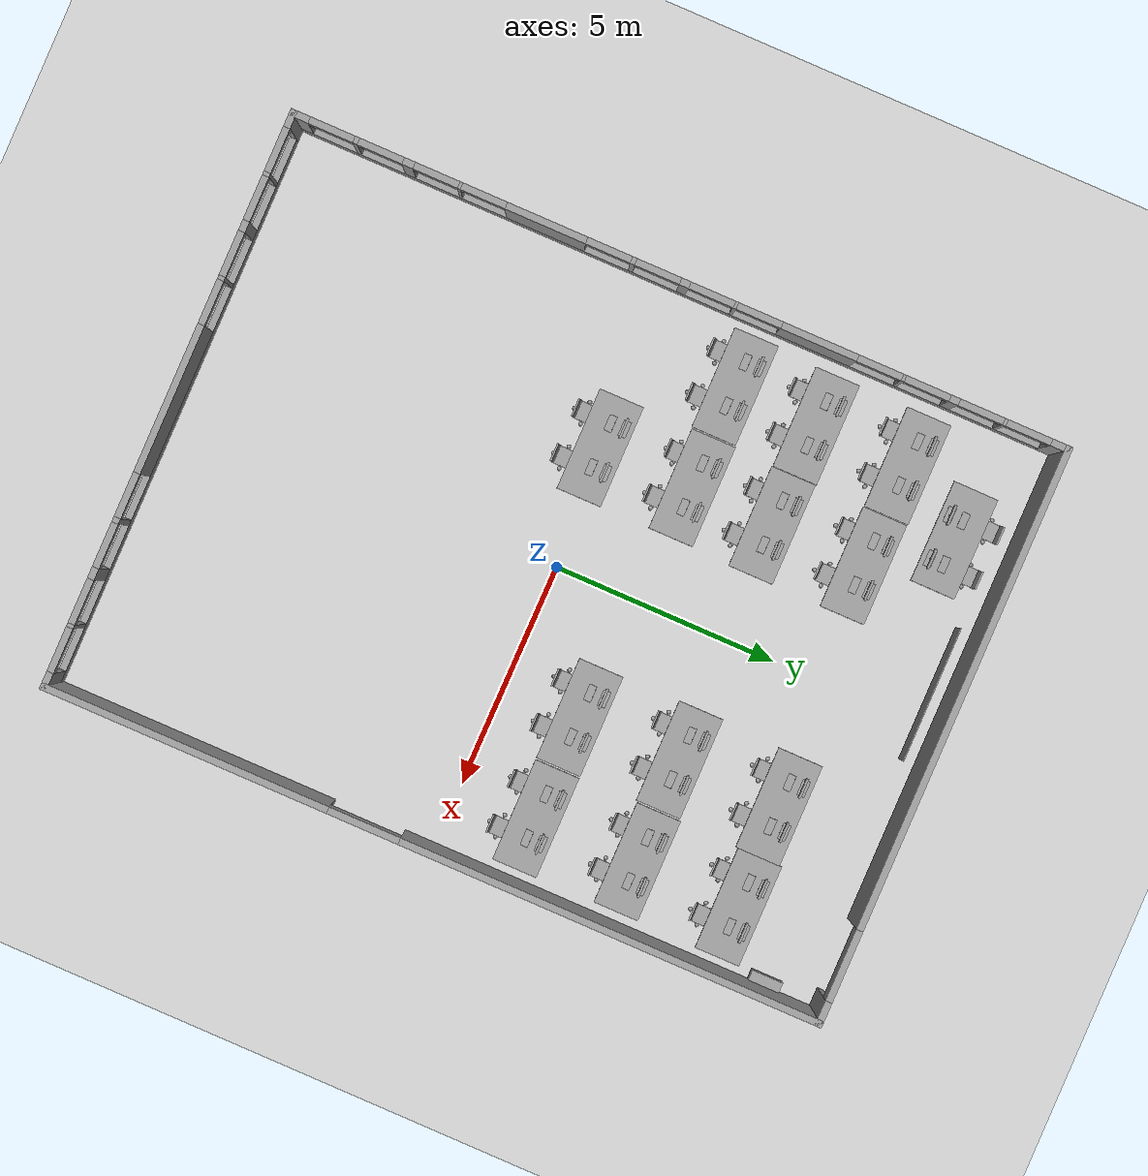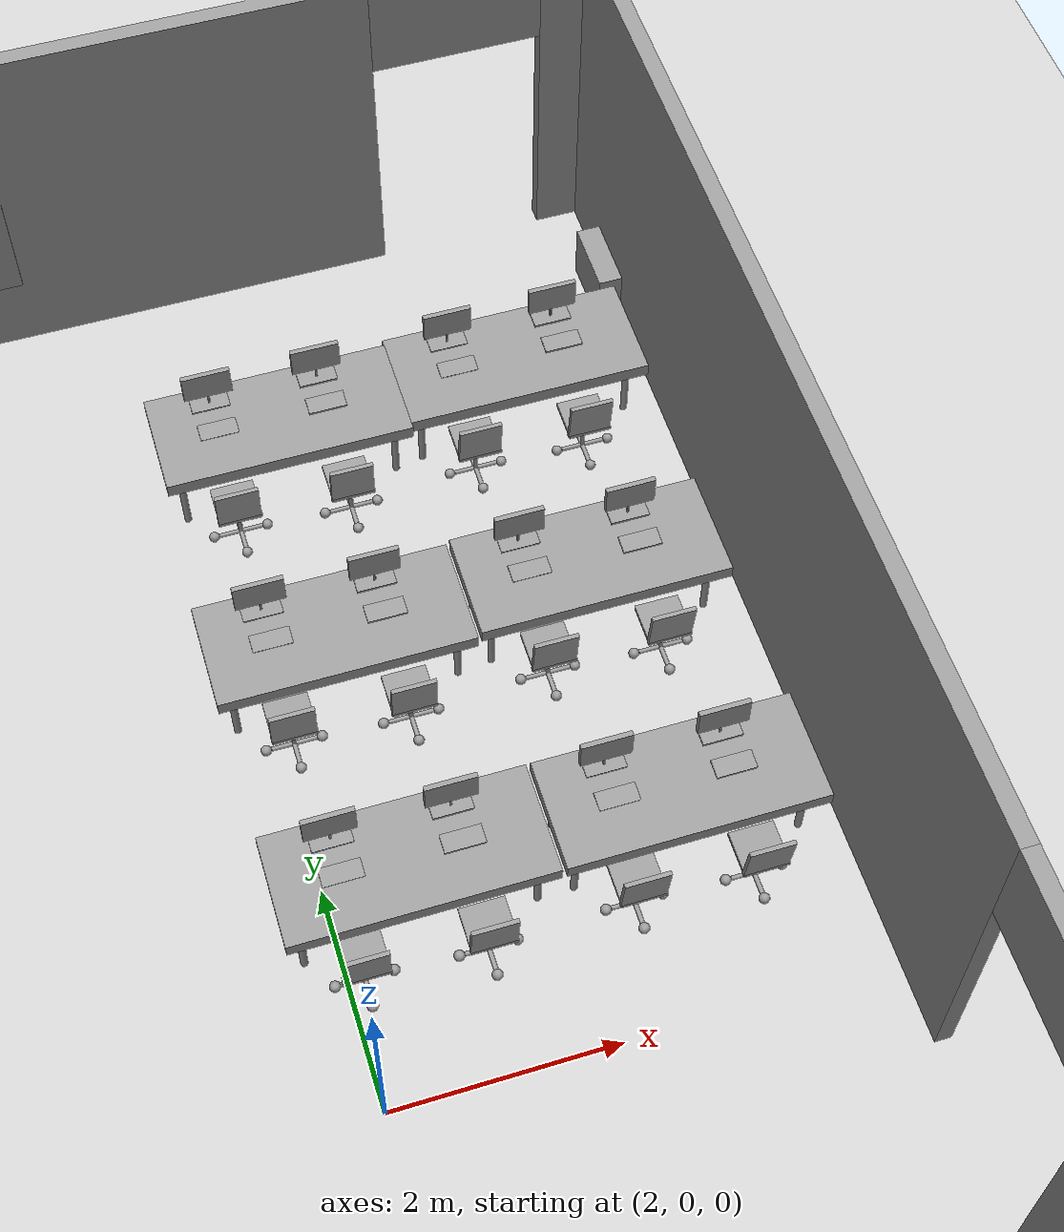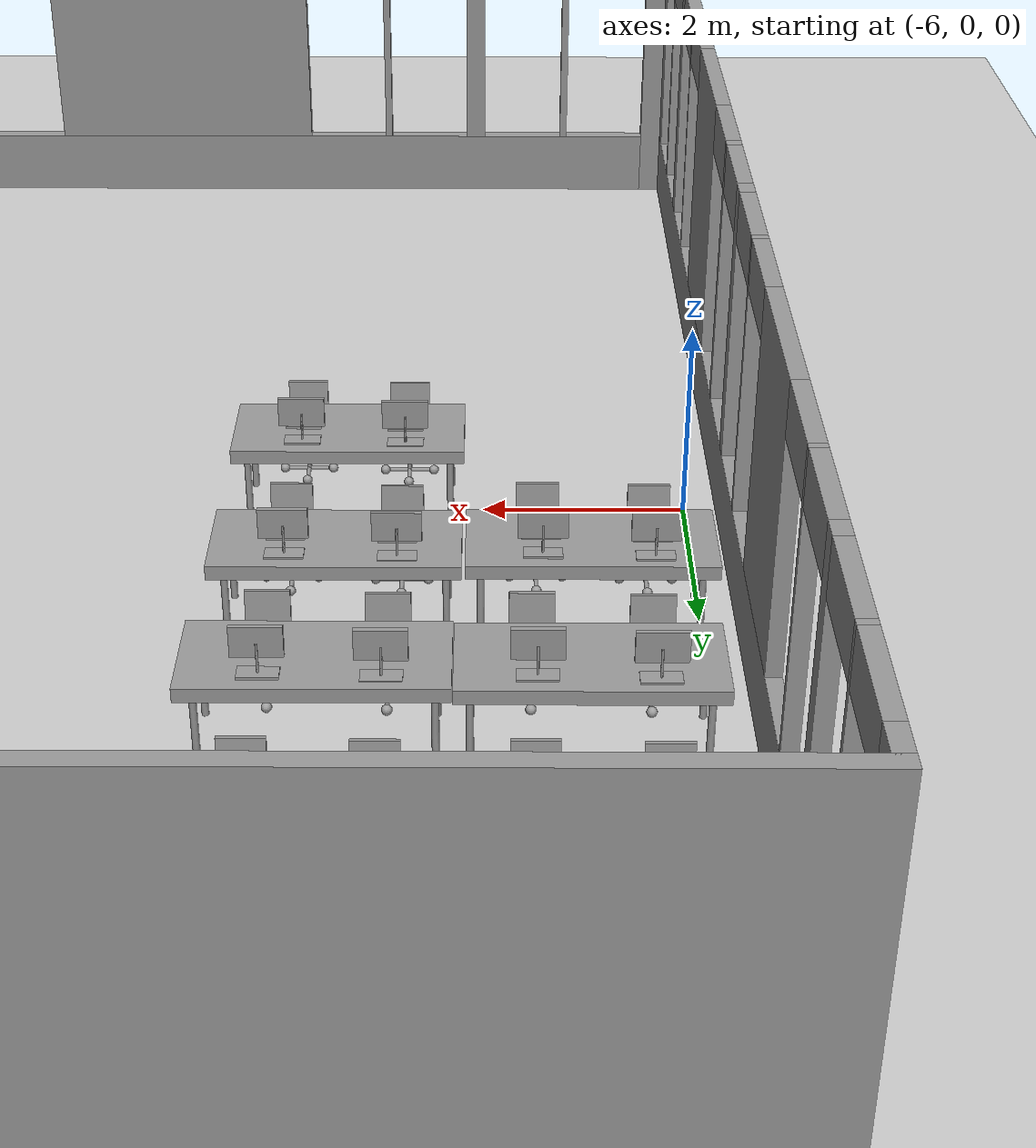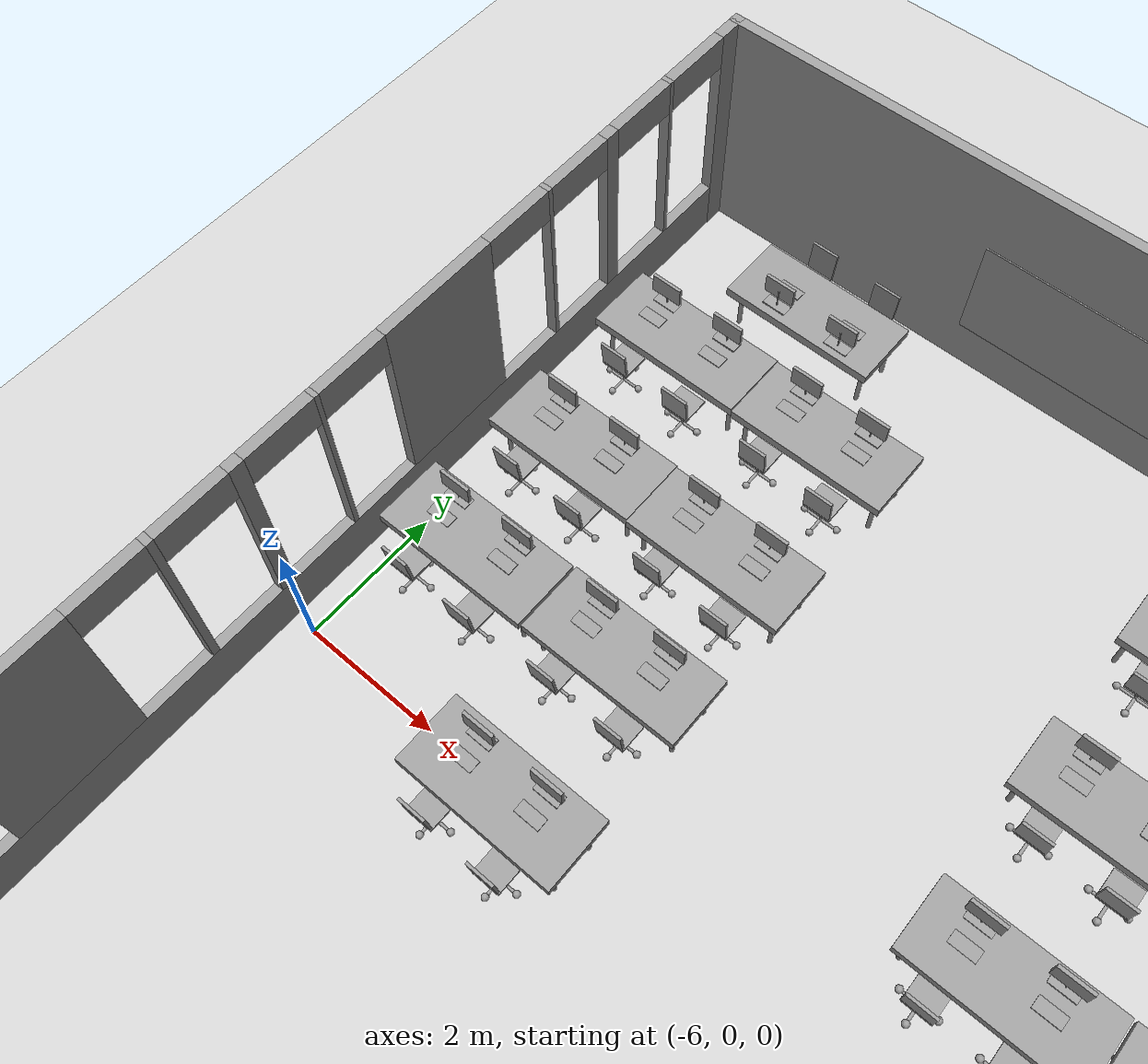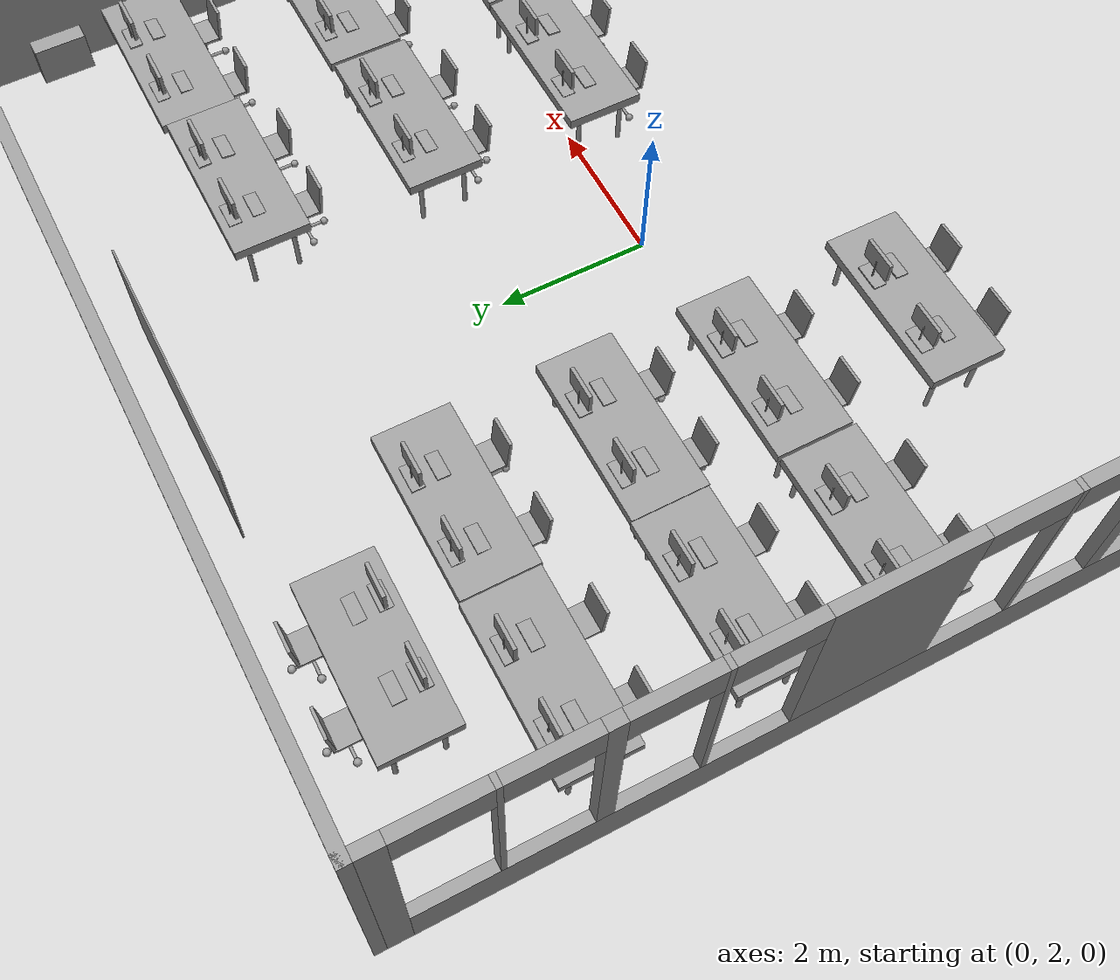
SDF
<sdf version="1.6">
 <world name="default">
  <model name="ground_plane">
   <static>1</static>
   <link name="link">
    <collision name="collision">
     <geometry><plane><normal>0 0 1</normal><size>100 100</size></plane></geometry>
     <surface><friction><ode><mu>100</mu><mu2>50</mu2></ode></friction></surface>
    </collision>
    <visual name="visual">
     <cast_shadows>0</cast_shadows>
     <geometry><plane><normal>0 0 1</normal><size>100 100</size></plane></geometry>
     <material>
      <script><uri>file://media/materials/scripts/gazebo.material</uri><name>Gazebo/Grey</name></script>
     </material>
    </visual>
   </link>
  </model>
  <model name="PiantaDefinitivaAlfa">
   <pose>0.023894 0.00572 0 0 -0 0</pose>
   <link name="Wall_0">
    <pose>0 -8.68 0 0 -0 0</pose>
    <visual name="Wall_0_Visual_0">
     <pose>-6.29943 0 1.75 0 -0 0</pose>
     <geometry><box><size>0.401138 0.15 3.5</size></box></geometry>
     <material>
      <script><uri>file://media/materials/scripts/gazebo.material</uri><name>Gazebo/Grey</name></script>
      <ambient>1 1 1 1</ambient>
     </material>
     <meta><layer>0</layer></meta>
    </visual>
    <collision name="Wall_0_Collision_0">
     <geometry><box><size>0.401138 0.15 3.5</size></box></geometry>
     <pose>-6.29943 0 1.75 0 -0 0</pose>
    </collision>
    <visual name="Wall_0_Visual_1">
     <pose>0.200569 0 0.375 0 -0 0</pose>
     <geometry><box><size>12.5989 0.15 0.75</size></box></geometry>
     <material>
      <script><uri>file://media/materials/scripts/gazebo.material</uri><name>Gazebo/Grey</name></script>
      <ambient>1 1 1 1</ambient>
     </material>
     <meta><layer>0</layer></meta>
    </visual>
    <collision name="Wall_0_Collision_1">
     <geometry><box><size>12.5989 0.15 0.75</size></box></geometry>
     <pose>0.200569 0 0.375 0 -0 0</pose>
    </collision>
    <visual name="Wall_0_Visual_2">
     <pose>-5.05617 0 2.125 0 -0 0</pose>
     <geometry><box><size>0.085387 0.15 2.75</size></box></geometry>
     <material>
      <script><uri>file://media/materials/scripts/gazebo.material</uri><name>Gazebo/Grey</name></script>
      <ambient>1 1 1 1</ambient>
     </material>
     <meta><layer>0</layer></meta>
    </visual>
    <collision name="Wall_0_Collision_2">
     <geometry><box><size>0.085387 0.15 2.75</size></box></geometry>
     <pose>-5.05617 0 2.125 0 -0 0</pose>
    </collision>
    <visual name="Wall_0_Visual_3">
     <pose>-3.89258 0 2.125 0 -0 0</pose>
     <geometry><box><size>0.241794 0.15 2.75</size></box></geometry>
     <material>
      <script><uri>file://media/materials/scripts/gazebo.material</uri><name>Gazebo/Grey</name></script>
      <ambient>1 1 1 1</ambient>
     </material>
     <meta><layer>0</layer></meta>
    </visual>
    <collision name="Wall_0_Collision_3">
     <geometry><box><size>0.241794 0.15 2.75</size></box></geometry>
     <pose>-3.89258 0 2.125 0 -0 0</pose>
    </collision>
    <visual name="Wall_0_Visual_4">
     <pose>-2.72949 0 2.125 0 -0 0</pose>
     <geometry><box><size>0.084384 0.15 2.75</size></box></geometry>
     <material>
      <script><uri>file://media/materials/scripts/gazebo.material</uri><name>Gazebo/Grey</name></script>
      <ambient>1 1 1 1</ambient>
     </material>
     <meta><layer>0</layer></meta>
    </visual>
    <collision name="Wall_0_Collision_4">
     <geometry><box><size>0.084384 0.15 2.75</size></box></geometry>
     <pose>-2.72949 0 2.125 0 -0 0</pose>
    </collision>
    <visual name="Wall_0_Visual_5">
     <pose>-0.027274 0 2.125 0 -0 0</pose>
     <geometry><box><size>3.32004 0.15 2.75</size></box></geometry>
     <material>
      <script><uri>file://media/materials/scripts/gazebo.material</uri><name>Gazebo/Grey</name></script>
      <ambient>1 1 1 1</ambient>
     </material>
     <meta><layer>0</layer></meta>
    </visual>
    <collision name="Wall_0_Collision_5">
     <geometry><box><size>3.32004 0.15 2.75</size></box></geometry>
     <pose>-0.027274 0 2.125 0 -0 0</pose>
    </collision>
    <visual name="Wall_0_Visual_6">
     <pose>2.69243 0 2.125 0 -0 0</pose>
     <geometry><box><size>0.119364 0.15 2.75</size></box></geometry>
     <material>
      <script><uri>file://media/materials/scripts/gazebo.material</uri><name>Gazebo/Grey</name></script>
      <ambient>1 1 1 1</ambient>
     </material>
     <meta><layer>0</layer></meta>
    </visual>
    <collision name="Wall_0_Collision_6">
     <geometry><box><size>0.119364 0.15 2.75</size></box></geometry>
     <pose>2.69243 0 2.125 0 -0 0</pose>
    </collision>
    <visual name="Wall_0_Visual_7">
     <pose>3.88176 0 2.125 0 -0 0</pose>
     <geometry><box><size>0.259284 0.15 2.75</size></box></geometry>
     <material>
      <script><uri>file://media/materials/scripts/gazebo.material</uri><name>Gazebo/Grey</name></script>
      <ambient>1 1 1 1</ambient>
     </material>
     <meta><layer>0</layer></meta>
    </visual>
    <collision name="Wall_0_Collision_7">
     <geometry><box><size>0.259284 0.15 2.75</size></box></geometry>
     <pose>3.88176 0 2.125 0 -0 0</pose>
    </collision>
    <visual name="Wall_0_Visual_8">
     <pose>5.05359 0 2.125 0 -0 0</pose>
     <geometry><box><size>0.084384 0.15 2.75</size></box></geometry>
     <material>
      <script><uri>file://media/materials/scripts/gazebo.material</uri><name>Gazebo/Grey</name></script>
      <ambient>1 1 1 1</ambient>
     </material>
     <meta><layer>0</layer></meta>
    </visual>
    <collision name="Wall_0_Collision_8">
     <geometry><box><size>0.084384 0.15 2.75</size></box></geometry>
     <pose>5.05359 0 2.125 0 -0 0</pose>
    </collision>
    <visual name="Wall_0_Visual_9">
     <pose>6.29789 0 2.125 0 -0 0</pose>
     <geometry><box><size>0.404219 0.15 2.75</size></box></geometry>
     <material>
      <script><uri>file://media/materials/scripts/gazebo.material</uri><name>Gazebo/Grey</name></script>
      <ambient>1 1 1 1</ambient>
     </material>
     <meta><layer>0</layer></meta>
    </visual>
    <collision name="Wall_0_Collision_9">
     <geometry><box><size>0.404219 0.15 2.75</size></box></geometry>
     <pose>6.29789 0 2.125 0 -0 0</pose>
    </collision>
    <visual name="Wall_0_Visual_10">
     <pose>-5.59886 0 3.25 0 -0 0</pose>
     <geometry><box><size>1 0.15 0.5</size></box></geometry>
     <material>
      <script><uri>file://media/materials/scripts/gazebo.material</uri><name>Gazebo/Grey</name></script>
      <ambient>1 1 1 1</ambient>
     </material>
     <meta><layer>0</layer></meta>
    </visual>
    <collision name="Wall_0_Collision_10">
     <geometry><box><size>1 0.15 0.5</size></box></geometry>
     <pose>-5.59886 0 3.25 0 -0 0</pose>
    </collision>
    <visual name="Wall_0_Visual_11">
     <pose>-4.51347 0 3.25 0 -0 0</pose>
     <geometry><box><size>1 0.15 0.5</size></box></geometry>
     <material>
      <script><uri>file://media/materials/scripts/gazebo.material</uri><name>Gazebo/Grey</name></script>
      <ambient>1 1 1 1</ambient>
     </material>
     <meta><layer>0</layer></meta>
    </visual>
    <collision name="Wall_0_Collision_11">
     <geometry><box><size>1 0.15 0.5</size></box></geometry>
     <pose>-4.51347 0 3.25 0 -0 0</pose>
    </collision>
    <visual name="Wall_0_Visual_12">
     <pose>-3.27168 0 3.25 0 -0 0</pose>
     <geometry><box><size>1 0.15 0.5</size></box></geometry>
     <material>
      <script><uri>file://media/materials/scripts/gazebo.material</uri><name>Gazebo/Grey</name></script>
      <ambient>1 1 1 1</ambient>
     </material>
     <meta><layer>0</layer></meta>
    </visual>
    <collision name="Wall_0_Collision_12">
     <geometry><box><size>1 0.15 0.5</size></box></geometry>
     <pose>-3.27168 0 3.25 0 -0 0</pose>
    </collision>
    <visual name="Wall_0_Visual_13">
     <pose>-2.1873 0 3.25 0 -0 0</pose>
     <geometry><box><size>1 0.15 0.5</size></box></geometry>
     <material>
      <script><uri>file://media/materials/scripts/gazebo.material</uri><name>Gazebo/Grey</name></script>
      <ambient>1 1 1 1</ambient>
     </material>
     <meta><layer>0</layer></meta>
    </visual>
    <collision name="Wall_0_Collision_13">
     <geometry><box><size>1 0.15 0.5</size></box></geometry>
     <pose>-2.1873 0 3.25 0 -0 0</pose>
    </collision>
    <visual name="Wall_0_Visual_14">
     <pose>2.13275 0 3.25 0 -0 0</pose>
     <geometry><box><size>1 0.15 0.5</size></box></geometry>
     <material>
      <script><uri>file://media/materials/scripts/gazebo.material</uri><name>Gazebo/Grey</name></script>
      <ambient>1 1 1 1</ambient>
     </material>
     <meta><layer>0</layer></meta>
    </visual>
    <collision name="Wall_0_Collision_14">
     <geometry><box><size>1 0.15 0.5</size></box></geometry>
     <pose>2.13275 0 3.25 0 -0 0</pose>
    </collision>
    <visual name="Wall_0_Visual_15">
     <pose>3.25211 0 3.25 0 -0 0</pose>
     <geometry><box><size>1 0.15 0.5</size></box></geometry>
     <material>
      <script><uri>file://media/materials/scripts/gazebo.material</uri><name>Gazebo/Grey</name></script>
      <ambient>1 1 1 1</ambient>
     </material>
     <meta><layer>0</layer></meta>
    </visual>
    <collision name="Wall_0_Collision_15">
     <geometry><box><size>1 0.15 0.5</size></box></geometry>
     <pose>3.25211 0 3.25 0 -0 0</pose>
    </collision>
    <visual name="Wall_0_Visual_16">
     <pose>4.5114 0 3.25 0 -0 0</pose>
     <geometry><box><size>1 0.15 0.5</size></box></geometry>
     <material>
      <script><uri>file://media/materials/scripts/gazebo.material</uri><name>Gazebo/Grey</name></script>
      <ambient>1 1 1 1</ambient>
     </material>
     <meta><layer>0</layer></meta>
    </visual>
    <collision name="Wall_0_Collision_16">
     <geometry><box><size>1 0.15 0.5</size></box></geometry>
     <pose>4.5114 0 3.25 0 -0 0</pose>
    </collision>
    <visual name="Wall_0_Visual_17">
     <pose>5.59578 0 3.25 0 -0 0</pose>
     <geometry><box><size>1 0.15 0.5</size></box></geometry>
     <material>
      <script><uri>file://media/materials/scripts/gazebo.material</uri><name>Gazebo/Grey</name></script>
      <ambient>1 1 1 1</ambient>
     </material>
     <meta><layer>0</layer></meta>
    </visual>
    <collision name="Wall_0_Collision_17">
     <geometry><box><size>1 0.15 0.5</size></box></geometry>
     <pose>5.59578 0 3.25 0 -0 0</pose>
    </collision>
   </link>
   <link name="Wall_2">
    <pose>6.425 0 0 0 -0 1.5708</pose>
    <visual name="Wall_2_Visual_0">
     <pose>-5.54089 0 1.75 0 -0 0</pose>
     <geometry><box><size>6.42841 0.15 3.5</size></box></geometry>
     <material>
      <script><uri>file://media/materials/scripts/gazebo.material</uri><name>Gazebo/Grey</name></script>
      <ambient>1 1 1 1</ambient>
     </material>
     <meta><layer>0</layer></meta>
    </visual>
    <collision name="Wall_2_Collision_0">
     <geometry><box><size>6.42841 0.15 3.5</size></box></geometry>
     <pose>-5.54089 0 1.75 0 -0 0</pose>
    </collision>
    <visual name="Wall_2_Visual_1">
     <pose>4.0142 0 1.75 0 -0 0</pose>
     <geometry><box><size>9.48178 0.15 3.5</size></box></geometry>
     <material>
      <script><uri>file://media/materials/scripts/gazebo.material</uri><name>Gazebo/Grey</name></script>
      <ambient>1 1 1 1</ambient>
     </material>
     <meta><layer>0</layer></meta>
    </visual>
    <collision name="Wall_2_Collision_1">
     <geometry><box><size>9.48178 0.15 3.5</size></box></geometry>
     <pose>4.0142 0 1.75 0 -0 0</pose>
    </collision>
    <visual name="Wall_2_Visual_2">
     <pose>-1.52668 0 3 0 -0 0</pose>
     <geometry><box><size>1.6 0.15 1</size></box></geometry>
     <material>
      <script><uri>file://media/materials/scripts/gazebo.material</uri><name>Gazebo/Grey</name></script>
      <ambient>1 1 1 1</ambient>
     </material>
     <meta><layer>0</layer></meta>
    </visual>
    <collision name="Wall_2_Collision_2">
     <geometry><box><size>1.6 0.15 1</size></box></geometry>
     <pose>-1.52668 0 3 0 -0 0</pose>
    </collision>
   </link>
   <link name="Wall_3">
    <pose>0 8.68 0 0 -0 3.14159</pose>
    <visual name="Wall_3_Visual_0">
     <pose>-6.22135 0 1.75 0 -0 0</pose>
     <geometry><box><size>0.557299 0.15 3.5</size></box></geometry>
     <material>
      <script><uri>file://media/materials/scripts/gazebo.material</uri><name>Gazebo/Grey</name></script>
      <ambient>1 1 1 1</ambient>
     </material>
     <meta><layer>0</layer></meta>
    </visual>
    <collision name="Wall_3_Collision_0">
     <geometry><box><size>0.557299 0.15 3.5</size></box></geometry>
     <pose>-6.22135 0 1.75 0 -0 0</pose>
    </collision>
    <visual name="Wall_3_Visual_1">
     <pose>1.07865 0 1.75 0 -0 0</pose>
     <geometry><box><size>10.8427 0.15 3.5</size></box></geometry>
     <material>
      <script><uri>file://media/materials/scripts/gazebo.material</uri><name>Gazebo/Grey</name></script>
      <ambient>1 1 1 1</ambient>
     </material>
     <meta><layer>0</layer></meta>
    </visual>
    <collision name="Wall_3_Collision_1">
     <geometry><box><size>10.8427 0.15 3.5</size></box></geometry>
     <pose>1.07865 0 1.75 0 -0 0</pose>
    </collision>
    <visual name="Wall_3_Visual_2">
     <pose>-5.1427 0 3 0 -0 0</pose>
     <geometry><box><size>1.6 0.15 1</size></box></geometry>
     <material>
      <script><uri>file://media/materials/scripts/gazebo.material</uri><name>Gazebo/Grey</name></script>
      <ambient>1 1 1 1</ambient>
     </material>
     <meta><layer>0</layer></meta>
    </visual>
    <collision name="Wall_3_Collision_2">
     <geometry><box><size>1.6 0.15 1</size></box></geometry>
     <pose>-5.1427 0 3 0 -0 0</pose>
    </collision>
   </link>
   <link name="Wall_4">
    <pose>-6.425 0.005 0 0 0 -1.5708</pose>
    <visual name="Wall_4_Visual_0">
     <pose>-8.52384 0 1.75 0 -0 0</pose>
     <geometry><box><size>0.452322 0.15 3.5</size></box></geometry>
     <material>
      <script><uri>file://media/materials/scripts/gazebo.material</uri><name>Gazebo/Grey</name></script>
      <ambient>1 1 1 1</ambient>
     </material>
     <meta><layer>0</layer></meta>
    </visual>
    <collision name="Wall_4_Collision_0">
     <geometry><box><size>0.452322 0.15 3.5</size></box></geometry>
     <pose>-8.52384 0 1.75 0 -0 0</pose>
    </collision>
    <visual name="Wall_4_Visual_1">
     <pose>0.226161 0 0.375 0 -0 0</pose>
     <geometry><box><size>17.0477 0.15 0.75</size></box></geometry>
     <material>
      <script><uri>file://media/materials/scripts/gazebo.material</uri><name>Gazebo/Grey</name></script>
      <ambient>1 1 1 1</ambient>
     </material>
     <meta><layer>0</layer></meta>
    </visual>
    <collision name="Wall_4_Collision_1">
     <geometry><box><size>17.0477 0.15 0.75</size></box></geometry>
     <pose>0.226161 0 0.375 0 -0 0</pose>
    </collision>
    <visual name="Wall_4_Visual_2">
     <pose>-7.26423 0 2.125 0 -0 0</pose>
     <geometry><box><size>0.066894 0.15 2.75</size></box></geometry>
     <material>
      <script><uri>file://media/materials/scripts/gazebo.material</uri><name>Gazebo/Grey</name></script>
      <ambient>1 1 1 1</ambient>
     </material>
     <meta><layer>0</layer></meta>
    </visual>
    <collision name="Wall_4_Collision_2">
     <geometry><box><size>0.066894 0.15 2.75</size></box></geometry>
     <pose>-7.26423 0 2.125 0 -0 0</pose>
    </collision>
    <visual name="Wall_4_Visual_3">
     <pose>-6.12738 0 2.125 0 -0 0</pose>
     <geometry><box><size>0.206814 0.15 2.75</size></box></geometry>
     <material>
      <script><uri>file://media/materials/scripts/gazebo.material</uri><name>Gazebo/Grey</name></script>
      <ambient>1 1 1 1</ambient>
     </material>
     <meta><layer>0</layer></meta>
    </visual>
    <collision name="Wall_4_Collision_3">
     <geometry><box><size>0.206814 0.15 2.75</size></box></geometry>
     <pose>-6.12738 0 2.125 0 -0 0</pose>
    </collision>
    <visual name="Wall_4_Visual_4">
     <pose>-4.99052 0 2.125 0 -0 0</pose>
     <geometry><box><size>0.066894 0.15 2.75</size></box></geometry>
     <material>
      <script><uri>file://media/materials/scripts/gazebo.material</uri><name>Gazebo/Grey</name></script>
      <ambient>1 1 1 1</ambient>
     </material>
     <meta><layer>0</layer></meta>
    </visual>
    <collision name="Wall_4_Collision_4">
     <geometry><box><size>0.066894 0.15 2.75</size></box></geometry>
     <pose>-4.99052 0 2.125 0 -0 0</pose>
    </collision>
    <visual name="Wall_4_Visual_5">
     <pose>-3.11034 0 2.125 0 -0 0</pose>
     <geometry><box><size>1.69347 0.15 2.75</size></box></geometry>
     <material>
      <script><uri>file://media/materials/scripts/gazebo.material</uri><name>Gazebo/Grey</name></script>
      <ambient>1 1 1 1</ambient>
     </material>
     <meta><layer>0</layer></meta>
    </visual>
    <collision name="Wall_4_Collision_5">
     <geometry><box><size>1.69347 0.15 2.75</size></box></geometry>
     <pose>-3.11034 0 2.125 0 -0 0</pose>
    </collision>
    <visual name="Wall_4_Visual_6">
     <pose>-1.23016 0 2.125 0 -0 0</pose>
     <geometry><box><size>0.066894 0.15 2.75</size></box></geometry>
     <material>
      <script><uri>file://media/materials/scripts/gazebo.material</uri><name>Gazebo/Grey</name></script>
      <ambient>1 1 1 1</ambient>
     </material>
     <meta><layer>0</layer></meta>
    </visual>
    <collision name="Wall_4_Collision_6">
     <geometry><box><size>0.066894 0.15 2.75</size></box></geometry>
     <pose>-1.23016 0 2.125 0 -0 0</pose>
    </collision>
    <visual name="Wall_4_Visual_7">
     <pose>-0.093305 0 2.125 0 -0 0</pose>
     <geometry><box><size>0.206814 0.15 2.75</size></box></geometry>
     <material>
      <script><uri>file://media/materials/scripts/gazebo.material</uri><name>Gazebo/Grey</name></script>
      <ambient>1 1 1 1</ambient>
     </material>
     <meta><layer>0</layer></meta>
    </visual>
    <collision name="Wall_4_Collision_7">
     <geometry><box><size>0.206814 0.15 2.75</size></box></geometry>
     <pose>-0.093305 0 2.125 0 -0 0</pose>
    </collision>
    <visual name="Wall_4_Visual_8">
     <pose>1.06104 0 2.125 0 -0 0</pose>
     <geometry><box><size>0.101874 0.15 2.75</size></box></geometry>
     <material>
      <script><uri>file://media/materials/scripts/gazebo.material</uri><name>Gazebo/Grey</name></script>
      <ambient>1 1 1 1</ambient>
     </material>
     <meta><layer>0</layer></meta>
    </visual>
    <collision name="Wall_4_Collision_8">
     <geometry><box><size>0.101874 0.15 2.75</size></box></geometry>
     <pose>1.06104 0 2.125 0 -0 0</pose>
    </collision>
    <visual name="Wall_4_Visual_9">
     <pose>3.01118 0 2.125 0 -0 0</pose>
     <geometry><box><size>1.79841 0.15 2.75</size></box></geometry>
     <material>
      <script><uri>file://media/materials/scripts/gazebo.material</uri><name>Gazebo/Grey</name></script>
      <ambient>1 1 1 1</ambient>
     </material>
     <meta><layer>0</layer></meta>
    </visual>
    <collision name="Wall_4_Collision_9">
     <geometry><box><size>1.79841 0.15 2.75</size></box></geometry>
     <pose>3.01118 0 2.125 0 -0 0</pose>
    </collision>
    <visual name="Wall_4_Visual_10">
     <pose>4.94383 0 2.125 0 -0 0</pose>
     <geometry><box><size>0.066894 0.15 2.75</size></box></geometry>
     <material>
      <script><uri>file://media/materials/scripts/gazebo.material</uri><name>Gazebo/Grey</name></script>
      <ambient>1 1 1 1</ambient>
     </material>
     <meta><layer>0</layer></meta>
    </visual>
    <collision name="Wall_4_Collision_10">
     <geometry><box><size>0.066894 0.15 2.75</size></box></geometry>
     <pose>4.94383 0 2.125 0 -0 0</pose>
    </collision>
    <visual name="Wall_4_Visual_11">
     <pose>6.09818 0 2.125 0 -0 0</pose>
     <geometry><box><size>0.241794 0.15 2.75</size></box></geometry>
     <material>
      <script><uri>file://media/materials/scripts/gazebo.material</uri><name>Gazebo/Grey</name></script>
      <ambient>1 1 1 1</ambient>
     </material>
     <meta><layer>0</layer></meta>
    </visual>
    <collision name="Wall_4_Collision_11">
     <geometry><box><size>0.241794 0.15 2.75</size></box></geometry>
     <pose>6.09818 0 2.125 0 -0 0</pose>
    </collision>
    <visual name="Wall_4_Visual_12">
     <pose>7.27001 0 2.125 0 -0 0</pose>
     <geometry><box><size>0.101874 0.15 2.75</size></box></geometry>
     <material>
      <script><uri>file://media/materials/scripts/gazebo.material</uri><name>Gazebo/Grey</name></script>
      <ambient>1 1 1 1</ambient>
     </material>
     <meta><layer>0</layer></meta>
    </visual>
    <collision name="Wall_4_Collision_12">
     <geometry><box><size>0.101874 0.15 2.75</size></box></geometry>
     <pose>7.27001 0 2.125 0 -0 0</pose>
    </collision>
    <visual name="Wall_4_Visual_13">
     <pose>8.53547 0 2.125 0 -0 0</pose>
     <geometry><box><size>0.429052 0.15 2.75</size></box></geometry>
     <material>
      <script><uri>file://media/materials/scripts/gazebo.material</uri><name>Gazebo/Grey</name></script>
      <ambient>1 1 1 1</ambient>
     </material>
     <meta><layer>0</layer></meta>
    </visual>
    <collision name="Wall_4_Collision_13">
     <geometry><box><size>0.429052 0.15 2.75</size></box></geometry>
     <pose>8.53547 0 2.125 0 -0 0</pose>
    </collision>
    <visual name="Wall_4_Visual_14">
     <pose>-7.79768 0 3.25 0 -0 0</pose>
     <geometry><box><size>1 0.15 0.5</size></box></geometry>
     <material>
      <script><uri>file://media/materials/scripts/gazebo.material</uri><name>Gazebo/Grey</name></script>
      <ambient>1 1 1 1</ambient>
     </material>
     <meta><layer>0</layer></meta>
    </visual>
    <collision name="Wall_4_Collision_14">
     <geometry><box><size>1 0.15 0.5</size></box></geometry>
     <pose>-7.79768 0 3.25 0 -0 0</pose>
    </collision>
    <visual name="Wall_4_Visual_15">
     <pose>-6.73078 0 3.25 0 -0 0</pose>
     <geometry><box><size>1 0.15 0.5</size></box></geometry>
     <material>
      <script><uri>file://media/materials/scripts/gazebo.material</uri><name>Gazebo/Grey</name></script>
      <ambient>1 1 1 1</ambient>
     </material>
     <meta><layer>0</layer></meta>
    </visual>
    <collision name="Wall_4_Collision_15">
     <geometry><box><size>1 0.15 0.5</size></box></geometry>
     <pose>-6.73078 0 3.25 0 -0 0</pose>
    </collision>
    <visual name="Wall_4_Visual_16">
     <pose>-5.52397 0 3.25 0 -0 0</pose>
     <geometry><box><size>1 0.15 0.5</size></box></geometry>
     <material>
      <script><uri>file://media/materials/scripts/gazebo.material</uri><name>Gazebo/Grey</name></script>
      <ambient>1 1 1 1</ambient>
     </material>
     <meta><layer>0</layer></meta>
    </visual>
    <collision name="Wall_4_Collision_16">
     <geometry><box><size>1 0.15 0.5</size></box></geometry>
     <pose>-5.52397 0 3.25 0 -0 0</pose>
    </collision>
    <visual name="Wall_4_Visual_17">
     <pose>-4.45708 0 3.25 0 -0 0</pose>
     <geometry><box><size>1 0.15 0.5</size></box></geometry>
     <material>
      <script><uri>file://media/materials/scripts/gazebo.material</uri><name>Gazebo/Grey</name></script>
      <ambient>1 1 1 1</ambient>
     </material>
     <meta><layer>0</layer></meta>
    </visual>
    <collision name="Wall_4_Collision_17">
     <geometry><box><size>1 0.15 0.5</size></box></geometry>
     <pose>-4.45708 0 3.25 0 -0 0</pose>
    </collision>
    <visual name="Wall_4_Visual_18">
     <pose>-1.76361 0 3.25 0 -0 0</pose>
     <geometry><box><size>1 0.15 0.5</size></box></geometry>
     <material>
      <script><uri>file://media/materials/scripts/gazebo.material</uri><name>Gazebo/Grey</name></script>
      <ambient>1 1 1 1</ambient>
     </material>
     <meta><layer>0</layer></meta>
    </visual>
    <collision name="Wall_4_Collision_18">
     <geometry><box><size>1 0.15 0.5</size></box></geometry>
     <pose>-1.76361 0 3.25 0 -0 0</pose>
    </collision>
    <visual name="Wall_4_Visual_19">
     <pose>-0.696712 0 3.25 0 -0 0</pose>
     <geometry><box><size>1 0.15 0.5</size></box></geometry>
     <material>
      <script><uri>file://media/materials/scripts/gazebo.material</uri><name>Gazebo/Grey</name></script>
      <ambient>1 1 1 1</ambient>
     </material>
     <meta><layer>0</layer></meta>
    </visual>
    <collision name="Wall_4_Collision_19">
     <geometry><box><size>1 0.15 0.5</size></box></geometry>
     <pose>-0.696712 0 3.25 0 -0 0</pose>
    </collision>
    <visual name="Wall_4_Visual_20">
     <pose>0.510102 0 3.25 0 -0 0</pose>
     <geometry><box><size>1 0.15 0.5</size></box></geometry>
     <material>
      <script><uri>file://media/materials/scripts/gazebo.material</uri><name>Gazebo/Grey</name></script>
      <ambient>1 1 1 1</ambient>
     </material>
     <meta><layer>0</layer></meta>
    </visual>
    <collision name="Wall_4_Collision_20">
     <geometry><box><size>1 0.15 0.5</size></box></geometry>
     <pose>0.510102 0 3.25 0 -0 0</pose>
    </collision>
    <visual name="Wall_4_Visual_21">
     <pose>1.61198 0 3.25 0 -0 0</pose>
     <geometry><box><size>1 0.15 0.5</size></box></geometry>
     <material>
      <script><uri>file://media/materials/scripts/gazebo.material</uri><name>Gazebo/Grey</name></script>
      <ambient>1 1 1 1</ambient>
     </material>
     <meta><layer>0</layer></meta>
    </visual>
    <collision name="Wall_4_Collision_21">
     <geometry><box><size>1 0.15 0.5</size></box></geometry>
     <pose>1.61198 0 3.25 0 -0 0</pose>
    </collision>
    <visual name="Wall_4_Visual_22">
     <pose>4.41039 0 3.25 0 -0 0</pose>
     <geometry><box><size>1 0.15 0.5</size></box></geometry>
     <material>
      <script><uri>file://media/materials/scripts/gazebo.material</uri><name>Gazebo/Grey</name></script>
      <ambient>1 1 1 1</ambient>
     </material>
     <meta><layer>0</layer></meta>
    </visual>
    <collision name="Wall_4_Collision_22">
     <geometry><box><size>1 0.15 0.5</size></box></geometry>
     <pose>4.41039 0 3.25 0 -0 0</pose>
    </collision>
    <visual name="Wall_4_Visual_23">
     <pose>5.47728 0 3.25 0 -0 0</pose>
     <geometry><box><size>1 0.15 0.5</size></box></geometry>
     <material>
      <script><uri>file://media/materials/scripts/gazebo.material</uri><name>Gazebo/Grey</name></script>
      <ambient>1 1 1 1</ambient>
     </material>
     <meta><layer>0</layer></meta>
    </visual>
    <collision name="Wall_4_Collision_23">
     <geometry><box><size>1 0.15 0.5</size></box></geometry>
     <pose>5.47728 0 3.25 0 -0 0</pose>
    </collision>
    <visual name="Wall_4_Visual_24">
     <pose>6.71907 0 3.25 0 -0 0</pose>
     <geometry><box><size>1 0.15 0.5</size></box></geometry>
     <material>
      <script><uri>file://media/materials/scripts/gazebo.material</uri><name>Gazebo/Grey</name></script>
      <ambient>1 1 1 1</ambient>
     </material>
     <meta><layer>0</layer></meta>
    </visual>
    <collision name="Wall_4_Collision_24">
     <geometry><box><size>1 0.15 0.5</size></box></geometry>
     <pose>6.71907 0 3.25 0 -0 0</pose>
    </collision>
    <visual name="Wall_4_Visual_25">
     <pose>7.82095 0 3.25 0 -0 0</pose>
     <geometry><box><size>1 0.15 0.5</size></box></geometry>
     <material>
      <script><uri>file://media/materials/scripts/gazebo.material</uri><name>Gazebo/Grey</name></script>
      <ambient>1 1 1 1</ambient>
     </material>
     <meta><layer>0</layer></meta>
    </visual>
    <collision name="Wall_4_Collision_25">
     <geometry><box><size>1 0.15 0.5</size></box></geometry>
     <pose>7.82095 0 3.25 0 -0 0</pose>
    </collision>
   </link>
   <static>1</static>
  </model>
  <model name="bancata">
   <model name="Sedia">
    <link name="link">
     <inertial>
      <mass>1</mass>
      <inertia><ixx>0.1</ixx><ixy>0</ixy><ixz>0</ixz><iyy>0.1</iyy><iyz>0</iyz><izz>0.1</izz></inertia>
      <pose>0 -0.05 0 0 -0 0</pose>
     </inertial>
     <pose>0 -0.05 0.04 0 -0 0</pose>
     <visual name="visual">
      <geometry><sphere><radius>0.0479725</radius></sphere></geometry>
      <material>
       <script><name>Gazebo/Grey</name><uri>file://media/materials/scripts/gazebo.material</uri></script>
       <shader type="vertex"><normal_map>__default__</normal_map></shader>
       <ambient>0.3 0.3 0.3 1</ambient>
       <diffuse>0.7 0.7 0.7 1</diffuse>
       <specular>0.01 0.01 0.01 1</specular>
       <emissive>0 0 0 1</emissive>
      </material>
     </visual>
     <collision name="collision">
      <geometry><sphere><radius>0.047973</radius></sphere></geometry>
      <surface>
       <friction>
        <ode><mu>1</mu><mu2>1</mu2><fdir1>0 0 0</fdir1><slip1>0</slip1><slip2>0</slip2></ode>
        <torsional>
         <coefficient>1</coefficient>
         <patch_radius>0</patch_radius>
         <surface_radius>0</surface_radius>
         <use_patch_radius>1</use_patch_radius>
         <ode><slip>0</slip></ode>
        </torsional>
       </friction>
       <bounce><restitution_coefficient>0</restitution_coefficient><threshold>1e+06</threshold></bounce>
       <contact>
        <collide_without_contact>0</collide_without_contact>
        <collide_without_contact_bitmask>1</collide_without_contact_bitmask>
        <collide_bitmask>1</collide_bitmask>
        <ode>
         <soft_cfm>0</soft_cfm>
         <soft_erp>0.2</soft_erp>
         <kp>1e+13</kp>
         <kd>1</kd>
         <max_vel>0.01</max_vel>
         <min_depth>0</min_depth>
        </ode>
        <bullet>
         <split_impulse>1</split_impulse>
         <split_impulse_penetration_threshold>-0.01</split_impulse_penetration_threshold>
         <soft_cfm>0</soft_cfm>
         <soft_erp>0.2</soft_erp>
         <kp>1e+13</kp>
         <kd>1</kd>
        </bullet>
       </contact>
      </surface>
     </collision>
    </link>
    <link name="link_0">
     <inertial>
      <mass>0.000595181</mass>
      <inertia>
       <ixx>8.34662e-06</ixx>
       <ixy>0</ixy>
       <ixz>0</ixz>
       <iyy>8.34662e-06</iyy>
       <iyz>0</iyz>
       <izz>1.11586e-07</izz>
      </inertia>
     </inertial>
     <pose>-0 0.2 0.2494 0 -0 0</pose>
     <visual name="visual">
      <geometry><cylinder><radius>0.0193636</radius><length>0.408851</length></cylinder></geometry>
      <material>
       <lighting>1</lighting>
       <script><uri>file://media/materials/scripts/gazebo.material</uri><name>Gazebo/Grey</name></script>
       <shader type="vertex"><normal_map>__default__</normal_map></shader>
       <ambient>0.3 0.3 0.3 1</ambient>
       <diffuse>0.7 0.7 0.7 1</diffuse>
       <specular>0.01 0.01 0.01 1</specular>
       <emissive>0 0 0 1</emissive>
      </material>
     </visual>
     <collision name="collision">
      <geometry><cylinder><radius>0.019364</radius><length>0.408851</length></cylinder></geometry>
      <surface>
       <friction>
        <ode><mu>1</mu><mu2>1</mu2><fdir1>0 0 0</fdir1><slip1>0</slip1><slip2>0</slip2></ode>
        <torsional>
         <coefficient>1</coefficient>
         <patch_radius>0</patch_radius>
         <surface_radius>0</surface_radius>
         <use_patch_radius>1</use_patch_radius>
         <ode><slip>0</slip></ode>
        </torsional>
       </friction>
       <bounce><restitution_coefficient>0</restitution_coefficient><threshold>1e+06</threshold></bounce>
       <contact>
        <collide_without_contact>0</collide_without_contact>
        <collide_without_contact_bitmask>1</collide_without_contact_bitmask>
        <collide_bitmask>1</collide_bitmask>
        <ode>
         <soft_cfm>0</soft_cfm>
         <soft_erp>0.2</soft_erp>
         <kp>1e+13</kp>
         <kd>1</kd>
         <max_vel>0.01</max_vel>
         <min_depth>0</min_depth>
        </ode>
        <bullet>
         <split_impulse>1</split_impulse>
         <split_impulse_penetration_threshold>-0.01</split_impulse_penetration_threshold>
         <soft_cfm>0</soft_cfm>
         <soft_erp>0.2</soft_erp>
         <kp>1e+13</kp>
         <kd>1</kd>
        </bullet>
       </contact>
      </surface>
     </collision>
    </link>
    <link name="link_0_clone">
     <inertial>
      <mass>0.000698061</mass>
      <inertia>
       <ixx>1.02332e-05</ixx>
       <ixy>0</ixy>
       <ixz>0</ixz>
       <iyy>1.02332e-05</iyy>
       <iyz>0</iyz>
       <izz>1.50251e-07</izz>
      </inertia>
     </inertial>
     <pose>0 0.2 0.04 -1.571 -0 0</pose>
     <visual name="visual">
      <geometry><cylinder><radius>0.0207471</radius><length>0.417878</length></cylinder></geometry>
      <material>
       <lighting>1</lighting>
       <script><uri>file://media/materials/scripts/gazebo.material</uri><name>Gazebo/Grey</name></script>
       <shader type="vertex"><normal_map>__default__</normal_map></shader>
       <ambient>0.3 0.3 0.3 1</ambient>
       <diffuse>0.7 0.7 0.7 1</diffuse>
       <specular>0.01 0.01 0.01 1</specular>
       <emissive>0 0 0 1</emissive>
      </material>
     </visual>
     <collision name="collision">
      <geometry><cylinder><radius>0.020748</radius><length>0.417878</length></cylinder></geometry>
      <surface>
       <friction>
        <ode><mu>1</mu><mu2>1</mu2><fdir1>0 0 0</fdir1><slip1>0</slip1><slip2>0</slip2></ode>
        <torsional>
         <coefficient>1</coefficient>
         <patch_radius>0</patch_radius>
         <surface_radius>0</surface_radius>
         <use_patch_radius>1</use_patch_radius>
         <ode><slip>0</slip></ode>
        </torsional>
       </friction>
       <bounce><restitution_coefficient>0</restitution_coefficient><threshold>1e+06</threshold></bounce>
       <contact>
        <collide_without_contact>0</collide_without_contact>
        <collide_without_contact_bitmask>1</collide_without_contact_bitmask>
        <collide_bitmask>1</collide_bitmask>
        <ode>
         <soft_cfm>0</soft_cfm>
         <soft_erp>0.2</soft_erp>
         <kp>1e+13</kp>
         <kd>1</kd>
         <max_vel>0.01</max_vel>
         <min_depth>0</min_depth>
        </ode>
        <bullet>
         <split_impulse>1</split_impulse>
         <split_impulse_penetration_threshold>-0.01</split_impulse_penetration_threshold>
         <soft_cfm>0</soft_cfm>
         <soft_erp>0.2</soft_erp>
         <kp>1e+13</kp>
         <kd>1</kd>
        </bullet>
       </contact>
      </surface>
     </collision>
    </link>
    <link name="link_0_clone_0">
     <inertial>
      <mass>0.00059327</mass>
      <inertia>
       <ixx>8.26633e-06</ixx>
       <ixy>0</ixy>
       <ixz>0</ixz>
       <iyy>8.26633e-06</iyy>
       <iyz>0</iyz>
       <izz>1.11228e-07</izz>
      </inertia>
     </inertial>
     <pose>0 0.2 0.04 0 -1.57059 0</pose>
     <visual name="visual">
      <geometry><cylinder><radius>0.0193636</radius><length>0.407525</length></cylinder></geometry>
      <material>
       <lighting>1</lighting>
       <script><uri>file://media/materials/scripts/gazebo.material</uri><name>Gazebo/Grey</name></script>
       <shader type="vertex"><normal_map>__default__</normal_map></shader>
       <ambient>0.3 0.3 0.3 1</ambient>
       <diffuse>0.7 0.7 0.7 1</diffuse>
       <specular>0.01 0.01 0.01 1</specular>
       <emissive>0 0 0 1</emissive>
      </material>
     </visual>
     <collision name="collision">
      <geometry><cylinder><radius>0.019364</radius><length>0.407525</length></cylinder></geometry>
      <surface>
       <friction>
        <ode><mu>1</mu><mu2>1</mu2><fdir1>0 0 0</fdir1><slip1>0</slip1><slip2>0</slip2></ode>
        <torsional>
         <coefficient>1</coefficient>
         <patch_radius>0</patch_radius>
         <surface_radius>0</surface_radius>
         <use_patch_radius>1</use_patch_radius>
         <ode><slip>0</slip></ode>
        </torsional>
       </friction>
       <bounce><restitution_coefficient>0</restitution_coefficient><threshold>1e+06</threshold></bounce>
       <contact>
        <collide_without_contact>0</collide_without_contact>
        <collide_without_contact_bitmask>1</collide_without_contact_bitmask>
        <collide_bitmask>1</collide_bitmask>
        <ode>
         <soft_cfm>0</soft_cfm>
         <soft_erp>0.2</soft_erp>
         <kp>1e+13</kp>
         <kd>1</kd>
         <max_vel>0.01</max_vel>
         <min_depth>0</min_depth>
        </ode>
        <bullet>
         <split_impulse>1</split_impulse>
         <split_impulse_penetration_threshold>-0.01</split_impulse_penetration_threshold>
         <soft_cfm>0</soft_cfm>
         <soft_erp>0.2</soft_erp>
         <kp>1e+13</kp>
         <kd>1</kd>
        </bullet>
       </contact>
      </surface>
     </collision>
    </link>
    <link name="link_1">
     <inertial>
      <mass>0.00616304</mass>
      <inertia>
       <ixx>8.379e-05</ixx>
       <ixy>0</ixy>
       <ixz>0</ixz>
       <iyy>8.148e-05</iyy>
       <iyz>0</iyz>
       <izz>0.00016374</izz>
      </inertia>
     </inertial>
     <pose>-0 0.2 0.48 0 -0 0</pose>
     <visual name="visual">
      <geometry><box><size>0.396445 0.402068 0.038566</size></box></geometry>
      <material>
       <lighting>1</lighting>
       <script><uri>file://media/materials/scripts/gazebo.material</uri><name>Gazebo/Grey</name></script>
       <shader type="vertex"><normal_map>__default__</normal_map></shader>
       <ambient>0.3 0.3 0.3 1</ambient>
       <diffuse>0.7 0.7 0.7 1</diffuse>
       <specular>0.01 0.01 0.01 1</specular>
       <emissive>0 0 0 1</emissive>
      </material>
     </visual>
     <collision name="collision">
      <geometry><box><size>0.396445 0.402068 0.038566</size></box></geometry>
      <surface>
       <friction>
        <ode><mu>1</mu><mu2>1</mu2><fdir1>0 0 0</fdir1><slip1>0</slip1><slip2>0</slip2></ode>
        <torsional>
         <coefficient>1</coefficient>
         <patch_radius>0</patch_radius>
         <surface_radius>0</surface_radius>
         <use_patch_radius>1</use_patch_radius>
         <ode><slip>0</slip></ode>
        </torsional>
       </friction>
       <bounce><restitution_coefficient>0</restitution_coefficient><threshold>1e+06</threshold></bounce>
       <contact>
        <collide_without_contact>0</collide_without_contact>
        <collide_without_contact_bitmask>1</collide_without_contact_bitmask>
        <collide_bitmask>1</collide_bitmask>
        <ode>
         <soft_cfm>0</soft_cfm>
         <soft_erp>0.2</soft_erp>
         <kp>1e+13</kp>
         <kd>1</kd>
         <max_vel>0.01</max_vel>
         <min_depth>0</min_depth>
        </ode>
        <bullet>
         <split_impulse>1</split_impulse>
         <split_impulse_penetration_threshold>-0.01</split_impulse_penetration_threshold>
         <soft_cfm>0</soft_cfm>
         <soft_erp>0.2</soft_erp>
         <kp>1e+13</kp>
         <kd>1</kd>
        </bullet>
       </contact>
      </surface>
     </collision>
    </link>
    <link name="link_1_clone">
     <inertial>
      <mass>0.0072018</mass>
      <inertia>
       <ixx>0.000133376</ixx>
       <ixy>0</ixy>
       <ixz>0</ixz>
       <iyy>9.52174e-05</iyy>
       <iyz>0</iyz>
       <izz>0.000226808</izz>
      </inertia>
     </inertial>
     <pose>-0.008803 -0.002064 0.701044 1.67698 -0 0</pose>
     <visual name="visual">
      <geometry><box><size>0.396445 0.46984 0.038566</size></box></geometry>
      <material>
       <lighting>1</lighting>
       <script><uri>file://media/materials/scripts/gazebo.material</uri><name>Gazebo/Grey</name></script>
       <shader type="vertex"><normal_map>__default__</normal_map></shader>
       <ambient>0.3 0.3 0.3 1</ambient>
       <diffuse>0.7 0.7 0.7 1</diffuse>
       <specular>0.01 0.01 0.01 1</specular>
       <emissive>0 0 0 1</emissive>
      </material>
     </visual>
     <collision name="collision">
      <geometry><box><size>0.396445 0.46984 0.038566</size></box></geometry>
      <surface>
       <friction>
        <ode><mu>1</mu><mu2>1</mu2><fdir1>0 0 0</fdir1><slip1>0</slip1><slip2>0</slip2></ode>
        <torsional>
         <coefficient>1</coefficient>
         <patch_radius>0</patch_radius>
         <surface_radius>0</surface_radius>
         <use_patch_radius>1</use_patch_radius>
         <ode><slip>0</slip></ode>
        </torsional>
       </friction>
       <bounce><restitution_coefficient>0</restitution_coefficient><threshold>1e+06</threshold></bounce>
       <contact>
        <collide_without_contact>0</collide_without_contact>
        <collide_without_contact_bitmask>1</collide_without_contact_bitmask>
        <collide_bitmask>1</collide_bitmask>
        <ode>
         <soft_cfm>0</soft_cfm>
         <soft_erp>0.2</soft_erp>
         <kp>1e+13</kp>
         <kd>1</kd>
         <max_vel>0.01</max_vel>
         <min_depth>0</min_depth>
        </ode>
        <bullet>
         <split_impulse>1</split_impulse>
         <split_impulse_penetration_threshold>-0.01</split_impulse_penetration_threshold>
         <soft_cfm>0</soft_cfm>
         <soft_erp>0.2</soft_erp>
         <kp>1e+13</kp>
         <kd>1</kd>
        </bullet>
       </contact>
      </surface>
     </collision>
    </link>
    <link name="link_clone">
     <inertial>
      <mass>1</mass>
      <inertia><ixx>0.1</ixx><ixy>0</ixy><ixz>0</ixz><iyy>0.1</iyy><iyz>0</iyz><izz>0.1</izz></inertia>
      <pose>0 0 0.04 0 -0 0</pose>
     </inertial>
     <pose>0.25 0.2 0.04 0 -0 0</pose>
     <visual name="visual">
      <geometry><sphere><radius>0.0479725</radius></sphere></geometry>
      <material>
       <script><name>Gazebo/Grey</name><uri>file://media/materials/scripts/gazebo.material</uri></script>
       <shader type="vertex"><normal_map>__default__</normal_map></shader>
       <ambient>0.3 0.3 0.3 1</ambient>
       <diffuse>0.7 0.7 0.7 1</diffuse>
       <specular>0.01 0.01 0.01 1</specular>
       <emissive>0 0 0 1</emissive>
      </material>
     </visual>
     <collision name="collision">
      <geometry><sphere><radius>0.047973</radius></sphere></geometry>
      <surface>
       <friction>
        <ode><mu>1</mu><mu2>1</mu2><fdir1>0 0 0</fdir1><slip1>0</slip1><slip2>0</slip2></ode>
        <torsional>
         <coefficient>1</coefficient>
         <patch_radius>0</patch_radius>
         <surface_radius>0</surface_radius>
         <use_patch_radius>1</use_patch_radius>
         <ode><slip>0</slip></ode>
        </torsional>
       </friction>
       <bounce><restitution_coefficient>0</restitution_coefficient><threshold>1e+06</threshold></bounce>
       <contact>
        <collide_without_contact>0</collide_without_contact>
        <collide_without_contact_bitmask>1</collide_without_contact_bitmask>
        <collide_bitmask>1</collide_bitmask>
        <ode>
         <soft_cfm>0</soft_cfm>
         <soft_erp>0.2</soft_erp>
         <kp>1e+13</kp>
         <kd>1</kd>
         <max_vel>0.01</max_vel>
         <min_depth>0</min_depth>
        </ode>
        <bullet>
         <split_impulse>1</split_impulse>
         <split_impulse_penetration_threshold>-0.01</split_impulse_penetration_threshold>
         <soft_cfm>0</soft_cfm>
         <soft_erp>0.2</soft_erp>
         <kp>1e+13</kp>
         <kd>1</kd>
        </bullet>
       </contact>
      </surface>
     </collision>
    </link>
    <link name="link_clone_0">
     <inertial>
      <mass>1</mass>
      <inertia><ixx>0.1</ixx><ixy>0</ixy><ixz>0</ixz><iyy>0.1</iyy><iyz>0</iyz><izz>0.1</izz></inertia>
     </inertial>
     <pose>-0 0.45 0.04 0 -0 0</pose>
     <visual name="visual">
      <geometry><sphere><radius>0.0479725</radius></sphere></geometry>
      <material>
       <script><name>Gazebo/Grey</name><uri>file://media/materials/scripts/gazebo.material</uri></script>
       <shader type="vertex"><normal_map>__default__</normal_map></shader>
       <ambient>0.3 0.3 0.3 1</ambient>
       <diffuse>0.7 0.7 0.7 1</diffuse>
       <specular>0.01 0.01 0.01 1</specular>
       <emissive>0 0 0 1</emissive>
      </material>
     </visual>
     <collision name="collision">
      <geometry><sphere><radius>0.047973</radius></sphere></geometry>
      <surface>
       <friction>
        <ode><mu>1</mu><mu2>1</mu2><fdir1>0 0 0</fdir1><slip1>0</slip1><slip2>0</slip2></ode>
        <torsional>
         <coefficient>1</coefficient>
         <patch_radius>0</patch_radius>
         <surface_radius>0</surface_radius>
         <use_patch_radius>1</use_patch_radius>
         <ode><slip>0</slip></ode>
        </torsional>
       </friction>
       <bounce><restitution_coefficient>0</restitution_coefficient><threshold>1e+06</threshold></bounce>
       <contact>
        <collide_without_contact>0</collide_without_contact>
        <collide_without_contact_bitmask>1</collide_without_contact_bitmask>
        <collide_bitmask>1</collide_bitmask>
        <ode>
         <soft_cfm>0</soft_cfm>
         <soft_erp>0.2</soft_erp>
         <kp>1e+13</kp>
         <kd>1</kd>
         <max_vel>0.01</max_vel>
         <min_depth>0</min_depth>
        </ode>
        <bullet>
         <split_impulse>1</split_impulse>
         <split_impulse_penetration_threshold>-0.01</split_impulse_penetration_threshold>
         <soft_cfm>0</soft_cfm>
         <soft_erp>0.2</soft_erp>
         <kp>1e+13</kp>
         <kd>1</kd>
        </bullet>
       </contact>
      </surface>
     </collision>
    </link>
    <link name="link_clone_1">
     <inertial>
      <mass>1</mass>
      <inertia><ixx>0.1</ixx><ixy>0</ixy><ixz>0</ixz><iyy>0.1</iyy><iyz>0</iyz><izz>0.1</izz></inertia>
     </inertial>
     <pose>-0.25 0.2 0.04 0 -0 0</pose>
     <visual name="visual">
      <geometry><sphere><radius>0.0479725</radius></sphere></geometry>
      <material>
       <script><name>Gazebo/Grey</name><uri>file://media/materials/scripts/gazebo.material</uri></script>
       <shader type="vertex"><normal_map>__default__</normal_map></shader>
       <ambient>0.3 0.3 0.3 1</ambient>
       <diffuse>0.7 0.7 0.7 1</diffuse>
       <specular>0.01 0.01 0.01 1</specular>
       <emissive>0 0 0 1</emissive>
      </material>
     </visual>
     <collision name="collision">
      <geometry><sphere><radius>0.047973</radius></sphere></geometry>
      <surface>
       <friction>
        <ode><mu>1</mu><mu2>1</mu2><fdir1>0 0 0</fdir1><slip1>0</slip1><slip2>0</slip2></ode>
        <torsional>
         <coefficient>1</coefficient>
         <patch_radius>0</patch_radius>
         <surface_radius>0</surface_radius>
         <use_patch_radius>1</use_patch_radius>
         <ode><slip>0</slip></ode>
        </torsional>
       </friction>
       <bounce><restitution_coefficient>0</restitution_coefficient><threshold>1e+06</threshold></bounce>
       <contact>
        <collide_without_contact>0</collide_without_contact>
        <collide_without_contact_bitmask>1</collide_without_contact_bitmask>
        <collide_bitmask>1</collide_bitmask>
        <ode>
         <soft_cfm>0</soft_cfm>
         <soft_erp>0.2</soft_erp>
         <kp>1e+13</kp>
         <kd>1</kd>
         <max_vel>0.01</max_vel>
         <min_depth>0</min_depth>
        </ode>
        <bullet>
         <split_impulse>1</split_impulse>
         <split_impulse_penetration_threshold>-0.01</split_impulse_penetration_threshold>
         <soft_cfm>0</soft_cfm>
         <soft_erp>0.2</soft_erp>
         <kp>1e+13</kp>
         <kd>1</kd>
        </bullet>
       </contact>
      </surface>
     </collision>
    </link>
    <joint name="link_0_clone_0_JOINT_1" type="fixed">
     <parent>link_0_clone_0</parent>
     <child>link_clone</child>
     <physics>
      <ode><limit><cfm>0</cfm><erp>0.2</erp></limit><suspension><cfm>0</cfm><erp>0.2</erp></suspension></ode>
     </physics>
    </joint>
    <joint name="link_0_clone_0_JOINT_2" type="fixed">
     <parent>link_0_clone_0</parent>
     <child>link_clone_1</child>
     <physics>
      <ode><limit><cfm>0</cfm><erp>0.2</erp></limit><suspension><cfm>0</cfm><erp>0.2</erp></suspension></ode>
     </physics>
    </joint>
    <joint name="link_0_clone_JOINT_3" type="fixed">
     <parent>link_0_clone</parent>
     <child>link_clone_0</child>
     <physics>
      <ode><limit><cfm>0</cfm><erp>0.2</erp></limit><suspension><cfm>0</cfm><erp>0.2</erp></suspension></ode>
     </physics>
    </joint>
    <joint name="link_0_clone_JOINT_4" type="fixed">
     <parent>link_0_clone</parent>
     <child>link</child>
     <physics>
      <ode><limit><cfm>0</cfm><erp>0.2</erp></limit><suspension><cfm>0</cfm><erp>0.2</erp></suspension></ode>
     </physics>
    </joint>
    <joint name="link_1_JOINT_0" type="fixed">
     <parent>link_1</parent>
     <child>link_1_clone</child>
     <physics>
      <ode><limit><cfm>0</cfm><erp>0.2</erp></limit><suspension><cfm>0</cfm><erp>0.2</erp></suspension></ode>
     </physics>
    </joint>
    <joint name="link_1_JOINT_4" type="fixed">
     <parent>link_1</parent>
     <child>link_0</child>
     <physics>
      <ode><limit><cfm>0</cfm><erp>0.2</erp></limit><suspension><cfm>0</cfm><erp>0.2</erp></suspension></ode>
     </physics>
    </joint>
    <joint name="link_JOINT_3" type="fixed">
     <parent>link</parent>
     <child>link_0</child>
     <physics>
      <ode><limit><cfm>0</cfm><erp>0.2</erp></limit><suspension><cfm>0</cfm><erp>0.2</erp></suspension></ode>
     </physics>
    </joint>
    <joint name="link_clone_0_JOINT_0" type="fixed">
     <parent>link_clone_0</parent>
     <child>link_0_LINK_FRAME_VISUAL___Y_AXIS</child>
     <physics>
      <ode><limit><cfm>0</cfm><erp>0.2</erp></limit><suspension><cfm>0</cfm><erp>0.2</erp></suspension></ode>
     </physics>
    </joint>
    <joint name="link_clone_1_JOINT_2" type="fixed">
     <parent>link_clone_1</parent>
     <child>link_0</child>
     <physics>
      <ode><limit><cfm>0</cfm><erp>0.2</erp></limit><suspension><cfm>0</cfm><erp>0.2</erp></suspension></ode>
     </physics>
    </joint>
    <joint name="link_clone_JOINT_1" type="fixed">
     <parent>link_clone</parent>
     <child>link_0</child>
     <physics>
      <ode><limit><cfm>0</cfm><erp>0.2</erp></limit><suspension><cfm>0</cfm><erp>0.2</erp></suspension></ode>
     </physics>
    </joint>
    <static>0</static>
    <pose>1.16662 0.572146 -0.001178 0 -0 0</pose>
   </model>
   <model name="Sedia_clone">
    <link name="link">
     <inertial>
      <mass>1</mass>
      <inertia><ixx>0.1</ixx><ixy>0</ixy><ixz>0</ixz><iyy>0.1</iyy><iyz>0</iyz><izz>0.1</izz></inertia>
      <pose>0 -0.05 0 0 -0 0</pose>
     </inertial>
     <pose>0 -0.05 0.04 0 -0 0</pose>
     <visual name="visual">
      <geometry><sphere><radius>0.0479725</radius></sphere></geometry>
      <material>
       <script><name>Gazebo/Grey</name><uri>file://media/materials/scripts/gazebo.material</uri></script>
       <shader type="vertex"><normal_map>__default__</normal_map></shader>
       <ambient>0.3 0.3 0.3 1</ambient>
       <diffuse>0.7 0.7 0.7 1</diffuse>
       <specular>0.01 0.01 0.01 1</specular>
       <emissive>0 0 0 1</emissive>
      </material>
     </visual>
     <collision name="collision">
      <geometry><sphere><radius>0.047973</radius></sphere></geometry>
      <surface>
       <friction>
        <ode><mu>1</mu><mu2>1</mu2><fdir1>0 0 0</fdir1><slip1>0</slip1><slip2>0</slip2></ode>
        <torsional>
         <coefficient>1</coefficient>
         <patch_radius>0</patch_radius>
         <surface_radius>0</surface_radius>
         <use_patch_radius>1</use_patch_radius>
         <ode><slip>0</slip></ode>
        </torsional>
       </friction>
       <bounce><restitution_coefficient>0</restitution_coefficient><threshold>1e+06</threshold></bounce>
       <contact>
        <collide_without_contact>0</collide_without_contact>
        <collide_without_contact_bitmask>1</collide_without_contact_bitmask>
        <collide_bitmask>1</collide_bitmask>
        <ode>
         <soft_cfm>0</soft_cfm>
         <soft_erp>0.2</soft_erp>
         <kp>1e+13</kp>
         <kd>1</kd>
         <max_vel>0.01</max_vel>
         <min_depth>0</min_depth>
        </ode>
        <bullet>
         <split_impulse>1</split_impulse>
         <split_impulse_penetration_threshold>-0.01</split_impulse_penetration_threshold>
         <soft_cfm>0</soft_cfm>
         <soft_erp>0.2</soft_erp>
         <kp>1e+13</kp>
         <kd>1</kd>
        </bullet>
       </contact>
      </surface>
     </collision>
    </link>
    <link name="link_0">
     <inertial>
      <mass>0.000595181</mass>
      <inertia>
       <ixx>8.34662e-06</ixx>
       <ixy>0</ixy>
       <ixz>0</ixz>
       <iyy>8.34662e-06</iyy>
       <iyz>0</iyz>
       <izz>1.11586e-07</izz>
      </inertia>
     </inertial>
     <pose>-0 0.2 0.2494 0 -0 0</pose>
     <visual name="visual">
      <geometry><cylinder><radius>0.0193636</radius><length>0.408851</length></cylinder></geometry>
      <material>
       <lighting>1</lighting>
       <script><uri>file://media/materials/scripts/gazebo.material</uri><name>Gazebo/Grey</name></script>
       <shader type="vertex"><normal_map>__default__</normal_map></shader>
       <ambient>0.3 0.3 0.3 1</ambient>
       <diffuse>0.7 0.7 0.7 1</diffuse>
       <specular>0.01 0.01 0.01 1</specular>
       <emissive>0 0 0 1</emissive>
      </material>
     </visual>
     <collision name="collision">
      <geometry><cylinder><radius>0.019364</radius><length>0.408851</length></cylinder></geometry>
      <surface>
       <friction>
        <ode><mu>1</mu><mu2>1</mu2><fdir1>0 0 0</fdir1><slip1>0</slip1><slip2>0</slip2></ode>
        <torsional>
         <coefficient>1</coefficient>
         <patch_radius>0</patch_radius>
         <surface_radius>0</surface_radius>
         <use_patch_radius>1</use_patch_radius>
         <ode><slip>0</slip></ode>
        </torsional>
       </friction>
       <bounce><restitution_coefficient>0</restitution_coefficient><threshold>1e+06</threshold></bounce>
       <contact>
        <collide_without_contact>0</collide_without_contact>
        <collide_without_contact_bitmask>1</collide_without_contact_bitmask>
        <collide_bitmask>1</collide_bitmask>
        <ode>
         <soft_cfm>0</soft_cfm>
         <soft_erp>0.2</soft_erp>
         <kp>1e+13</kp>
         <kd>1</kd>
         <max_vel>0.01</max_vel>
         <min_depth>0</min_depth>
        </ode>
        <bullet>
         <split_impulse>1</split_impulse>
         <split_impulse_penetration_threshold>-0.01</split_impulse_penetration_threshold>
         <soft_cfm>0</soft_cfm>
         <soft_erp>0.2</soft_erp>
         <kp>1e+13</kp>
         <kd>1</kd>
        </bullet>
       </contact>
      </surface>
     </collision>
    </link>
    <link name="link_0_clone">
     <inertial>
      <mass>0.000698061</mass>
      <inertia>
       <ixx>1.02332e-05</ixx>
       <ixy>0</ixy>
       <ixz>0</ixz>
       <iyy>1.02332e-05</iyy>
       <iyz>0</iyz>
       <izz>1.50251e-07</izz>
      </inertia>
     </inertial>
     <pose>0 0.2 0.04 -1.571 -0 0</pose>
     <visual name="visual">
      <geometry><cylinder><radius>0.0207471</radius><length>0.417878</length></cylinder></geometry>
      <material>
       <lighting>1</lighting>
       <script><uri>file://media/materials/scripts/gazebo.material</uri><name>Gazebo/Grey</name></script>
       <shader type="vertex"><normal_map>__default__</normal_map></shader>
       <ambient>0.3 0.3 0.3 1</ambient>
       <diffuse>0.7 0.7 0.7 1</diffuse>
       <specular>0.01 0.01 0.01 1</specular>
       <emissive>0 0 0 1</emissive>
      </material>
     </visual>
     <collision name="collision">
      <geometry><cylinder><radius>0.020748</radius><length>0.417878</length></cylinder></geometry>
      <surface>
       <friction>
        <ode><mu>1</mu><mu2>1</mu2><fdir1>0 0 0</fdir1><slip1>0</slip1><slip2>0</slip2></ode>
        <torsional>
         <coefficient>1</coefficient>
         <patch_radius>0</patch_radius>
         <surface_radius>0</surface_radius>
         <use_patch_radius>1</use_patch_radius>
         <ode><slip>0</slip></ode>
        </torsional>
       </friction>
       <bounce><restitution_coefficient>0</restitution_coefficient><threshold>1e+06</threshold></bounce>
       <contact>
        <collide_without_contact>0</collide_without_contact>
        <collide_without_contact_bitmask>1</collide_without_contact_bitmask>
        <collide_bitmask>1</collide_bitmask>
        <ode>
         <soft_cfm>0</soft_cfm>
         <soft_erp>0.2</soft_erp>
         <kp>1e+13</kp>
         <kd>1</kd>
         <max_vel>0.01</max_vel>
         <min_depth>0</min_depth>
        </ode>
        <bullet>
         <split_impulse>1</split_impulse>
         <split_impulse_penetration_threshold>-0.01</split_impulse_penetration_threshold>
         <soft_cfm>0</soft_cfm>
         <soft_erp>0.2</soft_erp>
         <kp>1e+13</kp>
         <kd>1</kd>
        </bullet>
       </contact>
      </surface>
     </collision>
    </link>
    <link name="link_0_clone_0">
     <inertial>
      <mass>0.00059327</mass>
      <inertia>
       <ixx>8.26633e-06</ixx>
       <ixy>0</ixy>
       <ixz>0</ixz>
       <iyy>8.26633e-06</iyy>
       <iyz>0</iyz>
       <izz>1.11228e-07</izz>
      </inertia>
     </inertial>
     <pose>0 0.2 0.04 0 -1.57059 0</pose>
     <visual name="visual">
      <geometry><cylinder><radius>0.0193636</radius><length>0.407525</length></cylinder></geometry>
      <material>
       <lighting>1</lighting>
       <script><uri>file://media/materials/scripts/gazebo.material</uri><name>Gazebo/Grey</name></script>
       <shader type="vertex"><normal_map>__default__</normal_map></shader>
       <ambient>0.3 0.3 0.3 1</ambient>
       <diffuse>0.7 0.7 0.7 1</diffuse>
       <specular>0.01 0.01 0.01 1</specular>
       <emissive>0 0 0 1</emissive>
      </material>
     </visual>
     <collision name="collision">
      <geometry><cylinder><radius>0.019364</radius><length>0.407525</length></cylinder></geometry>
      <surface>
       <friction>
        <ode><mu>1</mu><mu2>1</mu2><fdir1>0 0 0</fdir1><slip1>0</slip1><slip2>0</slip2></ode>
        <torsional>
         <coefficient>1</coefficient>
         <patch_radius>0</patch_radius>
         <surface_radius>0</surface_radius>
         <use_patch_radius>1</use_patch_radius>
         <ode><slip>0</slip></ode>
        </torsional>
       </friction>
       <bounce><restitution_coefficient>0</restitution_coefficient><threshold>1e+06</threshold></bounce>
       <contact>
        <collide_without_contact>0</collide_without_contact>
        <collide_without_contact_bitmask>1</collide_without_contact_bitmask>
        <collide_bitmask>1</collide_bitmask>
        <ode>
         <soft_cfm>0</soft_cfm>
         <soft_erp>0.2</soft_erp>
         <kp>1e+13</kp>
         <kd>1</kd>
         <max_vel>0.01</max_vel>
         <min_depth>0</min_depth>
        </ode>
        <bullet>
         <split_impulse>1</split_impulse>
         <split_impulse_penetration_threshold>-0.01</split_impulse_penetration_threshold>
         <soft_cfm>0</soft_cfm>
         <soft_erp>0.2</soft_erp>
         <kp>1e+13</kp>
         <kd>1</kd>
        </bullet>
       </contact>
      </surface>
     </collision>
    </link>
    <link name="link_1">
     <inertial>
      <mass>0.00616304</mass>
      <inertia>
       <ixx>8.379e-05</ixx>
       <ixy>0</ixy>
       <ixz>0</ixz>
       <iyy>8.148e-05</iyy>
       <iyz>0</iyz>
       <izz>0.00016374</izz>
      </inertia>
     </inertial>
     <pose>-0 0.2 0.48 0 -0 0</pose>
     <visual name="visual">
      <geometry><box><size>0.396445 0.402068 0.038566</size></box></geometry>
      <material>
       <lighting>1</lighting>
       <script><uri>file://media/materials/scripts/gazebo.material</uri><name>Gazebo/Grey</name></script>
       <shader type="vertex"><normal_map>__default__</normal_map></shader>
       <ambient>0.3 0.3 0.3 1</ambient>
       <diffuse>0.7 0.7 0.7 1</diffuse>
       <specular>0.01 0.01 0.01 1</specular>
       <emissive>0 0 0 1</emissive>
      </material>
     </visual>
     <collision name="collision">
      <geometry><box><size>0.396445 0.402068 0.038566</size></box></geometry>
      <surface>
       <friction>
        <ode><mu>1</mu><mu2>1</mu2><fdir1>0 0 0</fdir1><slip1>0</slip1><slip2>0</slip2></ode>
        <torsional>
         <coefficient>1</coefficient>
         <patch_radius>0</patch_radius>
         <surface_radius>0</surface_radius>
         <use_patch_radius>1</use_patch_radius>
         <ode><slip>0</slip></ode>
        </torsional>
       </friction>
       <bounce><restitution_coefficient>0</restitution_coefficient><threshold>1e+06</threshold></bounce>
       <contact>
        <collide_without_contact>0</collide_without_contact>
        <collide_without_contact_bitmask>1</collide_without_contact_bitmask>
        <collide_bitmask>1</collide_bitmask>
        <ode>
         <soft_cfm>0</soft_cfm>
         <soft_erp>0.2</soft_erp>
         <kp>1e+13</kp>
         <kd>1</kd>
         <max_vel>0.01</max_vel>
         <min_depth>0</min_depth>
        </ode>
        <bullet>
         <split_impulse>1</split_impulse>
         <split_impulse_penetration_threshold>-0.01</split_impulse_penetration_threshold>
         <soft_cfm>0</soft_cfm>
         <soft_erp>0.2</soft_erp>
         <kp>1e+13</kp>
         <kd>1</kd>
        </bullet>
       </contact>
      </surface>
     </collision>
    </link>
    <link name="link_1_clone">
     <inertial>
      <mass>0.0072018</mass>
      <inertia>
       <ixx>0.000133376</ixx>
       <ixy>0</ixy>
       <ixz>0</ixz>
       <iyy>9.52174e-05</iyy>
       <iyz>0</iyz>
       <izz>0.000226808</izz>
      </inertia>
     </inertial>
     <pose>-0.008803 -0.002064 0.701044 1.67698 -0 0</pose>
     <visual name="visual">
      <geometry><box><size>0.396445 0.46984 0.038566</size></box></geometry>
      <material>
       <lighting>1</lighting>
       <script><uri>file://media/materials/scripts/gazebo.material</uri><name>Gazebo/Grey</name></script>
       <shader type="vertex"><normal_map>__default__</normal_map></shader>
       <ambient>0.3 0.3 0.3 1</ambient>
       <diffuse>0.7 0.7 0.7 1</diffuse>
       <specular>0.01 0.01 0.01 1</specular>
       <emissive>0 0 0 1</emissive>
      </material>
     </visual>
     <collision name="collision">
      <geometry><box><size>0.396445 0.46984 0.038566</size></box></geometry>
      <surface>
       <friction>
        <ode><mu>1</mu><mu2>1</mu2><fdir1>0 0 0</fdir1><slip1>0</slip1><slip2>0</slip2></ode>
        <torsional>
         <coefficient>1</coefficient>
         <patch_radius>0</patch_radius>
         <surface_radius>0</surface_radius>
         <use_patch_radius>1</use_patch_radius>
         <ode><slip>0</slip></ode>
        </torsional>
       </friction>
       <bounce><restitution_coefficient>0</restitution_coefficient><threshold>1e+06</threshold></bounce>
       <contact>
        <collide_without_contact>0</collide_without_contact>
        <collide_without_contact_bitmask>1</collide_without_contact_bitmask>
        <collide_bitmask>1</collide_bitmask>
        <ode>
         <soft_cfm>0</soft_cfm>
         <soft_erp>0.2</soft_erp>
         <kp>1e+13</kp>
         <kd>1</kd>
         <max_vel>0.01</max_vel>
         <min_depth>0</min_depth>
        </ode>
        <bullet>
         <split_impulse>1</split_impulse>
         <split_impulse_penetration_threshold>-0.01</split_impulse_penetration_threshold>
         <soft_cfm>0</soft_cfm>
         <soft_erp>0.2</soft_erp>
         <kp>1e+13</kp>
         <kd>1</kd>
        </bullet>
       </contact>
      </surface>
     </collision>
    </link>
    <link name="link_clone">
     <inertial>
      <mass>1</mass>
      <inertia><ixx>0.1</ixx><ixy>0</ixy><ixz>0</ixz><iyy>0.1</iyy><iyz>0</iyz><izz>0.1</izz></inertia>
      <pose>0 0 0.04 0 -0 0</pose>
     </inertial>
     <pose>0.25 0.2 0.04 0 -0 0</pose>
     <visual name="visual">
      <geometry><sphere><radius>0.0479725</radius></sphere></geometry>
      <material>
       <script><name>Gazebo/Grey</name><uri>file://media/materials/scripts/gazebo.material</uri></script>
       <shader type="vertex"><normal_map>__default__</normal_map></shader>
       <ambient>0.3 0.3 0.3 1</ambient>
       <diffuse>0.7 0.7 0.7 1</diffuse>
       <specular>0.01 0.01 0.01 1</specular>
       <emissive>0 0 0 1</emissive>
      </material>
     </visual>
     <collision name="collision">
      <geometry><sphere><radius>0.047973</radius></sphere></geometry>
      <surface>
       <friction>
        <ode><mu>1</mu><mu2>1</mu2><fdir1>0 0 0</fdir1><slip1>0</slip1><slip2>0</slip2></ode>
        <torsional>
         <coefficient>1</coefficient>
         <patch_radius>0</patch_radius>
         <surface_radius>0</surface_radius>
         <use_patch_radius>1</use_patch_radius>
         <ode><slip>0</slip></ode>
        </torsional>
       </friction>
       <bounce><restitution_coefficient>0</restitution_coefficient><threshold>1e+06</threshold></bounce>
       <contact>
        <collide_without_contact>0</collide_without_contact>
        <collide_without_contact_bitmask>1</collide_without_contact_bitmask>
        <collide_bitmask>1</collide_bitmask>
        <ode>
         <soft_cfm>0</soft_cfm>
         <soft_erp>0.2</soft_erp>
         <kp>1e+13</kp>
         <kd>1</kd>
         <max_vel>0.01</max_vel>
         <min_depth>0</min_depth>
        </ode>
        <bullet>
         <split_impulse>1</split_impulse>
         <split_impulse_penetration_threshold>-0.01</split_impulse_penetration_threshold>
         <soft_cfm>0</soft_cfm>
         <soft_erp>0.2</soft_erp>
         <kp>1e+13</kp>
         <kd>1</kd>
        </bullet>
       </contact>
      </surface>
     </collision>
    </link>
    <link name="link_clone_0">
     <inertial>
      <mass>1</mass>
      <inertia><ixx>0.1</ixx><ixy>0</ixy><ixz>0</ixz><iyy>0.1</iyy><iyz>0</iyz><izz>0.1</izz></inertia>
     </inertial>
     <pose>-0 0.45 0.04 0 -0 0</pose>
     <visual name="visual">
      <geometry><sphere><radius>0.0479725</radius></sphere></geometry>
      <material>
       <script><name>Gazebo/Grey</name><uri>file://media/materials/scripts/gazebo.material</uri></script>
       <shader type="vertex"><normal_map>__default__</normal_map></shader>
       <ambient>0.3 0.3 0.3 1</ambient>
       <diffuse>0.7 0.7 0.7 1</diffuse>
       <specular>0.01 0.01 0.01 1</specular>
       <emissive>0 0 0 1</emissive>
      </material>
     </visual>
     <collision name="collision">
      <geometry><sphere><radius>0.047973</radius></sphere></geometry>
      <surface>
       <friction>
        <ode><mu>1</mu><mu2>1</mu2><fdir1>0 0 0</fdir1><slip1>0</slip1><slip2>0</slip2></ode>
        <torsional>
         <coefficient>1</coefficient>
         <patch_radius>0</patch_radius>
         <surface_radius>0</surface_radius>
         <use_patch_radius>1</use_patch_radius>
         <ode><slip>0</slip></ode>
        </torsional>
       </friction>
       <bounce><restitution_coefficient>0</restitution_coefficient><threshold>1e+06</threshold></bounce>
       <contact>
        <collide_without_contact>0</collide_without_contact>
        <collide_without_contact_bitmask>1</collide_without_contact_bitmask>
        <collide_bitmask>1</collide_bitmask>
        <ode>
         <soft_cfm>0</soft_cfm>
         <soft_erp>0.2</soft_erp>
         <kp>1e+13</kp>
         <kd>1</kd>
         <max_vel>0.01</max_vel>
         <min_depth>0</min_depth>
        </ode>
        <bullet>
         <split_impulse>1</split_impulse>
         <split_impulse_penetration_threshold>-0.01</split_impulse_penetration_threshold>
         <soft_cfm>0</soft_cfm>
         <soft_erp>0.2</soft_erp>
         <kp>1e+13</kp>
         <kd>1</kd>
        </bullet>
       </contact>
      </surface>
     </collision>
    </link>
    <link name="link_clone_1">
     <inertial>
      <mass>1</mass>
      <inertia><ixx>0.1</ixx><ixy>0</ixy><ixz>0</ixz><iyy>0.1</iyy><iyz>0</iyz><izz>0.1</izz></inertia>
     </inertial>
     <pose>-0.25 0.2 0.04 0 -0 0</pose>
     <visual name="visual">
      <geometry><sphere><radius>0.0479725</radius></sphere></geometry>
      <material>
       <script><name>Gazebo/Grey</name><uri>file://media/materials/scripts/gazebo.material</uri></script>
       <shader type="vertex"><normal_map>__default__</normal_map></shader>
       <ambient>0.3 0.3 0.3 1</ambient>
       <diffuse>0.7 0.7 0.7 1</diffuse>
       <specular>0.01 0.01 0.01 1</specular>
       <emissive>0 0 0 1</emissive>
      </material>
     </visual>
     <collision name="collision">
      <geometry><sphere><radius>0.047973</radius></sphere></geometry>
      <surface>
       <friction>
        <ode><mu>1</mu><mu2>1</mu2><fdir1>0 0 0</fdir1><slip1>0</slip1><slip2>0</slip2></ode>
        <torsional>
         <coefficient>1</coefficient>
         <patch_radius>0</patch_radius>
         <surface_radius>0</surface_radius>
         <use_patch_radius>1</use_patch_radius>
         <ode><slip>0</slip></ode>
        </torsional>
       </friction>
       <bounce><restitution_coefficient>0</restitution_coefficient><threshold>1e+06</threshold></bounce>
       <contact>
        <collide_without_contact>0</collide_without_contact>
        <collide_without_contact_bitmask>1</collide_without_contact_bitmask>
        <collide_bitmask>1</collide_bitmask>
        <ode>
         <soft_cfm>0</soft_cfm>
         <soft_erp>0.2</soft_erp>
         <kp>1e+13</kp>
         <kd>1</kd>
         <max_vel>0.01</max_vel>
         <min_depth>0</min_depth>
        </ode>
        <bullet>
         <split_impulse>1</split_impulse>
         <split_impulse_penetration_threshold>-0.01</split_impulse_penetration_threshold>
         <soft_cfm>0</soft_cfm>
         <soft_erp>0.2</soft_erp>
         <kp>1e+13</kp>
         <kd>1</kd>
        </bullet>
       </contact>
      </surface>
     </collision>
    </link>
    <joint name="link_0_clone_0_JOINT_1" type="fixed">
     <parent>link_0_clone_0</parent>
     <child>link_clone</child>
     <physics>
      <ode><limit><cfm>0</cfm><erp>0.2</erp></limit><suspension><cfm>0</cfm><erp>0.2</erp></suspension></ode>
     </physics>
    </joint>
    <joint name="link_0_clone_0_JOINT_2" type="fixed">
     <parent>link_0_clone_0</parent>
     <child>link_clone_1</child>
     <physics>
      <ode><limit><cfm>0</cfm><erp>0.2</erp></limit><suspension><cfm>0</cfm><erp>0.2</erp></suspension></ode>
     </physics>
    </joint>
    <joint name="link_0_clone_JOINT_3" type="fixed">
     <parent>link_0_clone</parent>
     <child>link_clone_0</child>
     <physics>
      <ode><limit><cfm>0</cfm><erp>0.2</erp></limit><suspension><cfm>0</cfm><erp>0.2</erp></suspension></ode>
     </physics>
    </joint>
    <joint name="link_0_clone_JOINT_4" type="fixed">
     <parent>link_0_clone</parent>
     <child>link</child>
     <physics>
      <ode><limit><cfm>0</cfm><erp>0.2</erp></limit><suspension><cfm>0</cfm><erp>0.2</erp></suspension></ode>
     </physics>
    </joint>
    <joint name="link_1_JOINT_0" type="fixed">
     <parent>link_1</parent>
     <child>link_1_clone</child>
     <physics>
      <ode><limit><cfm>0</cfm><erp>0.2</erp></limit><suspension><cfm>0</cfm><erp>0.2</erp></suspension></ode>
     </physics>
    </joint>
    <joint name="link_1_JOINT_4" type="fixed">
     <parent>link_1</parent>
     <child>link_0</child>
     <physics>
      <ode><limit><cfm>0</cfm><erp>0.2</erp></limit><suspension><cfm>0</cfm><erp>0.2</erp></suspension></ode>
     </physics>
    </joint>
    <joint name="link_JOINT_3" type="fixed">
     <parent>link</parent>
     <child>link_0</child>
     <physics>
      <ode><limit><cfm>0</cfm><erp>0.2</erp></limit><suspension><cfm>0</cfm><erp>0.2</erp></suspension></ode>
     </physics>
    </joint>
    <joint name="link_clone_0_JOINT_0" type="fixed">
     <parent>link_clone_0</parent>
     <child>link_0_LINK_FRAME_VISUAL___Y_AXIS</child>
     <physics>
      <ode><limit><cfm>0</cfm><erp>0.2</erp></limit><suspension><cfm>0</cfm><erp>0.2</erp></suspension></ode>
     </physics>
    </joint>
    <joint name="link_clone_1_JOINT_2" type="fixed">
     <parent>link_clone_1</parent>
     <child>link_0</child>
     <physics>
      <ode><limit><cfm>0</cfm><erp>0.2</erp></limit><suspension><cfm>0</cfm><erp>0.2</erp></suspension></ode>
     </physics>
    </joint>
    <joint name="link_clone_JOINT_1" type="fixed">
     <parent>link_clone</parent>
     <child>link_0</child>
     <physics>
      <ode><limit><cfm>0</cfm><erp>0.2</erp></limit><suspension><cfm>0</cfm><erp>0.2</erp></suspension></ode>
     </physics>
    </joint>
    <static>0</static>
    <pose>2.20927 0.536413 -0.003463 -6.7e-05 0.001015 -0.00024</pose>
   </model>
   <model name="banco">
    <link name="link">
     <inertial>
      <mass>0.00278324</mass>
      <inertia>
       <ixx>0.00011088</ixx>
       <ixy>0</ixy>
       <ixz>0</ixz>
       <iyy>0.00011088</iyy>
       <iyz>0</iyz>
       <izz>1.4e-06</izz>
      </inertia>
     </inertial>
     <pose>0.8 1 0.357402 0 -0 0</pose>
     <visual name="visual">
      <geometry><cylinder><radius>0.0317717</radius><length>0.689213</length></cylinder></geometry>
      <material>
       <script><name>Gazebo/Grey</name><uri>file://media/materials/scripts/gazebo.material</uri></script>
       <shader type="vertex"><normal_map>__default__</normal_map></shader>
       <ambient>0.3 0.3 0.3 1</ambient>
       <diffuse>0.7 0.7 0.7 1</diffuse>
       <specular>0.01 0.01 0.01 1</specular>
       <emissive>0 0 0 1</emissive>
      </material>
     </visual>
     <collision name="collision">
      <geometry><cylinder><radius>0.031772</radius><length>0.689213</length></cylinder></geometry>
      <surface>
       <friction>
        <ode><mu>1</mu><mu2>1</mu2><fdir1>0 0 0</fdir1><slip1>0</slip1><slip2>0</slip2></ode>
        <torsional>
         <coefficient>1</coefficient>
         <patch_radius>0</patch_radius>
         <surface_radius>0</surface_radius>
         <use_patch_radius>1</use_patch_radius>
         <ode><slip>0</slip></ode>
        </torsional>
       </friction>
       <bounce><restitution_coefficient>0</restitution_coefficient><threshold>1e+06</threshold></bounce>
       <contact>
        <collide_without_contact>0</collide_without_contact>
        <collide_without_contact_bitmask>1</collide_without_contact_bitmask>
        <collide_bitmask>1</collide_bitmask>
        <ode>
         <soft_cfm>0</soft_cfm>
         <soft_erp>0.2</soft_erp>
         <kp>1e+13</kp>
         <kd>1</kd>
         <max_vel>0.01</max_vel>
         <min_depth>0</min_depth>
        </ode>
        <bullet>
         <split_impulse>1</split_impulse>
         <split_impulse_penetration_threshold>-0.01</split_impulse_penetration_threshold>
         <soft_cfm>0</soft_cfm>
         <soft_erp>0.2</soft_erp>
         <kp>1e+13</kp>
         <kd>1</kd>
        </bullet>
       </contact>
      </surface>
     </collision>
    </link>
    <link name="link_0">
     <inertial>
      <mass>1.02974</mass>
      <inertia>
       <ixx>0.0873926</ixx>
       <ixy>0</ixy>
       <ixz>0</ixz>
       <iyy>0.446702</iyy>
       <iyz>0</iyz>
       <izz>0.530933</izz>
      </inertia>
     </inertial>
     <pose>1.8 1.3 0.78 -3e-06 -4e-06 -0</pose>
     <visual name="visual">
      <geometry><box><size>2.27754 1 0.135737</size></box></geometry>
      <material>
       <lighting>1</lighting>
       <script><uri>file://media/materials/scripts/gazebo.material</uri><name>Gazebo/Grey</name></script>
       <shader type="vertex"><normal_map>__default__</normal_map></shader>
       <ambient>0.3 0.3 0.3 1</ambient>
       <diffuse>0.7 0.7 0.7 1</diffuse>
       <specular>0.01 0.01 0.01 1</specular>
       <emissive>0 0 0 1</emissive>
      </material>
     </visual>
     <collision name="collision">
      <geometry><box><size>2.27754 1 0.135737</size></box></geometry>
      <surface>
       <friction>
        <ode><mu>1</mu><mu2>1</mu2><fdir1>0 0 0</fdir1><slip1>0</slip1><slip2>0</slip2></ode>
        <torsional>
         <coefficient>1</coefficient>
         <patch_radius>0</patch_radius>
         <surface_radius>0</surface_radius>
         <use_patch_radius>1</use_patch_radius>
         <ode><slip>0</slip></ode>
        </torsional>
       </friction>
       <bounce><restitution_coefficient>0</restitution_coefficient><threshold>1e+06</threshold></bounce>
       <contact>
        <collide_without_contact>0</collide_without_contact>
        <collide_without_contact_bitmask>1</collide_without_contact_bitmask>
        <collide_bitmask>1</collide_bitmask>
        <ode>
         <soft_cfm>0</soft_cfm>
         <soft_erp>0.2</soft_erp>
         <kp>1e+13</kp>
         <kd>1</kd>
         <max_vel>0.01</max_vel>
         <min_depth>0</min_depth>
        </ode>
        <bullet>
         <split_impulse>1</split_impulse>
         <split_impulse_penetration_threshold>-0.01</split_impulse_penetration_threshold>
         <soft_cfm>0</soft_cfm>
         <soft_erp>0.2</soft_erp>
         <kp>1e+13</kp>
         <kd>1</kd>
        </bullet>
       </contact>
      </surface>
     </collision>
    </link>
    <link name="link_clone_1">
     <inertial>
      <mass>0.00278324</mass>
      <inertia>
       <ixx>0.00011087</ixx>
       <ixy>0</ixy>
       <ixz>0</ixz>
       <iyy>0.00011087</iyy>
       <iyz>0</iyz>
       <izz>1.4e-06</izz>
      </inertia>
     </inertial>
     <pose>2.8 1.6 0.357402 0 -0 0</pose>
     <visual name="visual">
      <geometry><cylinder><radius>0.0317717</radius><length>0.689213</length></cylinder></geometry>
      <material>
       <script><name>Gazebo/Grey</name><uri>file://media/materials/scripts/gazebo.material</uri></script>
       <shader type="vertex"><normal_map>__default__</normal_map></shader>
       <ambient>0.3 0.3 0.3 1</ambient>
       <diffuse>0.7 0.7 0.7 1</diffuse>
       <specular>0.01 0.01 0.01 1</specular>
       <emissive>0 0 0 1</emissive>
      </material>
     </visual>
     <collision name="collision">
      <geometry><cylinder><radius>0.031772</radius><length>0.689213</length></cylinder></geometry>
      <surface>
       <friction>
        <ode><mu>1</mu><mu2>1</mu2><fdir1>0 0 0</fdir1><slip1>0</slip1><slip2>0</slip2></ode>
        <torsional>
         <coefficient>1</coefficient>
         <patch_radius>0</patch_radius>
         <surface_radius>0</surface_radius>
         <use_patch_radius>1</use_patch_radius>
         <ode><slip>0</slip></ode>
        </torsional>
       </friction>
       <bounce><restitution_coefficient>0</restitution_coefficient><threshold>1e+06</threshold></bounce>
       <contact>
        <collide_without_contact>0</collide_without_contact>
        <collide_without_contact_bitmask>1</collide_without_contact_bitmask>
        <collide_bitmask>1</collide_bitmask>
        <ode>
         <soft_cfm>0</soft_cfm>
         <soft_erp>0.2</soft_erp>
         <kp>1e+13</kp>
         <kd>1</kd>
         <max_vel>0.01</max_vel>
         <min_depth>0</min_depth>
        </ode>
        <bullet>
         <split_impulse>1</split_impulse>
         <split_impulse_penetration_threshold>-0.01</split_impulse_penetration_threshold>
         <soft_cfm>0</soft_cfm>
         <soft_erp>0.2</soft_erp>
         <kp>1e+13</kp>
         <kd>1</kd>
        </bullet>
       </contact>
      </surface>
     </collision>
    </link>
    <link name="link_clone_2">
     <inertial>
      <mass>0.00278324</mass>
      <inertia>
       <ixx>0.00011087</ixx>
       <ixy>0</ixy>
       <ixz>0</ixz>
       <iyy>0.00011087</iyy>
       <iyz>0</iyz>
       <izz>1.4e-06</izz>
      </inertia>
     </inertial>
     <pose>0.8 1.6 0.357402 0 -0 0</pose>
     <visual name="visual">
      <geometry><cylinder><radius>0.0317717</radius><length>0.689213</length></cylinder></geometry>
      <material>
       <script><name>Gazebo/Grey</name><uri>file://media/materials/scripts/gazebo.material</uri></script>
       <shader type="vertex"><normal_map>__default__</normal_map></shader>
       <ambient>0.3 0.3 0.3 1</ambient>
       <diffuse>0.7 0.7 0.7 1</diffuse>
       <specular>0.01 0.01 0.01 1</specular>
       <emissive>0 0 0 1</emissive>
      </material>
     </visual>
     <collision name="collision">
      <geometry><cylinder><radius>0.031772</radius><length>0.689213</length></cylinder></geometry>
      <surface>
       <friction>
        <ode><mu>1</mu><mu2>1</mu2><fdir1>0 0 0</fdir1><slip1>0</slip1><slip2>0</slip2></ode>
        <torsional>
         <coefficient>1</coefficient>
         <patch_radius>0</patch_radius>
         <surface_radius>0</surface_radius>
         <use_patch_radius>1</use_patch_radius>
         <ode><slip>0</slip></ode>
        </torsional>
       </friction>
       <bounce><restitution_coefficient>0</restitution_coefficient><threshold>1e+06</threshold></bounce>
       <contact>
        <collide_without_contact>0</collide_without_contact>
        <collide_without_contact_bitmask>1</collide_without_contact_bitmask>
        <collide_bitmask>1</collide_bitmask>
        <ode>
         <soft_cfm>0</soft_cfm>
         <soft_erp>0.2</soft_erp>
         <kp>1e+13</kp>
         <kd>1</kd>
         <max_vel>0.01</max_vel>
         <min_depth>0</min_depth>
        </ode>
        <bullet>
         <split_impulse>1</split_impulse>
         <split_impulse_penetration_threshold>-0.01</split_impulse_penetration_threshold>
         <soft_cfm>0</soft_cfm>
         <soft_erp>0.2</soft_erp>
         <kp>1e+13</kp>
         <kd>1</kd>
        </bullet>
       </contact>
      </surface>
     </collision>
    </link>
    <link name="link_clone_2_clone">
     <inertial>
      <mass>0.00278324</mass>
      <inertia>
       <ixx>0.00011087</ixx>
       <ixy>0</ixy>
       <ixz>0</ixz>
       <iyy>0.00011087</iyy>
       <iyz>0</iyz>
       <izz>1.4e-06</izz>
      </inertia>
     </inertial>
     <pose>2.8 1 0.357402 0 -0 0</pose>
     <visual name="visual">
      <geometry><cylinder><radius>0.0317717</radius><length>0.689213</length></cylinder></geometry>
      <material>
       <script><name>Gazebo/Grey</name><uri>file://media/materials/scripts/gazebo.material</uri></script>
       <shader type="vertex"><normal_map>__default__</normal_map></shader>
       <ambient>0.3 0.3 0.3 1</ambient>
       <diffuse>0.7 0.7 0.7 1</diffuse>
       <specular>0.01 0.01 0.01 1</specular>
       <emissive>0 0 0 1</emissive>
      </material>
     </visual>
     <collision name="collision">
      <geometry><cylinder><radius>0.031772</radius><length>0.689213</length></cylinder></geometry>
      <surface>
       <friction>
        <ode><mu>1</mu><mu2>1</mu2><fdir1>0 0 0</fdir1><slip1>0</slip1><slip2>0</slip2></ode>
        <torsional>
         <coefficient>1</coefficient>
         <patch_radius>0</patch_radius>
         <surface_radius>0</surface_radius>
         <use_patch_radius>1</use_patch_radius>
         <ode><slip>0</slip></ode>
        </torsional>
       </friction>
       <bounce><restitution_coefficient>0</restitution_coefficient><threshold>1e+06</threshold></bounce>
       <contact>
        <collide_without_contact>0</collide_without_contact>
        <collide_without_contact_bitmask>1</collide_without_contact_bitmask>
        <collide_bitmask>1</collide_bitmask>
        <ode>
         <soft_cfm>0</soft_cfm>
         <soft_erp>0.2</soft_erp>
         <kp>1e+13</kp>
         <kd>1</kd>
         <max_vel>0.01</max_vel>
         <min_depth>0</min_depth>
        </ode>
        <bullet>
         <split_impulse>1</split_impulse>
         <split_impulse_penetration_threshold>-0.01</split_impulse_penetration_threshold>
         <soft_cfm>0</soft_cfm>
         <soft_erp>0.2</soft_erp>
         <kp>1e+13</kp>
         <kd>1</kd>
        </bullet>
       </contact>
      </surface>
     </collision>
    </link>
    <joint name="link_0_JOINT_0" type="fixed">
     <parent>link_0</parent>
     <child>link_clone_2</child>
     <physics>
      <ode><limit><cfm>0</cfm><erp>0.2</erp></limit><suspension><cfm>0</cfm><erp>0.2</erp></suspension></ode>
     </physics>
    </joint>
    <joint name="link_0_JOINT_1" type="fixed">
     <parent>link_0</parent>
     <child>link_clone_1</child>
     <physics>
      <ode><limit><cfm>0</cfm><erp>0.2</erp></limit><suspension><cfm>0</cfm><erp>0.2</erp></suspension></ode>
     </physics>
    </joint>
    <joint name="link_0_JOINT_2_0" type="fixed">
     <parent>link_0</parent>
     <child>link_clone_2_clone</child>
     <physics>
      <ode><limit><cfm>0</cfm><erp>0.2</erp></limit><suspension><cfm>0</cfm><erp>0.2</erp></suspension></ode>
     </physics>
    </joint>
    <joint name="link_0_JOINT_2" type="fixed">
     <parent>link_0</parent>
     <child>link</child>
     <physics>
      <ode><limit><cfm>0</cfm><erp>0.2</erp></limit><suspension><cfm>0</cfm><erp>0.2</erp></suspension></ode>
     </physics>
    </joint>
    <static>0</static>
    <pose>-0.070636 0.055013 0 0 -0 0</pose>
   </model>
   <model name="pc">
    <link name="link">
     <inertial>
      <mass>0.00405</mass>
      <inertia>
       <ixx>9.52e-06</ixx>
       <ixy>0</ixy>
       <ixz>0</ixz>
       <iyy>4.245e-05</iyy>
       <iyz>0</iyz>
       <izz>5.168e-05</izz>
      </inertia>
     </inertial>
     <visual name="visual">
      <geometry><box><size>0.354039 0.166656 0.020836</size></box></geometry>
      <material>
       <script><name>Gazebo/Grey</name><uri>file://media/materials/scripts/gazebo.material</uri></script>
       <shader type="vertex"><normal_map>__default__</normal_map></shader>
       <ambient>0.3 0.3 0.3 1</ambient>
       <diffuse>0.7 0.7 0.7 1</diffuse>
       <specular>0.01 0.01 0.01 1</specular>
       <emissive>0 0 0 1</emissive>
      </material>
     </visual>
     <collision name="collision">
      <geometry><box><size>0.354039 0.166656 0.020836</size></box></geometry>
      <surface>
       <friction>
        <ode><mu>1</mu><mu2>1</mu2><fdir1>0 0 0</fdir1><slip1>0</slip1><slip2>0</slip2></ode>
        <torsional>
         <coefficient>1</coefficient>
         <patch_radius>0</patch_radius>
         <surface_radius>0</surface_radius>
         <use_patch_radius>1</use_patch_radius>
         <ode><slip>0</slip></ode>
        </torsional>
       </friction>
       <bounce><restitution_coefficient>0</restitution_coefficient><threshold>1e+06</threshold></bounce>
       <contact>
        <collide_without_contact>0</collide_without_contact>
        <collide_without_contact_bitmask>1</collide_without_contact_bitmask>
        <collide_bitmask>1</collide_bitmask>
        <ode>
         <soft_cfm>0</soft_cfm>
         <soft_erp>0.2</soft_erp>
         <kp>1e+13</kp>
         <kd>1</kd>
         <max_vel>0.01</max_vel>
         <min_depth>0</min_depth>
        </ode>
        <bullet>
         <split_impulse>1</split_impulse>
         <split_impulse_penetration_threshold>-0.01</split_impulse_penetration_threshold>
         <soft_cfm>0</soft_cfm>
         <soft_erp>0.2</soft_erp>
         <kp>1e+13</kp>
         <kd>1</kd>
        </bullet>
       </contact>
      </surface>
     </collision>
    </link>
    <link name="link_0">
     <inertial>
      <mass>0.00012043</mass>
      <inertia>
       <ixx>8.05101e-07</ixx>
       <ixy>0</ixy>
       <ixz>0</ixz>
       <iyy>8.05101e-07</iyy>
       <iyz>0</iyz>
       <izz>6.48533e-09</izz>
      </inertia>
     </inertial>
     <pose>3.9e-05 -4.1e-05 0.145366 0.000282 0.000269 7.8e-05</pose>
     <visual name="visual">
      <geometry><cylinder><radius>0.0103778</radius><length>0.282665</length></cylinder></geometry>
      <material>
       <lighting>1</lighting>
       <script><uri>file://media/materials/scripts/gazebo.material</uri><name>Gazebo/Grey</name></script>
       <shader type="vertex"><normal_map>__default__</normal_map></shader>
       <ambient>0.3 0.3 0.3 1</ambient>
       <diffuse>0.7 0.7 0.7 1</diffuse>
       <specular>0.01 0.01 0.01 1</specular>
       <emissive>0 0 0 1</emissive>
      </material>
     </visual>
     <collision name="collision">
      <geometry><cylinder><radius>0.010378</radius><length>0.282665</length></cylinder></geometry>
      <surface>
       <friction>
        <ode><mu>1</mu><mu2>1</mu2><fdir1>0 0 0</fdir1><slip1>0</slip1><slip2>0</slip2></ode>
        <torsional>
         <coefficient>1</coefficient>
         <patch_radius>0</patch_radius>
         <surface_radius>0</surface_radius>
         <use_patch_radius>1</use_patch_radius>
         <ode><slip>0</slip></ode>
        </torsional>
       </friction>
       <bounce><restitution_coefficient>0</restitution_coefficient><threshold>1e+06</threshold></bounce>
       <contact>
        <collide_without_contact>0</collide_without_contact>
        <collide_without_contact_bitmask>1</collide_without_contact_bitmask>
        <collide_bitmask>1</collide_bitmask>
        <ode>
         <soft_cfm>0</soft_cfm>
         <soft_erp>0.2</soft_erp>
         <kp>1e+13</kp>
         <kd>1</kd>
         <max_vel>0.01</max_vel>
         <min_depth>0</min_depth>
        </ode>
        <bullet>
         <split_impulse>1</split_impulse>
         <split_impulse_penetration_threshold>-0.01</split_impulse_penetration_threshold>
         <soft_cfm>0</soft_cfm>
         <soft_erp>0.2</soft_erp>
         <kp>1e+13</kp>
         <kd>1</kd>
        </bullet>
       </contact>
      </surface>
     </collision>
    </link>
    <link name="link_1">
     <inertial>
      <mass>0.0059181</mass>
      <inertia>
       <ixx>4.272e-05</ixx>
       <ixy>0</ixy>
       <ixz>0</ixz>
       <iyy>0.00014038</iyy>
       <iyz>0</iyz>
       <izz>9.971e-05</izz>
      </inertia>
     </inertial>
     <pose>0 -0.02 0.3 0.000282 0.000269 7.8e-05</pose>
     <visual name="visual">
      <geometry><box><size>0.44733 0.045506 0.290771</size></box></geometry>
      <material>
       <lighting>1</lighting>
       <script><uri>file://media/materials/scripts/gazebo.material</uri><name>Gazebo/Grey</name></script>
       <shader type="vertex"><normal_map>__default__</normal_map></shader>
       <ambient>0.3 0.3 0.3 1</ambient>
       <diffuse>0.7 0.7 0.7 1</diffuse>
       <specular>0.01 0.01 0.01 1</specular>
       <emissive>0 0 0 1</emissive>
      </material>
     </visual>
     <collision name="collision">
      <geometry><box><size>0.44733 0.045506 0.290771</size></box></geometry>
      <surface>
       <friction>
        <ode><mu>1</mu><mu2>1</mu2><fdir1>0 0 0</fdir1><slip1>0</slip1><slip2>0</slip2></ode>
        <torsional>
         <coefficient>1</coefficient>
         <patch_radius>0</patch_radius>
         <surface_radius>0</surface_radius>
         <use_patch_radius>1</use_patch_radius>
         <ode><slip>0</slip></ode>
        </torsional>
       </friction>
       <bounce><restitution_coefficient>0</restitution_coefficient><threshold>1e+06</threshold></bounce>
       <contact>
        <collide_without_contact>0</collide_without_contact>
        <collide_without_contact_bitmask>1</collide_without_contact_bitmask>
        <collide_bitmask>1</collide_bitmask>
        <ode>
         <soft_cfm>0</soft_cfm>
         <soft_erp>0.2</soft_erp>
         <kp>1e+13</kp>
         <kd>1</kd>
         <max_vel>0.01</max_vel>
         <min_depth>0</min_depth>
        </ode>
        <bullet>
         <split_impulse>1</split_impulse>
         <split_impulse_penetration_threshold>-0.01</split_impulse_penetration_threshold>
         <soft_cfm>0</soft_cfm>
         <soft_erp>0.2</soft_erp>
         <kp>1e+13</kp>
         <kd>1</kd>
        </bullet>
       </contact>
      </surface>
     </collision>
    </link>
    <link name="link_clone">
     <inertial>
      <mass>0.005</mass>
      <inertia>
       <ixx>1.175e-05</ixx>
       <ixy>0</ixy>
       <ixz>0</ixz>
       <iyy>5.241e-05</iyy>
       <iyz>0</iyz>
       <izz>6.38e-05</izz>
      </inertia>
     </inertial>
     <pose>0.007234 -0.318484 4.7e-05 0.08305 0 1e-06</pose>
     <visual name="visual">
      <geometry><box><size>0.354039 0.166656 0.020836</size></box></geometry>
      <material>
       <script><name>Gazebo/Grey</name><uri>file://media/materials/scripts/gazebo.material</uri></script>
       <shader type="vertex"><normal_map>__default__</normal_map></shader>
       <ambient>0.3 0.3 0.3 1</ambient>
       <diffuse>0.7 0.7 0.7 1</diffuse>
       <specular>0.01 0.01 0.01 1</specular>
       <emissive>0 0 0 1</emissive>
      </material>
     </visual>
     <collision name="collision">
      <geometry><box><size>0.354039 0.166656 0.020836</size></box></geometry>
      <surface>
       <friction>
        <ode><mu>1</mu><mu2>1</mu2><fdir1>0 0 0</fdir1><slip1>0</slip1><slip2>0</slip2></ode>
        <torsional>
         <coefficient>1</coefficient>
         <patch_radius>0</patch_radius>
         <surface_radius>0</surface_radius>
         <use_patch_radius>1</use_patch_radius>
         <ode><slip>0</slip></ode>
        </torsional>
       </friction>
       <bounce><restitution_coefficient>0</restitution_coefficient><threshold>1e+06</threshold></bounce>
       <contact>
        <collide_without_contact>0</collide_without_contact>
        <collide_without_contact_bitmask>1</collide_without_contact_bitmask>
        <collide_bitmask>1</collide_bitmask>
        <ode>
         <soft_cfm>0</soft_cfm>
         <soft_erp>0.2</soft_erp>
         <kp>1e+13</kp>
         <kd>1</kd>
         <max_vel>0.01</max_vel>
         <min_depth>0</min_depth>
        </ode>
        <bullet>
         <split_impulse>1</split_impulse>
         <split_impulse_penetration_threshold>-0.01</split_impulse_penetration_threshold>
         <soft_cfm>0</soft_cfm>
         <soft_erp>0.2</soft_erp>
         <kp>1e+13</kp>
         <kd>1</kd>
        </bullet>
       </contact>
      </surface>
     </collision>
    </link>
    <joint name="link_1_JOINT_1" type="fixed">
     <parent>link_1</parent>
     <child>link_0</child>
     <physics>
      <ode><limit><cfm>0</cfm><erp>0.2</erp></limit><suspension><cfm>0</cfm><erp>0.2</erp></suspension></ode>
     </physics>
    </joint>
    <joint name="link_JOINT_0" type="fixed">
     <parent>link</parent>
     <child>link_0</child>
     <physics>
      <ode><limit><cfm>0</cfm><erp>0.2</erp></limit><suspension><cfm>0</cfm><erp>0.2</erp></suspension></ode>
     </physics>
    </joint>
    <static>0</static>
    <pose>1.16569 1.66941 0.850043 0 -0 0</pose>
   </model>
   <model name="pc_clone">
    <link name="link">
     <inertial>
      <mass>0.00405</mass>
      <inertia>
       <ixx>9.52e-06</ixx>
       <ixy>0</ixy>
       <ixz>0</ixz>
       <iyy>4.245e-05</iyy>
       <iyz>0</iyz>
       <izz>5.168e-05</izz>
      </inertia>
     </inertial>
     <visual name="visual">
      <geometry><box><size>0.354039 0.166656 0.020836</size></box></geometry>
      <material>
       <script><name>Gazebo/Grey</name><uri>file://media/materials/scripts/gazebo.material</uri></script>
       <shader type="vertex"><normal_map>__default__</normal_map></shader>
       <ambient>0.3 0.3 0.3 1</ambient>
       <diffuse>0.7 0.7 0.7 1</diffuse>
       <specular>0.01 0.01 0.01 1</specular>
       <emissive>0 0 0 1</emissive>
      </material>
     </visual>
     <collision name="collision">
      <geometry><box><size>0.354039 0.166656 0.020836</size></box></geometry>
      <surface>
       <friction>
        <ode><mu>1</mu><mu2>1</mu2><fdir1>0 0 0</fdir1><slip1>0</slip1><slip2>0</slip2></ode>
        <torsional>
         <coefficient>1</coefficient>
         <patch_radius>0</patch_radius>
         <surface_radius>0</surface_radius>
         <use_patch_radius>1</use_patch_radius>
         <ode><slip>0</slip></ode>
        </torsional>
       </friction>
       <bounce><restitution_coefficient>0</restitution_coefficient><threshold>1e+06</threshold></bounce>
       <contact>
        <collide_without_contact>0</collide_without_contact>
        <collide_without_contact_bitmask>1</collide_without_contact_bitmask>
        <collide_bitmask>1</collide_bitmask>
        <ode>
         <soft_cfm>0</soft_cfm>
         <soft_erp>0.2</soft_erp>
         <kp>1e+13</kp>
         <kd>1</kd>
         <max_vel>0.01</max_vel>
         <min_depth>0</min_depth>
        </ode>
        <bullet>
         <split_impulse>1</split_impulse>
         <split_impulse_penetration_threshold>-0.01</split_impulse_penetration_threshold>
         <soft_cfm>0</soft_cfm>
         <soft_erp>0.2</soft_erp>
         <kp>1e+13</kp>
         <kd>1</kd>
        </bullet>
       </contact>
      </surface>
     </collision>
    </link>
    <link name="link_0">
     <inertial>
      <mass>0.00012043</mass>
      <inertia>
       <ixx>8.05101e-07</ixx>
       <ixy>0</ixy>
       <ixz>0</ixz>
       <iyy>8.05101e-07</iyy>
       <iyz>0</iyz>
       <izz>6.48533e-09</izz>
      </inertia>
     </inertial>
     <pose>3.9e-05 -4.1e-05 0.145366 0.000282 0.000269 7.8e-05</pose>
     <visual name="visual">
      <geometry><cylinder><radius>0.0103778</radius><length>0.282665</length></cylinder></geometry>
      <material>
       <lighting>1</lighting>
       <script><uri>file://media/materials/scripts/gazebo.material</uri><name>Gazebo/Grey</name></script>
       <shader type="vertex"><normal_map>__default__</normal_map></shader>
       <ambient>0.3 0.3 0.3 1</ambient>
       <diffuse>0.7 0.7 0.7 1</diffuse>
       <specular>0.01 0.01 0.01 1</specular>
       <emissive>0 0 0 1</emissive>
      </material>
     </visual>
     <collision name="collision">
      <geometry><cylinder><radius>0.010378</radius><length>0.282665</length></cylinder></geometry>
      <surface>
       <friction>
        <ode><mu>1</mu><mu2>1</mu2><fdir1>0 0 0</fdir1><slip1>0</slip1><slip2>0</slip2></ode>
        <torsional>
         <coefficient>1</coefficient>
         <patch_radius>0</patch_radius>
         <surface_radius>0</surface_radius>
         <use_patch_radius>1</use_patch_radius>
         <ode><slip>0</slip></ode>
        </torsional>
       </friction>
       <bounce><restitution_coefficient>0</restitution_coefficient><threshold>1e+06</threshold></bounce>
       <contact>
        <collide_without_contact>0</collide_without_contact>
        <collide_without_contact_bitmask>1</collide_without_contact_bitmask>
        <collide_bitmask>1</collide_bitmask>
        <ode>
         <soft_cfm>0</soft_cfm>
         <soft_erp>0.2</soft_erp>
         <kp>1e+13</kp>
         <kd>1</kd>
         <max_vel>0.01</max_vel>
         <min_depth>0</min_depth>
        </ode>
        <bullet>
         <split_impulse>1</split_impulse>
         <split_impulse_penetration_threshold>-0.01</split_impulse_penetration_threshold>
         <soft_cfm>0</soft_cfm>
         <soft_erp>0.2</soft_erp>
         <kp>1e+13</kp>
         <kd>1</kd>
        </bullet>
       </contact>
      </surface>
     </collision>
    </link>
    <link name="link_1">
     <inertial>
      <mass>0.0059181</mass>
      <inertia>
       <ixx>4.272e-05</ixx>
       <ixy>0</ixy>
       <ixz>0</ixz>
       <iyy>0.00014038</iyy>
       <iyz>0</iyz>
       <izz>9.971e-05</izz>
      </inertia>
     </inertial>
     <pose>0 -0.02 0.3 0.000282 0.000269 7.8e-05</pose>
     <visual name="visual">
      <geometry><box><size>0.44733 0.045506 0.290771</size></box></geometry>
      <material>
       <lighting>1</lighting>
       <script><uri>file://media/materials/scripts/gazebo.material</uri><name>Gazebo/Grey</name></script>
       <shader type="vertex"><normal_map>__default__</normal_map></shader>
       <ambient>0.3 0.3 0.3 1</ambient>
       <diffuse>0.7 0.7 0.7 1</diffuse>
       <specular>0.01 0.01 0.01 1</specular>
       <emissive>0 0 0 1</emissive>
      </material>
     </visual>
     <collision name="collision">
      <geometry><box><size>0.44733 0.045506 0.290771</size></box></geometry>
      <surface>
       <friction>
        <ode><mu>1</mu><mu2>1</mu2><fdir1>0 0 0</fdir1><slip1>0</slip1><slip2>0</slip2></ode>
        <torsional>
         <coefficient>1</coefficient>
         <patch_radius>0</patch_radius>
         <surface_radius>0</surface_radius>
         <use_patch_radius>1</use_patch_radius>
         <ode><slip>0</slip></ode>
        </torsional>
       </friction>
       <bounce><restitution_coefficient>0</restitution_coefficient><threshold>1e+06</threshold></bounce>
       <contact>
        <collide_without_contact>0</collide_without_contact>
        <collide_without_contact_bitmask>1</collide_without_contact_bitmask>
        <collide_bitmask>1</collide_bitmask>
        <ode>
         <soft_cfm>0</soft_cfm>
         <soft_erp>0.2</soft_erp>
         <kp>1e+13</kp>
         <kd>1</kd>
         <max_vel>0.01</max_vel>
         <min_depth>0</min_depth>
        </ode>
        <bullet>
         <split_impulse>1</split_impulse>
         <split_impulse_penetration_threshold>-0.01</split_impulse_penetration_threshold>
         <soft_cfm>0</soft_cfm>
         <soft_erp>0.2</soft_erp>
         <kp>1e+13</kp>
         <kd>1</kd>
        </bullet>
       </contact>
      </surface>
     </collision>
    </link>
    <link name="link_clone">
     <inertial>
      <mass>0.005</mass>
      <inertia>
       <ixx>1.175e-05</ixx>
       <ixy>0</ixy>
       <ixz>0</ixz>
       <iyy>5.241e-05</iyy>
       <iyz>0</iyz>
       <izz>6.38e-05</izz>
      </inertia>
     </inertial>
     <pose>0.007234 -0.318484 4.7e-05 0.08305 0 1e-06</pose>
     <visual name="visual">
      <geometry><box><size>0.354039 0.166656 0.020836</size></box></geometry>
      <material>
       <script><name>Gazebo/Grey</name><uri>file://media/materials/scripts/gazebo.material</uri></script>
       <shader type="vertex"><normal_map>__default__</normal_map></shader>
       <ambient>0.3 0.3 0.3 1</ambient>
       <diffuse>0.7 0.7 0.7 1</diffuse>
       <specular>0.01 0.01 0.01 1</specular>
       <emissive>0 0 0 1</emissive>
      </material>
     </visual>
     <collision name="collision">
      <geometry><box><size>0.354039 0.166656 0.020836</size></box></geometry>
      <surface>
       <friction>
        <ode><mu>1</mu><mu2>1</mu2><fdir1>0 0 0</fdir1><slip1>0</slip1><slip2>0</slip2></ode>
        <torsional>
         <coefficient>1</coefficient>
         <patch_radius>0</patch_radius>
         <surface_radius>0</surface_radius>
         <use_patch_radius>1</use_patch_radius>
         <ode><slip>0</slip></ode>
        </torsional>
       </friction>
       <bounce><restitution_coefficient>0</restitution_coefficient><threshold>1e+06</threshold></bounce>
       <contact>
        <collide_without_contact>0</collide_without_contact>
        <collide_without_contact_bitmask>1</collide_without_contact_bitmask>
        <collide_bitmask>1</collide_bitmask>
        <ode>
         <soft_cfm>0</soft_cfm>
         <soft_erp>0.2</soft_erp>
         <kp>1e+13</kp>
         <kd>1</kd>
         <max_vel>0.01</max_vel>
         <min_depth>0</min_depth>
        </ode>
        <bullet>
         <split_impulse>1</split_impulse>
         <split_impulse_penetration_threshold>-0.01</split_impulse_penetration_threshold>
         <soft_cfm>0</soft_cfm>
         <soft_erp>0.2</soft_erp>
         <kp>1e+13</kp>
         <kd>1</kd>
        </bullet>
       </contact>
      </surface>
     </collision>
    </link>
    <joint name="link_1_JOINT_1" type="fixed">
     <parent>link_1</parent>
     <child>link_0</child>
     <physics>
      <ode><limit><cfm>0</cfm><erp>0.2</erp></limit><suspension><cfm>0</cfm><erp>0.2</erp></suspension></ode>
     </physics>
    </joint>
    <joint name="link_JOINT_0" type="fixed">
     <parent>link</parent>
     <child>link_0</child>
     <physics>
      <ode><limit><cfm>0</cfm><erp>0.2</erp></limit><suspension><cfm>0</cfm><erp>0.2</erp></suspension></ode>
     </physics>
    </joint>
    <static>0</static>
    <pose>2.17434 1.66338 0.872573 0 -0 0</pose>
   </model>
   <static>0</static>
   <pose>3.3048 5.00504 0.008968 0.000345 -2e-06 -7.4e-05</pose>
  </model>
  <model name="bancata_0">
   <model name="Sedia">
    <link name="link">
     <inertial>
      <mass>1</mass>
      <inertia><ixx>0.1</ixx><ixy>0</ixy><ixz>0</ixz><iyy>0.1</iyy><iyz>0</iyz><izz>0.1</izz></inertia>
      <pose>0 -0.05 0 0 -0 0</pose>
     </inertial>
     <pose>0 -0.05 0.04 0 -0 0</pose>
     <visual name="visual">
      <geometry><sphere><radius>0.0479725</radius></sphere></geometry>
      <material>
       <script><name>Gazebo/Grey</name><uri>file://media/materials/scripts/gazebo.material</uri></script>
       <shader type="vertex"><normal_map>__default__</normal_map></shader>
       <ambient>0.3 0.3 0.3 1</ambient>
       <diffuse>0.7 0.7 0.7 1</diffuse>
       <specular>0.01 0.01 0.01 1</specular>
       <emissive>0 0 0 1</emissive>
      </material>
     </visual>
     <collision name="collision">
      <geometry><sphere><radius>0.047973</radius></sphere></geometry>
      <surface>
       <friction>
        <ode><mu>1</mu><mu2>1</mu2><fdir1>0 0 0</fdir1><slip1>0</slip1><slip2>0</slip2></ode>
        <torsional>
         <coefficient>1</coefficient>
         <patch_radius>0</patch_radius>
         <surface_radius>0</surface_radius>
         <use_patch_radius>1</use_patch_radius>
         <ode><slip>0</slip></ode>
        </torsional>
       </friction>
       <bounce><restitution_coefficient>0</restitution_coefficient><threshold>1e+06</threshold></bounce>
       <contact>
        <collide_without_contact>0</collide_without_contact>
        <collide_without_contact_bitmask>1</collide_without_contact_bitmask>
        <collide_bitmask>1</collide_bitmask>
        <ode>
         <soft_cfm>0</soft_cfm>
         <soft_erp>0.2</soft_erp>
         <kp>1e+13</kp>
         <kd>1</kd>
         <max_vel>0.01</max_vel>
         <min_depth>0</min_depth>
        </ode>
        <bullet>
         <split_impulse>1</split_impulse>
         <split_impulse_penetration_threshold>-0.01</split_impulse_penetration_threshold>
         <soft_cfm>0</soft_cfm>
         <soft_erp>0.2</soft_erp>
         <kp>1e+13</kp>
         <kd>1</kd>
        </bullet>
       </contact>
      </surface>
     </collision>
    </link>
    <link name="link_0">
     <inertial>
      <mass>0.000595181</mass>
      <inertia>
       <ixx>8.34662e-06</ixx>
       <ixy>0</ixy>
       <ixz>0</ixz>
       <iyy>8.34662e-06</iyy>
       <iyz>0</iyz>
       <izz>1.11586e-07</izz>
      </inertia>
     </inertial>
     <pose>-0 0.2 0.2494 0 -0 0</pose>
     <visual name="visual">
      <geometry><cylinder><radius>0.0193636</radius><length>0.408851</length></cylinder></geometry>
      <material>
       <lighting>1</lighting>
       <script><uri>file://media/materials/scripts/gazebo.material</uri><name>Gazebo/Grey</name></script>
       <shader type="vertex"><normal_map>__default__</normal_map></shader>
       <ambient>0.3 0.3 0.3 1</ambient>
       <diffuse>0.7 0.7 0.7 1</diffuse>
       <specular>0.01 0.01 0.01 1</specular>
       <emissive>0 0 0 1</emissive>
      </material>
     </visual>
     <collision name="collision">
      <geometry><cylinder><radius>0.019364</radius><length>0.408851</length></cylinder></geometry>
      <surface>
       <friction>
        <ode><mu>1</mu><mu2>1</mu2><fdir1>0 0 0</fdir1><slip1>0</slip1><slip2>0</slip2></ode>
        <torsional>
         <coefficient>1</coefficient>
         <patch_radius>0</patch_radius>
         <surface_radius>0</surface_radius>
         <use_patch_radius>1</use_patch_radius>
         <ode><slip>0</slip></ode>
        </torsional>
       </friction>
       <bounce><restitution_coefficient>0</restitution_coefficient><threshold>1e+06</threshold></bounce>
       <contact>
        <collide_without_contact>0</collide_without_contact>
        <collide_without_contact_bitmask>1</collide_without_contact_bitmask>
        <collide_bitmask>1</collide_bitmask>
        <ode>
         <soft_cfm>0</soft_cfm>
         <soft_erp>0.2</soft_erp>
         <kp>1e+13</kp>
         <kd>1</kd>
         <max_vel>0.01</max_vel>
         <min_depth>0</min_depth>
        </ode>
        <bullet>
         <split_impulse>1</split_impulse>
         <split_impulse_penetration_threshold>-0.01</split_impulse_penetration_threshold>
         <soft_cfm>0</soft_cfm>
         <soft_erp>0.2</soft_erp>
         <kp>1e+13</kp>
         <kd>1</kd>
        </bullet>
       </contact>
      </surface>
     </collision>
    </link>
    <link name="link_0_clone">
     <inertial>
      <mass>0.000698061</mass>
      <inertia>
       <ixx>1.02332e-05</ixx>
       <ixy>0</ixy>
       <ixz>0</ixz>
       <iyy>1.02332e-05</iyy>
       <iyz>0</iyz>
       <izz>1.50251e-07</izz>
      </inertia>
     </inertial>
     <pose>0 0.2 0.04 -1.571 -0 0</pose>
     <visual name="visual">
      <geometry><cylinder><radius>0.0207471</radius><length>0.417878</length></cylinder></geometry>
      <material>
       <lighting>1</lighting>
       <script><uri>file://media/materials/scripts/gazebo.material</uri><name>Gazebo/Grey</name></script>
       <shader type="vertex"><normal_map>__default__</normal_map></shader>
       <ambient>0.3 0.3 0.3 1</ambient>
       <diffuse>0.7 0.7 0.7 1</diffuse>
       <specular>0.01 0.01 0.01 1</specular>
       <emissive>0 0 0 1</emissive>
      </material>
     </visual>
     <collision name="collision">
      <geometry><cylinder><radius>0.020748</radius><length>0.417878</length></cylinder></geometry>
      <surface>
       <friction>
        <ode><mu>1</mu><mu2>1</mu2><fdir1>0 0 0</fdir1><slip1>0</slip1><slip2>0</slip2></ode>
        <torsional>
         <coefficient>1</coefficient>
         <patch_radius>0</patch_radius>
         <surface_radius>0</surface_radius>
         <use_patch_radius>1</use_patch_radius>
         <ode><slip>0</slip></ode>
        </torsional>
       </friction>
       <bounce><restitution_coefficient>0</restitution_coefficient><threshold>1e+06</threshold></bounce>
       <contact>
        <collide_without_contact>0</collide_without_contact>
        <collide_without_contact_bitmask>1</collide_without_contact_bitmask>
        <collide_bitmask>1</collide_bitmask>
        <ode>
         <soft_cfm>0</soft_cfm>
         <soft_erp>0.2</soft_erp>
         <kp>1e+13</kp>
         <kd>1</kd>
         <max_vel>0.01</max_vel>
         <min_depth>0</min_depth>
        </ode>
        <bullet>
         <split_impulse>1</split_impulse>
         <split_impulse_penetration_threshold>-0.01</split_impulse_penetration_threshold>
         <soft_cfm>0</soft_cfm>
         <soft_erp>0.2</soft_erp>
         <kp>1e+13</kp>
         <kd>1</kd>
        </bullet>
       </contact>
      </surface>
     </collision>
    </link>
    <link name="link_0_clone_0">
     <inertial>
      <mass>0.00059327</mass>
      <inertia>
       <ixx>8.26633e-06</ixx>
       <ixy>0</ixy>
       <ixz>0</ixz>
       <iyy>8.26633e-06</iyy>
       <iyz>0</iyz>
       <izz>1.11228e-07</izz>
      </inertia>
     </inertial>
     <pose>0 0.2 0.04 0 -1.57059 0</pose>
     <visual name="visual">
      <geometry><cylinder><radius>0.0193636</radius><length>0.407525</length></cylinder></geometry>
      <material>
       <lighting>1</lighting>
       <script><uri>file://media/materials/scripts/gazebo.material</uri><name>Gazebo/Grey</name></script>
       <shader type="vertex"><normal_map>__default__</normal_map></shader>
       <ambient>0.3 0.3 0.3 1</ambient>
       <diffuse>0.7 0.7 0.7 1</diffuse>
       <specular>0.01 0.01 0.01 1</specular>
       <emissive>0 0 0 1</emissive>
      </material>
     </visual>
     <collision name="collision">
      <geometry><cylinder><radius>0.019364</radius><length>0.407525</length></cylinder></geometry>
      <surface>
       <friction>
        <ode><mu>1</mu><mu2>1</mu2><fdir1>0 0 0</fdir1><slip1>0</slip1><slip2>0</slip2></ode>
        <torsional>
         <coefficient>1</coefficient>
         <patch_radius>0</patch_radius>
         <surface_radius>0</surface_radius>
         <use_patch_radius>1</use_patch_radius>
         <ode><slip>0</slip></ode>
        </torsional>
       </friction>
       <bounce><restitution_coefficient>0</restitution_coefficient><threshold>1e+06</threshold></bounce>
       <contact>
        <collide_without_contact>0</collide_without_contact>
        <collide_without_contact_bitmask>1</collide_without_contact_bitmask>
        <collide_bitmask>1</collide_bitmask>
        <ode>
         <soft_cfm>0</soft_cfm>
         <soft_erp>0.2</soft_erp>
         <kp>1e+13</kp>
         <kd>1</kd>
         <max_vel>0.01</max_vel>
         <min_depth>0</min_depth>
        </ode>
        <bullet>
         <split_impulse>1</split_impulse>
         <split_impulse_penetration_threshold>-0.01</split_impulse_penetration_threshold>
         <soft_cfm>0</soft_cfm>
         <soft_erp>0.2</soft_erp>
         <kp>1e+13</kp>
         <kd>1</kd>
        </bullet>
       </contact>
      </surface>
     </collision>
    </link>
    <link name="link_1">
     <inertial>
      <mass>0.00616304</mass>
      <inertia>
       <ixx>8.379e-05</ixx>
       <ixy>0</ixy>
       <ixz>0</ixz>
       <iyy>8.148e-05</iyy>
       <iyz>0</iyz>
       <izz>0.00016374</izz>
      </inertia>
     </inertial>
     <pose>-0 0.2 0.48 0 -0 0</pose>
     <visual name="visual">
      <geometry><box><size>0.396445 0.402068 0.038566</size></box></geometry>
      <material>
       <lighting>1</lighting>
       <script><uri>file://media/materials/scripts/gazebo.material</uri><name>Gazebo/Grey</name></script>
       <shader type="vertex"><normal_map>__default__</normal_map></shader>
       <ambient>0.3 0.3 0.3 1</ambient>
       <diffuse>0.7 0.7 0.7 1</diffuse>
       <specular>0.01 0.01 0.01 1</specular>
       <emissive>0 0 0 1</emissive>
      </material>
     </visual>
     <collision name="collision">
      <geometry><box><size>0.396445 0.402068 0.038566</size></box></geometry>
      <surface>
       <friction>
        <ode><mu>1</mu><mu2>1</mu2><fdir1>0 0 0</fdir1><slip1>0</slip1><slip2>0</slip2></ode>
        <torsional>
         <coefficient>1</coefficient>
         <patch_radius>0</patch_radius>
         <surface_radius>0</surface_radius>
         <use_patch_radius>1</use_patch_radius>
         <ode><slip>0</slip></ode>
        </torsional>
       </friction>
       <bounce><restitution_coefficient>0</restitution_coefficient><threshold>1e+06</threshold></bounce>
       <contact>
        <collide_without_contact>0</collide_without_contact>
        <collide_without_contact_bitmask>1</collide_without_contact_bitmask>
        <collide_bitmask>1</collide_bitmask>
        <ode>
         <soft_cfm>0</soft_cfm>
         <soft_erp>0.2</soft_erp>
         <kp>1e+13</kp>
         <kd>1</kd>
         <max_vel>0.01</max_vel>
         <min_depth>0</min_depth>
        </ode>
        <bullet>
         <split_impulse>1</split_impulse>
         <split_impulse_penetration_threshold>-0.01</split_impulse_penetration_threshold>
         <soft_cfm>0</soft_cfm>
         <soft_erp>0.2</soft_erp>
         <kp>1e+13</kp>
         <kd>1</kd>
        </bullet>
       </contact>
      </surface>
     </collision>
    </link>
    <link name="link_1_clone">
     <inertial>
      <mass>0.0072018</mass>
      <inertia>
       <ixx>0.000133376</ixx>
       <ixy>0</ixy>
       <ixz>0</ixz>
       <iyy>9.52174e-05</iyy>
       <iyz>0</iyz>
       <izz>0.000226808</izz>
      </inertia>
     </inertial>
     <pose>-0.008803 -0.002064 0.701044 1.67698 -0 0</pose>
     <visual name="visual">
      <geometry><box><size>0.396445 0.46984 0.038566</size></box></geometry>
      <material>
       <lighting>1</lighting>
       <script><uri>file://media/materials/scripts/gazebo.material</uri><name>Gazebo/Grey</name></script>
       <shader type="vertex"><normal_map>__default__</normal_map></shader>
       <ambient>0.3 0.3 0.3 1</ambient>
       <diffuse>0.7 0.7 0.7 1</diffuse>
       <specular>0.01 0.01 0.01 1</specular>
       <emissive>0 0 0 1</emissive>
      </material>
     </visual>
     <collision name="collision">
      <geometry><box><size>0.396445 0.46984 0.038566</size></box></geometry>
      <surface>
       <friction>
        <ode><mu>1</mu><mu2>1</mu2><fdir1>0 0 0</fdir1><slip1>0</slip1><slip2>0</slip2></ode>
        <torsional>
         <coefficient>1</coefficient>
         <patch_radius>0</patch_radius>
         <surface_radius>0</surface_radius>
         <use_patch_radius>1</use_patch_radius>
         <ode><slip>0</slip></ode>
        </torsional>
       </friction>
       <bounce><restitution_coefficient>0</restitution_coefficient><threshold>1e+06</threshold></bounce>
       <contact>
        <collide_without_contact>0</collide_without_contact>
        <collide_without_contact_bitmask>1</collide_without_contact_bitmask>
        <collide_bitmask>1</collide_bitmask>
        <ode>
         <soft_cfm>0</soft_cfm>
         <soft_erp>0.2</soft_erp>
         <kp>1e+13</kp>
         <kd>1</kd>
         <max_vel>0.01</max_vel>
         <min_depth>0</min_depth>
        </ode>
        <bullet>
         <split_impulse>1</split_impulse>
         <split_impulse_penetration_threshold>-0.01</split_impulse_penetration_threshold>
         <soft_cfm>0</soft_cfm>
         <soft_erp>0.2</soft_erp>
         <kp>1e+13</kp>
         <kd>1</kd>
        </bullet>
       </contact>
      </surface>
     </collision>
    </link>
    <link name="link_clone">
     <inertial>
      <mass>1</mass>
      <inertia><ixx>0.1</ixx><ixy>0</ixy><ixz>0</ixz><iyy>0.1</iyy><iyz>0</iyz><izz>0.1</izz></inertia>
      <pose>0 0 0.04 0 -0 0</pose>
     </inertial>
     <pose>0.25 0.2 0.04 0 -0 0</pose>
     <visual name="visual">
      <geometry><sphere><radius>0.0479725</radius></sphere></geometry>
      <material>
       <script><name>Gazebo/Grey</name><uri>file://media/materials/scripts/gazebo.material</uri></script>
       <shader type="vertex"><normal_map>__default__</normal_map></shader>
       <ambient>0.3 0.3 0.3 1</ambient>
       <diffuse>0.7 0.7 0.7 1</diffuse>
       <specular>0.01 0.01 0.01 1</specular>
       <emissive>0 0 0 1</emissive>
      </material>
     </visual>
     <collision name="collision">
      <geometry><sphere><radius>0.047973</radius></sphere></geometry>
      <surface>
       <friction>
        <ode><mu>1</mu><mu2>1</mu2><fdir1>0 0 0</fdir1><slip1>0</slip1><slip2>0</slip2></ode>
        <torsional>
         <coefficient>1</coefficient>
         <patch_radius>0</patch_radius>
         <surface_radius>0</surface_radius>
         <use_patch_radius>1</use_patch_radius>
         <ode><slip>0</slip></ode>
        </torsional>
       </friction>
       <bounce><restitution_coefficient>0</restitution_coefficient><threshold>1e+06</threshold></bounce>
       <contact>
        <collide_without_contact>0</collide_without_contact>
        <collide_without_contact_bitmask>1</collide_without_contact_bitmask>
        <collide_bitmask>1</collide_bitmask>
        <ode>
         <soft_cfm>0</soft_cfm>
         <soft_erp>0.2</soft_erp>
         <kp>1e+13</kp>
         <kd>1</kd>
         <max_vel>0.01</max_vel>
         <min_depth>0</min_depth>
        </ode>
        <bullet>
         <split_impulse>1</split_impulse>
         <split_impulse_penetration_threshold>-0.01</split_impulse_penetration_threshold>
         <soft_cfm>0</soft_cfm>
         <soft_erp>0.2</soft_erp>
         <kp>1e+13</kp>
         <kd>1</kd>
        </bullet>
       </contact>
      </surface>
     </collision>
    </link>
    <link name="link_clone_0">
     <inertial>
      <mass>1</mass>
      <inertia><ixx>0.1</ixx><ixy>0</ixy><ixz>0</ixz><iyy>0.1</iyy><iyz>0</iyz><izz>0.1</izz></inertia>
     </inertial>
     <pose>-0 0.45 0.04 0 -0 0</pose>
     <visual name="visual">
      <geometry><sphere><radius>0.0479725</radius></sphere></geometry>
      <material>
       <script><name>Gazebo/Grey</name><uri>file://media/materials/scripts/gazebo.material</uri></script>
       <shader type="vertex"><normal_map>__default__</normal_map></shader>
       <ambient>0.3 0.3 0.3 1</ambient>
       <diffuse>0.7 0.7 0.7 1</diffuse>
       <specular>0.01 0.01 0.01 1</specular>
       <emissive>0 0 0 1</emissive>
      </material>
     </visual>
     <collision name="collision">
      <geometry><sphere><radius>0.047973</radius></sphere></geometry>
      <surface>
       <friction>
        <ode><mu>1</mu><mu2>1</mu2><fdir1>0 0 0</fdir1><slip1>0</slip1><slip2>0</slip2></ode>
        <torsional>
         <coefficient>1</coefficient>
         <patch_radius>0</patch_radius>
         <surface_radius>0</surface_radius>
         <use_patch_radius>1</use_patch_radius>
         <ode><slip>0</slip></ode>
        </torsional>
       </friction>
       <bounce><restitution_coefficient>0</restitution_coefficient><threshold>1e+06</threshold></bounce>
       <contact>
        <collide_without_contact>0</collide_without_contact>
        <collide_without_contact_bitmask>1</collide_without_contact_bitmask>
        <collide_bitmask>1</collide_bitmask>
        <ode>
         <soft_cfm>0</soft_cfm>
         <soft_erp>0.2</soft_erp>
         <kp>1e+13</kp>
         <kd>1</kd>
         <max_vel>0.01</max_vel>
         <min_depth>0</min_depth>
        </ode>
        <bullet>
         <split_impulse>1</split_impulse>
         <split_impulse_penetration_threshold>-0.01</split_impulse_penetration_threshold>
         <soft_cfm>0</soft_cfm>
         <soft_erp>0.2</soft_erp>
         <kp>1e+13</kp>
         <kd>1</kd>
        </bullet>
       </contact>
      </surface>
     </collision>
    </link>
    <link name="link_clone_1">
     <inertial>
      <mass>1</mass>
      <inertia><ixx>0.1</ixx><ixy>0</ixy><ixz>0</ixz><iyy>0.1</iyy><iyz>0</iyz><izz>0.1</izz></inertia>
     </inertial>
     <pose>-0.25 0.2 0.04 0 -0 0</pose>
     <visual name="visual">
      <geometry><sphere><radius>0.0479725</radius></sphere></geometry>
      <material>
       <script><name>Gazebo/Grey</name><uri>file://media/materials/scripts/gazebo.material</uri></script>
       <shader type="vertex"><normal_map>__default__</normal_map></shader>
       <ambient>0.3 0.3 0.3 1</ambient>
       <diffuse>0.7 0.7 0.7 1</diffuse>
       <specular>0.01 0.01 0.01 1</specular>
       <emissive>0 0 0 1</emissive>
      </material>
     </visual>
     <collision name="collision">
      <geometry><sphere><radius>0.047973</radius></sphere></geometry>
      <surface>
       <friction>
        <ode><mu>1</mu><mu2>1</mu2><fdir1>0 0 0</fdir1><slip1>0</slip1><slip2>0</slip2></ode>
        <torsional>
         <coefficient>1</coefficient>
         <patch_radius>0</patch_radius>
         <surface_radius>0</surface_radius>
         <use_patch_radius>1</use_patch_radius>
         <ode><slip>0</slip></ode>
        </torsional>
       </friction>
       <bounce><restitution_coefficient>0</restitution_coefficient><threshold>1e+06</threshold></bounce>
       <contact>
        <collide_without_contact>0</collide_without_contact>
        <collide_without_contact_bitmask>1</collide_without_contact_bitmask>
        <collide_bitmask>1</collide_bitmask>
        <ode>
         <soft_cfm>0</soft_cfm>
         <soft_erp>0.2</soft_erp>
         <kp>1e+13</kp>
         <kd>1</kd>
         <max_vel>0.01</max_vel>
         <min_depth>0</min_depth>
        </ode>
        <bullet>
         <split_impulse>1</split_impulse>
         <split_impulse_penetration_threshold>-0.01</split_impulse_penetration_threshold>
         <soft_cfm>0</soft_cfm>
         <soft_erp>0.2</soft_erp>
         <kp>1e+13</kp>
         <kd>1</kd>
        </bullet>
       </contact>
      </surface>
     </collision>
    </link>
    <joint name="link_0_clone_0_JOINT_1" type="fixed">
     <parent>link_0_clone_0</parent>
     <child>link_clone</child>
     <physics>
      <ode><limit><cfm>0</cfm><erp>0.2</erp></limit><suspension><cfm>0</cfm><erp>0.2</erp></suspension></ode>
     </physics>
    </joint>
    <joint name="link_0_clone_0_JOINT_2" type="fixed">
     <parent>link_0_clone_0</parent>
     <child>link_clone_1</child>
     <physics>
      <ode><limit><cfm>0</cfm><erp>0.2</erp></limit><suspension><cfm>0</cfm><erp>0.2</erp></suspension></ode>
     </physics>
    </joint>
    <joint name="link_0_clone_JOINT_3" type="fixed">
     <parent>link_0_clone</parent>
     <child>link_clone_0</child>
     <physics>
      <ode><limit><cfm>0</cfm><erp>0.2</erp></limit><suspension><cfm>0</cfm><erp>0.2</erp></suspension></ode>
     </physics>
    </joint>
    <joint name="link_0_clone_JOINT_4" type="fixed">
     <parent>link_0_clone</parent>
     <child>link</child>
     <physics>
      <ode><limit><cfm>0</cfm><erp>0.2</erp></limit><suspension><cfm>0</cfm><erp>0.2</erp></suspension></ode>
     </physics>
    </joint>
    <joint name="link_1_JOINT_0" type="fixed">
     <parent>link_1</parent>
     <child>link_1_clone</child>
     <physics>
      <ode><limit><cfm>0</cfm><erp>0.2</erp></limit><suspension><cfm>0</cfm><erp>0.2</erp></suspension></ode>
     </physics>
    </joint>
    <joint name="link_1_JOINT_4" type="fixed">
     <parent>link_1</parent>
     <child>link_0</child>
     <physics>
      <ode><limit><cfm>0</cfm><erp>0.2</erp></limit><suspension><cfm>0</cfm><erp>0.2</erp></suspension></ode>
     </physics>
    </joint>
    <joint name="link_JOINT_3" type="fixed">
     <parent>link</parent>
     <child>link_0</child>
     <physics>
      <ode><limit><cfm>0</cfm><erp>0.2</erp></limit><suspension><cfm>0</cfm><erp>0.2</erp></suspension></ode>
     </physics>
    </joint>
    <joint name="link_clone_0_JOINT_0" type="fixed">
     <parent>link_clone_0</parent>
     <child>link_0_LINK_FRAME_VISUAL___Y_AXIS</child>
     <physics>
      <ode><limit><cfm>0</cfm><erp>0.2</erp></limit><suspension><cfm>0</cfm><erp>0.2</erp></suspension></ode>
     </physics>
    </joint>
    <joint name="link_clone_1_JOINT_2" type="fixed">
     <parent>link_clone_1</parent>
     <child>link_0</child>
     <physics>
      <ode><limit><cfm>0</cfm><erp>0.2</erp></limit><suspension><cfm>0</cfm><erp>0.2</erp></suspension></ode>
     </physics>
    </joint>
    <joint name="link_clone_JOINT_1" type="fixed">
     <parent>link_clone</parent>
     <child>link_0</child>
     <physics>
      <ode><limit><cfm>0</cfm><erp>0.2</erp></limit><suspension><cfm>0</cfm><erp>0.2</erp></suspension></ode>
     </physics>
    </joint>
    <static>0</static>
    <pose>1.16662 0.572146 -0.001178 0 -0 0</pose>
   </model>
   <model name="Sedia_clone">
    <link name="link">
     <inertial>
      <mass>1</mass>
      <inertia><ixx>0.1</ixx><ixy>0</ixy><ixz>0</ixz><iyy>0.1</iyy><iyz>0</iyz><izz>0.1</izz></inertia>
      <pose>0 -0.05 0 0 -0 0</pose>
     </inertial>
     <pose>0 -0.05 0.04 0 -0 0</pose>
     <visual name="visual">
      <geometry><sphere><radius>0.0479725</radius></sphere></geometry>
      <material>
       <script><name>Gazebo/Grey</name><uri>file://media/materials/scripts/gazebo.material</uri></script>
       <shader type="vertex"><normal_map>__default__</normal_map></shader>
       <ambient>0.3 0.3 0.3 1</ambient>
       <diffuse>0.7 0.7 0.7 1</diffuse>
       <specular>0.01 0.01 0.01 1</specular>
       <emissive>0 0 0 1</emissive>
      </material>
     </visual>
     <collision name="collision">
      <geometry><sphere><radius>0.047973</radius></sphere></geometry>
      <surface>
       <friction>
        <ode><mu>1</mu><mu2>1</mu2><fdir1>0 0 0</fdir1><slip1>0</slip1><slip2>0</slip2></ode>
        <torsional>
         <coefficient>1</coefficient>
         <patch_radius>0</patch_radius>
         <surface_radius>0</surface_radius>
         <use_patch_radius>1</use_patch_radius>
         <ode><slip>0</slip></ode>
        </torsional>
       </friction>
       <bounce><restitution_coefficient>0</restitution_coefficient><threshold>1e+06</threshold></bounce>
       <contact>
        <collide_without_contact>0</collide_without_contact>
        <collide_without_contact_bitmask>1</collide_without_contact_bitmask>
        <collide_bitmask>1</collide_bitmask>
        <ode>
         <soft_cfm>0</soft_cfm>
         <soft_erp>0.2</soft_erp>
         <kp>1e+13</kp>
         <kd>1</kd>
         <max_vel>0.01</max_vel>
         <min_depth>0</min_depth>
        </ode>
        <bullet>
         <split_impulse>1</split_impulse>
         <split_impulse_penetration_threshold>-0.01</split_impulse_penetration_threshold>
         <soft_cfm>0</soft_cfm>
         <soft_erp>0.2</soft_erp>
         <kp>1e+13</kp>
         <kd>1</kd>
        </bullet>
       </contact>
      </surface>
     </collision>
    </link>
    <link name="link_0">
     <inertial>
      <mass>0.000595181</mass>
      <inertia>
       <ixx>8.34662e-06</ixx>
       <ixy>0</ixy>
       <ixz>0</ixz>
       <iyy>8.34662e-06</iyy>
       <iyz>0</iyz>
       <izz>1.11586e-07</izz>
      </inertia>
     </inertial>
     <pose>-0 0.2 0.2494 0 -0 0</pose>
     <visual name="visual">
      <geometry><cylinder><radius>0.0193636</radius><length>0.408851</length></cylinder></geometry>
      <material>
       <lighting>1</lighting>
       <script><uri>file://media/materials/scripts/gazebo.material</uri><name>Gazebo/Grey</name></script>
       <shader type="vertex"><normal_map>__default__</normal_map></shader>
       <ambient>0.3 0.3 0.3 1</ambient>
       <diffuse>0.7 0.7 0.7 1</diffuse>
       <specular>0.01 0.01 0.01 1</specular>
       <emissive>0 0 0 1</emissive>
      </material>
     </visual>
     <collision name="collision">
      <geometry><cylinder><radius>0.019364</radius><length>0.408851</length></cylinder></geometry>
      <surface>
       <friction>
        <ode><mu>1</mu><mu2>1</mu2><fdir1>0 0 0</fdir1><slip1>0</slip1><slip2>0</slip2></ode>
        <torsional>
         <coefficient>1</coefficient>
         <patch_radius>0</patch_radius>
         <surface_radius>0</surface_radius>
         <use_patch_radius>1</use_patch_radius>
         <ode><slip>0</slip></ode>
        </torsional>
       </friction>
       <bounce><restitution_coefficient>0</restitution_coefficient><threshold>1e+06</threshold></bounce>
       <contact>
        <collide_without_contact>0</collide_without_contact>
        <collide_without_contact_bitmask>1</collide_without_contact_bitmask>
        <collide_bitmask>1</collide_bitmask>
        <ode>
         <soft_cfm>0</soft_cfm>
         <soft_erp>0.2</soft_erp>
         <kp>1e+13</kp>
         <kd>1</kd>
         <max_vel>0.01</max_vel>
         <min_depth>0</min_depth>
        </ode>
        <bullet>
         <split_impulse>1</split_impulse>
         <split_impulse_penetration_threshold>-0.01</split_impulse_penetration_threshold>
         <soft_cfm>0</soft_cfm>
         <soft_erp>0.2</soft_erp>
         <kp>1e+13</kp>
         <kd>1</kd>
        </bullet>
       </contact>
      </surface>
     </collision>
    </link>
    <link name="link_0_clone">
     <inertial>
      <mass>0.000698061</mass>
      <inertia>
       <ixx>1.02332e-05</ixx>
       <ixy>0</ixy>
       <ixz>0</ixz>
       <iyy>1.02332e-05</iyy>
       <iyz>0</iyz>
       <izz>1.50251e-07</izz>
      </inertia>
     </inertial>
     <pose>0 0.2 0.04 -1.571 -0 0</pose>
     <visual name="visual">
      <geometry><cylinder><radius>0.0207471</radius><length>0.417878</length></cylinder></geometry>
      <material>
       <lighting>1</lighting>
       <script><uri>file://media/materials/scripts/gazebo.material</uri><name>Gazebo/Grey</name></script>
       <shader type="vertex"><normal_map>__default__</normal_map></shader>
       <ambient>0.3 0.3 0.3 1</ambient>
       <diffuse>0.7 0.7 0.7 1</diffuse>
       <specular>0.01 0.01 0.01 1</specular>
       <emissive>0 0 0 1</emissive>
      </material>
     </visual>
     <collision name="collision">
      <geometry><cylinder><radius>0.020748</radius><length>0.417878</length></cylinder></geometry>
      <surface>
       <friction>
        <ode><mu>1</mu><mu2>1</mu2><fdir1>0 0 0</fdir1><slip1>0</slip1><slip2>0</slip2></ode>
        <torsional>
         <coefficient>1</coefficient>
         <patch_radius>0</patch_radius>
         <surface_radius>0</surface_radius>
         <use_patch_radius>1</use_patch_radius>
         <ode><slip>0</slip></ode>
        </torsional>
       </friction>
       <bounce><restitution_coefficient>0</restitution_coefficient><threshold>1e+06</threshold></bounce>
       <contact>
        <collide_without_contact>0</collide_without_contact>
        <collide_without_contact_bitmask>1</collide_without_contact_bitmask>
        <collide_bitmask>1</collide_bitmask>
        <ode>
         <soft_cfm>0</soft_cfm>
         <soft_erp>0.2</soft_erp>
         <kp>1e+13</kp>
         <kd>1</kd>
         <max_vel>0.01</max_vel>
         <min_depth>0</min_depth>
        </ode>
        <bullet>
         <split_impulse>1</split_impulse>
         <split_impulse_penetration_threshold>-0.01</split_impulse_penetration_threshold>
         <soft_cfm>0</soft_cfm>
         <soft_erp>0.2</soft_erp>
         <kp>1e+13</kp>
         <kd>1</kd>
        </bullet>
       </contact>
      </surface>
     </collision>
    </link>
    <link name="link_0_clone_0">
     <inertial>
      <mass>0.00059327</mass>
      <inertia>
       <ixx>8.26633e-06</ixx>
       <ixy>0</ixy>
       <ixz>0</ixz>
       <iyy>8.26633e-06</iyy>
       <iyz>0</iyz>
       <izz>1.11228e-07</izz>
      </inertia>
     </inertial>
     <pose>0 0.2 0.04 0 -1.57059 0</pose>
     <visual name="visual">
      <geometry><cylinder><radius>0.0193636</radius><length>0.407525</length></cylinder></geometry>
      <material>
       <lighting>1</lighting>
       <script><uri>file://media/materials/scripts/gazebo.material</uri><name>Gazebo/Grey</name></script>
       <shader type="vertex"><normal_map>__default__</normal_map></shader>
       <ambient>0.3 0.3 0.3 1</ambient>
       <diffuse>0.7 0.7 0.7 1</diffuse>
       <specular>0.01 0.01 0.01 1</specular>
       <emissive>0 0 0 1</emissive>
      </material>
     </visual>
     <collision name="collision">
      <geometry><cylinder><radius>0.019364</radius><length>0.407525</length></cylinder></geometry>
      <surface>
       <friction>
        <ode><mu>1</mu><mu2>1</mu2><fdir1>0 0 0</fdir1><slip1>0</slip1><slip2>0</slip2></ode>
        <torsional>
         <coefficient>1</coefficient>
         <patch_radius>0</patch_radius>
         <surface_radius>0</surface_radius>
         <use_patch_radius>1</use_patch_radius>
         <ode><slip>0</slip></ode>
        </torsional>
       </friction>
       <bounce><restitution_coefficient>0</restitution_coefficient><threshold>1e+06</threshold></bounce>
       <contact>
        <collide_without_contact>0</collide_without_contact>
        <collide_without_contact_bitmask>1</collide_without_contact_bitmask>
        <collide_bitmask>1</collide_bitmask>
        <ode>
         <soft_cfm>0</soft_cfm>
         <soft_erp>0.2</soft_erp>
         <kp>1e+13</kp>
         <kd>1</kd>
         <max_vel>0.01</max_vel>
         <min_depth>0</min_depth>
        </ode>
        <bullet>
         <split_impulse>1</split_impulse>
         <split_impulse_penetration_threshold>-0.01</split_impulse_penetration_threshold>
         <soft_cfm>0</soft_cfm>
         <soft_erp>0.2</soft_erp>
         <kp>1e+13</kp>
         <kd>1</kd>
        </bullet>
       </contact>
      </surface>
     </collision>
    </link>
    <link name="link_1">
     <inertial>
      <mass>0.00616304</mass>
      <inertia>
       <ixx>8.379e-05</ixx>
       <ixy>0</ixy>
       <ixz>0</ixz>
       <iyy>8.148e-05</iyy>
       <iyz>0</iyz>
       <izz>0.00016374</izz>
      </inertia>
     </inertial>
     <pose>-0 0.2 0.48 0 -0 0</pose>
     <visual name="visual">
      <geometry><box><size>0.396445 0.402068 0.038566</size></box></geometry>
      <material>
       <lighting>1</lighting>
       <script><uri>file://media/materials/scripts/gazebo.material</uri><name>Gazebo/Grey</name></script>
       <shader type="vertex"><normal_map>__default__</normal_map></shader>
       <ambient>0.3 0.3 0.3 1</ambient>
       <diffuse>0.7 0.7 0.7 1</diffuse>
       <specular>0.01 0.01 0.01 1</specular>
       <emissive>0 0 0 1</emissive>
      </material>
     </visual>
     <collision name="collision">
      <geometry><box><size>0.396445 0.402068 0.038566</size></box></geometry>
      <surface>
       <friction>
        <ode><mu>1</mu><mu2>1</mu2><fdir1>0 0 0</fdir1><slip1>0</slip1><slip2>0</slip2></ode>
        <torsional>
         <coefficient>1</coefficient>
         <patch_radius>0</patch_radius>
         <surface_radius>0</surface_radius>
         <use_patch_radius>1</use_patch_radius>
         <ode><slip>0</slip></ode>
        </torsional>
       </friction>
       <bounce><restitution_coefficient>0</restitution_coefficient><threshold>1e+06</threshold></bounce>
       <contact>
        <collide_without_contact>0</collide_without_contact>
        <collide_without_contact_bitmask>1</collide_without_contact_bitmask>
        <collide_bitmask>1</collide_bitmask>
        <ode>
         <soft_cfm>0</soft_cfm>
         <soft_erp>0.2</soft_erp>
         <kp>1e+13</kp>
         <kd>1</kd>
         <max_vel>0.01</max_vel>
         <min_depth>0</min_depth>
        </ode>
        <bullet>
         <split_impulse>1</split_impulse>
         <split_impulse_penetration_threshold>-0.01</split_impulse_penetration_threshold>
         <soft_cfm>0</soft_cfm>
         <soft_erp>0.2</soft_erp>
         <kp>1e+13</kp>
         <kd>1</kd>
        </bullet>
       </contact>
      </surface>
     </collision>
    </link>
    <link name="link_1_clone">
     <inertial>
      <mass>0.0072018</mass>
      <inertia>
       <ixx>0.000133376</ixx>
       <ixy>0</ixy>
       <ixz>0</ixz>
       <iyy>9.52174e-05</iyy>
       <iyz>0</iyz>
       <izz>0.000226808</izz>
      </inertia>
     </inertial>
     <pose>-0.008803 -0.002064 0.701044 1.67698 -0 0</pose>
     <visual name="visual">
      <geometry><box><size>0.396445 0.46984 0.038566</size></box></geometry>
      <material>
       <lighting>1</lighting>
       <script><uri>file://media/materials/scripts/gazebo.material</uri><name>Gazebo/Grey</name></script>
       <shader type="vertex"><normal_map>__default__</normal_map></shader>
       <ambient>0.3 0.3 0.3 1</ambient>
       <diffuse>0.7 0.7 0.7 1</diffuse>
       <specular>0.01 0.01 0.01 1</specular>
       <emissive>0 0 0 1</emissive>
      </material>
     </visual>
     <collision name="collision">
      <geometry><box><size>0.396445 0.46984 0.038566</size></box></geometry>
      <surface>
       <friction>
        <ode><mu>1</mu><mu2>1</mu2><fdir1>0 0 0</fdir1><slip1>0</slip1><slip2>0</slip2></ode>
        <torsional>
         <coefficient>1</coefficient>
         <patch_radius>0</patch_radius>
         <surface_radius>0</surface_radius>
         <use_patch_radius>1</use_patch_radius>
         <ode><slip>0</slip></ode>
        </torsional>
       </friction>
       <bounce><restitution_coefficient>0</restitution_coefficient><threshold>1e+06</threshold></bounce>
       <contact>
        <collide_without_contact>0</collide_without_contact>
        <collide_without_contact_bitmask>1</collide_without_contact_bitmask>
        <collide_bitmask>1</collide_bitmask>
        <ode>
         <soft_cfm>0</soft_cfm>
         <soft_erp>0.2</soft_erp>
         <kp>1e+13</kp>
         <kd>1</kd>
         <max_vel>0.01</max_vel>
         <min_depth>0</min_depth>
        </ode>
        <bullet>
         <split_impulse>1</split_impulse>
         <split_impulse_penetration_threshold>-0.01</split_impulse_penetration_threshold>
         <soft_cfm>0</soft_cfm>
         <soft_erp>0.2</soft_erp>
         <kp>1e+13</kp>
         <kd>1</kd>
        </bullet>
       </contact>
      </surface>
     </collision>
    </link>
    <link name="link_clone">
     <inertial>
      <mass>1</mass>
      <inertia><ixx>0.1</ixx><ixy>0</ixy><ixz>0</ixz><iyy>0.1</iyy><iyz>0</iyz><izz>0.1</izz></inertia>
      <pose>0 0 0.04 0 -0 0</pose>
     </inertial>
     <pose>0.25 0.2 0.04 0 -0 0</pose>
     <visual name="visual">
      <geometry><sphere><radius>0.0479725</radius></sphere></geometry>
      <material>
       <script><name>Gazebo/Grey</name><uri>file://media/materials/scripts/gazebo.material</uri></script>
       <shader type="vertex"><normal_map>__default__</normal_map></shader>
       <ambient>0.3 0.3 0.3 1</ambient>
       <diffuse>0.7 0.7 0.7 1</diffuse>
       <specular>0.01 0.01 0.01 1</specular>
       <emissive>0 0 0 1</emissive>
      </material>
     </visual>
     <collision name="collision">
      <geometry><sphere><radius>0.047973</radius></sphere></geometry>
      <surface>
       <friction>
        <ode><mu>1</mu><mu2>1</mu2><fdir1>0 0 0</fdir1><slip1>0</slip1><slip2>0</slip2></ode>
        <torsional>
         <coefficient>1</coefficient>
         <patch_radius>0</patch_radius>
         <surface_radius>0</surface_radius>
         <use_patch_radius>1</use_patch_radius>
         <ode><slip>0</slip></ode>
        </torsional>
       </friction>
       <bounce><restitution_coefficient>0</restitution_coefficient><threshold>1e+06</threshold></bounce>
       <contact>
        <collide_without_contact>0</collide_without_contact>
        <collide_without_contact_bitmask>1</collide_without_contact_bitmask>
        <collide_bitmask>1</collide_bitmask>
        <ode>
         <soft_cfm>0</soft_cfm>
         <soft_erp>0.2</soft_erp>
         <kp>1e+13</kp>
         <kd>1</kd>
         <max_vel>0.01</max_vel>
         <min_depth>0</min_depth>
        </ode>
        <bullet>
         <split_impulse>1</split_impulse>
         <split_impulse_penetration_threshold>-0.01</split_impulse_penetration_threshold>
         <soft_cfm>0</soft_cfm>
         <soft_erp>0.2</soft_erp>
         <kp>1e+13</kp>
         <kd>1</kd>
        </bullet>
       </contact>
      </surface>
     </collision>
    </link>
    <link name="link_clone_0">
     <inertial>
      <mass>1</mass>
      <inertia><ixx>0.1</ixx><ixy>0</ixy><ixz>0</ixz><iyy>0.1</iyy><iyz>0</iyz><izz>0.1</izz></inertia>
     </inertial>
     <pose>-0 0.45 0.04 0 -0 0</pose>
     <visual name="visual">
      <geometry><sphere><radius>0.0479725</radius></sphere></geometry>
      <material>
       <script><name>Gazebo/Grey</name><uri>file://media/materials/scripts/gazebo.material</uri></script>
       <shader type="vertex"><normal_map>__default__</normal_map></shader>
       <ambient>0.3 0.3 0.3 1</ambient>
       <diffuse>0.7 0.7 0.7 1</diffuse>
       <specular>0.01 0.01 0.01 1</specular>
       <emissive>0 0 0 1</emissive>
      </material>
     </visual>
     <collision name="collision">
      <geometry><sphere><radius>0.047973</radius></sphere></geometry>
      <surface>
       <friction>
        <ode><mu>1</mu><mu2>1</mu2><fdir1>0 0 0</fdir1><slip1>0</slip1><slip2>0</slip2></ode>
        <torsional>
         <coefficient>1</coefficient>
         <patch_radius>0</patch_radius>
         <surface_radius>0</surface_radius>
         <use_patch_radius>1</use_patch_radius>
         <ode><slip>0</slip></ode>
        </torsional>
       </friction>
       <bounce><restitution_coefficient>0</restitution_coefficient><threshold>1e+06</threshold></bounce>
       <contact>
        <collide_without_contact>0</collide_without_contact>
        <collide_without_contact_bitmask>1</collide_without_contact_bitmask>
        <collide_bitmask>1</collide_bitmask>
        <ode>
         <soft_cfm>0</soft_cfm>
         <soft_erp>0.2</soft_erp>
         <kp>1e+13</kp>
         <kd>1</kd>
         <max_vel>0.01</max_vel>
         <min_depth>0</min_depth>
        </ode>
        <bullet>
         <split_impulse>1</split_impulse>
         <split_impulse_penetration_threshold>-0.01</split_impulse_penetration_threshold>
         <soft_cfm>0</soft_cfm>
         <soft_erp>0.2</soft_erp>
         <kp>1e+13</kp>
         <kd>1</kd>
        </bullet>
       </contact>
      </surface>
     </collision>
    </link>
    <link name="link_clone_1">
     <inertial>
      <mass>1</mass>
      <inertia><ixx>0.1</ixx><ixy>0</ixy><ixz>0</ixz><iyy>0.1</iyy><iyz>0</iyz><izz>0.1</izz></inertia>
     </inertial>
     <pose>-0.25 0.2 0.04 0 -0 0</pose>
     <visual name="visual">
      <geometry><sphere><radius>0.0479725</radius></sphere></geometry>
      <material>
       <script><name>Gazebo/Grey</name><uri>file://media/materials/scripts/gazebo.material</uri></script>
       <shader type="vertex"><normal_map>__default__</normal_map></shader>
       <ambient>0.3 0.3 0.3 1</ambient>
       <diffuse>0.7 0.7 0.7 1</diffuse>
       <specular>0.01 0.01 0.01 1</specular>
       <emissive>0 0 0 1</emissive>
      </material>
     </visual>
     <collision name="collision">
      <geometry><sphere><radius>0.047973</radius></sphere></geometry>
      <surface>
       <friction>
        <ode><mu>1</mu><mu2>1</mu2><fdir1>0 0 0</fdir1><slip1>0</slip1><slip2>0</slip2></ode>
        <torsional>
         <coefficient>1</coefficient>
         <patch_radius>0</patch_radius>
         <surface_radius>0</surface_radius>
         <use_patch_radius>1</use_patch_radius>
         <ode><slip>0</slip></ode>
        </torsional>
       </friction>
       <bounce><restitution_coefficient>0</restitution_coefficient><threshold>1e+06</threshold></bounce>
       <contact>
        <collide_without_contact>0</collide_without_contact>
        <collide_without_contact_bitmask>1</collide_without_contact_bitmask>
        <collide_bitmask>1</collide_bitmask>
        <ode>
         <soft_cfm>0</soft_cfm>
         <soft_erp>0.2</soft_erp>
         <kp>1e+13</kp>
         <kd>1</kd>
         <max_vel>0.01</max_vel>
         <min_depth>0</min_depth>
        </ode>
        <bullet>
         <split_impulse>1</split_impulse>
         <split_impulse_penetration_threshold>-0.01</split_impulse_penetration_threshold>
         <soft_cfm>0</soft_cfm>
         <soft_erp>0.2</soft_erp>
         <kp>1e+13</kp>
         <kd>1</kd>
        </bullet>
       </contact>
      </surface>
     </collision>
    </link>
    <joint name="link_0_clone_0_JOINT_1" type="fixed">
     <parent>link_0_clone_0</parent>
     <child>link_clone</child>
     <physics>
      <ode><limit><cfm>0</cfm><erp>0.2</erp></limit><suspension><cfm>0</cfm><erp>0.2</erp></suspension></ode>
     </physics>
    </joint>
    <joint name="link_0_clone_0_JOINT_2" type="fixed">
     <parent>link_0_clone_0</parent>
     <child>link_clone_1</child>
     <physics>
      <ode><limit><cfm>0</cfm><erp>0.2</erp></limit><suspension><cfm>0</cfm><erp>0.2</erp></suspension></ode>
     </physics>
    </joint>
    <joint name="link_0_clone_JOINT_3" type="fixed">
     <parent>link_0_clone</parent>
     <child>link_clone_0</child>
     <physics>
      <ode><limit><cfm>0</cfm><erp>0.2</erp></limit><suspension><cfm>0</cfm><erp>0.2</erp></suspension></ode>
     </physics>
    </joint>
    <joint name="link_0_clone_JOINT_4" type="fixed">
     <parent>link_0_clone</parent>
     <child>link</child>
     <physics>
      <ode><limit><cfm>0</cfm><erp>0.2</erp></limit><suspension><cfm>0</cfm><erp>0.2</erp></suspension></ode>
     </physics>
    </joint>
    <joint name="link_1_JOINT_0" type="fixed">
     <parent>link_1</parent>
     <child>link_1_clone</child>
     <physics>
      <ode><limit><cfm>0</cfm><erp>0.2</erp></limit><suspension><cfm>0</cfm><erp>0.2</erp></suspension></ode>
     </physics>
    </joint>
    <joint name="link_1_JOINT_4" type="fixed">
     <parent>link_1</parent>
     <child>link_0</child>
     <physics>
      <ode><limit><cfm>0</cfm><erp>0.2</erp></limit><suspension><cfm>0</cfm><erp>0.2</erp></suspension></ode>
     </physics>
    </joint>
    <joint name="link_JOINT_3" type="fixed">
     <parent>link</parent>
     <child>link_0</child>
     <physics>
      <ode><limit><cfm>0</cfm><erp>0.2</erp></limit><suspension><cfm>0</cfm><erp>0.2</erp></suspension></ode>
     </physics>
    </joint>
    <joint name="link_clone_0_JOINT_0" type="fixed">
     <parent>link_clone_0</parent>
     <child>link_0_LINK_FRAME_VISUAL___Y_AXIS</child>
     <physics>
      <ode><limit><cfm>0</cfm><erp>0.2</erp></limit><suspension><cfm>0</cfm><erp>0.2</erp></suspension></ode>
     </physics>
    </joint>
    <joint name="link_clone_1_JOINT_2" type="fixed">
     <parent>link_clone_1</parent>
     <child>link_0</child>
     <physics>
      <ode><limit><cfm>0</cfm><erp>0.2</erp></limit><suspension><cfm>0</cfm><erp>0.2</erp></suspension></ode>
     </physics>
    </joint>
    <joint name="link_clone_JOINT_1" type="fixed">
     <parent>link_clone</parent>
     <child>link_0</child>
     <physics>
      <ode><limit><cfm>0</cfm><erp>0.2</erp></limit><suspension><cfm>0</cfm><erp>0.2</erp></suspension></ode>
     </physics>
    </joint>
    <static>0</static>
    <pose>2.20927 0.536413 -0.003463 -6.7e-05 0.001015 -0.00024</pose>
   </model>
   <model name="banco">
    <link name="link">
     <inertial>
      <mass>0.00278324</mass>
      <inertia>
       <ixx>0.00011088</ixx>
       <ixy>0</ixy>
       <ixz>0</ixz>
       <iyy>0.00011088</iyy>
       <iyz>0</iyz>
       <izz>1.4e-06</izz>
      </inertia>
     </inertial>
     <pose>0.8 1 0.357402 0 -0 0</pose>
     <visual name="visual">
      <geometry><cylinder><radius>0.0317717</radius><length>0.689213</length></cylinder></geometry>
      <material>
       <script><name>Gazebo/Grey</name><uri>file://media/materials/scripts/gazebo.material</uri></script>
       <shader type="vertex"><normal_map>__default__</normal_map></shader>
       <ambient>0.3 0.3 0.3 1</ambient>
       <diffuse>0.7 0.7 0.7 1</diffuse>
       <specular>0.01 0.01 0.01 1</specular>
       <emissive>0 0 0 1</emissive>
      </material>
     </visual>
     <collision name="collision">
      <geometry><cylinder><radius>0.031772</radius><length>0.689213</length></cylinder></geometry>
      <surface>
       <friction>
        <ode><mu>1</mu><mu2>1</mu2><fdir1>0 0 0</fdir1><slip1>0</slip1><slip2>0</slip2></ode>
        <torsional>
         <coefficient>1</coefficient>
         <patch_radius>0</patch_radius>
         <surface_radius>0</surface_radius>
         <use_patch_radius>1</use_patch_radius>
         <ode><slip>0</slip></ode>
        </torsional>
       </friction>
       <bounce><restitution_coefficient>0</restitution_coefficient><threshold>1e+06</threshold></bounce>
       <contact>
        <collide_without_contact>0</collide_without_contact>
        <collide_without_contact_bitmask>1</collide_without_contact_bitmask>
        <collide_bitmask>1</collide_bitmask>
        <ode>
         <soft_cfm>0</soft_cfm>
         <soft_erp>0.2</soft_erp>
         <kp>1e+13</kp>
         <kd>1</kd>
         <max_vel>0.01</max_vel>
         <min_depth>0</min_depth>
        </ode>
        <bullet>
         <split_impulse>1</split_impulse>
         <split_impulse_penetration_threshold>-0.01</split_impulse_penetration_threshold>
         <soft_cfm>0</soft_cfm>
         <soft_erp>0.2</soft_erp>
         <kp>1e+13</kp>
         <kd>1</kd>
        </bullet>
       </contact>
      </surface>
     </collision>
    </link>
    <link name="link_0">
     <inertial>
      <mass>1.02974</mass>
      <inertia>
       <ixx>0.0873926</ixx>
       <ixy>0</ixy>
       <ixz>0</ixz>
       <iyy>0.446702</iyy>
       <iyz>0</iyz>
       <izz>0.530933</izz>
      </inertia>
     </inertial>
     <pose>1.8 1.3 0.78 -3e-06 -4e-06 -0</pose>
     <visual name="visual">
      <geometry><box><size>2.27754 1 0.135737</size></box></geometry>
      <material>
       <lighting>1</lighting>
       <script><uri>file://media/materials/scripts/gazebo.material</uri><name>Gazebo/Grey</name></script>
       <shader type="vertex"><normal_map>__default__</normal_map></shader>
       <ambient>0.3 0.3 0.3 1</ambient>
       <diffuse>0.7 0.7 0.7 1</diffuse>
       <specular>0.01 0.01 0.01 1</specular>
       <emissive>0 0 0 1</emissive>
      </material>
     </visual>
     <collision name="collision">
      <geometry><box><size>2.27754 1 0.135737</size></box></geometry>
      <surface>
       <friction>
        <ode><mu>1</mu><mu2>1</mu2><fdir1>0 0 0</fdir1><slip1>0</slip1><slip2>0</slip2></ode>
        <torsional>
         <coefficient>1</coefficient>
         <patch_radius>0</patch_radius>
         <surface_radius>0</surface_radius>
         <use_patch_radius>1</use_patch_radius>
         <ode><slip>0</slip></ode>
        </torsional>
       </friction>
       <bounce><restitution_coefficient>0</restitution_coefficient><threshold>1e+06</threshold></bounce>
       <contact>
        <collide_without_contact>0</collide_without_contact>
        <collide_without_contact_bitmask>1</collide_without_contact_bitmask>
        <collide_bitmask>1</collide_bitmask>
        <ode>
         <soft_cfm>0</soft_cfm>
         <soft_erp>0.2</soft_erp>
         <kp>1e+13</kp>
         <kd>1</kd>
         <max_vel>0.01</max_vel>
         <min_depth>0</min_depth>
        </ode>
        <bullet>
         <split_impulse>1</split_impulse>
         <split_impulse_penetration_threshold>-0.01</split_impulse_penetration_threshold>
         <soft_cfm>0</soft_cfm>
         <soft_erp>0.2</soft_erp>
         <kp>1e+13</kp>
         <kd>1</kd>
        </bullet>
       </contact>
      </surface>
     </collision>
    </link>
    <link name="link_clone_1">
     <inertial>
      <mass>0.00278324</mass>
      <inertia>
       <ixx>0.00011087</ixx>
       <ixy>0</ixy>
       <ixz>0</ixz>
       <iyy>0.00011087</iyy>
       <iyz>0</iyz>
       <izz>1.4e-06</izz>
      </inertia>
     </inertial>
     <pose>2.8 1.6 0.357402 0 -0 0</pose>
     <visual name="visual">
      <geometry><cylinder><radius>0.0317717</radius><length>0.689213</length></cylinder></geometry>
      <material>
       <script><name>Gazebo/Grey</name><uri>file://media/materials/scripts/gazebo.material</uri></script>
       <shader type="vertex"><normal_map>__default__</normal_map></shader>
       <ambient>0.3 0.3 0.3 1</ambient>
       <diffuse>0.7 0.7 0.7 1</diffuse>
       <specular>0.01 0.01 0.01 1</specular>
       <emissive>0 0 0 1</emissive>
      </material>
     </visual>
     <collision name="collision">
      <geometry><cylinder><radius>0.031772</radius><length>0.689213</length></cylinder></geometry>
      <surface>
       <friction>
        <ode><mu>1</mu><mu2>1</mu2><fdir1>0 0 0</fdir1><slip1>0</slip1><slip2>0</slip2></ode>
        <torsional>
         <coefficient>1</coefficient>
         <patch_radius>0</patch_radius>
         <surface_radius>0</surface_radius>
         <use_patch_radius>1</use_patch_radius>
         <ode><slip>0</slip></ode>
        </torsional>
       </friction>
       <bounce><restitution_coefficient>0</restitution_coefficient><threshold>1e+06</threshold></bounce>
       <contact>
        <collide_without_contact>0</collide_without_contact>
        <collide_without_contact_bitmask>1</collide_without_contact_bitmask>
        <collide_bitmask>1</collide_bitmask>
        <ode>
         <soft_cfm>0</soft_cfm>
         <soft_erp>0.2</soft_erp>
         <kp>1e+13</kp>
         <kd>1</kd>
         <max_vel>0.01</max_vel>
         <min_depth>0</min_depth>
        </ode>
        <bullet>
         <split_impulse>1</split_impulse>
         <split_impulse_penetration_threshold>-0.01</split_impulse_penetration_threshold>
         <soft_cfm>0</soft_cfm>
         <soft_erp>0.2</soft_erp>
         <kp>1e+13</kp>
         <kd>1</kd>
        </bullet>
       </contact>
      </surface>
     </collision>
    </link>
    <link name="link_clone_2">
     <inertial>
      <mass>0.00278324</mass>
      <inertia>
       <ixx>0.00011087</ixx>
       <ixy>0</ixy>
       <ixz>0</ixz>
       <iyy>0.00011087</iyy>
       <iyz>0</iyz>
       <izz>1.4e-06</izz>
      </inertia>
     </inertial>
     <pose>0.8 1.6 0.357402 0 -0 0</pose>
     <visual name="visual">
      <geometry><cylinder><radius>0.0317717</radius><length>0.689213</length></cylinder></geometry>
      <material>
       <script><name>Gazebo/Grey</name><uri>file://media/materials/scripts/gazebo.material</uri></script>
       <shader type="vertex"><normal_map>__default__</normal_map></shader>
       <ambient>0.3 0.3 0.3 1</ambient>
       <diffuse>0.7 0.7 0.7 1</diffuse>
       <specular>0.01 0.01 0.01 1</specular>
       <emissive>0 0 0 1</emissive>
      </material>
     </visual>
     <collision name="collision">
      <geometry><cylinder><radius>0.031772</radius><length>0.689213</length></cylinder></geometry>
      <surface>
       <friction>
        <ode><mu>1</mu><mu2>1</mu2><fdir1>0 0 0</fdir1><slip1>0</slip1><slip2>0</slip2></ode>
        <torsional>
         <coefficient>1</coefficient>
         <patch_radius>0</patch_radius>
         <surface_radius>0</surface_radius>
         <use_patch_radius>1</use_patch_radius>
         <ode><slip>0</slip></ode>
        </torsional>
       </friction>
       <bounce><restitution_coefficient>0</restitution_coefficient><threshold>1e+06</threshold></bounce>
       <contact>
        <collide_without_contact>0</collide_without_contact>
        <collide_without_contact_bitmask>1</collide_without_contact_bitmask>
        <collide_bitmask>1</collide_bitmask>
        <ode>
         <soft_cfm>0</soft_cfm>
         <soft_erp>0.2</soft_erp>
         <kp>1e+13</kp>
         <kd>1</kd>
         <max_vel>0.01</max_vel>
         <min_depth>0</min_depth>
        </ode>
        <bullet>
         <split_impulse>1</split_impulse>
         <split_impulse_penetration_threshold>-0.01</split_impulse_penetration_threshold>
         <soft_cfm>0</soft_cfm>
         <soft_erp>0.2</soft_erp>
         <kp>1e+13</kp>
         <kd>1</kd>
        </bullet>
       </contact>
      </surface>
     </collision>
    </link>
    <link name="link_clone_2_clone">
     <inertial>
      <mass>0.00278324</mass>
      <inertia>
       <ixx>0.00011087</ixx>
       <ixy>0</ixy>
       <ixz>0</ixz>
       <iyy>0.00011087</iyy>
       <iyz>0</iyz>
       <izz>1.4e-06</izz>
      </inertia>
     </inertial>
     <pose>2.8 1 0.357402 0 -0 0</pose>
     <visual name="visual">
      <geometry><cylinder><radius>0.0317717</radius><length>0.689213</length></cylinder></geometry>
      <material>
       <script><name>Gazebo/Grey</name><uri>file://media/materials/scripts/gazebo.material</uri></script>
       <shader type="vertex"><normal_map>__default__</normal_map></shader>
       <ambient>0.3 0.3 0.3 1</ambient>
       <diffuse>0.7 0.7 0.7 1</diffuse>
       <specular>0.01 0.01 0.01 1</specular>
       <emissive>0 0 0 1</emissive>
      </material>
     </visual>
     <collision name="collision">
      <geometry><cylinder><radius>0.031772</radius><length>0.689213</length></cylinder></geometry>
      <surface>
       <friction>
        <ode><mu>1</mu><mu2>1</mu2><fdir1>0 0 0</fdir1><slip1>0</slip1><slip2>0</slip2></ode>
        <torsional>
         <coefficient>1</coefficient>
         <patch_radius>0</patch_radius>
         <surface_radius>0</surface_radius>
         <use_patch_radius>1</use_patch_radius>
         <ode><slip>0</slip></ode>
        </torsional>
       </friction>
       <bounce><restitution_coefficient>0</restitution_coefficient><threshold>1e+06</threshold></bounce>
       <contact>
        <collide_without_contact>0</collide_without_contact>
        <collide_without_contact_bitmask>1</collide_without_contact_bitmask>
        <collide_bitmask>1</collide_bitmask>
        <ode>
         <soft_cfm>0</soft_cfm>
         <soft_erp>0.2</soft_erp>
         <kp>1e+13</kp>
         <kd>1</kd>
         <max_vel>0.01</max_vel>
         <min_depth>0</min_depth>
        </ode>
        <bullet>
         <split_impulse>1</split_impulse>
         <split_impulse_penetration_threshold>-0.01</split_impulse_penetration_threshold>
         <soft_cfm>0</soft_cfm>
         <soft_erp>0.2</soft_erp>
         <kp>1e+13</kp>
         <kd>1</kd>
        </bullet>
       </contact>
      </surface>
     </collision>
    </link>
    <joint name="link_0_JOINT_0" type="fixed">
     <parent>link_0</parent>
     <child>link_clone_2</child>
     <physics>
      <ode><limit><cfm>0</cfm><erp>0.2</erp></limit><suspension><cfm>0</cfm><erp>0.2</erp></suspension></ode>
     </physics>
    </joint>
    <joint name="link_0_JOINT_1" type="fixed">
     <parent>link_0</parent>
     <child>link_clone_1</child>
     <physics>
      <ode><limit><cfm>0</cfm><erp>0.2</erp></limit><suspension><cfm>0</cfm><erp>0.2</erp></suspension></ode>
     </physics>
    </joint>
    <joint name="link_0_JOINT_2_0" type="fixed">
     <parent>link_0</parent>
     <child>link_clone_2_clone</child>
     <physics>
      <ode><limit><cfm>0</cfm><erp>0.2</erp></limit><suspension><cfm>0</cfm><erp>0.2</erp></suspension></ode>
     </physics>
    </joint>
    <joint name="link_0_JOINT_2" type="fixed">
     <parent>link_0</parent>
     <child>link</child>
     <physics>
      <ode><limit><cfm>0</cfm><erp>0.2</erp></limit><suspension><cfm>0</cfm><erp>0.2</erp></suspension></ode>
     </physics>
    </joint>
    <static>0</static>
    <pose>-0.070636 0.055013 0 0 -0 0</pose>
   </model>
   <model name="pc">
    <link name="link">
     <inertial>
      <mass>0.00405</mass>
      <inertia>
       <ixx>9.52e-06</ixx>
       <ixy>0</ixy>
       <ixz>0</ixz>
       <iyy>4.245e-05</iyy>
       <iyz>0</iyz>
       <izz>5.168e-05</izz>
      </inertia>
     </inertial>
     <visual name="visual">
      <geometry><box><size>0.354039 0.166656 0.020836</size></box></geometry>
      <material>
       <script><name>Gazebo/Grey</name><uri>file://media/materials/scripts/gazebo.material</uri></script>
       <shader type="vertex"><normal_map>__default__</normal_map></shader>
       <ambient>0.3 0.3 0.3 1</ambient>
       <diffuse>0.7 0.7 0.7 1</diffuse>
       <specular>0.01 0.01 0.01 1</specular>
       <emissive>0 0 0 1</emissive>
      </material>
     </visual>
     <collision name="collision">
      <geometry><box><size>0.354039 0.166656 0.020836</size></box></geometry>
      <surface>
       <friction>
        <ode><mu>1</mu><mu2>1</mu2><fdir1>0 0 0</fdir1><slip1>0</slip1><slip2>0</slip2></ode>
        <torsional>
         <coefficient>1</coefficient>
         <patch_radius>0</patch_radius>
         <surface_radius>0</surface_radius>
         <use_patch_radius>1</use_patch_radius>
         <ode><slip>0</slip></ode>
        </torsional>
       </friction>
       <bounce><restitution_coefficient>0</restitution_coefficient><threshold>1e+06</threshold></bounce>
       <contact>
        <collide_without_contact>0</collide_without_contact>
        <collide_without_contact_bitmask>1</collide_without_contact_bitmask>
        <collide_bitmask>1</collide_bitmask>
        <ode>
         <soft_cfm>0</soft_cfm>
         <soft_erp>0.2</soft_erp>
         <kp>1e+13</kp>
         <kd>1</kd>
         <max_vel>0.01</max_vel>
         <min_depth>0</min_depth>
        </ode>
        <bullet>
         <split_impulse>1</split_impulse>
         <split_impulse_penetration_threshold>-0.01</split_impulse_penetration_threshold>
         <soft_cfm>0</soft_cfm>
         <soft_erp>0.2</soft_erp>
         <kp>1e+13</kp>
         <kd>1</kd>
        </bullet>
       </contact>
      </surface>
     </collision>
    </link>
    <link name="link_0">
     <inertial>
      <mass>0.00012043</mass>
      <inertia>
       <ixx>8.05101e-07</ixx>
       <ixy>0</ixy>
       <ixz>0</ixz>
       <iyy>8.05101e-07</iyy>
       <iyz>0</iyz>
       <izz>6.48533e-09</izz>
      </inertia>
     </inertial>
     <pose>3.9e-05 -4.1e-05 0.145366 0.000282 0.000269 7.8e-05</pose>
     <visual name="visual">
      <geometry><cylinder><radius>0.0103778</radius><length>0.282665</length></cylinder></geometry>
      <material>
       <lighting>1</lighting>
       <script><uri>file://media/materials/scripts/gazebo.material</uri><name>Gazebo/Grey</name></script>
       <shader type="vertex"><normal_map>__default__</normal_map></shader>
       <ambient>0.3 0.3 0.3 1</ambient>
       <diffuse>0.7 0.7 0.7 1</diffuse>
       <specular>0.01 0.01 0.01 1</specular>
       <emissive>0 0 0 1</emissive>
      </material>
     </visual>
     <collision name="collision">
      <geometry><cylinder><radius>0.010378</radius><length>0.282665</length></cylinder></geometry>
      <surface>
       <friction>
        <ode><mu>1</mu><mu2>1</mu2><fdir1>0 0 0</fdir1><slip1>0</slip1><slip2>0</slip2></ode>
        <torsional>
         <coefficient>1</coefficient>
         <patch_radius>0</patch_radius>
         <surface_radius>0</surface_radius>
         <use_patch_radius>1</use_patch_radius>
         <ode><slip>0</slip></ode>
        </torsional>
       </friction>
       <bounce><restitution_coefficient>0</restitution_coefficient><threshold>1e+06</threshold></bounce>
       <contact>
        <collide_without_contact>0</collide_without_contact>
        <collide_without_contact_bitmask>1</collide_without_contact_bitmask>
        <collide_bitmask>1</collide_bitmask>
        <ode>
         <soft_cfm>0</soft_cfm>
         <soft_erp>0.2</soft_erp>
         <kp>1e+13</kp>
         <kd>1</kd>
         <max_vel>0.01</max_vel>
         <min_depth>0</min_depth>
        </ode>
        <bullet>
         <split_impulse>1</split_impulse>
         <split_impulse_penetration_threshold>-0.01</split_impulse_penetration_threshold>
         <soft_cfm>0</soft_cfm>
         <soft_erp>0.2</soft_erp>
         <kp>1e+13</kp>
         <kd>1</kd>
        </bullet>
       </contact>
      </surface>
     </collision>
    </link>
    <link name="link_1">
     <inertial>
      <mass>0.0059181</mass>
      <inertia>
       <ixx>4.272e-05</ixx>
       <ixy>0</ixy>
       <ixz>0</ixz>
       <iyy>0.00014038</iyy>
       <iyz>0</iyz>
       <izz>9.971e-05</izz>
      </inertia>
     </inertial>
     <pose>0 -0.02 0.3 0.000282 0.000269 7.8e-05</pose>
     <visual name="visual">
      <geometry><box><size>0.44733 0.045506 0.290771</size></box></geometry>
      <material>
       <lighting>1</lighting>
       <script><uri>file://media/materials/scripts/gazebo.material</uri><name>Gazebo/Grey</name></script>
       <shader type="vertex"><normal_map>__default__</normal_map></shader>
       <ambient>0.3 0.3 0.3 1</ambient>
       <diffuse>0.7 0.7 0.7 1</diffuse>
       <specular>0.01 0.01 0.01 1</specular>
       <emissive>0 0 0 1</emissive>
      </material>
     </visual>
     <collision name="collision">
      <geometry><box><size>0.44733 0.045506 0.290771</size></box></geometry>
      <surface>
       <friction>
        <ode><mu>1</mu><mu2>1</mu2><fdir1>0 0 0</fdir1><slip1>0</slip1><slip2>0</slip2></ode>
        <torsional>
         <coefficient>1</coefficient>
         <patch_radius>0</patch_radius>
         <surface_radius>0</surface_radius>
         <use_patch_radius>1</use_patch_radius>
         <ode><slip>0</slip></ode>
        </torsional>
       </friction>
       <bounce><restitution_coefficient>0</restitution_coefficient><threshold>1e+06</threshold></bounce>
       <contact>
        <collide_without_contact>0</collide_without_contact>
        <collide_without_contact_bitmask>1</collide_without_contact_bitmask>
        <collide_bitmask>1</collide_bitmask>
        <ode>
         <soft_cfm>0</soft_cfm>
         <soft_erp>0.2</soft_erp>
         <kp>1e+13</kp>
         <kd>1</kd>
         <max_vel>0.01</max_vel>
         <min_depth>0</min_depth>
        </ode>
        <bullet>
         <split_impulse>1</split_impulse>
         <split_impulse_penetration_threshold>-0.01</split_impulse_penetration_threshold>
         <soft_cfm>0</soft_cfm>
         <soft_erp>0.2</soft_erp>
         <kp>1e+13</kp>
         <kd>1</kd>
        </bullet>
       </contact>
      </surface>
     </collision>
    </link>
    <link name="link_clone">
     <inertial>
      <mass>0.005</mass>
      <inertia>
       <ixx>1.175e-05</ixx>
       <ixy>0</ixy>
       <ixz>0</ixz>
       <iyy>5.241e-05</iyy>
       <iyz>0</iyz>
       <izz>6.38e-05</izz>
      </inertia>
     </inertial>
     <pose>0.007234 -0.318484 4.7e-05 0.08305 0 1e-06</pose>
     <visual name="visual">
      <geometry><box><size>0.354039 0.166656 0.020836</size></box></geometry>
      <material>
       <script><name>Gazebo/Grey</name><uri>file://media/materials/scripts/gazebo.material</uri></script>
       <shader type="vertex"><normal_map>__default__</normal_map></shader>
       <ambient>0.3 0.3 0.3 1</ambient>
       <diffuse>0.7 0.7 0.7 1</diffuse>
       <specular>0.01 0.01 0.01 1</specular>
       <emissive>0 0 0 1</emissive>
      </material>
     </visual>
     <collision name="collision">
      <geometry><box><size>0.354039 0.166656 0.020836</size></box></geometry>
      <surface>
       <friction>
        <ode><mu>1</mu><mu2>1</mu2><fdir1>0 0 0</fdir1><slip1>0</slip1><slip2>0</slip2></ode>
        <torsional>
         <coefficient>1</coefficient>
         <patch_radius>0</patch_radius>
         <surface_radius>0</surface_radius>
         <use_patch_radius>1</use_patch_radius>
         <ode><slip>0</slip></ode>
        </torsional>
       </friction>
       <bounce><restitution_coefficient>0</restitution_coefficient><threshold>1e+06</threshold></bounce>
       <contact>
        <collide_without_contact>0</collide_without_contact>
        <collide_without_contact_bitmask>1</collide_without_contact_bitmask>
        <collide_bitmask>1</collide_bitmask>
        <ode>
         <soft_cfm>0</soft_cfm>
         <soft_erp>0.2</soft_erp>
         <kp>1e+13</kp>
         <kd>1</kd>
         <max_vel>0.01</max_vel>
         <min_depth>0</min_depth>
        </ode>
        <bullet>
         <split_impulse>1</split_impulse>
         <split_impulse_penetration_threshold>-0.01</split_impulse_penetration_threshold>
         <soft_cfm>0</soft_cfm>
         <soft_erp>0.2</soft_erp>
         <kp>1e+13</kp>
         <kd>1</kd>
        </bullet>
       </contact>
      </surface>
     </collision>
    </link>
    <joint name="link_1_JOINT_1" type="fixed">
     <parent>link_1</parent>
     <child>link_0</child>
     <physics>
      <ode><limit><cfm>0</cfm><erp>0.2</erp></limit><suspension><cfm>0</cfm><erp>0.2</erp></suspension></ode>
     </physics>
    </joint>
    <joint name="link_JOINT_0" type="fixed">
     <parent>link</parent>
     <child>link_0</child>
     <physics>
      <ode><limit><cfm>0</cfm><erp>0.2</erp></limit><suspension><cfm>0</cfm><erp>0.2</erp></suspension></ode>
     </physics>
    </joint>
    <static>0</static>
    <pose>1.16569 1.66941 0.850043 0 -0 0</pose>
   </model>
   <model name="pc_clone">
    <link name="link">
     <inertial>
      <mass>0.00405</mass>
      <inertia>
       <ixx>9.52e-06</ixx>
       <ixy>0</ixy>
       <ixz>0</ixz>
       <iyy>4.245e-05</iyy>
       <iyz>0</iyz>
       <izz>5.168e-05</izz>
      </inertia>
     </inertial>
     <visual name="visual">
      <geometry><box><size>0.354039 0.166656 0.020836</size></box></geometry>
      <material>
       <script><name>Gazebo/Grey</name><uri>file://media/materials/scripts/gazebo.material</uri></script>
       <shader type="vertex"><normal_map>__default__</normal_map></shader>
       <ambient>0.3 0.3 0.3 1</ambient>
       <diffuse>0.7 0.7 0.7 1</diffuse>
       <specular>0.01 0.01 0.01 1</specular>
       <emissive>0 0 0 1</emissive>
      </material>
     </visual>
     <collision name="collision">
      <geometry><box><size>0.354039 0.166656 0.020836</size></box></geometry>
      <surface>
       <friction>
        <ode><mu>1</mu><mu2>1</mu2><fdir1>0 0 0</fdir1><slip1>0</slip1><slip2>0</slip2></ode>
        <torsional>
         <coefficient>1</coefficient>
         <patch_radius>0</patch_radius>
         <surface_radius>0</surface_radius>
         <use_patch_radius>1</use_patch_radius>
         <ode><slip>0</slip></ode>
        </torsional>
       </friction>
       <bounce><restitution_coefficient>0</restitution_coefficient><threshold>1e+06</threshold></bounce>
       <contact>
        <collide_without_contact>0</collide_without_contact>
        <collide_without_contact_bitmask>1</collide_without_contact_bitmask>
        <collide_bitmask>1</collide_bitmask>
        <ode>
         <soft_cfm>0</soft_cfm>
         <soft_erp>0.2</soft_erp>
         <kp>1e+13</kp>
         <kd>1</kd>
         <max_vel>0.01</max_vel>
         <min_depth>0</min_depth>
        </ode>
        <bullet>
         <split_impulse>1</split_impulse>
         <split_impulse_penetration_threshold>-0.01</split_impulse_penetration_threshold>
         <soft_cfm>0</soft_cfm>
         <soft_erp>0.2</soft_erp>
         <kp>1e+13</kp>
         <kd>1</kd>
        </bullet>
       </contact>
      </surface>
     </collision>
    </link>
    <link name="link_0">
     <inertial>
      <mass>0.00012043</mass>
      <inertia>
       <ixx>8.05101e-07</ixx>
       <ixy>0</ixy>
       <ixz>0</ixz>
       <iyy>8.05101e-07</iyy>
       <iyz>0</iyz>
       <izz>6.48533e-09</izz>
      </inertia>
     </inertial>
     <pose>3.9e-05 -4.1e-05 0.145366 0.000282 0.000269 7.8e-05</pose>
     <visual name="visual">
      <geometry><cylinder><radius>0.0103778</radius><length>0.282665</length></cylinder></geometry>
      <material>
       <lighting>1</lighting>
       <script><uri>file://media/materials/scripts/gazebo.material</uri><name>Gazebo/Grey</name></script>
       <shader type="vertex"><normal_map>__default__</normal_map></shader>
       <ambient>0.3 0.3 0.3 1</ambient>
       <diffuse>0.7 0.7 0.7 1</diffuse>
       <specular>0.01 0.01 0.01 1</specular>
       <emissive>0 0 0 1</emissive>
      </material>
     </visual>
     <collision name="collision">
      <geometry><cylinder><radius>0.010378</radius><length>0.282665</length></cylinder></geometry>
      <surface>
       <friction>
        <ode><mu>1</mu><mu2>1</mu2><fdir1>0 0 0</fdir1><slip1>0</slip1><slip2>0</slip2></ode>
        <torsional>
         <coefficient>1</coefficient>
         <patch_radius>0</patch_radius>
         <surface_radius>0</surface_radius>
         <use_patch_radius>1</use_patch_radius>
         <ode><slip>0</slip></ode>
        </torsional>
       </friction>
       <bounce><restitution_coefficient>0</restitution_coefficient><threshold>1e+06</threshold></bounce>
       <contact>
        <collide_without_contact>0</collide_without_contact>
        <collide_without_contact_bitmask>1</collide_without_contact_bitmask>
        <collide_bitmask>1</collide_bitmask>
        <ode>
         <soft_cfm>0</soft_cfm>
         <soft_erp>0.2</soft_erp>
         <kp>1e+13</kp>
         <kd>1</kd>
         <max_vel>0.01</max_vel>
         <min_depth>0</min_depth>
        </ode>
        <bullet>
         <split_impulse>1</split_impulse>
         <split_impulse_penetration_threshold>-0.01</split_impulse_penetration_threshold>
         <soft_cfm>0</soft_cfm>
         <soft_erp>0.2</soft_erp>
         <kp>1e+13</kp>
         <kd>1</kd>
        </bullet>
       </contact>
      </surface>
     </collision>
    </link>
    <link name="link_1">
     <inertial>
      <mass>0.0059181</mass>
      <inertia>
       <ixx>4.272e-05</ixx>
       <ixy>0</ixy>
       <ixz>0</ixz>
       <iyy>0.00014038</iyy>
       <iyz>0</iyz>
       <izz>9.971e-05</izz>
      </inertia>
     </inertial>
     <pose>0 -0.02 0.3 0.000282 0.000269 7.8e-05</pose>
     <visual name="visual">
      <geometry><box><size>0.44733 0.045506 0.290771</size></box></geometry>
      <material>
       <lighting>1</lighting>
       <script><uri>file://media/materials/scripts/gazebo.material</uri><name>Gazebo/Grey</name></script>
       <shader type="vertex"><normal_map>__default__</normal_map></shader>
       <ambient>0.3 0.3 0.3 1</ambient>
       <diffuse>0.7 0.7 0.7 1</diffuse>
       <specular>0.01 0.01 0.01 1</specular>
       <emissive>0 0 0 1</emissive>
      </material>
     </visual>
     <collision name="collision">
      <geometry><box><size>0.44733 0.045506 0.290771</size></box></geometry>
      <surface>
       <friction>
        <ode><mu>1</mu><mu2>1</mu2><fdir1>0 0 0</fdir1><slip1>0</slip1><slip2>0</slip2></ode>
        <torsional>
         <coefficient>1</coefficient>
         <patch_radius>0</patch_radius>
         <surface_radius>0</surface_radius>
         <use_patch_radius>1</use_patch_radius>
         <ode><slip>0</slip></ode>
        </torsional>
       </friction>
       <bounce><restitution_coefficient>0</restitution_coefficient><threshold>1e+06</threshold></bounce>
       <contact>
        <collide_without_contact>0</collide_without_contact>
        <collide_without_contact_bitmask>1</collide_without_contact_bitmask>
        <collide_bitmask>1</collide_bitmask>
        <ode>
         <soft_cfm>0</soft_cfm>
         <soft_erp>0.2</soft_erp>
         <kp>1e+13</kp>
         <kd>1</kd>
         <max_vel>0.01</max_vel>
         <min_depth>0</min_depth>
        </ode>
        <bullet>
         <split_impulse>1</split_impulse>
         <split_impulse_penetration_threshold>-0.01</split_impulse_penetration_threshold>
         <soft_cfm>0</soft_cfm>
         <soft_erp>0.2</soft_erp>
         <kp>1e+13</kp>
         <kd>1</kd>
        </bullet>
       </contact>
      </surface>
     </collision>
    </link>
    <link name="link_clone">
     <inertial>
      <mass>0.005</mass>
      <inertia>
       <ixx>1.175e-05</ixx>
       <ixy>0</ixy>
       <ixz>0</ixz>
       <iyy>5.241e-05</iyy>
       <iyz>0</iyz>
       <izz>6.38e-05</izz>
      </inertia>
     </inertial>
     <pose>0.007234 -0.318484 4.7e-05 0.08305 0 1e-06</pose>
     <visual name="visual">
      <geometry><box><size>0.354039 0.166656 0.020836</size></box></geometry>
      <material>
       <script><name>Gazebo/Grey</name><uri>file://media/materials/scripts/gazebo.material</uri></script>
       <shader type="vertex"><normal_map>__default__</normal_map></shader>
       <ambient>0.3 0.3 0.3 1</ambient>
       <diffuse>0.7 0.7 0.7 1</diffuse>
       <specular>0.01 0.01 0.01 1</specular>
       <emissive>0 0 0 1</emissive>
      </material>
     </visual>
     <collision name="collision">
      <geometry><box><size>0.354039 0.166656 0.020836</size></box></geometry>
      <surface>
       <friction>
        <ode><mu>1</mu><mu2>1</mu2><fdir1>0 0 0</fdir1><slip1>0</slip1><slip2>0</slip2></ode>
        <torsional>
         <coefficient>1</coefficient>
         <patch_radius>0</patch_radius>
         <surface_radius>0</surface_radius>
         <use_patch_radius>1</use_patch_radius>
         <ode><slip>0</slip></ode>
        </torsional>
       </friction>
       <bounce><restitution_coefficient>0</restitution_coefficient><threshold>1e+06</threshold></bounce>
       <contact>
        <collide_without_contact>0</collide_without_contact>
        <collide_without_contact_bitmask>1</collide_without_contact_bitmask>
        <collide_bitmask>1</collide_bitmask>
        <ode>
         <soft_cfm>0</soft_cfm>
         <soft_erp>0.2</soft_erp>
         <kp>1e+13</kp>
         <kd>1</kd>
         <max_vel>0.01</max_vel>
         <min_depth>0</min_depth>
        </ode>
        <bullet>
         <split_impulse>1</split_impulse>
         <split_impulse_penetration_threshold>-0.01</split_impulse_penetration_threshold>
         <soft_cfm>0</soft_cfm>
         <soft_erp>0.2</soft_erp>
         <kp>1e+13</kp>
         <kd>1</kd>
        </bullet>
       </contact>
      </surface>
     </collision>
    </link>
    <joint name="link_1_JOINT_1" type="fixed">
     <parent>link_1</parent>
     <child>link_0</child>
     <physics>
      <ode><limit><cfm>0</cfm><erp>0.2</erp></limit><suspension><cfm>0</cfm><erp>0.2</erp></suspension></ode>
     </physics>
    </joint>
    <joint name="link_JOINT_0" type="fixed">
     <parent>link</parent>
     <child>link_0</child>
     <physics>
      <ode><limit><cfm>0</cfm><erp>0.2</erp></limit><suspension><cfm>0</cfm><erp>0.2</erp></suspension></ode>
     </physics>
    </joint>
    <static>0</static>
    <pose>2.17434 1.66338 0.872573 0 -0 0</pose>
   </model>
   <static>0</static>
   <pose>1.03129 4.95002 0.008976 0.000345 5e-06 -1.1e-05</pose>
  </model>
  <model name="bancata_1">
   <model name="Sedia">
    <link name="link">
     <inertial>
      <mass>1</mass>
      <inertia><ixx>0.1</ixx><ixy>0</ixy><ixz>0</ixz><iyy>0.1</iyy><iyz>0</iyz><izz>0.1</izz></inertia>
      <pose>0 -0.05 0 0 -0 0</pose>
     </inertial>
     <pose>0 -0.05 0.04 0 -0 0</pose>
     <visual name="visual">
      <geometry><sphere><radius>0.0479725</radius></sphere></geometry>
      <material>
       <script><name>Gazebo/Grey</name><uri>file://media/materials/scripts/gazebo.material</uri></script>
       <shader type="vertex"><normal_map>__default__</normal_map></shader>
       <ambient>0.3 0.3 0.3 1</ambient>
       <diffuse>0.7 0.7 0.7 1</diffuse>
       <specular>0.01 0.01 0.01 1</specular>
       <emissive>0 0 0 1</emissive>
      </material>
     </visual>
     <collision name="collision">
      <geometry><sphere><radius>0.047973</radius></sphere></geometry>
      <surface>
       <friction>
        <ode><mu>1</mu><mu2>1</mu2><fdir1>0 0 0</fdir1><slip1>0</slip1><slip2>0</slip2></ode>
        <torsional>
         <coefficient>1</coefficient>
         <patch_radius>0</patch_radius>
         <surface_radius>0</surface_radius>
         <use_patch_radius>1</use_patch_radius>
         <ode><slip>0</slip></ode>
        </torsional>
       </friction>
       <bounce><restitution_coefficient>0</restitution_coefficient><threshold>1e+06</threshold></bounce>
       <contact>
        <collide_without_contact>0</collide_without_contact>
        <collide_without_contact_bitmask>1</collide_without_contact_bitmask>
        <collide_bitmask>1</collide_bitmask>
        <ode>
         <soft_cfm>0</soft_cfm>
         <soft_erp>0.2</soft_erp>
         <kp>1e+13</kp>
         <kd>1</kd>
         <max_vel>0.01</max_vel>
         <min_depth>0</min_depth>
        </ode>
        <bullet>
         <split_impulse>1</split_impulse>
         <split_impulse_penetration_threshold>-0.01</split_impulse_penetration_threshold>
         <soft_cfm>0</soft_cfm>
         <soft_erp>0.2</soft_erp>
         <kp>1e+13</kp>
         <kd>1</kd>
        </bullet>
       </contact>
      </surface>
     </collision>
    </link>
    <link name="link_0">
     <inertial>
      <mass>0.000595181</mass>
      <inertia>
       <ixx>8.34662e-06</ixx>
       <ixy>0</ixy>
       <ixz>0</ixz>
       <iyy>8.34662e-06</iyy>
       <iyz>0</iyz>
       <izz>1.11586e-07</izz>
      </inertia>
     </inertial>
     <pose>-0 0.2 0.2494 0 -0 0</pose>
     <visual name="visual">
      <geometry><cylinder><radius>0.0193636</radius><length>0.408851</length></cylinder></geometry>
      <material>
       <lighting>1</lighting>
       <script><uri>file://media/materials/scripts/gazebo.material</uri><name>Gazebo/Grey</name></script>
       <shader type="vertex"><normal_map>__default__</normal_map></shader>
       <ambient>0.3 0.3 0.3 1</ambient>
       <diffuse>0.7 0.7 0.7 1</diffuse>
       <specular>0.01 0.01 0.01 1</specular>
       <emissive>0 0 0 1</emissive>
      </material>
     </visual>
     <collision name="collision">
      <geometry><cylinder><radius>0.019364</radius><length>0.408851</length></cylinder></geometry>
      <surface>
       <friction>
        <ode><mu>1</mu><mu2>1</mu2><fdir1>0 0 0</fdir1><slip1>0</slip1><slip2>0</slip2></ode>
        <torsional>
         <coefficient>1</coefficient>
         <patch_radius>0</patch_radius>
         <surface_radius>0</surface_radius>
         <use_patch_radius>1</use_patch_radius>
         <ode><slip>0</slip></ode>
        </torsional>
       </friction>
       <bounce><restitution_coefficient>0</restitution_coefficient><threshold>1e+06</threshold></bounce>
       <contact>
        <collide_without_contact>0</collide_without_contact>
        <collide_without_contact_bitmask>1</collide_without_contact_bitmask>
        <collide_bitmask>1</collide_bitmask>
        <ode>
         <soft_cfm>0</soft_cfm>
         <soft_erp>0.2</soft_erp>
         <kp>1e+13</kp>
         <kd>1</kd>
         <max_vel>0.01</max_vel>
         <min_depth>0</min_depth>
        </ode>
        <bullet>
         <split_impulse>1</split_impulse>
         <split_impulse_penetration_threshold>-0.01</split_impulse_penetration_threshold>
         <soft_cfm>0</soft_cfm>
         <soft_erp>0.2</soft_erp>
         <kp>1e+13</kp>
         <kd>1</kd>
        </bullet>
       </contact>
      </surface>
     </collision>
    </link>
    <link name="link_0_clone">
     <inertial>
      <mass>0.000698061</mass>
      <inertia>
       <ixx>1.02332e-05</ixx>
       <ixy>0</ixy>
       <ixz>0</ixz>
       <iyy>1.02332e-05</iyy>
       <iyz>0</iyz>
       <izz>1.50251e-07</izz>
      </inertia>
     </inertial>
     <pose>0 0.2 0.04 -1.571 -0 0</pose>
     <visual name="visual">
      <geometry><cylinder><radius>0.0207471</radius><length>0.417878</length></cylinder></geometry>
      <material>
       <lighting>1</lighting>
       <script><uri>file://media/materials/scripts/gazebo.material</uri><name>Gazebo/Grey</name></script>
       <shader type="vertex"><normal_map>__default__</normal_map></shader>
       <ambient>0.3 0.3 0.3 1</ambient>
       <diffuse>0.7 0.7 0.7 1</diffuse>
       <specular>0.01 0.01 0.01 1</specular>
       <emissive>0 0 0 1</emissive>
      </material>
     </visual>
     <collision name="collision">
      <geometry><cylinder><radius>0.020748</radius><length>0.417878</length></cylinder></geometry>
      <surface>
       <friction>
        <ode><mu>1</mu><mu2>1</mu2><fdir1>0 0 0</fdir1><slip1>0</slip1><slip2>0</slip2></ode>
        <torsional>
         <coefficient>1</coefficient>
         <patch_radius>0</patch_radius>
         <surface_radius>0</surface_radius>
         <use_patch_radius>1</use_patch_radius>
         <ode><slip>0</slip></ode>
        </torsional>
       </friction>
       <bounce><restitution_coefficient>0</restitution_coefficient><threshold>1e+06</threshold></bounce>
       <contact>
        <collide_without_contact>0</collide_without_contact>
        <collide_without_contact_bitmask>1</collide_without_contact_bitmask>
        <collide_bitmask>1</collide_bitmask>
        <ode>
         <soft_cfm>0</soft_cfm>
         <soft_erp>0.2</soft_erp>
         <kp>1e+13</kp>
         <kd>1</kd>
         <max_vel>0.01</max_vel>
         <min_depth>0</min_depth>
        </ode>
        <bullet>
         <split_impulse>1</split_impulse>
         <split_impulse_penetration_threshold>-0.01</split_impulse_penetration_threshold>
         <soft_cfm>0</soft_cfm>
         <soft_erp>0.2</soft_erp>
         <kp>1e+13</kp>
         <kd>1</kd>
        </bullet>
       </contact>
      </surface>
     </collision>
    </link>
    <link name="link_0_clone_0">
     <inertial>
      <mass>0.00059327</mass>
      <inertia>
       <ixx>8.26633e-06</ixx>
       <ixy>0</ixy>
       <ixz>0</ixz>
       <iyy>8.26633e-06</iyy>
       <iyz>0</iyz>
       <izz>1.11228e-07</izz>
      </inertia>
     </inertial>
     <pose>0 0.2 0.04 0 -1.57059 0</pose>
     <visual name="visual">
      <geometry><cylinder><radius>0.0193636</radius><length>0.407525</length></cylinder></geometry>
      <material>
       <lighting>1</lighting>
       <script><uri>file://media/materials/scripts/gazebo.material</uri><name>Gazebo/Grey</name></script>
       <shader type="vertex"><normal_map>__default__</normal_map></shader>
       <ambient>0.3 0.3 0.3 1</ambient>
       <diffuse>0.7 0.7 0.7 1</diffuse>
       <specular>0.01 0.01 0.01 1</specular>
       <emissive>0 0 0 1</emissive>
      </material>
     </visual>
     <collision name="collision">
      <geometry><cylinder><radius>0.019364</radius><length>0.407525</length></cylinder></geometry>
      <surface>
       <friction>
        <ode><mu>1</mu><mu2>1</mu2><fdir1>0 0 0</fdir1><slip1>0</slip1><slip2>0</slip2></ode>
        <torsional>
         <coefficient>1</coefficient>
         <patch_radius>0</patch_radius>
         <surface_radius>0</surface_radius>
         <use_patch_radius>1</use_patch_radius>
         <ode><slip>0</slip></ode>
        </torsional>
       </friction>
       <bounce><restitution_coefficient>0</restitution_coefficient><threshold>1e+06</threshold></bounce>
       <contact>
        <collide_without_contact>0</collide_without_contact>
        <collide_without_contact_bitmask>1</collide_without_contact_bitmask>
        <collide_bitmask>1</collide_bitmask>
        <ode>
         <soft_cfm>0</soft_cfm>
         <soft_erp>0.2</soft_erp>
         <kp>1e+13</kp>
         <kd>1</kd>
         <max_vel>0.01</max_vel>
         <min_depth>0</min_depth>
        </ode>
        <bullet>
         <split_impulse>1</split_impulse>
         <split_impulse_penetration_threshold>-0.01</split_impulse_penetration_threshold>
         <soft_cfm>0</soft_cfm>
         <soft_erp>0.2</soft_erp>
         <kp>1e+13</kp>
         <kd>1</kd>
        </bullet>
       </contact>
      </surface>
     </collision>
    </link>
    <link name="link_1">
     <inertial>
      <mass>0.00616304</mass>
      <inertia>
       <ixx>8.379e-05</ixx>
       <ixy>0</ixy>
       <ixz>0</ixz>
       <iyy>8.148e-05</iyy>
       <iyz>0</iyz>
       <izz>0.00016374</izz>
      </inertia>
     </inertial>
     <pose>-0 0.2 0.48 0 -0 0</pose>
     <visual name="visual">
      <geometry><box><size>0.396445 0.402068 0.038566</size></box></geometry>
      <material>
       <lighting>1</lighting>
       <script><uri>file://media/materials/scripts/gazebo.material</uri><name>Gazebo/Grey</name></script>
       <shader type="vertex"><normal_map>__default__</normal_map></shader>
       <ambient>0.3 0.3 0.3 1</ambient>
       <diffuse>0.7 0.7 0.7 1</diffuse>
       <specular>0.01 0.01 0.01 1</specular>
       <emissive>0 0 0 1</emissive>
      </material>
     </visual>
     <collision name="collision">
      <geometry><box><size>0.396445 0.402068 0.038566</size></box></geometry>
      <surface>
       <friction>
        <ode><mu>1</mu><mu2>1</mu2><fdir1>0 0 0</fdir1><slip1>0</slip1><slip2>0</slip2></ode>
        <torsional>
         <coefficient>1</coefficient>
         <patch_radius>0</patch_radius>
         <surface_radius>0</surface_radius>
         <use_patch_radius>1</use_patch_radius>
         <ode><slip>0</slip></ode>
        </torsional>
       </friction>
       <bounce><restitution_coefficient>0</restitution_coefficient><threshold>1e+06</threshold></bounce>
       <contact>
        <collide_without_contact>0</collide_without_contact>
        <collide_without_contact_bitmask>1</collide_without_contact_bitmask>
        <collide_bitmask>1</collide_bitmask>
        <ode>
         <soft_cfm>0</soft_cfm>
         <soft_erp>0.2</soft_erp>
         <kp>1e+13</kp>
         <kd>1</kd>
         <max_vel>0.01</max_vel>
         <min_depth>0</min_depth>
        </ode>
        <bullet>
         <split_impulse>1</split_impulse>
         <split_impulse_penetration_threshold>-0.01</split_impulse_penetration_threshold>
         <soft_cfm>0</soft_cfm>
         <soft_erp>0.2</soft_erp>
         <kp>1e+13</kp>
         <kd>1</kd>
        </bullet>
       </contact>
      </surface>
     </collision>
    </link>
    <link name="link_1_clone">
     <inertial>
      <mass>0.0072018</mass>
      <inertia>
       <ixx>0.000133376</ixx>
       <ixy>0</ixy>
       <ixz>0</ixz>
       <iyy>9.52174e-05</iyy>
       <iyz>0</iyz>
       <izz>0.000226808</izz>
      </inertia>
     </inertial>
     <pose>-0.008803 -0.002064 0.701044 1.67698 -0 0</pose>
     <visual name="visual">
      <geometry><box><size>0.396445 0.46984 0.038566</size></box></geometry>
      <material>
       <lighting>1</lighting>
       <script><uri>file://media/materials/scripts/gazebo.material</uri><name>Gazebo/Grey</name></script>
       <shader type="vertex"><normal_map>__default__</normal_map></shader>
       <ambient>0.3 0.3 0.3 1</ambient>
       <diffuse>0.7 0.7 0.7 1</diffuse>
       <specular>0.01 0.01 0.01 1</specular>
       <emissive>0 0 0 1</emissive>
      </material>
     </visual>
     <collision name="collision">
      <geometry><box><size>0.396445 0.46984 0.038566</size></box></geometry>
      <surface>
       <friction>
        <ode><mu>1</mu><mu2>1</mu2><fdir1>0 0 0</fdir1><slip1>0</slip1><slip2>0</slip2></ode>
        <torsional>
         <coefficient>1</coefficient>
         <patch_radius>0</patch_radius>
         <surface_radius>0</surface_radius>
         <use_patch_radius>1</use_patch_radius>
         <ode><slip>0</slip></ode>
        </torsional>
       </friction>
       <bounce><restitution_coefficient>0</restitution_coefficient><threshold>1e+06</threshold></bounce>
       <contact>
        <collide_without_contact>0</collide_without_contact>
        <collide_without_contact_bitmask>1</collide_without_contact_bitmask>
        <collide_bitmask>1</collide_bitmask>
        <ode>
         <soft_cfm>0</soft_cfm>
         <soft_erp>0.2</soft_erp>
         <kp>1e+13</kp>
         <kd>1</kd>
         <max_vel>0.01</max_vel>
         <min_depth>0</min_depth>
        </ode>
        <bullet>
         <split_impulse>1</split_impulse>
         <split_impulse_penetration_threshold>-0.01</split_impulse_penetration_threshold>
         <soft_cfm>0</soft_cfm>
         <soft_erp>0.2</soft_erp>
         <kp>1e+13</kp>
         <kd>1</kd>
        </bullet>
       </contact>
      </surface>
     </collision>
    </link>
    <link name="link_clone">
     <inertial>
      <mass>1</mass>
      <inertia><ixx>0.1</ixx><ixy>0</ixy><ixz>0</ixz><iyy>0.1</iyy><iyz>0</iyz><izz>0.1</izz></inertia>
      <pose>0 0 0.04 0 -0 0</pose>
     </inertial>
     <pose>0.25 0.2 0.04 0 -0 0</pose>
     <visual name="visual">
      <geometry><sphere><radius>0.0479725</radius></sphere></geometry>
      <material>
       <script><name>Gazebo/Grey</name><uri>file://media/materials/scripts/gazebo.material</uri></script>
       <shader type="vertex"><normal_map>__default__</normal_map></shader>
       <ambient>0.3 0.3 0.3 1</ambient>
       <diffuse>0.7 0.7 0.7 1</diffuse>
       <specular>0.01 0.01 0.01 1</specular>
       <emissive>0 0 0 1</emissive>
      </material>
     </visual>
     <collision name="collision">
      <geometry><sphere><radius>0.047973</radius></sphere></geometry>
      <surface>
       <friction>
        <ode><mu>1</mu><mu2>1</mu2><fdir1>0 0 0</fdir1><slip1>0</slip1><slip2>0</slip2></ode>
        <torsional>
         <coefficient>1</coefficient>
         <patch_radius>0</patch_radius>
         <surface_radius>0</surface_radius>
         <use_patch_radius>1</use_patch_radius>
         <ode><slip>0</slip></ode>
        </torsional>
       </friction>
       <bounce><restitution_coefficient>0</restitution_coefficient><threshold>1e+06</threshold></bounce>
       <contact>
        <collide_without_contact>0</collide_without_contact>
        <collide_without_contact_bitmask>1</collide_without_contact_bitmask>
        <collide_bitmask>1</collide_bitmask>
        <ode>
         <soft_cfm>0</soft_cfm>
         <soft_erp>0.2</soft_erp>
         <kp>1e+13</kp>
         <kd>1</kd>
         <max_vel>0.01</max_vel>
         <min_depth>0</min_depth>
        </ode>
        <bullet>
         <split_impulse>1</split_impulse>
         <split_impulse_penetration_threshold>-0.01</split_impulse_penetration_threshold>
         <soft_cfm>0</soft_cfm>
         <soft_erp>0.2</soft_erp>
         <kp>1e+13</kp>
         <kd>1</kd>
        </bullet>
       </contact>
      </surface>
     </collision>
    </link>
    <link name="link_clone_0">
     <inertial>
      <mass>1</mass>
      <inertia><ixx>0.1</ixx><ixy>0</ixy><ixz>0</ixz><iyy>0.1</iyy><iyz>0</iyz><izz>0.1</izz></inertia>
     </inertial>
     <pose>-0 0.45 0.04 0 -0 0</pose>
     <visual name="visual">
      <geometry><sphere><radius>0.0479725</radius></sphere></geometry>
      <material>
       <script><name>Gazebo/Grey</name><uri>file://media/materials/scripts/gazebo.material</uri></script>
       <shader type="vertex"><normal_map>__default__</normal_map></shader>
       <ambient>0.3 0.3 0.3 1</ambient>
       <diffuse>0.7 0.7 0.7 1</diffuse>
       <specular>0.01 0.01 0.01 1</specular>
       <emissive>0 0 0 1</emissive>
      </material>
     </visual>
     <collision name="collision">
      <geometry><sphere><radius>0.047973</radius></sphere></geometry>
      <surface>
       <friction>
        <ode><mu>1</mu><mu2>1</mu2><fdir1>0 0 0</fdir1><slip1>0</slip1><slip2>0</slip2></ode>
        <torsional>
         <coefficient>1</coefficient>
         <patch_radius>0</patch_radius>
         <surface_radius>0</surface_radius>
         <use_patch_radius>1</use_patch_radius>
         <ode><slip>0</slip></ode>
        </torsional>
       </friction>
       <bounce><restitution_coefficient>0</restitution_coefficient><threshold>1e+06</threshold></bounce>
       <contact>
        <collide_without_contact>0</collide_without_contact>
        <collide_without_contact_bitmask>1</collide_without_contact_bitmask>
        <collide_bitmask>1</collide_bitmask>
        <ode>
         <soft_cfm>0</soft_cfm>
         <soft_erp>0.2</soft_erp>
         <kp>1e+13</kp>
         <kd>1</kd>
         <max_vel>0.01</max_vel>
         <min_depth>0</min_depth>
        </ode>
        <bullet>
         <split_impulse>1</split_impulse>
         <split_impulse_penetration_threshold>-0.01</split_impulse_penetration_threshold>
         <soft_cfm>0</soft_cfm>
         <soft_erp>0.2</soft_erp>
         <kp>1e+13</kp>
         <kd>1</kd>
        </bullet>
       </contact>
      </surface>
     </collision>
    </link>
    <link name="link_clone_1">
     <inertial>
      <mass>1</mass>
      <inertia><ixx>0.1</ixx><ixy>0</ixy><ixz>0</ixz><iyy>0.1</iyy><iyz>0</iyz><izz>0.1</izz></inertia>
     </inertial>
     <pose>-0.25 0.2 0.04 0 -0 0</pose>
     <visual name="visual">
      <geometry><sphere><radius>0.0479725</radius></sphere></geometry>
      <material>
       <script><name>Gazebo/Grey</name><uri>file://media/materials/scripts/gazebo.material</uri></script>
       <shader type="vertex"><normal_map>__default__</normal_map></shader>
       <ambient>0.3 0.3 0.3 1</ambient>
       <diffuse>0.7 0.7 0.7 1</diffuse>
       <specular>0.01 0.01 0.01 1</specular>
       <emissive>0 0 0 1</emissive>
      </material>
     </visual>
     <collision name="collision">
      <geometry><sphere><radius>0.047973</radius></sphere></geometry>
      <surface>
       <friction>
        <ode><mu>1</mu><mu2>1</mu2><fdir1>0 0 0</fdir1><slip1>0</slip1><slip2>0</slip2></ode>
        <torsional>
         <coefficient>1</coefficient>
         <patch_radius>0</patch_radius>
         <surface_radius>0</surface_radius>
         <use_patch_radius>1</use_patch_radius>
         <ode><slip>0</slip></ode>
        </torsional>
       </friction>
       <bounce><restitution_coefficient>0</restitution_coefficient><threshold>1e+06</threshold></bounce>
       <contact>
        <collide_without_contact>0</collide_without_contact>
        <collide_without_contact_bitmask>1</collide_without_contact_bitmask>
        <collide_bitmask>1</collide_bitmask>
        <ode>
         <soft_cfm>0</soft_cfm>
         <soft_erp>0.2</soft_erp>
         <kp>1e+13</kp>
         <kd>1</kd>
         <max_vel>0.01</max_vel>
         <min_depth>0</min_depth>
        </ode>
        <bullet>
         <split_impulse>1</split_impulse>
         <split_impulse_penetration_threshold>-0.01</split_impulse_penetration_threshold>
         <soft_cfm>0</soft_cfm>
         <soft_erp>0.2</soft_erp>
         <kp>1e+13</kp>
         <kd>1</kd>
        </bullet>
       </contact>
      </surface>
     </collision>
    </link>
    <joint name="link_0_clone_0_JOINT_1" type="fixed">
     <parent>link_0_clone_0</parent>
     <child>link_clone</child>
     <physics>
      <ode><limit><cfm>0</cfm><erp>0.2</erp></limit><suspension><cfm>0</cfm><erp>0.2</erp></suspension></ode>
     </physics>
    </joint>
    <joint name="link_0_clone_0_JOINT_2" type="fixed">
     <parent>link_0_clone_0</parent>
     <child>link_clone_1</child>
     <physics>
      <ode><limit><cfm>0</cfm><erp>0.2</erp></limit><suspension><cfm>0</cfm><erp>0.2</erp></suspension></ode>
     </physics>
    </joint>
    <joint name="link_0_clone_JOINT_3" type="fixed">
     <parent>link_0_clone</parent>
     <child>link_clone_0</child>
     <physics>
      <ode><limit><cfm>0</cfm><erp>0.2</erp></limit><suspension><cfm>0</cfm><erp>0.2</erp></suspension></ode>
     </physics>
    </joint>
    <joint name="link_0_clone_JOINT_4" type="fixed">
     <parent>link_0_clone</parent>
     <child>link</child>
     <physics>
      <ode><limit><cfm>0</cfm><erp>0.2</erp></limit><suspension><cfm>0</cfm><erp>0.2</erp></suspension></ode>
     </physics>
    </joint>
    <joint name="link_1_JOINT_0" type="fixed">
     <parent>link_1</parent>
     <child>link_1_clone</child>
     <physics>
      <ode><limit><cfm>0</cfm><erp>0.2</erp></limit><suspension><cfm>0</cfm><erp>0.2</erp></suspension></ode>
     </physics>
    </joint>
    <joint name="link_1_JOINT_4" type="fixed">
     <parent>link_1</parent>
     <child>link_0</child>
     <physics>
      <ode><limit><cfm>0</cfm><erp>0.2</erp></limit><suspension><cfm>0</cfm><erp>0.2</erp></suspension></ode>
     </physics>
    </joint>
    <joint name="link_JOINT_3" type="fixed">
     <parent>link</parent>
     <child>link_0</child>
     <physics>
      <ode><limit><cfm>0</cfm><erp>0.2</erp></limit><suspension><cfm>0</cfm><erp>0.2</erp></suspension></ode>
     </physics>
    </joint>
    <joint name="link_clone_0_JOINT_0" type="fixed">
     <parent>link_clone_0</parent>
     <child>link_0_LINK_FRAME_VISUAL___Y_AXIS</child>
     <physics>
      <ode><limit><cfm>0</cfm><erp>0.2</erp></limit><suspension><cfm>0</cfm><erp>0.2</erp></suspension></ode>
     </physics>
    </joint>
    <joint name="link_clone_1_JOINT_2" type="fixed">
     <parent>link_clone_1</parent>
     <child>link_0</child>
     <physics>
      <ode><limit><cfm>0</cfm><erp>0.2</erp></limit><suspension><cfm>0</cfm><erp>0.2</erp></suspension></ode>
     </physics>
    </joint>
    <joint name="link_clone_JOINT_1" type="fixed">
     <parent>link_clone</parent>
     <child>link_0</child>
     <physics>
      <ode><limit><cfm>0</cfm><erp>0.2</erp></limit><suspension><cfm>0</cfm><erp>0.2</erp></suspension></ode>
     </physics>
    </joint>
    <static>0</static>
    <pose>1.16662 0.572146 -0.001178 0 -0 0</pose>
   </model>
   <model name="Sedia_clone">
    <link name="link">
     <inertial>
      <mass>1</mass>
      <inertia><ixx>0.1</ixx><ixy>0</ixy><ixz>0</ixz><iyy>0.1</iyy><iyz>0</iyz><izz>0.1</izz></inertia>
      <pose>0 -0.05 0 0 -0 0</pose>
     </inertial>
     <pose>0 -0.05 0.04 0 -0 0</pose>
     <visual name="visual">
      <geometry><sphere><radius>0.0479725</radius></sphere></geometry>
      <material>
       <script><name>Gazebo/Grey</name><uri>file://media/materials/scripts/gazebo.material</uri></script>
       <shader type="vertex"><normal_map>__default__</normal_map></shader>
       <ambient>0.3 0.3 0.3 1</ambient>
       <diffuse>0.7 0.7 0.7 1</diffuse>
       <specular>0.01 0.01 0.01 1</specular>
       <emissive>0 0 0 1</emissive>
      </material>
     </visual>
     <collision name="collision">
      <geometry><sphere><radius>0.047973</radius></sphere></geometry>
      <surface>
       <friction>
        <ode><mu>1</mu><mu2>1</mu2><fdir1>0 0 0</fdir1><slip1>0</slip1><slip2>0</slip2></ode>
        <torsional>
         <coefficient>1</coefficient>
         <patch_radius>0</patch_radius>
         <surface_radius>0</surface_radius>
         <use_patch_radius>1</use_patch_radius>
         <ode><slip>0</slip></ode>
        </torsional>
       </friction>
       <bounce><restitution_coefficient>0</restitution_coefficient><threshold>1e+06</threshold></bounce>
       <contact>
        <collide_without_contact>0</collide_without_contact>
        <collide_without_contact_bitmask>1</collide_without_contact_bitmask>
        <collide_bitmask>1</collide_bitmask>
        <ode>
         <soft_cfm>0</soft_cfm>
         <soft_erp>0.2</soft_erp>
         <kp>1e+13</kp>
         <kd>1</kd>
         <max_vel>0.01</max_vel>
         <min_depth>0</min_depth>
        </ode>
        <bullet>
         <split_impulse>1</split_impulse>
         <split_impulse_penetration_threshold>-0.01</split_impulse_penetration_threshold>
         <soft_cfm>0</soft_cfm>
         <soft_erp>0.2</soft_erp>
         <kp>1e+13</kp>
         <kd>1</kd>
        </bullet>
       </contact>
      </surface>
     </collision>
    </link>
    <link name="link_0">
     <inertial>
      <mass>0.000595181</mass>
      <inertia>
       <ixx>8.34662e-06</ixx>
       <ixy>0</ixy>
       <ixz>0</ixz>
       <iyy>8.34662e-06</iyy>
       <iyz>0</iyz>
       <izz>1.11586e-07</izz>
      </inertia>
     </inertial>
     <pose>-0 0.2 0.2494 0 -0 0</pose>
     <visual name="visual">
      <geometry><cylinder><radius>0.0193636</radius><length>0.408851</length></cylinder></geometry>
      <material>
       <lighting>1</lighting>
       <script><uri>file://media/materials/scripts/gazebo.material</uri><name>Gazebo/Grey</name></script>
       <shader type="vertex"><normal_map>__default__</normal_map></shader>
       <ambient>0.3 0.3 0.3 1</ambient>
       <diffuse>0.7 0.7 0.7 1</diffuse>
       <specular>0.01 0.01 0.01 1</specular>
       <emissive>0 0 0 1</emissive>
      </material>
     </visual>
     <collision name="collision">
      <geometry><cylinder><radius>0.019364</radius><length>0.408851</length></cylinder></geometry>
      <surface>
       <friction>
        <ode><mu>1</mu><mu2>1</mu2><fdir1>0 0 0</fdir1><slip1>0</slip1><slip2>0</slip2></ode>
        <torsional>
         <coefficient>1</coefficient>
         <patch_radius>0</patch_radius>
         <surface_radius>0</surface_radius>
         <use_patch_radius>1</use_patch_radius>
         <ode><slip>0</slip></ode>
        </torsional>
       </friction>
       <bounce><restitution_coefficient>0</restitution_coefficient><threshold>1e+06</threshold></bounce>
       <contact>
        <collide_without_contact>0</collide_without_contact>
        <collide_without_contact_bitmask>1</collide_without_contact_bitmask>
        <collide_bitmask>1</collide_bitmask>
        <ode>
         <soft_cfm>0</soft_cfm>
         <soft_erp>0.2</soft_erp>
         <kp>1e+13</kp>
         <kd>1</kd>
         <max_vel>0.01</max_vel>
         <min_depth>0</min_depth>
        </ode>
        <bullet>
         <split_impulse>1</split_impulse>
         <split_impulse_penetration_threshold>-0.01</split_impulse_penetration_threshold>
         <soft_cfm>0</soft_cfm>
         <soft_erp>0.2</soft_erp>
         <kp>1e+13</kp>
         <kd>1</kd>
        </bullet>
       </contact>
      </surface>
     </collision>
    </link>
    <link name="link_0_clone">
     <inertial>
      <mass>0.000698061</mass>
      <inertia>
       <ixx>1.02332e-05</ixx>
       <ixy>0</ixy>
       <ixz>0</ixz>
       <iyy>1.02332e-05</iyy>
       <iyz>0</iyz>
       <izz>1.50251e-07</izz>
      </inertia>
     </inertial>
     <pose>0 0.2 0.04 -1.571 -0 0</pose>
     <visual name="visual">
      <geometry><cylinder><radius>0.0207471</radius><length>0.417878</length></cylinder></geometry>
      <material>
       <lighting>1</lighting>
       <script><uri>file://media/materials/scripts/gazebo.material</uri><name>Gazebo/Grey</name></script>
       <shader type="vertex"><normal_map>__default__</normal_map></shader>
       <ambient>0.3 0.3 0.3 1</ambient>
       <diffuse>0.7 0.7 0.7 1</diffuse>
       <specular>0.01 0.01 0.01 1</specular>
       <emissive>0 0 0 1</emissive>
      </material>
     </visual>
     <collision name="collision">
      <geometry><cylinder><radius>0.020748</radius><length>0.417878</length></cylinder></geometry>
      <surface>
       <friction>
        <ode><mu>1</mu><mu2>1</mu2><fdir1>0 0 0</fdir1><slip1>0</slip1><slip2>0</slip2></ode>
        <torsional>
         <coefficient>1</coefficient>
         <patch_radius>0</patch_radius>
         <surface_radius>0</surface_radius>
         <use_patch_radius>1</use_patch_radius>
         <ode><slip>0</slip></ode>
        </torsional>
       </friction>
       <bounce><restitution_coefficient>0</restitution_coefficient><threshold>1e+06</threshold></bounce>
       <contact>
        <collide_without_contact>0</collide_without_contact>
        <collide_without_contact_bitmask>1</collide_without_contact_bitmask>
        <collide_bitmask>1</collide_bitmask>
        <ode>
         <soft_cfm>0</soft_cfm>
         <soft_erp>0.2</soft_erp>
         <kp>1e+13</kp>
         <kd>1</kd>
         <max_vel>0.01</max_vel>
         <min_depth>0</min_depth>
        </ode>
        <bullet>
         <split_impulse>1</split_impulse>
         <split_impulse_penetration_threshold>-0.01</split_impulse_penetration_threshold>
         <soft_cfm>0</soft_cfm>
         <soft_erp>0.2</soft_erp>
         <kp>1e+13</kp>
         <kd>1</kd>
        </bullet>
       </contact>
      </surface>
     </collision>
    </link>
    <link name="link_0_clone_0">
     <inertial>
      <mass>0.00059327</mass>
      <inertia>
       <ixx>8.26633e-06</ixx>
       <ixy>0</ixy>
       <ixz>0</ixz>
       <iyy>8.26633e-06</iyy>
       <iyz>0</iyz>
       <izz>1.11228e-07</izz>
      </inertia>
     </inertial>
     <pose>0 0.2 0.04 0 -1.57059 0</pose>
     <visual name="visual">
      <geometry><cylinder><radius>0.0193636</radius><length>0.407525</length></cylinder></geometry>
      <material>
       <lighting>1</lighting>
       <script><uri>file://media/materials/scripts/gazebo.material</uri><name>Gazebo/Grey</name></script>
       <shader type="vertex"><normal_map>__default__</normal_map></shader>
       <ambient>0.3 0.3 0.3 1</ambient>
       <diffuse>0.7 0.7 0.7 1</diffuse>
       <specular>0.01 0.01 0.01 1</specular>
       <emissive>0 0 0 1</emissive>
      </material>
     </visual>
     <collision name="collision">
      <geometry><cylinder><radius>0.019364</radius><length>0.407525</length></cylinder></geometry>
      <surface>
       <friction>
        <ode><mu>1</mu><mu2>1</mu2><fdir1>0 0 0</fdir1><slip1>0</slip1><slip2>0</slip2></ode>
        <torsional>
         <coefficient>1</coefficient>
         <patch_radius>0</patch_radius>
         <surface_radius>0</surface_radius>
         <use_patch_radius>1</use_patch_radius>
         <ode><slip>0</slip></ode>
        </torsional>
       </friction>
       <bounce><restitution_coefficient>0</restitution_coefficient><threshold>1e+06</threshold></bounce>
       <contact>
        <collide_without_contact>0</collide_without_contact>
        <collide_without_contact_bitmask>1</collide_without_contact_bitmask>
        <collide_bitmask>1</collide_bitmask>
        <ode>
         <soft_cfm>0</soft_cfm>
         <soft_erp>0.2</soft_erp>
         <kp>1e+13</kp>
         <kd>1</kd>
         <max_vel>0.01</max_vel>
         <min_depth>0</min_depth>
        </ode>
        <bullet>
         <split_impulse>1</split_impulse>
         <split_impulse_penetration_threshold>-0.01</split_impulse_penetration_threshold>
         <soft_cfm>0</soft_cfm>
         <soft_erp>0.2</soft_erp>
         <kp>1e+13</kp>
         <kd>1</kd>
        </bullet>
       </contact>
      </surface>
     </collision>
    </link>
    <link name="link_1">
     <inertial>
      <mass>0.00616304</mass>
      <inertia>
       <ixx>8.379e-05</ixx>
       <ixy>0</ixy>
       <ixz>0</ixz>
       <iyy>8.148e-05</iyy>
       <iyz>0</iyz>
       <izz>0.00016374</izz>
      </inertia>
     </inertial>
     <pose>-0 0.2 0.48 0 -0 0</pose>
     <visual name="visual">
      <geometry><box><size>0.396445 0.402068 0.038566</size></box></geometry>
      <material>
       <lighting>1</lighting>
       <script><uri>file://media/materials/scripts/gazebo.material</uri><name>Gazebo/Grey</name></script>
       <shader type="vertex"><normal_map>__default__</normal_map></shader>
       <ambient>0.3 0.3 0.3 1</ambient>
       <diffuse>0.7 0.7 0.7 1</diffuse>
       <specular>0.01 0.01 0.01 1</specular>
       <emissive>0 0 0 1</emissive>
      </material>
     </visual>
     <collision name="collision">
      <geometry><box><size>0.396445 0.402068 0.038566</size></box></geometry>
      <surface>
       <friction>
        <ode><mu>1</mu><mu2>1</mu2><fdir1>0 0 0</fdir1><slip1>0</slip1><slip2>0</slip2></ode>
        <torsional>
         <coefficient>1</coefficient>
         <patch_radius>0</patch_radius>
         <surface_radius>0</surface_radius>
         <use_patch_radius>1</use_patch_radius>
         <ode><slip>0</slip></ode>
        </torsional>
       </friction>
       <bounce><restitution_coefficient>0</restitution_coefficient><threshold>1e+06</threshold></bounce>
       <contact>
        <collide_without_contact>0</collide_without_contact>
        <collide_without_contact_bitmask>1</collide_without_contact_bitmask>
        <collide_bitmask>1</collide_bitmask>
        <ode>
         <soft_cfm>0</soft_cfm>
         <soft_erp>0.2</soft_erp>
         <kp>1e+13</kp>
         <kd>1</kd>
         <max_vel>0.01</max_vel>
         <min_depth>0</min_depth>
        </ode>
        <bullet>
         <split_impulse>1</split_impulse>
         <split_impulse_penetration_threshold>-0.01</split_impulse_penetration_threshold>
         <soft_cfm>0</soft_cfm>
         <soft_erp>0.2</soft_erp>
         <kp>1e+13</kp>
         <kd>1</kd>
        </bullet>
       </contact>
      </surface>
     </collision>
    </link>
    <link name="link_1_clone">
     <inertial>
      <mass>0.0072018</mass>
      <inertia>
       <ixx>0.000133376</ixx>
       <ixy>0</ixy>
       <ixz>0</ixz>
       <iyy>9.52174e-05</iyy>
       <iyz>0</iyz>
       <izz>0.000226808</izz>
      </inertia>
     </inertial>
     <pose>-0.008803 -0.002064 0.701044 1.67698 -0 0</pose>
     <visual name="visual">
      <geometry><box><size>0.396445 0.46984 0.038566</size></box></geometry>
      <material>
       <lighting>1</lighting>
       <script><uri>file://media/materials/scripts/gazebo.material</uri><name>Gazebo/Grey</name></script>
       <shader type="vertex"><normal_map>__default__</normal_map></shader>
       <ambient>0.3 0.3 0.3 1</ambient>
       <diffuse>0.7 0.7 0.7 1</diffuse>
       <specular>0.01 0.01 0.01 1</specular>
       <emissive>0 0 0 1</emissive>
      </material>
     </visual>
     <collision name="collision">
      <geometry><box><size>0.396445 0.46984 0.038566</size></box></geometry>
      <surface>
       <friction>
        <ode><mu>1</mu><mu2>1</mu2><fdir1>0 0 0</fdir1><slip1>0</slip1><slip2>0</slip2></ode>
        <torsional>
         <coefficient>1</coefficient>
         <patch_radius>0</patch_radius>
         <surface_radius>0</surface_radius>
         <use_patch_radius>1</use_patch_radius>
         <ode><slip>0</slip></ode>
        </torsional>
       </friction>
       <bounce><restitution_coefficient>0</restitution_coefficient><threshold>1e+06</threshold></bounce>
       <contact>
        <collide_without_contact>0</collide_without_contact>
        <collide_without_contact_bitmask>1</collide_without_contact_bitmask>
        <collide_bitmask>1</collide_bitmask>
        <ode>
         <soft_cfm>0</soft_cfm>
         <soft_erp>0.2</soft_erp>
         <kp>1e+13</kp>
         <kd>1</kd>
         <max_vel>0.01</max_vel>
         <min_depth>0</min_depth>
        </ode>
        <bullet>
         <split_impulse>1</split_impulse>
         <split_impulse_penetration_threshold>-0.01</split_impulse_penetration_threshold>
         <soft_cfm>0</soft_cfm>
         <soft_erp>0.2</soft_erp>
         <kp>1e+13</kp>
         <kd>1</kd>
        </bullet>
       </contact>
      </surface>
     </collision>
    </link>
    <link name="link_clone">
     <inertial>
      <mass>1</mass>
      <inertia><ixx>0.1</ixx><ixy>0</ixy><ixz>0</ixz><iyy>0.1</iyy><iyz>0</iyz><izz>0.1</izz></inertia>
      <pose>0 0 0.04 0 -0 0</pose>
     </inertial>
     <pose>0.25 0.2 0.04 0 -0 0</pose>
     <visual name="visual">
      <geometry><sphere><radius>0.0479725</radius></sphere></geometry>
      <material>
       <script><name>Gazebo/Grey</name><uri>file://media/materials/scripts/gazebo.material</uri></script>
       <shader type="vertex"><normal_map>__default__</normal_map></shader>
       <ambient>0.3 0.3 0.3 1</ambient>
       <diffuse>0.7 0.7 0.7 1</diffuse>
       <specular>0.01 0.01 0.01 1</specular>
       <emissive>0 0 0 1</emissive>
      </material>
     </visual>
     <collision name="collision">
      <geometry><sphere><radius>0.047973</radius></sphere></geometry>
      <surface>
       <friction>
        <ode><mu>1</mu><mu2>1</mu2><fdir1>0 0 0</fdir1><slip1>0</slip1><slip2>0</slip2></ode>
        <torsional>
         <coefficient>1</coefficient>
         <patch_radius>0</patch_radius>
         <surface_radius>0</surface_radius>
         <use_patch_radius>1</use_patch_radius>
         <ode><slip>0</slip></ode>
        </torsional>
       </friction>
       <bounce><restitution_coefficient>0</restitution_coefficient><threshold>1e+06</threshold></bounce>
       <contact>
        <collide_without_contact>0</collide_without_contact>
        <collide_without_contact_bitmask>1</collide_without_contact_bitmask>
        <collide_bitmask>1</collide_bitmask>
        <ode>
         <soft_cfm>0</soft_cfm>
         <soft_erp>0.2</soft_erp>
         <kp>1e+13</kp>
         <kd>1</kd>
         <max_vel>0.01</max_vel>
         <min_depth>0</min_depth>
        </ode>
        <bullet>
         <split_impulse>1</split_impulse>
         <split_impulse_penetration_threshold>-0.01</split_impulse_penetration_threshold>
         <soft_cfm>0</soft_cfm>
         <soft_erp>0.2</soft_erp>
         <kp>1e+13</kp>
         <kd>1</kd>
        </bullet>
       </contact>
      </surface>
     </collision>
    </link>
    <link name="link_clone_0">
     <inertial>
      <mass>1</mass>
      <inertia><ixx>0.1</ixx><ixy>0</ixy><ixz>0</ixz><iyy>0.1</iyy><iyz>0</iyz><izz>0.1</izz></inertia>
     </inertial>
     <pose>-0 0.45 0.04 0 -0 0</pose>
     <visual name="visual">
      <geometry><sphere><radius>0.0479725</radius></sphere></geometry>
      <material>
       <script><name>Gazebo/Grey</name><uri>file://media/materials/scripts/gazebo.material</uri></script>
       <shader type="vertex"><normal_map>__default__</normal_map></shader>
       <ambient>0.3 0.3 0.3 1</ambient>
       <diffuse>0.7 0.7 0.7 1</diffuse>
       <specular>0.01 0.01 0.01 1</specular>
       <emissive>0 0 0 1</emissive>
      </material>
     </visual>
     <collision name="collision">
      <geometry><sphere><radius>0.047973</radius></sphere></geometry>
      <surface>
       <friction>
        <ode><mu>1</mu><mu2>1</mu2><fdir1>0 0 0</fdir1><slip1>0</slip1><slip2>0</slip2></ode>
        <torsional>
         <coefficient>1</coefficient>
         <patch_radius>0</patch_radius>
         <surface_radius>0</surface_radius>
         <use_patch_radius>1</use_patch_radius>
         <ode><slip>0</slip></ode>
        </torsional>
       </friction>
       <bounce><restitution_coefficient>0</restitution_coefficient><threshold>1e+06</threshold></bounce>
       <contact>
        <collide_without_contact>0</collide_without_contact>
        <collide_without_contact_bitmask>1</collide_without_contact_bitmask>
        <collide_bitmask>1</collide_bitmask>
        <ode>
         <soft_cfm>0</soft_cfm>
         <soft_erp>0.2</soft_erp>
         <kp>1e+13</kp>
         <kd>1</kd>
         <max_vel>0.01</max_vel>
         <min_depth>0</min_depth>
        </ode>
        <bullet>
         <split_impulse>1</split_impulse>
         <split_impulse_penetration_threshold>-0.01</split_impulse_penetration_threshold>
         <soft_cfm>0</soft_cfm>
         <soft_erp>0.2</soft_erp>
         <kp>1e+13</kp>
         <kd>1</kd>
        </bullet>
       </contact>
      </surface>
     </collision>
    </link>
    <link name="link_clone_1">
     <inertial>
      <mass>1</mass>
      <inertia><ixx>0.1</ixx><ixy>0</ixy><ixz>0</ixz><iyy>0.1</iyy><iyz>0</iyz><izz>0.1</izz></inertia>
     </inertial>
     <pose>-0.25 0.2 0.04 0 -0 0</pose>
     <visual name="visual">
      <geometry><sphere><radius>0.0479725</radius></sphere></geometry>
      <material>
       <script><name>Gazebo/Grey</name><uri>file://media/materials/scripts/gazebo.material</uri></script>
       <shader type="vertex"><normal_map>__default__</normal_map></shader>
       <ambient>0.3 0.3 0.3 1</ambient>
       <diffuse>0.7 0.7 0.7 1</diffuse>
       <specular>0.01 0.01 0.01 1</specular>
       <emissive>0 0 0 1</emissive>
      </material>
     </visual>
     <collision name="collision">
      <geometry><sphere><radius>0.047973</radius></sphere></geometry>
      <surface>
       <friction>
        <ode><mu>1</mu><mu2>1</mu2><fdir1>0 0 0</fdir1><slip1>0</slip1><slip2>0</slip2></ode>
        <torsional>
         <coefficient>1</coefficient>
         <patch_radius>0</patch_radius>
         <surface_radius>0</surface_radius>
         <use_patch_radius>1</use_patch_radius>
         <ode><slip>0</slip></ode>
        </torsional>
       </friction>
       <bounce><restitution_coefficient>0</restitution_coefficient><threshold>1e+06</threshold></bounce>
       <contact>
        <collide_without_contact>0</collide_without_contact>
        <collide_without_contact_bitmask>1</collide_without_contact_bitmask>
        <collide_bitmask>1</collide_bitmask>
        <ode>
         <soft_cfm>0</soft_cfm>
         <soft_erp>0.2</soft_erp>
         <kp>1e+13</kp>
         <kd>1</kd>
         <max_vel>0.01</max_vel>
         <min_depth>0</min_depth>
        </ode>
        <bullet>
         <split_impulse>1</split_impulse>
         <split_impulse_penetration_threshold>-0.01</split_impulse_penetration_threshold>
         <soft_cfm>0</soft_cfm>
         <soft_erp>0.2</soft_erp>
         <kp>1e+13</kp>
         <kd>1</kd>
        </bullet>
       </contact>
      </surface>
     </collision>
    </link>
    <joint name="link_0_clone_0_JOINT_1" type="fixed">
     <parent>link_0_clone_0</parent>
     <child>link_clone</child>
     <physics>
      <ode><limit><cfm>0</cfm><erp>0.2</erp></limit><suspension><cfm>0</cfm><erp>0.2</erp></suspension></ode>
     </physics>
    </joint>
    <joint name="link_0_clone_0_JOINT_2" type="fixed">
     <parent>link_0_clone_0</parent>
     <child>link_clone_1</child>
     <physics>
      <ode><limit><cfm>0</cfm><erp>0.2</erp></limit><suspension><cfm>0</cfm><erp>0.2</erp></suspension></ode>
     </physics>
    </joint>
    <joint name="link_0_clone_JOINT_3" type="fixed">
     <parent>link_0_clone</parent>
     <child>link_clone_0</child>
     <physics>
      <ode><limit><cfm>0</cfm><erp>0.2</erp></limit><suspension><cfm>0</cfm><erp>0.2</erp></suspension></ode>
     </physics>
    </joint>
    <joint name="link_0_clone_JOINT_4" type="fixed">
     <parent>link_0_clone</parent>
     <child>link</child>
     <physics>
      <ode><limit><cfm>0</cfm><erp>0.2</erp></limit><suspension><cfm>0</cfm><erp>0.2</erp></suspension></ode>
     </physics>
    </joint>
    <joint name="link_1_JOINT_0" type="fixed">
     <parent>link_1</parent>
     <child>link_1_clone</child>
     <physics>
      <ode><limit><cfm>0</cfm><erp>0.2</erp></limit><suspension><cfm>0</cfm><erp>0.2</erp></suspension></ode>
     </physics>
    </joint>
    <joint name="link_1_JOINT_4" type="fixed">
     <parent>link_1</parent>
     <child>link_0</child>
     <physics>
      <ode><limit><cfm>0</cfm><erp>0.2</erp></limit><suspension><cfm>0</cfm><erp>0.2</erp></suspension></ode>
     </physics>
    </joint>
    <joint name="link_JOINT_3" type="fixed">
     <parent>link</parent>
     <child>link_0</child>
     <physics>
      <ode><limit><cfm>0</cfm><erp>0.2</erp></limit><suspension><cfm>0</cfm><erp>0.2</erp></suspension></ode>
     </physics>
    </joint>
    <joint name="link_clone_0_JOINT_0" type="fixed">
     <parent>link_clone_0</parent>
     <child>link_0_LINK_FRAME_VISUAL___Y_AXIS</child>
     <physics>
      <ode><limit><cfm>0</cfm><erp>0.2</erp></limit><suspension><cfm>0</cfm><erp>0.2</erp></suspension></ode>
     </physics>
    </joint>
    <joint name="link_clone_1_JOINT_2" type="fixed">
     <parent>link_clone_1</parent>
     <child>link_0</child>
     <physics>
      <ode><limit><cfm>0</cfm><erp>0.2</erp></limit><suspension><cfm>0</cfm><erp>0.2</erp></suspension></ode>
     </physics>
    </joint>
    <joint name="link_clone_JOINT_1" type="fixed">
     <parent>link_clone</parent>
     <child>link_0</child>
     <physics>
      <ode><limit><cfm>0</cfm><erp>0.2</erp></limit><suspension><cfm>0</cfm><erp>0.2</erp></suspension></ode>
     </physics>
    </joint>
    <static>0</static>
    <pose>2.20927 0.536413 -0.003463 -6.7e-05 0.001015 -0.00024</pose>
   </model>
   <model name="banco">
    <link name="link">
     <inertial>
      <mass>0.00278324</mass>
      <inertia>
       <ixx>0.00011088</ixx>
       <ixy>0</ixy>
       <ixz>0</ixz>
       <iyy>0.00011088</iyy>
       <iyz>0</iyz>
       <izz>1.4e-06</izz>
      </inertia>
     </inertial>
     <pose>0.8 1 0.357402 0 -0 0</pose>
     <visual name="visual">
      <geometry><cylinder><radius>0.0317717</radius><length>0.689213</length></cylinder></geometry>
      <material>
       <script><name>Gazebo/Grey</name><uri>file://media/materials/scripts/gazebo.material</uri></script>
       <shader type="vertex"><normal_map>__default__</normal_map></shader>
       <ambient>0.3 0.3 0.3 1</ambient>
       <diffuse>0.7 0.7 0.7 1</diffuse>
       <specular>0.01 0.01 0.01 1</specular>
       <emissive>0 0 0 1</emissive>
      </material>
     </visual>
     <collision name="collision">
      <geometry><cylinder><radius>0.031772</radius><length>0.689213</length></cylinder></geometry>
      <surface>
       <friction>
        <ode><mu>1</mu><mu2>1</mu2><fdir1>0 0 0</fdir1><slip1>0</slip1><slip2>0</slip2></ode>
        <torsional>
         <coefficient>1</coefficient>
         <patch_radius>0</patch_radius>
         <surface_radius>0</surface_radius>
         <use_patch_radius>1</use_patch_radius>
         <ode><slip>0</slip></ode>
        </torsional>
       </friction>
       <bounce><restitution_coefficient>0</restitution_coefficient><threshold>1e+06</threshold></bounce>
       <contact>
        <collide_without_contact>0</collide_without_contact>
        <collide_without_contact_bitmask>1</collide_without_contact_bitmask>
        <collide_bitmask>1</collide_bitmask>
        <ode>
         <soft_cfm>0</soft_cfm>
         <soft_erp>0.2</soft_erp>
         <kp>1e+13</kp>
         <kd>1</kd>
         <max_vel>0.01</max_vel>
         <min_depth>0</min_depth>
        </ode>
        <bullet>
         <split_impulse>1</split_impulse>
         <split_impulse_penetration_threshold>-0.01</split_impulse_penetration_threshold>
         <soft_cfm>0</soft_cfm>
         <soft_erp>0.2</soft_erp>
         <kp>1e+13</kp>
         <kd>1</kd>
        </bullet>
       </contact>
      </surface>
     </collision>
    </link>
    <link name="link_0">
     <inertial>
      <mass>1.02974</mass>
      <inertia>
       <ixx>0.0873926</ixx>
       <ixy>0</ixy>
       <ixz>0</ixz>
       <iyy>0.446702</iyy>
       <iyz>0</iyz>
       <izz>0.530933</izz>
      </inertia>
     </inertial>
     <pose>1.8 1.3 0.78 -3e-06 -4e-06 -0</pose>
     <visual name="visual">
      <geometry><box><size>2.27754 1 0.135737</size></box></geometry>
      <material>
       <lighting>1</lighting>
       <script><uri>file://media/materials/scripts/gazebo.material</uri><name>Gazebo/Grey</name></script>
       <shader type="vertex"><normal_map>__default__</normal_map></shader>
       <ambient>0.3 0.3 0.3 1</ambient>
       <diffuse>0.7 0.7 0.7 1</diffuse>
       <specular>0.01 0.01 0.01 1</specular>
       <emissive>0 0 0 1</emissive>
      </material>
     </visual>
     <collision name="collision">
      <geometry><box><size>2.27754 1 0.135737</size></box></geometry>
      <surface>
       <friction>
        <ode><mu>1</mu><mu2>1</mu2><fdir1>0 0 0</fdir1><slip1>0</slip1><slip2>0</slip2></ode>
        <torsional>
         <coefficient>1</coefficient>
         <patch_radius>0</patch_radius>
         <surface_radius>0</surface_radius>
         <use_patch_radius>1</use_patch_radius>
         <ode><slip>0</slip></ode>
        </torsional>
       </friction>
       <bounce><restitution_coefficient>0</restitution_coefficient><threshold>1e+06</threshold></bounce>
       <contact>
        <collide_without_contact>0</collide_without_contact>
        <collide_without_contact_bitmask>1</collide_without_contact_bitmask>
        <collide_bitmask>1</collide_bitmask>
        <ode>
         <soft_cfm>0</soft_cfm>
         <soft_erp>0.2</soft_erp>
         <kp>1e+13</kp>
         <kd>1</kd>
         <max_vel>0.01</max_vel>
         <min_depth>0</min_depth>
        </ode>
        <bullet>
         <split_impulse>1</split_impulse>
         <split_impulse_penetration_threshold>-0.01</split_impulse_penetration_threshold>
         <soft_cfm>0</soft_cfm>
         <soft_erp>0.2</soft_erp>
         <kp>1e+13</kp>
         <kd>1</kd>
        </bullet>
       </contact>
      </surface>
     </collision>
    </link>
    <link name="link_clone_1">
     <inertial>
      <mass>0.00278324</mass>
      <inertia>
       <ixx>0.00011087</ixx>
       <ixy>0</ixy>
       <ixz>0</ixz>
       <iyy>0.00011087</iyy>
       <iyz>0</iyz>
       <izz>1.4e-06</izz>
      </inertia>
     </inertial>
     <pose>2.8 1.6 0.357402 0 -0 0</pose>
     <visual name="visual">
      <geometry><cylinder><radius>0.0317717</radius><length>0.689213</length></cylinder></geometry>
      <material>
       <script><name>Gazebo/Grey</name><uri>file://media/materials/scripts/gazebo.material</uri></script>
       <shader type="vertex"><normal_map>__default__</normal_map></shader>
       <ambient>0.3 0.3 0.3 1</ambient>
       <diffuse>0.7 0.7 0.7 1</diffuse>
       <specular>0.01 0.01 0.01 1</specular>
       <emissive>0 0 0 1</emissive>
      </material>
     </visual>
     <collision name="collision">
      <geometry><cylinder><radius>0.031772</radius><length>0.689213</length></cylinder></geometry>
      <surface>
       <friction>
        <ode><mu>1</mu><mu2>1</mu2><fdir1>0 0 0</fdir1><slip1>0</slip1><slip2>0</slip2></ode>
        <torsional>
         <coefficient>1</coefficient>
         <patch_radius>0</patch_radius>
         <surface_radius>0</surface_radius>
         <use_patch_radius>1</use_patch_radius>
         <ode><slip>0</slip></ode>
        </torsional>
       </friction>
       <bounce><restitution_coefficient>0</restitution_coefficient><threshold>1e+06</threshold></bounce>
       <contact>
        <collide_without_contact>0</collide_without_contact>
        <collide_without_contact_bitmask>1</collide_without_contact_bitmask>
        <collide_bitmask>1</collide_bitmask>
        <ode>
         <soft_cfm>0</soft_cfm>
         <soft_erp>0.2</soft_erp>
         <kp>1e+13</kp>
         <kd>1</kd>
         <max_vel>0.01</max_vel>
         <min_depth>0</min_depth>
        </ode>
        <bullet>
         <split_impulse>1</split_impulse>
         <split_impulse_penetration_threshold>-0.01</split_impulse_penetration_threshold>
         <soft_cfm>0</soft_cfm>
         <soft_erp>0.2</soft_erp>
         <kp>1e+13</kp>
         <kd>1</kd>
        </bullet>
       </contact>
      </surface>
     </collision>
    </link>
    <link name="link_clone_2">
     <inertial>
      <mass>0.00278324</mass>
      <inertia>
       <ixx>0.00011087</ixx>
       <ixy>0</ixy>
       <ixz>0</ixz>
       <iyy>0.00011087</iyy>
       <iyz>0</iyz>
       <izz>1.4e-06</izz>
      </inertia>
     </inertial>
     <pose>0.8 1.6 0.357402 0 -0 0</pose>
     <visual name="visual">
      <geometry><cylinder><radius>0.0317717</radius><length>0.689213</length></cylinder></geometry>
      <material>
       <script><name>Gazebo/Grey</name><uri>file://media/materials/scripts/gazebo.material</uri></script>
       <shader type="vertex"><normal_map>__default__</normal_map></shader>
       <ambient>0.3 0.3 0.3 1</ambient>
       <diffuse>0.7 0.7 0.7 1</diffuse>
       <specular>0.01 0.01 0.01 1</specular>
       <emissive>0 0 0 1</emissive>
      </material>
     </visual>
     <collision name="collision">
      <geometry><cylinder><radius>0.031772</radius><length>0.689213</length></cylinder></geometry>
      <surface>
       <friction>
        <ode><mu>1</mu><mu2>1</mu2><fdir1>0 0 0</fdir1><slip1>0</slip1><slip2>0</slip2></ode>
        <torsional>
         <coefficient>1</coefficient>
         <patch_radius>0</patch_radius>
         <surface_radius>0</surface_radius>
         <use_patch_radius>1</use_patch_radius>
         <ode><slip>0</slip></ode>
        </torsional>
       </friction>
       <bounce><restitution_coefficient>0</restitution_coefficient><threshold>1e+06</threshold></bounce>
       <contact>
        <collide_without_contact>0</collide_without_contact>
        <collide_without_contact_bitmask>1</collide_without_contact_bitmask>
        <collide_bitmask>1</collide_bitmask>
        <ode>
         <soft_cfm>0</soft_cfm>
         <soft_erp>0.2</soft_erp>
         <kp>1e+13</kp>
         <kd>1</kd>
         <max_vel>0.01</max_vel>
         <min_depth>0</min_depth>
        </ode>
        <bullet>
         <split_impulse>1</split_impulse>
         <split_impulse_penetration_threshold>-0.01</split_impulse_penetration_threshold>
         <soft_cfm>0</soft_cfm>
         <soft_erp>0.2</soft_erp>
         <kp>1e+13</kp>
         <kd>1</kd>
        </bullet>
       </contact>
      </surface>
     </collision>
    </link>
    <link name="link_clone_2_clone">
     <inertial>
      <mass>0.00278324</mass>
      <inertia>
       <ixx>0.00011087</ixx>
       <ixy>0</ixy>
       <ixz>0</ixz>
       <iyy>0.00011087</iyy>
       <iyz>0</iyz>
       <izz>1.4e-06</izz>
      </inertia>
     </inertial>
     <pose>2.8 1 0.357402 0 -0 0</pose>
     <visual name="visual">
      <geometry><cylinder><radius>0.0317717</radius><length>0.689213</length></cylinder></geometry>
      <material>
       <script><name>Gazebo/Grey</name><uri>file://media/materials/scripts/gazebo.material</uri></script>
       <shader type="vertex"><normal_map>__default__</normal_map></shader>
       <ambient>0.3 0.3 0.3 1</ambient>
       <diffuse>0.7 0.7 0.7 1</diffuse>
       <specular>0.01 0.01 0.01 1</specular>
       <emissive>0 0 0 1</emissive>
      </material>
     </visual>
     <collision name="collision">
      <geometry><cylinder><radius>0.031772</radius><length>0.689213</length></cylinder></geometry>
      <surface>
       <friction>
        <ode><mu>1</mu><mu2>1</mu2><fdir1>0 0 0</fdir1><slip1>0</slip1><slip2>0</slip2></ode>
        <torsional>
         <coefficient>1</coefficient>
         <patch_radius>0</patch_radius>
         <surface_radius>0</surface_radius>
         <use_patch_radius>1</use_patch_radius>
         <ode><slip>0</slip></ode>
        </torsional>
       </friction>
       <bounce><restitution_coefficient>0</restitution_coefficient><threshold>1e+06</threshold></bounce>
       <contact>
        <collide_without_contact>0</collide_without_contact>
        <collide_without_contact_bitmask>1</collide_without_contact_bitmask>
        <collide_bitmask>1</collide_bitmask>
        <ode>
         <soft_cfm>0</soft_cfm>
         <soft_erp>0.2</soft_erp>
         <kp>1e+13</kp>
         <kd>1</kd>
         <max_vel>0.01</max_vel>
         <min_depth>0</min_depth>
        </ode>
        <bullet>
         <split_impulse>1</split_impulse>
         <split_impulse_penetration_threshold>-0.01</split_impulse_penetration_threshold>
         <soft_cfm>0</soft_cfm>
         <soft_erp>0.2</soft_erp>
         <kp>1e+13</kp>
         <kd>1</kd>
        </bullet>
       </contact>
      </surface>
     </collision>
    </link>
    <joint name="link_0_JOINT_0" type="fixed">
     <parent>link_0</parent>
     <child>link_clone_2</child>
     <physics>
      <ode><limit><cfm>0</cfm><erp>0.2</erp></limit><suspension><cfm>0</cfm><erp>0.2</erp></suspension></ode>
     </physics>
    </joint>
    <joint name="link_0_JOINT_1" type="fixed">
     <parent>link_0</parent>
     <child>link_clone_1</child>
     <physics>
      <ode><limit><cfm>0</cfm><erp>0.2</erp></limit><suspension><cfm>0</cfm><erp>0.2</erp></suspension></ode>
     </physics>
    </joint>
    <joint name="link_0_JOINT_2_0" type="fixed">
     <parent>link_0</parent>
     <child>link_clone_2_clone</child>
     <physics>
      <ode><limit><cfm>0</cfm><erp>0.2</erp></limit><suspension><cfm>0</cfm><erp>0.2</erp></suspension></ode>
     </physics>
    </joint>
    <joint name="link_0_JOINT_2" type="fixed">
     <parent>link_0</parent>
     <child>link</child>
     <physics>
      <ode><limit><cfm>0</cfm><erp>0.2</erp></limit><suspension><cfm>0</cfm><erp>0.2</erp></suspension></ode>
     </physics>
    </joint>
    <static>0</static>
    <pose>-0.070636 0.055013 0 0 -0 0</pose>
   </model>
   <model name="pc">
    <link name="link">
     <inertial>
      <mass>0.00405</mass>
      <inertia>
       <ixx>9.52e-06</ixx>
       <ixy>0</ixy>
       <ixz>0</ixz>
       <iyy>4.245e-05</iyy>
       <iyz>0</iyz>
       <izz>5.168e-05</izz>
      </inertia>
     </inertial>
     <visual name="visual">
      <geometry><box><size>0.354039 0.166656 0.020836</size></box></geometry>
      <material>
       <script><name>Gazebo/Grey</name><uri>file://media/materials/scripts/gazebo.material</uri></script>
       <shader type="vertex"><normal_map>__default__</normal_map></shader>
       <ambient>0.3 0.3 0.3 1</ambient>
       <diffuse>0.7 0.7 0.7 1</diffuse>
       <specular>0.01 0.01 0.01 1</specular>
       <emissive>0 0 0 1</emissive>
      </material>
     </visual>
     <collision name="collision">
      <geometry><box><size>0.354039 0.166656 0.020836</size></box></geometry>
      <surface>
       <friction>
        <ode><mu>1</mu><mu2>1</mu2><fdir1>0 0 0</fdir1><slip1>0</slip1><slip2>0</slip2></ode>
        <torsional>
         <coefficient>1</coefficient>
         <patch_radius>0</patch_radius>
         <surface_radius>0</surface_radius>
         <use_patch_radius>1</use_patch_radius>
         <ode><slip>0</slip></ode>
        </torsional>
       </friction>
       <bounce><restitution_coefficient>0</restitution_coefficient><threshold>1e+06</threshold></bounce>
       <contact>
        <collide_without_contact>0</collide_without_contact>
        <collide_without_contact_bitmask>1</collide_without_contact_bitmask>
        <collide_bitmask>1</collide_bitmask>
        <ode>
         <soft_cfm>0</soft_cfm>
         <soft_erp>0.2</soft_erp>
         <kp>1e+13</kp>
         <kd>1</kd>
         <max_vel>0.01</max_vel>
         <min_depth>0</min_depth>
        </ode>
        <bullet>
         <split_impulse>1</split_impulse>
         <split_impulse_penetration_threshold>-0.01</split_impulse_penetration_threshold>
         <soft_cfm>0</soft_cfm>
         <soft_erp>0.2</soft_erp>
         <kp>1e+13</kp>
         <kd>1</kd>
        </bullet>
       </contact>
      </surface>
     </collision>
    </link>
    <link name="link_0">
     <inertial>
      <mass>0.00012043</mass>
      <inertia>
       <ixx>8.05101e-07</ixx>
       <ixy>0</ixy>
       <ixz>0</ixz>
       <iyy>8.05101e-07</iyy>
       <iyz>0</iyz>
       <izz>6.48533e-09</izz>
      </inertia>
     </inertial>
     <pose>3.9e-05 -4.1e-05 0.145366 0.000282 0.000269 7.8e-05</pose>
     <visual name="visual">
      <geometry><cylinder><radius>0.0103778</radius><length>0.282665</length></cylinder></geometry>
      <material>
       <lighting>1</lighting>
       <script><uri>file://media/materials/scripts/gazebo.material</uri><name>Gazebo/Grey</name></script>
       <shader type="vertex"><normal_map>__default__</normal_map></shader>
       <ambient>0.3 0.3 0.3 1</ambient>
       <diffuse>0.7 0.7 0.7 1</diffuse>
       <specular>0.01 0.01 0.01 1</specular>
       <emissive>0 0 0 1</emissive>
      </material>
     </visual>
     <collision name="collision">
      <geometry><cylinder><radius>0.010378</radius><length>0.282665</length></cylinder></geometry>
      <surface>
       <friction>
        <ode><mu>1</mu><mu2>1</mu2><fdir1>0 0 0</fdir1><slip1>0</slip1><slip2>0</slip2></ode>
        <torsional>
         <coefficient>1</coefficient>
         <patch_radius>0</patch_radius>
         <surface_radius>0</surface_radius>
         <use_patch_radius>1</use_patch_radius>
         <ode><slip>0</slip></ode>
        </torsional>
       </friction>
       <bounce><restitution_coefficient>0</restitution_coefficient><threshold>1e+06</threshold></bounce>
       <contact>
        <collide_without_contact>0</collide_without_contact>
        <collide_without_contact_bitmask>1</collide_without_contact_bitmask>
        <collide_bitmask>1</collide_bitmask>
        <ode>
         <soft_cfm>0</soft_cfm>
         <soft_erp>0.2</soft_erp>
         <kp>1e+13</kp>
         <kd>1</kd>
         <max_vel>0.01</max_vel>
         <min_depth>0</min_depth>
        </ode>
        <bullet>
         <split_impulse>1</split_impulse>
         <split_impulse_penetration_threshold>-0.01</split_impulse_penetration_threshold>
         <soft_cfm>0</soft_cfm>
         <soft_erp>0.2</soft_erp>
         <kp>1e+13</kp>
         <kd>1</kd>
        </bullet>
       </contact>
      </surface>
     </collision>
    </link>
    <link name="link_1">
     <inertial>
      <mass>0.0059181</mass>
      <inertia>
       <ixx>4.272e-05</ixx>
       <ixy>0</ixy>
       <ixz>0</ixz>
       <iyy>0.00014038</iyy>
       <iyz>0</iyz>
       <izz>9.971e-05</izz>
      </inertia>
     </inertial>
     <pose>0 -0.02 0.3 0.000282 0.000269 7.8e-05</pose>
     <visual name="visual">
      <geometry><box><size>0.44733 0.045506 0.290771</size></box></geometry>
      <material>
       <lighting>1</lighting>
       <script><uri>file://media/materials/scripts/gazebo.material</uri><name>Gazebo/Grey</name></script>
       <shader type="vertex"><normal_map>__default__</normal_map></shader>
       <ambient>0.3 0.3 0.3 1</ambient>
       <diffuse>0.7 0.7 0.7 1</diffuse>
       <specular>0.01 0.01 0.01 1</specular>
       <emissive>0 0 0 1</emissive>
      </material>
     </visual>
     <collision name="collision">
      <geometry><box><size>0.44733 0.045506 0.290771</size></box></geometry>
      <surface>
       <friction>
        <ode><mu>1</mu><mu2>1</mu2><fdir1>0 0 0</fdir1><slip1>0</slip1><slip2>0</slip2></ode>
        <torsional>
         <coefficient>1</coefficient>
         <patch_radius>0</patch_radius>
         <surface_radius>0</surface_radius>
         <use_patch_radius>1</use_patch_radius>
         <ode><slip>0</slip></ode>
        </torsional>
       </friction>
       <bounce><restitution_coefficient>0</restitution_coefficient><threshold>1e+06</threshold></bounce>
       <contact>
        <collide_without_contact>0</collide_without_contact>
        <collide_without_contact_bitmask>1</collide_without_contact_bitmask>
        <collide_bitmask>1</collide_bitmask>
        <ode>
         <soft_cfm>0</soft_cfm>
         <soft_erp>0.2</soft_erp>
         <kp>1e+13</kp>
         <kd>1</kd>
         <max_vel>0.01</max_vel>
         <min_depth>0</min_depth>
        </ode>
        <bullet>
         <split_impulse>1</split_impulse>
         <split_impulse_penetration_threshold>-0.01</split_impulse_penetration_threshold>
         <soft_cfm>0</soft_cfm>
         <soft_erp>0.2</soft_erp>
         <kp>1e+13</kp>
         <kd>1</kd>
        </bullet>
       </contact>
      </surface>
     </collision>
    </link>
    <link name="link_clone">
     <inertial>
      <mass>0.005</mass>
      <inertia>
       <ixx>1.175e-05</ixx>
       <ixy>0</ixy>
       <ixz>0</ixz>
       <iyy>5.241e-05</iyy>
       <iyz>0</iyz>
       <izz>6.38e-05</izz>
      </inertia>
     </inertial>
     <pose>0.007234 -0.318484 4.7e-05 0.08305 0 1e-06</pose>
     <visual name="visual">
      <geometry><box><size>0.354039 0.166656 0.020836</size></box></geometry>
      <material>
       <script><name>Gazebo/Grey</name><uri>file://media/materials/scripts/gazebo.material</uri></script>
       <shader type="vertex"><normal_map>__default__</normal_map></shader>
       <ambient>0.3 0.3 0.3 1</ambient>
       <diffuse>0.7 0.7 0.7 1</diffuse>
       <specular>0.01 0.01 0.01 1</specular>
       <emissive>0 0 0 1</emissive>
      </material>
     </visual>
     <collision name="collision">
      <geometry><box><size>0.354039 0.166656 0.020836</size></box></geometry>
      <surface>
       <friction>
        <ode><mu>1</mu><mu2>1</mu2><fdir1>0 0 0</fdir1><slip1>0</slip1><slip2>0</slip2></ode>
        <torsional>
         <coefficient>1</coefficient>
         <patch_radius>0</patch_radius>
         <surface_radius>0</surface_radius>
         <use_patch_radius>1</use_patch_radius>
         <ode><slip>0</slip></ode>
        </torsional>
       </friction>
       <bounce><restitution_coefficient>0</restitution_coefficient><threshold>1e+06</threshold></bounce>
       <contact>
        <collide_without_contact>0</collide_without_contact>
        <collide_without_contact_bitmask>1</collide_without_contact_bitmask>
        <collide_bitmask>1</collide_bitmask>
        <ode>
         <soft_cfm>0</soft_cfm>
         <soft_erp>0.2</soft_erp>
         <kp>1e+13</kp>
         <kd>1</kd>
         <max_vel>0.01</max_vel>
         <min_depth>0</min_depth>
        </ode>
        <bullet>
         <split_impulse>1</split_impulse>
         <split_impulse_penetration_threshold>-0.01</split_impulse_penetration_threshold>
         <soft_cfm>0</soft_cfm>
         <soft_erp>0.2</soft_erp>
         <kp>1e+13</kp>
         <kd>1</kd>
        </bullet>
       </contact>
      </surface>
     </collision>
    </link>
    <joint name="link_1_JOINT_1" type="fixed">
     <parent>link_1</parent>
     <child>link_0</child>
     <physics>
      <ode><limit><cfm>0</cfm><erp>0.2</erp></limit><suspension><cfm>0</cfm><erp>0.2</erp></suspension></ode>
     </physics>
    </joint>
    <joint name="link_JOINT_0" type="fixed">
     <parent>link</parent>
     <child>link_0</child>
     <physics>
      <ode><limit><cfm>0</cfm><erp>0.2</erp></limit><suspension><cfm>0</cfm><erp>0.2</erp></suspension></ode>
     </physics>
    </joint>
    <static>0</static>
    <pose>1.16569 1.66941 0.850043 0 -0 0</pose>
   </model>
   <model name="pc_clone">
    <link name="link">
     <inertial>
      <mass>0.00405</mass>
      <inertia>
       <ixx>9.52e-06</ixx>
       <ixy>0</ixy>
       <ixz>0</ixz>
       <iyy>4.245e-05</iyy>
       <iyz>0</iyz>
       <izz>5.168e-05</izz>
      </inertia>
     </inertial>
     <visual name="visual">
      <geometry><box><size>0.354039 0.166656 0.020836</size></box></geometry>
      <material>
       <script><name>Gazebo/Grey</name><uri>file://media/materials/scripts/gazebo.material</uri></script>
       <shader type="vertex"><normal_map>__default__</normal_map></shader>
       <ambient>0.3 0.3 0.3 1</ambient>
       <diffuse>0.7 0.7 0.7 1</diffuse>
       <specular>0.01 0.01 0.01 1</specular>
       <emissive>0 0 0 1</emissive>
      </material>
     </visual>
     <collision name="collision">
      <geometry><box><size>0.354039 0.166656 0.020836</size></box></geometry>
      <surface>
       <friction>
        <ode><mu>1</mu><mu2>1</mu2><fdir1>0 0 0</fdir1><slip1>0</slip1><slip2>0</slip2></ode>
        <torsional>
         <coefficient>1</coefficient>
         <patch_radius>0</patch_radius>
         <surface_radius>0</surface_radius>
         <use_patch_radius>1</use_patch_radius>
         <ode><slip>0</slip></ode>
        </torsional>
       </friction>
       <bounce><restitution_coefficient>0</restitution_coefficient><threshold>1e+06</threshold></bounce>
       <contact>
        <collide_without_contact>0</collide_without_contact>
        <collide_without_contact_bitmask>1</collide_without_contact_bitmask>
        <collide_bitmask>1</collide_bitmask>
        <ode>
         <soft_cfm>0</soft_cfm>
         <soft_erp>0.2</soft_erp>
         <kp>1e+13</kp>
         <kd>1</kd>
         <max_vel>0.01</max_vel>
         <min_depth>0</min_depth>
        </ode>
        <bullet>
         <split_impulse>1</split_impulse>
         <split_impulse_penetration_threshold>-0.01</split_impulse_penetration_threshold>
         <soft_cfm>0</soft_cfm>
         <soft_erp>0.2</soft_erp>
         <kp>1e+13</kp>
         <kd>1</kd>
        </bullet>
       </contact>
      </surface>
     </collision>
    </link>
    <link name="link_0">
     <inertial>
      <mass>0.00012043</mass>
      <inertia>
       <ixx>8.05101e-07</ixx>
       <ixy>0</ixy>
       <ixz>0</ixz>
       <iyy>8.05101e-07</iyy>
       <iyz>0</iyz>
       <izz>6.48533e-09</izz>
      </inertia>
     </inertial>
     <pose>3.9e-05 -4.1e-05 0.145366 0.000282 0.000269 7.8e-05</pose>
     <visual name="visual">
      <geometry><cylinder><radius>0.0103778</radius><length>0.282665</length></cylinder></geometry>
      <material>
       <lighting>1</lighting>
       <script><uri>file://media/materials/scripts/gazebo.material</uri><name>Gazebo/Grey</name></script>
       <shader type="vertex"><normal_map>__default__</normal_map></shader>
       <ambient>0.3 0.3 0.3 1</ambient>
       <diffuse>0.7 0.7 0.7 1</diffuse>
       <specular>0.01 0.01 0.01 1</specular>
       <emissive>0 0 0 1</emissive>
      </material>
     </visual>
     <collision name="collision">
      <geometry><cylinder><radius>0.010378</radius><length>0.282665</length></cylinder></geometry>
      <surface>
       <friction>
        <ode><mu>1</mu><mu2>1</mu2><fdir1>0 0 0</fdir1><slip1>0</slip1><slip2>0</slip2></ode>
        <torsional>
         <coefficient>1</coefficient>
         <patch_radius>0</patch_radius>
         <surface_radius>0</surface_radius>
         <use_patch_radius>1</use_patch_radius>
         <ode><slip>0</slip></ode>
        </torsional>
       </friction>
       <bounce><restitution_coefficient>0</restitution_coefficient><threshold>1e+06</threshold></bounce>
       <contact>
        <collide_without_contact>0</collide_without_contact>
        <collide_without_contact_bitmask>1</collide_without_contact_bitmask>
        <collide_bitmask>1</collide_bitmask>
        <ode>
         <soft_cfm>0</soft_cfm>
         <soft_erp>0.2</soft_erp>
         <kp>1e+13</kp>
         <kd>1</kd>
         <max_vel>0.01</max_vel>
         <min_depth>0</min_depth>
        </ode>
        <bullet>
         <split_impulse>1</split_impulse>
         <split_impulse_penetration_threshold>-0.01</split_impulse_penetration_threshold>
         <soft_cfm>0</soft_cfm>
         <soft_erp>0.2</soft_erp>
         <kp>1e+13</kp>
         <kd>1</kd>
        </bullet>
       </contact>
      </surface>
     </collision>
    </link>
    <link name="link_1">
     <inertial>
      <mass>0.0059181</mass>
      <inertia>
       <ixx>4.272e-05</ixx>
       <ixy>0</ixy>
       <ixz>0</ixz>
       <iyy>0.00014038</iyy>
       <iyz>0</iyz>
       <izz>9.971e-05</izz>
      </inertia>
     </inertial>
     <pose>0 -0.02 0.3 0.000282 0.000269 7.8e-05</pose>
     <visual name="visual">
      <geometry><box><size>0.44733 0.045506 0.290771</size></box></geometry>
      <material>
       <lighting>1</lighting>
       <script><uri>file://media/materials/scripts/gazebo.material</uri><name>Gazebo/Grey</name></script>
       <shader type="vertex"><normal_map>__default__</normal_map></shader>
       <ambient>0.3 0.3 0.3 1</ambient>
       <diffuse>0.7 0.7 0.7 1</diffuse>
       <specular>0.01 0.01 0.01 1</specular>
       <emissive>0 0 0 1</emissive>
      </material>
     </visual>
     <collision name="collision">
      <geometry><box><size>0.44733 0.045506 0.290771</size></box></geometry>
      <surface>
       <friction>
        <ode><mu>1</mu><mu2>1</mu2><fdir1>0 0 0</fdir1><slip1>0</slip1><slip2>0</slip2></ode>
        <torsional>
         <coefficient>1</coefficient>
         <patch_radius>0</patch_radius>
         <surface_radius>0</surface_radius>
         <use_patch_radius>1</use_patch_radius>
         <ode><slip>0</slip></ode>
        </torsional>
       </friction>
       <bounce><restitution_coefficient>0</restitution_coefficient><threshold>1e+06</threshold></bounce>
       <contact>
        <collide_without_contact>0</collide_without_contact>
        <collide_without_contact_bitmask>1</collide_without_contact_bitmask>
        <collide_bitmask>1</collide_bitmask>
        <ode>
         <soft_cfm>0</soft_cfm>
         <soft_erp>0.2</soft_erp>
         <kp>1e+13</kp>
         <kd>1</kd>
         <max_vel>0.01</max_vel>
         <min_depth>0</min_depth>
        </ode>
        <bullet>
         <split_impulse>1</split_impulse>
         <split_impulse_penetration_threshold>-0.01</split_impulse_penetration_threshold>
         <soft_cfm>0</soft_cfm>
         <soft_erp>0.2</soft_erp>
         <kp>1e+13</kp>
         <kd>1</kd>
        </bullet>
       </contact>
      </surface>
     </collision>
    </link>
    <link name="link_clone">
     <inertial>
      <mass>0.005</mass>
      <inertia>
       <ixx>1.175e-05</ixx>
       <ixy>0</ixy>
       <ixz>0</ixz>
       <iyy>5.241e-05</iyy>
       <iyz>0</iyz>
       <izz>6.38e-05</izz>
      </inertia>
     </inertial>
     <pose>0.007234 -0.318484 4.7e-05 0.08305 0 1e-06</pose>
     <visual name="visual">
      <geometry><box><size>0.354039 0.166656 0.020836</size></box></geometry>
      <material>
       <script><name>Gazebo/Grey</name><uri>file://media/materials/scripts/gazebo.material</uri></script>
       <shader type="vertex"><normal_map>__default__</normal_map></shader>
       <ambient>0.3 0.3 0.3 1</ambient>
       <diffuse>0.7 0.7 0.7 1</diffuse>
       <specular>0.01 0.01 0.01 1</specular>
       <emissive>0 0 0 1</emissive>
      </material>
     </visual>
     <collision name="collision">
      <geometry><box><size>0.354039 0.166656 0.020836</size></box></geometry>
      <surface>
       <friction>
        <ode><mu>1</mu><mu2>1</mu2><fdir1>0 0 0</fdir1><slip1>0</slip1><slip2>0</slip2></ode>
        <torsional>
         <coefficient>1</coefficient>
         <patch_radius>0</patch_radius>
         <surface_radius>0</surface_radius>
         <use_patch_radius>1</use_patch_radius>
         <ode><slip>0</slip></ode>
        </torsional>
       </friction>
       <bounce><restitution_coefficient>0</restitution_coefficient><threshold>1e+06</threshold></bounce>
       <contact>
        <collide_without_contact>0</collide_without_contact>
        <collide_without_contact_bitmask>1</collide_without_contact_bitmask>
        <collide_bitmask>1</collide_bitmask>
        <ode>
         <soft_cfm>0</soft_cfm>
         <soft_erp>0.2</soft_erp>
         <kp>1e+13</kp>
         <kd>1</kd>
         <max_vel>0.01</max_vel>
         <min_depth>0</min_depth>
        </ode>
        <bullet>
         <split_impulse>1</split_impulse>
         <split_impulse_penetration_threshold>-0.01</split_impulse_penetration_threshold>
         <soft_cfm>0</soft_cfm>
         <soft_erp>0.2</soft_erp>
         <kp>1e+13</kp>
         <kd>1</kd>
        </bullet>
       </contact>
      </surface>
     </collision>
    </link>
    <joint name="link_1_JOINT_1" type="fixed">
     <parent>link_1</parent>
     <child>link_0</child>
     <physics>
      <ode><limit><cfm>0</cfm><erp>0.2</erp></limit><suspension><cfm>0</cfm><erp>0.2</erp></suspension></ode>
     </physics>
    </joint>
    <joint name="link_JOINT_0" type="fixed">
     <parent>link</parent>
     <child>link_0</child>
     <physics>
      <ode><limit><cfm>0</cfm><erp>0.2</erp></limit><suspension><cfm>0</cfm><erp>0.2</erp></suspension></ode>
     </physics>
    </joint>
    <static>0</static>
    <pose>2.17434 1.66338 0.872573 0 -0 0</pose>
   </model>
   <static>0</static>
   <pose>-2.11106 8.79538 0.008979 0.000347 8e-06 3.13529</pose>
  </model>
  <model name="bancata_2">
   <model name="Sedia">
    <link name="link">
     <inertial>
      <mass>1</mass>
      <inertia><ixx>0.1</ixx><ixy>0</ixy><ixz>0</ixz><iyy>0.1</iyy><iyz>0</iyz><izz>0.1</izz></inertia>
      <pose>0 -0.05 0 0 -0 0</pose>
     </inertial>
     <pose>0 -0.05 0.04 0 -0 0</pose>
     <visual name="visual">
      <geometry><sphere><radius>0.0479725</radius></sphere></geometry>
      <material>
       <script><name>Gazebo/Grey</name><uri>file://media/materials/scripts/gazebo.material</uri></script>
       <shader type="vertex"><normal_map>__default__</normal_map></shader>
       <ambient>0.3 0.3 0.3 1</ambient>
       <diffuse>0.7 0.7 0.7 1</diffuse>
       <specular>0.01 0.01 0.01 1</specular>
       <emissive>0 0 0 1</emissive>
      </material>
     </visual>
     <collision name="collision">
      <geometry><sphere><radius>0.047973</radius></sphere></geometry>
      <surface>
       <friction>
        <ode><mu>1</mu><mu2>1</mu2><fdir1>0 0 0</fdir1><slip1>0</slip1><slip2>0</slip2></ode>
        <torsional>
         <coefficient>1</coefficient>
         <patch_radius>0</patch_radius>
         <surface_radius>0</surface_radius>
         <use_patch_radius>1</use_patch_radius>
         <ode><slip>0</slip></ode>
        </torsional>
       </friction>
       <bounce><restitution_coefficient>0</restitution_coefficient><threshold>1e+06</threshold></bounce>
       <contact>
        <collide_without_contact>0</collide_without_contact>
        <collide_without_contact_bitmask>1</collide_without_contact_bitmask>
        <collide_bitmask>1</collide_bitmask>
        <ode>
         <soft_cfm>0</soft_cfm>
         <soft_erp>0.2</soft_erp>
         <kp>1e+13</kp>
         <kd>1</kd>
         <max_vel>0.01</max_vel>
         <min_depth>0</min_depth>
        </ode>
        <bullet>
         <split_impulse>1</split_impulse>
         <split_impulse_penetration_threshold>-0.01</split_impulse_penetration_threshold>
         <soft_cfm>0</soft_cfm>
         <soft_erp>0.2</soft_erp>
         <kp>1e+13</kp>
         <kd>1</kd>
        </bullet>
       </contact>
      </surface>
     </collision>
    </link>
    <link name="link_0">
     <inertial>
      <mass>0.000595181</mass>
      <inertia>
       <ixx>8.34662e-06</ixx>
       <ixy>0</ixy>
       <ixz>0</ixz>
       <iyy>8.34662e-06</iyy>
       <iyz>0</iyz>
       <izz>1.11586e-07</izz>
      </inertia>
     </inertial>
     <pose>-0 0.2 0.2494 0 -0 0</pose>
     <visual name="visual">
      <geometry><cylinder><radius>0.0193636</radius><length>0.408851</length></cylinder></geometry>
      <material>
       <lighting>1</lighting>
       <script><uri>file://media/materials/scripts/gazebo.material</uri><name>Gazebo/Grey</name></script>
       <shader type="vertex"><normal_map>__default__</normal_map></shader>
       <ambient>0.3 0.3 0.3 1</ambient>
       <diffuse>0.7 0.7 0.7 1</diffuse>
       <specular>0.01 0.01 0.01 1</specular>
       <emissive>0 0 0 1</emissive>
      </material>
     </visual>
     <collision name="collision">
      <geometry><cylinder><radius>0.019364</radius><length>0.408851</length></cylinder></geometry>
      <surface>
       <friction>
        <ode><mu>1</mu><mu2>1</mu2><fdir1>0 0 0</fdir1><slip1>0</slip1><slip2>0</slip2></ode>
        <torsional>
         <coefficient>1</coefficient>
         <patch_radius>0</patch_radius>
         <surface_radius>0</surface_radius>
         <use_patch_radius>1</use_patch_radius>
         <ode><slip>0</slip></ode>
        </torsional>
       </friction>
       <bounce><restitution_coefficient>0</restitution_coefficient><threshold>1e+06</threshold></bounce>
       <contact>
        <collide_without_contact>0</collide_without_contact>
        <collide_without_contact_bitmask>1</collide_without_contact_bitmask>
        <collide_bitmask>1</collide_bitmask>
        <ode>
         <soft_cfm>0</soft_cfm>
         <soft_erp>0.2</soft_erp>
         <kp>1e+13</kp>
         <kd>1</kd>
         <max_vel>0.01</max_vel>
         <min_depth>0</min_depth>
        </ode>
        <bullet>
         <split_impulse>1</split_impulse>
         <split_impulse_penetration_threshold>-0.01</split_impulse_penetration_threshold>
         <soft_cfm>0</soft_cfm>
         <soft_erp>0.2</soft_erp>
         <kp>1e+13</kp>
         <kd>1</kd>
        </bullet>
       </contact>
      </surface>
     </collision>
    </link>
    <link name="link_0_clone">
     <inertial>
      <mass>0.000698061</mass>
      <inertia>
       <ixx>1.02332e-05</ixx>
       <ixy>0</ixy>
       <ixz>0</ixz>
       <iyy>1.02332e-05</iyy>
       <iyz>0</iyz>
       <izz>1.50251e-07</izz>
      </inertia>
     </inertial>
     <pose>0 0.2 0.04 -1.571 -0 0</pose>
     <visual name="visual">
      <geometry><cylinder><radius>0.0207471</radius><length>0.417878</length></cylinder></geometry>
      <material>
       <lighting>1</lighting>
       <script><uri>file://media/materials/scripts/gazebo.material</uri><name>Gazebo/Grey</name></script>
       <shader type="vertex"><normal_map>__default__</normal_map></shader>
       <ambient>0.3 0.3 0.3 1</ambient>
       <diffuse>0.7 0.7 0.7 1</diffuse>
       <specular>0.01 0.01 0.01 1</specular>
       <emissive>0 0 0 1</emissive>
      </material>
     </visual>
     <collision name="collision">
      <geometry><cylinder><radius>0.020748</radius><length>0.417878</length></cylinder></geometry>
      <surface>
       <friction>
        <ode><mu>1</mu><mu2>1</mu2><fdir1>0 0 0</fdir1><slip1>0</slip1><slip2>0</slip2></ode>
        <torsional>
         <coefficient>1</coefficient>
         <patch_radius>0</patch_radius>
         <surface_radius>0</surface_radius>
         <use_patch_radius>1</use_patch_radius>
         <ode><slip>0</slip></ode>
        </torsional>
       </friction>
       <bounce><restitution_coefficient>0</restitution_coefficient><threshold>1e+06</threshold></bounce>
       <contact>
        <collide_without_contact>0</collide_without_contact>
        <collide_without_contact_bitmask>1</collide_without_contact_bitmask>
        <collide_bitmask>1</collide_bitmask>
        <ode>
         <soft_cfm>0</soft_cfm>
         <soft_erp>0.2</soft_erp>
         <kp>1e+13</kp>
         <kd>1</kd>
         <max_vel>0.01</max_vel>
         <min_depth>0</min_depth>
        </ode>
        <bullet>
         <split_impulse>1</split_impulse>
         <split_impulse_penetration_threshold>-0.01</split_impulse_penetration_threshold>
         <soft_cfm>0</soft_cfm>
         <soft_erp>0.2</soft_erp>
         <kp>1e+13</kp>
         <kd>1</kd>
        </bullet>
       </contact>
      </surface>
     </collision>
    </link>
    <link name="link_0_clone_0">
     <inertial>
      <mass>0.00059327</mass>
      <inertia>
       <ixx>8.26633e-06</ixx>
       <ixy>0</ixy>
       <ixz>0</ixz>
       <iyy>8.26633e-06</iyy>
       <iyz>0</iyz>
       <izz>1.11228e-07</izz>
      </inertia>
     </inertial>
     <pose>0 0.2 0.04 0 -1.57059 0</pose>
     <visual name="visual">
      <geometry><cylinder><radius>0.0193636</radius><length>0.407525</length></cylinder></geometry>
      <material>
       <lighting>1</lighting>
       <script><uri>file://media/materials/scripts/gazebo.material</uri><name>Gazebo/Grey</name></script>
       <shader type="vertex"><normal_map>__default__</normal_map></shader>
       <ambient>0.3 0.3 0.3 1</ambient>
       <diffuse>0.7 0.7 0.7 1</diffuse>
       <specular>0.01 0.01 0.01 1</specular>
       <emissive>0 0 0 1</emissive>
      </material>
     </visual>
     <collision name="collision">
      <geometry><cylinder><radius>0.019364</radius><length>0.407525</length></cylinder></geometry>
      <surface>
       <friction>
        <ode><mu>1</mu><mu2>1</mu2><fdir1>0 0 0</fdir1><slip1>0</slip1><slip2>0</slip2></ode>
        <torsional>
         <coefficient>1</coefficient>
         <patch_radius>0</patch_radius>
         <surface_radius>0</surface_radius>
         <use_patch_radius>1</use_patch_radius>
         <ode><slip>0</slip></ode>
        </torsional>
       </friction>
       <bounce><restitution_coefficient>0</restitution_coefficient><threshold>1e+06</threshold></bounce>
       <contact>
        <collide_without_contact>0</collide_without_contact>
        <collide_without_contact_bitmask>1</collide_without_contact_bitmask>
        <collide_bitmask>1</collide_bitmask>
        <ode>
         <soft_cfm>0</soft_cfm>
         <soft_erp>0.2</soft_erp>
         <kp>1e+13</kp>
         <kd>1</kd>
         <max_vel>0.01</max_vel>
         <min_depth>0</min_depth>
        </ode>
        <bullet>
         <split_impulse>1</split_impulse>
         <split_impulse_penetration_threshold>-0.01</split_impulse_penetration_threshold>
         <soft_cfm>0</soft_cfm>
         <soft_erp>0.2</soft_erp>
         <kp>1e+13</kp>
         <kd>1</kd>
        </bullet>
       </contact>
      </surface>
     </collision>
    </link>
    <link name="link_1">
     <inertial>
      <mass>0.00616304</mass>
      <inertia>
       <ixx>8.379e-05</ixx>
       <ixy>0</ixy>
       <ixz>0</ixz>
       <iyy>8.148e-05</iyy>
       <iyz>0</iyz>
       <izz>0.00016374</izz>
      </inertia>
     </inertial>
     <pose>-0 0.2 0.48 0 -0 0</pose>
     <visual name="visual">
      <geometry><box><size>0.396445 0.402068 0.038566</size></box></geometry>
      <material>
       <lighting>1</lighting>
       <script><uri>file://media/materials/scripts/gazebo.material</uri><name>Gazebo/Grey</name></script>
       <shader type="vertex"><normal_map>__default__</normal_map></shader>
       <ambient>0.3 0.3 0.3 1</ambient>
       <diffuse>0.7 0.7 0.7 1</diffuse>
       <specular>0.01 0.01 0.01 1</specular>
       <emissive>0 0 0 1</emissive>
      </material>
     </visual>
     <collision name="collision">
      <geometry><box><size>0.396445 0.402068 0.038566</size></box></geometry>
      <surface>
       <friction>
        <ode><mu>1</mu><mu2>1</mu2><fdir1>0 0 0</fdir1><slip1>0</slip1><slip2>0</slip2></ode>
        <torsional>
         <coefficient>1</coefficient>
         <patch_radius>0</patch_radius>
         <surface_radius>0</surface_radius>
         <use_patch_radius>1</use_patch_radius>
         <ode><slip>0</slip></ode>
        </torsional>
       </friction>
       <bounce><restitution_coefficient>0</restitution_coefficient><threshold>1e+06</threshold></bounce>
       <contact>
        <collide_without_contact>0</collide_without_contact>
        <collide_without_contact_bitmask>1</collide_without_contact_bitmask>
        <collide_bitmask>1</collide_bitmask>
        <ode>
         <soft_cfm>0</soft_cfm>
         <soft_erp>0.2</soft_erp>
         <kp>1e+13</kp>
         <kd>1</kd>
         <max_vel>0.01</max_vel>
         <min_depth>0</min_depth>
        </ode>
        <bullet>
         <split_impulse>1</split_impulse>
         <split_impulse_penetration_threshold>-0.01</split_impulse_penetration_threshold>
         <soft_cfm>0</soft_cfm>
         <soft_erp>0.2</soft_erp>
         <kp>1e+13</kp>
         <kd>1</kd>
        </bullet>
       </contact>
      </surface>
     </collision>
    </link>
    <link name="link_1_clone">
     <inertial>
      <mass>0.0072018</mass>
      <inertia>
       <ixx>0.000133376</ixx>
       <ixy>0</ixy>
       <ixz>0</ixz>
       <iyy>9.52174e-05</iyy>
       <iyz>0</iyz>
       <izz>0.000226808</izz>
      </inertia>
     </inertial>
     <pose>-0.008803 -0.002064 0.701044 1.67698 -0 0</pose>
     <visual name="visual">
      <geometry><box><size>0.396445 0.46984 0.038566</size></box></geometry>
      <material>
       <lighting>1</lighting>
       <script><uri>file://media/materials/scripts/gazebo.material</uri><name>Gazebo/Grey</name></script>
       <shader type="vertex"><normal_map>__default__</normal_map></shader>
       <ambient>0.3 0.3 0.3 1</ambient>
       <diffuse>0.7 0.7 0.7 1</diffuse>
       <specular>0.01 0.01 0.01 1</specular>
       <emissive>0 0 0 1</emissive>
      </material>
     </visual>
     <collision name="collision">
      <geometry><box><size>0.396445 0.46984 0.038566</size></box></geometry>
      <surface>
       <friction>
        <ode><mu>1</mu><mu2>1</mu2><fdir1>0 0 0</fdir1><slip1>0</slip1><slip2>0</slip2></ode>
        <torsional>
         <coefficient>1</coefficient>
         <patch_radius>0</patch_radius>
         <surface_radius>0</surface_radius>
         <use_patch_radius>1</use_patch_radius>
         <ode><slip>0</slip></ode>
        </torsional>
       </friction>
       <bounce><restitution_coefficient>0</restitution_coefficient><threshold>1e+06</threshold></bounce>
       <contact>
        <collide_without_contact>0</collide_without_contact>
        <collide_without_contact_bitmask>1</collide_without_contact_bitmask>
        <collide_bitmask>1</collide_bitmask>
        <ode>
         <soft_cfm>0</soft_cfm>
         <soft_erp>0.2</soft_erp>
         <kp>1e+13</kp>
         <kd>1</kd>
         <max_vel>0.01</max_vel>
         <min_depth>0</min_depth>
        </ode>
        <bullet>
         <split_impulse>1</split_impulse>
         <split_impulse_penetration_threshold>-0.01</split_impulse_penetration_threshold>
         <soft_cfm>0</soft_cfm>
         <soft_erp>0.2</soft_erp>
         <kp>1e+13</kp>
         <kd>1</kd>
        </bullet>
       </contact>
      </surface>
     </collision>
    </link>
    <link name="link_clone">
     <inertial>
      <mass>1</mass>
      <inertia><ixx>0.1</ixx><ixy>0</ixy><ixz>0</ixz><iyy>0.1</iyy><iyz>0</iyz><izz>0.1</izz></inertia>
      <pose>0 0 0.04 0 -0 0</pose>
     </inertial>
     <pose>0.25 0.2 0.04 0 -0 0</pose>
     <visual name="visual">
      <geometry><sphere><radius>0.0479725</radius></sphere></geometry>
      <material>
       <script><name>Gazebo/Grey</name><uri>file://media/materials/scripts/gazebo.material</uri></script>
       <shader type="vertex"><normal_map>__default__</normal_map></shader>
       <ambient>0.3 0.3 0.3 1</ambient>
       <diffuse>0.7 0.7 0.7 1</diffuse>
       <specular>0.01 0.01 0.01 1</specular>
       <emissive>0 0 0 1</emissive>
      </material>
     </visual>
     <collision name="collision">
      <geometry><sphere><radius>0.047973</radius></sphere></geometry>
      <surface>
       <friction>
        <ode><mu>1</mu><mu2>1</mu2><fdir1>0 0 0</fdir1><slip1>0</slip1><slip2>0</slip2></ode>
        <torsional>
         <coefficient>1</coefficient>
         <patch_radius>0</patch_radius>
         <surface_radius>0</surface_radius>
         <use_patch_radius>1</use_patch_radius>
         <ode><slip>0</slip></ode>
        </torsional>
       </friction>
       <bounce><restitution_coefficient>0</restitution_coefficient><threshold>1e+06</threshold></bounce>
       <contact>
        <collide_without_contact>0</collide_without_contact>
        <collide_without_contact_bitmask>1</collide_without_contact_bitmask>
        <collide_bitmask>1</collide_bitmask>
        <ode>
         <soft_cfm>0</soft_cfm>
         <soft_erp>0.2</soft_erp>
         <kp>1e+13</kp>
         <kd>1</kd>
         <max_vel>0.01</max_vel>
         <min_depth>0</min_depth>
        </ode>
        <bullet>
         <split_impulse>1</split_impulse>
         <split_impulse_penetration_threshold>-0.01</split_impulse_penetration_threshold>
         <soft_cfm>0</soft_cfm>
         <soft_erp>0.2</soft_erp>
         <kp>1e+13</kp>
         <kd>1</kd>
        </bullet>
       </contact>
      </surface>
     </collision>
    </link>
    <link name="link_clone_0">
     <inertial>
      <mass>1</mass>
      <inertia><ixx>0.1</ixx><ixy>0</ixy><ixz>0</ixz><iyy>0.1</iyy><iyz>0</iyz><izz>0.1</izz></inertia>
     </inertial>
     <pose>-0 0.45 0.04 0 -0 0</pose>
     <visual name="visual">
      <geometry><sphere><radius>0.0479725</radius></sphere></geometry>
      <material>
       <script><name>Gazebo/Grey</name><uri>file://media/materials/scripts/gazebo.material</uri></script>
       <shader type="vertex"><normal_map>__default__</normal_map></shader>
       <ambient>0.3 0.3 0.3 1</ambient>
       <diffuse>0.7 0.7 0.7 1</diffuse>
       <specular>0.01 0.01 0.01 1</specular>
       <emissive>0 0 0 1</emissive>
      </material>
     </visual>
     <collision name="collision">
      <geometry><sphere><radius>0.047973</radius></sphere></geometry>
      <surface>
       <friction>
        <ode><mu>1</mu><mu2>1</mu2><fdir1>0 0 0</fdir1><slip1>0</slip1><slip2>0</slip2></ode>
        <torsional>
         <coefficient>1</coefficient>
         <patch_radius>0</patch_radius>
         <surface_radius>0</surface_radius>
         <use_patch_radius>1</use_patch_radius>
         <ode><slip>0</slip></ode>
        </torsional>
       </friction>
       <bounce><restitution_coefficient>0</restitution_coefficient><threshold>1e+06</threshold></bounce>
       <contact>
        <collide_without_contact>0</collide_without_contact>
        <collide_without_contact_bitmask>1</collide_without_contact_bitmask>
        <collide_bitmask>1</collide_bitmask>
        <ode>
         <soft_cfm>0</soft_cfm>
         <soft_erp>0.2</soft_erp>
         <kp>1e+13</kp>
         <kd>1</kd>
         <max_vel>0.01</max_vel>
         <min_depth>0</min_depth>
        </ode>
        <bullet>
         <split_impulse>1</split_impulse>
         <split_impulse_penetration_threshold>-0.01</split_impulse_penetration_threshold>
         <soft_cfm>0</soft_cfm>
         <soft_erp>0.2</soft_erp>
         <kp>1e+13</kp>
         <kd>1</kd>
        </bullet>
       </contact>
      </surface>
     </collision>
    </link>
    <link name="link_clone_1">
     <inertial>
      <mass>1</mass>
      <inertia><ixx>0.1</ixx><ixy>0</ixy><ixz>0</ixz><iyy>0.1</iyy><iyz>0</iyz><izz>0.1</izz></inertia>
     </inertial>
     <pose>-0.25 0.2 0.04 0 -0 0</pose>
     <visual name="visual">
      <geometry><sphere><radius>0.0479725</radius></sphere></geometry>
      <material>
       <script><name>Gazebo/Grey</name><uri>file://media/materials/scripts/gazebo.material</uri></script>
       <shader type="vertex"><normal_map>__default__</normal_map></shader>
       <ambient>0.3 0.3 0.3 1</ambient>
       <diffuse>0.7 0.7 0.7 1</diffuse>
       <specular>0.01 0.01 0.01 1</specular>
       <emissive>0 0 0 1</emissive>
      </material>
     </visual>
     <collision name="collision">
      <geometry><sphere><radius>0.047973</radius></sphere></geometry>
      <surface>
       <friction>
        <ode><mu>1</mu><mu2>1</mu2><fdir1>0 0 0</fdir1><slip1>0</slip1><slip2>0</slip2></ode>
        <torsional>
         <coefficient>1</coefficient>
         <patch_radius>0</patch_radius>
         <surface_radius>0</surface_radius>
         <use_patch_radius>1</use_patch_radius>
         <ode><slip>0</slip></ode>
        </torsional>
       </friction>
       <bounce><restitution_coefficient>0</restitution_coefficient><threshold>1e+06</threshold></bounce>
       <contact>
        <collide_without_contact>0</collide_without_contact>
        <collide_without_contact_bitmask>1</collide_without_contact_bitmask>
        <collide_bitmask>1</collide_bitmask>
        <ode>
         <soft_cfm>0</soft_cfm>
         <soft_erp>0.2</soft_erp>
         <kp>1e+13</kp>
         <kd>1</kd>
         <max_vel>0.01</max_vel>
         <min_depth>0</min_depth>
        </ode>
        <bullet>
         <split_impulse>1</split_impulse>
         <split_impulse_penetration_threshold>-0.01</split_impulse_penetration_threshold>
         <soft_cfm>0</soft_cfm>
         <soft_erp>0.2</soft_erp>
         <kp>1e+13</kp>
         <kd>1</kd>
        </bullet>
       </contact>
      </surface>
     </collision>
    </link>
    <joint name="link_0_clone_0_JOINT_1" type="fixed">
     <parent>link_0_clone_0</parent>
     <child>link_clone</child>
     <physics>
      <ode><limit><cfm>0</cfm><erp>0.2</erp></limit><suspension><cfm>0</cfm><erp>0.2</erp></suspension></ode>
     </physics>
    </joint>
    <joint name="link_0_clone_0_JOINT_2" type="fixed">
     <parent>link_0_clone_0</parent>
     <child>link_clone_1</child>
     <physics>
      <ode><limit><cfm>0</cfm><erp>0.2</erp></limit><suspension><cfm>0</cfm><erp>0.2</erp></suspension></ode>
     </physics>
    </joint>
    <joint name="link_0_clone_JOINT_3" type="fixed">
     <parent>link_0_clone</parent>
     <child>link_clone_0</child>
     <physics>
      <ode><limit><cfm>0</cfm><erp>0.2</erp></limit><suspension><cfm>0</cfm><erp>0.2</erp></suspension></ode>
     </physics>
    </joint>
    <joint name="link_0_clone_JOINT_4" type="fixed">
     <parent>link_0_clone</parent>
     <child>link</child>
     <physics>
      <ode><limit><cfm>0</cfm><erp>0.2</erp></limit><suspension><cfm>0</cfm><erp>0.2</erp></suspension></ode>
     </physics>
    </joint>
    <joint name="link_1_JOINT_0" type="fixed">
     <parent>link_1</parent>
     <child>link_1_clone</child>
     <physics>
      <ode><limit><cfm>0</cfm><erp>0.2</erp></limit><suspension><cfm>0</cfm><erp>0.2</erp></suspension></ode>
     </physics>
    </joint>
    <joint name="link_1_JOINT_4" type="fixed">
     <parent>link_1</parent>
     <child>link_0</child>
     <physics>
      <ode><limit><cfm>0</cfm><erp>0.2</erp></limit><suspension><cfm>0</cfm><erp>0.2</erp></suspension></ode>
     </physics>
    </joint>
    <joint name="link_JOINT_3" type="fixed">
     <parent>link</parent>
     <child>link_0</child>
     <physics>
      <ode><limit><cfm>0</cfm><erp>0.2</erp></limit><suspension><cfm>0</cfm><erp>0.2</erp></suspension></ode>
     </physics>
    </joint>
    <joint name="link_clone_0_JOINT_0" type="fixed">
     <parent>link_clone_0</parent>
     <child>link_0_LINK_FRAME_VISUAL___Y_AXIS</child>
     <physics>
      <ode><limit><cfm>0</cfm><erp>0.2</erp></limit><suspension><cfm>0</cfm><erp>0.2</erp></suspension></ode>
     </physics>
    </joint>
    <joint name="link_clone_1_JOINT_2" type="fixed">
     <parent>link_clone_1</parent>
     <child>link_0</child>
     <physics>
      <ode><limit><cfm>0</cfm><erp>0.2</erp></limit><suspension><cfm>0</cfm><erp>0.2</erp></suspension></ode>
     </physics>
    </joint>
    <joint name="link_clone_JOINT_1" type="fixed">
     <parent>link_clone</parent>
     <child>link_0</child>
     <physics>
      <ode><limit><cfm>0</cfm><erp>0.2</erp></limit><suspension><cfm>0</cfm><erp>0.2</erp></suspension></ode>
     </physics>
    </joint>
    <static>0</static>
    <pose>1.16662 0.572146 -0.001178 0 -0 0</pose>
   </model>
   <model name="Sedia_clone">
    <link name="link">
     <inertial>
      <mass>1</mass>
      <inertia><ixx>0.1</ixx><ixy>0</ixy><ixz>0</ixz><iyy>0.1</iyy><iyz>0</iyz><izz>0.1</izz></inertia>
      <pose>0 -0.05 0 0 -0 0</pose>
     </inertial>
     <pose>0 -0.05 0.04 0 -0 0</pose>
     <visual name="visual">
      <geometry><sphere><radius>0.0479725</radius></sphere></geometry>
      <material>
       <script><name>Gazebo/Grey</name><uri>file://media/materials/scripts/gazebo.material</uri></script>
       <shader type="vertex"><normal_map>__default__</normal_map></shader>
       <ambient>0.3 0.3 0.3 1</ambient>
       <diffuse>0.7 0.7 0.7 1</diffuse>
       <specular>0.01 0.01 0.01 1</specular>
       <emissive>0 0 0 1</emissive>
      </material>
     </visual>
     <collision name="collision">
      <geometry><sphere><radius>0.047973</radius></sphere></geometry>
      <surface>
       <friction>
        <ode><mu>1</mu><mu2>1</mu2><fdir1>0 0 0</fdir1><slip1>0</slip1><slip2>0</slip2></ode>
        <torsional>
         <coefficient>1</coefficient>
         <patch_radius>0</patch_radius>
         <surface_radius>0</surface_radius>
         <use_patch_radius>1</use_patch_radius>
         <ode><slip>0</slip></ode>
        </torsional>
       </friction>
       <bounce><restitution_coefficient>0</restitution_coefficient><threshold>1e+06</threshold></bounce>
       <contact>
        <collide_without_contact>0</collide_without_contact>
        <collide_without_contact_bitmask>1</collide_without_contact_bitmask>
        <collide_bitmask>1</collide_bitmask>
        <ode>
         <soft_cfm>0</soft_cfm>
         <soft_erp>0.2</soft_erp>
         <kp>1e+13</kp>
         <kd>1</kd>
         <max_vel>0.01</max_vel>
         <min_depth>0</min_depth>
        </ode>
        <bullet>
         <split_impulse>1</split_impulse>
         <split_impulse_penetration_threshold>-0.01</split_impulse_penetration_threshold>
         <soft_cfm>0</soft_cfm>
         <soft_erp>0.2</soft_erp>
         <kp>1e+13</kp>
         <kd>1</kd>
        </bullet>
       </contact>
      </surface>
     </collision>
    </link>
    <link name="link_0">
     <inertial>
      <mass>0.000595181</mass>
      <inertia>
       <ixx>8.34662e-06</ixx>
       <ixy>0</ixy>
       <ixz>0</ixz>
       <iyy>8.34662e-06</iyy>
       <iyz>0</iyz>
       <izz>1.11586e-07</izz>
      </inertia>
     </inertial>
     <pose>-0 0.2 0.2494 0 -0 0</pose>
     <visual name="visual">
      <geometry><cylinder><radius>0.0193636</radius><length>0.408851</length></cylinder></geometry>
      <material>
       <lighting>1</lighting>
       <script><uri>file://media/materials/scripts/gazebo.material</uri><name>Gazebo/Grey</name></script>
       <shader type="vertex"><normal_map>__default__</normal_map></shader>
       <ambient>0.3 0.3 0.3 1</ambient>
       <diffuse>0.7 0.7 0.7 1</diffuse>
       <specular>0.01 0.01 0.01 1</specular>
       <emissive>0 0 0 1</emissive>
      </material>
     </visual>
     <collision name="collision">
      <geometry><cylinder><radius>0.019364</radius><length>0.408851</length></cylinder></geometry>
      <surface>
       <friction>
        <ode><mu>1</mu><mu2>1</mu2><fdir1>0 0 0</fdir1><slip1>0</slip1><slip2>0</slip2></ode>
        <torsional>
         <coefficient>1</coefficient>
         <patch_radius>0</patch_radius>
         <surface_radius>0</surface_radius>
         <use_patch_radius>1</use_patch_radius>
         <ode><slip>0</slip></ode>
        </torsional>
       </friction>
       <bounce><restitution_coefficient>0</restitution_coefficient><threshold>1e+06</threshold></bounce>
       <contact>
        <collide_without_contact>0</collide_without_contact>
        <collide_without_contact_bitmask>1</collide_without_contact_bitmask>
        <collide_bitmask>1</collide_bitmask>
        <ode>
         <soft_cfm>0</soft_cfm>
         <soft_erp>0.2</soft_erp>
         <kp>1e+13</kp>
         <kd>1</kd>
         <max_vel>0.01</max_vel>
         <min_depth>0</min_depth>
        </ode>
        <bullet>
         <split_impulse>1</split_impulse>
         <split_impulse_penetration_threshold>-0.01</split_impulse_penetration_threshold>
         <soft_cfm>0</soft_cfm>
         <soft_erp>0.2</soft_erp>
         <kp>1e+13</kp>
         <kd>1</kd>
        </bullet>
       </contact>
      </surface>
     </collision>
    </link>
    <link name="link_0_clone">
     <inertial>
      <mass>0.000698061</mass>
      <inertia>
       <ixx>1.02332e-05</ixx>
       <ixy>0</ixy>
       <ixz>0</ixz>
       <iyy>1.02332e-05</iyy>
       <iyz>0</iyz>
       <izz>1.50251e-07</izz>
      </inertia>
     </inertial>
     <pose>0 0.2 0.04 -1.571 -0 0</pose>
     <visual name="visual">
      <geometry><cylinder><radius>0.0207471</radius><length>0.417878</length></cylinder></geometry>
      <material>
       <lighting>1</lighting>
       <script><uri>file://media/materials/scripts/gazebo.material</uri><name>Gazebo/Grey</name></script>
       <shader type="vertex"><normal_map>__default__</normal_map></shader>
       <ambient>0.3 0.3 0.3 1</ambient>
       <diffuse>0.7 0.7 0.7 1</diffuse>
       <specular>0.01 0.01 0.01 1</specular>
       <emissive>0 0 0 1</emissive>
      </material>
     </visual>
     <collision name="collision">
      <geometry><cylinder><radius>0.020748</radius><length>0.417878</length></cylinder></geometry>
      <surface>
       <friction>
        <ode><mu>1</mu><mu2>1</mu2><fdir1>0 0 0</fdir1><slip1>0</slip1><slip2>0</slip2></ode>
        <torsional>
         <coefficient>1</coefficient>
         <patch_radius>0</patch_radius>
         <surface_radius>0</surface_radius>
         <use_patch_radius>1</use_patch_radius>
         <ode><slip>0</slip></ode>
        </torsional>
       </friction>
       <bounce><restitution_coefficient>0</restitution_coefficient><threshold>1e+06</threshold></bounce>
       <contact>
        <collide_without_contact>0</collide_without_contact>
        <collide_without_contact_bitmask>1</collide_without_contact_bitmask>
        <collide_bitmask>1</collide_bitmask>
        <ode>
         <soft_cfm>0</soft_cfm>
         <soft_erp>0.2</soft_erp>
         <kp>1e+13</kp>
         <kd>1</kd>
         <max_vel>0.01</max_vel>
         <min_depth>0</min_depth>
        </ode>
        <bullet>
         <split_impulse>1</split_impulse>
         <split_impulse_penetration_threshold>-0.01</split_impulse_penetration_threshold>
         <soft_cfm>0</soft_cfm>
         <soft_erp>0.2</soft_erp>
         <kp>1e+13</kp>
         <kd>1</kd>
        </bullet>
       </contact>
      </surface>
     </collision>
    </link>
    <link name="link_0_clone_0">
     <inertial>
      <mass>0.00059327</mass>
      <inertia>
       <ixx>8.26633e-06</ixx>
       <ixy>0</ixy>
       <ixz>0</ixz>
       <iyy>8.26633e-06</iyy>
       <iyz>0</iyz>
       <izz>1.11228e-07</izz>
      </inertia>
     </inertial>
     <pose>0 0.2 0.04 0 -1.57059 0</pose>
     <visual name="visual">
      <geometry><cylinder><radius>0.0193636</radius><length>0.407525</length></cylinder></geometry>
      <material>
       <lighting>1</lighting>
       <script><uri>file://media/materials/scripts/gazebo.material</uri><name>Gazebo/Grey</name></script>
       <shader type="vertex"><normal_map>__default__</normal_map></shader>
       <ambient>0.3 0.3 0.3 1</ambient>
       <diffuse>0.7 0.7 0.7 1</diffuse>
       <specular>0.01 0.01 0.01 1</specular>
       <emissive>0 0 0 1</emissive>
      </material>
     </visual>
     <collision name="collision">
      <geometry><cylinder><radius>0.019364</radius><length>0.407525</length></cylinder></geometry>
      <surface>
       <friction>
        <ode><mu>1</mu><mu2>1</mu2><fdir1>0 0 0</fdir1><slip1>0</slip1><slip2>0</slip2></ode>
        <torsional>
         <coefficient>1</coefficient>
         <patch_radius>0</patch_radius>
         <surface_radius>0</surface_radius>
         <use_patch_radius>1</use_patch_radius>
         <ode><slip>0</slip></ode>
        </torsional>
       </friction>
       <bounce><restitution_coefficient>0</restitution_coefficient><threshold>1e+06</threshold></bounce>
       <contact>
        <collide_without_contact>0</collide_without_contact>
        <collide_without_contact_bitmask>1</collide_without_contact_bitmask>
        <collide_bitmask>1</collide_bitmask>
        <ode>
         <soft_cfm>0</soft_cfm>
         <soft_erp>0.2</soft_erp>
         <kp>1e+13</kp>
         <kd>1</kd>
         <max_vel>0.01</max_vel>
         <min_depth>0</min_depth>
        </ode>
        <bullet>
         <split_impulse>1</split_impulse>
         <split_impulse_penetration_threshold>-0.01</split_impulse_penetration_threshold>
         <soft_cfm>0</soft_cfm>
         <soft_erp>0.2</soft_erp>
         <kp>1e+13</kp>
         <kd>1</kd>
        </bullet>
       </contact>
      </surface>
     </collision>
    </link>
    <link name="link_1">
     <inertial>
      <mass>0.00616304</mass>
      <inertia>
       <ixx>8.379e-05</ixx>
       <ixy>0</ixy>
       <ixz>0</ixz>
       <iyy>8.148e-05</iyy>
       <iyz>0</iyz>
       <izz>0.00016374</izz>
      </inertia>
     </inertial>
     <pose>-0 0.2 0.48 0 -0 0</pose>
     <visual name="visual">
      <geometry><box><size>0.396445 0.402068 0.038566</size></box></geometry>
      <material>
       <lighting>1</lighting>
       <script><uri>file://media/materials/scripts/gazebo.material</uri><name>Gazebo/Grey</name></script>
       <shader type="vertex"><normal_map>__default__</normal_map></shader>
       <ambient>0.3 0.3 0.3 1</ambient>
       <diffuse>0.7 0.7 0.7 1</diffuse>
       <specular>0.01 0.01 0.01 1</specular>
       <emissive>0 0 0 1</emissive>
      </material>
     </visual>
     <collision name="collision">
      <geometry><box><size>0.396445 0.402068 0.038566</size></box></geometry>
      <surface>
       <friction>
        <ode><mu>1</mu><mu2>1</mu2><fdir1>0 0 0</fdir1><slip1>0</slip1><slip2>0</slip2></ode>
        <torsional>
         <coefficient>1</coefficient>
         <patch_radius>0</patch_radius>
         <surface_radius>0</surface_radius>
         <use_patch_radius>1</use_patch_radius>
         <ode><slip>0</slip></ode>
        </torsional>
       </friction>
       <bounce><restitution_coefficient>0</restitution_coefficient><threshold>1e+06</threshold></bounce>
       <contact>
        <collide_without_contact>0</collide_without_contact>
        <collide_without_contact_bitmask>1</collide_without_contact_bitmask>
        <collide_bitmask>1</collide_bitmask>
        <ode>
         <soft_cfm>0</soft_cfm>
         <soft_erp>0.2</soft_erp>
         <kp>1e+13</kp>
         <kd>1</kd>
         <max_vel>0.01</max_vel>
         <min_depth>0</min_depth>
        </ode>
        <bullet>
         <split_impulse>1</split_impulse>
         <split_impulse_penetration_threshold>-0.01</split_impulse_penetration_threshold>
         <soft_cfm>0</soft_cfm>
         <soft_erp>0.2</soft_erp>
         <kp>1e+13</kp>
         <kd>1</kd>
        </bullet>
       </contact>
      </surface>
     </collision>
    </link>
    <link name="link_1_clone">
     <inertial>
      <mass>0.0072018</mass>
      <inertia>
       <ixx>0.000133376</ixx>
       <ixy>0</ixy>
       <ixz>0</ixz>
       <iyy>9.52174e-05</iyy>
       <iyz>0</iyz>
       <izz>0.000226808</izz>
      </inertia>
     </inertial>
     <pose>-0.008803 -0.002064 0.701044 1.67698 -0 0</pose>
     <visual name="visual">
      <geometry><box><size>0.396445 0.46984 0.038566</size></box></geometry>
      <material>
       <lighting>1</lighting>
       <script><uri>file://media/materials/scripts/gazebo.material</uri><name>Gazebo/Grey</name></script>
       <shader type="vertex"><normal_map>__default__</normal_map></shader>
       <ambient>0.3 0.3 0.3 1</ambient>
       <diffuse>0.7 0.7 0.7 1</diffuse>
       <specular>0.01 0.01 0.01 1</specular>
       <emissive>0 0 0 1</emissive>
      </material>
     </visual>
     <collision name="collision">
      <geometry><box><size>0.396445 0.46984 0.038566</size></box></geometry>
      <surface>
       <friction>
        <ode><mu>1</mu><mu2>1</mu2><fdir1>0 0 0</fdir1><slip1>0</slip1><slip2>0</slip2></ode>
        <torsional>
         <coefficient>1</coefficient>
         <patch_radius>0</patch_radius>
         <surface_radius>0</surface_radius>
         <use_patch_radius>1</use_patch_radius>
         <ode><slip>0</slip></ode>
        </torsional>
       </friction>
       <bounce><restitution_coefficient>0</restitution_coefficient><threshold>1e+06</threshold></bounce>
       <contact>
        <collide_without_contact>0</collide_without_contact>
        <collide_without_contact_bitmask>1</collide_without_contact_bitmask>
        <collide_bitmask>1</collide_bitmask>
        <ode>
         <soft_cfm>0</soft_cfm>
         <soft_erp>0.2</soft_erp>
         <kp>1e+13</kp>
         <kd>1</kd>
         <max_vel>0.01</max_vel>
         <min_depth>0</min_depth>
        </ode>
        <bullet>
         <split_impulse>1</split_impulse>
         <split_impulse_penetration_threshold>-0.01</split_impulse_penetration_threshold>
         <soft_cfm>0</soft_cfm>
         <soft_erp>0.2</soft_erp>
         <kp>1e+13</kp>
         <kd>1</kd>
        </bullet>
       </contact>
      </surface>
     </collision>
    </link>
    <link name="link_clone">
     <inertial>
      <mass>1</mass>
      <inertia><ixx>0.1</ixx><ixy>0</ixy><ixz>0</ixz><iyy>0.1</iyy><iyz>0</iyz><izz>0.1</izz></inertia>
      <pose>0 0 0.04 0 -0 0</pose>
     </inertial>
     <pose>0.25 0.2 0.04 0 -0 0</pose>
     <visual name="visual">
      <geometry><sphere><radius>0.0479725</radius></sphere></geometry>
      <material>
       <script><name>Gazebo/Grey</name><uri>file://media/materials/scripts/gazebo.material</uri></script>
       <shader type="vertex"><normal_map>__default__</normal_map></shader>
       <ambient>0.3 0.3 0.3 1</ambient>
       <diffuse>0.7 0.7 0.7 1</diffuse>
       <specular>0.01 0.01 0.01 1</specular>
       <emissive>0 0 0 1</emissive>
      </material>
     </visual>
     <collision name="collision">
      <geometry><sphere><radius>0.047973</radius></sphere></geometry>
      <surface>
       <friction>
        <ode><mu>1</mu><mu2>1</mu2><fdir1>0 0 0</fdir1><slip1>0</slip1><slip2>0</slip2></ode>
        <torsional>
         <coefficient>1</coefficient>
         <patch_radius>0</patch_radius>
         <surface_radius>0</surface_radius>
         <use_patch_radius>1</use_patch_radius>
         <ode><slip>0</slip></ode>
        </torsional>
       </friction>
       <bounce><restitution_coefficient>0</restitution_coefficient><threshold>1e+06</threshold></bounce>
       <contact>
        <collide_without_contact>0</collide_without_contact>
        <collide_without_contact_bitmask>1</collide_without_contact_bitmask>
        <collide_bitmask>1</collide_bitmask>
        <ode>
         <soft_cfm>0</soft_cfm>
         <soft_erp>0.2</soft_erp>
         <kp>1e+13</kp>
         <kd>1</kd>
         <max_vel>0.01</max_vel>
         <min_depth>0</min_depth>
        </ode>
        <bullet>
         <split_impulse>1</split_impulse>
         <split_impulse_penetration_threshold>-0.01</split_impulse_penetration_threshold>
         <soft_cfm>0</soft_cfm>
         <soft_erp>0.2</soft_erp>
         <kp>1e+13</kp>
         <kd>1</kd>
        </bullet>
       </contact>
      </surface>
     </collision>
    </link>
    <link name="link_clone_0">
     <inertial>
      <mass>1</mass>
      <inertia><ixx>0.1</ixx><ixy>0</ixy><ixz>0</ixz><iyy>0.1</iyy><iyz>0</iyz><izz>0.1</izz></inertia>
     </inertial>
     <pose>-0 0.45 0.04 0 -0 0</pose>
     <visual name="visual">
      <geometry><sphere><radius>0.0479725</radius></sphere></geometry>
      <material>
       <script><name>Gazebo/Grey</name><uri>file://media/materials/scripts/gazebo.material</uri></script>
       <shader type="vertex"><normal_map>__default__</normal_map></shader>
       <ambient>0.3 0.3 0.3 1</ambient>
       <diffuse>0.7 0.7 0.7 1</diffuse>
       <specular>0.01 0.01 0.01 1</specular>
       <emissive>0 0 0 1</emissive>
      </material>
     </visual>
     <collision name="collision">
      <geometry><sphere><radius>0.047973</radius></sphere></geometry>
      <surface>
       <friction>
        <ode><mu>1</mu><mu2>1</mu2><fdir1>0 0 0</fdir1><slip1>0</slip1><slip2>0</slip2></ode>
        <torsional>
         <coefficient>1</coefficient>
         <patch_radius>0</patch_radius>
         <surface_radius>0</surface_radius>
         <use_patch_radius>1</use_patch_radius>
         <ode><slip>0</slip></ode>
        </torsional>
       </friction>
       <bounce><restitution_coefficient>0</restitution_coefficient><threshold>1e+06</threshold></bounce>
       <contact>
        <collide_without_contact>0</collide_without_contact>
        <collide_without_contact_bitmask>1</collide_without_contact_bitmask>
        <collide_bitmask>1</collide_bitmask>
        <ode>
         <soft_cfm>0</soft_cfm>
         <soft_erp>0.2</soft_erp>
         <kp>1e+13</kp>
         <kd>1</kd>
         <max_vel>0.01</max_vel>
         <min_depth>0</min_depth>
        </ode>
        <bullet>
         <split_impulse>1</split_impulse>
         <split_impulse_penetration_threshold>-0.01</split_impulse_penetration_threshold>
         <soft_cfm>0</soft_cfm>
         <soft_erp>0.2</soft_erp>
         <kp>1e+13</kp>
         <kd>1</kd>
        </bullet>
       </contact>
      </surface>
     </collision>
    </link>
    <link name="link_clone_1">
     <inertial>
      <mass>1</mass>
      <inertia><ixx>0.1</ixx><ixy>0</ixy><ixz>0</ixz><iyy>0.1</iyy><iyz>0</iyz><izz>0.1</izz></inertia>
     </inertial>
     <pose>-0.25 0.2 0.04 0 -0 0</pose>
     <visual name="visual">
      <geometry><sphere><radius>0.0479725</radius></sphere></geometry>
      <material>
       <script><name>Gazebo/Grey</name><uri>file://media/materials/scripts/gazebo.material</uri></script>
       <shader type="vertex"><normal_map>__default__</normal_map></shader>
       <ambient>0.3 0.3 0.3 1</ambient>
       <diffuse>0.7 0.7 0.7 1</diffuse>
       <specular>0.01 0.01 0.01 1</specular>
       <emissive>0 0 0 1</emissive>
      </material>
     </visual>
     <collision name="collision">
      <geometry><sphere><radius>0.047973</radius></sphere></geometry>
      <surface>
       <friction>
        <ode><mu>1</mu><mu2>1</mu2><fdir1>0 0 0</fdir1><slip1>0</slip1><slip2>0</slip2></ode>
        <torsional>
         <coefficient>1</coefficient>
         <patch_radius>0</patch_radius>
         <surface_radius>0</surface_radius>
         <use_patch_radius>1</use_patch_radius>
         <ode><slip>0</slip></ode>
        </torsional>
       </friction>
       <bounce><restitution_coefficient>0</restitution_coefficient><threshold>1e+06</threshold></bounce>
       <contact>
        <collide_without_contact>0</collide_without_contact>
        <collide_without_contact_bitmask>1</collide_without_contact_bitmask>
        <collide_bitmask>1</collide_bitmask>
        <ode>
         <soft_cfm>0</soft_cfm>
         <soft_erp>0.2</soft_erp>
         <kp>1e+13</kp>
         <kd>1</kd>
         <max_vel>0.01</max_vel>
         <min_depth>0</min_depth>
        </ode>
        <bullet>
         <split_impulse>1</split_impulse>
         <split_impulse_penetration_threshold>-0.01</split_impulse_penetration_threshold>
         <soft_cfm>0</soft_cfm>
         <soft_erp>0.2</soft_erp>
         <kp>1e+13</kp>
         <kd>1</kd>
        </bullet>
       </contact>
      </surface>
     </collision>
    </link>
    <joint name="link_0_clone_0_JOINT_1" type="fixed">
     <parent>link_0_clone_0</parent>
     <child>link_clone</child>
     <physics>
      <ode><limit><cfm>0</cfm><erp>0.2</erp></limit><suspension><cfm>0</cfm><erp>0.2</erp></suspension></ode>
     </physics>
    </joint>
    <joint name="link_0_clone_0_JOINT_2" type="fixed">
     <parent>link_0_clone_0</parent>
     <child>link_clone_1</child>
     <physics>
      <ode><limit><cfm>0</cfm><erp>0.2</erp></limit><suspension><cfm>0</cfm><erp>0.2</erp></suspension></ode>
     </physics>
    </joint>
    <joint name="link_0_clone_JOINT_3" type="fixed">
     <parent>link_0_clone</parent>
     <child>link_clone_0</child>
     <physics>
      <ode><limit><cfm>0</cfm><erp>0.2</erp></limit><suspension><cfm>0</cfm><erp>0.2</erp></suspension></ode>
     </physics>
    </joint>
    <joint name="link_0_clone_JOINT_4" type="fixed">
     <parent>link_0_clone</parent>
     <child>link</child>
     <physics>
      <ode><limit><cfm>0</cfm><erp>0.2</erp></limit><suspension><cfm>0</cfm><erp>0.2</erp></suspension></ode>
     </physics>
    </joint>
    <joint name="link_1_JOINT_0" type="fixed">
     <parent>link_1</parent>
     <child>link_1_clone</child>
     <physics>
      <ode><limit><cfm>0</cfm><erp>0.2</erp></limit><suspension><cfm>0</cfm><erp>0.2</erp></suspension></ode>
     </physics>
    </joint>
    <joint name="link_1_JOINT_4" type="fixed">
     <parent>link_1</parent>
     <child>link_0</child>
     <physics>
      <ode><limit><cfm>0</cfm><erp>0.2</erp></limit><suspension><cfm>0</cfm><erp>0.2</erp></suspension></ode>
     </physics>
    </joint>
    <joint name="link_JOINT_3" type="fixed">
     <parent>link</parent>
     <child>link_0</child>
     <physics>
      <ode><limit><cfm>0</cfm><erp>0.2</erp></limit><suspension><cfm>0</cfm><erp>0.2</erp></suspension></ode>
     </physics>
    </joint>
    <joint name="link_clone_0_JOINT_0" type="fixed">
     <parent>link_clone_0</parent>
     <child>link_0_LINK_FRAME_VISUAL___Y_AXIS</child>
     <physics>
      <ode><limit><cfm>0</cfm><erp>0.2</erp></limit><suspension><cfm>0</cfm><erp>0.2</erp></suspension></ode>
     </physics>
    </joint>
    <joint name="link_clone_1_JOINT_2" type="fixed">
     <parent>link_clone_1</parent>
     <child>link_0</child>
     <physics>
      <ode><limit><cfm>0</cfm><erp>0.2</erp></limit><suspension><cfm>0</cfm><erp>0.2</erp></suspension></ode>
     </physics>
    </joint>
    <joint name="link_clone_JOINT_1" type="fixed">
     <parent>link_clone</parent>
     <child>link_0</child>
     <physics>
      <ode><limit><cfm>0</cfm><erp>0.2</erp></limit><suspension><cfm>0</cfm><erp>0.2</erp></suspension></ode>
     </physics>
    </joint>
    <static>0</static>
    <pose>2.20927 0.536413 -0.003463 -6.7e-05 0.001015 -0.00024</pose>
   </model>
   <model name="banco">
    <link name="link">
     <inertial>
      <mass>0.00278324</mass>
      <inertia>
       <ixx>0.00011088</ixx>
       <ixy>0</ixy>
       <ixz>0</ixz>
       <iyy>0.00011088</iyy>
       <iyz>0</iyz>
       <izz>1.4e-06</izz>
      </inertia>
     </inertial>
     <pose>0.8 1 0.357402 0 -0 0</pose>
     <visual name="visual">
      <geometry><cylinder><radius>0.0317717</radius><length>0.689213</length></cylinder></geometry>
      <material>
       <script><name>Gazebo/Grey</name><uri>file://media/materials/scripts/gazebo.material</uri></script>
       <shader type="vertex"><normal_map>__default__</normal_map></shader>
       <ambient>0.3 0.3 0.3 1</ambient>
       <diffuse>0.7 0.7 0.7 1</diffuse>
       <specular>0.01 0.01 0.01 1</specular>
       <emissive>0 0 0 1</emissive>
      </material>
     </visual>
     <collision name="collision">
      <geometry><cylinder><radius>0.031772</radius><length>0.689213</length></cylinder></geometry>
      <surface>
       <friction>
        <ode><mu>1</mu><mu2>1</mu2><fdir1>0 0 0</fdir1><slip1>0</slip1><slip2>0</slip2></ode>
        <torsional>
         <coefficient>1</coefficient>
         <patch_radius>0</patch_radius>
         <surface_radius>0</surface_radius>
         <use_patch_radius>1</use_patch_radius>
         <ode><slip>0</slip></ode>
        </torsional>
       </friction>
       <bounce><restitution_coefficient>0</restitution_coefficient><threshold>1e+06</threshold></bounce>
       <contact>
        <collide_without_contact>0</collide_without_contact>
        <collide_without_contact_bitmask>1</collide_without_contact_bitmask>
        <collide_bitmask>1</collide_bitmask>
        <ode>
         <soft_cfm>0</soft_cfm>
         <soft_erp>0.2</soft_erp>
         <kp>1e+13</kp>
         <kd>1</kd>
         <max_vel>0.01</max_vel>
         <min_depth>0</min_depth>
        </ode>
        <bullet>
         <split_impulse>1</split_impulse>
         <split_impulse_penetration_threshold>-0.01</split_impulse_penetration_threshold>
         <soft_cfm>0</soft_cfm>
         <soft_erp>0.2</soft_erp>
         <kp>1e+13</kp>
         <kd>1</kd>
        </bullet>
       </contact>
      </surface>
     </collision>
    </link>
    <link name="link_0">
     <inertial>
      <mass>1.02974</mass>
      <inertia>
       <ixx>0.0873926</ixx>
       <ixy>0</ixy>
       <ixz>0</ixz>
       <iyy>0.446702</iyy>
       <iyz>0</iyz>
       <izz>0.530933</izz>
      </inertia>
     </inertial>
     <pose>1.8 1.3 0.78 -3e-06 -4e-06 -0</pose>
     <visual name="visual">
      <geometry><box><size>2.27754 1 0.135737</size></box></geometry>
      <material>
       <lighting>1</lighting>
       <script><uri>file://media/materials/scripts/gazebo.material</uri><name>Gazebo/Grey</name></script>
       <shader type="vertex"><normal_map>__default__</normal_map></shader>
       <ambient>0.3 0.3 0.3 1</ambient>
       <diffuse>0.7 0.7 0.7 1</diffuse>
       <specular>0.01 0.01 0.01 1</specular>
       <emissive>0 0 0 1</emissive>
      </material>
     </visual>
     <collision name="collision">
      <geometry><box><size>2.27754 1 0.135737</size></box></geometry>
      <surface>
       <friction>
        <ode><mu>1</mu><mu2>1</mu2><fdir1>0 0 0</fdir1><slip1>0</slip1><slip2>0</slip2></ode>
        <torsional>
         <coefficient>1</coefficient>
         <patch_radius>0</patch_radius>
         <surface_radius>0</surface_radius>
         <use_patch_radius>1</use_patch_radius>
         <ode><slip>0</slip></ode>
        </torsional>
       </friction>
       <bounce><restitution_coefficient>0</restitution_coefficient><threshold>1e+06</threshold></bounce>
       <contact>
        <collide_without_contact>0</collide_without_contact>
        <collide_without_contact_bitmask>1</collide_without_contact_bitmask>
        <collide_bitmask>1</collide_bitmask>
        <ode>
         <soft_cfm>0</soft_cfm>
         <soft_erp>0.2</soft_erp>
         <kp>1e+13</kp>
         <kd>1</kd>
         <max_vel>0.01</max_vel>
         <min_depth>0</min_depth>
        </ode>
        <bullet>
         <split_impulse>1</split_impulse>
         <split_impulse_penetration_threshold>-0.01</split_impulse_penetration_threshold>
         <soft_cfm>0</soft_cfm>
         <soft_erp>0.2</soft_erp>
         <kp>1e+13</kp>
         <kd>1</kd>
        </bullet>
       </contact>
      </surface>
     </collision>
    </link>
    <link name="link_clone_1">
     <inertial>
      <mass>0.00278324</mass>
      <inertia>
       <ixx>0.00011087</ixx>
       <ixy>0</ixy>
       <ixz>0</ixz>
       <iyy>0.00011087</iyy>
       <iyz>0</iyz>
       <izz>1.4e-06</izz>
      </inertia>
     </inertial>
     <pose>2.8 1.6 0.357402 0 -0 0</pose>
     <visual name="visual">
      <geometry><cylinder><radius>0.0317717</radius><length>0.689213</length></cylinder></geometry>
      <material>
       <script><name>Gazebo/Grey</name><uri>file://media/materials/scripts/gazebo.material</uri></script>
       <shader type="vertex"><normal_map>__default__</normal_map></shader>
       <ambient>0.3 0.3 0.3 1</ambient>
       <diffuse>0.7 0.7 0.7 1</diffuse>
       <specular>0.01 0.01 0.01 1</specular>
       <emissive>0 0 0 1</emissive>
      </material>
     </visual>
     <collision name="collision">
      <geometry><cylinder><radius>0.031772</radius><length>0.689213</length></cylinder></geometry>
      <surface>
       <friction>
        <ode><mu>1</mu><mu2>1</mu2><fdir1>0 0 0</fdir1><slip1>0</slip1><slip2>0</slip2></ode>
        <torsional>
         <coefficient>1</coefficient>
         <patch_radius>0</patch_radius>
         <surface_radius>0</surface_radius>
         <use_patch_radius>1</use_patch_radius>
         <ode><slip>0</slip></ode>
        </torsional>
       </friction>
       <bounce><restitution_coefficient>0</restitution_coefficient><threshold>1e+06</threshold></bounce>
       <contact>
        <collide_without_contact>0</collide_without_contact>
        <collide_without_contact_bitmask>1</collide_without_contact_bitmask>
        <collide_bitmask>1</collide_bitmask>
        <ode>
         <soft_cfm>0</soft_cfm>
         <soft_erp>0.2</soft_erp>
         <kp>1e+13</kp>
         <kd>1</kd>
         <max_vel>0.01</max_vel>
         <min_depth>0</min_depth>
        </ode>
        <bullet>
         <split_impulse>1</split_impulse>
         <split_impulse_penetration_threshold>-0.01</split_impulse_penetration_threshold>
         <soft_cfm>0</soft_cfm>
         <soft_erp>0.2</soft_erp>
         <kp>1e+13</kp>
         <kd>1</kd>
        </bullet>
       </contact>
      </surface>
     </collision>
    </link>
    <link name="link_clone_2">
     <inertial>
      <mass>0.00278324</mass>
      <inertia>
       <ixx>0.00011087</ixx>
       <ixy>0</ixy>
       <ixz>0</ixz>
       <iyy>0.00011087</iyy>
       <iyz>0</iyz>
       <izz>1.4e-06</izz>
      </inertia>
     </inertial>
     <pose>0.8 1.6 0.357402 0 -0 0</pose>
     <visual name="visual">
      <geometry><cylinder><radius>0.0317717</radius><length>0.689213</length></cylinder></geometry>
      <material>
       <script><name>Gazebo/Grey</name><uri>file://media/materials/scripts/gazebo.material</uri></script>
       <shader type="vertex"><normal_map>__default__</normal_map></shader>
       <ambient>0.3 0.3 0.3 1</ambient>
       <diffuse>0.7 0.7 0.7 1</diffuse>
       <specular>0.01 0.01 0.01 1</specular>
       <emissive>0 0 0 1</emissive>
      </material>
     </visual>
     <collision name="collision">
      <geometry><cylinder><radius>0.031772</radius><length>0.689213</length></cylinder></geometry>
      <surface>
       <friction>
        <ode><mu>1</mu><mu2>1</mu2><fdir1>0 0 0</fdir1><slip1>0</slip1><slip2>0</slip2></ode>
        <torsional>
         <coefficient>1</coefficient>
         <patch_radius>0</patch_radius>
         <surface_radius>0</surface_radius>
         <use_patch_radius>1</use_patch_radius>
         <ode><slip>0</slip></ode>
        </torsional>
       </friction>
       <bounce><restitution_coefficient>0</restitution_coefficient><threshold>1e+06</threshold></bounce>
       <contact>
        <collide_without_contact>0</collide_without_contact>
        <collide_without_contact_bitmask>1</collide_without_contact_bitmask>
        <collide_bitmask>1</collide_bitmask>
        <ode>
         <soft_cfm>0</soft_cfm>
         <soft_erp>0.2</soft_erp>
         <kp>1e+13</kp>
         <kd>1</kd>
         <max_vel>0.01</max_vel>
         <min_depth>0</min_depth>
        </ode>
        <bullet>
         <split_impulse>1</split_impulse>
         <split_impulse_penetration_threshold>-0.01</split_impulse_penetration_threshold>
         <soft_cfm>0</soft_cfm>
         <soft_erp>0.2</soft_erp>
         <kp>1e+13</kp>
         <kd>1</kd>
        </bullet>
       </contact>
      </surface>
     </collision>
    </link>
    <link name="link_clone_2_clone">
     <inertial>
      <mass>0.00278324</mass>
      <inertia>
       <ixx>0.00011087</ixx>
       <ixy>0</ixy>
       <ixz>0</ixz>
       <iyy>0.00011087</iyy>
       <iyz>0</iyz>
       <izz>1.4e-06</izz>
      </inertia>
     </inertial>
     <pose>2.8 1 0.357402 0 -0 0</pose>
     <visual name="visual">
      <geometry><cylinder><radius>0.0317717</radius><length>0.689213</length></cylinder></geometry>
      <material>
       <script><name>Gazebo/Grey</name><uri>file://media/materials/scripts/gazebo.material</uri></script>
       <shader type="vertex"><normal_map>__default__</normal_map></shader>
       <ambient>0.3 0.3 0.3 1</ambient>
       <diffuse>0.7 0.7 0.7 1</diffuse>
       <specular>0.01 0.01 0.01 1</specular>
       <emissive>0 0 0 1</emissive>
      </material>
     </visual>
     <collision name="collision">
      <geometry><cylinder><radius>0.031772</radius><length>0.689213</length></cylinder></geometry>
      <surface>
       <friction>
        <ode><mu>1</mu><mu2>1</mu2><fdir1>0 0 0</fdir1><slip1>0</slip1><slip2>0</slip2></ode>
        <torsional>
         <coefficient>1</coefficient>
         <patch_radius>0</patch_radius>
         <surface_radius>0</surface_radius>
         <use_patch_radius>1</use_patch_radius>
         <ode><slip>0</slip></ode>
        </torsional>
       </friction>
       <bounce><restitution_coefficient>0</restitution_coefficient><threshold>1e+06</threshold></bounce>
       <contact>
        <collide_without_contact>0</collide_without_contact>
        <collide_without_contact_bitmask>1</collide_without_contact_bitmask>
        <collide_bitmask>1</collide_bitmask>
        <ode>
         <soft_cfm>0</soft_cfm>
         <soft_erp>0.2</soft_erp>
         <kp>1e+13</kp>
         <kd>1</kd>
         <max_vel>0.01</max_vel>
         <min_depth>0</min_depth>
        </ode>
        <bullet>
         <split_impulse>1</split_impulse>
         <split_impulse_penetration_threshold>-0.01</split_impulse_penetration_threshold>
         <soft_cfm>0</soft_cfm>
         <soft_erp>0.2</soft_erp>
         <kp>1e+13</kp>
         <kd>1</kd>
        </bullet>
       </contact>
      </surface>
     </collision>
    </link>
    <joint name="link_0_JOINT_0" type="fixed">
     <parent>link_0</parent>
     <child>link_clone_2</child>
     <physics>
      <ode><limit><cfm>0</cfm><erp>0.2</erp></limit><suspension><cfm>0</cfm><erp>0.2</erp></suspension></ode>
     </physics>
    </joint>
    <joint name="link_0_JOINT_1" type="fixed">
     <parent>link_0</parent>
     <child>link_clone_1</child>
     <physics>
      <ode><limit><cfm>0</cfm><erp>0.2</erp></limit><suspension><cfm>0</cfm><erp>0.2</erp></suspension></ode>
     </physics>
    </joint>
    <joint name="link_0_JOINT_2_0" type="fixed">
     <parent>link_0</parent>
     <child>link_clone_2_clone</child>
     <physics>
      <ode><limit><cfm>0</cfm><erp>0.2</erp></limit><suspension><cfm>0</cfm><erp>0.2</erp></suspension></ode>
     </physics>
    </joint>
    <joint name="link_0_JOINT_2" type="fixed">
     <parent>link_0</parent>
     <child>link</child>
     <physics>
      <ode><limit><cfm>0</cfm><erp>0.2</erp></limit><suspension><cfm>0</cfm><erp>0.2</erp></suspension></ode>
     </physics>
    </joint>
    <static>0</static>
    <pose>-0.070636 0.055013 0 0 -0 0</pose>
   </model>
   <model name="pc">
    <link name="link">
     <inertial>
      <mass>0.00405</mass>
      <inertia>
       <ixx>9.52e-06</ixx>
       <ixy>0</ixy>
       <ixz>0</ixz>
       <iyy>4.245e-05</iyy>
       <iyz>0</iyz>
       <izz>5.168e-05</izz>
      </inertia>
     </inertial>
     <visual name="visual">
      <geometry><box><size>0.354039 0.166656 0.020836</size></box></geometry>
      <material>
       <script><name>Gazebo/Grey</name><uri>file://media/materials/scripts/gazebo.material</uri></script>
       <shader type="vertex"><normal_map>__default__</normal_map></shader>
       <ambient>0.3 0.3 0.3 1</ambient>
       <diffuse>0.7 0.7 0.7 1</diffuse>
       <specular>0.01 0.01 0.01 1</specular>
       <emissive>0 0 0 1</emissive>
      </material>
     </visual>
     <collision name="collision">
      <geometry><box><size>0.354039 0.166656 0.020836</size></box></geometry>
      <surface>
       <friction>
        <ode><mu>1</mu><mu2>1</mu2><fdir1>0 0 0</fdir1><slip1>0</slip1><slip2>0</slip2></ode>
        <torsional>
         <coefficient>1</coefficient>
         <patch_radius>0</patch_radius>
         <surface_radius>0</surface_radius>
         <use_patch_radius>1</use_patch_radius>
         <ode><slip>0</slip></ode>
        </torsional>
       </friction>
       <bounce><restitution_coefficient>0</restitution_coefficient><threshold>1e+06</threshold></bounce>
       <contact>
        <collide_without_contact>0</collide_without_contact>
        <collide_without_contact_bitmask>1</collide_without_contact_bitmask>
        <collide_bitmask>1</collide_bitmask>
        <ode>
         <soft_cfm>0</soft_cfm>
         <soft_erp>0.2</soft_erp>
         <kp>1e+13</kp>
         <kd>1</kd>
         <max_vel>0.01</max_vel>
         <min_depth>0</min_depth>
        </ode>
        <bullet>
         <split_impulse>1</split_impulse>
         <split_impulse_penetration_threshold>-0.01</split_impulse_penetration_threshold>
         <soft_cfm>0</soft_cfm>
         <soft_erp>0.2</soft_erp>
         <kp>1e+13</kp>
         <kd>1</kd>
        </bullet>
       </contact>
      </surface>
     </collision>
    </link>
    <link name="link_0">
     <inertial>
      <mass>0.00012043</mass>
      <inertia>
       <ixx>8.05101e-07</ixx>
       <ixy>0</ixy>
       <ixz>0</ixz>
       <iyy>8.05101e-07</iyy>
       <iyz>0</iyz>
       <izz>6.48533e-09</izz>
      </inertia>
     </inertial>
     <pose>3.9e-05 -4.1e-05 0.145366 0.000282 0.000269 7.8e-05</pose>
     <visual name="visual">
      <geometry><cylinder><radius>0.0103778</radius><length>0.282665</length></cylinder></geometry>
      <material>
       <lighting>1</lighting>
       <script><uri>file://media/materials/scripts/gazebo.material</uri><name>Gazebo/Grey</name></script>
       <shader type="vertex"><normal_map>__default__</normal_map></shader>
       <ambient>0.3 0.3 0.3 1</ambient>
       <diffuse>0.7 0.7 0.7 1</diffuse>
       <specular>0.01 0.01 0.01 1</specular>
       <emissive>0 0 0 1</emissive>
      </material>
     </visual>
     <collision name="collision">
      <geometry><cylinder><radius>0.010378</radius><length>0.282665</length></cylinder></geometry>
      <surface>
       <friction>
        <ode><mu>1</mu><mu2>1</mu2><fdir1>0 0 0</fdir1><slip1>0</slip1><slip2>0</slip2></ode>
        <torsional>
         <coefficient>1</coefficient>
         <patch_radius>0</patch_radius>
         <surface_radius>0</surface_radius>
         <use_patch_radius>1</use_patch_radius>
         <ode><slip>0</slip></ode>
        </torsional>
       </friction>
       <bounce><restitution_coefficient>0</restitution_coefficient><threshold>1e+06</threshold></bounce>
       <contact>
        <collide_without_contact>0</collide_without_contact>
        <collide_without_contact_bitmask>1</collide_without_contact_bitmask>
        <collide_bitmask>1</collide_bitmask>
        <ode>
         <soft_cfm>0</soft_cfm>
         <soft_erp>0.2</soft_erp>
         <kp>1e+13</kp>
         <kd>1</kd>
         <max_vel>0.01</max_vel>
         <min_depth>0</min_depth>
        </ode>
        <bullet>
         <split_impulse>1</split_impulse>
         <split_impulse_penetration_threshold>-0.01</split_impulse_penetration_threshold>
         <soft_cfm>0</soft_cfm>
         <soft_erp>0.2</soft_erp>
         <kp>1e+13</kp>
         <kd>1</kd>
        </bullet>
       </contact>
      </surface>
     </collision>
    </link>
    <link name="link_1">
     <inertial>
      <mass>0.0059181</mass>
      <inertia>
       <ixx>4.272e-05</ixx>
       <ixy>0</ixy>
       <ixz>0</ixz>
       <iyy>0.00014038</iyy>
       <iyz>0</iyz>
       <izz>9.971e-05</izz>
      </inertia>
     </inertial>
     <pose>0 -0.02 0.3 0.000282 0.000269 7.8e-05</pose>
     <visual name="visual">
      <geometry><box><size>0.44733 0.045506 0.290771</size></box></geometry>
      <material>
       <lighting>1</lighting>
       <script><uri>file://media/materials/scripts/gazebo.material</uri><name>Gazebo/Grey</name></script>
       <shader type="vertex"><normal_map>__default__</normal_map></shader>
       <ambient>0.3 0.3 0.3 1</ambient>
       <diffuse>0.7 0.7 0.7 1</diffuse>
       <specular>0.01 0.01 0.01 1</specular>
       <emissive>0 0 0 1</emissive>
      </material>
     </visual>
     <collision name="collision">
      <geometry><box><size>0.44733 0.045506 0.290771</size></box></geometry>
      <surface>
       <friction>
        <ode><mu>1</mu><mu2>1</mu2><fdir1>0 0 0</fdir1><slip1>0</slip1><slip2>0</slip2></ode>
        <torsional>
         <coefficient>1</coefficient>
         <patch_radius>0</patch_radius>
         <surface_radius>0</surface_radius>
         <use_patch_radius>1</use_patch_radius>
         <ode><slip>0</slip></ode>
        </torsional>
       </friction>
       <bounce><restitution_coefficient>0</restitution_coefficient><threshold>1e+06</threshold></bounce>
       <contact>
        <collide_without_contact>0</collide_without_contact>
        <collide_without_contact_bitmask>1</collide_without_contact_bitmask>
        <collide_bitmask>1</collide_bitmask>
        <ode>
         <soft_cfm>0</soft_cfm>
         <soft_erp>0.2</soft_erp>
         <kp>1e+13</kp>
         <kd>1</kd>
         <max_vel>0.01</max_vel>
         <min_depth>0</min_depth>
        </ode>
        <bullet>
         <split_impulse>1</split_impulse>
         <split_impulse_penetration_threshold>-0.01</split_impulse_penetration_threshold>
         <soft_cfm>0</soft_cfm>
         <soft_erp>0.2</soft_erp>
         <kp>1e+13</kp>
         <kd>1</kd>
        </bullet>
       </contact>
      </surface>
     </collision>
    </link>
    <link name="link_clone">
     <inertial>
      <mass>0.005</mass>
      <inertia>
       <ixx>1.175e-05</ixx>
       <ixy>0</ixy>
       <ixz>0</ixz>
       <iyy>5.241e-05</iyy>
       <iyz>0</iyz>
       <izz>6.38e-05</izz>
      </inertia>
     </inertial>
     <pose>0.007234 -0.318484 4.7e-05 0.08305 0 1e-06</pose>
     <visual name="visual">
      <geometry><box><size>0.354039 0.166656 0.020836</size></box></geometry>
      <material>
       <script><name>Gazebo/Grey</name><uri>file://media/materials/scripts/gazebo.material</uri></script>
       <shader type="vertex"><normal_map>__default__</normal_map></shader>
       <ambient>0.3 0.3 0.3 1</ambient>
       <diffuse>0.7 0.7 0.7 1</diffuse>
       <specular>0.01 0.01 0.01 1</specular>
       <emissive>0 0 0 1</emissive>
      </material>
     </visual>
     <collision name="collision">
      <geometry><box><size>0.354039 0.166656 0.020836</size></box></geometry>
      <surface>
       <friction>
        <ode><mu>1</mu><mu2>1</mu2><fdir1>0 0 0</fdir1><slip1>0</slip1><slip2>0</slip2></ode>
        <torsional>
         <coefficient>1</coefficient>
         <patch_radius>0</patch_radius>
         <surface_radius>0</surface_radius>
         <use_patch_radius>1</use_patch_radius>
         <ode><slip>0</slip></ode>
        </torsional>
       </friction>
       <bounce><restitution_coefficient>0</restitution_coefficient><threshold>1e+06</threshold></bounce>
       <contact>
        <collide_without_contact>0</collide_without_contact>
        <collide_without_contact_bitmask>1</collide_without_contact_bitmask>
        <collide_bitmask>1</collide_bitmask>
        <ode>
         <soft_cfm>0</soft_cfm>
         <soft_erp>0.2</soft_erp>
         <kp>1e+13</kp>
         <kd>1</kd>
         <max_vel>0.01</max_vel>
         <min_depth>0</min_depth>
        </ode>
        <bullet>
         <split_impulse>1</split_impulse>
         <split_impulse_penetration_threshold>-0.01</split_impulse_penetration_threshold>
         <soft_cfm>0</soft_cfm>
         <soft_erp>0.2</soft_erp>
         <kp>1e+13</kp>
         <kd>1</kd>
        </bullet>
       </contact>
      </surface>
     </collision>
    </link>
    <joint name="link_1_JOINT_1" type="fixed">
     <parent>link_1</parent>
     <child>link_0</child>
     <physics>
      <ode><limit><cfm>0</cfm><erp>0.2</erp></limit><suspension><cfm>0</cfm><erp>0.2</erp></suspension></ode>
     </physics>
    </joint>
    <joint name="link_JOINT_0" type="fixed">
     <parent>link</parent>
     <child>link_0</child>
     <physics>
      <ode><limit><cfm>0</cfm><erp>0.2</erp></limit><suspension><cfm>0</cfm><erp>0.2</erp></suspension></ode>
     </physics>
    </joint>
    <static>0</static>
    <pose>1.16569 1.66941 0.850043 0 -0 0</pose>
   </model>
   <model name="pc_clone">
    <link name="link">
     <inertial>
      <mass>0.00405</mass>
      <inertia>
       <ixx>9.52e-06</ixx>
       <ixy>0</ixy>
       <ixz>0</ixz>
       <iyy>4.245e-05</iyy>
       <iyz>0</iyz>
       <izz>5.168e-05</izz>
      </inertia>
     </inertial>
     <visual name="visual">
      <geometry><box><size>0.354039 0.166656 0.020836</size></box></geometry>
      <material>
       <script><name>Gazebo/Grey</name><uri>file://media/materials/scripts/gazebo.material</uri></script>
       <shader type="vertex"><normal_map>__default__</normal_map></shader>
       <ambient>0.3 0.3 0.3 1</ambient>
       <diffuse>0.7 0.7 0.7 1</diffuse>
       <specular>0.01 0.01 0.01 1</specular>
       <emissive>0 0 0 1</emissive>
      </material>
     </visual>
     <collision name="collision">
      <geometry><box><size>0.354039 0.166656 0.020836</size></box></geometry>
      <surface>
       <friction>
        <ode><mu>1</mu><mu2>1</mu2><fdir1>0 0 0</fdir1><slip1>0</slip1><slip2>0</slip2></ode>
        <torsional>
         <coefficient>1</coefficient>
         <patch_radius>0</patch_radius>
         <surface_radius>0</surface_radius>
         <use_patch_radius>1</use_patch_radius>
         <ode><slip>0</slip></ode>
        </torsional>
       </friction>
       <bounce><restitution_coefficient>0</restitution_coefficient><threshold>1e+06</threshold></bounce>
       <contact>
        <collide_without_contact>0</collide_without_contact>
        <collide_without_contact_bitmask>1</collide_without_contact_bitmask>
        <collide_bitmask>1</collide_bitmask>
        <ode>
         <soft_cfm>0</soft_cfm>
         <soft_erp>0.2</soft_erp>
         <kp>1e+13</kp>
         <kd>1</kd>
         <max_vel>0.01</max_vel>
         <min_depth>0</min_depth>
        </ode>
        <bullet>
         <split_impulse>1</split_impulse>
         <split_impulse_penetration_threshold>-0.01</split_impulse_penetration_threshold>
         <soft_cfm>0</soft_cfm>
         <soft_erp>0.2</soft_erp>
         <kp>1e+13</kp>
         <kd>1</kd>
        </bullet>
       </contact>
      </surface>
     </collision>
    </link>
    <link name="link_0">
     <inertial>
      <mass>0.00012043</mass>
      <inertia>
       <ixx>8.05101e-07</ixx>
       <ixy>0</ixy>
       <ixz>0</ixz>
       <iyy>8.05101e-07</iyy>
       <iyz>0</iyz>
       <izz>6.48533e-09</izz>
      </inertia>
     </inertial>
     <pose>3.9e-05 -4.1e-05 0.145366 0.000282 0.000269 7.8e-05</pose>
     <visual name="visual">
      <geometry><cylinder><radius>0.0103778</radius><length>0.282665</length></cylinder></geometry>
      <material>
       <lighting>1</lighting>
       <script><uri>file://media/materials/scripts/gazebo.material</uri><name>Gazebo/Grey</name></script>
       <shader type="vertex"><normal_map>__default__</normal_map></shader>
       <ambient>0.3 0.3 0.3 1</ambient>
       <diffuse>0.7 0.7 0.7 1</diffuse>
       <specular>0.01 0.01 0.01 1</specular>
       <emissive>0 0 0 1</emissive>
      </material>
     </visual>
     <collision name="collision">
      <geometry><cylinder><radius>0.010378</radius><length>0.282665</length></cylinder></geometry>
      <surface>
       <friction>
        <ode><mu>1</mu><mu2>1</mu2><fdir1>0 0 0</fdir1><slip1>0</slip1><slip2>0</slip2></ode>
        <torsional>
         <coefficient>1</coefficient>
         <patch_radius>0</patch_radius>
         <surface_radius>0</surface_radius>
         <use_patch_radius>1</use_patch_radius>
         <ode><slip>0</slip></ode>
        </torsional>
       </friction>
       <bounce><restitution_coefficient>0</restitution_coefficient><threshold>1e+06</threshold></bounce>
       <contact>
        <collide_without_contact>0</collide_without_contact>
        <collide_without_contact_bitmask>1</collide_without_contact_bitmask>
        <collide_bitmask>1</collide_bitmask>
        <ode>
         <soft_cfm>0</soft_cfm>
         <soft_erp>0.2</soft_erp>
         <kp>1e+13</kp>
         <kd>1</kd>
         <max_vel>0.01</max_vel>
         <min_depth>0</min_depth>
        </ode>
        <bullet>
         <split_impulse>1</split_impulse>
         <split_impulse_penetration_threshold>-0.01</split_impulse_penetration_threshold>
         <soft_cfm>0</soft_cfm>
         <soft_erp>0.2</soft_erp>
         <kp>1e+13</kp>
         <kd>1</kd>
        </bullet>
       </contact>
      </surface>
     </collision>
    </link>
    <link name="link_1">
     <inertial>
      <mass>0.0059181</mass>
      <inertia>
       <ixx>4.272e-05</ixx>
       <ixy>0</ixy>
       <ixz>0</ixz>
       <iyy>0.00014038</iyy>
       <iyz>0</iyz>
       <izz>9.971e-05</izz>
      </inertia>
     </inertial>
     <pose>0 -0.02 0.3 0.000282 0.000269 7.8e-05</pose>
     <visual name="visual">
      <geometry><box><size>0.44733 0.045506 0.290771</size></box></geometry>
      <material>
       <lighting>1</lighting>
       <script><uri>file://media/materials/scripts/gazebo.material</uri><name>Gazebo/Grey</name></script>
       <shader type="vertex"><normal_map>__default__</normal_map></shader>
       <ambient>0.3 0.3 0.3 1</ambient>
       <diffuse>0.7 0.7 0.7 1</diffuse>
       <specular>0.01 0.01 0.01 1</specular>
       <emissive>0 0 0 1</emissive>
      </material>
     </visual>
     <collision name="collision">
      <geometry><box><size>0.44733 0.045506 0.290771</size></box></geometry>
      <surface>
       <friction>
        <ode><mu>1</mu><mu2>1</mu2><fdir1>0 0 0</fdir1><slip1>0</slip1><slip2>0</slip2></ode>
        <torsional>
         <coefficient>1</coefficient>
         <patch_radius>0</patch_radius>
         <surface_radius>0</surface_radius>
         <use_patch_radius>1</use_patch_radius>
         <ode><slip>0</slip></ode>
        </torsional>
       </friction>
       <bounce><restitution_coefficient>0</restitution_coefficient><threshold>1e+06</threshold></bounce>
       <contact>
        <collide_without_contact>0</collide_without_contact>
        <collide_without_contact_bitmask>1</collide_without_contact_bitmask>
        <collide_bitmask>1</collide_bitmask>
        <ode>
         <soft_cfm>0</soft_cfm>
         <soft_erp>0.2</soft_erp>
         <kp>1e+13</kp>
         <kd>1</kd>
         <max_vel>0.01</max_vel>
         <min_depth>0</min_depth>
        </ode>
        <bullet>
         <split_impulse>1</split_impulse>
         <split_impulse_penetration_threshold>-0.01</split_impulse_penetration_threshold>
         <soft_cfm>0</soft_cfm>
         <soft_erp>0.2</soft_erp>
         <kp>1e+13</kp>
         <kd>1</kd>
        </bullet>
       </contact>
      </surface>
     </collision>
    </link>
    <link name="link_clone">
     <inertial>
      <mass>0.005</mass>
      <inertia>
       <ixx>1.175e-05</ixx>
       <ixy>0</ixy>
       <ixz>0</ixz>
       <iyy>5.241e-05</iyy>
       <iyz>0</iyz>
       <izz>6.38e-05</izz>
      </inertia>
     </inertial>
     <pose>0.007234 -0.318484 4.7e-05 0.08305 0 1e-06</pose>
     <visual name="visual">
      <geometry><box><size>0.354039 0.166656 0.020836</size></box></geometry>
      <material>
       <script><name>Gazebo/Grey</name><uri>file://media/materials/scripts/gazebo.material</uri></script>
       <shader type="vertex"><normal_map>__default__</normal_map></shader>
       <ambient>0.3 0.3 0.3 1</ambient>
       <diffuse>0.7 0.7 0.7 1</diffuse>
       <specular>0.01 0.01 0.01 1</specular>
       <emissive>0 0 0 1</emissive>
      </material>
     </visual>
     <collision name="collision">
      <geometry><box><size>0.354039 0.166656 0.020836</size></box></geometry>
      <surface>
       <friction>
        <ode><mu>1</mu><mu2>1</mu2><fdir1>0 0 0</fdir1><slip1>0</slip1><slip2>0</slip2></ode>
        <torsional>
         <coefficient>1</coefficient>
         <patch_radius>0</patch_radius>
         <surface_radius>0</surface_radius>
         <use_patch_radius>1</use_patch_radius>
         <ode><slip>0</slip></ode>
        </torsional>
       </friction>
       <bounce><restitution_coefficient>0</restitution_coefficient><threshold>1e+06</threshold></bounce>
       <contact>
        <collide_without_contact>0</collide_without_contact>
        <collide_without_contact_bitmask>1</collide_without_contact_bitmask>
        <collide_bitmask>1</collide_bitmask>
        <ode>
         <soft_cfm>0</soft_cfm>
         <soft_erp>0.2</soft_erp>
         <kp>1e+13</kp>
         <kd>1</kd>
         <max_vel>0.01</max_vel>
         <min_depth>0</min_depth>
        </ode>
        <bullet>
         <split_impulse>1</split_impulse>
         <split_impulse_penetration_threshold>-0.01</split_impulse_penetration_threshold>
         <soft_cfm>0</soft_cfm>
         <soft_erp>0.2</soft_erp>
         <kp>1e+13</kp>
         <kd>1</kd>
        </bullet>
       </contact>
      </surface>
     </collision>
    </link>
    <joint name="link_1_JOINT_1" type="fixed">
     <parent>link_1</parent>
     <child>link_0</child>
     <physics>
      <ode><limit><cfm>0</cfm><erp>0.2</erp></limit><suspension><cfm>0</cfm><erp>0.2</erp></suspension></ode>
     </physics>
    </joint>
    <joint name="link_JOINT_0" type="fixed">
     <parent>link</parent>
     <child>link_0</child>
     <physics>
      <ode><limit><cfm>0</cfm><erp>0.2</erp></limit><suspension><cfm>0</cfm><erp>0.2</erp></suspension></ode>
     </physics>
    </joint>
    <static>0</static>
    <pose>2.17434 1.66338 0.872573 0 -0 0</pose>
   </model>
   <static>0</static>
   <pose>-6.62022 4.57585 0.008976 0.000345 5e-06 -1.1e-05</pose>
  </model>
  <model name="bancata_3">
   <model name="Sedia">
    <link name="link">
     <inertial>
      <mass>1</mass>
      <inertia><ixx>0.1</ixx><ixy>0</ixy><ixz>0</ixz><iyy>0.1</iyy><iyz>0</iyz><izz>0.1</izz></inertia>
      <pose>0 -0.05 0 0 -0 0</pose>
     </inertial>
     <pose>0 -0.05 0.04 0 -0 0</pose>
     <visual name="visual">
      <geometry><sphere><radius>0.0479725</radius></sphere></geometry>
      <material>
       <script><name>Gazebo/Grey</name><uri>file://media/materials/scripts/gazebo.material</uri></script>
       <shader type="vertex"><normal_map>__default__</normal_map></shader>
       <ambient>0.3 0.3 0.3 1</ambient>
       <diffuse>0.7 0.7 0.7 1</diffuse>
       <specular>0.01 0.01 0.01 1</specular>
       <emissive>0 0 0 1</emissive>
      </material>
     </visual>
     <collision name="collision">
      <geometry><sphere><radius>0.047973</radius></sphere></geometry>
      <surface>
       <friction>
        <ode><mu>1</mu><mu2>1</mu2><fdir1>0 0 0</fdir1><slip1>0</slip1><slip2>0</slip2></ode>
        <torsional>
         <coefficient>1</coefficient>
         <patch_radius>0</patch_radius>
         <surface_radius>0</surface_radius>
         <use_patch_radius>1</use_patch_radius>
         <ode><slip>0</slip></ode>
        </torsional>
       </friction>
       <bounce><restitution_coefficient>0</restitution_coefficient><threshold>1e+06</threshold></bounce>
       <contact>
        <collide_without_contact>0</collide_without_contact>
        <collide_without_contact_bitmask>1</collide_without_contact_bitmask>
        <collide_bitmask>1</collide_bitmask>
        <ode>
         <soft_cfm>0</soft_cfm>
         <soft_erp>0.2</soft_erp>
         <kp>1e+13</kp>
         <kd>1</kd>
         <max_vel>0.01</max_vel>
         <min_depth>0</min_depth>
        </ode>
        <bullet>
         <split_impulse>1</split_impulse>
         <split_impulse_penetration_threshold>-0.01</split_impulse_penetration_threshold>
         <soft_cfm>0</soft_cfm>
         <soft_erp>0.2</soft_erp>
         <kp>1e+13</kp>
         <kd>1</kd>
        </bullet>
       </contact>
      </surface>
     </collision>
    </link>
    <link name="link_0">
     <inertial>
      <mass>0.000595181</mass>
      <inertia>
       <ixx>8.34662e-06</ixx>
       <ixy>0</ixy>
       <ixz>0</ixz>
       <iyy>8.34662e-06</iyy>
       <iyz>0</iyz>
       <izz>1.11586e-07</izz>
      </inertia>
     </inertial>
     <pose>-0 0.2 0.2494 0 -0 0</pose>
     <visual name="visual">
      <geometry><cylinder><radius>0.0193636</radius><length>0.408851</length></cylinder></geometry>
      <material>
       <lighting>1</lighting>
       <script><uri>file://media/materials/scripts/gazebo.material</uri><name>Gazebo/Grey</name></script>
       <shader type="vertex"><normal_map>__default__</normal_map></shader>
       <ambient>0.3 0.3 0.3 1</ambient>
       <diffuse>0.7 0.7 0.7 1</diffuse>
       <specular>0.01 0.01 0.01 1</specular>
       <emissive>0 0 0 1</emissive>
      </material>
     </visual>
     <collision name="collision">
      <geometry><cylinder><radius>0.019364</radius><length>0.408851</length></cylinder></geometry>
      <surface>
       <friction>
        <ode><mu>1</mu><mu2>1</mu2><fdir1>0 0 0</fdir1><slip1>0</slip1><slip2>0</slip2></ode>
        <torsional>
         <coefficient>1</coefficient>
         <patch_radius>0</patch_radius>
         <surface_radius>0</surface_radius>
         <use_patch_radius>1</use_patch_radius>
         <ode><slip>0</slip></ode>
        </torsional>
       </friction>
       <bounce><restitution_coefficient>0</restitution_coefficient><threshold>1e+06</threshold></bounce>
       <contact>
        <collide_without_contact>0</collide_without_contact>
        <collide_without_contact_bitmask>1</collide_without_contact_bitmask>
        <collide_bitmask>1</collide_bitmask>
        <ode>
         <soft_cfm>0</soft_cfm>
         <soft_erp>0.2</soft_erp>
         <kp>1e+13</kp>
         <kd>1</kd>
         <max_vel>0.01</max_vel>
         <min_depth>0</min_depth>
        </ode>
        <bullet>
         <split_impulse>1</split_impulse>
         <split_impulse_penetration_threshold>-0.01</split_impulse_penetration_threshold>
         <soft_cfm>0</soft_cfm>
         <soft_erp>0.2</soft_erp>
         <kp>1e+13</kp>
         <kd>1</kd>
        </bullet>
       </contact>
      </surface>
     </collision>
    </link>
    <link name="link_0_clone">
     <inertial>
      <mass>0.000698061</mass>
      <inertia>
       <ixx>1.02332e-05</ixx>
       <ixy>0</ixy>
       <ixz>0</ixz>
       <iyy>1.02332e-05</iyy>
       <iyz>0</iyz>
       <izz>1.50251e-07</izz>
      </inertia>
     </inertial>
     <pose>0 0.2 0.04 -1.571 -0 0</pose>
     <visual name="visual">
      <geometry><cylinder><radius>0.0207471</radius><length>0.417878</length></cylinder></geometry>
      <material>
       <lighting>1</lighting>
       <script><uri>file://media/materials/scripts/gazebo.material</uri><name>Gazebo/Grey</name></script>
       <shader type="vertex"><normal_map>__default__</normal_map></shader>
       <ambient>0.3 0.3 0.3 1</ambient>
       <diffuse>0.7 0.7 0.7 1</diffuse>
       <specular>0.01 0.01 0.01 1</specular>
       <emissive>0 0 0 1</emissive>
      </material>
     </visual>
     <collision name="collision">
      <geometry><cylinder><radius>0.020748</radius><length>0.417878</length></cylinder></geometry>
      <surface>
       <friction>
        <ode><mu>1</mu><mu2>1</mu2><fdir1>0 0 0</fdir1><slip1>0</slip1><slip2>0</slip2></ode>
        <torsional>
         <coefficient>1</coefficient>
         <patch_radius>0</patch_radius>
         <surface_radius>0</surface_radius>
         <use_patch_radius>1</use_patch_radius>
         <ode><slip>0</slip></ode>
        </torsional>
       </friction>
       <bounce><restitution_coefficient>0</restitution_coefficient><threshold>1e+06</threshold></bounce>
       <contact>
        <collide_without_contact>0</collide_without_contact>
        <collide_without_contact_bitmask>1</collide_without_contact_bitmask>
        <collide_bitmask>1</collide_bitmask>
        <ode>
         <soft_cfm>0</soft_cfm>
         <soft_erp>0.2</soft_erp>
         <kp>1e+13</kp>
         <kd>1</kd>
         <max_vel>0.01</max_vel>
         <min_depth>0</min_depth>
        </ode>
        <bullet>
         <split_impulse>1</split_impulse>
         <split_impulse_penetration_threshold>-0.01</split_impulse_penetration_threshold>
         <soft_cfm>0</soft_cfm>
         <soft_erp>0.2</soft_erp>
         <kp>1e+13</kp>
         <kd>1</kd>
        </bullet>
       </contact>
      </surface>
     </collision>
    </link>
    <link name="link_0_clone_0">
     <inertial>
      <mass>0.00059327</mass>
      <inertia>
       <ixx>8.26633e-06</ixx>
       <ixy>0</ixy>
       <ixz>0</ixz>
       <iyy>8.26633e-06</iyy>
       <iyz>0</iyz>
       <izz>1.11228e-07</izz>
      </inertia>
     </inertial>
     <pose>0 0.2 0.04 0 -1.57059 0</pose>
     <visual name="visual">
      <geometry><cylinder><radius>0.0193636</radius><length>0.407525</length></cylinder></geometry>
      <material>
       <lighting>1</lighting>
       <script><uri>file://media/materials/scripts/gazebo.material</uri><name>Gazebo/Grey</name></script>
       <shader type="vertex"><normal_map>__default__</normal_map></shader>
       <ambient>0.3 0.3 0.3 1</ambient>
       <diffuse>0.7 0.7 0.7 1</diffuse>
       <specular>0.01 0.01 0.01 1</specular>
       <emissive>0 0 0 1</emissive>
      </material>
     </visual>
     <collision name="collision">
      <geometry><cylinder><radius>0.019364</radius><length>0.407525</length></cylinder></geometry>
      <surface>
       <friction>
        <ode><mu>1</mu><mu2>1</mu2><fdir1>0 0 0</fdir1><slip1>0</slip1><slip2>0</slip2></ode>
        <torsional>
         <coefficient>1</coefficient>
         <patch_radius>0</patch_radius>
         <surface_radius>0</surface_radius>
         <use_patch_radius>1</use_patch_radius>
         <ode><slip>0</slip></ode>
        </torsional>
       </friction>
       <bounce><restitution_coefficient>0</restitution_coefficient><threshold>1e+06</threshold></bounce>
       <contact>
        <collide_without_contact>0</collide_without_contact>
        <collide_without_contact_bitmask>1</collide_without_contact_bitmask>
        <collide_bitmask>1</collide_bitmask>
        <ode>
         <soft_cfm>0</soft_cfm>
         <soft_erp>0.2</soft_erp>
         <kp>1e+13</kp>
         <kd>1</kd>
         <max_vel>0.01</max_vel>
         <min_depth>0</min_depth>
        </ode>
        <bullet>
         <split_impulse>1</split_impulse>
         <split_impulse_penetration_threshold>-0.01</split_impulse_penetration_threshold>
         <soft_cfm>0</soft_cfm>
         <soft_erp>0.2</soft_erp>
         <kp>1e+13</kp>
         <kd>1</kd>
        </bullet>
       </contact>
      </surface>
     </collision>
    </link>
    <link name="link_1">
     <inertial>
      <mass>0.00616304</mass>
      <inertia>
       <ixx>8.379e-05</ixx>
       <ixy>0</ixy>
       <ixz>0</ixz>
       <iyy>8.148e-05</iyy>
       <iyz>0</iyz>
       <izz>0.00016374</izz>
      </inertia>
     </inertial>
     <pose>-0 0.2 0.48 0 -0 0</pose>
     <visual name="visual">
      <geometry><box><size>0.396445 0.402068 0.038566</size></box></geometry>
      <material>
       <lighting>1</lighting>
       <script><uri>file://media/materials/scripts/gazebo.material</uri><name>Gazebo/Grey</name></script>
       <shader type="vertex"><normal_map>__default__</normal_map></shader>
       <ambient>0.3 0.3 0.3 1</ambient>
       <diffuse>0.7 0.7 0.7 1</diffuse>
       <specular>0.01 0.01 0.01 1</specular>
       <emissive>0 0 0 1</emissive>
      </material>
     </visual>
     <collision name="collision">
      <geometry><box><size>0.396445 0.402068 0.038566</size></box></geometry>
      <surface>
       <friction>
        <ode><mu>1</mu><mu2>1</mu2><fdir1>0 0 0</fdir1><slip1>0</slip1><slip2>0</slip2></ode>
        <torsional>
         <coefficient>1</coefficient>
         <patch_radius>0</patch_radius>
         <surface_radius>0</surface_radius>
         <use_patch_radius>1</use_patch_radius>
         <ode><slip>0</slip></ode>
        </torsional>
       </friction>
       <bounce><restitution_coefficient>0</restitution_coefficient><threshold>1e+06</threshold></bounce>
       <contact>
        <collide_without_contact>0</collide_without_contact>
        <collide_without_contact_bitmask>1</collide_without_contact_bitmask>
        <collide_bitmask>1</collide_bitmask>
        <ode>
         <soft_cfm>0</soft_cfm>
         <soft_erp>0.2</soft_erp>
         <kp>1e+13</kp>
         <kd>1</kd>
         <max_vel>0.01</max_vel>
         <min_depth>0</min_depth>
        </ode>
        <bullet>
         <split_impulse>1</split_impulse>
         <split_impulse_penetration_threshold>-0.01</split_impulse_penetration_threshold>
         <soft_cfm>0</soft_cfm>
         <soft_erp>0.2</soft_erp>
         <kp>1e+13</kp>
         <kd>1</kd>
        </bullet>
       </contact>
      </surface>
     </collision>
    </link>
    <link name="link_1_clone">
     <inertial>
      <mass>0.0072018</mass>
      <inertia>
       <ixx>0.000133376</ixx>
       <ixy>0</ixy>
       <ixz>0</ixz>
       <iyy>9.52174e-05</iyy>
       <iyz>0</iyz>
       <izz>0.000226808</izz>
      </inertia>
     </inertial>
     <pose>-0.008803 -0.002064 0.701044 1.67698 -0 0</pose>
     <visual name="visual">
      <geometry><box><size>0.396445 0.46984 0.038566</size></box></geometry>
      <material>
       <lighting>1</lighting>
       <script><uri>file://media/materials/scripts/gazebo.material</uri><name>Gazebo/Grey</name></script>
       <shader type="vertex"><normal_map>__default__</normal_map></shader>
       <ambient>0.3 0.3 0.3 1</ambient>
       <diffuse>0.7 0.7 0.7 1</diffuse>
       <specular>0.01 0.01 0.01 1</specular>
       <emissive>0 0 0 1</emissive>
      </material>
     </visual>
     <collision name="collision">
      <geometry><box><size>0.396445 0.46984 0.038566</size></box></geometry>
      <surface>
       <friction>
        <ode><mu>1</mu><mu2>1</mu2><fdir1>0 0 0</fdir1><slip1>0</slip1><slip2>0</slip2></ode>
        <torsional>
         <coefficient>1</coefficient>
         <patch_radius>0</patch_radius>
         <surface_radius>0</surface_radius>
         <use_patch_radius>1</use_patch_radius>
         <ode><slip>0</slip></ode>
        </torsional>
       </friction>
       <bounce><restitution_coefficient>0</restitution_coefficient><threshold>1e+06</threshold></bounce>
       <contact>
        <collide_without_contact>0</collide_without_contact>
        <collide_without_contact_bitmask>1</collide_without_contact_bitmask>
        <collide_bitmask>1</collide_bitmask>
        <ode>
         <soft_cfm>0</soft_cfm>
         <soft_erp>0.2</soft_erp>
         <kp>1e+13</kp>
         <kd>1</kd>
         <max_vel>0.01</max_vel>
         <min_depth>0</min_depth>
        </ode>
        <bullet>
         <split_impulse>1</split_impulse>
         <split_impulse_penetration_threshold>-0.01</split_impulse_penetration_threshold>
         <soft_cfm>0</soft_cfm>
         <soft_erp>0.2</soft_erp>
         <kp>1e+13</kp>
         <kd>1</kd>
        </bullet>
       </contact>
      </surface>
     </collision>
    </link>
    <link name="link_clone">
     <inertial>
      <mass>1</mass>
      <inertia><ixx>0.1</ixx><ixy>0</ixy><ixz>0</ixz><iyy>0.1</iyy><iyz>0</iyz><izz>0.1</izz></inertia>
      <pose>0 0 0.04 0 -0 0</pose>
     </inertial>
     <pose>0.25 0.2 0.04 0 -0 0</pose>
     <visual name="visual">
      <geometry><sphere><radius>0.0479725</radius></sphere></geometry>
      <material>
       <script><name>Gazebo/Grey</name><uri>file://media/materials/scripts/gazebo.material</uri></script>
       <shader type="vertex"><normal_map>__default__</normal_map></shader>
       <ambient>0.3 0.3 0.3 1</ambient>
       <diffuse>0.7 0.7 0.7 1</diffuse>
       <specular>0.01 0.01 0.01 1</specular>
       <emissive>0 0 0 1</emissive>
      </material>
     </visual>
     <collision name="collision">
      <geometry><sphere><radius>0.047973</radius></sphere></geometry>
      <surface>
       <friction>
        <ode><mu>1</mu><mu2>1</mu2><fdir1>0 0 0</fdir1><slip1>0</slip1><slip2>0</slip2></ode>
        <torsional>
         <coefficient>1</coefficient>
         <patch_radius>0</patch_radius>
         <surface_radius>0</surface_radius>
         <use_patch_radius>1</use_patch_radius>
         <ode><slip>0</slip></ode>
        </torsional>
       </friction>
       <bounce><restitution_coefficient>0</restitution_coefficient><threshold>1e+06</threshold></bounce>
       <contact>
        <collide_without_contact>0</collide_without_contact>
        <collide_without_contact_bitmask>1</collide_without_contact_bitmask>
        <collide_bitmask>1</collide_bitmask>
        <ode>
         <soft_cfm>0</soft_cfm>
         <soft_erp>0.2</soft_erp>
         <kp>1e+13</kp>
         <kd>1</kd>
         <max_vel>0.01</max_vel>
         <min_depth>0</min_depth>
        </ode>
        <bullet>
         <split_impulse>1</split_impulse>
         <split_impulse_penetration_threshold>-0.01</split_impulse_penetration_threshold>
         <soft_cfm>0</soft_cfm>
         <soft_erp>0.2</soft_erp>
         <kp>1e+13</kp>
         <kd>1</kd>
        </bullet>
       </contact>
      </surface>
     </collision>
    </link>
    <link name="link_clone_0">
     <inertial>
      <mass>1</mass>
      <inertia><ixx>0.1</ixx><ixy>0</ixy><ixz>0</ixz><iyy>0.1</iyy><iyz>0</iyz><izz>0.1</izz></inertia>
     </inertial>
     <pose>-0 0.45 0.04 0 -0 0</pose>
     <visual name="visual">
      <geometry><sphere><radius>0.0479725</radius></sphere></geometry>
      <material>
       <script><name>Gazebo/Grey</name><uri>file://media/materials/scripts/gazebo.material</uri></script>
       <shader type="vertex"><normal_map>__default__</normal_map></shader>
       <ambient>0.3 0.3 0.3 1</ambient>
       <diffuse>0.7 0.7 0.7 1</diffuse>
       <specular>0.01 0.01 0.01 1</specular>
       <emissive>0 0 0 1</emissive>
      </material>
     </visual>
     <collision name="collision">
      <geometry><sphere><radius>0.047973</radius></sphere></geometry>
      <surface>
       <friction>
        <ode><mu>1</mu><mu2>1</mu2><fdir1>0 0 0</fdir1><slip1>0</slip1><slip2>0</slip2></ode>
        <torsional>
         <coefficient>1</coefficient>
         <patch_radius>0</patch_radius>
         <surface_radius>0</surface_radius>
         <use_patch_radius>1</use_patch_radius>
         <ode><slip>0</slip></ode>
        </torsional>
       </friction>
       <bounce><restitution_coefficient>0</restitution_coefficient><threshold>1e+06</threshold></bounce>
       <contact>
        <collide_without_contact>0</collide_without_contact>
        <collide_without_contact_bitmask>1</collide_without_contact_bitmask>
        <collide_bitmask>1</collide_bitmask>
        <ode>
         <soft_cfm>0</soft_cfm>
         <soft_erp>0.2</soft_erp>
         <kp>1e+13</kp>
         <kd>1</kd>
         <max_vel>0.01</max_vel>
         <min_depth>0</min_depth>
        </ode>
        <bullet>
         <split_impulse>1</split_impulse>
         <split_impulse_penetration_threshold>-0.01</split_impulse_penetration_threshold>
         <soft_cfm>0</soft_cfm>
         <soft_erp>0.2</soft_erp>
         <kp>1e+13</kp>
         <kd>1</kd>
        </bullet>
       </contact>
      </surface>
     </collision>
    </link>
    <link name="link_clone_1">
     <inertial>
      <mass>1</mass>
      <inertia><ixx>0.1</ixx><ixy>0</ixy><ixz>0</ixz><iyy>0.1</iyy><iyz>0</iyz><izz>0.1</izz></inertia>
     </inertial>
     <pose>-0.25 0.2 0.04 0 -0 0</pose>
     <visual name="visual">
      <geometry><sphere><radius>0.0479725</radius></sphere></geometry>
      <material>
       <script><name>Gazebo/Grey</name><uri>file://media/materials/scripts/gazebo.material</uri></script>
       <shader type="vertex"><normal_map>__default__</normal_map></shader>
       <ambient>0.3 0.3 0.3 1</ambient>
       <diffuse>0.7 0.7 0.7 1</diffuse>
       <specular>0.01 0.01 0.01 1</specular>
       <emissive>0 0 0 1</emissive>
      </material>
     </visual>
     <collision name="collision">
      <geometry><sphere><radius>0.047973</radius></sphere></geometry>
      <surface>
       <friction>
        <ode><mu>1</mu><mu2>1</mu2><fdir1>0 0 0</fdir1><slip1>0</slip1><slip2>0</slip2></ode>
        <torsional>
         <coefficient>1</coefficient>
         <patch_radius>0</patch_radius>
         <surface_radius>0</surface_radius>
         <use_patch_radius>1</use_patch_radius>
         <ode><slip>0</slip></ode>
        </torsional>
       </friction>
       <bounce><restitution_coefficient>0</restitution_coefficient><threshold>1e+06</threshold></bounce>
       <contact>
        <collide_without_contact>0</collide_without_contact>
        <collide_without_contact_bitmask>1</collide_without_contact_bitmask>
        <collide_bitmask>1</collide_bitmask>
        <ode>
         <soft_cfm>0</soft_cfm>
         <soft_erp>0.2</soft_erp>
         <kp>1e+13</kp>
         <kd>1</kd>
         <max_vel>0.01</max_vel>
         <min_depth>0</min_depth>
        </ode>
        <bullet>
         <split_impulse>1</split_impulse>
         <split_impulse_penetration_threshold>-0.01</split_impulse_penetration_threshold>
         <soft_cfm>0</soft_cfm>
         <soft_erp>0.2</soft_erp>
         <kp>1e+13</kp>
         <kd>1</kd>
        </bullet>
       </contact>
      </surface>
     </collision>
    </link>
    <joint name="link_0_clone_0_JOINT_1" type="fixed">
     <parent>link_0_clone_0</parent>
     <child>link_clone</child>
     <physics>
      <ode><limit><cfm>0</cfm><erp>0.2</erp></limit><suspension><cfm>0</cfm><erp>0.2</erp></suspension></ode>
     </physics>
    </joint>
    <joint name="link_0_clone_0_JOINT_2" type="fixed">
     <parent>link_0_clone_0</parent>
     <child>link_clone_1</child>
     <physics>
      <ode><limit><cfm>0</cfm><erp>0.2</erp></limit><suspension><cfm>0</cfm><erp>0.2</erp></suspension></ode>
     </physics>
    </joint>
    <joint name="link_0_clone_JOINT_3" type="fixed">
     <parent>link_0_clone</parent>
     <child>link_clone_0</child>
     <physics>
      <ode><limit><cfm>0</cfm><erp>0.2</erp></limit><suspension><cfm>0</cfm><erp>0.2</erp></suspension></ode>
     </physics>
    </joint>
    <joint name="link_0_clone_JOINT_4" type="fixed">
     <parent>link_0_clone</parent>
     <child>link</child>
     <physics>
      <ode><limit><cfm>0</cfm><erp>0.2</erp></limit><suspension><cfm>0</cfm><erp>0.2</erp></suspension></ode>
     </physics>
    </joint>
    <joint name="link_1_JOINT_0" type="fixed">
     <parent>link_1</parent>
     <child>link_1_clone</child>
     <physics>
      <ode><limit><cfm>0</cfm><erp>0.2</erp></limit><suspension><cfm>0</cfm><erp>0.2</erp></suspension></ode>
     </physics>
    </joint>
    <joint name="link_1_JOINT_4" type="fixed">
     <parent>link_1</parent>
     <child>link_0</child>
     <physics>
      <ode><limit><cfm>0</cfm><erp>0.2</erp></limit><suspension><cfm>0</cfm><erp>0.2</erp></suspension></ode>
     </physics>
    </joint>
    <joint name="link_JOINT_3" type="fixed">
     <parent>link</parent>
     <child>link_0</child>
     <physics>
      <ode><limit><cfm>0</cfm><erp>0.2</erp></limit><suspension><cfm>0</cfm><erp>0.2</erp></suspension></ode>
     </physics>
    </joint>
    <joint name="link_clone_0_JOINT_0" type="fixed">
     <parent>link_clone_0</parent>
     <child>link_0_LINK_FRAME_VISUAL___Y_AXIS</child>
     <physics>
      <ode><limit><cfm>0</cfm><erp>0.2</erp></limit><suspension><cfm>0</cfm><erp>0.2</erp></suspension></ode>
     </physics>
    </joint>
    <joint name="link_clone_1_JOINT_2" type="fixed">
     <parent>link_clone_1</parent>
     <child>link_0</child>
     <physics>
      <ode><limit><cfm>0</cfm><erp>0.2</erp></limit><suspension><cfm>0</cfm><erp>0.2</erp></suspension></ode>
     </physics>
    </joint>
    <joint name="link_clone_JOINT_1" type="fixed">
     <parent>link_clone</parent>
     <child>link_0</child>
     <physics>
      <ode><limit><cfm>0</cfm><erp>0.2</erp></limit><suspension><cfm>0</cfm><erp>0.2</erp></suspension></ode>
     </physics>
    </joint>
    <static>0</static>
    <pose>1.16662 0.572146 -0.001178 0 -0 0</pose>
   </model>
   <model name="Sedia_clone">
    <link name="link">
     <inertial>
      <mass>1</mass>
      <inertia><ixx>0.1</ixx><ixy>0</ixy><ixz>0</ixz><iyy>0.1</iyy><iyz>0</iyz><izz>0.1</izz></inertia>
      <pose>0 -0.05 0 0 -0 0</pose>
     </inertial>
     <pose>0 -0.05 0.04 0 -0 0</pose>
     <visual name="visual">
      <geometry><sphere><radius>0.0479725</radius></sphere></geometry>
      <material>
       <script><name>Gazebo/Grey</name><uri>file://media/materials/scripts/gazebo.material</uri></script>
       <shader type="vertex"><normal_map>__default__</normal_map></shader>
       <ambient>0.3 0.3 0.3 1</ambient>
       <diffuse>0.7 0.7 0.7 1</diffuse>
       <specular>0.01 0.01 0.01 1</specular>
       <emissive>0 0 0 1</emissive>
      </material>
     </visual>
     <collision name="collision">
      <geometry><sphere><radius>0.047973</radius></sphere></geometry>
      <surface>
       <friction>
        <ode><mu>1</mu><mu2>1</mu2><fdir1>0 0 0</fdir1><slip1>0</slip1><slip2>0</slip2></ode>
        <torsional>
         <coefficient>1</coefficient>
         <patch_radius>0</patch_radius>
         <surface_radius>0</surface_radius>
         <use_patch_radius>1</use_patch_radius>
         <ode><slip>0</slip></ode>
        </torsional>
       </friction>
       <bounce><restitution_coefficient>0</restitution_coefficient><threshold>1e+06</threshold></bounce>
       <contact>
        <collide_without_contact>0</collide_without_contact>
        <collide_without_contact_bitmask>1</collide_without_contact_bitmask>
        <collide_bitmask>1</collide_bitmask>
        <ode>
         <soft_cfm>0</soft_cfm>
         <soft_erp>0.2</soft_erp>
         <kp>1e+13</kp>
         <kd>1</kd>
         <max_vel>0.01</max_vel>
         <min_depth>0</min_depth>
        </ode>
        <bullet>
         <split_impulse>1</split_impulse>
         <split_impulse_penetration_threshold>-0.01</split_impulse_penetration_threshold>
         <soft_cfm>0</soft_cfm>
         <soft_erp>0.2</soft_erp>
         <kp>1e+13</kp>
         <kd>1</kd>
        </bullet>
       </contact>
      </surface>
     </collision>
    </link>
    <link name="link_0">
     <inertial>
      <mass>0.000595181</mass>
      <inertia>
       <ixx>8.34662e-06</ixx>
       <ixy>0</ixy>
       <ixz>0</ixz>
       <iyy>8.34662e-06</iyy>
       <iyz>0</iyz>
       <izz>1.11586e-07</izz>
      </inertia>
     </inertial>
     <pose>-0 0.2 0.2494 0 -0 0</pose>
     <visual name="visual">
      <geometry><cylinder><radius>0.0193636</radius><length>0.408851</length></cylinder></geometry>
      <material>
       <lighting>1</lighting>
       <script><uri>file://media/materials/scripts/gazebo.material</uri><name>Gazebo/Grey</name></script>
       <shader type="vertex"><normal_map>__default__</normal_map></shader>
       <ambient>0.3 0.3 0.3 1</ambient>
       <diffuse>0.7 0.7 0.7 1</diffuse>
       <specular>0.01 0.01 0.01 1</specular>
       <emissive>0 0 0 1</emissive>
      </material>
     </visual>
     <collision name="collision">
      <geometry><cylinder><radius>0.019364</radius><length>0.408851</length></cylinder></geometry>
      <surface>
       <friction>
        <ode><mu>1</mu><mu2>1</mu2><fdir1>0 0 0</fdir1><slip1>0</slip1><slip2>0</slip2></ode>
        <torsional>
         <coefficient>1</coefficient>
         <patch_radius>0</patch_radius>
         <surface_radius>0</surface_radius>
         <use_patch_radius>1</use_patch_radius>
         <ode><slip>0</slip></ode>
        </torsional>
       </friction>
       <bounce><restitution_coefficient>0</restitution_coefficient><threshold>1e+06</threshold></bounce>
       <contact>
        <collide_without_contact>0</collide_without_contact>
        <collide_without_contact_bitmask>1</collide_without_contact_bitmask>
        <collide_bitmask>1</collide_bitmask>
        <ode>
         <soft_cfm>0</soft_cfm>
         <soft_erp>0.2</soft_erp>
         <kp>1e+13</kp>
         <kd>1</kd>
         <max_vel>0.01</max_vel>
         <min_depth>0</min_depth>
        </ode>
        <bullet>
         <split_impulse>1</split_impulse>
         <split_impulse_penetration_threshold>-0.01</split_impulse_penetration_threshold>
         <soft_cfm>0</soft_cfm>
         <soft_erp>0.2</soft_erp>
         <kp>1e+13</kp>
         <kd>1</kd>
        </bullet>
       </contact>
      </surface>
     </collision>
    </link>
    <link name="link_0_clone">
     <inertial>
      <mass>0.000698061</mass>
      <inertia>
       <ixx>1.02332e-05</ixx>
       <ixy>0</ixy>
       <ixz>0</ixz>
       <iyy>1.02332e-05</iyy>
       <iyz>0</iyz>
       <izz>1.50251e-07</izz>
      </inertia>
     </inertial>
     <pose>0 0.2 0.04 -1.571 -0 0</pose>
     <visual name="visual">
      <geometry><cylinder><radius>0.0207471</radius><length>0.417878</length></cylinder></geometry>
      <material>
       <lighting>1</lighting>
       <script><uri>file://media/materials/scripts/gazebo.material</uri><name>Gazebo/Grey</name></script>
       <shader type="vertex"><normal_map>__default__</normal_map></shader>
       <ambient>0.3 0.3 0.3 1</ambient>
       <diffuse>0.7 0.7 0.7 1</diffuse>
       <specular>0.01 0.01 0.01 1</specular>
       <emissive>0 0 0 1</emissive>
      </material>
     </visual>
     <collision name="collision">
      <geometry><cylinder><radius>0.020748</radius><length>0.417878</length></cylinder></geometry>
      <surface>
       <friction>
        <ode><mu>1</mu><mu2>1</mu2><fdir1>0 0 0</fdir1><slip1>0</slip1><slip2>0</slip2></ode>
        <torsional>
         <coefficient>1</coefficient>
         <patch_radius>0</patch_radius>
         <surface_radius>0</surface_radius>
         <use_patch_radius>1</use_patch_radius>
         <ode><slip>0</slip></ode>
        </torsional>
       </friction>
       <bounce><restitution_coefficient>0</restitution_coefficient><threshold>1e+06</threshold></bounce>
       <contact>
        <collide_without_contact>0</collide_without_contact>
        <collide_without_contact_bitmask>1</collide_without_contact_bitmask>
        <collide_bitmask>1</collide_bitmask>
        <ode>
         <soft_cfm>0</soft_cfm>
         <soft_erp>0.2</soft_erp>
         <kp>1e+13</kp>
         <kd>1</kd>
         <max_vel>0.01</max_vel>
         <min_depth>0</min_depth>
        </ode>
        <bullet>
         <split_impulse>1</split_impulse>
         <split_impulse_penetration_threshold>-0.01</split_impulse_penetration_threshold>
         <soft_cfm>0</soft_cfm>
         <soft_erp>0.2</soft_erp>
         <kp>1e+13</kp>
         <kd>1</kd>
        </bullet>
       </contact>
      </surface>
     </collision>
    </link>
    <link name="link_0_clone_0">
     <inertial>
      <mass>0.00059327</mass>
      <inertia>
       <ixx>8.26633e-06</ixx>
       <ixy>0</ixy>
       <ixz>0</ixz>
       <iyy>8.26633e-06</iyy>
       <iyz>0</iyz>
       <izz>1.11228e-07</izz>
      </inertia>
     </inertial>
     <pose>0 0.2 0.04 0 -1.57059 0</pose>
     <visual name="visual">
      <geometry><cylinder><radius>0.0193636</radius><length>0.407525</length></cylinder></geometry>
      <material>
       <lighting>1</lighting>
       <script><uri>file://media/materials/scripts/gazebo.material</uri><name>Gazebo/Grey</name></script>
       <shader type="vertex"><normal_map>__default__</normal_map></shader>
       <ambient>0.3 0.3 0.3 1</ambient>
       <diffuse>0.7 0.7 0.7 1</diffuse>
       <specular>0.01 0.01 0.01 1</specular>
       <emissive>0 0 0 1</emissive>
      </material>
     </visual>
     <collision name="collision">
      <geometry><cylinder><radius>0.019364</radius><length>0.407525</length></cylinder></geometry>
      <surface>
       <friction>
        <ode><mu>1</mu><mu2>1</mu2><fdir1>0 0 0</fdir1><slip1>0</slip1><slip2>0</slip2></ode>
        <torsional>
         <coefficient>1</coefficient>
         <patch_radius>0</patch_radius>
         <surface_radius>0</surface_radius>
         <use_patch_radius>1</use_patch_radius>
         <ode><slip>0</slip></ode>
        </torsional>
       </friction>
       <bounce><restitution_coefficient>0</restitution_coefficient><threshold>1e+06</threshold></bounce>
       <contact>
        <collide_without_contact>0</collide_without_contact>
        <collide_without_contact_bitmask>1</collide_without_contact_bitmask>
        <collide_bitmask>1</collide_bitmask>
        <ode>
         <soft_cfm>0</soft_cfm>
         <soft_erp>0.2</soft_erp>
         <kp>1e+13</kp>
         <kd>1</kd>
         <max_vel>0.01</max_vel>
         <min_depth>0</min_depth>
        </ode>
        <bullet>
         <split_impulse>1</split_impulse>
         <split_impulse_penetration_threshold>-0.01</split_impulse_penetration_threshold>
         <soft_cfm>0</soft_cfm>
         <soft_erp>0.2</soft_erp>
         <kp>1e+13</kp>
         <kd>1</kd>
        </bullet>
       </contact>
      </surface>
     </collision>
    </link>
    <link name="link_1">
     <inertial>
      <mass>0.00616304</mass>
      <inertia>
       <ixx>8.379e-05</ixx>
       <ixy>0</ixy>
       <ixz>0</ixz>
       <iyy>8.148e-05</iyy>
       <iyz>0</iyz>
       <izz>0.00016374</izz>
      </inertia>
     </inertial>
     <pose>-0 0.2 0.48 0 -0 0</pose>
     <visual name="visual">
      <geometry><box><size>0.396445 0.402068 0.038566</size></box></geometry>
      <material>
       <lighting>1</lighting>
       <script><uri>file://media/materials/scripts/gazebo.material</uri><name>Gazebo/Grey</name></script>
       <shader type="vertex"><normal_map>__default__</normal_map></shader>
       <ambient>0.3 0.3 0.3 1</ambient>
       <diffuse>0.7 0.7 0.7 1</diffuse>
       <specular>0.01 0.01 0.01 1</specular>
       <emissive>0 0 0 1</emissive>
      </material>
     </visual>
     <collision name="collision">
      <geometry><box><size>0.396445 0.402068 0.038566</size></box></geometry>
      <surface>
       <friction>
        <ode><mu>1</mu><mu2>1</mu2><fdir1>0 0 0</fdir1><slip1>0</slip1><slip2>0</slip2></ode>
        <torsional>
         <coefficient>1</coefficient>
         <patch_radius>0</patch_radius>
         <surface_radius>0</surface_radius>
         <use_patch_radius>1</use_patch_radius>
         <ode><slip>0</slip></ode>
        </torsional>
       </friction>
       <bounce><restitution_coefficient>0</restitution_coefficient><threshold>1e+06</threshold></bounce>
       <contact>
        <collide_without_contact>0</collide_without_contact>
        <collide_without_contact_bitmask>1</collide_without_contact_bitmask>
        <collide_bitmask>1</collide_bitmask>
        <ode>
         <soft_cfm>0</soft_cfm>
         <soft_erp>0.2</soft_erp>
         <kp>1e+13</kp>
         <kd>1</kd>
         <max_vel>0.01</max_vel>
         <min_depth>0</min_depth>
        </ode>
        <bullet>
         <split_impulse>1</split_impulse>
         <split_impulse_penetration_threshold>-0.01</split_impulse_penetration_threshold>
         <soft_cfm>0</soft_cfm>
         <soft_erp>0.2</soft_erp>
         <kp>1e+13</kp>
         <kd>1</kd>
        </bullet>
       </contact>
      </surface>
     </collision>
    </link>
    <link name="link_1_clone">
     <inertial>
      <mass>0.0072018</mass>
      <inertia>
       <ixx>0.000133376</ixx>
       <ixy>0</ixy>
       <ixz>0</ixz>
       <iyy>9.52174e-05</iyy>
       <iyz>0</iyz>
       <izz>0.000226808</izz>
      </inertia>
     </inertial>
     <pose>-0.008803 -0.002064 0.701044 1.67698 -0 0</pose>
     <visual name="visual">
      <geometry><box><size>0.396445 0.46984 0.038566</size></box></geometry>
      <material>
       <lighting>1</lighting>
       <script><uri>file://media/materials/scripts/gazebo.material</uri><name>Gazebo/Grey</name></script>
       <shader type="vertex"><normal_map>__default__</normal_map></shader>
       <ambient>0.3 0.3 0.3 1</ambient>
       <diffuse>0.7 0.7 0.7 1</diffuse>
       <specular>0.01 0.01 0.01 1</specular>
       <emissive>0 0 0 1</emissive>
      </material>
     </visual>
     <collision name="collision">
      <geometry><box><size>0.396445 0.46984 0.038566</size></box></geometry>
      <surface>
       <friction>
        <ode><mu>1</mu><mu2>1</mu2><fdir1>0 0 0</fdir1><slip1>0</slip1><slip2>0</slip2></ode>
        <torsional>
         <coefficient>1</coefficient>
         <patch_radius>0</patch_radius>
         <surface_radius>0</surface_radius>
         <use_patch_radius>1</use_patch_radius>
         <ode><slip>0</slip></ode>
        </torsional>
       </friction>
       <bounce><restitution_coefficient>0</restitution_coefficient><threshold>1e+06</threshold></bounce>
       <contact>
        <collide_without_contact>0</collide_without_contact>
        <collide_without_contact_bitmask>1</collide_without_contact_bitmask>
        <collide_bitmask>1</collide_bitmask>
        <ode>
         <soft_cfm>0</soft_cfm>
         <soft_erp>0.2</soft_erp>
         <kp>1e+13</kp>
         <kd>1</kd>
         <max_vel>0.01</max_vel>
         <min_depth>0</min_depth>
        </ode>
        <bullet>
         <split_impulse>1</split_impulse>
         <split_impulse_penetration_threshold>-0.01</split_impulse_penetration_threshold>
         <soft_cfm>0</soft_cfm>
         <soft_erp>0.2</soft_erp>
         <kp>1e+13</kp>
         <kd>1</kd>
        </bullet>
       </contact>
      </surface>
     </collision>
    </link>
    <link name="link_clone">
     <inertial>
      <mass>1</mass>
      <inertia><ixx>0.1</ixx><ixy>0</ixy><ixz>0</ixz><iyy>0.1</iyy><iyz>0</iyz><izz>0.1</izz></inertia>
      <pose>0 0 0.04 0 -0 0</pose>
     </inertial>
     <pose>0.25 0.2 0.04 0 -0 0</pose>
     <visual name="visual">
      <geometry><sphere><radius>0.0479725</radius></sphere></geometry>
      <material>
       <script><name>Gazebo/Grey</name><uri>file://media/materials/scripts/gazebo.material</uri></script>
       <shader type="vertex"><normal_map>__default__</normal_map></shader>
       <ambient>0.3 0.3 0.3 1</ambient>
       <diffuse>0.7 0.7 0.7 1</diffuse>
       <specular>0.01 0.01 0.01 1</specular>
       <emissive>0 0 0 1</emissive>
      </material>
     </visual>
     <collision name="collision">
      <geometry><sphere><radius>0.047973</radius></sphere></geometry>
      <surface>
       <friction>
        <ode><mu>1</mu><mu2>1</mu2><fdir1>0 0 0</fdir1><slip1>0</slip1><slip2>0</slip2></ode>
        <torsional>
         <coefficient>1</coefficient>
         <patch_radius>0</patch_radius>
         <surface_radius>0</surface_radius>
         <use_patch_radius>1</use_patch_radius>
         <ode><slip>0</slip></ode>
        </torsional>
       </friction>
       <bounce><restitution_coefficient>0</restitution_coefficient><threshold>1e+06</threshold></bounce>
       <contact>
        <collide_without_contact>0</collide_without_contact>
        <collide_without_contact_bitmask>1</collide_without_contact_bitmask>
        <collide_bitmask>1</collide_bitmask>
        <ode>
         <soft_cfm>0</soft_cfm>
         <soft_erp>0.2</soft_erp>
         <kp>1e+13</kp>
         <kd>1</kd>
         <max_vel>0.01</max_vel>
         <min_depth>0</min_depth>
        </ode>
        <bullet>
         <split_impulse>1</split_impulse>
         <split_impulse_penetration_threshold>-0.01</split_impulse_penetration_threshold>
         <soft_cfm>0</soft_cfm>
         <soft_erp>0.2</soft_erp>
         <kp>1e+13</kp>
         <kd>1</kd>
        </bullet>
       </contact>
      </surface>
     </collision>
    </link>
    <link name="link_clone_0">
     <inertial>
      <mass>1</mass>
      <inertia><ixx>0.1</ixx><ixy>0</ixy><ixz>0</ixz><iyy>0.1</iyy><iyz>0</iyz><izz>0.1</izz></inertia>
     </inertial>
     <pose>-0 0.45 0.04 0 -0 0</pose>
     <visual name="visual">
      <geometry><sphere><radius>0.0479725</radius></sphere></geometry>
      <material>
       <script><name>Gazebo/Grey</name><uri>file://media/materials/scripts/gazebo.material</uri></script>
       <shader type="vertex"><normal_map>__default__</normal_map></shader>
       <ambient>0.3 0.3 0.3 1</ambient>
       <diffuse>0.7 0.7 0.7 1</diffuse>
       <specular>0.01 0.01 0.01 1</specular>
       <emissive>0 0 0 1</emissive>
      </material>
     </visual>
     <collision name="collision">
      <geometry><sphere><radius>0.047973</radius></sphere></geometry>
      <surface>
       <friction>
        <ode><mu>1</mu><mu2>1</mu2><fdir1>0 0 0</fdir1><slip1>0</slip1><slip2>0</slip2></ode>
        <torsional>
         <coefficient>1</coefficient>
         <patch_radius>0</patch_radius>
         <surface_radius>0</surface_radius>
         <use_patch_radius>1</use_patch_radius>
         <ode><slip>0</slip></ode>
        </torsional>
       </friction>
       <bounce><restitution_coefficient>0</restitution_coefficient><threshold>1e+06</threshold></bounce>
       <contact>
        <collide_without_contact>0</collide_without_contact>
        <collide_without_contact_bitmask>1</collide_without_contact_bitmask>
        <collide_bitmask>1</collide_bitmask>
        <ode>
         <soft_cfm>0</soft_cfm>
         <soft_erp>0.2</soft_erp>
         <kp>1e+13</kp>
         <kd>1</kd>
         <max_vel>0.01</max_vel>
         <min_depth>0</min_depth>
        </ode>
        <bullet>
         <split_impulse>1</split_impulse>
         <split_impulse_penetration_threshold>-0.01</split_impulse_penetration_threshold>
         <soft_cfm>0</soft_cfm>
         <soft_erp>0.2</soft_erp>
         <kp>1e+13</kp>
         <kd>1</kd>
        </bullet>
       </contact>
      </surface>
     </collision>
    </link>
    <link name="link_clone_1">
     <inertial>
      <mass>1</mass>
      <inertia><ixx>0.1</ixx><ixy>0</ixy><ixz>0</ixz><iyy>0.1</iyy><iyz>0</iyz><izz>0.1</izz></inertia>
     </inertial>
     <pose>-0.25 0.2 0.04 0 -0 0</pose>
     <visual name="visual">
      <geometry><sphere><radius>0.0479725</radius></sphere></geometry>
      <material>
       <script><name>Gazebo/Grey</name><uri>file://media/materials/scripts/gazebo.material</uri></script>
       <shader type="vertex"><normal_map>__default__</normal_map></shader>
       <ambient>0.3 0.3 0.3 1</ambient>
       <diffuse>0.7 0.7 0.7 1</diffuse>
       <specular>0.01 0.01 0.01 1</specular>
       <emissive>0 0 0 1</emissive>
      </material>
     </visual>
     <collision name="collision">
      <geometry><sphere><radius>0.047973</radius></sphere></geometry>
      <surface>
       <friction>
        <ode><mu>1</mu><mu2>1</mu2><fdir1>0 0 0</fdir1><slip1>0</slip1><slip2>0</slip2></ode>
        <torsional>
         <coefficient>1</coefficient>
         <patch_radius>0</patch_radius>
         <surface_radius>0</surface_radius>
         <use_patch_radius>1</use_patch_radius>
         <ode><slip>0</slip></ode>
        </torsional>
       </friction>
       <bounce><restitution_coefficient>0</restitution_coefficient><threshold>1e+06</threshold></bounce>
       <contact>
        <collide_without_contact>0</collide_without_contact>
        <collide_without_contact_bitmask>1</collide_without_contact_bitmask>
        <collide_bitmask>1</collide_bitmask>
        <ode>
         <soft_cfm>0</soft_cfm>
         <soft_erp>0.2</soft_erp>
         <kp>1e+13</kp>
         <kd>1</kd>
         <max_vel>0.01</max_vel>
         <min_depth>0</min_depth>
        </ode>
        <bullet>
         <split_impulse>1</split_impulse>
         <split_impulse_penetration_threshold>-0.01</split_impulse_penetration_threshold>
         <soft_cfm>0</soft_cfm>
         <soft_erp>0.2</soft_erp>
         <kp>1e+13</kp>
         <kd>1</kd>
        </bullet>
       </contact>
      </surface>
     </collision>
    </link>
    <joint name="link_0_clone_0_JOINT_1" type="fixed">
     <parent>link_0_clone_0</parent>
     <child>link_clone</child>
     <physics>
      <ode><limit><cfm>0</cfm><erp>0.2</erp></limit><suspension><cfm>0</cfm><erp>0.2</erp></suspension></ode>
     </physics>
    </joint>
    <joint name="link_0_clone_0_JOINT_2" type="fixed">
     <parent>link_0_clone_0</parent>
     <child>link_clone_1</child>
     <physics>
      <ode><limit><cfm>0</cfm><erp>0.2</erp></limit><suspension><cfm>0</cfm><erp>0.2</erp></suspension></ode>
     </physics>
    </joint>
    <joint name="link_0_clone_JOINT_3" type="fixed">
     <parent>link_0_clone</parent>
     <child>link_clone_0</child>
     <physics>
      <ode><limit><cfm>0</cfm><erp>0.2</erp></limit><suspension><cfm>0</cfm><erp>0.2</erp></suspension></ode>
     </physics>
    </joint>
    <joint name="link_0_clone_JOINT_4" type="fixed">
     <parent>link_0_clone</parent>
     <child>link</child>
     <physics>
      <ode><limit><cfm>0</cfm><erp>0.2</erp></limit><suspension><cfm>0</cfm><erp>0.2</erp></suspension></ode>
     </physics>
    </joint>
    <joint name="link_1_JOINT_0" type="fixed">
     <parent>link_1</parent>
     <child>link_1_clone</child>
     <physics>
      <ode><limit><cfm>0</cfm><erp>0.2</erp></limit><suspension><cfm>0</cfm><erp>0.2</erp></suspension></ode>
     </physics>
    </joint>
    <joint name="link_1_JOINT_4" type="fixed">
     <parent>link_1</parent>
     <child>link_0</child>
     <physics>
      <ode><limit><cfm>0</cfm><erp>0.2</erp></limit><suspension><cfm>0</cfm><erp>0.2</erp></suspension></ode>
     </physics>
    </joint>
    <joint name="link_JOINT_3" type="fixed">
     <parent>link</parent>
     <child>link_0</child>
     <physics>
      <ode><limit><cfm>0</cfm><erp>0.2</erp></limit><suspension><cfm>0</cfm><erp>0.2</erp></suspension></ode>
     </physics>
    </joint>
    <joint name="link_clone_0_JOINT_0" type="fixed">
     <parent>link_clone_0</parent>
     <child>link_0_LINK_FRAME_VISUAL___Y_AXIS</child>
     <physics>
      <ode><limit><cfm>0</cfm><erp>0.2</erp></limit><suspension><cfm>0</cfm><erp>0.2</erp></suspension></ode>
     </physics>
    </joint>
    <joint name="link_clone_1_JOINT_2" type="fixed">
     <parent>link_clone_1</parent>
     <child>link_0</child>
     <physics>
      <ode><limit><cfm>0</cfm><erp>0.2</erp></limit><suspension><cfm>0</cfm><erp>0.2</erp></suspension></ode>
     </physics>
    </joint>
    <joint name="link_clone_JOINT_1" type="fixed">
     <parent>link_clone</parent>
     <child>link_0</child>
     <physics>
      <ode><limit><cfm>0</cfm><erp>0.2</erp></limit><suspension><cfm>0</cfm><erp>0.2</erp></suspension></ode>
     </physics>
    </joint>
    <static>0</static>
    <pose>2.20927 0.536413 -0.003463 -6.7e-05 0.001015 -0.00024</pose>
   </model>
   <model name="banco">
    <link name="link">
     <inertial>
      <mass>0.00278324</mass>
      <inertia>
       <ixx>0.00011088</ixx>
       <ixy>0</ixy>
       <ixz>0</ixz>
       <iyy>0.00011088</iyy>
       <iyz>0</iyz>
       <izz>1.4e-06</izz>
      </inertia>
     </inertial>
     <pose>0.8 1 0.357402 0 -0 0</pose>
     <visual name="visual">
      <geometry><cylinder><radius>0.0317717</radius><length>0.689213</length></cylinder></geometry>
      <material>
       <script><name>Gazebo/Grey</name><uri>file://media/materials/scripts/gazebo.material</uri></script>
       <shader type="vertex"><normal_map>__default__</normal_map></shader>
       <ambient>0.3 0.3 0.3 1</ambient>
       <diffuse>0.7 0.7 0.7 1</diffuse>
       <specular>0.01 0.01 0.01 1</specular>
       <emissive>0 0 0 1</emissive>
      </material>
     </visual>
     <collision name="collision">
      <geometry><cylinder><radius>0.031772</radius><length>0.689213</length></cylinder></geometry>
      <surface>
       <friction>
        <ode><mu>1</mu><mu2>1</mu2><fdir1>0 0 0</fdir1><slip1>0</slip1><slip2>0</slip2></ode>
        <torsional>
         <coefficient>1</coefficient>
         <patch_radius>0</patch_radius>
         <surface_radius>0</surface_radius>
         <use_patch_radius>1</use_patch_radius>
         <ode><slip>0</slip></ode>
        </torsional>
       </friction>
       <bounce><restitution_coefficient>0</restitution_coefficient><threshold>1e+06</threshold></bounce>
       <contact>
        <collide_without_contact>0</collide_without_contact>
        <collide_without_contact_bitmask>1</collide_without_contact_bitmask>
        <collide_bitmask>1</collide_bitmask>
        <ode>
         <soft_cfm>0</soft_cfm>
         <soft_erp>0.2</soft_erp>
         <kp>1e+13</kp>
         <kd>1</kd>
         <max_vel>0.01</max_vel>
         <min_depth>0</min_depth>
        </ode>
        <bullet>
         <split_impulse>1</split_impulse>
         <split_impulse_penetration_threshold>-0.01</split_impulse_penetration_threshold>
         <soft_cfm>0</soft_cfm>
         <soft_erp>0.2</soft_erp>
         <kp>1e+13</kp>
         <kd>1</kd>
        </bullet>
       </contact>
      </surface>
     </collision>
    </link>
    <link name="link_0">
     <inertial>
      <mass>1.02974</mass>
      <inertia>
       <ixx>0.0873926</ixx>
       <ixy>0</ixy>
       <ixz>0</ixz>
       <iyy>0.446702</iyy>
       <iyz>0</iyz>
       <izz>0.530933</izz>
      </inertia>
     </inertial>
     <pose>1.8 1.3 0.78 -3e-06 -4e-06 -0</pose>
     <visual name="visual">
      <geometry><box><size>2.27754 1 0.135737</size></box></geometry>
      <material>
       <lighting>1</lighting>
       <script><uri>file://media/materials/scripts/gazebo.material</uri><name>Gazebo/Grey</name></script>
       <shader type="vertex"><normal_map>__default__</normal_map></shader>
       <ambient>0.3 0.3 0.3 1</ambient>
       <diffuse>0.7 0.7 0.7 1</diffuse>
       <specular>0.01 0.01 0.01 1</specular>
       <emissive>0 0 0 1</emissive>
      </material>
     </visual>
     <collision name="collision">
      <geometry><box><size>2.27754 1 0.135737</size></box></geometry>
      <surface>
       <friction>
        <ode><mu>1</mu><mu2>1</mu2><fdir1>0 0 0</fdir1><slip1>0</slip1><slip2>0</slip2></ode>
        <torsional>
         <coefficient>1</coefficient>
         <patch_radius>0</patch_radius>
         <surface_radius>0</surface_radius>
         <use_patch_radius>1</use_patch_radius>
         <ode><slip>0</slip></ode>
        </torsional>
       </friction>
       <bounce><restitution_coefficient>0</restitution_coefficient><threshold>1e+06</threshold></bounce>
       <contact>
        <collide_without_contact>0</collide_without_contact>
        <collide_without_contact_bitmask>1</collide_without_contact_bitmask>
        <collide_bitmask>1</collide_bitmask>
        <ode>
         <soft_cfm>0</soft_cfm>
         <soft_erp>0.2</soft_erp>
         <kp>1e+13</kp>
         <kd>1</kd>
         <max_vel>0.01</max_vel>
         <min_depth>0</min_depth>
        </ode>
        <bullet>
         <split_impulse>1</split_impulse>
         <split_impulse_penetration_threshold>-0.01</split_impulse_penetration_threshold>
         <soft_cfm>0</soft_cfm>
         <soft_erp>0.2</soft_erp>
         <kp>1e+13</kp>
         <kd>1</kd>
        </bullet>
       </contact>
      </surface>
     </collision>
    </link>
    <link name="link_clone_1">
     <inertial>
      <mass>0.00278324</mass>
      <inertia>
       <ixx>0.00011087</ixx>
       <ixy>0</ixy>
       <ixz>0</ixz>
       <iyy>0.00011087</iyy>
       <iyz>0</iyz>
       <izz>1.4e-06</izz>
      </inertia>
     </inertial>
     <pose>2.8 1.6 0.357402 0 -0 0</pose>
     <visual name="visual">
      <geometry><cylinder><radius>0.0317717</radius><length>0.689213</length></cylinder></geometry>
      <material>
       <script><name>Gazebo/Grey</name><uri>file://media/materials/scripts/gazebo.material</uri></script>
       <shader type="vertex"><normal_map>__default__</normal_map></shader>
       <ambient>0.3 0.3 0.3 1</ambient>
       <diffuse>0.7 0.7 0.7 1</diffuse>
       <specular>0.01 0.01 0.01 1</specular>
       <emissive>0 0 0 1</emissive>
      </material>
     </visual>
     <collision name="collision">
      <geometry><cylinder><radius>0.031772</radius><length>0.689213</length></cylinder></geometry>
      <surface>
       <friction>
        <ode><mu>1</mu><mu2>1</mu2><fdir1>0 0 0</fdir1><slip1>0</slip1><slip2>0</slip2></ode>
        <torsional>
         <coefficient>1</coefficient>
         <patch_radius>0</patch_radius>
         <surface_radius>0</surface_radius>
         <use_patch_radius>1</use_patch_radius>
         <ode><slip>0</slip></ode>
        </torsional>
       </friction>
       <bounce><restitution_coefficient>0</restitution_coefficient><threshold>1e+06</threshold></bounce>
       <contact>
        <collide_without_contact>0</collide_without_contact>
        <collide_without_contact_bitmask>1</collide_without_contact_bitmask>
        <collide_bitmask>1</collide_bitmask>
        <ode>
         <soft_cfm>0</soft_cfm>
         <soft_erp>0.2</soft_erp>
         <kp>1e+13</kp>
         <kd>1</kd>
         <max_vel>0.01</max_vel>
         <min_depth>0</min_depth>
        </ode>
        <bullet>
         <split_impulse>1</split_impulse>
         <split_impulse_penetration_threshold>-0.01</split_impulse_penetration_threshold>
         <soft_cfm>0</soft_cfm>
         <soft_erp>0.2</soft_erp>
         <kp>1e+13</kp>
         <kd>1</kd>
        </bullet>
       </contact>
      </surface>
     </collision>
    </link>
    <link name="link_clone_2">
     <inertial>
      <mass>0.00278324</mass>
      <inertia>
       <ixx>0.00011087</ixx>
       <ixy>0</ixy>
       <ixz>0</ixz>
       <iyy>0.00011087</iyy>
       <iyz>0</iyz>
       <izz>1.4e-06</izz>
      </inertia>
     </inertial>
     <pose>0.8 1.6 0.357402 0 -0 0</pose>
     <visual name="visual">
      <geometry><cylinder><radius>0.0317717</radius><length>0.689213</length></cylinder></geometry>
      <material>
       <script><name>Gazebo/Grey</name><uri>file://media/materials/scripts/gazebo.material</uri></script>
       <shader type="vertex"><normal_map>__default__</normal_map></shader>
       <ambient>0.3 0.3 0.3 1</ambient>
       <diffuse>0.7 0.7 0.7 1</diffuse>
       <specular>0.01 0.01 0.01 1</specular>
       <emissive>0 0 0 1</emissive>
      </material>
     </visual>
     <collision name="collision">
      <geometry><cylinder><radius>0.031772</radius><length>0.689213</length></cylinder></geometry>
      <surface>
       <friction>
        <ode><mu>1</mu><mu2>1</mu2><fdir1>0 0 0</fdir1><slip1>0</slip1><slip2>0</slip2></ode>
        <torsional>
         <coefficient>1</coefficient>
         <patch_radius>0</patch_radius>
         <surface_radius>0</surface_radius>
         <use_patch_radius>1</use_patch_radius>
         <ode><slip>0</slip></ode>
        </torsional>
       </friction>
       <bounce><restitution_coefficient>0</restitution_coefficient><threshold>1e+06</threshold></bounce>
       <contact>
        <collide_without_contact>0</collide_without_contact>
        <collide_without_contact_bitmask>1</collide_without_contact_bitmask>
        <collide_bitmask>1</collide_bitmask>
        <ode>
         <soft_cfm>0</soft_cfm>
         <soft_erp>0.2</soft_erp>
         <kp>1e+13</kp>
         <kd>1</kd>
         <max_vel>0.01</max_vel>
         <min_depth>0</min_depth>
        </ode>
        <bullet>
         <split_impulse>1</split_impulse>
         <split_impulse_penetration_threshold>-0.01</split_impulse_penetration_threshold>
         <soft_cfm>0</soft_cfm>
         <soft_erp>0.2</soft_erp>
         <kp>1e+13</kp>
         <kd>1</kd>
        </bullet>
       </contact>
      </surface>
     </collision>
    </link>
    <link name="link_clone_2_clone">
     <inertial>
      <mass>0.00278324</mass>
      <inertia>
       <ixx>0.00011087</ixx>
       <ixy>0</ixy>
       <ixz>0</ixz>
       <iyy>0.00011087</iyy>
       <iyz>0</iyz>
       <izz>1.4e-06</izz>
      </inertia>
     </inertial>
     <pose>2.8 1 0.357402 0 -0 0</pose>
     <visual name="visual">
      <geometry><cylinder><radius>0.0317717</radius><length>0.689213</length></cylinder></geometry>
      <material>
       <script><name>Gazebo/Grey</name><uri>file://media/materials/scripts/gazebo.material</uri></script>
       <shader type="vertex"><normal_map>__default__</normal_map></shader>
       <ambient>0.3 0.3 0.3 1</ambient>
       <diffuse>0.7 0.7 0.7 1</diffuse>
       <specular>0.01 0.01 0.01 1</specular>
       <emissive>0 0 0 1</emissive>
      </material>
     </visual>
     <collision name="collision">
      <geometry><cylinder><radius>0.031772</radius><length>0.689213</length></cylinder></geometry>
      <surface>
       <friction>
        <ode><mu>1</mu><mu2>1</mu2><fdir1>0 0 0</fdir1><slip1>0</slip1><slip2>0</slip2></ode>
        <torsional>
         <coefficient>1</coefficient>
         <patch_radius>0</patch_radius>
         <surface_radius>0</surface_radius>
         <use_patch_radius>1</use_patch_radius>
         <ode><slip>0</slip></ode>
        </torsional>
       </friction>
       <bounce><restitution_coefficient>0</restitution_coefficient><threshold>1e+06</threshold></bounce>
       <contact>
        <collide_without_contact>0</collide_without_contact>
        <collide_without_contact_bitmask>1</collide_without_contact_bitmask>
        <collide_bitmask>1</collide_bitmask>
        <ode>
         <soft_cfm>0</soft_cfm>
         <soft_erp>0.2</soft_erp>
         <kp>1e+13</kp>
         <kd>1</kd>
         <max_vel>0.01</max_vel>
         <min_depth>0</min_depth>
        </ode>
        <bullet>
         <split_impulse>1</split_impulse>
         <split_impulse_penetration_threshold>-0.01</split_impulse_penetration_threshold>
         <soft_cfm>0</soft_cfm>
         <soft_erp>0.2</soft_erp>
         <kp>1e+13</kp>
         <kd>1</kd>
        </bullet>
       </contact>
      </surface>
     </collision>
    </link>
    <joint name="link_0_JOINT_0" type="fixed">
     <parent>link_0</parent>
     <child>link_clone_2</child>
     <physics>
      <ode><limit><cfm>0</cfm><erp>0.2</erp></limit><suspension><cfm>0</cfm><erp>0.2</erp></suspension></ode>
     </physics>
    </joint>
    <joint name="link_0_JOINT_1" type="fixed">
     <parent>link_0</parent>
     <child>link_clone_1</child>
     <physics>
      <ode><limit><cfm>0</cfm><erp>0.2</erp></limit><suspension><cfm>0</cfm><erp>0.2</erp></suspension></ode>
     </physics>
    </joint>
    <joint name="link_0_JOINT_2_0" type="fixed">
     <parent>link_0</parent>
     <child>link_clone_2_clone</child>
     <physics>
      <ode><limit><cfm>0</cfm><erp>0.2</erp></limit><suspension><cfm>0</cfm><erp>0.2</erp></suspension></ode>
     </physics>
    </joint>
    <joint name="link_0_JOINT_2" type="fixed">
     <parent>link_0</parent>
     <child>link</child>
     <physics>
      <ode><limit><cfm>0</cfm><erp>0.2</erp></limit><suspension><cfm>0</cfm><erp>0.2</erp></suspension></ode>
     </physics>
    </joint>
    <static>0</static>
    <pose>-0.070636 0.055013 0 0 -0 0</pose>
   </model>
   <model name="pc">
    <link name="link">
     <inertial>
      <mass>0.00405</mass>
      <inertia>
       <ixx>9.52e-06</ixx>
       <ixy>0</ixy>
       <ixz>0</ixz>
       <iyy>4.245e-05</iyy>
       <iyz>0</iyz>
       <izz>5.168e-05</izz>
      </inertia>
     </inertial>
     <visual name="visual">
      <geometry><box><size>0.354039 0.166656 0.020836</size></box></geometry>
      <material>
       <script><name>Gazebo/Grey</name><uri>file://media/materials/scripts/gazebo.material</uri></script>
       <shader type="vertex"><normal_map>__default__</normal_map></shader>
       <ambient>0.3 0.3 0.3 1</ambient>
       <diffuse>0.7 0.7 0.7 1</diffuse>
       <specular>0.01 0.01 0.01 1</specular>
       <emissive>0 0 0 1</emissive>
      </material>
     </visual>
     <collision name="collision">
      <geometry><box><size>0.354039 0.166656 0.020836</size></box></geometry>
      <surface>
       <friction>
        <ode><mu>1</mu><mu2>1</mu2><fdir1>0 0 0</fdir1><slip1>0</slip1><slip2>0</slip2></ode>
        <torsional>
         <coefficient>1</coefficient>
         <patch_radius>0</patch_radius>
         <surface_radius>0</surface_radius>
         <use_patch_radius>1</use_patch_radius>
         <ode><slip>0</slip></ode>
        </torsional>
       </friction>
       <bounce><restitution_coefficient>0</restitution_coefficient><threshold>1e+06</threshold></bounce>
       <contact>
        <collide_without_contact>0</collide_without_contact>
        <collide_without_contact_bitmask>1</collide_without_contact_bitmask>
        <collide_bitmask>1</collide_bitmask>
        <ode>
         <soft_cfm>0</soft_cfm>
         <soft_erp>0.2</soft_erp>
         <kp>1e+13</kp>
         <kd>1</kd>
         <max_vel>0.01</max_vel>
         <min_depth>0</min_depth>
        </ode>
        <bullet>
         <split_impulse>1</split_impulse>
         <split_impulse_penetration_threshold>-0.01</split_impulse_penetration_threshold>
         <soft_cfm>0</soft_cfm>
         <soft_erp>0.2</soft_erp>
         <kp>1e+13</kp>
         <kd>1</kd>
        </bullet>
       </contact>
      </surface>
     </collision>
    </link>
    <link name="link_0">
     <inertial>
      <mass>0.00012043</mass>
      <inertia>
       <ixx>8.05101e-07</ixx>
       <ixy>0</ixy>
       <ixz>0</ixz>
       <iyy>8.05101e-07</iyy>
       <iyz>0</iyz>
       <izz>6.48533e-09</izz>
      </inertia>
     </inertial>
     <pose>3.9e-05 -4.1e-05 0.145366 0.000282 0.000269 7.8e-05</pose>
     <visual name="visual">
      <geometry><cylinder><radius>0.0103778</radius><length>0.282665</length></cylinder></geometry>
      <material>
       <lighting>1</lighting>
       <script><uri>file://media/materials/scripts/gazebo.material</uri><name>Gazebo/Grey</name></script>
       <shader type="vertex"><normal_map>__default__</normal_map></shader>
       <ambient>0.3 0.3 0.3 1</ambient>
       <diffuse>0.7 0.7 0.7 1</diffuse>
       <specular>0.01 0.01 0.01 1</specular>
       <emissive>0 0 0 1</emissive>
      </material>
     </visual>
     <collision name="collision">
      <geometry><cylinder><radius>0.010378</radius><length>0.282665</length></cylinder></geometry>
      <surface>
       <friction>
        <ode><mu>1</mu><mu2>1</mu2><fdir1>0 0 0</fdir1><slip1>0</slip1><slip2>0</slip2></ode>
        <torsional>
         <coefficient>1</coefficient>
         <patch_radius>0</patch_radius>
         <surface_radius>0</surface_radius>
         <use_patch_radius>1</use_patch_radius>
         <ode><slip>0</slip></ode>
        </torsional>
       </friction>
       <bounce><restitution_coefficient>0</restitution_coefficient><threshold>1e+06</threshold></bounce>
       <contact>
        <collide_without_contact>0</collide_without_contact>
        <collide_without_contact_bitmask>1</collide_without_contact_bitmask>
        <collide_bitmask>1</collide_bitmask>
        <ode>
         <soft_cfm>0</soft_cfm>
         <soft_erp>0.2</soft_erp>
         <kp>1e+13</kp>
         <kd>1</kd>
         <max_vel>0.01</max_vel>
         <min_depth>0</min_depth>
        </ode>
        <bullet>
         <split_impulse>1</split_impulse>
         <split_impulse_penetration_threshold>-0.01</split_impulse_penetration_threshold>
         <soft_cfm>0</soft_cfm>
         <soft_erp>0.2</soft_erp>
         <kp>1e+13</kp>
         <kd>1</kd>
        </bullet>
       </contact>
      </surface>
     </collision>
    </link>
    <link name="link_1">
     <inertial>
      <mass>0.0059181</mass>
      <inertia>
       <ixx>4.272e-05</ixx>
       <ixy>0</ixy>
       <ixz>0</ixz>
       <iyy>0.00014038</iyy>
       <iyz>0</iyz>
       <izz>9.971e-05</izz>
      </inertia>
     </inertial>
     <pose>0 -0.02 0.3 0.000282 0.000269 7.8e-05</pose>
     <visual name="visual">
      <geometry><box><size>0.44733 0.045506 0.290771</size></box></geometry>
      <material>
       <lighting>1</lighting>
       <script><uri>file://media/materials/scripts/gazebo.material</uri><name>Gazebo/Grey</name></script>
       <shader type="vertex"><normal_map>__default__</normal_map></shader>
       <ambient>0.3 0.3 0.3 1</ambient>
       <diffuse>0.7 0.7 0.7 1</diffuse>
       <specular>0.01 0.01 0.01 1</specular>
       <emissive>0 0 0 1</emissive>
      </material>
     </visual>
     <collision name="collision">
      <geometry><box><size>0.44733 0.045506 0.290771</size></box></geometry>
      <surface>
       <friction>
        <ode><mu>1</mu><mu2>1</mu2><fdir1>0 0 0</fdir1><slip1>0</slip1><slip2>0</slip2></ode>
        <torsional>
         <coefficient>1</coefficient>
         <patch_radius>0</patch_radius>
         <surface_radius>0</surface_radius>
         <use_patch_radius>1</use_patch_radius>
         <ode><slip>0</slip></ode>
        </torsional>
       </friction>
       <bounce><restitution_coefficient>0</restitution_coefficient><threshold>1e+06</threshold></bounce>
       <contact>
        <collide_without_contact>0</collide_without_contact>
        <collide_without_contact_bitmask>1</collide_without_contact_bitmask>
        <collide_bitmask>1</collide_bitmask>
        <ode>
         <soft_cfm>0</soft_cfm>
         <soft_erp>0.2</soft_erp>
         <kp>1e+13</kp>
         <kd>1</kd>
         <max_vel>0.01</max_vel>
         <min_depth>0</min_depth>
        </ode>
        <bullet>
         <split_impulse>1</split_impulse>
         <split_impulse_penetration_threshold>-0.01</split_impulse_penetration_threshold>
         <soft_cfm>0</soft_cfm>
         <soft_erp>0.2</soft_erp>
         <kp>1e+13</kp>
         <kd>1</kd>
        </bullet>
       </contact>
      </surface>
     </collision>
    </link>
    <link name="link_clone">
     <inertial>
      <mass>0.005</mass>
      <inertia>
       <ixx>1.175e-05</ixx>
       <ixy>0</ixy>
       <ixz>0</ixz>
       <iyy>5.241e-05</iyy>
       <iyz>0</iyz>
       <izz>6.38e-05</izz>
      </inertia>
     </inertial>
     <pose>0.007234 -0.318484 4.7e-05 0.08305 0 1e-06</pose>
     <visual name="visual">
      <geometry><box><size>0.354039 0.166656 0.020836</size></box></geometry>
      <material>
       <script><name>Gazebo/Grey</name><uri>file://media/materials/scripts/gazebo.material</uri></script>
       <shader type="vertex"><normal_map>__default__</normal_map></shader>
       <ambient>0.3 0.3 0.3 1</ambient>
       <diffuse>0.7 0.7 0.7 1</diffuse>
       <specular>0.01 0.01 0.01 1</specular>
       <emissive>0 0 0 1</emissive>
      </material>
     </visual>
     <collision name="collision">
      <geometry><box><size>0.354039 0.166656 0.020836</size></box></geometry>
      <surface>
       <friction>
        <ode><mu>1</mu><mu2>1</mu2><fdir1>0 0 0</fdir1><slip1>0</slip1><slip2>0</slip2></ode>
        <torsional>
         <coefficient>1</coefficient>
         <patch_radius>0</patch_radius>
         <surface_radius>0</surface_radius>
         <use_patch_radius>1</use_patch_radius>
         <ode><slip>0</slip></ode>
        </torsional>
       </friction>
       <bounce><restitution_coefficient>0</restitution_coefficient><threshold>1e+06</threshold></bounce>
       <contact>
        <collide_without_contact>0</collide_without_contact>
        <collide_without_contact_bitmask>1</collide_without_contact_bitmask>
        <collide_bitmask>1</collide_bitmask>
        <ode>
         <soft_cfm>0</soft_cfm>
         <soft_erp>0.2</soft_erp>
         <kp>1e+13</kp>
         <kd>1</kd>
         <max_vel>0.01</max_vel>
         <min_depth>0</min_depth>
        </ode>
        <bullet>
         <split_impulse>1</split_impulse>
         <split_impulse_penetration_threshold>-0.01</split_impulse_penetration_threshold>
         <soft_cfm>0</soft_cfm>
         <soft_erp>0.2</soft_erp>
         <kp>1e+13</kp>
         <kd>1</kd>
        </bullet>
       </contact>
      </surface>
     </collision>
    </link>
    <joint name="link_1_JOINT_1" type="fixed">
     <parent>link_1</parent>
     <child>link_0</child>
     <physics>
      <ode><limit><cfm>0</cfm><erp>0.2</erp></limit><suspension><cfm>0</cfm><erp>0.2</erp></suspension></ode>
     </physics>
    </joint>
    <joint name="link_JOINT_0" type="fixed">
     <parent>link</parent>
     <child>link_0</child>
     <physics>
      <ode><limit><cfm>0</cfm><erp>0.2</erp></limit><suspension><cfm>0</cfm><erp>0.2</erp></suspension></ode>
     </physics>
    </joint>
    <static>0</static>
    <pose>1.16569 1.66941 0.850043 0 -0 0</pose>
   </model>
   <model name="pc_clone">
    <link name="link">
     <inertial>
      <mass>0.00405</mass>
      <inertia>
       <ixx>9.52e-06</ixx>
       <ixy>0</ixy>
       <ixz>0</ixz>
       <iyy>4.245e-05</iyy>
       <iyz>0</iyz>
       <izz>5.168e-05</izz>
      </inertia>
     </inertial>
     <visual name="visual">
      <geometry><box><size>0.354039 0.166656 0.020836</size></box></geometry>
      <material>
       <script><name>Gazebo/Grey</name><uri>file://media/materials/scripts/gazebo.material</uri></script>
       <shader type="vertex"><normal_map>__default__</normal_map></shader>
       <ambient>0.3 0.3 0.3 1</ambient>
       <diffuse>0.7 0.7 0.7 1</diffuse>
       <specular>0.01 0.01 0.01 1</specular>
       <emissive>0 0 0 1</emissive>
      </material>
     </visual>
     <collision name="collision">
      <geometry><box><size>0.354039 0.166656 0.020836</size></box></geometry>
      <surface>
       <friction>
        <ode><mu>1</mu><mu2>1</mu2><fdir1>0 0 0</fdir1><slip1>0</slip1><slip2>0</slip2></ode>
        <torsional>
         <coefficient>1</coefficient>
         <patch_radius>0</patch_radius>
         <surface_radius>0</surface_radius>
         <use_patch_radius>1</use_patch_radius>
         <ode><slip>0</slip></ode>
        </torsional>
       </friction>
       <bounce><restitution_coefficient>0</restitution_coefficient><threshold>1e+06</threshold></bounce>
       <contact>
        <collide_without_contact>0</collide_without_contact>
        <collide_without_contact_bitmask>1</collide_without_contact_bitmask>
        <collide_bitmask>1</collide_bitmask>
        <ode>
         <soft_cfm>0</soft_cfm>
         <soft_erp>0.2</soft_erp>
         <kp>1e+13</kp>
         <kd>1</kd>
         <max_vel>0.01</max_vel>
         <min_depth>0</min_depth>
        </ode>
        <bullet>
         <split_impulse>1</split_impulse>
         <split_impulse_penetration_threshold>-0.01</split_impulse_penetration_threshold>
         <soft_cfm>0</soft_cfm>
         <soft_erp>0.2</soft_erp>
         <kp>1e+13</kp>
         <kd>1</kd>
        </bullet>
       </contact>
      </surface>
     </collision>
    </link>
    <link name="link_0">
     <inertial>
      <mass>0.00012043</mass>
      <inertia>
       <ixx>8.05101e-07</ixx>
       <ixy>0</ixy>
       <ixz>0</ixz>
       <iyy>8.05101e-07</iyy>
       <iyz>0</iyz>
       <izz>6.48533e-09</izz>
      </inertia>
     </inertial>
     <pose>3.9e-05 -4.1e-05 0.145366 0.000282 0.000269 7.8e-05</pose>
     <visual name="visual">
      <geometry><cylinder><radius>0.0103778</radius><length>0.282665</length></cylinder></geometry>
      <material>
       <lighting>1</lighting>
       <script><uri>file://media/materials/scripts/gazebo.material</uri><name>Gazebo/Grey</name></script>
       <shader type="vertex"><normal_map>__default__</normal_map></shader>
       <ambient>0.3 0.3 0.3 1</ambient>
       <diffuse>0.7 0.7 0.7 1</diffuse>
       <specular>0.01 0.01 0.01 1</specular>
       <emissive>0 0 0 1</emissive>
      </material>
     </visual>
     <collision name="collision">
      <geometry><cylinder><radius>0.010378</radius><length>0.282665</length></cylinder></geometry>
      <surface>
       <friction>
        <ode><mu>1</mu><mu2>1</mu2><fdir1>0 0 0</fdir1><slip1>0</slip1><slip2>0</slip2></ode>
        <torsional>
         <coefficient>1</coefficient>
         <patch_radius>0</patch_radius>
         <surface_radius>0</surface_radius>
         <use_patch_radius>1</use_patch_radius>
         <ode><slip>0</slip></ode>
        </torsional>
       </friction>
       <bounce><restitution_coefficient>0</restitution_coefficient><threshold>1e+06</threshold></bounce>
       <contact>
        <collide_without_contact>0</collide_without_contact>
        <collide_without_contact_bitmask>1</collide_without_contact_bitmask>
        <collide_bitmask>1</collide_bitmask>
        <ode>
         <soft_cfm>0</soft_cfm>
         <soft_erp>0.2</soft_erp>
         <kp>1e+13</kp>
         <kd>1</kd>
         <max_vel>0.01</max_vel>
         <min_depth>0</min_depth>
        </ode>
        <bullet>
         <split_impulse>1</split_impulse>
         <split_impulse_penetration_threshold>-0.01</split_impulse_penetration_threshold>
         <soft_cfm>0</soft_cfm>
         <soft_erp>0.2</soft_erp>
         <kp>1e+13</kp>
         <kd>1</kd>
        </bullet>
       </contact>
      </surface>
     </collision>
    </link>
    <link name="link_1">
     <inertial>
      <mass>0.0059181</mass>
      <inertia>
       <ixx>4.272e-05</ixx>
       <ixy>0</ixy>
       <ixz>0</ixz>
       <iyy>0.00014038</iyy>
       <iyz>0</iyz>
       <izz>9.971e-05</izz>
      </inertia>
     </inertial>
     <pose>0 -0.02 0.3 0.000282 0.000269 7.8e-05</pose>
     <visual name="visual">
      <geometry><box><size>0.44733 0.045506 0.290771</size></box></geometry>
      <material>
       <lighting>1</lighting>
       <script><uri>file://media/materials/scripts/gazebo.material</uri><name>Gazebo/Grey</name></script>
       <shader type="vertex"><normal_map>__default__</normal_map></shader>
       <ambient>0.3 0.3 0.3 1</ambient>
       <diffuse>0.7 0.7 0.7 1</diffuse>
       <specular>0.01 0.01 0.01 1</specular>
       <emissive>0 0 0 1</emissive>
      </material>
     </visual>
     <collision name="collision">
      <geometry><box><size>0.44733 0.045506 0.290771</size></box></geometry>
      <surface>
       <friction>
        <ode><mu>1</mu><mu2>1</mu2><fdir1>0 0 0</fdir1><slip1>0</slip1><slip2>0</slip2></ode>
        <torsional>
         <coefficient>1</coefficient>
         <patch_radius>0</patch_radius>
         <surface_radius>0</surface_radius>
         <use_patch_radius>1</use_patch_radius>
         <ode><slip>0</slip></ode>
        </torsional>
       </friction>
       <bounce><restitution_coefficient>0</restitution_coefficient><threshold>1e+06</threshold></bounce>
       <contact>
        <collide_without_contact>0</collide_without_contact>
        <collide_without_contact_bitmask>1</collide_without_contact_bitmask>
        <collide_bitmask>1</collide_bitmask>
        <ode>
         <soft_cfm>0</soft_cfm>
         <soft_erp>0.2</soft_erp>
         <kp>1e+13</kp>
         <kd>1</kd>
         <max_vel>0.01</max_vel>
         <min_depth>0</min_depth>
        </ode>
        <bullet>
         <split_impulse>1</split_impulse>
         <split_impulse_penetration_threshold>-0.01</split_impulse_penetration_threshold>
         <soft_cfm>0</soft_cfm>
         <soft_erp>0.2</soft_erp>
         <kp>1e+13</kp>
         <kd>1</kd>
        </bullet>
       </contact>
      </surface>
     </collision>
    </link>
    <link name="link_clone">
     <inertial>
      <mass>0.005</mass>
      <inertia>
       <ixx>1.175e-05</ixx>
       <ixy>0</ixy>
       <ixz>0</ixz>
       <iyy>5.241e-05</iyy>
       <iyz>0</iyz>
       <izz>6.38e-05</izz>
      </inertia>
     </inertial>
     <pose>0.007234 -0.318484 4.7e-05 0.08305 0 1e-06</pose>
     <visual name="visual">
      <geometry><box><size>0.354039 0.166656 0.020836</size></box></geometry>
      <material>
       <script><name>Gazebo/Grey</name><uri>file://media/materials/scripts/gazebo.material</uri></script>
       <shader type="vertex"><normal_map>__default__</normal_map></shader>
       <ambient>0.3 0.3 0.3 1</ambient>
       <diffuse>0.7 0.7 0.7 1</diffuse>
       <specular>0.01 0.01 0.01 1</specular>
       <emissive>0 0 0 1</emissive>
      </material>
     </visual>
     <collision name="collision">
      <geometry><box><size>0.354039 0.166656 0.020836</size></box></geometry>
      <surface>
       <friction>
        <ode><mu>1</mu><mu2>1</mu2><fdir1>0 0 0</fdir1><slip1>0</slip1><slip2>0</slip2></ode>
        <torsional>
         <coefficient>1</coefficient>
         <patch_radius>0</patch_radius>
         <surface_radius>0</surface_radius>
         <use_patch_radius>1</use_patch_radius>
         <ode><slip>0</slip></ode>
        </torsional>
       </friction>
       <bounce><restitution_coefficient>0</restitution_coefficient><threshold>1e+06</threshold></bounce>
       <contact>
        <collide_without_contact>0</collide_without_contact>
        <collide_without_contact_bitmask>1</collide_without_contact_bitmask>
        <collide_bitmask>1</collide_bitmask>
        <ode>
         <soft_cfm>0</soft_cfm>
         <soft_erp>0.2</soft_erp>
         <kp>1e+13</kp>
         <kd>1</kd>
         <max_vel>0.01</max_vel>
         <min_depth>0</min_depth>
        </ode>
        <bullet>
         <split_impulse>1</split_impulse>
         <split_impulse_penetration_threshold>-0.01</split_impulse_penetration_threshold>
         <soft_cfm>0</soft_cfm>
         <soft_erp>0.2</soft_erp>
         <kp>1e+13</kp>
         <kd>1</kd>
        </bullet>
       </contact>
      </surface>
     </collision>
    </link>
    <joint name="link_1_JOINT_1" type="fixed">
     <parent>link_1</parent>
     <child>link_0</child>
     <physics>
      <ode><limit><cfm>0</cfm><erp>0.2</erp></limit><suspension><cfm>0</cfm><erp>0.2</erp></suspension></ode>
     </physics>
    </joint>
    <joint name="link_JOINT_0" type="fixed">
     <parent>link</parent>
     <child>link_0</child>
     <physics>
      <ode><limit><cfm>0</cfm><erp>0.2</erp></limit><suspension><cfm>0</cfm><erp>0.2</erp></suspension></ode>
     </physics>
    </joint>
    <static>0</static>
    <pose>2.17434 1.66338 0.872573 0 -0 0</pose>
   </model>
   <static>0</static>
   <pose>-4.32814 4.55744 0.008976 0.000345 5e-06 -1.1e-05</pose>
  </model>
  <model name="bancata_4">
   <model name="Sedia">
    <link name="link">
     <inertial>
      <mass>1</mass>
      <inertia><ixx>0.1</ixx><ixy>0</ixy><ixz>0</ixz><iyy>0.1</iyy><iyz>0</iyz><izz>0.1</izz></inertia>
      <pose>0 -0.05 0 0 -0 0</pose>
     </inertial>
     <pose>0 -0.05 0.04 0 -0 0</pose>
     <visual name="visual">
      <geometry><sphere><radius>0.0479725</radius></sphere></geometry>
      <material>
       <script><name>Gazebo/Grey</name><uri>file://media/materials/scripts/gazebo.material</uri></script>
       <shader type="vertex"><normal_map>__default__</normal_map></shader>
       <ambient>0.3 0.3 0.3 1</ambient>
       <diffuse>0.7 0.7 0.7 1</diffuse>
       <specular>0.01 0.01 0.01 1</specular>
       <emissive>0 0 0 1</emissive>
      </material>
     </visual>
     <collision name="collision">
      <geometry><sphere><radius>0.047973</radius></sphere></geometry>
      <surface>
       <friction>
        <ode><mu>1</mu><mu2>1</mu2><fdir1>0 0 0</fdir1><slip1>0</slip1><slip2>0</slip2></ode>
        <torsional>
         <coefficient>1</coefficient>
         <patch_radius>0</patch_radius>
         <surface_radius>0</surface_radius>
         <use_patch_radius>1</use_patch_radius>
         <ode><slip>0</slip></ode>
        </torsional>
       </friction>
       <bounce><restitution_coefficient>0</restitution_coefficient><threshold>1e+06</threshold></bounce>
       <contact>
        <collide_without_contact>0</collide_without_contact>
        <collide_without_contact_bitmask>1</collide_without_contact_bitmask>
        <collide_bitmask>1</collide_bitmask>
        <ode>
         <soft_cfm>0</soft_cfm>
         <soft_erp>0.2</soft_erp>
         <kp>1e+13</kp>
         <kd>1</kd>
         <max_vel>0.01</max_vel>
         <min_depth>0</min_depth>
        </ode>
        <bullet>
         <split_impulse>1</split_impulse>
         <split_impulse_penetration_threshold>-0.01</split_impulse_penetration_threshold>
         <soft_cfm>0</soft_cfm>
         <soft_erp>0.2</soft_erp>
         <kp>1e+13</kp>
         <kd>1</kd>
        </bullet>
       </contact>
      </surface>
     </collision>
    </link>
    <link name="link_0">
     <inertial>
      <mass>0.000595181</mass>
      <inertia>
       <ixx>8.34662e-06</ixx>
       <ixy>0</ixy>
       <ixz>0</ixz>
       <iyy>8.34662e-06</iyy>
       <iyz>0</iyz>
       <izz>1.11586e-07</izz>
      </inertia>
     </inertial>
     <pose>-0 0.2 0.2494 0 -0 0</pose>
     <visual name="visual">
      <geometry><cylinder><radius>0.0193636</radius><length>0.408851</length></cylinder></geometry>
      <material>
       <lighting>1</lighting>
       <script><uri>file://media/materials/scripts/gazebo.material</uri><name>Gazebo/Grey</name></script>
       <shader type="vertex"><normal_map>__default__</normal_map></shader>
       <ambient>0.3 0.3 0.3 1</ambient>
       <diffuse>0.7 0.7 0.7 1</diffuse>
       <specular>0.01 0.01 0.01 1</specular>
       <emissive>0 0 0 1</emissive>
      </material>
     </visual>
     <collision name="collision">
      <geometry><cylinder><radius>0.019364</radius><length>0.408851</length></cylinder></geometry>
      <surface>
       <friction>
        <ode><mu>1</mu><mu2>1</mu2><fdir1>0 0 0</fdir1><slip1>0</slip1><slip2>0</slip2></ode>
        <torsional>
         <coefficient>1</coefficient>
         <patch_radius>0</patch_radius>
         <surface_radius>0</surface_radius>
         <use_patch_radius>1</use_patch_radius>
         <ode><slip>0</slip></ode>
        </torsional>
       </friction>
       <bounce><restitution_coefficient>0</restitution_coefficient><threshold>1e+06</threshold></bounce>
       <contact>
        <collide_without_contact>0</collide_without_contact>
        <collide_without_contact_bitmask>1</collide_without_contact_bitmask>
        <collide_bitmask>1</collide_bitmask>
        <ode>
         <soft_cfm>0</soft_cfm>
         <soft_erp>0.2</soft_erp>
         <kp>1e+13</kp>
         <kd>1</kd>
         <max_vel>0.01</max_vel>
         <min_depth>0</min_depth>
        </ode>
        <bullet>
         <split_impulse>1</split_impulse>
         <split_impulse_penetration_threshold>-0.01</split_impulse_penetration_threshold>
         <soft_cfm>0</soft_cfm>
         <soft_erp>0.2</soft_erp>
         <kp>1e+13</kp>
         <kd>1</kd>
        </bullet>
       </contact>
      </surface>
     </collision>
    </link>
    <link name="link_0_clone">
     <inertial>
      <mass>0.000698061</mass>
      <inertia>
       <ixx>1.02332e-05</ixx>
       <ixy>0</ixy>
       <ixz>0</ixz>
       <iyy>1.02332e-05</iyy>
       <iyz>0</iyz>
       <izz>1.50251e-07</izz>
      </inertia>
     </inertial>
     <pose>0 0.2 0.04 -1.571 -0 0</pose>
     <visual name="visual">
      <geometry><cylinder><radius>0.0207471</radius><length>0.417878</length></cylinder></geometry>
      <material>
       <lighting>1</lighting>
       <script><uri>file://media/materials/scripts/gazebo.material</uri><name>Gazebo/Grey</name></script>
       <shader type="vertex"><normal_map>__default__</normal_map></shader>
       <ambient>0.3 0.3 0.3 1</ambient>
       <diffuse>0.7 0.7 0.7 1</diffuse>
       <specular>0.01 0.01 0.01 1</specular>
       <emissive>0 0 0 1</emissive>
      </material>
     </visual>
     <collision name="collision">
      <geometry><cylinder><radius>0.020748</radius><length>0.417878</length></cylinder></geometry>
      <surface>
       <friction>
        <ode><mu>1</mu><mu2>1</mu2><fdir1>0 0 0</fdir1><slip1>0</slip1><slip2>0</slip2></ode>
        <torsional>
         <coefficient>1</coefficient>
         <patch_radius>0</patch_radius>
         <surface_radius>0</surface_radius>
         <use_patch_radius>1</use_patch_radius>
         <ode><slip>0</slip></ode>
        </torsional>
       </friction>
       <bounce><restitution_coefficient>0</restitution_coefficient><threshold>1e+06</threshold></bounce>
       <contact>
        <collide_without_contact>0</collide_without_contact>
        <collide_without_contact_bitmask>1</collide_without_contact_bitmask>
        <collide_bitmask>1</collide_bitmask>
        <ode>
         <soft_cfm>0</soft_cfm>
         <soft_erp>0.2</soft_erp>
         <kp>1e+13</kp>
         <kd>1</kd>
         <max_vel>0.01</max_vel>
         <min_depth>0</min_depth>
        </ode>
        <bullet>
         <split_impulse>1</split_impulse>
         <split_impulse_penetration_threshold>-0.01</split_impulse_penetration_threshold>
         <soft_cfm>0</soft_cfm>
         <soft_erp>0.2</soft_erp>
         <kp>1e+13</kp>
         <kd>1</kd>
        </bullet>
       </contact>
      </surface>
     </collision>
    </link>
    <link name="link_0_clone_0">
     <inertial>
      <mass>0.00059327</mass>
      <inertia>
       <ixx>8.26633e-06</ixx>
       <ixy>0</ixy>
       <ixz>0</ixz>
       <iyy>8.26633e-06</iyy>
       <iyz>0</iyz>
       <izz>1.11228e-07</izz>
      </inertia>
     </inertial>
     <pose>0 0.2 0.04 0 -1.57059 0</pose>
     <visual name="visual">
      <geometry><cylinder><radius>0.0193636</radius><length>0.407525</length></cylinder></geometry>
      <material>
       <lighting>1</lighting>
       <script><uri>file://media/materials/scripts/gazebo.material</uri><name>Gazebo/Grey</name></script>
       <shader type="vertex"><normal_map>__default__</normal_map></shader>
       <ambient>0.3 0.3 0.3 1</ambient>
       <diffuse>0.7 0.7 0.7 1</diffuse>
       <specular>0.01 0.01 0.01 1</specular>
       <emissive>0 0 0 1</emissive>
      </material>
     </visual>
     <collision name="collision">
      <geometry><cylinder><radius>0.019364</radius><length>0.407525</length></cylinder></geometry>
      <surface>
       <friction>
        <ode><mu>1</mu><mu2>1</mu2><fdir1>0 0 0</fdir1><slip1>0</slip1><slip2>0</slip2></ode>
        <torsional>
         <coefficient>1</coefficient>
         <patch_radius>0</patch_radius>
         <surface_radius>0</surface_radius>
         <use_patch_radius>1</use_patch_radius>
         <ode><slip>0</slip></ode>
        </torsional>
       </friction>
       <bounce><restitution_coefficient>0</restitution_coefficient><threshold>1e+06</threshold></bounce>
       <contact>
        <collide_without_contact>0</collide_without_contact>
        <collide_without_contact_bitmask>1</collide_without_contact_bitmask>
        <collide_bitmask>1</collide_bitmask>
        <ode>
         <soft_cfm>0</soft_cfm>
         <soft_erp>0.2</soft_erp>
         <kp>1e+13</kp>
         <kd>1</kd>
         <max_vel>0.01</max_vel>
         <min_depth>0</min_depth>
        </ode>
        <bullet>
         <split_impulse>1</split_impulse>
         <split_impulse_penetration_threshold>-0.01</split_impulse_penetration_threshold>
         <soft_cfm>0</soft_cfm>
         <soft_erp>0.2</soft_erp>
         <kp>1e+13</kp>
         <kd>1</kd>
        </bullet>
       </contact>
      </surface>
     </collision>
    </link>
    <link name="link_1">
     <inertial>
      <mass>0.00616304</mass>
      <inertia>
       <ixx>8.379e-05</ixx>
       <ixy>0</ixy>
       <ixz>0</ixz>
       <iyy>8.148e-05</iyy>
       <iyz>0</iyz>
       <izz>0.00016374</izz>
      </inertia>
     </inertial>
     <pose>-0 0.2 0.48 0 -0 0</pose>
     <visual name="visual">
      <geometry><box><size>0.396445 0.402068 0.038566</size></box></geometry>
      <material>
       <lighting>1</lighting>
       <script><uri>file://media/materials/scripts/gazebo.material</uri><name>Gazebo/Grey</name></script>
       <shader type="vertex"><normal_map>__default__</normal_map></shader>
       <ambient>0.3 0.3 0.3 1</ambient>
       <diffuse>0.7 0.7 0.7 1</diffuse>
       <specular>0.01 0.01 0.01 1</specular>
       <emissive>0 0 0 1</emissive>
      </material>
     </visual>
     <collision name="collision">
      <geometry><box><size>0.396445 0.402068 0.038566</size></box></geometry>
      <surface>
       <friction>
        <ode><mu>1</mu><mu2>1</mu2><fdir1>0 0 0</fdir1><slip1>0</slip1><slip2>0</slip2></ode>
        <torsional>
         <coefficient>1</coefficient>
         <patch_radius>0</patch_radius>
         <surface_radius>0</surface_radius>
         <use_patch_radius>1</use_patch_radius>
         <ode><slip>0</slip></ode>
        </torsional>
       </friction>
       <bounce><restitution_coefficient>0</restitution_coefficient><threshold>1e+06</threshold></bounce>
       <contact>
        <collide_without_contact>0</collide_without_contact>
        <collide_without_contact_bitmask>1</collide_without_contact_bitmask>
        <collide_bitmask>1</collide_bitmask>
        <ode>
         <soft_cfm>0</soft_cfm>
         <soft_erp>0.2</soft_erp>
         <kp>1e+13</kp>
         <kd>1</kd>
         <max_vel>0.01</max_vel>
         <min_depth>0</min_depth>
        </ode>
        <bullet>
         <split_impulse>1</split_impulse>
         <split_impulse_penetration_threshold>-0.01</split_impulse_penetration_threshold>
         <soft_cfm>0</soft_cfm>
         <soft_erp>0.2</soft_erp>
         <kp>1e+13</kp>
         <kd>1</kd>
        </bullet>
       </contact>
      </surface>
     </collision>
    </link>
    <link name="link_1_clone">
     <inertial>
      <mass>0.0072018</mass>
      <inertia>
       <ixx>0.000133376</ixx>
       <ixy>0</ixy>
       <ixz>0</ixz>
       <iyy>9.52174e-05</iyy>
       <iyz>0</iyz>
       <izz>0.000226808</izz>
      </inertia>
     </inertial>
     <pose>-0.008803 -0.002064 0.701044 1.67698 -0 0</pose>
     <visual name="visual">
      <geometry><box><size>0.396445 0.46984 0.038566</size></box></geometry>
      <material>
       <lighting>1</lighting>
       <script><uri>file://media/materials/scripts/gazebo.material</uri><name>Gazebo/Grey</name></script>
       <shader type="vertex"><normal_map>__default__</normal_map></shader>
       <ambient>0.3 0.3 0.3 1</ambient>
       <diffuse>0.7 0.7 0.7 1</diffuse>
       <specular>0.01 0.01 0.01 1</specular>
       <emissive>0 0 0 1</emissive>
      </material>
     </visual>
     <collision name="collision">
      <geometry><box><size>0.396445 0.46984 0.038566</size></box></geometry>
      <surface>
       <friction>
        <ode><mu>1</mu><mu2>1</mu2><fdir1>0 0 0</fdir1><slip1>0</slip1><slip2>0</slip2></ode>
        <torsional>
         <coefficient>1</coefficient>
         <patch_radius>0</patch_radius>
         <surface_radius>0</surface_radius>
         <use_patch_radius>1</use_patch_radius>
         <ode><slip>0</slip></ode>
        </torsional>
       </friction>
       <bounce><restitution_coefficient>0</restitution_coefficient><threshold>1e+06</threshold></bounce>
       <contact>
        <collide_without_contact>0</collide_without_contact>
        <collide_without_contact_bitmask>1</collide_without_contact_bitmask>
        <collide_bitmask>1</collide_bitmask>
        <ode>
         <soft_cfm>0</soft_cfm>
         <soft_erp>0.2</soft_erp>
         <kp>1e+13</kp>
         <kd>1</kd>
         <max_vel>0.01</max_vel>
         <min_depth>0</min_depth>
        </ode>
        <bullet>
         <split_impulse>1</split_impulse>
         <split_impulse_penetration_threshold>-0.01</split_impulse_penetration_threshold>
         <soft_cfm>0</soft_cfm>
         <soft_erp>0.2</soft_erp>
         <kp>1e+13</kp>
         <kd>1</kd>
        </bullet>
       </contact>
      </surface>
     </collision>
    </link>
    <link name="link_clone">
     <inertial>
      <mass>1</mass>
      <inertia><ixx>0.1</ixx><ixy>0</ixy><ixz>0</ixz><iyy>0.1</iyy><iyz>0</iyz><izz>0.1</izz></inertia>
      <pose>0 0 0.04 0 -0 0</pose>
     </inertial>
     <pose>0.25 0.2 0.04 0 -0 0</pose>
     <visual name="visual">
      <geometry><sphere><radius>0.0479725</radius></sphere></geometry>
      <material>
       <script><name>Gazebo/Grey</name><uri>file://media/materials/scripts/gazebo.material</uri></script>
       <shader type="vertex"><normal_map>__default__</normal_map></shader>
       <ambient>0.3 0.3 0.3 1</ambient>
       <diffuse>0.7 0.7 0.7 1</diffuse>
       <specular>0.01 0.01 0.01 1</specular>
       <emissive>0 0 0 1</emissive>
      </material>
     </visual>
     <collision name="collision">
      <geometry><sphere><radius>0.047973</radius></sphere></geometry>
      <surface>
       <friction>
        <ode><mu>1</mu><mu2>1</mu2><fdir1>0 0 0</fdir1><slip1>0</slip1><slip2>0</slip2></ode>
        <torsional>
         <coefficient>1</coefficient>
         <patch_radius>0</patch_radius>
         <surface_radius>0</surface_radius>
         <use_patch_radius>1</use_patch_radius>
         <ode><slip>0</slip></ode>
        </torsional>
       </friction>
       <bounce><restitution_coefficient>0</restitution_coefficient><threshold>1e+06</threshold></bounce>
       <contact>
        <collide_without_contact>0</collide_without_contact>
        <collide_without_contact_bitmask>1</collide_without_contact_bitmask>
        <collide_bitmask>1</collide_bitmask>
        <ode>
         <soft_cfm>0</soft_cfm>
         <soft_erp>0.2</soft_erp>
         <kp>1e+13</kp>
         <kd>1</kd>
         <max_vel>0.01</max_vel>
         <min_depth>0</min_depth>
        </ode>
        <bullet>
         <split_impulse>1</split_impulse>
         <split_impulse_penetration_threshold>-0.01</split_impulse_penetration_threshold>
         <soft_cfm>0</soft_cfm>
         <soft_erp>0.2</soft_erp>
         <kp>1e+13</kp>
         <kd>1</kd>
        </bullet>
       </contact>
      </surface>
     </collision>
    </link>
    <link name="link_clone_0">
     <inertial>
      <mass>1</mass>
      <inertia><ixx>0.1</ixx><ixy>0</ixy><ixz>0</ixz><iyy>0.1</iyy><iyz>0</iyz><izz>0.1</izz></inertia>
     </inertial>
     <pose>-0 0.45 0.04 0 -0 0</pose>
     <visual name="visual">
      <geometry><sphere><radius>0.0479725</radius></sphere></geometry>
      <material>
       <script><name>Gazebo/Grey</name><uri>file://media/materials/scripts/gazebo.material</uri></script>
       <shader type="vertex"><normal_map>__default__</normal_map></shader>
       <ambient>0.3 0.3 0.3 1</ambient>
       <diffuse>0.7 0.7 0.7 1</diffuse>
       <specular>0.01 0.01 0.01 1</specular>
       <emissive>0 0 0 1</emissive>
      </material>
     </visual>
     <collision name="collision">
      <geometry><sphere><radius>0.047973</radius></sphere></geometry>
      <surface>
       <friction>
        <ode><mu>1</mu><mu2>1</mu2><fdir1>0 0 0</fdir1><slip1>0</slip1><slip2>0</slip2></ode>
        <torsional>
         <coefficient>1</coefficient>
         <patch_radius>0</patch_radius>
         <surface_radius>0</surface_radius>
         <use_patch_radius>1</use_patch_radius>
         <ode><slip>0</slip></ode>
        </torsional>
       </friction>
       <bounce><restitution_coefficient>0</restitution_coefficient><threshold>1e+06</threshold></bounce>
       <contact>
        <collide_without_contact>0</collide_without_contact>
        <collide_without_contact_bitmask>1</collide_without_contact_bitmask>
        <collide_bitmask>1</collide_bitmask>
        <ode>
         <soft_cfm>0</soft_cfm>
         <soft_erp>0.2</soft_erp>
         <kp>1e+13</kp>
         <kd>1</kd>
         <max_vel>0.01</max_vel>
         <min_depth>0</min_depth>
        </ode>
        <bullet>
         <split_impulse>1</split_impulse>
         <split_impulse_penetration_threshold>-0.01</split_impulse_penetration_threshold>
         <soft_cfm>0</soft_cfm>
         <soft_erp>0.2</soft_erp>
         <kp>1e+13</kp>
         <kd>1</kd>
        </bullet>
       </contact>
      </surface>
     </collision>
    </link>
    <link name="link_clone_1">
     <inertial>
      <mass>1</mass>
      <inertia><ixx>0.1</ixx><ixy>0</ixy><ixz>0</ixz><iyy>0.1</iyy><iyz>0</iyz><izz>0.1</izz></inertia>
     </inertial>
     <pose>-0.25 0.2 0.04 0 -0 0</pose>
     <visual name="visual">
      <geometry><sphere><radius>0.0479725</radius></sphere></geometry>
      <material>
       <script><name>Gazebo/Grey</name><uri>file://media/materials/scripts/gazebo.material</uri></script>
       <shader type="vertex"><normal_map>__default__</normal_map></shader>
       <ambient>0.3 0.3 0.3 1</ambient>
       <diffuse>0.7 0.7 0.7 1</diffuse>
       <specular>0.01 0.01 0.01 1</specular>
       <emissive>0 0 0 1</emissive>
      </material>
     </visual>
     <collision name="collision">
      <geometry><sphere><radius>0.047973</radius></sphere></geometry>
      <surface>
       <friction>
        <ode><mu>1</mu><mu2>1</mu2><fdir1>0 0 0</fdir1><slip1>0</slip1><slip2>0</slip2></ode>
        <torsional>
         <coefficient>1</coefficient>
         <patch_radius>0</patch_radius>
         <surface_radius>0</surface_radius>
         <use_patch_radius>1</use_patch_radius>
         <ode><slip>0</slip></ode>
        </torsional>
       </friction>
       <bounce><restitution_coefficient>0</restitution_coefficient><threshold>1e+06</threshold></bounce>
       <contact>
        <collide_without_contact>0</collide_without_contact>
        <collide_without_contact_bitmask>1</collide_without_contact_bitmask>
        <collide_bitmask>1</collide_bitmask>
        <ode>
         <soft_cfm>0</soft_cfm>
         <soft_erp>0.2</soft_erp>
         <kp>1e+13</kp>
         <kd>1</kd>
         <max_vel>0.01</max_vel>
         <min_depth>0</min_depth>
        </ode>
        <bullet>
         <split_impulse>1</split_impulse>
         <split_impulse_penetration_threshold>-0.01</split_impulse_penetration_threshold>
         <soft_cfm>0</soft_cfm>
         <soft_erp>0.2</soft_erp>
         <kp>1e+13</kp>
         <kd>1</kd>
        </bullet>
       </contact>
      </surface>
     </collision>
    </link>
    <joint name="link_0_clone_0_JOINT_1" type="fixed">
     <parent>link_0_clone_0</parent>
     <child>link_clone</child>
     <physics>
      <ode><limit><cfm>0</cfm><erp>0.2</erp></limit><suspension><cfm>0</cfm><erp>0.2</erp></suspension></ode>
     </physics>
    </joint>
    <joint name="link_0_clone_0_JOINT_2" type="fixed">
     <parent>link_0_clone_0</parent>
     <child>link_clone_1</child>
     <physics>
      <ode><limit><cfm>0</cfm><erp>0.2</erp></limit><suspension><cfm>0</cfm><erp>0.2</erp></suspension></ode>
     </physics>
    </joint>
    <joint name="link_0_clone_JOINT_3" type="fixed">
     <parent>link_0_clone</parent>
     <child>link_clone_0</child>
     <physics>
      <ode><limit><cfm>0</cfm><erp>0.2</erp></limit><suspension><cfm>0</cfm><erp>0.2</erp></suspension></ode>
     </physics>
    </joint>
    <joint name="link_0_clone_JOINT_4" type="fixed">
     <parent>link_0_clone</parent>
     <child>link</child>
     <physics>
      <ode><limit><cfm>0</cfm><erp>0.2</erp></limit><suspension><cfm>0</cfm><erp>0.2</erp></suspension></ode>
     </physics>
    </joint>
    <joint name="link_1_JOINT_0" type="fixed">
     <parent>link_1</parent>
     <child>link_1_clone</child>
     <physics>
      <ode><limit><cfm>0</cfm><erp>0.2</erp></limit><suspension><cfm>0</cfm><erp>0.2</erp></suspension></ode>
     </physics>
    </joint>
    <joint name="link_1_JOINT_4" type="fixed">
     <parent>link_1</parent>
     <child>link_0</child>
     <physics>
      <ode><limit><cfm>0</cfm><erp>0.2</erp></limit><suspension><cfm>0</cfm><erp>0.2</erp></suspension></ode>
     </physics>
    </joint>
    <joint name="link_JOINT_3" type="fixed">
     <parent>link</parent>
     <child>link_0</child>
     <physics>
      <ode><limit><cfm>0</cfm><erp>0.2</erp></limit><suspension><cfm>0</cfm><erp>0.2</erp></suspension></ode>
     </physics>
    </joint>
    <joint name="link_clone_0_JOINT_0" type="fixed">
     <parent>link_clone_0</parent>
     <child>link_0_LINK_FRAME_VISUAL___Y_AXIS</child>
     <physics>
      <ode><limit><cfm>0</cfm><erp>0.2</erp></limit><suspension><cfm>0</cfm><erp>0.2</erp></suspension></ode>
     </physics>
    </joint>
    <joint name="link_clone_1_JOINT_2" type="fixed">
     <parent>link_clone_1</parent>
     <child>link_0</child>
     <physics>
      <ode><limit><cfm>0</cfm><erp>0.2</erp></limit><suspension><cfm>0</cfm><erp>0.2</erp></suspension></ode>
     </physics>
    </joint>
    <joint name="link_clone_JOINT_1" type="fixed">
     <parent>link_clone</parent>
     <child>link_0</child>
     <physics>
      <ode><limit><cfm>0</cfm><erp>0.2</erp></limit><suspension><cfm>0</cfm><erp>0.2</erp></suspension></ode>
     </physics>
    </joint>
    <static>0</static>
    <pose>1.16662 0.572146 -0.001178 0 -0 0</pose>
   </model>
   <model name="Sedia_clone">
    <link name="link">
     <inertial>
      <mass>1</mass>
      <inertia><ixx>0.1</ixx><ixy>0</ixy><ixz>0</ixz><iyy>0.1</iyy><iyz>0</iyz><izz>0.1</izz></inertia>
      <pose>0 -0.05 0 0 -0 0</pose>
     </inertial>
     <pose>0 -0.05 0.04 0 -0 0</pose>
     <visual name="visual">
      <geometry><sphere><radius>0.0479725</radius></sphere></geometry>
      <material>
       <script><name>Gazebo/Grey</name><uri>file://media/materials/scripts/gazebo.material</uri></script>
       <shader type="vertex"><normal_map>__default__</normal_map></shader>
       <ambient>0.3 0.3 0.3 1</ambient>
       <diffuse>0.7 0.7 0.7 1</diffuse>
       <specular>0.01 0.01 0.01 1</specular>
       <emissive>0 0 0 1</emissive>
      </material>
     </visual>
     <collision name="collision">
      <geometry><sphere><radius>0.047973</radius></sphere></geometry>
      <surface>
       <friction>
        <ode><mu>1</mu><mu2>1</mu2><fdir1>0 0 0</fdir1><slip1>0</slip1><slip2>0</slip2></ode>
        <torsional>
         <coefficient>1</coefficient>
         <patch_radius>0</patch_radius>
         <surface_radius>0</surface_radius>
         <use_patch_radius>1</use_patch_radius>
         <ode><slip>0</slip></ode>
        </torsional>
       </friction>
       <bounce><restitution_coefficient>0</restitution_coefficient><threshold>1e+06</threshold></bounce>
       <contact>
        <collide_without_contact>0</collide_without_contact>
        <collide_without_contact_bitmask>1</collide_without_contact_bitmask>
        <collide_bitmask>1</collide_bitmask>
        <ode>
         <soft_cfm>0</soft_cfm>
         <soft_erp>0.2</soft_erp>
         <kp>1e+13</kp>
         <kd>1</kd>
         <max_vel>0.01</max_vel>
         <min_depth>0</min_depth>
        </ode>
        <bullet>
         <split_impulse>1</split_impulse>
         <split_impulse_penetration_threshold>-0.01</split_impulse_penetration_threshold>
         <soft_cfm>0</soft_cfm>
         <soft_erp>0.2</soft_erp>
         <kp>1e+13</kp>
         <kd>1</kd>
        </bullet>
       </contact>
      </surface>
     </collision>
    </link>
    <link name="link_0">
     <inertial>
      <mass>0.000595181</mass>
      <inertia>
       <ixx>8.34662e-06</ixx>
       <ixy>0</ixy>
       <ixz>0</ixz>
       <iyy>8.34662e-06</iyy>
       <iyz>0</iyz>
       <izz>1.11586e-07</izz>
      </inertia>
     </inertial>
     <pose>-0 0.2 0.2494 0 -0 0</pose>
     <visual name="visual">
      <geometry><cylinder><radius>0.0193636</radius><length>0.408851</length></cylinder></geometry>
      <material>
       <lighting>1</lighting>
       <script><uri>file://media/materials/scripts/gazebo.material</uri><name>Gazebo/Grey</name></script>
       <shader type="vertex"><normal_map>__default__</normal_map></shader>
       <ambient>0.3 0.3 0.3 1</ambient>
       <diffuse>0.7 0.7 0.7 1</diffuse>
       <specular>0.01 0.01 0.01 1</specular>
       <emissive>0 0 0 1</emissive>
      </material>
     </visual>
     <collision name="collision">
      <geometry><cylinder><radius>0.019364</radius><length>0.408851</length></cylinder></geometry>
      <surface>
       <friction>
        <ode><mu>1</mu><mu2>1</mu2><fdir1>0 0 0</fdir1><slip1>0</slip1><slip2>0</slip2></ode>
        <torsional>
         <coefficient>1</coefficient>
         <patch_radius>0</patch_radius>
         <surface_radius>0</surface_radius>
         <use_patch_radius>1</use_patch_radius>
         <ode><slip>0</slip></ode>
        </torsional>
       </friction>
       <bounce><restitution_coefficient>0</restitution_coefficient><threshold>1e+06</threshold></bounce>
       <contact>
        <collide_without_contact>0</collide_without_contact>
        <collide_without_contact_bitmask>1</collide_without_contact_bitmask>
        <collide_bitmask>1</collide_bitmask>
        <ode>
         <soft_cfm>0</soft_cfm>
         <soft_erp>0.2</soft_erp>
         <kp>1e+13</kp>
         <kd>1</kd>
         <max_vel>0.01</max_vel>
         <min_depth>0</min_depth>
        </ode>
        <bullet>
         <split_impulse>1</split_impulse>
         <split_impulse_penetration_threshold>-0.01</split_impulse_penetration_threshold>
         <soft_cfm>0</soft_cfm>
         <soft_erp>0.2</soft_erp>
         <kp>1e+13</kp>
         <kd>1</kd>
        </bullet>
       </contact>
      </surface>
     </collision>
    </link>
    <link name="link_0_clone">
     <inertial>
      <mass>0.000698061</mass>
      <inertia>
       <ixx>1.02332e-05</ixx>
       <ixy>0</ixy>
       <ixz>0</ixz>
       <iyy>1.02332e-05</iyy>
       <iyz>0</iyz>
       <izz>1.50251e-07</izz>
      </inertia>
     </inertial>
     <pose>0 0.2 0.04 -1.571 -0 0</pose>
     <visual name="visual">
      <geometry><cylinder><radius>0.0207471</radius><length>0.417878</length></cylinder></geometry>
      <material>
       <lighting>1</lighting>
       <script><uri>file://media/materials/scripts/gazebo.material</uri><name>Gazebo/Grey</name></script>
       <shader type="vertex"><normal_map>__default__</normal_map></shader>
       <ambient>0.3 0.3 0.3 1</ambient>
       <diffuse>0.7 0.7 0.7 1</diffuse>
       <specular>0.01 0.01 0.01 1</specular>
       <emissive>0 0 0 1</emissive>
      </material>
     </visual>
     <collision name="collision">
      <geometry><cylinder><radius>0.020748</radius><length>0.417878</length></cylinder></geometry>
      <surface>
       <friction>
        <ode><mu>1</mu><mu2>1</mu2><fdir1>0 0 0</fdir1><slip1>0</slip1><slip2>0</slip2></ode>
        <torsional>
         <coefficient>1</coefficient>
         <patch_radius>0</patch_radius>
         <surface_radius>0</surface_radius>
         <use_patch_radius>1</use_patch_radius>
         <ode><slip>0</slip></ode>
        </torsional>
       </friction>
       <bounce><restitution_coefficient>0</restitution_coefficient><threshold>1e+06</threshold></bounce>
       <contact>
        <collide_without_contact>0</collide_without_contact>
        <collide_without_contact_bitmask>1</collide_without_contact_bitmask>
        <collide_bitmask>1</collide_bitmask>
        <ode>
         <soft_cfm>0</soft_cfm>
         <soft_erp>0.2</soft_erp>
         <kp>1e+13</kp>
         <kd>1</kd>
         <max_vel>0.01</max_vel>
         <min_depth>0</min_depth>
        </ode>
        <bullet>
         <split_impulse>1</split_impulse>
         <split_impulse_penetration_threshold>-0.01</split_impulse_penetration_threshold>
         <soft_cfm>0</soft_cfm>
         <soft_erp>0.2</soft_erp>
         <kp>1e+13</kp>
         <kd>1</kd>
        </bullet>
       </contact>
      </surface>
     </collision>
    </link>
    <link name="link_0_clone_0">
     <inertial>
      <mass>0.00059327</mass>
      <inertia>
       <ixx>8.26633e-06</ixx>
       <ixy>0</ixy>
       <ixz>0</ixz>
       <iyy>8.26633e-06</iyy>
       <iyz>0</iyz>
       <izz>1.11228e-07</izz>
      </inertia>
     </inertial>
     <pose>0 0.2 0.04 0 -1.57059 0</pose>
     <visual name="visual">
      <geometry><cylinder><radius>0.0193636</radius><length>0.407525</length></cylinder></geometry>
      <material>
       <lighting>1</lighting>
       <script><uri>file://media/materials/scripts/gazebo.material</uri><name>Gazebo/Grey</name></script>
       <shader type="vertex"><normal_map>__default__</normal_map></shader>
       <ambient>0.3 0.3 0.3 1</ambient>
       <diffuse>0.7 0.7 0.7 1</diffuse>
       <specular>0.01 0.01 0.01 1</specular>
       <emissive>0 0 0 1</emissive>
      </material>
     </visual>
     <collision name="collision">
      <geometry><cylinder><radius>0.019364</radius><length>0.407525</length></cylinder></geometry>
      <surface>
       <friction>
        <ode><mu>1</mu><mu2>1</mu2><fdir1>0 0 0</fdir1><slip1>0</slip1><slip2>0</slip2></ode>
        <torsional>
         <coefficient>1</coefficient>
         <patch_radius>0</patch_radius>
         <surface_radius>0</surface_radius>
         <use_patch_radius>1</use_patch_radius>
         <ode><slip>0</slip></ode>
        </torsional>
       </friction>
       <bounce><restitution_coefficient>0</restitution_coefficient><threshold>1e+06</threshold></bounce>
       <contact>
        <collide_without_contact>0</collide_without_contact>
        <collide_without_contact_bitmask>1</collide_without_contact_bitmask>
        <collide_bitmask>1</collide_bitmask>
        <ode>
         <soft_cfm>0</soft_cfm>
         <soft_erp>0.2</soft_erp>
         <kp>1e+13</kp>
         <kd>1</kd>
         <max_vel>0.01</max_vel>
         <min_depth>0</min_depth>
        </ode>
        <bullet>
         <split_impulse>1</split_impulse>
         <split_impulse_penetration_threshold>-0.01</split_impulse_penetration_threshold>
         <soft_cfm>0</soft_cfm>
         <soft_erp>0.2</soft_erp>
         <kp>1e+13</kp>
         <kd>1</kd>
        </bullet>
       </contact>
      </surface>
     </collision>
    </link>
    <link name="link_1">
     <inertial>
      <mass>0.00616304</mass>
      <inertia>
       <ixx>8.379e-05</ixx>
       <ixy>0</ixy>
       <ixz>0</ixz>
       <iyy>8.148e-05</iyy>
       <iyz>0</iyz>
       <izz>0.00016374</izz>
      </inertia>
     </inertial>
     <pose>-0 0.2 0.48 0 -0 0</pose>
     <visual name="visual">
      <geometry><box><size>0.396445 0.402068 0.038566</size></box></geometry>
      <material>
       <lighting>1</lighting>
       <script><uri>file://media/materials/scripts/gazebo.material</uri><name>Gazebo/Grey</name></script>
       <shader type="vertex"><normal_map>__default__</normal_map></shader>
       <ambient>0.3 0.3 0.3 1</ambient>
       <diffuse>0.7 0.7 0.7 1</diffuse>
       <specular>0.01 0.01 0.01 1</specular>
       <emissive>0 0 0 1</emissive>
      </material>
     </visual>
     <collision name="collision">
      <geometry><box><size>0.396445 0.402068 0.038566</size></box></geometry>
      <surface>
       <friction>
        <ode><mu>1</mu><mu2>1</mu2><fdir1>0 0 0</fdir1><slip1>0</slip1><slip2>0</slip2></ode>
        <torsional>
         <coefficient>1</coefficient>
         <patch_radius>0</patch_radius>
         <surface_radius>0</surface_radius>
         <use_patch_radius>1</use_patch_radius>
         <ode><slip>0</slip></ode>
        </torsional>
       </friction>
       <bounce><restitution_coefficient>0</restitution_coefficient><threshold>1e+06</threshold></bounce>
       <contact>
        <collide_without_contact>0</collide_without_contact>
        <collide_without_contact_bitmask>1</collide_without_contact_bitmask>
        <collide_bitmask>1</collide_bitmask>
        <ode>
         <soft_cfm>0</soft_cfm>
         <soft_erp>0.2</soft_erp>
         <kp>1e+13</kp>
         <kd>1</kd>
         <max_vel>0.01</max_vel>
         <min_depth>0</min_depth>
        </ode>
        <bullet>
         <split_impulse>1</split_impulse>
         <split_impulse_penetration_threshold>-0.01</split_impulse_penetration_threshold>
         <soft_cfm>0</soft_cfm>
         <soft_erp>0.2</soft_erp>
         <kp>1e+13</kp>
         <kd>1</kd>
        </bullet>
       </contact>
      </surface>
     </collision>
    </link>
    <link name="link_1_clone">
     <inertial>
      <mass>0.0072018</mass>
      <inertia>
       <ixx>0.000133376</ixx>
       <ixy>0</ixy>
       <ixz>0</ixz>
       <iyy>9.52174e-05</iyy>
       <iyz>0</iyz>
       <izz>0.000226808</izz>
      </inertia>
     </inertial>
     <pose>-0.008803 -0.002064 0.701044 1.67698 -0 0</pose>
     <visual name="visual">
      <geometry><box><size>0.396445 0.46984 0.038566</size></box></geometry>
      <material>
       <lighting>1</lighting>
       <script><uri>file://media/materials/scripts/gazebo.material</uri><name>Gazebo/Grey</name></script>
       <shader type="vertex"><normal_map>__default__</normal_map></shader>
       <ambient>0.3 0.3 0.3 1</ambient>
       <diffuse>0.7 0.7 0.7 1</diffuse>
       <specular>0.01 0.01 0.01 1</specular>
       <emissive>0 0 0 1</emissive>
      </material>
     </visual>
     <collision name="collision">
      <geometry><box><size>0.396445 0.46984 0.038566</size></box></geometry>
      <surface>
       <friction>
        <ode><mu>1</mu><mu2>1</mu2><fdir1>0 0 0</fdir1><slip1>0</slip1><slip2>0</slip2></ode>
        <torsional>
         <coefficient>1</coefficient>
         <patch_radius>0</patch_radius>
         <surface_radius>0</surface_radius>
         <use_patch_radius>1</use_patch_radius>
         <ode><slip>0</slip></ode>
        </torsional>
       </friction>
       <bounce><restitution_coefficient>0</restitution_coefficient><threshold>1e+06</threshold></bounce>
       <contact>
        <collide_without_contact>0</collide_without_contact>
        <collide_without_contact_bitmask>1</collide_without_contact_bitmask>
        <collide_bitmask>1</collide_bitmask>
        <ode>
         <soft_cfm>0</soft_cfm>
         <soft_erp>0.2</soft_erp>
         <kp>1e+13</kp>
         <kd>1</kd>
         <max_vel>0.01</max_vel>
         <min_depth>0</min_depth>
        </ode>
        <bullet>
         <split_impulse>1</split_impulse>
         <split_impulse_penetration_threshold>-0.01</split_impulse_penetration_threshold>
         <soft_cfm>0</soft_cfm>
         <soft_erp>0.2</soft_erp>
         <kp>1e+13</kp>
         <kd>1</kd>
        </bullet>
       </contact>
      </surface>
     </collision>
    </link>
    <link name="link_clone">
     <inertial>
      <mass>1</mass>
      <inertia><ixx>0.1</ixx><ixy>0</ixy><ixz>0</ixz><iyy>0.1</iyy><iyz>0</iyz><izz>0.1</izz></inertia>
      <pose>0 0 0.04 0 -0 0</pose>
     </inertial>
     <pose>0.25 0.2 0.04 0 -0 0</pose>
     <visual name="visual">
      <geometry><sphere><radius>0.0479725</radius></sphere></geometry>
      <material>
       <script><name>Gazebo/Grey</name><uri>file://media/materials/scripts/gazebo.material</uri></script>
       <shader type="vertex"><normal_map>__default__</normal_map></shader>
       <ambient>0.3 0.3 0.3 1</ambient>
       <diffuse>0.7 0.7 0.7 1</diffuse>
       <specular>0.01 0.01 0.01 1</specular>
       <emissive>0 0 0 1</emissive>
      </material>
     </visual>
     <collision name="collision">
      <geometry><sphere><radius>0.047973</radius></sphere></geometry>
      <surface>
       <friction>
        <ode><mu>1</mu><mu2>1</mu2><fdir1>0 0 0</fdir1><slip1>0</slip1><slip2>0</slip2></ode>
        <torsional>
         <coefficient>1</coefficient>
         <patch_radius>0</patch_radius>
         <surface_radius>0</surface_radius>
         <use_patch_radius>1</use_patch_radius>
         <ode><slip>0</slip></ode>
        </torsional>
       </friction>
       <bounce><restitution_coefficient>0</restitution_coefficient><threshold>1e+06</threshold></bounce>
       <contact>
        <collide_without_contact>0</collide_without_contact>
        <collide_without_contact_bitmask>1</collide_without_contact_bitmask>
        <collide_bitmask>1</collide_bitmask>
        <ode>
         <soft_cfm>0</soft_cfm>
         <soft_erp>0.2</soft_erp>
         <kp>1e+13</kp>
         <kd>1</kd>
         <max_vel>0.01</max_vel>
         <min_depth>0</min_depth>
        </ode>
        <bullet>
         <split_impulse>1</split_impulse>
         <split_impulse_penetration_threshold>-0.01</split_impulse_penetration_threshold>
         <soft_cfm>0</soft_cfm>
         <soft_erp>0.2</soft_erp>
         <kp>1e+13</kp>
         <kd>1</kd>
        </bullet>
       </contact>
      </surface>
     </collision>
    </link>
    <link name="link_clone_0">
     <inertial>
      <mass>1</mass>
      <inertia><ixx>0.1</ixx><ixy>0</ixy><ixz>0</ixz><iyy>0.1</iyy><iyz>0</iyz><izz>0.1</izz></inertia>
     </inertial>
     <pose>-0 0.45 0.04 0 -0 0</pose>
     <visual name="visual">
      <geometry><sphere><radius>0.0479725</radius></sphere></geometry>
      <material>
       <script><name>Gazebo/Grey</name><uri>file://media/materials/scripts/gazebo.material</uri></script>
       <shader type="vertex"><normal_map>__default__</normal_map></shader>
       <ambient>0.3 0.3 0.3 1</ambient>
       <diffuse>0.7 0.7 0.7 1</diffuse>
       <specular>0.01 0.01 0.01 1</specular>
       <emissive>0 0 0 1</emissive>
      </material>
     </visual>
     <collision name="collision">
      <geometry><sphere><radius>0.047973</radius></sphere></geometry>
      <surface>
       <friction>
        <ode><mu>1</mu><mu2>1</mu2><fdir1>0 0 0</fdir1><slip1>0</slip1><slip2>0</slip2></ode>
        <torsional>
         <coefficient>1</coefficient>
         <patch_radius>0</patch_radius>
         <surface_radius>0</surface_radius>
         <use_patch_radius>1</use_patch_radius>
         <ode><slip>0</slip></ode>
        </torsional>
       </friction>
       <bounce><restitution_coefficient>0</restitution_coefficient><threshold>1e+06</threshold></bounce>
       <contact>
        <collide_without_contact>0</collide_without_contact>
        <collide_without_contact_bitmask>1</collide_without_contact_bitmask>
        <collide_bitmask>1</collide_bitmask>
        <ode>
         <soft_cfm>0</soft_cfm>
         <soft_erp>0.2</soft_erp>
         <kp>1e+13</kp>
         <kd>1</kd>
         <max_vel>0.01</max_vel>
         <min_depth>0</min_depth>
        </ode>
        <bullet>
         <split_impulse>1</split_impulse>
         <split_impulse_penetration_threshold>-0.01</split_impulse_penetration_threshold>
         <soft_cfm>0</soft_cfm>
         <soft_erp>0.2</soft_erp>
         <kp>1e+13</kp>
         <kd>1</kd>
        </bullet>
       </contact>
      </surface>
     </collision>
    </link>
    <link name="link_clone_1">
     <inertial>
      <mass>1</mass>
      <inertia><ixx>0.1</ixx><ixy>0</ixy><ixz>0</ixz><iyy>0.1</iyy><iyz>0</iyz><izz>0.1</izz></inertia>
     </inertial>
     <pose>-0.25 0.2 0.04 0 -0 0</pose>
     <visual name="visual">
      <geometry><sphere><radius>0.0479725</radius></sphere></geometry>
      <material>
       <script><name>Gazebo/Grey</name><uri>file://media/materials/scripts/gazebo.material</uri></script>
       <shader type="vertex"><normal_map>__default__</normal_map></shader>
       <ambient>0.3 0.3 0.3 1</ambient>
       <diffuse>0.7 0.7 0.7 1</diffuse>
       <specular>0.01 0.01 0.01 1</specular>
       <emissive>0 0 0 1</emissive>
      </material>
     </visual>
     <collision name="collision">
      <geometry><sphere><radius>0.047973</radius></sphere></geometry>
      <surface>
       <friction>
        <ode><mu>1</mu><mu2>1</mu2><fdir1>0 0 0</fdir1><slip1>0</slip1><slip2>0</slip2></ode>
        <torsional>
         <coefficient>1</coefficient>
         <patch_radius>0</patch_radius>
         <surface_radius>0</surface_radius>
         <use_patch_radius>1</use_patch_radius>
         <ode><slip>0</slip></ode>
        </torsional>
       </friction>
       <bounce><restitution_coefficient>0</restitution_coefficient><threshold>1e+06</threshold></bounce>
       <contact>
        <collide_without_contact>0</collide_without_contact>
        <collide_without_contact_bitmask>1</collide_without_contact_bitmask>
        <collide_bitmask>1</collide_bitmask>
        <ode>
         <soft_cfm>0</soft_cfm>
         <soft_erp>0.2</soft_erp>
         <kp>1e+13</kp>
         <kd>1</kd>
         <max_vel>0.01</max_vel>
         <min_depth>0</min_depth>
        </ode>
        <bullet>
         <split_impulse>1</split_impulse>
         <split_impulse_penetration_threshold>-0.01</split_impulse_penetration_threshold>
         <soft_cfm>0</soft_cfm>
         <soft_erp>0.2</soft_erp>
         <kp>1e+13</kp>
         <kd>1</kd>
        </bullet>
       </contact>
      </surface>
     </collision>
    </link>
    <joint name="link_0_clone_0_JOINT_1" type="fixed">
     <parent>link_0_clone_0</parent>
     <child>link_clone</child>
     <physics>
      <ode><limit><cfm>0</cfm><erp>0.2</erp></limit><suspension><cfm>0</cfm><erp>0.2</erp></suspension></ode>
     </physics>
    </joint>
    <joint name="link_0_clone_0_JOINT_2" type="fixed">
     <parent>link_0_clone_0</parent>
     <child>link_clone_1</child>
     <physics>
      <ode><limit><cfm>0</cfm><erp>0.2</erp></limit><suspension><cfm>0</cfm><erp>0.2</erp></suspension></ode>
     </physics>
    </joint>
    <joint name="link_0_clone_JOINT_3" type="fixed">
     <parent>link_0_clone</parent>
     <child>link_clone_0</child>
     <physics>
      <ode><limit><cfm>0</cfm><erp>0.2</erp></limit><suspension><cfm>0</cfm><erp>0.2</erp></suspension></ode>
     </physics>
    </joint>
    <joint name="link_0_clone_JOINT_4" type="fixed">
     <parent>link_0_clone</parent>
     <child>link</child>
     <physics>
      <ode><limit><cfm>0</cfm><erp>0.2</erp></limit><suspension><cfm>0</cfm><erp>0.2</erp></suspension></ode>
     </physics>
    </joint>
    <joint name="link_1_JOINT_0" type="fixed">
     <parent>link_1</parent>
     <child>link_1_clone</child>
     <physics>
      <ode><limit><cfm>0</cfm><erp>0.2</erp></limit><suspension><cfm>0</cfm><erp>0.2</erp></suspension></ode>
     </physics>
    </joint>
    <joint name="link_1_JOINT_4" type="fixed">
     <parent>link_1</parent>
     <child>link_0</child>
     <physics>
      <ode><limit><cfm>0</cfm><erp>0.2</erp></limit><suspension><cfm>0</cfm><erp>0.2</erp></suspension></ode>
     </physics>
    </joint>
    <joint name="link_JOINT_3" type="fixed">
     <parent>link</parent>
     <child>link_0</child>
     <physics>
      <ode><limit><cfm>0</cfm><erp>0.2</erp></limit><suspension><cfm>0</cfm><erp>0.2</erp></suspension></ode>
     </physics>
    </joint>
    <joint name="link_clone_0_JOINT_0" type="fixed">
     <parent>link_clone_0</parent>
     <child>link_0_LINK_FRAME_VISUAL___Y_AXIS</child>
     <physics>
      <ode><limit><cfm>0</cfm><erp>0.2</erp></limit><suspension><cfm>0</cfm><erp>0.2</erp></suspension></ode>
     </physics>
    </joint>
    <joint name="link_clone_1_JOINT_2" type="fixed">
     <parent>link_clone_1</parent>
     <child>link_0</child>
     <physics>
      <ode><limit><cfm>0</cfm><erp>0.2</erp></limit><suspension><cfm>0</cfm><erp>0.2</erp></suspension></ode>
     </physics>
    </joint>
    <joint name="link_clone_JOINT_1" type="fixed">
     <parent>link_clone</parent>
     <child>link_0</child>
     <physics>
      <ode><limit><cfm>0</cfm><erp>0.2</erp></limit><suspension><cfm>0</cfm><erp>0.2</erp></suspension></ode>
     </physics>
    </joint>
    <static>0</static>
    <pose>2.20927 0.536413 -0.003463 -6.7e-05 0.001015 -0.00024</pose>
   </model>
   <model name="banco">
    <link name="link">
     <inertial>
      <mass>0.00278324</mass>
      <inertia>
       <ixx>0.00011088</ixx>
       <ixy>0</ixy>
       <ixz>0</ixz>
       <iyy>0.00011088</iyy>
       <iyz>0</iyz>
       <izz>1.4e-06</izz>
      </inertia>
     </inertial>
     <pose>0.8 1 0.357402 0 -0 0</pose>
     <visual name="visual">
      <geometry><cylinder><radius>0.0317717</radius><length>0.689213</length></cylinder></geometry>
      <material>
       <script><name>Gazebo/Grey</name><uri>file://media/materials/scripts/gazebo.material</uri></script>
       <shader type="vertex"><normal_map>__default__</normal_map></shader>
       <ambient>0.3 0.3 0.3 1</ambient>
       <diffuse>0.7 0.7 0.7 1</diffuse>
       <specular>0.01 0.01 0.01 1</specular>
       <emissive>0 0 0 1</emissive>
      </material>
     </visual>
     <collision name="collision">
      <geometry><cylinder><radius>0.031772</radius><length>0.689213</length></cylinder></geometry>
      <surface>
       <friction>
        <ode><mu>1</mu><mu2>1</mu2><fdir1>0 0 0</fdir1><slip1>0</slip1><slip2>0</slip2></ode>
        <torsional>
         <coefficient>1</coefficient>
         <patch_radius>0</patch_radius>
         <surface_radius>0</surface_radius>
         <use_patch_radius>1</use_patch_radius>
         <ode><slip>0</slip></ode>
        </torsional>
       </friction>
       <bounce><restitution_coefficient>0</restitution_coefficient><threshold>1e+06</threshold></bounce>
       <contact>
        <collide_without_contact>0</collide_without_contact>
        <collide_without_contact_bitmask>1</collide_without_contact_bitmask>
        <collide_bitmask>1</collide_bitmask>
        <ode>
         <soft_cfm>0</soft_cfm>
         <soft_erp>0.2</soft_erp>
         <kp>1e+13</kp>
         <kd>1</kd>
         <max_vel>0.01</max_vel>
         <min_depth>0</min_depth>
        </ode>
        <bullet>
         <split_impulse>1</split_impulse>
         <split_impulse_penetration_threshold>-0.01</split_impulse_penetration_threshold>
         <soft_cfm>0</soft_cfm>
         <soft_erp>0.2</soft_erp>
         <kp>1e+13</kp>
         <kd>1</kd>
        </bullet>
       </contact>
      </surface>
     </collision>
    </link>
    <link name="link_0">
     <inertial>
      <mass>1.02974</mass>
      <inertia>
       <ixx>0.0873926</ixx>
       <ixy>0</ixy>
       <ixz>0</ixz>
       <iyy>0.446702</iyy>
       <iyz>0</iyz>
       <izz>0.530933</izz>
      </inertia>
     </inertial>
     <pose>1.8 1.3 0.78 -3e-06 -4e-06 -0</pose>
     <visual name="visual">
      <geometry><box><size>2.27754 1 0.135737</size></box></geometry>
      <material>
       <lighting>1</lighting>
       <script><uri>file://media/materials/scripts/gazebo.material</uri><name>Gazebo/Grey</name></script>
       <shader type="vertex"><normal_map>__default__</normal_map></shader>
       <ambient>0.3 0.3 0.3 1</ambient>
       <diffuse>0.7 0.7 0.7 1</diffuse>
       <specular>0.01 0.01 0.01 1</specular>
       <emissive>0 0 0 1</emissive>
      </material>
     </visual>
     <collision name="collision">
      <geometry><box><size>2.27754 1 0.135737</size></box></geometry>
      <surface>
       <friction>
        <ode><mu>1</mu><mu2>1</mu2><fdir1>0 0 0</fdir1><slip1>0</slip1><slip2>0</slip2></ode>
        <torsional>
         <coefficient>1</coefficient>
         <patch_radius>0</patch_radius>
         <surface_radius>0</surface_radius>
         <use_patch_radius>1</use_patch_radius>
         <ode><slip>0</slip></ode>
        </torsional>
       </friction>
       <bounce><restitution_coefficient>0</restitution_coefficient><threshold>1e+06</threshold></bounce>
       <contact>
        <collide_without_contact>0</collide_without_contact>
        <collide_without_contact_bitmask>1</collide_without_contact_bitmask>
        <collide_bitmask>1</collide_bitmask>
        <ode>
         <soft_cfm>0</soft_cfm>
         <soft_erp>0.2</soft_erp>
         <kp>1e+13</kp>
         <kd>1</kd>
         <max_vel>0.01</max_vel>
         <min_depth>0</min_depth>
        </ode>
        <bullet>
         <split_impulse>1</split_impulse>
         <split_impulse_penetration_threshold>-0.01</split_impulse_penetration_threshold>
         <soft_cfm>0</soft_cfm>
         <soft_erp>0.2</soft_erp>
         <kp>1e+13</kp>
         <kd>1</kd>
        </bullet>
       </contact>
      </surface>
     </collision>
    </link>
    <link name="link_clone_1">
     <inertial>
      <mass>0.00278324</mass>
      <inertia>
       <ixx>0.00011087</ixx>
       <ixy>0</ixy>
       <ixz>0</ixz>
       <iyy>0.00011087</iyy>
       <iyz>0</iyz>
       <izz>1.4e-06</izz>
      </inertia>
     </inertial>
     <pose>2.8 1.6 0.357402 0 -0 0</pose>
     <visual name="visual">
      <geometry><cylinder><radius>0.0317717</radius><length>0.689213</length></cylinder></geometry>
      <material>
       <script><name>Gazebo/Grey</name><uri>file://media/materials/scripts/gazebo.material</uri></script>
       <shader type="vertex"><normal_map>__default__</normal_map></shader>
       <ambient>0.3 0.3 0.3 1</ambient>
       <diffuse>0.7 0.7 0.7 1</diffuse>
       <specular>0.01 0.01 0.01 1</specular>
       <emissive>0 0 0 1</emissive>
      </material>
     </visual>
     <collision name="collision">
      <geometry><cylinder><radius>0.031772</radius><length>0.689213</length></cylinder></geometry>
      <surface>
       <friction>
        <ode><mu>1</mu><mu2>1</mu2><fdir1>0 0 0</fdir1><slip1>0</slip1><slip2>0</slip2></ode>
        <torsional>
         <coefficient>1</coefficient>
         <patch_radius>0</patch_radius>
         <surface_radius>0</surface_radius>
         <use_patch_radius>1</use_patch_radius>
         <ode><slip>0</slip></ode>
        </torsional>
       </friction>
       <bounce><restitution_coefficient>0</restitution_coefficient><threshold>1e+06</threshold></bounce>
       <contact>
        <collide_without_contact>0</collide_without_contact>
        <collide_without_contact_bitmask>1</collide_without_contact_bitmask>
        <collide_bitmask>1</collide_bitmask>
        <ode>
         <soft_cfm>0</soft_cfm>
         <soft_erp>0.2</soft_erp>
         <kp>1e+13</kp>
         <kd>1</kd>
         <max_vel>0.01</max_vel>
         <min_depth>0</min_depth>
        </ode>
        <bullet>
         <split_impulse>1</split_impulse>
         <split_impulse_penetration_threshold>-0.01</split_impulse_penetration_threshold>
         <soft_cfm>0</soft_cfm>
         <soft_erp>0.2</soft_erp>
         <kp>1e+13</kp>
         <kd>1</kd>
        </bullet>
       </contact>
      </surface>
     </collision>
    </link>
    <link name="link_clone_2">
     <inertial>
      <mass>0.00278324</mass>
      <inertia>
       <ixx>0.00011087</ixx>
       <ixy>0</ixy>
       <ixz>0</ixz>
       <iyy>0.00011087</iyy>
       <iyz>0</iyz>
       <izz>1.4e-06</izz>
      </inertia>
     </inertial>
     <pose>0.8 1.6 0.357402 0 -0 0</pose>
     <visual name="visual">
      <geometry><cylinder><radius>0.0317717</radius><length>0.689213</length></cylinder></geometry>
      <material>
       <script><name>Gazebo/Grey</name><uri>file://media/materials/scripts/gazebo.material</uri></script>
       <shader type="vertex"><normal_map>__default__</normal_map></shader>
       <ambient>0.3 0.3 0.3 1</ambient>
       <diffuse>0.7 0.7 0.7 1</diffuse>
       <specular>0.01 0.01 0.01 1</specular>
       <emissive>0 0 0 1</emissive>
      </material>
     </visual>
     <collision name="collision">
      <geometry><cylinder><radius>0.031772</radius><length>0.689213</length></cylinder></geometry>
      <surface>
       <friction>
        <ode><mu>1</mu><mu2>1</mu2><fdir1>0 0 0</fdir1><slip1>0</slip1><slip2>0</slip2></ode>
        <torsional>
         <coefficient>1</coefficient>
         <patch_radius>0</patch_radius>
         <surface_radius>0</surface_radius>
         <use_patch_radius>1</use_patch_radius>
         <ode><slip>0</slip></ode>
        </torsional>
       </friction>
       <bounce><restitution_coefficient>0</restitution_coefficient><threshold>1e+06</threshold></bounce>
       <contact>
        <collide_without_contact>0</collide_without_contact>
        <collide_without_contact_bitmask>1</collide_without_contact_bitmask>
        <collide_bitmask>1</collide_bitmask>
        <ode>
         <soft_cfm>0</soft_cfm>
         <soft_erp>0.2</soft_erp>
         <kp>1e+13</kp>
         <kd>1</kd>
         <max_vel>0.01</max_vel>
         <min_depth>0</min_depth>
        </ode>
        <bullet>
         <split_impulse>1</split_impulse>
         <split_impulse_penetration_threshold>-0.01</split_impulse_penetration_threshold>
         <soft_cfm>0</soft_cfm>
         <soft_erp>0.2</soft_erp>
         <kp>1e+13</kp>
         <kd>1</kd>
        </bullet>
       </contact>
      </surface>
     </collision>
    </link>
    <link name="link_clone_2_clone">
     <inertial>
      <mass>0.00278324</mass>
      <inertia>
       <ixx>0.00011087</ixx>
       <ixy>0</ixy>
       <ixz>0</ixz>
       <iyy>0.00011087</iyy>
       <iyz>0</iyz>
       <izz>1.4e-06</izz>
      </inertia>
     </inertial>
     <pose>2.8 1 0.357402 0 -0 0</pose>
     <visual name="visual">
      <geometry><cylinder><radius>0.0317717</radius><length>0.689213</length></cylinder></geometry>
      <material>
       <script><name>Gazebo/Grey</name><uri>file://media/materials/scripts/gazebo.material</uri></script>
       <shader type="vertex"><normal_map>__default__</normal_map></shader>
       <ambient>0.3 0.3 0.3 1</ambient>
       <diffuse>0.7 0.7 0.7 1</diffuse>
       <specular>0.01 0.01 0.01 1</specular>
       <emissive>0 0 0 1</emissive>
      </material>
     </visual>
     <collision name="collision">
      <geometry><cylinder><radius>0.031772</radius><length>0.689213</length></cylinder></geometry>
      <surface>
       <friction>
        <ode><mu>1</mu><mu2>1</mu2><fdir1>0 0 0</fdir1><slip1>0</slip1><slip2>0</slip2></ode>
        <torsional>
         <coefficient>1</coefficient>
         <patch_radius>0</patch_radius>
         <surface_radius>0</surface_radius>
         <use_patch_radius>1</use_patch_radius>
         <ode><slip>0</slip></ode>
        </torsional>
       </friction>
       <bounce><restitution_coefficient>0</restitution_coefficient><threshold>1e+06</threshold></bounce>
       <contact>
        <collide_without_contact>0</collide_without_contact>
        <collide_without_contact_bitmask>1</collide_without_contact_bitmask>
        <collide_bitmask>1</collide_bitmask>
        <ode>
         <soft_cfm>0</soft_cfm>
         <soft_erp>0.2</soft_erp>
         <kp>1e+13</kp>
         <kd>1</kd>
         <max_vel>0.01</max_vel>
         <min_depth>0</min_depth>
        </ode>
        <bullet>
         <split_impulse>1</split_impulse>
         <split_impulse_penetration_threshold>-0.01</split_impulse_penetration_threshold>
         <soft_cfm>0</soft_cfm>
         <soft_erp>0.2</soft_erp>
         <kp>1e+13</kp>
         <kd>1</kd>
        </bullet>
       </contact>
      </surface>
     </collision>
    </link>
    <joint name="link_0_JOINT_0" type="fixed">
     <parent>link_0</parent>
     <child>link_clone_2</child>
     <physics>
      <ode><limit><cfm>0</cfm><erp>0.2</erp></limit><suspension><cfm>0</cfm><erp>0.2</erp></suspension></ode>
     </physics>
    </joint>
    <joint name="link_0_JOINT_1" type="fixed">
     <parent>link_0</parent>
     <child>link_clone_1</child>
     <physics>
      <ode><limit><cfm>0</cfm><erp>0.2</erp></limit><suspension><cfm>0</cfm><erp>0.2</erp></suspension></ode>
     </physics>
    </joint>
    <joint name="link_0_JOINT_2_0" type="fixed">
     <parent>link_0</parent>
     <child>link_clone_2_clone</child>
     <physics>
      <ode><limit><cfm>0</cfm><erp>0.2</erp></limit><suspension><cfm>0</cfm><erp>0.2</erp></suspension></ode>
     </physics>
    </joint>
    <joint name="link_0_JOINT_2" type="fixed">
     <parent>link_0</parent>
     <child>link</child>
     <physics>
      <ode><limit><cfm>0</cfm><erp>0.2</erp></limit><suspension><cfm>0</cfm><erp>0.2</erp></suspension></ode>
     </physics>
    </joint>
    <static>0</static>
    <pose>-0.070636 0.055013 0 0 -0 0</pose>
   </model>
   <model name="pc">
    <link name="link">
     <inertial>
      <mass>0.00405</mass>
      <inertia>
       <ixx>9.52e-06</ixx>
       <ixy>0</ixy>
       <ixz>0</ixz>
       <iyy>4.245e-05</iyy>
       <iyz>0</iyz>
       <izz>5.168e-05</izz>
      </inertia>
     </inertial>
     <visual name="visual">
      <geometry><box><size>0.354039 0.166656 0.020836</size></box></geometry>
      <material>
       <script><name>Gazebo/Grey</name><uri>file://media/materials/scripts/gazebo.material</uri></script>
       <shader type="vertex"><normal_map>__default__</normal_map></shader>
       <ambient>0.3 0.3 0.3 1</ambient>
       <diffuse>0.7 0.7 0.7 1</diffuse>
       <specular>0.01 0.01 0.01 1</specular>
       <emissive>0 0 0 1</emissive>
      </material>
     </visual>
     <collision name="collision">
      <geometry><box><size>0.354039 0.166656 0.020836</size></box></geometry>
      <surface>
       <friction>
        <ode><mu>1</mu><mu2>1</mu2><fdir1>0 0 0</fdir1><slip1>0</slip1><slip2>0</slip2></ode>
        <torsional>
         <coefficient>1</coefficient>
         <patch_radius>0</patch_radius>
         <surface_radius>0</surface_radius>
         <use_patch_radius>1</use_patch_radius>
         <ode><slip>0</slip></ode>
        </torsional>
       </friction>
       <bounce><restitution_coefficient>0</restitution_coefficient><threshold>1e+06</threshold></bounce>
       <contact>
        <collide_without_contact>0</collide_without_contact>
        <collide_without_contact_bitmask>1</collide_without_contact_bitmask>
        <collide_bitmask>1</collide_bitmask>
        <ode>
         <soft_cfm>0</soft_cfm>
         <soft_erp>0.2</soft_erp>
         <kp>1e+13</kp>
         <kd>1</kd>
         <max_vel>0.01</max_vel>
         <min_depth>0</min_depth>
        </ode>
        <bullet>
         <split_impulse>1</split_impulse>
         <split_impulse_penetration_threshold>-0.01</split_impulse_penetration_threshold>
         <soft_cfm>0</soft_cfm>
         <soft_erp>0.2</soft_erp>
         <kp>1e+13</kp>
         <kd>1</kd>
        </bullet>
       </contact>
      </surface>
     </collision>
    </link>
    <link name="link_0">
     <inertial>
      <mass>0.00012043</mass>
      <inertia>
       <ixx>8.05101e-07</ixx>
       <ixy>0</ixy>
       <ixz>0</ixz>
       <iyy>8.05101e-07</iyy>
       <iyz>0</iyz>
       <izz>6.48533e-09</izz>
      </inertia>
     </inertial>
     <pose>3.9e-05 -4.1e-05 0.145366 0.000282 0.000269 7.8e-05</pose>
     <visual name="visual">
      <geometry><cylinder><radius>0.0103778</radius><length>0.282665</length></cylinder></geometry>
      <material>
       <lighting>1</lighting>
       <script><uri>file://media/materials/scripts/gazebo.material</uri><name>Gazebo/Grey</name></script>
       <shader type="vertex"><normal_map>__default__</normal_map></shader>
       <ambient>0.3 0.3 0.3 1</ambient>
       <diffuse>0.7 0.7 0.7 1</diffuse>
       <specular>0.01 0.01 0.01 1</specular>
       <emissive>0 0 0 1</emissive>
      </material>
     </visual>
     <collision name="collision">
      <geometry><cylinder><radius>0.010378</radius><length>0.282665</length></cylinder></geometry>
      <surface>
       <friction>
        <ode><mu>1</mu><mu2>1</mu2><fdir1>0 0 0</fdir1><slip1>0</slip1><slip2>0</slip2></ode>
        <torsional>
         <coefficient>1</coefficient>
         <patch_radius>0</patch_radius>
         <surface_radius>0</surface_radius>
         <use_patch_radius>1</use_patch_radius>
         <ode><slip>0</slip></ode>
        </torsional>
       </friction>
       <bounce><restitution_coefficient>0</restitution_coefficient><threshold>1e+06</threshold></bounce>
       <contact>
        <collide_without_contact>0</collide_without_contact>
        <collide_without_contact_bitmask>1</collide_without_contact_bitmask>
        <collide_bitmask>1</collide_bitmask>
        <ode>
         <soft_cfm>0</soft_cfm>
         <soft_erp>0.2</soft_erp>
         <kp>1e+13</kp>
         <kd>1</kd>
         <max_vel>0.01</max_vel>
         <min_depth>0</min_depth>
        </ode>
        <bullet>
         <split_impulse>1</split_impulse>
         <split_impulse_penetration_threshold>-0.01</split_impulse_penetration_threshold>
         <soft_cfm>0</soft_cfm>
         <soft_erp>0.2</soft_erp>
         <kp>1e+13</kp>
         <kd>1</kd>
        </bullet>
       </contact>
      </surface>
     </collision>
    </link>
    <link name="link_1">
     <inertial>
      <mass>0.0059181</mass>
      <inertia>
       <ixx>4.272e-05</ixx>
       <ixy>0</ixy>
       <ixz>0</ixz>
       <iyy>0.00014038</iyy>
       <iyz>0</iyz>
       <izz>9.971e-05</izz>
      </inertia>
     </inertial>
     <pose>0 -0.02 0.3 0.000282 0.000269 7.8e-05</pose>
     <visual name="visual">
      <geometry><box><size>0.44733 0.045506 0.290771</size></box></geometry>
      <material>
       <lighting>1</lighting>
       <script><uri>file://media/materials/scripts/gazebo.material</uri><name>Gazebo/Grey</name></script>
       <shader type="vertex"><normal_map>__default__</normal_map></shader>
       <ambient>0.3 0.3 0.3 1</ambient>
       <diffuse>0.7 0.7 0.7 1</diffuse>
       <specular>0.01 0.01 0.01 1</specular>
       <emissive>0 0 0 1</emissive>
      </material>
     </visual>
     <collision name="collision">
      <geometry><box><size>0.44733 0.045506 0.290771</size></box></geometry>
      <surface>
       <friction>
        <ode><mu>1</mu><mu2>1</mu2><fdir1>0 0 0</fdir1><slip1>0</slip1><slip2>0</slip2></ode>
        <torsional>
         <coefficient>1</coefficient>
         <patch_radius>0</patch_radius>
         <surface_radius>0</surface_radius>
         <use_patch_radius>1</use_patch_radius>
         <ode><slip>0</slip></ode>
        </torsional>
       </friction>
       <bounce><restitution_coefficient>0</restitution_coefficient><threshold>1e+06</threshold></bounce>
       <contact>
        <collide_without_contact>0</collide_without_contact>
        <collide_without_contact_bitmask>1</collide_without_contact_bitmask>
        <collide_bitmask>1</collide_bitmask>
        <ode>
         <soft_cfm>0</soft_cfm>
         <soft_erp>0.2</soft_erp>
         <kp>1e+13</kp>
         <kd>1</kd>
         <max_vel>0.01</max_vel>
         <min_depth>0</min_depth>
        </ode>
        <bullet>
         <split_impulse>1</split_impulse>
         <split_impulse_penetration_threshold>-0.01</split_impulse_penetration_threshold>
         <soft_cfm>0</soft_cfm>
         <soft_erp>0.2</soft_erp>
         <kp>1e+13</kp>
         <kd>1</kd>
        </bullet>
       </contact>
      </surface>
     </collision>
    </link>
    <link name="link_clone">
     <inertial>
      <mass>0.005</mass>
      <inertia>
       <ixx>1.175e-05</ixx>
       <ixy>0</ixy>
       <ixz>0</ixz>
       <iyy>5.241e-05</iyy>
       <iyz>0</iyz>
       <izz>6.38e-05</izz>
      </inertia>
     </inertial>
     <pose>0.007234 -0.318484 4.7e-05 0.08305 0 1e-06</pose>
     <visual name="visual">
      <geometry><box><size>0.354039 0.166656 0.020836</size></box></geometry>
      <material>
       <script><name>Gazebo/Grey</name><uri>file://media/materials/scripts/gazebo.material</uri></script>
       <shader type="vertex"><normal_map>__default__</normal_map></shader>
       <ambient>0.3 0.3 0.3 1</ambient>
       <diffuse>0.7 0.7 0.7 1</diffuse>
       <specular>0.01 0.01 0.01 1</specular>
       <emissive>0 0 0 1</emissive>
      </material>
     </visual>
     <collision name="collision">
      <geometry><box><size>0.354039 0.166656 0.020836</size></box></geometry>
      <surface>
       <friction>
        <ode><mu>1</mu><mu2>1</mu2><fdir1>0 0 0</fdir1><slip1>0</slip1><slip2>0</slip2></ode>
        <torsional>
         <coefficient>1</coefficient>
         <patch_radius>0</patch_radius>
         <surface_radius>0</surface_radius>
         <use_patch_radius>1</use_patch_radius>
         <ode><slip>0</slip></ode>
        </torsional>
       </friction>
       <bounce><restitution_coefficient>0</restitution_coefficient><threshold>1e+06</threshold></bounce>
       <contact>
        <collide_without_contact>0</collide_without_contact>
        <collide_without_contact_bitmask>1</collide_without_contact_bitmask>
        <collide_bitmask>1</collide_bitmask>
        <ode>
         <soft_cfm>0</soft_cfm>
         <soft_erp>0.2</soft_erp>
         <kp>1e+13</kp>
         <kd>1</kd>
         <max_vel>0.01</max_vel>
         <min_depth>0</min_depth>
        </ode>
        <bullet>
         <split_impulse>1</split_impulse>
         <split_impulse_penetration_threshold>-0.01</split_impulse_penetration_threshold>
         <soft_cfm>0</soft_cfm>
         <soft_erp>0.2</soft_erp>
         <kp>1e+13</kp>
         <kd>1</kd>
        </bullet>
       </contact>
      </surface>
     </collision>
    </link>
    <joint name="link_1_JOINT_1" type="fixed">
     <parent>link_1</parent>
     <child>link_0</child>
     <physics>
      <ode><limit><cfm>0</cfm><erp>0.2</erp></limit><suspension><cfm>0</cfm><erp>0.2</erp></suspension></ode>
     </physics>
    </joint>
    <joint name="link_JOINT_0" type="fixed">
     <parent>link</parent>
     <child>link_0</child>
     <physics>
      <ode><limit><cfm>0</cfm><erp>0.2</erp></limit><suspension><cfm>0</cfm><erp>0.2</erp></suspension></ode>
     </physics>
    </joint>
    <static>0</static>
    <pose>1.16569 1.66941 0.850043 0 -0 0</pose>
   </model>
   <model name="pc_clone">
    <link name="link">
     <inertial>
      <mass>0.00405</mass>
      <inertia>
       <ixx>9.52e-06</ixx>
       <ixy>0</ixy>
       <ixz>0</ixz>
       <iyy>4.245e-05</iyy>
       <iyz>0</iyz>
       <izz>5.168e-05</izz>
      </inertia>
     </inertial>
     <visual name="visual">
      <geometry><box><size>0.354039 0.166656 0.020836</size></box></geometry>
      <material>
       <script><name>Gazebo/Grey</name><uri>file://media/materials/scripts/gazebo.material</uri></script>
       <shader type="vertex"><normal_map>__default__</normal_map></shader>
       <ambient>0.3 0.3 0.3 1</ambient>
       <diffuse>0.7 0.7 0.7 1</diffuse>
       <specular>0.01 0.01 0.01 1</specular>
       <emissive>0 0 0 1</emissive>
      </material>
     </visual>
     <collision name="collision">
      <geometry><box><size>0.354039 0.166656 0.020836</size></box></geometry>
      <surface>
       <friction>
        <ode><mu>1</mu><mu2>1</mu2><fdir1>0 0 0</fdir1><slip1>0</slip1><slip2>0</slip2></ode>
        <torsional>
         <coefficient>1</coefficient>
         <patch_radius>0</patch_radius>
         <surface_radius>0</surface_radius>
         <use_patch_radius>1</use_patch_radius>
         <ode><slip>0</slip></ode>
        </torsional>
       </friction>
       <bounce><restitution_coefficient>0</restitution_coefficient><threshold>1e+06</threshold></bounce>
       <contact>
        <collide_without_contact>0</collide_without_contact>
        <collide_without_contact_bitmask>1</collide_without_contact_bitmask>
        <collide_bitmask>1</collide_bitmask>
        <ode>
         <soft_cfm>0</soft_cfm>
         <soft_erp>0.2</soft_erp>
         <kp>1e+13</kp>
         <kd>1</kd>
         <max_vel>0.01</max_vel>
         <min_depth>0</min_depth>
        </ode>
        <bullet>
         <split_impulse>1</split_impulse>
         <split_impulse_penetration_threshold>-0.01</split_impulse_penetration_threshold>
         <soft_cfm>0</soft_cfm>
         <soft_erp>0.2</soft_erp>
         <kp>1e+13</kp>
         <kd>1</kd>
        </bullet>
       </contact>
      </surface>
     </collision>
    </link>
    <link name="link_0">
     <inertial>
      <mass>0.00012043</mass>
      <inertia>
       <ixx>8.05101e-07</ixx>
       <ixy>0</ixy>
       <ixz>0</ixz>
       <iyy>8.05101e-07</iyy>
       <iyz>0</iyz>
       <izz>6.48533e-09</izz>
      </inertia>
     </inertial>
     <pose>3.9e-05 -4.1e-05 0.145366 0.000282 0.000269 7.8e-05</pose>
     <visual name="visual">
      <geometry><cylinder><radius>0.0103778</radius><length>0.282665</length></cylinder></geometry>
      <material>
       <lighting>1</lighting>
       <script><uri>file://media/materials/scripts/gazebo.material</uri><name>Gazebo/Grey</name></script>
       <shader type="vertex"><normal_map>__default__</normal_map></shader>
       <ambient>0.3 0.3 0.3 1</ambient>
       <diffuse>0.7 0.7 0.7 1</diffuse>
       <specular>0.01 0.01 0.01 1</specular>
       <emissive>0 0 0 1</emissive>
      </material>
     </visual>
     <collision name="collision">
      <geometry><cylinder><radius>0.010378</radius><length>0.282665</length></cylinder></geometry>
      <surface>
       <friction>
        <ode><mu>1</mu><mu2>1</mu2><fdir1>0 0 0</fdir1><slip1>0</slip1><slip2>0</slip2></ode>
        <torsional>
         <coefficient>1</coefficient>
         <patch_radius>0</patch_radius>
         <surface_radius>0</surface_radius>
         <use_patch_radius>1</use_patch_radius>
         <ode><slip>0</slip></ode>
        </torsional>
       </friction>
       <bounce><restitution_coefficient>0</restitution_coefficient><threshold>1e+06</threshold></bounce>
       <contact>
        <collide_without_contact>0</collide_without_contact>
        <collide_without_contact_bitmask>1</collide_without_contact_bitmask>
        <collide_bitmask>1</collide_bitmask>
        <ode>
         <soft_cfm>0</soft_cfm>
         <soft_erp>0.2</soft_erp>
         <kp>1e+13</kp>
         <kd>1</kd>
         <max_vel>0.01</max_vel>
         <min_depth>0</min_depth>
        </ode>
        <bullet>
         <split_impulse>1</split_impulse>
         <split_impulse_penetration_threshold>-0.01</split_impulse_penetration_threshold>
         <soft_cfm>0</soft_cfm>
         <soft_erp>0.2</soft_erp>
         <kp>1e+13</kp>
         <kd>1</kd>
        </bullet>
       </contact>
      </surface>
     </collision>
    </link>
    <link name="link_1">
     <inertial>
      <mass>0.0059181</mass>
      <inertia>
       <ixx>4.272e-05</ixx>
       <ixy>0</ixy>
       <ixz>0</ixz>
       <iyy>0.00014038</iyy>
       <iyz>0</iyz>
       <izz>9.971e-05</izz>
      </inertia>
     </inertial>
     <pose>0 -0.02 0.3 0.000282 0.000269 7.8e-05</pose>
     <visual name="visual">
      <geometry><box><size>0.44733 0.045506 0.290771</size></box></geometry>
      <material>
       <lighting>1</lighting>
       <script><uri>file://media/materials/scripts/gazebo.material</uri><name>Gazebo/Grey</name></script>
       <shader type="vertex"><normal_map>__default__</normal_map></shader>
       <ambient>0.3 0.3 0.3 1</ambient>
       <diffuse>0.7 0.7 0.7 1</diffuse>
       <specular>0.01 0.01 0.01 1</specular>
       <emissive>0 0 0 1</emissive>
      </material>
     </visual>
     <collision name="collision">
      <geometry><box><size>0.44733 0.045506 0.290771</size></box></geometry>
      <surface>
       <friction>
        <ode><mu>1</mu><mu2>1</mu2><fdir1>0 0 0</fdir1><slip1>0</slip1><slip2>0</slip2></ode>
        <torsional>
         <coefficient>1</coefficient>
         <patch_radius>0</patch_radius>
         <surface_radius>0</surface_radius>
         <use_patch_radius>1</use_patch_radius>
         <ode><slip>0</slip></ode>
        </torsional>
       </friction>
       <bounce><restitution_coefficient>0</restitution_coefficient><threshold>1e+06</threshold></bounce>
       <contact>
        <collide_without_contact>0</collide_without_contact>
        <collide_without_contact_bitmask>1</collide_without_contact_bitmask>
        <collide_bitmask>1</collide_bitmask>
        <ode>
         <soft_cfm>0</soft_cfm>
         <soft_erp>0.2</soft_erp>
         <kp>1e+13</kp>
         <kd>1</kd>
         <max_vel>0.01</max_vel>
         <min_depth>0</min_depth>
        </ode>
        <bullet>
         <split_impulse>1</split_impulse>
         <split_impulse_penetration_threshold>-0.01</split_impulse_penetration_threshold>
         <soft_cfm>0</soft_cfm>
         <soft_erp>0.2</soft_erp>
         <kp>1e+13</kp>
         <kd>1</kd>
        </bullet>
       </contact>
      </surface>
     </collision>
    </link>
    <link name="link_clone">
     <inertial>
      <mass>0.005</mass>
      <inertia>
       <ixx>1.175e-05</ixx>
       <ixy>0</ixy>
       <ixz>0</ixz>
       <iyy>5.241e-05</iyy>
       <iyz>0</iyz>
       <izz>6.38e-05</izz>
      </inertia>
     </inertial>
     <pose>0.007234 -0.318484 4.7e-05 0.08305 0 1e-06</pose>
     <visual name="visual">
      <geometry><box><size>0.354039 0.166656 0.020836</size></box></geometry>
      <material>
       <script><name>Gazebo/Grey</name><uri>file://media/materials/scripts/gazebo.material</uri></script>
       <shader type="vertex"><normal_map>__default__</normal_map></shader>
       <ambient>0.3 0.3 0.3 1</ambient>
       <diffuse>0.7 0.7 0.7 1</diffuse>
       <specular>0.01 0.01 0.01 1</specular>
       <emissive>0 0 0 1</emissive>
      </material>
     </visual>
     <collision name="collision">
      <geometry><box><size>0.354039 0.166656 0.020836</size></box></geometry>
      <surface>
       <friction>
        <ode><mu>1</mu><mu2>1</mu2><fdir1>0 0 0</fdir1><slip1>0</slip1><slip2>0</slip2></ode>
        <torsional>
         <coefficient>1</coefficient>
         <patch_radius>0</patch_radius>
         <surface_radius>0</surface_radius>
         <use_patch_radius>1</use_patch_radius>
         <ode><slip>0</slip></ode>
        </torsional>
       </friction>
       <bounce><restitution_coefficient>0</restitution_coefficient><threshold>1e+06</threshold></bounce>
       <contact>
        <collide_without_contact>0</collide_without_contact>
        <collide_without_contact_bitmask>1</collide_without_contact_bitmask>
        <collide_bitmask>1</collide_bitmask>
        <ode>
         <soft_cfm>0</soft_cfm>
         <soft_erp>0.2</soft_erp>
         <kp>1e+13</kp>
         <kd>1</kd>
         <max_vel>0.01</max_vel>
         <min_depth>0</min_depth>
        </ode>
        <bullet>
         <split_impulse>1</split_impulse>
         <split_impulse_penetration_threshold>-0.01</split_impulse_penetration_threshold>
         <soft_cfm>0</soft_cfm>
         <soft_erp>0.2</soft_erp>
         <kp>1e+13</kp>
         <kd>1</kd>
        </bullet>
       </contact>
      </surface>
     </collision>
    </link>
    <joint name="link_1_JOINT_1" type="fixed">
     <parent>link_1</parent>
     <child>link_0</child>
     <physics>
      <ode><limit><cfm>0</cfm><erp>0.2</erp></limit><suspension><cfm>0</cfm><erp>0.2</erp></suspension></ode>
     </physics>
    </joint>
    <joint name="link_JOINT_0" type="fixed">
     <parent>link</parent>
     <child>link_0</child>
     <physics>
      <ode><limit><cfm>0</cfm><erp>0.2</erp></limit><suspension><cfm>0</cfm><erp>0.2</erp></suspension></ode>
     </physics>
    </joint>
    <static>0</static>
    <pose>2.17434 1.66338 0.872573 0 -0 0</pose>
   </model>
   <static>0</static>
   <pose>-6.62703 2.47656 0.008976 0.000345 5e-06 -1.1e-05</pose>
  </model>
  <model name="bancata_5">
   <model name="Sedia">
    <link name="link">
     <inertial>
      <mass>1</mass>
      <inertia><ixx>0.1</ixx><ixy>0</ixy><ixz>0</ixz><iyy>0.1</iyy><iyz>0</iyz><izz>0.1</izz></inertia>
      <pose>0 -0.05 0 0 -0 0</pose>
     </inertial>
     <pose>0 -0.05 0.04 0 -0 0</pose>
     <visual name="visual">
      <geometry><sphere><radius>0.0479725</radius></sphere></geometry>
      <material>
       <script><name>Gazebo/Grey</name><uri>file://media/materials/scripts/gazebo.material</uri></script>
       <shader type="vertex"><normal_map>__default__</normal_map></shader>
       <ambient>0.3 0.3 0.3 1</ambient>
       <diffuse>0.7 0.7 0.7 1</diffuse>
       <specular>0.01 0.01 0.01 1</specular>
       <emissive>0 0 0 1</emissive>
      </material>
     </visual>
     <collision name="collision">
      <geometry><sphere><radius>0.047973</radius></sphere></geometry>
      <surface>
       <friction>
        <ode><mu>1</mu><mu2>1</mu2><fdir1>0 0 0</fdir1><slip1>0</slip1><slip2>0</slip2></ode>
        <torsional>
         <coefficient>1</coefficient>
         <patch_radius>0</patch_radius>
         <surface_radius>0</surface_radius>
         <use_patch_radius>1</use_patch_radius>
         <ode><slip>0</slip></ode>
        </torsional>
       </friction>
       <bounce><restitution_coefficient>0</restitution_coefficient><threshold>1e+06</threshold></bounce>
       <contact>
        <collide_without_contact>0</collide_without_contact>
        <collide_without_contact_bitmask>1</collide_without_contact_bitmask>
        <collide_bitmask>1</collide_bitmask>
        <ode>
         <soft_cfm>0</soft_cfm>
         <soft_erp>0.2</soft_erp>
         <kp>1e+13</kp>
         <kd>1</kd>
         <max_vel>0.01</max_vel>
         <min_depth>0</min_depth>
        </ode>
        <bullet>
         <split_impulse>1</split_impulse>
         <split_impulse_penetration_threshold>-0.01</split_impulse_penetration_threshold>
         <soft_cfm>0</soft_cfm>
         <soft_erp>0.2</soft_erp>
         <kp>1e+13</kp>
         <kd>1</kd>
        </bullet>
       </contact>
      </surface>
     </collision>
    </link>
    <link name="link_0">
     <inertial>
      <mass>0.000595181</mass>
      <inertia>
       <ixx>8.34662e-06</ixx>
       <ixy>0</ixy>
       <ixz>0</ixz>
       <iyy>8.34662e-06</iyy>
       <iyz>0</iyz>
       <izz>1.11586e-07</izz>
      </inertia>
     </inertial>
     <pose>-0 0.2 0.2494 0 -0 0</pose>
     <visual name="visual">
      <geometry><cylinder><radius>0.0193636</radius><length>0.408851</length></cylinder></geometry>
      <material>
       <lighting>1</lighting>
       <script><uri>file://media/materials/scripts/gazebo.material</uri><name>Gazebo/Grey</name></script>
       <shader type="vertex"><normal_map>__default__</normal_map></shader>
       <ambient>0.3 0.3 0.3 1</ambient>
       <diffuse>0.7 0.7 0.7 1</diffuse>
       <specular>0.01 0.01 0.01 1</specular>
       <emissive>0 0 0 1</emissive>
      </material>
     </visual>
     <collision name="collision">
      <geometry><cylinder><radius>0.019364</radius><length>0.408851</length></cylinder></geometry>
      <surface>
       <friction>
        <ode><mu>1</mu><mu2>1</mu2><fdir1>0 0 0</fdir1><slip1>0</slip1><slip2>0</slip2></ode>
        <torsional>
         <coefficient>1</coefficient>
         <patch_radius>0</patch_radius>
         <surface_radius>0</surface_radius>
         <use_patch_radius>1</use_patch_radius>
         <ode><slip>0</slip></ode>
        </torsional>
       </friction>
       <bounce><restitution_coefficient>0</restitution_coefficient><threshold>1e+06</threshold></bounce>
       <contact>
        <collide_without_contact>0</collide_without_contact>
        <collide_without_contact_bitmask>1</collide_without_contact_bitmask>
        <collide_bitmask>1</collide_bitmask>
        <ode>
         <soft_cfm>0</soft_cfm>
         <soft_erp>0.2</soft_erp>
         <kp>1e+13</kp>
         <kd>1</kd>
         <max_vel>0.01</max_vel>
         <min_depth>0</min_depth>
        </ode>
        <bullet>
         <split_impulse>1</split_impulse>
         <split_impulse_penetration_threshold>-0.01</split_impulse_penetration_threshold>
         <soft_cfm>0</soft_cfm>
         <soft_erp>0.2</soft_erp>
         <kp>1e+13</kp>
         <kd>1</kd>
        </bullet>
       </contact>
      </surface>
     </collision>
    </link>
    <link name="link_0_clone">
     <inertial>
      <mass>0.000698061</mass>
      <inertia>
       <ixx>1.02332e-05</ixx>
       <ixy>0</ixy>
       <ixz>0</ixz>
       <iyy>1.02332e-05</iyy>
       <iyz>0</iyz>
       <izz>1.50251e-07</izz>
      </inertia>
     </inertial>
     <pose>0 0.2 0.04 -1.571 -0 0</pose>
     <visual name="visual">
      <geometry><cylinder><radius>0.0207471</radius><length>0.417878</length></cylinder></geometry>
      <material>
       <lighting>1</lighting>
       <script><uri>file://media/materials/scripts/gazebo.material</uri><name>Gazebo/Grey</name></script>
       <shader type="vertex"><normal_map>__default__</normal_map></shader>
       <ambient>0.3 0.3 0.3 1</ambient>
       <diffuse>0.7 0.7 0.7 1</diffuse>
       <specular>0.01 0.01 0.01 1</specular>
       <emissive>0 0 0 1</emissive>
      </material>
     </visual>
     <collision name="collision">
      <geometry><cylinder><radius>0.020748</radius><length>0.417878</length></cylinder></geometry>
      <surface>
       <friction>
        <ode><mu>1</mu><mu2>1</mu2><fdir1>0 0 0</fdir1><slip1>0</slip1><slip2>0</slip2></ode>
        <torsional>
         <coefficient>1</coefficient>
         <patch_radius>0</patch_radius>
         <surface_radius>0</surface_radius>
         <use_patch_radius>1</use_patch_radius>
         <ode><slip>0</slip></ode>
        </torsional>
       </friction>
       <bounce><restitution_coefficient>0</restitution_coefficient><threshold>1e+06</threshold></bounce>
       <contact>
        <collide_without_contact>0</collide_without_contact>
        <collide_without_contact_bitmask>1</collide_without_contact_bitmask>
        <collide_bitmask>1</collide_bitmask>
        <ode>
         <soft_cfm>0</soft_cfm>
         <soft_erp>0.2</soft_erp>
         <kp>1e+13</kp>
         <kd>1</kd>
         <max_vel>0.01</max_vel>
         <min_depth>0</min_depth>
        </ode>
        <bullet>
         <split_impulse>1</split_impulse>
         <split_impulse_penetration_threshold>-0.01</split_impulse_penetration_threshold>
         <soft_cfm>0</soft_cfm>
         <soft_erp>0.2</soft_erp>
         <kp>1e+13</kp>
         <kd>1</kd>
        </bullet>
       </contact>
      </surface>
     </collision>
    </link>
    <link name="link_0_clone_0">
     <inertial>
      <mass>0.00059327</mass>
      <inertia>
       <ixx>8.26633e-06</ixx>
       <ixy>0</ixy>
       <ixz>0</ixz>
       <iyy>8.26633e-06</iyy>
       <iyz>0</iyz>
       <izz>1.11228e-07</izz>
      </inertia>
     </inertial>
     <pose>0 0.2 0.04 0 -1.57059 0</pose>
     <visual name="visual">
      <geometry><cylinder><radius>0.0193636</radius><length>0.407525</length></cylinder></geometry>
      <material>
       <lighting>1</lighting>
       <script><uri>file://media/materials/scripts/gazebo.material</uri><name>Gazebo/Grey</name></script>
       <shader type="vertex"><normal_map>__default__</normal_map></shader>
       <ambient>0.3 0.3 0.3 1</ambient>
       <diffuse>0.7 0.7 0.7 1</diffuse>
       <specular>0.01 0.01 0.01 1</specular>
       <emissive>0 0 0 1</emissive>
      </material>
     </visual>
     <collision name="collision">
      <geometry><cylinder><radius>0.019364</radius><length>0.407525</length></cylinder></geometry>
      <surface>
       <friction>
        <ode><mu>1</mu><mu2>1</mu2><fdir1>0 0 0</fdir1><slip1>0</slip1><slip2>0</slip2></ode>
        <torsional>
         <coefficient>1</coefficient>
         <patch_radius>0</patch_radius>
         <surface_radius>0</surface_radius>
         <use_patch_radius>1</use_patch_radius>
         <ode><slip>0</slip></ode>
        </torsional>
       </friction>
       <bounce><restitution_coefficient>0</restitution_coefficient><threshold>1e+06</threshold></bounce>
       <contact>
        <collide_without_contact>0</collide_without_contact>
        <collide_without_contact_bitmask>1</collide_without_contact_bitmask>
        <collide_bitmask>1</collide_bitmask>
        <ode>
         <soft_cfm>0</soft_cfm>
         <soft_erp>0.2</soft_erp>
         <kp>1e+13</kp>
         <kd>1</kd>
         <max_vel>0.01</max_vel>
         <min_depth>0</min_depth>
        </ode>
        <bullet>
         <split_impulse>1</split_impulse>
         <split_impulse_penetration_threshold>-0.01</split_impulse_penetration_threshold>
         <soft_cfm>0</soft_cfm>
         <soft_erp>0.2</soft_erp>
         <kp>1e+13</kp>
         <kd>1</kd>
        </bullet>
       </contact>
      </surface>
     </collision>
    </link>
    <link name="link_1">
     <inertial>
      <mass>0.00616304</mass>
      <inertia>
       <ixx>8.379e-05</ixx>
       <ixy>0</ixy>
       <ixz>0</ixz>
       <iyy>8.148e-05</iyy>
       <iyz>0</iyz>
       <izz>0.00016374</izz>
      </inertia>
     </inertial>
     <pose>-0 0.2 0.48 0 -0 0</pose>
     <visual name="visual">
      <geometry><box><size>0.396445 0.402068 0.038566</size></box></geometry>
      <material>
       <lighting>1</lighting>
       <script><uri>file://media/materials/scripts/gazebo.material</uri><name>Gazebo/Grey</name></script>
       <shader type="vertex"><normal_map>__default__</normal_map></shader>
       <ambient>0.3 0.3 0.3 1</ambient>
       <diffuse>0.7 0.7 0.7 1</diffuse>
       <specular>0.01 0.01 0.01 1</specular>
       <emissive>0 0 0 1</emissive>
      </material>
     </visual>
     <collision name="collision">
      <geometry><box><size>0.396445 0.402068 0.038566</size></box></geometry>
      <surface>
       <friction>
        <ode><mu>1</mu><mu2>1</mu2><fdir1>0 0 0</fdir1><slip1>0</slip1><slip2>0</slip2></ode>
        <torsional>
         <coefficient>1</coefficient>
         <patch_radius>0</patch_radius>
         <surface_radius>0</surface_radius>
         <use_patch_radius>1</use_patch_radius>
         <ode><slip>0</slip></ode>
        </torsional>
       </friction>
       <bounce><restitution_coefficient>0</restitution_coefficient><threshold>1e+06</threshold></bounce>
       <contact>
        <collide_without_contact>0</collide_without_contact>
        <collide_without_contact_bitmask>1</collide_without_contact_bitmask>
        <collide_bitmask>1</collide_bitmask>
        <ode>
         <soft_cfm>0</soft_cfm>
         <soft_erp>0.2</soft_erp>
         <kp>1e+13</kp>
         <kd>1</kd>
         <max_vel>0.01</max_vel>
         <min_depth>0</min_depth>
        </ode>
        <bullet>
         <split_impulse>1</split_impulse>
         <split_impulse_penetration_threshold>-0.01</split_impulse_penetration_threshold>
         <soft_cfm>0</soft_cfm>
         <soft_erp>0.2</soft_erp>
         <kp>1e+13</kp>
         <kd>1</kd>
        </bullet>
       </contact>
      </surface>
     </collision>
    </link>
    <link name="link_1_clone">
     <inertial>
      <mass>0.0072018</mass>
      <inertia>
       <ixx>0.000133376</ixx>
       <ixy>0</ixy>
       <ixz>0</ixz>
       <iyy>9.52174e-05</iyy>
       <iyz>0</iyz>
       <izz>0.000226808</izz>
      </inertia>
     </inertial>
     <pose>-0.008803 -0.002064 0.701044 1.67698 -0 0</pose>
     <visual name="visual">
      <geometry><box><size>0.396445 0.46984 0.038566</size></box></geometry>
      <material>
       <lighting>1</lighting>
       <script><uri>file://media/materials/scripts/gazebo.material</uri><name>Gazebo/Grey</name></script>
       <shader type="vertex"><normal_map>__default__</normal_map></shader>
       <ambient>0.3 0.3 0.3 1</ambient>
       <diffuse>0.7 0.7 0.7 1</diffuse>
       <specular>0.01 0.01 0.01 1</specular>
       <emissive>0 0 0 1</emissive>
      </material>
     </visual>
     <collision name="collision">
      <geometry><box><size>0.396445 0.46984 0.038566</size></box></geometry>
      <surface>
       <friction>
        <ode><mu>1</mu><mu2>1</mu2><fdir1>0 0 0</fdir1><slip1>0</slip1><slip2>0</slip2></ode>
        <torsional>
         <coefficient>1</coefficient>
         <patch_radius>0</patch_radius>
         <surface_radius>0</surface_radius>
         <use_patch_radius>1</use_patch_radius>
         <ode><slip>0</slip></ode>
        </torsional>
       </friction>
       <bounce><restitution_coefficient>0</restitution_coefficient><threshold>1e+06</threshold></bounce>
       <contact>
        <collide_without_contact>0</collide_without_contact>
        <collide_without_contact_bitmask>1</collide_without_contact_bitmask>
        <collide_bitmask>1</collide_bitmask>
        <ode>
         <soft_cfm>0</soft_cfm>
         <soft_erp>0.2</soft_erp>
         <kp>1e+13</kp>
         <kd>1</kd>
         <max_vel>0.01</max_vel>
         <min_depth>0</min_depth>
        </ode>
        <bullet>
         <split_impulse>1</split_impulse>
         <split_impulse_penetration_threshold>-0.01</split_impulse_penetration_threshold>
         <soft_cfm>0</soft_cfm>
         <soft_erp>0.2</soft_erp>
         <kp>1e+13</kp>
         <kd>1</kd>
        </bullet>
       </contact>
      </surface>
     </collision>
    </link>
    <link name="link_clone">
     <inertial>
      <mass>1</mass>
      <inertia><ixx>0.1</ixx><ixy>0</ixy><ixz>0</ixz><iyy>0.1</iyy><iyz>0</iyz><izz>0.1</izz></inertia>
      <pose>0 0 0.04 0 -0 0</pose>
     </inertial>
     <pose>0.25 0.2 0.04 0 -0 0</pose>
     <visual name="visual">
      <geometry><sphere><radius>0.0479725</radius></sphere></geometry>
      <material>
       <script><name>Gazebo/Grey</name><uri>file://media/materials/scripts/gazebo.material</uri></script>
       <shader type="vertex"><normal_map>__default__</normal_map></shader>
       <ambient>0.3 0.3 0.3 1</ambient>
       <diffuse>0.7 0.7 0.7 1</diffuse>
       <specular>0.01 0.01 0.01 1</specular>
       <emissive>0 0 0 1</emissive>
      </material>
     </visual>
     <collision name="collision">
      <geometry><sphere><radius>0.047973</radius></sphere></geometry>
      <surface>
       <friction>
        <ode><mu>1</mu><mu2>1</mu2><fdir1>0 0 0</fdir1><slip1>0</slip1><slip2>0</slip2></ode>
        <torsional>
         <coefficient>1</coefficient>
         <patch_radius>0</patch_radius>
         <surface_radius>0</surface_radius>
         <use_patch_radius>1</use_patch_radius>
         <ode><slip>0</slip></ode>
        </torsional>
       </friction>
       <bounce><restitution_coefficient>0</restitution_coefficient><threshold>1e+06</threshold></bounce>
       <contact>
        <collide_without_contact>0</collide_without_contact>
        <collide_without_contact_bitmask>1</collide_without_contact_bitmask>
        <collide_bitmask>1</collide_bitmask>
        <ode>
         <soft_cfm>0</soft_cfm>
         <soft_erp>0.2</soft_erp>
         <kp>1e+13</kp>
         <kd>1</kd>
         <max_vel>0.01</max_vel>
         <min_depth>0</min_depth>
        </ode>
        <bullet>
         <split_impulse>1</split_impulse>
         <split_impulse_penetration_threshold>-0.01</split_impulse_penetration_threshold>
         <soft_cfm>0</soft_cfm>
         <soft_erp>0.2</soft_erp>
         <kp>1e+13</kp>
         <kd>1</kd>
        </bullet>
       </contact>
      </surface>
     </collision>
    </link>
    <link name="link_clone_0">
     <inertial>
      <mass>1</mass>
      <inertia><ixx>0.1</ixx><ixy>0</ixy><ixz>0</ixz><iyy>0.1</iyy><iyz>0</iyz><izz>0.1</izz></inertia>
     </inertial>
     <pose>-0 0.45 0.04 0 -0 0</pose>
     <visual name="visual">
      <geometry><sphere><radius>0.0479725</radius></sphere></geometry>
      <material>
       <script><name>Gazebo/Grey</name><uri>file://media/materials/scripts/gazebo.material</uri></script>
       <shader type="vertex"><normal_map>__default__</normal_map></shader>
       <ambient>0.3 0.3 0.3 1</ambient>
       <diffuse>0.7 0.7 0.7 1</diffuse>
       <specular>0.01 0.01 0.01 1</specular>
       <emissive>0 0 0 1</emissive>
      </material>
     </visual>
     <collision name="collision">
      <geometry><sphere><radius>0.047973</radius></sphere></geometry>
      <surface>
       <friction>
        <ode><mu>1</mu><mu2>1</mu2><fdir1>0 0 0</fdir1><slip1>0</slip1><slip2>0</slip2></ode>
        <torsional>
         <coefficient>1</coefficient>
         <patch_radius>0</patch_radius>
         <surface_radius>0</surface_radius>
         <use_patch_radius>1</use_patch_radius>
         <ode><slip>0</slip></ode>
        </torsional>
       </friction>
       <bounce><restitution_coefficient>0</restitution_coefficient><threshold>1e+06</threshold></bounce>
       <contact>
        <collide_without_contact>0</collide_without_contact>
        <collide_without_contact_bitmask>1</collide_without_contact_bitmask>
        <collide_bitmask>1</collide_bitmask>
        <ode>
         <soft_cfm>0</soft_cfm>
         <soft_erp>0.2</soft_erp>
         <kp>1e+13</kp>
         <kd>1</kd>
         <max_vel>0.01</max_vel>
         <min_depth>0</min_depth>
        </ode>
        <bullet>
         <split_impulse>1</split_impulse>
         <split_impulse_penetration_threshold>-0.01</split_impulse_penetration_threshold>
         <soft_cfm>0</soft_cfm>
         <soft_erp>0.2</soft_erp>
         <kp>1e+13</kp>
         <kd>1</kd>
        </bullet>
       </contact>
      </surface>
     </collision>
    </link>
    <link name="link_clone_1">
     <inertial>
      <mass>1</mass>
      <inertia><ixx>0.1</ixx><ixy>0</ixy><ixz>0</ixz><iyy>0.1</iyy><iyz>0</iyz><izz>0.1</izz></inertia>
     </inertial>
     <pose>-0.25 0.2 0.04 0 -0 0</pose>
     <visual name="visual">
      <geometry><sphere><radius>0.0479725</radius></sphere></geometry>
      <material>
       <script><name>Gazebo/Grey</name><uri>file://media/materials/scripts/gazebo.material</uri></script>
       <shader type="vertex"><normal_map>__default__</normal_map></shader>
       <ambient>0.3 0.3 0.3 1</ambient>
       <diffuse>0.7 0.7 0.7 1</diffuse>
       <specular>0.01 0.01 0.01 1</specular>
       <emissive>0 0 0 1</emissive>
      </material>
     </visual>
     <collision name="collision">
      <geometry><sphere><radius>0.047973</radius></sphere></geometry>
      <surface>
       <friction>
        <ode><mu>1</mu><mu2>1</mu2><fdir1>0 0 0</fdir1><slip1>0</slip1><slip2>0</slip2></ode>
        <torsional>
         <coefficient>1</coefficient>
         <patch_radius>0</patch_radius>
         <surface_radius>0</surface_radius>
         <use_patch_radius>1</use_patch_radius>
         <ode><slip>0</slip></ode>
        </torsional>
       </friction>
       <bounce><restitution_coefficient>0</restitution_coefficient><threshold>1e+06</threshold></bounce>
       <contact>
        <collide_without_contact>0</collide_without_contact>
        <collide_without_contact_bitmask>1</collide_without_contact_bitmask>
        <collide_bitmask>1</collide_bitmask>
        <ode>
         <soft_cfm>0</soft_cfm>
         <soft_erp>0.2</soft_erp>
         <kp>1e+13</kp>
         <kd>1</kd>
         <max_vel>0.01</max_vel>
         <min_depth>0</min_depth>
        </ode>
        <bullet>
         <split_impulse>1</split_impulse>
         <split_impulse_penetration_threshold>-0.01</split_impulse_penetration_threshold>
         <soft_cfm>0</soft_cfm>
         <soft_erp>0.2</soft_erp>
         <kp>1e+13</kp>
         <kd>1</kd>
        </bullet>
       </contact>
      </surface>
     </collision>
    </link>
    <joint name="link_0_clone_0_JOINT_1" type="fixed">
     <parent>link_0_clone_0</parent>
     <child>link_clone</child>
     <physics>
      <ode><limit><cfm>0</cfm><erp>0.2</erp></limit><suspension><cfm>0</cfm><erp>0.2</erp></suspension></ode>
     </physics>
    </joint>
    <joint name="link_0_clone_0_JOINT_2" type="fixed">
     <parent>link_0_clone_0</parent>
     <child>link_clone_1</child>
     <physics>
      <ode><limit><cfm>0</cfm><erp>0.2</erp></limit><suspension><cfm>0</cfm><erp>0.2</erp></suspension></ode>
     </physics>
    </joint>
    <joint name="link_0_clone_JOINT_3" type="fixed">
     <parent>link_0_clone</parent>
     <child>link_clone_0</child>
     <physics>
      <ode><limit><cfm>0</cfm><erp>0.2</erp></limit><suspension><cfm>0</cfm><erp>0.2</erp></suspension></ode>
     </physics>
    </joint>
    <joint name="link_0_clone_JOINT_4" type="fixed">
     <parent>link_0_clone</parent>
     <child>link</child>
     <physics>
      <ode><limit><cfm>0</cfm><erp>0.2</erp></limit><suspension><cfm>0</cfm><erp>0.2</erp></suspension></ode>
     </physics>
    </joint>
    <joint name="link_1_JOINT_0" type="fixed">
     <parent>link_1</parent>
     <child>link_1_clone</child>
     <physics>
      <ode><limit><cfm>0</cfm><erp>0.2</erp></limit><suspension><cfm>0</cfm><erp>0.2</erp></suspension></ode>
     </physics>
    </joint>
    <joint name="link_1_JOINT_4" type="fixed">
     <parent>link_1</parent>
     <child>link_0</child>
     <physics>
      <ode><limit><cfm>0</cfm><erp>0.2</erp></limit><suspension><cfm>0</cfm><erp>0.2</erp></suspension></ode>
     </physics>
    </joint>
    <joint name="link_JOINT_3" type="fixed">
     <parent>link</parent>
     <child>link_0</child>
     <physics>
      <ode><limit><cfm>0</cfm><erp>0.2</erp></limit><suspension><cfm>0</cfm><erp>0.2</erp></suspension></ode>
     </physics>
    </joint>
    <joint name="link_clone_0_JOINT_0" type="fixed">
     <parent>link_clone_0</parent>
     <child>link_0_LINK_FRAME_VISUAL___Y_AXIS</child>
     <physics>
      <ode><limit><cfm>0</cfm><erp>0.2</erp></limit><suspension><cfm>0</cfm><erp>0.2</erp></suspension></ode>
     </physics>
    </joint>
    <joint name="link_clone_1_JOINT_2" type="fixed">
     <parent>link_clone_1</parent>
     <child>link_0</child>
     <physics>
      <ode><limit><cfm>0</cfm><erp>0.2</erp></limit><suspension><cfm>0</cfm><erp>0.2</erp></suspension></ode>
     </physics>
    </joint>
    <joint name="link_clone_JOINT_1" type="fixed">
     <parent>link_clone</parent>
     <child>link_0</child>
     <physics>
      <ode><limit><cfm>0</cfm><erp>0.2</erp></limit><suspension><cfm>0</cfm><erp>0.2</erp></suspension></ode>
     </physics>
    </joint>
    <static>0</static>
    <pose>1.16662 0.572146 -0.001178 0 -0 0</pose>
   </model>
   <model name="Sedia_clone">
    <link name="link">
     <inertial>
      <mass>1</mass>
      <inertia><ixx>0.1</ixx><ixy>0</ixy><ixz>0</ixz><iyy>0.1</iyy><iyz>0</iyz><izz>0.1</izz></inertia>
      <pose>0 -0.05 0 0 -0 0</pose>
     </inertial>
     <pose>0 -0.05 0.04 0 -0 0</pose>
     <visual name="visual">
      <geometry><sphere><radius>0.0479725</radius></sphere></geometry>
      <material>
       <script><name>Gazebo/Grey</name><uri>file://media/materials/scripts/gazebo.material</uri></script>
       <shader type="vertex"><normal_map>__default__</normal_map></shader>
       <ambient>0.3 0.3 0.3 1</ambient>
       <diffuse>0.7 0.7 0.7 1</diffuse>
       <specular>0.01 0.01 0.01 1</specular>
       <emissive>0 0 0 1</emissive>
      </material>
     </visual>
     <collision name="collision">
      <geometry><sphere><radius>0.047973</radius></sphere></geometry>
      <surface>
       <friction>
        <ode><mu>1</mu><mu2>1</mu2><fdir1>0 0 0</fdir1><slip1>0</slip1><slip2>0</slip2></ode>
        <torsional>
         <coefficient>1</coefficient>
         <patch_radius>0</patch_radius>
         <surface_radius>0</surface_radius>
         <use_patch_radius>1</use_patch_radius>
         <ode><slip>0</slip></ode>
        </torsional>
       </friction>
       <bounce><restitution_coefficient>0</restitution_coefficient><threshold>1e+06</threshold></bounce>
       <contact>
        <collide_without_contact>0</collide_without_contact>
        <collide_without_contact_bitmask>1</collide_without_contact_bitmask>
        <collide_bitmask>1</collide_bitmask>
        <ode>
         <soft_cfm>0</soft_cfm>
         <soft_erp>0.2</soft_erp>
         <kp>1e+13</kp>
         <kd>1</kd>
         <max_vel>0.01</max_vel>
         <min_depth>0</min_depth>
        </ode>
        <bullet>
         <split_impulse>1</split_impulse>
         <split_impulse_penetration_threshold>-0.01</split_impulse_penetration_threshold>
         <soft_cfm>0</soft_cfm>
         <soft_erp>0.2</soft_erp>
         <kp>1e+13</kp>
         <kd>1</kd>
        </bullet>
       </contact>
      </surface>
     </collision>
    </link>
    <link name="link_0">
     <inertial>
      <mass>0.000595181</mass>
      <inertia>
       <ixx>8.34662e-06</ixx>
       <ixy>0</ixy>
       <ixz>0</ixz>
       <iyy>8.34662e-06</iyy>
       <iyz>0</iyz>
       <izz>1.11586e-07</izz>
      </inertia>
     </inertial>
     <pose>-0 0.2 0.2494 0 -0 0</pose>
     <visual name="visual">
      <geometry><cylinder><radius>0.0193636</radius><length>0.408851</length></cylinder></geometry>
      <material>
       <lighting>1</lighting>
       <script><uri>file://media/materials/scripts/gazebo.material</uri><name>Gazebo/Grey</name></script>
       <shader type="vertex"><normal_map>__default__</normal_map></shader>
       <ambient>0.3 0.3 0.3 1</ambient>
       <diffuse>0.7 0.7 0.7 1</diffuse>
       <specular>0.01 0.01 0.01 1</specular>
       <emissive>0 0 0 1</emissive>
      </material>
     </visual>
     <collision name="collision">
      <geometry><cylinder><radius>0.019364</radius><length>0.408851</length></cylinder></geometry>
      <surface>
       <friction>
        <ode><mu>1</mu><mu2>1</mu2><fdir1>0 0 0</fdir1><slip1>0</slip1><slip2>0</slip2></ode>
        <torsional>
         <coefficient>1</coefficient>
         <patch_radius>0</patch_radius>
         <surface_radius>0</surface_radius>
         <use_patch_radius>1</use_patch_radius>
         <ode><slip>0</slip></ode>
        </torsional>
       </friction>
       <bounce><restitution_coefficient>0</restitution_coefficient><threshold>1e+06</threshold></bounce>
       <contact>
        <collide_without_contact>0</collide_without_contact>
        <collide_without_contact_bitmask>1</collide_without_contact_bitmask>
        <collide_bitmask>1</collide_bitmask>
        <ode>
         <soft_cfm>0</soft_cfm>
         <soft_erp>0.2</soft_erp>
         <kp>1e+13</kp>
         <kd>1</kd>
         <max_vel>0.01</max_vel>
         <min_depth>0</min_depth>
        </ode>
        <bullet>
         <split_impulse>1</split_impulse>
         <split_impulse_penetration_threshold>-0.01</split_impulse_penetration_threshold>
         <soft_cfm>0</soft_cfm>
         <soft_erp>0.2</soft_erp>
         <kp>1e+13</kp>
         <kd>1</kd>
        </bullet>
       </contact>
      </surface>
     </collision>
    </link>
    <link name="link_0_clone">
     <inertial>
      <mass>0.000698061</mass>
      <inertia>
       <ixx>1.02332e-05</ixx>
       <ixy>0</ixy>
       <ixz>0</ixz>
       <iyy>1.02332e-05</iyy>
       <iyz>0</iyz>
       <izz>1.50251e-07</izz>
      </inertia>
     </inertial>
     <pose>0 0.2 0.04 -1.571 -0 0</pose>
     <visual name="visual">
      <geometry><cylinder><radius>0.0207471</radius><length>0.417878</length></cylinder></geometry>
      <material>
       <lighting>1</lighting>
       <script><uri>file://media/materials/scripts/gazebo.material</uri><name>Gazebo/Grey</name></script>
       <shader type="vertex"><normal_map>__default__</normal_map></shader>
       <ambient>0.3 0.3 0.3 1</ambient>
       <diffuse>0.7 0.7 0.7 1</diffuse>
       <specular>0.01 0.01 0.01 1</specular>
       <emissive>0 0 0 1</emissive>
      </material>
     </visual>
     <collision name="collision">
      <geometry><cylinder><radius>0.020748</radius><length>0.417878</length></cylinder></geometry>
      <surface>
       <friction>
        <ode><mu>1</mu><mu2>1</mu2><fdir1>0 0 0</fdir1><slip1>0</slip1><slip2>0</slip2></ode>
        <torsional>
         <coefficient>1</coefficient>
         <patch_radius>0</patch_radius>
         <surface_radius>0</surface_radius>
         <use_patch_radius>1</use_patch_radius>
         <ode><slip>0</slip></ode>
        </torsional>
       </friction>
       <bounce><restitution_coefficient>0</restitution_coefficient><threshold>1e+06</threshold></bounce>
       <contact>
        <collide_without_contact>0</collide_without_contact>
        <collide_without_contact_bitmask>1</collide_without_contact_bitmask>
        <collide_bitmask>1</collide_bitmask>
        <ode>
         <soft_cfm>0</soft_cfm>
         <soft_erp>0.2</soft_erp>
         <kp>1e+13</kp>
         <kd>1</kd>
         <max_vel>0.01</max_vel>
         <min_depth>0</min_depth>
        </ode>
        <bullet>
         <split_impulse>1</split_impulse>
         <split_impulse_penetration_threshold>-0.01</split_impulse_penetration_threshold>
         <soft_cfm>0</soft_cfm>
         <soft_erp>0.2</soft_erp>
         <kp>1e+13</kp>
         <kd>1</kd>
        </bullet>
       </contact>
      </surface>
     </collision>
    </link>
    <link name="link_0_clone_0">
     <inertial>
      <mass>0.00059327</mass>
      <inertia>
       <ixx>8.26633e-06</ixx>
       <ixy>0</ixy>
       <ixz>0</ixz>
       <iyy>8.26633e-06</iyy>
       <iyz>0</iyz>
       <izz>1.11228e-07</izz>
      </inertia>
     </inertial>
     <pose>0 0.2 0.04 0 -1.57059 0</pose>
     <visual name="visual">
      <geometry><cylinder><radius>0.0193636</radius><length>0.407525</length></cylinder></geometry>
      <material>
       <lighting>1</lighting>
       <script><uri>file://media/materials/scripts/gazebo.material</uri><name>Gazebo/Grey</name></script>
       <shader type="vertex"><normal_map>__default__</normal_map></shader>
       <ambient>0.3 0.3 0.3 1</ambient>
       <diffuse>0.7 0.7 0.7 1</diffuse>
       <specular>0.01 0.01 0.01 1</specular>
       <emissive>0 0 0 1</emissive>
      </material>
     </visual>
     <collision name="collision">
      <geometry><cylinder><radius>0.019364</radius><length>0.407525</length></cylinder></geometry>
      <surface>
       <friction>
        <ode><mu>1</mu><mu2>1</mu2><fdir1>0 0 0</fdir1><slip1>0</slip1><slip2>0</slip2></ode>
        <torsional>
         <coefficient>1</coefficient>
         <patch_radius>0</patch_radius>
         <surface_radius>0</surface_radius>
         <use_patch_radius>1</use_patch_radius>
         <ode><slip>0</slip></ode>
        </torsional>
       </friction>
       <bounce><restitution_coefficient>0</restitution_coefficient><threshold>1e+06</threshold></bounce>
       <contact>
        <collide_without_contact>0</collide_without_contact>
        <collide_without_contact_bitmask>1</collide_without_contact_bitmask>
        <collide_bitmask>1</collide_bitmask>
        <ode>
         <soft_cfm>0</soft_cfm>
         <soft_erp>0.2</soft_erp>
         <kp>1e+13</kp>
         <kd>1</kd>
         <max_vel>0.01</max_vel>
         <min_depth>0</min_depth>
        </ode>
        <bullet>
         <split_impulse>1</split_impulse>
         <split_impulse_penetration_threshold>-0.01</split_impulse_penetration_threshold>
         <soft_cfm>0</soft_cfm>
         <soft_erp>0.2</soft_erp>
         <kp>1e+13</kp>
         <kd>1</kd>
        </bullet>
       </contact>
      </surface>
     </collision>
    </link>
    <link name="link_1">
     <inertial>
      <mass>0.00616304</mass>
      <inertia>
       <ixx>8.379e-05</ixx>
       <ixy>0</ixy>
       <ixz>0</ixz>
       <iyy>8.148e-05</iyy>
       <iyz>0</iyz>
       <izz>0.00016374</izz>
      </inertia>
     </inertial>
     <pose>-0 0.2 0.48 0 -0 0</pose>
     <visual name="visual">
      <geometry><box><size>0.396445 0.402068 0.038566</size></box></geometry>
      <material>
       <lighting>1</lighting>
       <script><uri>file://media/materials/scripts/gazebo.material</uri><name>Gazebo/Grey</name></script>
       <shader type="vertex"><normal_map>__default__</normal_map></shader>
       <ambient>0.3 0.3 0.3 1</ambient>
       <diffuse>0.7 0.7 0.7 1</diffuse>
       <specular>0.01 0.01 0.01 1</specular>
       <emissive>0 0 0 1</emissive>
      </material>
     </visual>
     <collision name="collision">
      <geometry><box><size>0.396445 0.402068 0.038566</size></box></geometry>
      <surface>
       <friction>
        <ode><mu>1</mu><mu2>1</mu2><fdir1>0 0 0</fdir1><slip1>0</slip1><slip2>0</slip2></ode>
        <torsional>
         <coefficient>1</coefficient>
         <patch_radius>0</patch_radius>
         <surface_radius>0</surface_radius>
         <use_patch_radius>1</use_patch_radius>
         <ode><slip>0</slip></ode>
        </torsional>
       </friction>
       <bounce><restitution_coefficient>0</restitution_coefficient><threshold>1e+06</threshold></bounce>
       <contact>
        <collide_without_contact>0</collide_without_contact>
        <collide_without_contact_bitmask>1</collide_without_contact_bitmask>
        <collide_bitmask>1</collide_bitmask>
        <ode>
         <soft_cfm>0</soft_cfm>
         <soft_erp>0.2</soft_erp>
         <kp>1e+13</kp>
         <kd>1</kd>
         <max_vel>0.01</max_vel>
         <min_depth>0</min_depth>
        </ode>
        <bullet>
         <split_impulse>1</split_impulse>
         <split_impulse_penetration_threshold>-0.01</split_impulse_penetration_threshold>
         <soft_cfm>0</soft_cfm>
         <soft_erp>0.2</soft_erp>
         <kp>1e+13</kp>
         <kd>1</kd>
        </bullet>
       </contact>
      </surface>
     </collision>
    </link>
    <link name="link_1_clone">
     <inertial>
      <mass>0.0072018</mass>
      <inertia>
       <ixx>0.000133376</ixx>
       <ixy>0</ixy>
       <ixz>0</ixz>
       <iyy>9.52174e-05</iyy>
       <iyz>0</iyz>
       <izz>0.000226808</izz>
      </inertia>
     </inertial>
     <pose>-0.008803 -0.002064 0.701044 1.67698 -0 0</pose>
     <visual name="visual">
      <geometry><box><size>0.396445 0.46984 0.038566</size></box></geometry>
      <material>
       <lighting>1</lighting>
       <script><uri>file://media/materials/scripts/gazebo.material</uri><name>Gazebo/Grey</name></script>
       <shader type="vertex"><normal_map>__default__</normal_map></shader>
       <ambient>0.3 0.3 0.3 1</ambient>
       <diffuse>0.7 0.7 0.7 1</diffuse>
       <specular>0.01 0.01 0.01 1</specular>
       <emissive>0 0 0 1</emissive>
      </material>
     </visual>
     <collision name="collision">
      <geometry><box><size>0.396445 0.46984 0.038566</size></box></geometry>
      <surface>
       <friction>
        <ode><mu>1</mu><mu2>1</mu2><fdir1>0 0 0</fdir1><slip1>0</slip1><slip2>0</slip2></ode>
        <torsional>
         <coefficient>1</coefficient>
         <patch_radius>0</patch_radius>
         <surface_radius>0</surface_radius>
         <use_patch_radius>1</use_patch_radius>
         <ode><slip>0</slip></ode>
        </torsional>
       </friction>
       <bounce><restitution_coefficient>0</restitution_coefficient><threshold>1e+06</threshold></bounce>
       <contact>
        <collide_without_contact>0</collide_without_contact>
        <collide_without_contact_bitmask>1</collide_without_contact_bitmask>
        <collide_bitmask>1</collide_bitmask>
        <ode>
         <soft_cfm>0</soft_cfm>
         <soft_erp>0.2</soft_erp>
         <kp>1e+13</kp>
         <kd>1</kd>
         <max_vel>0.01</max_vel>
         <min_depth>0</min_depth>
        </ode>
        <bullet>
         <split_impulse>1</split_impulse>
         <split_impulse_penetration_threshold>-0.01</split_impulse_penetration_threshold>
         <soft_cfm>0</soft_cfm>
         <soft_erp>0.2</soft_erp>
         <kp>1e+13</kp>
         <kd>1</kd>
        </bullet>
       </contact>
      </surface>
     </collision>
    </link>
    <link name="link_clone">
     <inertial>
      <mass>1</mass>
      <inertia><ixx>0.1</ixx><ixy>0</ixy><ixz>0</ixz><iyy>0.1</iyy><iyz>0</iyz><izz>0.1</izz></inertia>
      <pose>0 0 0.04 0 -0 0</pose>
     </inertial>
     <pose>0.25 0.2 0.04 0 -0 0</pose>
     <visual name="visual">
      <geometry><sphere><radius>0.0479725</radius></sphere></geometry>
      <material>
       <script><name>Gazebo/Grey</name><uri>file://media/materials/scripts/gazebo.material</uri></script>
       <shader type="vertex"><normal_map>__default__</normal_map></shader>
       <ambient>0.3 0.3 0.3 1</ambient>
       <diffuse>0.7 0.7 0.7 1</diffuse>
       <specular>0.01 0.01 0.01 1</specular>
       <emissive>0 0 0 1</emissive>
      </material>
     </visual>
     <collision name="collision">
      <geometry><sphere><radius>0.047973</radius></sphere></geometry>
      <surface>
       <friction>
        <ode><mu>1</mu><mu2>1</mu2><fdir1>0 0 0</fdir1><slip1>0</slip1><slip2>0</slip2></ode>
        <torsional>
         <coefficient>1</coefficient>
         <patch_radius>0</patch_radius>
         <surface_radius>0</surface_radius>
         <use_patch_radius>1</use_patch_radius>
         <ode><slip>0</slip></ode>
        </torsional>
       </friction>
       <bounce><restitution_coefficient>0</restitution_coefficient><threshold>1e+06</threshold></bounce>
       <contact>
        <collide_without_contact>0</collide_without_contact>
        <collide_without_contact_bitmask>1</collide_without_contact_bitmask>
        <collide_bitmask>1</collide_bitmask>
        <ode>
         <soft_cfm>0</soft_cfm>
         <soft_erp>0.2</soft_erp>
         <kp>1e+13</kp>
         <kd>1</kd>
         <max_vel>0.01</max_vel>
         <min_depth>0</min_depth>
        </ode>
        <bullet>
         <split_impulse>1</split_impulse>
         <split_impulse_penetration_threshold>-0.01</split_impulse_penetration_threshold>
         <soft_cfm>0</soft_cfm>
         <soft_erp>0.2</soft_erp>
         <kp>1e+13</kp>
         <kd>1</kd>
        </bullet>
       </contact>
      </surface>
     </collision>
    </link>
    <link name="link_clone_0">
     <inertial>
      <mass>1</mass>
      <inertia><ixx>0.1</ixx><ixy>0</ixy><ixz>0</ixz><iyy>0.1</iyy><iyz>0</iyz><izz>0.1</izz></inertia>
     </inertial>
     <pose>-0 0.45 0.04 0 -0 0</pose>
     <visual name="visual">
      <geometry><sphere><radius>0.0479725</radius></sphere></geometry>
      <material>
       <script><name>Gazebo/Grey</name><uri>file://media/materials/scripts/gazebo.material</uri></script>
       <shader type="vertex"><normal_map>__default__</normal_map></shader>
       <ambient>0.3 0.3 0.3 1</ambient>
       <diffuse>0.7 0.7 0.7 1</diffuse>
       <specular>0.01 0.01 0.01 1</specular>
       <emissive>0 0 0 1</emissive>
      </material>
     </visual>
     <collision name="collision">
      <geometry><sphere><radius>0.047973</radius></sphere></geometry>
      <surface>
       <friction>
        <ode><mu>1</mu><mu2>1</mu2><fdir1>0 0 0</fdir1><slip1>0</slip1><slip2>0</slip2></ode>
        <torsional>
         <coefficient>1</coefficient>
         <patch_radius>0</patch_radius>
         <surface_radius>0</surface_radius>
         <use_patch_radius>1</use_patch_radius>
         <ode><slip>0</slip></ode>
        </torsional>
       </friction>
       <bounce><restitution_coefficient>0</restitution_coefficient><threshold>1e+06</threshold></bounce>
       <contact>
        <collide_without_contact>0</collide_without_contact>
        <collide_without_contact_bitmask>1</collide_without_contact_bitmask>
        <collide_bitmask>1</collide_bitmask>
        <ode>
         <soft_cfm>0</soft_cfm>
         <soft_erp>0.2</soft_erp>
         <kp>1e+13</kp>
         <kd>1</kd>
         <max_vel>0.01</max_vel>
         <min_depth>0</min_depth>
        </ode>
        <bullet>
         <split_impulse>1</split_impulse>
         <split_impulse_penetration_threshold>-0.01</split_impulse_penetration_threshold>
         <soft_cfm>0</soft_cfm>
         <soft_erp>0.2</soft_erp>
         <kp>1e+13</kp>
         <kd>1</kd>
        </bullet>
       </contact>
      </surface>
     </collision>
    </link>
    <link name="link_clone_1">
     <inertial>
      <mass>1</mass>
      <inertia><ixx>0.1</ixx><ixy>0</ixy><ixz>0</ixz><iyy>0.1</iyy><iyz>0</iyz><izz>0.1</izz></inertia>
     </inertial>
     <pose>-0.25 0.2 0.04 0 -0 0</pose>
     <visual name="visual">
      <geometry><sphere><radius>0.0479725</radius></sphere></geometry>
      <material>
       <script><name>Gazebo/Grey</name><uri>file://media/materials/scripts/gazebo.material</uri></script>
       <shader type="vertex"><normal_map>__default__</normal_map></shader>
       <ambient>0.3 0.3 0.3 1</ambient>
       <diffuse>0.7 0.7 0.7 1</diffuse>
       <specular>0.01 0.01 0.01 1</specular>
       <emissive>0 0 0 1</emissive>
      </material>
     </visual>
     <collision name="collision">
      <geometry><sphere><radius>0.047973</radius></sphere></geometry>
      <surface>
       <friction>
        <ode><mu>1</mu><mu2>1</mu2><fdir1>0 0 0</fdir1><slip1>0</slip1><slip2>0</slip2></ode>
        <torsional>
         <coefficient>1</coefficient>
         <patch_radius>0</patch_radius>
         <surface_radius>0</surface_radius>
         <use_patch_radius>1</use_patch_radius>
         <ode><slip>0</slip></ode>
        </torsional>
       </friction>
       <bounce><restitution_coefficient>0</restitution_coefficient><threshold>1e+06</threshold></bounce>
       <contact>
        <collide_without_contact>0</collide_without_contact>
        <collide_without_contact_bitmask>1</collide_without_contact_bitmask>
        <collide_bitmask>1</collide_bitmask>
        <ode>
         <soft_cfm>0</soft_cfm>
         <soft_erp>0.2</soft_erp>
         <kp>1e+13</kp>
         <kd>1</kd>
         <max_vel>0.01</max_vel>
         <min_depth>0</min_depth>
        </ode>
        <bullet>
         <split_impulse>1</split_impulse>
         <split_impulse_penetration_threshold>-0.01</split_impulse_penetration_threshold>
         <soft_cfm>0</soft_cfm>
         <soft_erp>0.2</soft_erp>
         <kp>1e+13</kp>
         <kd>1</kd>
        </bullet>
       </contact>
      </surface>
     </collision>
    </link>
    <joint name="link_0_clone_0_JOINT_1" type="fixed">
     <parent>link_0_clone_0</parent>
     <child>link_clone</child>
     <physics>
      <ode><limit><cfm>0</cfm><erp>0.2</erp></limit><suspension><cfm>0</cfm><erp>0.2</erp></suspension></ode>
     </physics>
    </joint>
    <joint name="link_0_clone_0_JOINT_2" type="fixed">
     <parent>link_0_clone_0</parent>
     <child>link_clone_1</child>
     <physics>
      <ode><limit><cfm>0</cfm><erp>0.2</erp></limit><suspension><cfm>0</cfm><erp>0.2</erp></suspension></ode>
     </physics>
    </joint>
    <joint name="link_0_clone_JOINT_3" type="fixed">
     <parent>link_0_clone</parent>
     <child>link_clone_0</child>
     <physics>
      <ode><limit><cfm>0</cfm><erp>0.2</erp></limit><suspension><cfm>0</cfm><erp>0.2</erp></suspension></ode>
     </physics>
    </joint>
    <joint name="link_0_clone_JOINT_4" type="fixed">
     <parent>link_0_clone</parent>
     <child>link</child>
     <physics>
      <ode><limit><cfm>0</cfm><erp>0.2</erp></limit><suspension><cfm>0</cfm><erp>0.2</erp></suspension></ode>
     </physics>
    </joint>
    <joint name="link_1_JOINT_0" type="fixed">
     <parent>link_1</parent>
     <child>link_1_clone</child>
     <physics>
      <ode><limit><cfm>0</cfm><erp>0.2</erp></limit><suspension><cfm>0</cfm><erp>0.2</erp></suspension></ode>
     </physics>
    </joint>
    <joint name="link_1_JOINT_4" type="fixed">
     <parent>link_1</parent>
     <child>link_0</child>
     <physics>
      <ode><limit><cfm>0</cfm><erp>0.2</erp></limit><suspension><cfm>0</cfm><erp>0.2</erp></suspension></ode>
     </physics>
    </joint>
    <joint name="link_JOINT_3" type="fixed">
     <parent>link</parent>
     <child>link_0</child>
     <physics>
      <ode><limit><cfm>0</cfm><erp>0.2</erp></limit><suspension><cfm>0</cfm><erp>0.2</erp></suspension></ode>
     </physics>
    </joint>
    <joint name="link_clone_0_JOINT_0" type="fixed">
     <parent>link_clone_0</parent>
     <child>link_0_LINK_FRAME_VISUAL___Y_AXIS</child>
     <physics>
      <ode><limit><cfm>0</cfm><erp>0.2</erp></limit><suspension><cfm>0</cfm><erp>0.2</erp></suspension></ode>
     </physics>
    </joint>
    <joint name="link_clone_1_JOINT_2" type="fixed">
     <parent>link_clone_1</parent>
     <child>link_0</child>
     <physics>
      <ode><limit><cfm>0</cfm><erp>0.2</erp></limit><suspension><cfm>0</cfm><erp>0.2</erp></suspension></ode>
     </physics>
    </joint>
    <joint name="link_clone_JOINT_1" type="fixed">
     <parent>link_clone</parent>
     <child>link_0</child>
     <physics>
      <ode><limit><cfm>0</cfm><erp>0.2</erp></limit><suspension><cfm>0</cfm><erp>0.2</erp></suspension></ode>
     </physics>
    </joint>
    <static>0</static>
    <pose>2.20927 0.536413 -0.003463 -6.7e-05 0.001015 -0.00024</pose>
   </model>
   <model name="banco">
    <link name="link">
     <inertial>
      <mass>0.00278324</mass>
      <inertia>
       <ixx>0.00011088</ixx>
       <ixy>0</ixy>
       <ixz>0</ixz>
       <iyy>0.00011088</iyy>
       <iyz>0</iyz>
       <izz>1.4e-06</izz>
      </inertia>
     </inertial>
     <pose>0.8 1 0.357402 0 -0 0</pose>
     <visual name="visual">
      <geometry><cylinder><radius>0.0317717</radius><length>0.689213</length></cylinder></geometry>
      <material>
       <script><name>Gazebo/Grey</name><uri>file://media/materials/scripts/gazebo.material</uri></script>
       <shader type="vertex"><normal_map>__default__</normal_map></shader>
       <ambient>0.3 0.3 0.3 1</ambient>
       <diffuse>0.7 0.7 0.7 1</diffuse>
       <specular>0.01 0.01 0.01 1</specular>
       <emissive>0 0 0 1</emissive>
      </material>
     </visual>
     <collision name="collision">
      <geometry><cylinder><radius>0.031772</radius><length>0.689213</length></cylinder></geometry>
      <surface>
       <friction>
        <ode><mu>1</mu><mu2>1</mu2><fdir1>0 0 0</fdir1><slip1>0</slip1><slip2>0</slip2></ode>
        <torsional>
         <coefficient>1</coefficient>
         <patch_radius>0</patch_radius>
         <surface_radius>0</surface_radius>
         <use_patch_radius>1</use_patch_radius>
         <ode><slip>0</slip></ode>
        </torsional>
       </friction>
       <bounce><restitution_coefficient>0</restitution_coefficient><threshold>1e+06</threshold></bounce>
       <contact>
        <collide_without_contact>0</collide_without_contact>
        <collide_without_contact_bitmask>1</collide_without_contact_bitmask>
        <collide_bitmask>1</collide_bitmask>
        <ode>
         <soft_cfm>0</soft_cfm>
         <soft_erp>0.2</soft_erp>
         <kp>1e+13</kp>
         <kd>1</kd>
         <max_vel>0.01</max_vel>
         <min_depth>0</min_depth>
        </ode>
        <bullet>
         <split_impulse>1</split_impulse>
         <split_impulse_penetration_threshold>-0.01</split_impulse_penetration_threshold>
         <soft_cfm>0</soft_cfm>
         <soft_erp>0.2</soft_erp>
         <kp>1e+13</kp>
         <kd>1</kd>
        </bullet>
       </contact>
      </surface>
     </collision>
    </link>
    <link name="link_0">
     <inertial>
      <mass>1.02974</mass>
      <inertia>
       <ixx>0.0873926</ixx>
       <ixy>0</ixy>
       <ixz>0</ixz>
       <iyy>0.446702</iyy>
       <iyz>0</iyz>
       <izz>0.530933</izz>
      </inertia>
     </inertial>
     <pose>1.8 1.3 0.78 -3e-06 -4e-06 -0</pose>
     <visual name="visual">
      <geometry><box><size>2.27754 1 0.135737</size></box></geometry>
      <material>
       <lighting>1</lighting>
       <script><uri>file://media/materials/scripts/gazebo.material</uri><name>Gazebo/Grey</name></script>
       <shader type="vertex"><normal_map>__default__</normal_map></shader>
       <ambient>0.3 0.3 0.3 1</ambient>
       <diffuse>0.7 0.7 0.7 1</diffuse>
       <specular>0.01 0.01 0.01 1</specular>
       <emissive>0 0 0 1</emissive>
      </material>
     </visual>
     <collision name="collision">
      <geometry><box><size>2.27754 1 0.135737</size></box></geometry>
      <surface>
       <friction>
        <ode><mu>1</mu><mu2>1</mu2><fdir1>0 0 0</fdir1><slip1>0</slip1><slip2>0</slip2></ode>
        <torsional>
         <coefficient>1</coefficient>
         <patch_radius>0</patch_radius>
         <surface_radius>0</surface_radius>
         <use_patch_radius>1</use_patch_radius>
         <ode><slip>0</slip></ode>
        </torsional>
       </friction>
       <bounce><restitution_coefficient>0</restitution_coefficient><threshold>1e+06</threshold></bounce>
       <contact>
        <collide_without_contact>0</collide_without_contact>
        <collide_without_contact_bitmask>1</collide_without_contact_bitmask>
        <collide_bitmask>1</collide_bitmask>
        <ode>
         <soft_cfm>0</soft_cfm>
         <soft_erp>0.2</soft_erp>
         <kp>1e+13</kp>
         <kd>1</kd>
         <max_vel>0.01</max_vel>
         <min_depth>0</min_depth>
        </ode>
        <bullet>
         <split_impulse>1</split_impulse>
         <split_impulse_penetration_threshold>-0.01</split_impulse_penetration_threshold>
         <soft_cfm>0</soft_cfm>
         <soft_erp>0.2</soft_erp>
         <kp>1e+13</kp>
         <kd>1</kd>
        </bullet>
       </contact>
      </surface>
     </collision>
    </link>
    <link name="link_clone_1">
     <inertial>
      <mass>0.00278324</mass>
      <inertia>
       <ixx>0.00011087</ixx>
       <ixy>0</ixy>
       <ixz>0</ixz>
       <iyy>0.00011087</iyy>
       <iyz>0</iyz>
       <izz>1.4e-06</izz>
      </inertia>
     </inertial>
     <pose>2.8 1.6 0.357402 0 -0 0</pose>
     <visual name="visual">
      <geometry><cylinder><radius>0.0317717</radius><length>0.689213</length></cylinder></geometry>
      <material>
       <script><name>Gazebo/Grey</name><uri>file://media/materials/scripts/gazebo.material</uri></script>
       <shader type="vertex"><normal_map>__default__</normal_map></shader>
       <ambient>0.3 0.3 0.3 1</ambient>
       <diffuse>0.7 0.7 0.7 1</diffuse>
       <specular>0.01 0.01 0.01 1</specular>
       <emissive>0 0 0 1</emissive>
      </material>
     </visual>
     <collision name="collision">
      <geometry><cylinder><radius>0.031772</radius><length>0.689213</length></cylinder></geometry>
      <surface>
       <friction>
        <ode><mu>1</mu><mu2>1</mu2><fdir1>0 0 0</fdir1><slip1>0</slip1><slip2>0</slip2></ode>
        <torsional>
         <coefficient>1</coefficient>
         <patch_radius>0</patch_radius>
         <surface_radius>0</surface_radius>
         <use_patch_radius>1</use_patch_radius>
         <ode><slip>0</slip></ode>
        </torsional>
       </friction>
       <bounce><restitution_coefficient>0</restitution_coefficient><threshold>1e+06</threshold></bounce>
       <contact>
        <collide_without_contact>0</collide_without_contact>
        <collide_without_contact_bitmask>1</collide_without_contact_bitmask>
        <collide_bitmask>1</collide_bitmask>
        <ode>
         <soft_cfm>0</soft_cfm>
         <soft_erp>0.2</soft_erp>
         <kp>1e+13</kp>
         <kd>1</kd>
         <max_vel>0.01</max_vel>
         <min_depth>0</min_depth>
        </ode>
        <bullet>
         <split_impulse>1</split_impulse>
         <split_impulse_penetration_threshold>-0.01</split_impulse_penetration_threshold>
         <soft_cfm>0</soft_cfm>
         <soft_erp>0.2</soft_erp>
         <kp>1e+13</kp>
         <kd>1</kd>
        </bullet>
       </contact>
      </surface>
     </collision>
    </link>
    <link name="link_clone_2">
     <inertial>
      <mass>0.00278324</mass>
      <inertia>
       <ixx>0.00011087</ixx>
       <ixy>0</ixy>
       <ixz>0</ixz>
       <iyy>0.00011087</iyy>
       <iyz>0</iyz>
       <izz>1.4e-06</izz>
      </inertia>
     </inertial>
     <pose>0.8 1.6 0.357402 0 -0 0</pose>
     <visual name="visual">
      <geometry><cylinder><radius>0.0317717</radius><length>0.689213</length></cylinder></geometry>
      <material>
       <script><name>Gazebo/Grey</name><uri>file://media/materials/scripts/gazebo.material</uri></script>
       <shader type="vertex"><normal_map>__default__</normal_map></shader>
       <ambient>0.3 0.3 0.3 1</ambient>
       <diffuse>0.7 0.7 0.7 1</diffuse>
       <specular>0.01 0.01 0.01 1</specular>
       <emissive>0 0 0 1</emissive>
      </material>
     </visual>
     <collision name="collision">
      <geometry><cylinder><radius>0.031772</radius><length>0.689213</length></cylinder></geometry>
      <surface>
       <friction>
        <ode><mu>1</mu><mu2>1</mu2><fdir1>0 0 0</fdir1><slip1>0</slip1><slip2>0</slip2></ode>
        <torsional>
         <coefficient>1</coefficient>
         <patch_radius>0</patch_radius>
         <surface_radius>0</surface_radius>
         <use_patch_radius>1</use_patch_radius>
         <ode><slip>0</slip></ode>
        </torsional>
       </friction>
       <bounce><restitution_coefficient>0</restitution_coefficient><threshold>1e+06</threshold></bounce>
       <contact>
        <collide_without_contact>0</collide_without_contact>
        <collide_without_contact_bitmask>1</collide_without_contact_bitmask>
        <collide_bitmask>1</collide_bitmask>
        <ode>
         <soft_cfm>0</soft_cfm>
         <soft_erp>0.2</soft_erp>
         <kp>1e+13</kp>
         <kd>1</kd>
         <max_vel>0.01</max_vel>
         <min_depth>0</min_depth>
        </ode>
        <bullet>
         <split_impulse>1</split_impulse>
         <split_impulse_penetration_threshold>-0.01</split_impulse_penetration_threshold>
         <soft_cfm>0</soft_cfm>
         <soft_erp>0.2</soft_erp>
         <kp>1e+13</kp>
         <kd>1</kd>
        </bullet>
       </contact>
      </surface>
     </collision>
    </link>
    <link name="link_clone_2_clone">
     <inertial>
      <mass>0.00278324</mass>
      <inertia>
       <ixx>0.00011087</ixx>
       <ixy>0</ixy>
       <ixz>0</ixz>
       <iyy>0.00011087</iyy>
       <iyz>0</iyz>
       <izz>1.4e-06</izz>
      </inertia>
     </inertial>
     <pose>2.8 1 0.357402 0 -0 0</pose>
     <visual name="visual">
      <geometry><cylinder><radius>0.0317717</radius><length>0.689213</length></cylinder></geometry>
      <material>
       <script><name>Gazebo/Grey</name><uri>file://media/materials/scripts/gazebo.material</uri></script>
       <shader type="vertex"><normal_map>__default__</normal_map></shader>
       <ambient>0.3 0.3 0.3 1</ambient>
       <diffuse>0.7 0.7 0.7 1</diffuse>
       <specular>0.01 0.01 0.01 1</specular>
       <emissive>0 0 0 1</emissive>
      </material>
     </visual>
     <collision name="collision">
      <geometry><cylinder><radius>0.031772</radius><length>0.689213</length></cylinder></geometry>
      <surface>
       <friction>
        <ode><mu>1</mu><mu2>1</mu2><fdir1>0 0 0</fdir1><slip1>0</slip1><slip2>0</slip2></ode>
        <torsional>
         <coefficient>1</coefficient>
         <patch_radius>0</patch_radius>
         <surface_radius>0</surface_radius>
         <use_patch_radius>1</use_patch_radius>
         <ode><slip>0</slip></ode>
        </torsional>
       </friction>
       <bounce><restitution_coefficient>0</restitution_coefficient><threshold>1e+06</threshold></bounce>
       <contact>
        <collide_without_contact>0</collide_without_contact>
        <collide_without_contact_bitmask>1</collide_without_contact_bitmask>
        <collide_bitmask>1</collide_bitmask>
        <ode>
         <soft_cfm>0</soft_cfm>
         <soft_erp>0.2</soft_erp>
         <kp>1e+13</kp>
         <kd>1</kd>
         <max_vel>0.01</max_vel>
         <min_depth>0</min_depth>
        </ode>
        <bullet>
         <split_impulse>1</split_impulse>
         <split_impulse_penetration_threshold>-0.01</split_impulse_penetration_threshold>
         <soft_cfm>0</soft_cfm>
         <soft_erp>0.2</soft_erp>
         <kp>1e+13</kp>
         <kd>1</kd>
        </bullet>
       </contact>
      </surface>
     </collision>
    </link>
    <joint name="link_0_JOINT_0" type="fixed">
     <parent>link_0</parent>
     <child>link_clone_2</child>
     <physics>
      <ode><limit><cfm>0</cfm><erp>0.2</erp></limit><suspension><cfm>0</cfm><erp>0.2</erp></suspension></ode>
     </physics>
    </joint>
    <joint name="link_0_JOINT_1" type="fixed">
     <parent>link_0</parent>
     <child>link_clone_1</child>
     <physics>
      <ode><limit><cfm>0</cfm><erp>0.2</erp></limit><suspension><cfm>0</cfm><erp>0.2</erp></suspension></ode>
     </physics>
    </joint>
    <joint name="link_0_JOINT_2_0" type="fixed">
     <parent>link_0</parent>
     <child>link_clone_2_clone</child>
     <physics>
      <ode><limit><cfm>0</cfm><erp>0.2</erp></limit><suspension><cfm>0</cfm><erp>0.2</erp></suspension></ode>
     </physics>
    </joint>
    <joint name="link_0_JOINT_2" type="fixed">
     <parent>link_0</parent>
     <child>link</child>
     <physics>
      <ode><limit><cfm>0</cfm><erp>0.2</erp></limit><suspension><cfm>0</cfm><erp>0.2</erp></suspension></ode>
     </physics>
    </joint>
    <static>0</static>
    <pose>-0.070636 0.055013 0 0 -0 0</pose>
   </model>
   <model name="pc">
    <link name="link">
     <inertial>
      <mass>0.00405</mass>
      <inertia>
       <ixx>9.52e-06</ixx>
       <ixy>0</ixy>
       <ixz>0</ixz>
       <iyy>4.245e-05</iyy>
       <iyz>0</iyz>
       <izz>5.168e-05</izz>
      </inertia>
     </inertial>
     <visual name="visual">
      <geometry><box><size>0.354039 0.166656 0.020836</size></box></geometry>
      <material>
       <script><name>Gazebo/Grey</name><uri>file://media/materials/scripts/gazebo.material</uri></script>
       <shader type="vertex"><normal_map>__default__</normal_map></shader>
       <ambient>0.3 0.3 0.3 1</ambient>
       <diffuse>0.7 0.7 0.7 1</diffuse>
       <specular>0.01 0.01 0.01 1</specular>
       <emissive>0 0 0 1</emissive>
      </material>
     </visual>
     <collision name="collision">
      <geometry><box><size>0.354039 0.166656 0.020836</size></box></geometry>
      <surface>
       <friction>
        <ode><mu>1</mu><mu2>1</mu2><fdir1>0 0 0</fdir1><slip1>0</slip1><slip2>0</slip2></ode>
        <torsional>
         <coefficient>1</coefficient>
         <patch_radius>0</patch_radius>
         <surface_radius>0</surface_radius>
         <use_patch_radius>1</use_patch_radius>
         <ode><slip>0</slip></ode>
        </torsional>
       </friction>
       <bounce><restitution_coefficient>0</restitution_coefficient><threshold>1e+06</threshold></bounce>
       <contact>
        <collide_without_contact>0</collide_without_contact>
        <collide_without_contact_bitmask>1</collide_without_contact_bitmask>
        <collide_bitmask>1</collide_bitmask>
        <ode>
         <soft_cfm>0</soft_cfm>
         <soft_erp>0.2</soft_erp>
         <kp>1e+13</kp>
         <kd>1</kd>
         <max_vel>0.01</max_vel>
         <min_depth>0</min_depth>
        </ode>
        <bullet>
         <split_impulse>1</split_impulse>
         <split_impulse_penetration_threshold>-0.01</split_impulse_penetration_threshold>
         <soft_cfm>0</soft_cfm>
         <soft_erp>0.2</soft_erp>
         <kp>1e+13</kp>
         <kd>1</kd>
        </bullet>
       </contact>
      </surface>
     </collision>
    </link>
    <link name="link_0">
     <inertial>
      <mass>0.00012043</mass>
      <inertia>
       <ixx>8.05101e-07</ixx>
       <ixy>0</ixy>
       <ixz>0</ixz>
       <iyy>8.05101e-07</iyy>
       <iyz>0</iyz>
       <izz>6.48533e-09</izz>
      </inertia>
     </inertial>
     <pose>3.9e-05 -4.1e-05 0.145366 0.000282 0.000269 7.8e-05</pose>
     <visual name="visual">
      <geometry><cylinder><radius>0.0103778</radius><length>0.282665</length></cylinder></geometry>
      <material>
       <lighting>1</lighting>
       <script><uri>file://media/materials/scripts/gazebo.material</uri><name>Gazebo/Grey</name></script>
       <shader type="vertex"><normal_map>__default__</normal_map></shader>
       <ambient>0.3 0.3 0.3 1</ambient>
       <diffuse>0.7 0.7 0.7 1</diffuse>
       <specular>0.01 0.01 0.01 1</specular>
       <emissive>0 0 0 1</emissive>
      </material>
     </visual>
     <collision name="collision">
      <geometry><cylinder><radius>0.010378</radius><length>0.282665</length></cylinder></geometry>
      <surface>
       <friction>
        <ode><mu>1</mu><mu2>1</mu2><fdir1>0 0 0</fdir1><slip1>0</slip1><slip2>0</slip2></ode>
        <torsional>
         <coefficient>1</coefficient>
         <patch_radius>0</patch_radius>
         <surface_radius>0</surface_radius>
         <use_patch_radius>1</use_patch_radius>
         <ode><slip>0</slip></ode>
        </torsional>
       </friction>
       <bounce><restitution_coefficient>0</restitution_coefficient><threshold>1e+06</threshold></bounce>
       <contact>
        <collide_without_contact>0</collide_without_contact>
        <collide_without_contact_bitmask>1</collide_without_contact_bitmask>
        <collide_bitmask>1</collide_bitmask>
        <ode>
         <soft_cfm>0</soft_cfm>
         <soft_erp>0.2</soft_erp>
         <kp>1e+13</kp>
         <kd>1</kd>
         <max_vel>0.01</max_vel>
         <min_depth>0</min_depth>
        </ode>
        <bullet>
         <split_impulse>1</split_impulse>
         <split_impulse_penetration_threshold>-0.01</split_impulse_penetration_threshold>
         <soft_cfm>0</soft_cfm>
         <soft_erp>0.2</soft_erp>
         <kp>1e+13</kp>
         <kd>1</kd>
        </bullet>
       </contact>
      </surface>
     </collision>
    </link>
    <link name="link_1">
     <inertial>
      <mass>0.0059181</mass>
      <inertia>
       <ixx>4.272e-05</ixx>
       <ixy>0</ixy>
       <ixz>0</ixz>
       <iyy>0.00014038</iyy>
       <iyz>0</iyz>
       <izz>9.971e-05</izz>
      </inertia>
     </inertial>
     <pose>0 -0.02 0.3 0.000282 0.000269 7.8e-05</pose>
     <visual name="visual">
      <geometry><box><size>0.44733 0.045506 0.290771</size></box></geometry>
      <material>
       <lighting>1</lighting>
       <script><uri>file://media/materials/scripts/gazebo.material</uri><name>Gazebo/Grey</name></script>
       <shader type="vertex"><normal_map>__default__</normal_map></shader>
       <ambient>0.3 0.3 0.3 1</ambient>
       <diffuse>0.7 0.7 0.7 1</diffuse>
       <specular>0.01 0.01 0.01 1</specular>
       <emissive>0 0 0 1</emissive>
      </material>
     </visual>
     <collision name="collision">
      <geometry><box><size>0.44733 0.045506 0.290771</size></box></geometry>
      <surface>
       <friction>
        <ode><mu>1</mu><mu2>1</mu2><fdir1>0 0 0</fdir1><slip1>0</slip1><slip2>0</slip2></ode>
        <torsional>
         <coefficient>1</coefficient>
         <patch_radius>0</patch_radius>
         <surface_radius>0</surface_radius>
         <use_patch_radius>1</use_patch_radius>
         <ode><slip>0</slip></ode>
        </torsional>
       </friction>
       <bounce><restitution_coefficient>0</restitution_coefficient><threshold>1e+06</threshold></bounce>
       <contact>
        <collide_without_contact>0</collide_without_contact>
        <collide_without_contact_bitmask>1</collide_without_contact_bitmask>
        <collide_bitmask>1</collide_bitmask>
        <ode>
         <soft_cfm>0</soft_cfm>
         <soft_erp>0.2</soft_erp>
         <kp>1e+13</kp>
         <kd>1</kd>
         <max_vel>0.01</max_vel>
         <min_depth>0</min_depth>
        </ode>
        <bullet>
         <split_impulse>1</split_impulse>
         <split_impulse_penetration_threshold>-0.01</split_impulse_penetration_threshold>
         <soft_cfm>0</soft_cfm>
         <soft_erp>0.2</soft_erp>
         <kp>1e+13</kp>
         <kd>1</kd>
        </bullet>
       </contact>
      </surface>
     </collision>
    </link>
    <link name="link_clone">
     <inertial>
      <mass>0.005</mass>
      <inertia>
       <ixx>1.175e-05</ixx>
       <ixy>0</ixy>
       <ixz>0</ixz>
       <iyy>5.241e-05</iyy>
       <iyz>0</iyz>
       <izz>6.38e-05</izz>
      </inertia>
     </inertial>
     <pose>0.007234 -0.318484 4.7e-05 0.08305 0 1e-06</pose>
     <visual name="visual">
      <geometry><box><size>0.354039 0.166656 0.020836</size></box></geometry>
      <material>
       <script><name>Gazebo/Grey</name><uri>file://media/materials/scripts/gazebo.material</uri></script>
       <shader type="vertex"><normal_map>__default__</normal_map></shader>
       <ambient>0.3 0.3 0.3 1</ambient>
       <diffuse>0.7 0.7 0.7 1</diffuse>
       <specular>0.01 0.01 0.01 1</specular>
       <emissive>0 0 0 1</emissive>
      </material>
     </visual>
     <collision name="collision">
      <geometry><box><size>0.354039 0.166656 0.020836</size></box></geometry>
      <surface>
       <friction>
        <ode><mu>1</mu><mu2>1</mu2><fdir1>0 0 0</fdir1><slip1>0</slip1><slip2>0</slip2></ode>
        <torsional>
         <coefficient>1</coefficient>
         <patch_radius>0</patch_radius>
         <surface_radius>0</surface_radius>
         <use_patch_radius>1</use_patch_radius>
         <ode><slip>0</slip></ode>
        </torsional>
       </friction>
       <bounce><restitution_coefficient>0</restitution_coefficient><threshold>1e+06</threshold></bounce>
       <contact>
        <collide_without_contact>0</collide_without_contact>
        <collide_without_contact_bitmask>1</collide_without_contact_bitmask>
        <collide_bitmask>1</collide_bitmask>
        <ode>
         <soft_cfm>0</soft_cfm>
         <soft_erp>0.2</soft_erp>
         <kp>1e+13</kp>
         <kd>1</kd>
         <max_vel>0.01</max_vel>
         <min_depth>0</min_depth>
        </ode>
        <bullet>
         <split_impulse>1</split_impulse>
         <split_impulse_penetration_threshold>-0.01</split_impulse_penetration_threshold>
         <soft_cfm>0</soft_cfm>
         <soft_erp>0.2</soft_erp>
         <kp>1e+13</kp>
         <kd>1</kd>
        </bullet>
       </contact>
      </surface>
     </collision>
    </link>
    <joint name="link_1_JOINT_1" type="fixed">
     <parent>link_1</parent>
     <child>link_0</child>
     <physics>
      <ode><limit><cfm>0</cfm><erp>0.2</erp></limit><suspension><cfm>0</cfm><erp>0.2</erp></suspension></ode>
     </physics>
    </joint>
    <joint name="link_JOINT_0" type="fixed">
     <parent>link</parent>
     <child>link_0</child>
     <physics>
      <ode><limit><cfm>0</cfm><erp>0.2</erp></limit><suspension><cfm>0</cfm><erp>0.2</erp></suspension></ode>
     </physics>
    </joint>
    <static>0</static>
    <pose>1.16569 1.66941 0.850043 0 -0 0</pose>
   </model>
   <model name="pc_clone">
    <link name="link">
     <inertial>
      <mass>0.00405</mass>
      <inertia>
       <ixx>9.52e-06</ixx>
       <ixy>0</ixy>
       <ixz>0</ixz>
       <iyy>4.245e-05</iyy>
       <iyz>0</iyz>
       <izz>5.168e-05</izz>
      </inertia>
     </inertial>
     <visual name="visual">
      <geometry><box><size>0.354039 0.166656 0.020836</size></box></geometry>
      <material>
       <script><name>Gazebo/Grey</name><uri>file://media/materials/scripts/gazebo.material</uri></script>
       <shader type="vertex"><normal_map>__default__</normal_map></shader>
       <ambient>0.3 0.3 0.3 1</ambient>
       <diffuse>0.7 0.7 0.7 1</diffuse>
       <specular>0.01 0.01 0.01 1</specular>
       <emissive>0 0 0 1</emissive>
      </material>
     </visual>
     <collision name="collision">
      <geometry><box><size>0.354039 0.166656 0.020836</size></box></geometry>
      <surface>
       <friction>
        <ode><mu>1</mu><mu2>1</mu2><fdir1>0 0 0</fdir1><slip1>0</slip1><slip2>0</slip2></ode>
        <torsional>
         <coefficient>1</coefficient>
         <patch_radius>0</patch_radius>
         <surface_radius>0</surface_radius>
         <use_patch_radius>1</use_patch_radius>
         <ode><slip>0</slip></ode>
        </torsional>
       </friction>
       <bounce><restitution_coefficient>0</restitution_coefficient><threshold>1e+06</threshold></bounce>
       <contact>
        <collide_without_contact>0</collide_without_contact>
        <collide_without_contact_bitmask>1</collide_without_contact_bitmask>
        <collide_bitmask>1</collide_bitmask>
        <ode>
         <soft_cfm>0</soft_cfm>
         <soft_erp>0.2</soft_erp>
         <kp>1e+13</kp>
         <kd>1</kd>
         <max_vel>0.01</max_vel>
         <min_depth>0</min_depth>
        </ode>
        <bullet>
         <split_impulse>1</split_impulse>
         <split_impulse_penetration_threshold>-0.01</split_impulse_penetration_threshold>
         <soft_cfm>0</soft_cfm>
         <soft_erp>0.2</soft_erp>
         <kp>1e+13</kp>
         <kd>1</kd>
        </bullet>
       </contact>
      </surface>
     </collision>
    </link>
    <link name="link_0">
     <inertial>
      <mass>0.00012043</mass>
      <inertia>
       <ixx>8.05101e-07</ixx>
       <ixy>0</ixy>
       <ixz>0</ixz>
       <iyy>8.05101e-07</iyy>
       <iyz>0</iyz>
       <izz>6.48533e-09</izz>
      </inertia>
     </inertial>
     <pose>3.9e-05 -4.1e-05 0.145366 0.000282 0.000269 7.8e-05</pose>
     <visual name="visual">
      <geometry><cylinder><radius>0.0103778</radius><length>0.282665</length></cylinder></geometry>
      <material>
       <lighting>1</lighting>
       <script><uri>file://media/materials/scripts/gazebo.material</uri><name>Gazebo/Grey</name></script>
       <shader type="vertex"><normal_map>__default__</normal_map></shader>
       <ambient>0.3 0.3 0.3 1</ambient>
       <diffuse>0.7 0.7 0.7 1</diffuse>
       <specular>0.01 0.01 0.01 1</specular>
       <emissive>0 0 0 1</emissive>
      </material>
     </visual>
     <collision name="collision">
      <geometry><cylinder><radius>0.010378</radius><length>0.282665</length></cylinder></geometry>
      <surface>
       <friction>
        <ode><mu>1</mu><mu2>1</mu2><fdir1>0 0 0</fdir1><slip1>0</slip1><slip2>0</slip2></ode>
        <torsional>
         <coefficient>1</coefficient>
         <patch_radius>0</patch_radius>
         <surface_radius>0</surface_radius>
         <use_patch_radius>1</use_patch_radius>
         <ode><slip>0</slip></ode>
        </torsional>
       </friction>
       <bounce><restitution_coefficient>0</restitution_coefficient><threshold>1e+06</threshold></bounce>
       <contact>
        <collide_without_contact>0</collide_without_contact>
        <collide_without_contact_bitmask>1</collide_without_contact_bitmask>
        <collide_bitmask>1</collide_bitmask>
        <ode>
         <soft_cfm>0</soft_cfm>
         <soft_erp>0.2</soft_erp>
         <kp>1e+13</kp>
         <kd>1</kd>
         <max_vel>0.01</max_vel>
         <min_depth>0</min_depth>
        </ode>
        <bullet>
         <split_impulse>1</split_impulse>
         <split_impulse_penetration_threshold>-0.01</split_impulse_penetration_threshold>
         <soft_cfm>0</soft_cfm>
         <soft_erp>0.2</soft_erp>
         <kp>1e+13</kp>
         <kd>1</kd>
        </bullet>
       </contact>
      </surface>
     </collision>
    </link>
    <link name="link_1">
     <inertial>
      <mass>0.0059181</mass>
      <inertia>
       <ixx>4.272e-05</ixx>
       <ixy>0</ixy>
       <ixz>0</ixz>
       <iyy>0.00014038</iyy>
       <iyz>0</iyz>
       <izz>9.971e-05</izz>
      </inertia>
     </inertial>
     <pose>0 -0.02 0.3 0.000282 0.000269 7.8e-05</pose>
     <visual name="visual">
      <geometry><box><size>0.44733 0.045506 0.290771</size></box></geometry>
      <material>
       <lighting>1</lighting>
       <script><uri>file://media/materials/scripts/gazebo.material</uri><name>Gazebo/Grey</name></script>
       <shader type="vertex"><normal_map>__default__</normal_map></shader>
       <ambient>0.3 0.3 0.3 1</ambient>
       <diffuse>0.7 0.7 0.7 1</diffuse>
       <specular>0.01 0.01 0.01 1</specular>
       <emissive>0 0 0 1</emissive>
      </material>
     </visual>
     <collision name="collision">
      <geometry><box><size>0.44733 0.045506 0.290771</size></box></geometry>
      <surface>
       <friction>
        <ode><mu>1</mu><mu2>1</mu2><fdir1>0 0 0</fdir1><slip1>0</slip1><slip2>0</slip2></ode>
        <torsional>
         <coefficient>1</coefficient>
         <patch_radius>0</patch_radius>
         <surface_radius>0</surface_radius>
         <use_patch_radius>1</use_patch_radius>
         <ode><slip>0</slip></ode>
        </torsional>
       </friction>
       <bounce><restitution_coefficient>0</restitution_coefficient><threshold>1e+06</threshold></bounce>
       <contact>
        <collide_without_contact>0</collide_without_contact>
        <collide_without_contact_bitmask>1</collide_without_contact_bitmask>
        <collide_bitmask>1</collide_bitmask>
        <ode>
         <soft_cfm>0</soft_cfm>
         <soft_erp>0.2</soft_erp>
         <kp>1e+13</kp>
         <kd>1</kd>
         <max_vel>0.01</max_vel>
         <min_depth>0</min_depth>
        </ode>
        <bullet>
         <split_impulse>1</split_impulse>
         <split_impulse_penetration_threshold>-0.01</split_impulse_penetration_threshold>
         <soft_cfm>0</soft_cfm>
         <soft_erp>0.2</soft_erp>
         <kp>1e+13</kp>
         <kd>1</kd>
        </bullet>
       </contact>
      </surface>
     </collision>
    </link>
    <link name="link_clone">
     <inertial>
      <mass>0.005</mass>
      <inertia>
       <ixx>1.175e-05</ixx>
       <ixy>0</ixy>
       <ixz>0</ixz>
       <iyy>5.241e-05</iyy>
       <iyz>0</iyz>
       <izz>6.38e-05</izz>
      </inertia>
     </inertial>
     <pose>0.007234 -0.318484 4.7e-05 0.08305 0 1e-06</pose>
     <visual name="visual">
      <geometry><box><size>0.354039 0.166656 0.020836</size></box></geometry>
      <material>
       <script><name>Gazebo/Grey</name><uri>file://media/materials/scripts/gazebo.material</uri></script>
       <shader type="vertex"><normal_map>__default__</normal_map></shader>
       <ambient>0.3 0.3 0.3 1</ambient>
       <diffuse>0.7 0.7 0.7 1</diffuse>
       <specular>0.01 0.01 0.01 1</specular>
       <emissive>0 0 0 1</emissive>
      </material>
     </visual>
     <collision name="collision">
      <geometry><box><size>0.354039 0.166656 0.020836</size></box></geometry>
      <surface>
       <friction>
        <ode><mu>1</mu><mu2>1</mu2><fdir1>0 0 0</fdir1><slip1>0</slip1><slip2>0</slip2></ode>
        <torsional>
         <coefficient>1</coefficient>
         <patch_radius>0</patch_radius>
         <surface_radius>0</surface_radius>
         <use_patch_radius>1</use_patch_radius>
         <ode><slip>0</slip></ode>
        </torsional>
       </friction>
       <bounce><restitution_coefficient>0</restitution_coefficient><threshold>1e+06</threshold></bounce>
       <contact>
        <collide_without_contact>0</collide_without_contact>
        <collide_without_contact_bitmask>1</collide_without_contact_bitmask>
        <collide_bitmask>1</collide_bitmask>
        <ode>
         <soft_cfm>0</soft_cfm>
         <soft_erp>0.2</soft_erp>
         <kp>1e+13</kp>
         <kd>1</kd>
         <max_vel>0.01</max_vel>
         <min_depth>0</min_depth>
        </ode>
        <bullet>
         <split_impulse>1</split_impulse>
         <split_impulse_penetration_threshold>-0.01</split_impulse_penetration_threshold>
         <soft_cfm>0</soft_cfm>
         <soft_erp>0.2</soft_erp>
         <kp>1e+13</kp>
         <kd>1</kd>
        </bullet>
       </contact>
      </surface>
     </collision>
    </link>
    <joint name="link_1_JOINT_1" type="fixed">
     <parent>link_1</parent>
     <child>link_0</child>
     <physics>
      <ode><limit><cfm>0</cfm><erp>0.2</erp></limit><suspension><cfm>0</cfm><erp>0.2</erp></suspension></ode>
     </physics>
    </joint>
    <joint name="link_JOINT_0" type="fixed">
     <parent>link</parent>
     <child>link_0</child>
     <physics>
      <ode><limit><cfm>0</cfm><erp>0.2</erp></limit><suspension><cfm>0</cfm><erp>0.2</erp></suspension></ode>
     </physics>
    </joint>
    <static>0</static>
    <pose>2.17434 1.66338 0.872573 0 -0 0</pose>
   </model>
   <static>0</static>
   <pose>-4.34096 2.45671 0.008976 0.000345 5e-06 -1.1e-05</pose>
  </model>
  <model name="bancata_6">
   <model name="Sedia">
    <link name="link">
     <inertial>
      <mass>1</mass>
      <inertia><ixx>0.1</ixx><ixy>0</ixy><ixz>0</ixz><iyy>0.1</iyy><iyz>0</iyz><izz>0.1</izz></inertia>
      <pose>0 -0.05 0 0 -0 0</pose>
     </inertial>
     <pose>0 -0.05 0.04 0 -0 0</pose>
     <visual name="visual">
      <geometry><sphere><radius>0.0479725</radius></sphere></geometry>
      <material>
       <script><name>Gazebo/Grey</name><uri>file://media/materials/scripts/gazebo.material</uri></script>
       <shader type="vertex"><normal_map>__default__</normal_map></shader>
       <ambient>0.3 0.3 0.3 1</ambient>
       <diffuse>0.7 0.7 0.7 1</diffuse>
       <specular>0.01 0.01 0.01 1</specular>
       <emissive>0 0 0 1</emissive>
      </material>
     </visual>
     <collision name="collision">
      <geometry><sphere><radius>0.047973</radius></sphere></geometry>
      <surface>
       <friction>
        <ode><mu>1</mu><mu2>1</mu2><fdir1>0 0 0</fdir1><slip1>0</slip1><slip2>0</slip2></ode>
        <torsional>
         <coefficient>1</coefficient>
         <patch_radius>0</patch_radius>
         <surface_radius>0</surface_radius>
         <use_patch_radius>1</use_patch_radius>
         <ode><slip>0</slip></ode>
        </torsional>
       </friction>
       <bounce><restitution_coefficient>0</restitution_coefficient><threshold>1e+06</threshold></bounce>
       <contact>
        <collide_without_contact>0</collide_without_contact>
        <collide_without_contact_bitmask>1</collide_without_contact_bitmask>
        <collide_bitmask>1</collide_bitmask>
        <ode>
         <soft_cfm>0</soft_cfm>
         <soft_erp>0.2</soft_erp>
         <kp>1e+13</kp>
         <kd>1</kd>
         <max_vel>0.01</max_vel>
         <min_depth>0</min_depth>
        </ode>
        <bullet>
         <split_impulse>1</split_impulse>
         <split_impulse_penetration_threshold>-0.01</split_impulse_penetration_threshold>
         <soft_cfm>0</soft_cfm>
         <soft_erp>0.2</soft_erp>
         <kp>1e+13</kp>
         <kd>1</kd>
        </bullet>
       </contact>
      </surface>
     </collision>
    </link>
    <link name="link_0">
     <inertial>
      <mass>0.000595181</mass>
      <inertia>
       <ixx>8.34662e-06</ixx>
       <ixy>0</ixy>
       <ixz>0</ixz>
       <iyy>8.34662e-06</iyy>
       <iyz>0</iyz>
       <izz>1.11586e-07</izz>
      </inertia>
     </inertial>
     <pose>-0 0.2 0.2494 0 -0 0</pose>
     <visual name="visual">
      <geometry><cylinder><radius>0.0193636</radius><length>0.408851</length></cylinder></geometry>
      <material>
       <lighting>1</lighting>
       <script><uri>file://media/materials/scripts/gazebo.material</uri><name>Gazebo/Grey</name></script>
       <shader type="vertex"><normal_map>__default__</normal_map></shader>
       <ambient>0.3 0.3 0.3 1</ambient>
       <diffuse>0.7 0.7 0.7 1</diffuse>
       <specular>0.01 0.01 0.01 1</specular>
       <emissive>0 0 0 1</emissive>
      </material>
     </visual>
     <collision name="collision">
      <geometry><cylinder><radius>0.019364</radius><length>0.408851</length></cylinder></geometry>
      <surface>
       <friction>
        <ode><mu>1</mu><mu2>1</mu2><fdir1>0 0 0</fdir1><slip1>0</slip1><slip2>0</slip2></ode>
        <torsional>
         <coefficient>1</coefficient>
         <patch_radius>0</patch_radius>
         <surface_radius>0</surface_radius>
         <use_patch_radius>1</use_patch_radius>
         <ode><slip>0</slip></ode>
        </torsional>
       </friction>
       <bounce><restitution_coefficient>0</restitution_coefficient><threshold>1e+06</threshold></bounce>
       <contact>
        <collide_without_contact>0</collide_without_contact>
        <collide_without_contact_bitmask>1</collide_without_contact_bitmask>
        <collide_bitmask>1</collide_bitmask>
        <ode>
         <soft_cfm>0</soft_cfm>
         <soft_erp>0.2</soft_erp>
         <kp>1e+13</kp>
         <kd>1</kd>
         <max_vel>0.01</max_vel>
         <min_depth>0</min_depth>
        </ode>
        <bullet>
         <split_impulse>1</split_impulse>
         <split_impulse_penetration_threshold>-0.01</split_impulse_penetration_threshold>
         <soft_cfm>0</soft_cfm>
         <soft_erp>0.2</soft_erp>
         <kp>1e+13</kp>
         <kd>1</kd>
        </bullet>
       </contact>
      </surface>
     </collision>
    </link>
    <link name="link_0_clone">
     <inertial>
      <mass>0.000698061</mass>
      <inertia>
       <ixx>1.02332e-05</ixx>
       <ixy>0</ixy>
       <ixz>0</ixz>
       <iyy>1.02332e-05</iyy>
       <iyz>0</iyz>
       <izz>1.50251e-07</izz>
      </inertia>
     </inertial>
     <pose>0 0.2 0.04 -1.571 -0 0</pose>
     <visual name="visual">
      <geometry><cylinder><radius>0.0207471</radius><length>0.417878</length></cylinder></geometry>
      <material>
       <lighting>1</lighting>
       <script><uri>file://media/materials/scripts/gazebo.material</uri><name>Gazebo/Grey</name></script>
       <shader type="vertex"><normal_map>__default__</normal_map></shader>
       <ambient>0.3 0.3 0.3 1</ambient>
       <diffuse>0.7 0.7 0.7 1</diffuse>
       <specular>0.01 0.01 0.01 1</specular>
       <emissive>0 0 0 1</emissive>
      </material>
     </visual>
     <collision name="collision">
      <geometry><cylinder><radius>0.020748</radius><length>0.417878</length></cylinder></geometry>
      <surface>
       <friction>
        <ode><mu>1</mu><mu2>1</mu2><fdir1>0 0 0</fdir1><slip1>0</slip1><slip2>0</slip2></ode>
        <torsional>
         <coefficient>1</coefficient>
         <patch_radius>0</patch_radius>
         <surface_radius>0</surface_radius>
         <use_patch_radius>1</use_patch_radius>
         <ode><slip>0</slip></ode>
        </torsional>
       </friction>
       <bounce><restitution_coefficient>0</restitution_coefficient><threshold>1e+06</threshold></bounce>
       <contact>
        <collide_without_contact>0</collide_without_contact>
        <collide_without_contact_bitmask>1</collide_without_contact_bitmask>
        <collide_bitmask>1</collide_bitmask>
        <ode>
         <soft_cfm>0</soft_cfm>
         <soft_erp>0.2</soft_erp>
         <kp>1e+13</kp>
         <kd>1</kd>
         <max_vel>0.01</max_vel>
         <min_depth>0</min_depth>
        </ode>
        <bullet>
         <split_impulse>1</split_impulse>
         <split_impulse_penetration_threshold>-0.01</split_impulse_penetration_threshold>
         <soft_cfm>0</soft_cfm>
         <soft_erp>0.2</soft_erp>
         <kp>1e+13</kp>
         <kd>1</kd>
        </bullet>
       </contact>
      </surface>
     </collision>
    </link>
    <link name="link_0_clone_0">
     <inertial>
      <mass>0.00059327</mass>
      <inertia>
       <ixx>8.26633e-06</ixx>
       <ixy>0</ixy>
       <ixz>0</ixz>
       <iyy>8.26633e-06</iyy>
       <iyz>0</iyz>
       <izz>1.11228e-07</izz>
      </inertia>
     </inertial>
     <pose>0 0.2 0.04 0 -1.57059 0</pose>
     <visual name="visual">
      <geometry><cylinder><radius>0.0193636</radius><length>0.407525</length></cylinder></geometry>
      <material>
       <lighting>1</lighting>
       <script><uri>file://media/materials/scripts/gazebo.material</uri><name>Gazebo/Grey</name></script>
       <shader type="vertex"><normal_map>__default__</normal_map></shader>
       <ambient>0.3 0.3 0.3 1</ambient>
       <diffuse>0.7 0.7 0.7 1</diffuse>
       <specular>0.01 0.01 0.01 1</specular>
       <emissive>0 0 0 1</emissive>
      </material>
     </visual>
     <collision name="collision">
      <geometry><cylinder><radius>0.019364</radius><length>0.407525</length></cylinder></geometry>
      <surface>
       <friction>
        <ode><mu>1</mu><mu2>1</mu2><fdir1>0 0 0</fdir1><slip1>0</slip1><slip2>0</slip2></ode>
        <torsional>
         <coefficient>1</coefficient>
         <patch_radius>0</patch_radius>
         <surface_radius>0</surface_radius>
         <use_patch_radius>1</use_patch_radius>
         <ode><slip>0</slip></ode>
        </torsional>
       </friction>
       <bounce><restitution_coefficient>0</restitution_coefficient><threshold>1e+06</threshold></bounce>
       <contact>
        <collide_without_contact>0</collide_without_contact>
        <collide_without_contact_bitmask>1</collide_without_contact_bitmask>
        <collide_bitmask>1</collide_bitmask>
        <ode>
         <soft_cfm>0</soft_cfm>
         <soft_erp>0.2</soft_erp>
         <kp>1e+13</kp>
         <kd>1</kd>
         <max_vel>0.01</max_vel>
         <min_depth>0</min_depth>
        </ode>
        <bullet>
         <split_impulse>1</split_impulse>
         <split_impulse_penetration_threshold>-0.01</split_impulse_penetration_threshold>
         <soft_cfm>0</soft_cfm>
         <soft_erp>0.2</soft_erp>
         <kp>1e+13</kp>
         <kd>1</kd>
        </bullet>
       </contact>
      </surface>
     </collision>
    </link>
    <link name="link_1">
     <inertial>
      <mass>0.00616304</mass>
      <inertia>
       <ixx>8.379e-05</ixx>
       <ixy>0</ixy>
       <ixz>0</ixz>
       <iyy>8.148e-05</iyy>
       <iyz>0</iyz>
       <izz>0.00016374</izz>
      </inertia>
     </inertial>
     <pose>-0 0.2 0.48 0 -0 0</pose>
     <visual name="visual">
      <geometry><box><size>0.396445 0.402068 0.038566</size></box></geometry>
      <material>
       <lighting>1</lighting>
       <script><uri>file://media/materials/scripts/gazebo.material</uri><name>Gazebo/Grey</name></script>
       <shader type="vertex"><normal_map>__default__</normal_map></shader>
       <ambient>0.3 0.3 0.3 1</ambient>
       <diffuse>0.7 0.7 0.7 1</diffuse>
       <specular>0.01 0.01 0.01 1</specular>
       <emissive>0 0 0 1</emissive>
      </material>
     </visual>
     <collision name="collision">
      <geometry><box><size>0.396445 0.402068 0.038566</size></box></geometry>
      <surface>
       <friction>
        <ode><mu>1</mu><mu2>1</mu2><fdir1>0 0 0</fdir1><slip1>0</slip1><slip2>0</slip2></ode>
        <torsional>
         <coefficient>1</coefficient>
         <patch_radius>0</patch_radius>
         <surface_radius>0</surface_radius>
         <use_patch_radius>1</use_patch_radius>
         <ode><slip>0</slip></ode>
        </torsional>
       </friction>
       <bounce><restitution_coefficient>0</restitution_coefficient><threshold>1e+06</threshold></bounce>
       <contact>
        <collide_without_contact>0</collide_without_contact>
        <collide_without_contact_bitmask>1</collide_without_contact_bitmask>
        <collide_bitmask>1</collide_bitmask>
        <ode>
         <soft_cfm>0</soft_cfm>
         <soft_erp>0.2</soft_erp>
         <kp>1e+13</kp>
         <kd>1</kd>
         <max_vel>0.01</max_vel>
         <min_depth>0</min_depth>
        </ode>
        <bullet>
         <split_impulse>1</split_impulse>
         <split_impulse_penetration_threshold>-0.01</split_impulse_penetration_threshold>
         <soft_cfm>0</soft_cfm>
         <soft_erp>0.2</soft_erp>
         <kp>1e+13</kp>
         <kd>1</kd>
        </bullet>
       </contact>
      </surface>
     </collision>
    </link>
    <link name="link_1_clone">
     <inertial>
      <mass>0.0072018</mass>
      <inertia>
       <ixx>0.000133376</ixx>
       <ixy>0</ixy>
       <ixz>0</ixz>
       <iyy>9.52174e-05</iyy>
       <iyz>0</iyz>
       <izz>0.000226808</izz>
      </inertia>
     </inertial>
     <pose>-0.008803 -0.002064 0.701044 1.67698 -0 0</pose>
     <visual name="visual">
      <geometry><box><size>0.396445 0.46984 0.038566</size></box></geometry>
      <material>
       <lighting>1</lighting>
       <script><uri>file://media/materials/scripts/gazebo.material</uri><name>Gazebo/Grey</name></script>
       <shader type="vertex"><normal_map>__default__</normal_map></shader>
       <ambient>0.3 0.3 0.3 1</ambient>
       <diffuse>0.7 0.7 0.7 1</diffuse>
       <specular>0.01 0.01 0.01 1</specular>
       <emissive>0 0 0 1</emissive>
      </material>
     </visual>
     <collision name="collision">
      <geometry><box><size>0.396445 0.46984 0.038566</size></box></geometry>
      <surface>
       <friction>
        <ode><mu>1</mu><mu2>1</mu2><fdir1>0 0 0</fdir1><slip1>0</slip1><slip2>0</slip2></ode>
        <torsional>
         <coefficient>1</coefficient>
         <patch_radius>0</patch_radius>
         <surface_radius>0</surface_radius>
         <use_patch_radius>1</use_patch_radius>
         <ode><slip>0</slip></ode>
        </torsional>
       </friction>
       <bounce><restitution_coefficient>0</restitution_coefficient><threshold>1e+06</threshold></bounce>
       <contact>
        <collide_without_contact>0</collide_without_contact>
        <collide_without_contact_bitmask>1</collide_without_contact_bitmask>
        <collide_bitmask>1</collide_bitmask>
        <ode>
         <soft_cfm>0</soft_cfm>
         <soft_erp>0.2</soft_erp>
         <kp>1e+13</kp>
         <kd>1</kd>
         <max_vel>0.01</max_vel>
         <min_depth>0</min_depth>
        </ode>
        <bullet>
         <split_impulse>1</split_impulse>
         <split_impulse_penetration_threshold>-0.01</split_impulse_penetration_threshold>
         <soft_cfm>0</soft_cfm>
         <soft_erp>0.2</soft_erp>
         <kp>1e+13</kp>
         <kd>1</kd>
        </bullet>
       </contact>
      </surface>
     </collision>
    </link>
    <link name="link_clone">
     <inertial>
      <mass>1</mass>
      <inertia><ixx>0.1</ixx><ixy>0</ixy><ixz>0</ixz><iyy>0.1</iyy><iyz>0</iyz><izz>0.1</izz></inertia>
      <pose>0 0 0.04 0 -0 0</pose>
     </inertial>
     <pose>0.25 0.2 0.04 0 -0 0</pose>
     <visual name="visual">
      <geometry><sphere><radius>0.0479725</radius></sphere></geometry>
      <material>
       <script><name>Gazebo/Grey</name><uri>file://media/materials/scripts/gazebo.material</uri></script>
       <shader type="vertex"><normal_map>__default__</normal_map></shader>
       <ambient>0.3 0.3 0.3 1</ambient>
       <diffuse>0.7 0.7 0.7 1</diffuse>
       <specular>0.01 0.01 0.01 1</specular>
       <emissive>0 0 0 1</emissive>
      </material>
     </visual>
     <collision name="collision">
      <geometry><sphere><radius>0.047973</radius></sphere></geometry>
      <surface>
       <friction>
        <ode><mu>1</mu><mu2>1</mu2><fdir1>0 0 0</fdir1><slip1>0</slip1><slip2>0</slip2></ode>
        <torsional>
         <coefficient>1</coefficient>
         <patch_radius>0</patch_radius>
         <surface_radius>0</surface_radius>
         <use_patch_radius>1</use_patch_radius>
         <ode><slip>0</slip></ode>
        </torsional>
       </friction>
       <bounce><restitution_coefficient>0</restitution_coefficient><threshold>1e+06</threshold></bounce>
       <contact>
        <collide_without_contact>0</collide_without_contact>
        <collide_without_contact_bitmask>1</collide_without_contact_bitmask>
        <collide_bitmask>1</collide_bitmask>
        <ode>
         <soft_cfm>0</soft_cfm>
         <soft_erp>0.2</soft_erp>
         <kp>1e+13</kp>
         <kd>1</kd>
         <max_vel>0.01</max_vel>
         <min_depth>0</min_depth>
        </ode>
        <bullet>
         <split_impulse>1</split_impulse>
         <split_impulse_penetration_threshold>-0.01</split_impulse_penetration_threshold>
         <soft_cfm>0</soft_cfm>
         <soft_erp>0.2</soft_erp>
         <kp>1e+13</kp>
         <kd>1</kd>
        </bullet>
       </contact>
      </surface>
     </collision>
    </link>
    <link name="link_clone_0">
     <inertial>
      <mass>1</mass>
      <inertia><ixx>0.1</ixx><ixy>0</ixy><ixz>0</ixz><iyy>0.1</iyy><iyz>0</iyz><izz>0.1</izz></inertia>
     </inertial>
     <pose>-0 0.45 0.04 0 -0 0</pose>
     <visual name="visual">
      <geometry><sphere><radius>0.0479725</radius></sphere></geometry>
      <material>
       <script><name>Gazebo/Grey</name><uri>file://media/materials/scripts/gazebo.material</uri></script>
       <shader type="vertex"><normal_map>__default__</normal_map></shader>
       <ambient>0.3 0.3 0.3 1</ambient>
       <diffuse>0.7 0.7 0.7 1</diffuse>
       <specular>0.01 0.01 0.01 1</specular>
       <emissive>0 0 0 1</emissive>
      </material>
     </visual>
     <collision name="collision">
      <geometry><sphere><radius>0.047973</radius></sphere></geometry>
      <surface>
       <friction>
        <ode><mu>1</mu><mu2>1</mu2><fdir1>0 0 0</fdir1><slip1>0</slip1><slip2>0</slip2></ode>
        <torsional>
         <coefficient>1</coefficient>
         <patch_radius>0</patch_radius>
         <surface_radius>0</surface_radius>
         <use_patch_radius>1</use_patch_radius>
         <ode><slip>0</slip></ode>
        </torsional>
       </friction>
       <bounce><restitution_coefficient>0</restitution_coefficient><threshold>1e+06</threshold></bounce>
       <contact>
        <collide_without_contact>0</collide_without_contact>
        <collide_without_contact_bitmask>1</collide_without_contact_bitmask>
        <collide_bitmask>1</collide_bitmask>
        <ode>
         <soft_cfm>0</soft_cfm>
         <soft_erp>0.2</soft_erp>
         <kp>1e+13</kp>
         <kd>1</kd>
         <max_vel>0.01</max_vel>
         <min_depth>0</min_depth>
        </ode>
        <bullet>
         <split_impulse>1</split_impulse>
         <split_impulse_penetration_threshold>-0.01</split_impulse_penetration_threshold>
         <soft_cfm>0</soft_cfm>
         <soft_erp>0.2</soft_erp>
         <kp>1e+13</kp>
         <kd>1</kd>
        </bullet>
       </contact>
      </surface>
     </collision>
    </link>
    <link name="link_clone_1">
     <inertial>
      <mass>1</mass>
      <inertia><ixx>0.1</ixx><ixy>0</ixy><ixz>0</ixz><iyy>0.1</iyy><iyz>0</iyz><izz>0.1</izz></inertia>
     </inertial>
     <pose>-0.25 0.2 0.04 0 -0 0</pose>
     <visual name="visual">
      <geometry><sphere><radius>0.0479725</radius></sphere></geometry>
      <material>
       <script><name>Gazebo/Grey</name><uri>file://media/materials/scripts/gazebo.material</uri></script>
       <shader type="vertex"><normal_map>__default__</normal_map></shader>
       <ambient>0.3 0.3 0.3 1</ambient>
       <diffuse>0.7 0.7 0.7 1</diffuse>
       <specular>0.01 0.01 0.01 1</specular>
       <emissive>0 0 0 1</emissive>
      </material>
     </visual>
     <collision name="collision">
      <geometry><sphere><radius>0.047973</radius></sphere></geometry>
      <surface>
       <friction>
        <ode><mu>1</mu><mu2>1</mu2><fdir1>0 0 0</fdir1><slip1>0</slip1><slip2>0</slip2></ode>
        <torsional>
         <coefficient>1</coefficient>
         <patch_radius>0</patch_radius>
         <surface_radius>0</surface_radius>
         <use_patch_radius>1</use_patch_radius>
         <ode><slip>0</slip></ode>
        </torsional>
       </friction>
       <bounce><restitution_coefficient>0</restitution_coefficient><threshold>1e+06</threshold></bounce>
       <contact>
        <collide_without_contact>0</collide_without_contact>
        <collide_without_contact_bitmask>1</collide_without_contact_bitmask>
        <collide_bitmask>1</collide_bitmask>
        <ode>
         <soft_cfm>0</soft_cfm>
         <soft_erp>0.2</soft_erp>
         <kp>1e+13</kp>
         <kd>1</kd>
         <max_vel>0.01</max_vel>
         <min_depth>0</min_depth>
        </ode>
        <bullet>
         <split_impulse>1</split_impulse>
         <split_impulse_penetration_threshold>-0.01</split_impulse_penetration_threshold>
         <soft_cfm>0</soft_cfm>
         <soft_erp>0.2</soft_erp>
         <kp>1e+13</kp>
         <kd>1</kd>
        </bullet>
       </contact>
      </surface>
     </collision>
    </link>
    <joint name="link_0_clone_0_JOINT_1" type="fixed">
     <parent>link_0_clone_0</parent>
     <child>link_clone</child>
     <physics>
      <ode><limit><cfm>0</cfm><erp>0.2</erp></limit><suspension><cfm>0</cfm><erp>0.2</erp></suspension></ode>
     </physics>
    </joint>
    <joint name="link_0_clone_0_JOINT_2" type="fixed">
     <parent>link_0_clone_0</parent>
     <child>link_clone_1</child>
     <physics>
      <ode><limit><cfm>0</cfm><erp>0.2</erp></limit><suspension><cfm>0</cfm><erp>0.2</erp></suspension></ode>
     </physics>
    </joint>
    <joint name="link_0_clone_JOINT_3" type="fixed">
     <parent>link_0_clone</parent>
     <child>link_clone_0</child>
     <physics>
      <ode><limit><cfm>0</cfm><erp>0.2</erp></limit><suspension><cfm>0</cfm><erp>0.2</erp></suspension></ode>
     </physics>
    </joint>
    <joint name="link_0_clone_JOINT_4" type="fixed">
     <parent>link_0_clone</parent>
     <child>link</child>
     <physics>
      <ode><limit><cfm>0</cfm><erp>0.2</erp></limit><suspension><cfm>0</cfm><erp>0.2</erp></suspension></ode>
     </physics>
    </joint>
    <joint name="link_1_JOINT_0" type="fixed">
     <parent>link_1</parent>
     <child>link_1_clone</child>
     <physics>
      <ode><limit><cfm>0</cfm><erp>0.2</erp></limit><suspension><cfm>0</cfm><erp>0.2</erp></suspension></ode>
     </physics>
    </joint>
    <joint name="link_1_JOINT_4" type="fixed">
     <parent>link_1</parent>
     <child>link_0</child>
     <physics>
      <ode><limit><cfm>0</cfm><erp>0.2</erp></limit><suspension><cfm>0</cfm><erp>0.2</erp></suspension></ode>
     </physics>
    </joint>
    <joint name="link_JOINT_3" type="fixed">
     <parent>link</parent>
     <child>link_0</child>
     <physics>
      <ode><limit><cfm>0</cfm><erp>0.2</erp></limit><suspension><cfm>0</cfm><erp>0.2</erp></suspension></ode>
     </physics>
    </joint>
    <joint name="link_clone_0_JOINT_0" type="fixed">
     <parent>link_clone_0</parent>
     <child>link_0_LINK_FRAME_VISUAL___Y_AXIS</child>
     <physics>
      <ode><limit><cfm>0</cfm><erp>0.2</erp></limit><suspension><cfm>0</cfm><erp>0.2</erp></suspension></ode>
     </physics>
    </joint>
    <joint name="link_clone_1_JOINT_2" type="fixed">
     <parent>link_clone_1</parent>
     <child>link_0</child>
     <physics>
      <ode><limit><cfm>0</cfm><erp>0.2</erp></limit><suspension><cfm>0</cfm><erp>0.2</erp></suspension></ode>
     </physics>
    </joint>
    <joint name="link_clone_JOINT_1" type="fixed">
     <parent>link_clone</parent>
     <child>link_0</child>
     <physics>
      <ode><limit><cfm>0</cfm><erp>0.2</erp></limit><suspension><cfm>0</cfm><erp>0.2</erp></suspension></ode>
     </physics>
    </joint>
    <static>0</static>
    <pose>1.16662 0.572146 -0.001178 0 -0 0</pose>
   </model>
   <model name="Sedia_clone">
    <link name="link">
     <inertial>
      <mass>1</mass>
      <inertia><ixx>0.1</ixx><ixy>0</ixy><ixz>0</ixz><iyy>0.1</iyy><iyz>0</iyz><izz>0.1</izz></inertia>
      <pose>0 -0.05 0 0 -0 0</pose>
     </inertial>
     <pose>0 -0.05 0.04 0 -0 0</pose>
     <visual name="visual">
      <geometry><sphere><radius>0.0479725</radius></sphere></geometry>
      <material>
       <script><name>Gazebo/Grey</name><uri>file://media/materials/scripts/gazebo.material</uri></script>
       <shader type="vertex"><normal_map>__default__</normal_map></shader>
       <ambient>0.3 0.3 0.3 1</ambient>
       <diffuse>0.7 0.7 0.7 1</diffuse>
       <specular>0.01 0.01 0.01 1</specular>
       <emissive>0 0 0 1</emissive>
      </material>
     </visual>
     <collision name="collision">
      <geometry><sphere><radius>0.047973</radius></sphere></geometry>
      <surface>
       <friction>
        <ode><mu>1</mu><mu2>1</mu2><fdir1>0 0 0</fdir1><slip1>0</slip1><slip2>0</slip2></ode>
        <torsional>
         <coefficient>1</coefficient>
         <patch_radius>0</patch_radius>
         <surface_radius>0</surface_radius>
         <use_patch_radius>1</use_patch_radius>
         <ode><slip>0</slip></ode>
        </torsional>
       </friction>
       <bounce><restitution_coefficient>0</restitution_coefficient><threshold>1e+06</threshold></bounce>
       <contact>
        <collide_without_contact>0</collide_without_contact>
        <collide_without_contact_bitmask>1</collide_without_contact_bitmask>
        <collide_bitmask>1</collide_bitmask>
        <ode>
         <soft_cfm>0</soft_cfm>
         <soft_erp>0.2</soft_erp>
         <kp>1e+13</kp>
         <kd>1</kd>
         <max_vel>0.01</max_vel>
         <min_depth>0</min_depth>
        </ode>
        <bullet>
         <split_impulse>1</split_impulse>
         <split_impulse_penetration_threshold>-0.01</split_impulse_penetration_threshold>
         <soft_cfm>0</soft_cfm>
         <soft_erp>0.2</soft_erp>
         <kp>1e+13</kp>
         <kd>1</kd>
        </bullet>
       </contact>
      </surface>
     </collision>
    </link>
    <link name="link_0">
     <inertial>
      <mass>0.000595181</mass>
      <inertia>
       <ixx>8.34662e-06</ixx>
       <ixy>0</ixy>
       <ixz>0</ixz>
       <iyy>8.34662e-06</iyy>
       <iyz>0</iyz>
       <izz>1.11586e-07</izz>
      </inertia>
     </inertial>
     <pose>-0 0.2 0.2494 0 -0 0</pose>
     <visual name="visual">
      <geometry><cylinder><radius>0.0193636</radius><length>0.408851</length></cylinder></geometry>
      <material>
       <lighting>1</lighting>
       <script><uri>file://media/materials/scripts/gazebo.material</uri><name>Gazebo/Grey</name></script>
       <shader type="vertex"><normal_map>__default__</normal_map></shader>
       <ambient>0.3 0.3 0.3 1</ambient>
       <diffuse>0.7 0.7 0.7 1</diffuse>
       <specular>0.01 0.01 0.01 1</specular>
       <emissive>0 0 0 1</emissive>
      </material>
     </visual>
     <collision name="collision">
      <geometry><cylinder><radius>0.019364</radius><length>0.408851</length></cylinder></geometry>
      <surface>
       <friction>
        <ode><mu>1</mu><mu2>1</mu2><fdir1>0 0 0</fdir1><slip1>0</slip1><slip2>0</slip2></ode>
        <torsional>
         <coefficient>1</coefficient>
         <patch_radius>0</patch_radius>
         <surface_radius>0</surface_radius>
         <use_patch_radius>1</use_patch_radius>
         <ode><slip>0</slip></ode>
        </torsional>
       </friction>
       <bounce><restitution_coefficient>0</restitution_coefficient><threshold>1e+06</threshold></bounce>
       <contact>
        <collide_without_contact>0</collide_without_contact>
        <collide_without_contact_bitmask>1</collide_without_contact_bitmask>
        <collide_bitmask>1</collide_bitmask>
        <ode>
         <soft_cfm>0</soft_cfm>
         <soft_erp>0.2</soft_erp>
         <kp>1e+13</kp>
         <kd>1</kd>
         <max_vel>0.01</max_vel>
         <min_depth>0</min_depth>
        </ode>
        <bullet>
         <split_impulse>1</split_impulse>
         <split_impulse_penetration_threshold>-0.01</split_impulse_penetration_threshold>
         <soft_cfm>0</soft_cfm>
         <soft_erp>0.2</soft_erp>
         <kp>1e+13</kp>
         <kd>1</kd>
        </bullet>
       </contact>
      </surface>
     </collision>
    </link>
    <link name="link_0_clone">
     <inertial>
      <mass>0.000698061</mass>
      <inertia>
       <ixx>1.02332e-05</ixx>
       <ixy>0</ixy>
       <ixz>0</ixz>
       <iyy>1.02332e-05</iyy>
       <iyz>0</iyz>
       <izz>1.50251e-07</izz>
      </inertia>
     </inertial>
     <pose>0 0.2 0.04 -1.571 -0 0</pose>
     <visual name="visual">
      <geometry><cylinder><radius>0.0207471</radius><length>0.417878</length></cylinder></geometry>
      <material>
       <lighting>1</lighting>
       <script><uri>file://media/materials/scripts/gazebo.material</uri><name>Gazebo/Grey</name></script>
       <shader type="vertex"><normal_map>__default__</normal_map></shader>
       <ambient>0.3 0.3 0.3 1</ambient>
       <diffuse>0.7 0.7 0.7 1</diffuse>
       <specular>0.01 0.01 0.01 1</specular>
       <emissive>0 0 0 1</emissive>
      </material>
     </visual>
     <collision name="collision">
      <geometry><cylinder><radius>0.020748</radius><length>0.417878</length></cylinder></geometry>
      <surface>
       <friction>
        <ode><mu>1</mu><mu2>1</mu2><fdir1>0 0 0</fdir1><slip1>0</slip1><slip2>0</slip2></ode>
        <torsional>
         <coefficient>1</coefficient>
         <patch_radius>0</patch_radius>
         <surface_radius>0</surface_radius>
         <use_patch_radius>1</use_patch_radius>
         <ode><slip>0</slip></ode>
        </torsional>
       </friction>
       <bounce><restitution_coefficient>0</restitution_coefficient><threshold>1e+06</threshold></bounce>
       <contact>
        <collide_without_contact>0</collide_without_contact>
        <collide_without_contact_bitmask>1</collide_without_contact_bitmask>
        <collide_bitmask>1</collide_bitmask>
        <ode>
         <soft_cfm>0</soft_cfm>
         <soft_erp>0.2</soft_erp>
         <kp>1e+13</kp>
         <kd>1</kd>
         <max_vel>0.01</max_vel>
         <min_depth>0</min_depth>
        </ode>
        <bullet>
         <split_impulse>1</split_impulse>
         <split_impulse_penetration_threshold>-0.01</split_impulse_penetration_threshold>
         <soft_cfm>0</soft_cfm>
         <soft_erp>0.2</soft_erp>
         <kp>1e+13</kp>
         <kd>1</kd>
        </bullet>
       </contact>
      </surface>
     </collision>
    </link>
    <link name="link_0_clone_0">
     <inertial>
      <mass>0.00059327</mass>
      <inertia>
       <ixx>8.26633e-06</ixx>
       <ixy>0</ixy>
       <ixz>0</ixz>
       <iyy>8.26633e-06</iyy>
       <iyz>0</iyz>
       <izz>1.11228e-07</izz>
      </inertia>
     </inertial>
     <pose>0 0.2 0.04 0 -1.57059 0</pose>
     <visual name="visual">
      <geometry><cylinder><radius>0.0193636</radius><length>0.407525</length></cylinder></geometry>
      <material>
       <lighting>1</lighting>
       <script><uri>file://media/materials/scripts/gazebo.material</uri><name>Gazebo/Grey</name></script>
       <shader type="vertex"><normal_map>__default__</normal_map></shader>
       <ambient>0.3 0.3 0.3 1</ambient>
       <diffuse>0.7 0.7 0.7 1</diffuse>
       <specular>0.01 0.01 0.01 1</specular>
       <emissive>0 0 0 1</emissive>
      </material>
     </visual>
     <collision name="collision">
      <geometry><cylinder><radius>0.019364</radius><length>0.407525</length></cylinder></geometry>
      <surface>
       <friction>
        <ode><mu>1</mu><mu2>1</mu2><fdir1>0 0 0</fdir1><slip1>0</slip1><slip2>0</slip2></ode>
        <torsional>
         <coefficient>1</coefficient>
         <patch_radius>0</patch_radius>
         <surface_radius>0</surface_radius>
         <use_patch_radius>1</use_patch_radius>
         <ode><slip>0</slip></ode>
        </torsional>
       </friction>
       <bounce><restitution_coefficient>0</restitution_coefficient><threshold>1e+06</threshold></bounce>
       <contact>
        <collide_without_contact>0</collide_without_contact>
        <collide_without_contact_bitmask>1</collide_without_contact_bitmask>
        <collide_bitmask>1</collide_bitmask>
        <ode>
         <soft_cfm>0</soft_cfm>
         <soft_erp>0.2</soft_erp>
         <kp>1e+13</kp>
         <kd>1</kd>
         <max_vel>0.01</max_vel>
         <min_depth>0</min_depth>
        </ode>
        <bullet>
         <split_impulse>1</split_impulse>
         <split_impulse_penetration_threshold>-0.01</split_impulse_penetration_threshold>
         <soft_cfm>0</soft_cfm>
         <soft_erp>0.2</soft_erp>
         <kp>1e+13</kp>
         <kd>1</kd>
        </bullet>
       </contact>
      </surface>
     </collision>
    </link>
    <link name="link_1">
     <inertial>
      <mass>0.00616304</mass>
      <inertia>
       <ixx>8.379e-05</ixx>
       <ixy>0</ixy>
       <ixz>0</ixz>
       <iyy>8.148e-05</iyy>
       <iyz>0</iyz>
       <izz>0.00016374</izz>
      </inertia>
     </inertial>
     <pose>-0 0.2 0.48 0 -0 0</pose>
     <visual name="visual">
      <geometry><box><size>0.396445 0.402068 0.038566</size></box></geometry>
      <material>
       <lighting>1</lighting>
       <script><uri>file://media/materials/scripts/gazebo.material</uri><name>Gazebo/Grey</name></script>
       <shader type="vertex"><normal_map>__default__</normal_map></shader>
       <ambient>0.3 0.3 0.3 1</ambient>
       <diffuse>0.7 0.7 0.7 1</diffuse>
       <specular>0.01 0.01 0.01 1</specular>
       <emissive>0 0 0 1</emissive>
      </material>
     </visual>
     <collision name="collision">
      <geometry><box><size>0.396445 0.402068 0.038566</size></box></geometry>
      <surface>
       <friction>
        <ode><mu>1</mu><mu2>1</mu2><fdir1>0 0 0</fdir1><slip1>0</slip1><slip2>0</slip2></ode>
        <torsional>
         <coefficient>1</coefficient>
         <patch_radius>0</patch_radius>
         <surface_radius>0</surface_radius>
         <use_patch_radius>1</use_patch_radius>
         <ode><slip>0</slip></ode>
        </torsional>
       </friction>
       <bounce><restitution_coefficient>0</restitution_coefficient><threshold>1e+06</threshold></bounce>
       <contact>
        <collide_without_contact>0</collide_without_contact>
        <collide_without_contact_bitmask>1</collide_without_contact_bitmask>
        <collide_bitmask>1</collide_bitmask>
        <ode>
         <soft_cfm>0</soft_cfm>
         <soft_erp>0.2</soft_erp>
         <kp>1e+13</kp>
         <kd>1</kd>
         <max_vel>0.01</max_vel>
         <min_depth>0</min_depth>
        </ode>
        <bullet>
         <split_impulse>1</split_impulse>
         <split_impulse_penetration_threshold>-0.01</split_impulse_penetration_threshold>
         <soft_cfm>0</soft_cfm>
         <soft_erp>0.2</soft_erp>
         <kp>1e+13</kp>
         <kd>1</kd>
        </bullet>
       </contact>
      </surface>
     </collision>
    </link>
    <link name="link_1_clone">
     <inertial>
      <mass>0.0072018</mass>
      <inertia>
       <ixx>0.000133376</ixx>
       <ixy>0</ixy>
       <ixz>0</ixz>
       <iyy>9.52174e-05</iyy>
       <iyz>0</iyz>
       <izz>0.000226808</izz>
      </inertia>
     </inertial>
     <pose>-0.008803 -0.002064 0.701044 1.67698 -0 0</pose>
     <visual name="visual">
      <geometry><box><size>0.396445 0.46984 0.038566</size></box></geometry>
      <material>
       <lighting>1</lighting>
       <script><uri>file://media/materials/scripts/gazebo.material</uri><name>Gazebo/Grey</name></script>
       <shader type="vertex"><normal_map>__default__</normal_map></shader>
       <ambient>0.3 0.3 0.3 1</ambient>
       <diffuse>0.7 0.7 0.7 1</diffuse>
       <specular>0.01 0.01 0.01 1</specular>
       <emissive>0 0 0 1</emissive>
      </material>
     </visual>
     <collision name="collision">
      <geometry><box><size>0.396445 0.46984 0.038566</size></box></geometry>
      <surface>
       <friction>
        <ode><mu>1</mu><mu2>1</mu2><fdir1>0 0 0</fdir1><slip1>0</slip1><slip2>0</slip2></ode>
        <torsional>
         <coefficient>1</coefficient>
         <patch_radius>0</patch_radius>
         <surface_radius>0</surface_radius>
         <use_patch_radius>1</use_patch_radius>
         <ode><slip>0</slip></ode>
        </torsional>
       </friction>
       <bounce><restitution_coefficient>0</restitution_coefficient><threshold>1e+06</threshold></bounce>
       <contact>
        <collide_without_contact>0</collide_without_contact>
        <collide_without_contact_bitmask>1</collide_without_contact_bitmask>
        <collide_bitmask>1</collide_bitmask>
        <ode>
         <soft_cfm>0</soft_cfm>
         <soft_erp>0.2</soft_erp>
         <kp>1e+13</kp>
         <kd>1</kd>
         <max_vel>0.01</max_vel>
         <min_depth>0</min_depth>
        </ode>
        <bullet>
         <split_impulse>1</split_impulse>
         <split_impulse_penetration_threshold>-0.01</split_impulse_penetration_threshold>
         <soft_cfm>0</soft_cfm>
         <soft_erp>0.2</soft_erp>
         <kp>1e+13</kp>
         <kd>1</kd>
        </bullet>
       </contact>
      </surface>
     </collision>
    </link>
    <link name="link_clone">
     <inertial>
      <mass>1</mass>
      <inertia><ixx>0.1</ixx><ixy>0</ixy><ixz>0</ixz><iyy>0.1</iyy><iyz>0</iyz><izz>0.1</izz></inertia>
      <pose>0 0 0.04 0 -0 0</pose>
     </inertial>
     <pose>0.25 0.2 0.04 0 -0 0</pose>
     <visual name="visual">
      <geometry><sphere><radius>0.0479725</radius></sphere></geometry>
      <material>
       <script><name>Gazebo/Grey</name><uri>file://media/materials/scripts/gazebo.material</uri></script>
       <shader type="vertex"><normal_map>__default__</normal_map></shader>
       <ambient>0.3 0.3 0.3 1</ambient>
       <diffuse>0.7 0.7 0.7 1</diffuse>
       <specular>0.01 0.01 0.01 1</specular>
       <emissive>0 0 0 1</emissive>
      </material>
     </visual>
     <collision name="collision">
      <geometry><sphere><radius>0.047973</radius></sphere></geometry>
      <surface>
       <friction>
        <ode><mu>1</mu><mu2>1</mu2><fdir1>0 0 0</fdir1><slip1>0</slip1><slip2>0</slip2></ode>
        <torsional>
         <coefficient>1</coefficient>
         <patch_radius>0</patch_radius>
         <surface_radius>0</surface_radius>
         <use_patch_radius>1</use_patch_radius>
         <ode><slip>0</slip></ode>
        </torsional>
       </friction>
       <bounce><restitution_coefficient>0</restitution_coefficient><threshold>1e+06</threshold></bounce>
       <contact>
        <collide_without_contact>0</collide_without_contact>
        <collide_without_contact_bitmask>1</collide_without_contact_bitmask>
        <collide_bitmask>1</collide_bitmask>
        <ode>
         <soft_cfm>0</soft_cfm>
         <soft_erp>0.2</soft_erp>
         <kp>1e+13</kp>
         <kd>1</kd>
         <max_vel>0.01</max_vel>
         <min_depth>0</min_depth>
        </ode>
        <bullet>
         <split_impulse>1</split_impulse>
         <split_impulse_penetration_threshold>-0.01</split_impulse_penetration_threshold>
         <soft_cfm>0</soft_cfm>
         <soft_erp>0.2</soft_erp>
         <kp>1e+13</kp>
         <kd>1</kd>
        </bullet>
       </contact>
      </surface>
     </collision>
    </link>
    <link name="link_clone_0">
     <inertial>
      <mass>1</mass>
      <inertia><ixx>0.1</ixx><ixy>0</ixy><ixz>0</ixz><iyy>0.1</iyy><iyz>0</iyz><izz>0.1</izz></inertia>
     </inertial>
     <pose>-0 0.45 0.04 0 -0 0</pose>
     <visual name="visual">
      <geometry><sphere><radius>0.0479725</radius></sphere></geometry>
      <material>
       <script><name>Gazebo/Grey</name><uri>file://media/materials/scripts/gazebo.material</uri></script>
       <shader type="vertex"><normal_map>__default__</normal_map></shader>
       <ambient>0.3 0.3 0.3 1</ambient>
       <diffuse>0.7 0.7 0.7 1</diffuse>
       <specular>0.01 0.01 0.01 1</specular>
       <emissive>0 0 0 1</emissive>
      </material>
     </visual>
     <collision name="collision">
      <geometry><sphere><radius>0.047973</radius></sphere></geometry>
      <surface>
       <friction>
        <ode><mu>1</mu><mu2>1</mu2><fdir1>0 0 0</fdir1><slip1>0</slip1><slip2>0</slip2></ode>
        <torsional>
         <coefficient>1</coefficient>
         <patch_radius>0</patch_radius>
         <surface_radius>0</surface_radius>
         <use_patch_radius>1</use_patch_radius>
         <ode><slip>0</slip></ode>
        </torsional>
       </friction>
       <bounce><restitution_coefficient>0</restitution_coefficient><threshold>1e+06</threshold></bounce>
       <contact>
        <collide_without_contact>0</collide_without_contact>
        <collide_without_contact_bitmask>1</collide_without_contact_bitmask>
        <collide_bitmask>1</collide_bitmask>
        <ode>
         <soft_cfm>0</soft_cfm>
         <soft_erp>0.2</soft_erp>
         <kp>1e+13</kp>
         <kd>1</kd>
         <max_vel>0.01</max_vel>
         <min_depth>0</min_depth>
        </ode>
        <bullet>
         <split_impulse>1</split_impulse>
         <split_impulse_penetration_threshold>-0.01</split_impulse_penetration_threshold>
         <soft_cfm>0</soft_cfm>
         <soft_erp>0.2</soft_erp>
         <kp>1e+13</kp>
         <kd>1</kd>
        </bullet>
       </contact>
      </surface>
     </collision>
    </link>
    <link name="link_clone_1">
     <inertial>
      <mass>1</mass>
      <inertia><ixx>0.1</ixx><ixy>0</ixy><ixz>0</ixz><iyy>0.1</iyy><iyz>0</iyz><izz>0.1</izz></inertia>
     </inertial>
     <pose>-0.25 0.2 0.04 0 -0 0</pose>
     <visual name="visual">
      <geometry><sphere><radius>0.0479725</radius></sphere></geometry>
      <material>
       <script><name>Gazebo/Grey</name><uri>file://media/materials/scripts/gazebo.material</uri></script>
       <shader type="vertex"><normal_map>__default__</normal_map></shader>
       <ambient>0.3 0.3 0.3 1</ambient>
       <diffuse>0.7 0.7 0.7 1</diffuse>
       <specular>0.01 0.01 0.01 1</specular>
       <emissive>0 0 0 1</emissive>
      </material>
     </visual>
     <collision name="collision">
      <geometry><sphere><radius>0.047973</radius></sphere></geometry>
      <surface>
       <friction>
        <ode><mu>1</mu><mu2>1</mu2><fdir1>0 0 0</fdir1><slip1>0</slip1><slip2>0</slip2></ode>
        <torsional>
         <coefficient>1</coefficient>
         <patch_radius>0</patch_radius>
         <surface_radius>0</surface_radius>
         <use_patch_radius>1</use_patch_radius>
         <ode><slip>0</slip></ode>
        </torsional>
       </friction>
       <bounce><restitution_coefficient>0</restitution_coefficient><threshold>1e+06</threshold></bounce>
       <contact>
        <collide_without_contact>0</collide_without_contact>
        <collide_without_contact_bitmask>1</collide_without_contact_bitmask>
        <collide_bitmask>1</collide_bitmask>
        <ode>
         <soft_cfm>0</soft_cfm>
         <soft_erp>0.2</soft_erp>
         <kp>1e+13</kp>
         <kd>1</kd>
         <max_vel>0.01</max_vel>
         <min_depth>0</min_depth>
        </ode>
        <bullet>
         <split_impulse>1</split_impulse>
         <split_impulse_penetration_threshold>-0.01</split_impulse_penetration_threshold>
         <soft_cfm>0</soft_cfm>
         <soft_erp>0.2</soft_erp>
         <kp>1e+13</kp>
         <kd>1</kd>
        </bullet>
       </contact>
      </surface>
     </collision>
    </link>
    <joint name="link_0_clone_0_JOINT_1" type="fixed">
     <parent>link_0_clone_0</parent>
     <child>link_clone</child>
     <physics>
      <ode><limit><cfm>0</cfm><erp>0.2</erp></limit><suspension><cfm>0</cfm><erp>0.2</erp></suspension></ode>
     </physics>
    </joint>
    <joint name="link_0_clone_0_JOINT_2" type="fixed">
     <parent>link_0_clone_0</parent>
     <child>link_clone_1</child>
     <physics>
      <ode><limit><cfm>0</cfm><erp>0.2</erp></limit><suspension><cfm>0</cfm><erp>0.2</erp></suspension></ode>
     </physics>
    </joint>
    <joint name="link_0_clone_JOINT_3" type="fixed">
     <parent>link_0_clone</parent>
     <child>link_clone_0</child>
     <physics>
      <ode><limit><cfm>0</cfm><erp>0.2</erp></limit><suspension><cfm>0</cfm><erp>0.2</erp></suspension></ode>
     </physics>
    </joint>
    <joint name="link_0_clone_JOINT_4" type="fixed">
     <parent>link_0_clone</parent>
     <child>link</child>
     <physics>
      <ode><limit><cfm>0</cfm><erp>0.2</erp></limit><suspension><cfm>0</cfm><erp>0.2</erp></suspension></ode>
     </physics>
    </joint>
    <joint name="link_1_JOINT_0" type="fixed">
     <parent>link_1</parent>
     <child>link_1_clone</child>
     <physics>
      <ode><limit><cfm>0</cfm><erp>0.2</erp></limit><suspension><cfm>0</cfm><erp>0.2</erp></suspension></ode>
     </physics>
    </joint>
    <joint name="link_1_JOINT_4" type="fixed">
     <parent>link_1</parent>
     <child>link_0</child>
     <physics>
      <ode><limit><cfm>0</cfm><erp>0.2</erp></limit><suspension><cfm>0</cfm><erp>0.2</erp></suspension></ode>
     </physics>
    </joint>
    <joint name="link_JOINT_3" type="fixed">
     <parent>link</parent>
     <child>link_0</child>
     <physics>
      <ode><limit><cfm>0</cfm><erp>0.2</erp></limit><suspension><cfm>0</cfm><erp>0.2</erp></suspension></ode>
     </physics>
    </joint>
    <joint name="link_clone_0_JOINT_0" type="fixed">
     <parent>link_clone_0</parent>
     <child>link_0_LINK_FRAME_VISUAL___Y_AXIS</child>
     <physics>
      <ode><limit><cfm>0</cfm><erp>0.2</erp></limit><suspension><cfm>0</cfm><erp>0.2</erp></suspension></ode>
     </physics>
    </joint>
    <joint name="link_clone_1_JOINT_2" type="fixed">
     <parent>link_clone_1</parent>
     <child>link_0</child>
     <physics>
      <ode><limit><cfm>0</cfm><erp>0.2</erp></limit><suspension><cfm>0</cfm><erp>0.2</erp></suspension></ode>
     </physics>
    </joint>
    <joint name="link_clone_JOINT_1" type="fixed">
     <parent>link_clone</parent>
     <child>link_0</child>
     <physics>
      <ode><limit><cfm>0</cfm><erp>0.2</erp></limit><suspension><cfm>0</cfm><erp>0.2</erp></suspension></ode>
     </physics>
    </joint>
    <static>0</static>
    <pose>2.20927 0.536413 -0.003463 -6.7e-05 0.001015 -0.00024</pose>
   </model>
   <model name="banco">
    <link name="link">
     <inertial>
      <mass>0.00278324</mass>
      <inertia>
       <ixx>0.00011088</ixx>
       <ixy>0</ixy>
       <ixz>0</ixz>
       <iyy>0.00011088</iyy>
       <iyz>0</iyz>
       <izz>1.4e-06</izz>
      </inertia>
     </inertial>
     <pose>0.8 1 0.357402 0 -0 0</pose>
     <visual name="visual">
      <geometry><cylinder><radius>0.0317717</radius><length>0.689213</length></cylinder></geometry>
      <material>
       <script><name>Gazebo/Grey</name><uri>file://media/materials/scripts/gazebo.material</uri></script>
       <shader type="vertex"><normal_map>__default__</normal_map></shader>
       <ambient>0.3 0.3 0.3 1</ambient>
       <diffuse>0.7 0.7 0.7 1</diffuse>
       <specular>0.01 0.01 0.01 1</specular>
       <emissive>0 0 0 1</emissive>
      </material>
     </visual>
     <collision name="collision">
      <geometry><cylinder><radius>0.031772</radius><length>0.689213</length></cylinder></geometry>
      <surface>
       <friction>
        <ode><mu>1</mu><mu2>1</mu2><fdir1>0 0 0</fdir1><slip1>0</slip1><slip2>0</slip2></ode>
        <torsional>
         <coefficient>1</coefficient>
         <patch_radius>0</patch_radius>
         <surface_radius>0</surface_radius>
         <use_patch_radius>1</use_patch_radius>
         <ode><slip>0</slip></ode>
        </torsional>
       </friction>
       <bounce><restitution_coefficient>0</restitution_coefficient><threshold>1e+06</threshold></bounce>
       <contact>
        <collide_without_contact>0</collide_without_contact>
        <collide_without_contact_bitmask>1</collide_without_contact_bitmask>
        <collide_bitmask>1</collide_bitmask>
        <ode>
         <soft_cfm>0</soft_cfm>
         <soft_erp>0.2</soft_erp>
         <kp>1e+13</kp>
         <kd>1</kd>
         <max_vel>0.01</max_vel>
         <min_depth>0</min_depth>
        </ode>
        <bullet>
         <split_impulse>1</split_impulse>
         <split_impulse_penetration_threshold>-0.01</split_impulse_penetration_threshold>
         <soft_cfm>0</soft_cfm>
         <soft_erp>0.2</soft_erp>
         <kp>1e+13</kp>
         <kd>1</kd>
        </bullet>
       </contact>
      </surface>
     </collision>
    </link>
    <link name="link_0">
     <inertial>
      <mass>1.02974</mass>
      <inertia>
       <ixx>0.0873926</ixx>
       <ixy>0</ixy>
       <ixz>0</ixz>
       <iyy>0.446702</iyy>
       <iyz>0</iyz>
       <izz>0.530933</izz>
      </inertia>
     </inertial>
     <pose>1.8 1.3 0.78 -3e-06 -4e-06 -0</pose>
     <visual name="visual">
      <geometry><box><size>2.27754 1 0.135737</size></box></geometry>
      <material>
       <lighting>1</lighting>
       <script><uri>file://media/materials/scripts/gazebo.material</uri><name>Gazebo/Grey</name></script>
       <shader type="vertex"><normal_map>__default__</normal_map></shader>
       <ambient>0.3 0.3 0.3 1</ambient>
       <diffuse>0.7 0.7 0.7 1</diffuse>
       <specular>0.01 0.01 0.01 1</specular>
       <emissive>0 0 0 1</emissive>
      </material>
     </visual>
     <collision name="collision">
      <geometry><box><size>2.27754 1 0.135737</size></box></geometry>
      <surface>
       <friction>
        <ode><mu>1</mu><mu2>1</mu2><fdir1>0 0 0</fdir1><slip1>0</slip1><slip2>0</slip2></ode>
        <torsional>
         <coefficient>1</coefficient>
         <patch_radius>0</patch_radius>
         <surface_radius>0</surface_radius>
         <use_patch_radius>1</use_patch_radius>
         <ode><slip>0</slip></ode>
        </torsional>
       </friction>
       <bounce><restitution_coefficient>0</restitution_coefficient><threshold>1e+06</threshold></bounce>
       <contact>
        <collide_without_contact>0</collide_without_contact>
        <collide_without_contact_bitmask>1</collide_without_contact_bitmask>
        <collide_bitmask>1</collide_bitmask>
        <ode>
         <soft_cfm>0</soft_cfm>
         <soft_erp>0.2</soft_erp>
         <kp>1e+13</kp>
         <kd>1</kd>
         <max_vel>0.01</max_vel>
         <min_depth>0</min_depth>
        </ode>
        <bullet>
         <split_impulse>1</split_impulse>
         <split_impulse_penetration_threshold>-0.01</split_impulse_penetration_threshold>
         <soft_cfm>0</soft_cfm>
         <soft_erp>0.2</soft_erp>
         <kp>1e+13</kp>
         <kd>1</kd>
        </bullet>
       </contact>
      </surface>
     </collision>
    </link>
    <link name="link_clone_1">
     <inertial>
      <mass>0.00278324</mass>
      <inertia>
       <ixx>0.00011087</ixx>
       <ixy>0</ixy>
       <ixz>0</ixz>
       <iyy>0.00011087</iyy>
       <iyz>0</iyz>
       <izz>1.4e-06</izz>
      </inertia>
     </inertial>
     <pose>2.8 1.6 0.357402 0 -0 0</pose>
     <visual name="visual">
      <geometry><cylinder><radius>0.0317717</radius><length>0.689213</length></cylinder></geometry>
      <material>
       <script><name>Gazebo/Grey</name><uri>file://media/materials/scripts/gazebo.material</uri></script>
       <shader type="vertex"><normal_map>__default__</normal_map></shader>
       <ambient>0.3 0.3 0.3 1</ambient>
       <diffuse>0.7 0.7 0.7 1</diffuse>
       <specular>0.01 0.01 0.01 1</specular>
       <emissive>0 0 0 1</emissive>
      </material>
     </visual>
     <collision name="collision">
      <geometry><cylinder><radius>0.031772</radius><length>0.689213</length></cylinder></geometry>
      <surface>
       <friction>
        <ode><mu>1</mu><mu2>1</mu2><fdir1>0 0 0</fdir1><slip1>0</slip1><slip2>0</slip2></ode>
        <torsional>
         <coefficient>1</coefficient>
         <patch_radius>0</patch_radius>
         <surface_radius>0</surface_radius>
         <use_patch_radius>1</use_patch_radius>
         <ode><slip>0</slip></ode>
        </torsional>
       </friction>
       <bounce><restitution_coefficient>0</restitution_coefficient><threshold>1e+06</threshold></bounce>
       <contact>
        <collide_without_contact>0</collide_without_contact>
        <collide_without_contact_bitmask>1</collide_without_contact_bitmask>
        <collide_bitmask>1</collide_bitmask>
        <ode>
         <soft_cfm>0</soft_cfm>
         <soft_erp>0.2</soft_erp>
         <kp>1e+13</kp>
         <kd>1</kd>
         <max_vel>0.01</max_vel>
         <min_depth>0</min_depth>
        </ode>
        <bullet>
         <split_impulse>1</split_impulse>
         <split_impulse_penetration_threshold>-0.01</split_impulse_penetration_threshold>
         <soft_cfm>0</soft_cfm>
         <soft_erp>0.2</soft_erp>
         <kp>1e+13</kp>
         <kd>1</kd>
        </bullet>
       </contact>
      </surface>
     </collision>
    </link>
    <link name="link_clone_2">
     <inertial>
      <mass>0.00278324</mass>
      <inertia>
       <ixx>0.00011087</ixx>
       <ixy>0</ixy>
       <ixz>0</ixz>
       <iyy>0.00011087</iyy>
       <iyz>0</iyz>
       <izz>1.4e-06</izz>
      </inertia>
     </inertial>
     <pose>0.8 1.6 0.357402 0 -0 0</pose>
     <visual name="visual">
      <geometry><cylinder><radius>0.0317717</radius><length>0.689213</length></cylinder></geometry>
      <material>
       <script><name>Gazebo/Grey</name><uri>file://media/materials/scripts/gazebo.material</uri></script>
       <shader type="vertex"><normal_map>__default__</normal_map></shader>
       <ambient>0.3 0.3 0.3 1</ambient>
       <diffuse>0.7 0.7 0.7 1</diffuse>
       <specular>0.01 0.01 0.01 1</specular>
       <emissive>0 0 0 1</emissive>
      </material>
     </visual>
     <collision name="collision">
      <geometry><cylinder><radius>0.031772</radius><length>0.689213</length></cylinder></geometry>
      <surface>
       <friction>
        <ode><mu>1</mu><mu2>1</mu2><fdir1>0 0 0</fdir1><slip1>0</slip1><slip2>0</slip2></ode>
        <torsional>
         <coefficient>1</coefficient>
         <patch_radius>0</patch_radius>
         <surface_radius>0</surface_radius>
         <use_patch_radius>1</use_patch_radius>
         <ode><slip>0</slip></ode>
        </torsional>
       </friction>
       <bounce><restitution_coefficient>0</restitution_coefficient><threshold>1e+06</threshold></bounce>
       <contact>
        <collide_without_contact>0</collide_without_contact>
        <collide_without_contact_bitmask>1</collide_without_contact_bitmask>
        <collide_bitmask>1</collide_bitmask>
        <ode>
         <soft_cfm>0</soft_cfm>
         <soft_erp>0.2</soft_erp>
         <kp>1e+13</kp>
         <kd>1</kd>
         <max_vel>0.01</max_vel>
         <min_depth>0</min_depth>
        </ode>
        <bullet>
         <split_impulse>1</split_impulse>
         <split_impulse_penetration_threshold>-0.01</split_impulse_penetration_threshold>
         <soft_cfm>0</soft_cfm>
         <soft_erp>0.2</soft_erp>
         <kp>1e+13</kp>
         <kd>1</kd>
        </bullet>
       </contact>
      </surface>
     </collision>
    </link>
    <link name="link_clone_2_clone">
     <inertial>
      <mass>0.00278324</mass>
      <inertia>
       <ixx>0.00011087</ixx>
       <ixy>0</ixy>
       <ixz>0</ixz>
       <iyy>0.00011087</iyy>
       <iyz>0</iyz>
       <izz>1.4e-06</izz>
      </inertia>
     </inertial>
     <pose>2.8 1 0.357402 0 -0 0</pose>
     <visual name="visual">
      <geometry><cylinder><radius>0.0317717</radius><length>0.689213</length></cylinder></geometry>
      <material>
       <script><name>Gazebo/Grey</name><uri>file://media/materials/scripts/gazebo.material</uri></script>
       <shader type="vertex"><normal_map>__default__</normal_map></shader>
       <ambient>0.3 0.3 0.3 1</ambient>
       <diffuse>0.7 0.7 0.7 1</diffuse>
       <specular>0.01 0.01 0.01 1</specular>
       <emissive>0 0 0 1</emissive>
      </material>
     </visual>
     <collision name="collision">
      <geometry><cylinder><radius>0.031772</radius><length>0.689213</length></cylinder></geometry>
      <surface>
       <friction>
        <ode><mu>1</mu><mu2>1</mu2><fdir1>0 0 0</fdir1><slip1>0</slip1><slip2>0</slip2></ode>
        <torsional>
         <coefficient>1</coefficient>
         <patch_radius>0</patch_radius>
         <surface_radius>0</surface_radius>
         <use_patch_radius>1</use_patch_radius>
         <ode><slip>0</slip></ode>
        </torsional>
       </friction>
       <bounce><restitution_coefficient>0</restitution_coefficient><threshold>1e+06</threshold></bounce>
       <contact>
        <collide_without_contact>0</collide_without_contact>
        <collide_without_contact_bitmask>1</collide_without_contact_bitmask>
        <collide_bitmask>1</collide_bitmask>
        <ode>
         <soft_cfm>0</soft_cfm>
         <soft_erp>0.2</soft_erp>
         <kp>1e+13</kp>
         <kd>1</kd>
         <max_vel>0.01</max_vel>
         <min_depth>0</min_depth>
        </ode>
        <bullet>
         <split_impulse>1</split_impulse>
         <split_impulse_penetration_threshold>-0.01</split_impulse_penetration_threshold>
         <soft_cfm>0</soft_cfm>
         <soft_erp>0.2</soft_erp>
         <kp>1e+13</kp>
         <kd>1</kd>
        </bullet>
       </contact>
      </surface>
     </collision>
    </link>
    <joint name="link_0_JOINT_0" type="fixed">
     <parent>link_0</parent>
     <child>link_clone_2</child>
     <physics>
      <ode><limit><cfm>0</cfm><erp>0.2</erp></limit><suspension><cfm>0</cfm><erp>0.2</erp></suspension></ode>
     </physics>
    </joint>
    <joint name="link_0_JOINT_1" type="fixed">
     <parent>link_0</parent>
     <child>link_clone_1</child>
     <physics>
      <ode><limit><cfm>0</cfm><erp>0.2</erp></limit><suspension><cfm>0</cfm><erp>0.2</erp></suspension></ode>
     </physics>
    </joint>
    <joint name="link_0_JOINT_2_0" type="fixed">
     <parent>link_0</parent>
     <child>link_clone_2_clone</child>
     <physics>
      <ode><limit><cfm>0</cfm><erp>0.2</erp></limit><suspension><cfm>0</cfm><erp>0.2</erp></suspension></ode>
     </physics>
    </joint>
    <joint name="link_0_JOINT_2" type="fixed">
     <parent>link_0</parent>
     <child>link</child>
     <physics>
      <ode><limit><cfm>0</cfm><erp>0.2</erp></limit><suspension><cfm>0</cfm><erp>0.2</erp></suspension></ode>
     </physics>
    </joint>
    <static>0</static>
    <pose>-0.070636 0.055013 0 0 -0 0</pose>
   </model>
   <model name="pc">
    <link name="link">
     <inertial>
      <mass>0.00405</mass>
      <inertia>
       <ixx>9.52e-06</ixx>
       <ixy>0</ixy>
       <ixz>0</ixz>
       <iyy>4.245e-05</iyy>
       <iyz>0</iyz>
       <izz>5.168e-05</izz>
      </inertia>
     </inertial>
     <visual name="visual">
      <geometry><box><size>0.354039 0.166656 0.020836</size></box></geometry>
      <material>
       <script><name>Gazebo/Grey</name><uri>file://media/materials/scripts/gazebo.material</uri></script>
       <shader type="vertex"><normal_map>__default__</normal_map></shader>
       <ambient>0.3 0.3 0.3 1</ambient>
       <diffuse>0.7 0.7 0.7 1</diffuse>
       <specular>0.01 0.01 0.01 1</specular>
       <emissive>0 0 0 1</emissive>
      </material>
     </visual>
     <collision name="collision">
      <geometry><box><size>0.354039 0.166656 0.020836</size></box></geometry>
      <surface>
       <friction>
        <ode><mu>1</mu><mu2>1</mu2><fdir1>0 0 0</fdir1><slip1>0</slip1><slip2>0</slip2></ode>
        <torsional>
         <coefficient>1</coefficient>
         <patch_radius>0</patch_radius>
         <surface_radius>0</surface_radius>
         <use_patch_radius>1</use_patch_radius>
         <ode><slip>0</slip></ode>
        </torsional>
       </friction>
       <bounce><restitution_coefficient>0</restitution_coefficient><threshold>1e+06</threshold></bounce>
       <contact>
        <collide_without_contact>0</collide_without_contact>
        <collide_without_contact_bitmask>1</collide_without_contact_bitmask>
        <collide_bitmask>1</collide_bitmask>
        <ode>
         <soft_cfm>0</soft_cfm>
         <soft_erp>0.2</soft_erp>
         <kp>1e+13</kp>
         <kd>1</kd>
         <max_vel>0.01</max_vel>
         <min_depth>0</min_depth>
        </ode>
        <bullet>
         <split_impulse>1</split_impulse>
         <split_impulse_penetration_threshold>-0.01</split_impulse_penetration_threshold>
         <soft_cfm>0</soft_cfm>
         <soft_erp>0.2</soft_erp>
         <kp>1e+13</kp>
         <kd>1</kd>
        </bullet>
       </contact>
      </surface>
     </collision>
    </link>
    <link name="link_0">
     <inertial>
      <mass>0.00012043</mass>
      <inertia>
       <ixx>8.05101e-07</ixx>
       <ixy>0</ixy>
       <ixz>0</ixz>
       <iyy>8.05101e-07</iyy>
       <iyz>0</iyz>
       <izz>6.48533e-09</izz>
      </inertia>
     </inertial>
     <pose>3.9e-05 -4.1e-05 0.145366 0.000282 0.000269 7.8e-05</pose>
     <visual name="visual">
      <geometry><cylinder><radius>0.0103778</radius><length>0.282665</length></cylinder></geometry>
      <material>
       <lighting>1</lighting>
       <script><uri>file://media/materials/scripts/gazebo.material</uri><name>Gazebo/Grey</name></script>
       <shader type="vertex"><normal_map>__default__</normal_map></shader>
       <ambient>0.3 0.3 0.3 1</ambient>
       <diffuse>0.7 0.7 0.7 1</diffuse>
       <specular>0.01 0.01 0.01 1</specular>
       <emissive>0 0 0 1</emissive>
      </material>
     </visual>
     <collision name="collision">
      <geometry><cylinder><radius>0.010378</radius><length>0.282665</length></cylinder></geometry>
      <surface>
       <friction>
        <ode><mu>1</mu><mu2>1</mu2><fdir1>0 0 0</fdir1><slip1>0</slip1><slip2>0</slip2></ode>
        <torsional>
         <coefficient>1</coefficient>
         <patch_radius>0</patch_radius>
         <surface_radius>0</surface_radius>
         <use_patch_radius>1</use_patch_radius>
         <ode><slip>0</slip></ode>
        </torsional>
       </friction>
       <bounce><restitution_coefficient>0</restitution_coefficient><threshold>1e+06</threshold></bounce>
       <contact>
        <collide_without_contact>0</collide_without_contact>
        <collide_without_contact_bitmask>1</collide_without_contact_bitmask>
        <collide_bitmask>1</collide_bitmask>
        <ode>
         <soft_cfm>0</soft_cfm>
         <soft_erp>0.2</soft_erp>
         <kp>1e+13</kp>
         <kd>1</kd>
         <max_vel>0.01</max_vel>
         <min_depth>0</min_depth>
        </ode>
        <bullet>
         <split_impulse>1</split_impulse>
         <split_impulse_penetration_threshold>-0.01</split_impulse_penetration_threshold>
         <soft_cfm>0</soft_cfm>
         <soft_erp>0.2</soft_erp>
         <kp>1e+13</kp>
         <kd>1</kd>
        </bullet>
       </contact>
      </surface>
     </collision>
    </link>
    <link name="link_1">
     <inertial>
      <mass>0.0059181</mass>
      <inertia>
       <ixx>4.272e-05</ixx>
       <ixy>0</ixy>
       <ixz>0</ixz>
       <iyy>0.00014038</iyy>
       <iyz>0</iyz>
       <izz>9.971e-05</izz>
      </inertia>
     </inertial>
     <pose>0 -0.02 0.3 0.000282 0.000269 7.8e-05</pose>
     <visual name="visual">
      <geometry><box><size>0.44733 0.045506 0.290771</size></box></geometry>
      <material>
       <lighting>1</lighting>
       <script><uri>file://media/materials/scripts/gazebo.material</uri><name>Gazebo/Grey</name></script>
       <shader type="vertex"><normal_map>__default__</normal_map></shader>
       <ambient>0.3 0.3 0.3 1</ambient>
       <diffuse>0.7 0.7 0.7 1</diffuse>
       <specular>0.01 0.01 0.01 1</specular>
       <emissive>0 0 0 1</emissive>
      </material>
     </visual>
     <collision name="collision">
      <geometry><box><size>0.44733 0.045506 0.290771</size></box></geometry>
      <surface>
       <friction>
        <ode><mu>1</mu><mu2>1</mu2><fdir1>0 0 0</fdir1><slip1>0</slip1><slip2>0</slip2></ode>
        <torsional>
         <coefficient>1</coefficient>
         <patch_radius>0</patch_radius>
         <surface_radius>0</surface_radius>
         <use_patch_radius>1</use_patch_radius>
         <ode><slip>0</slip></ode>
        </torsional>
       </friction>
       <bounce><restitution_coefficient>0</restitution_coefficient><threshold>1e+06</threshold></bounce>
       <contact>
        <collide_without_contact>0</collide_without_contact>
        <collide_without_contact_bitmask>1</collide_without_contact_bitmask>
        <collide_bitmask>1</collide_bitmask>
        <ode>
         <soft_cfm>0</soft_cfm>
         <soft_erp>0.2</soft_erp>
         <kp>1e+13</kp>
         <kd>1</kd>
         <max_vel>0.01</max_vel>
         <min_depth>0</min_depth>
        </ode>
        <bullet>
         <split_impulse>1</split_impulse>
         <split_impulse_penetration_threshold>-0.01</split_impulse_penetration_threshold>
         <soft_cfm>0</soft_cfm>
         <soft_erp>0.2</soft_erp>
         <kp>1e+13</kp>
         <kd>1</kd>
        </bullet>
       </contact>
      </surface>
     </collision>
    </link>
    <link name="link_clone">
     <inertial>
      <mass>0.005</mass>
      <inertia>
       <ixx>1.175e-05</ixx>
       <ixy>0</ixy>
       <ixz>0</ixz>
       <iyy>5.241e-05</iyy>
       <iyz>0</iyz>
       <izz>6.38e-05</izz>
      </inertia>
     </inertial>
     <pose>0.007234 -0.318484 4.7e-05 0.08305 0 1e-06</pose>
     <visual name="visual">
      <geometry><box><size>0.354039 0.166656 0.020836</size></box></geometry>
      <material>
       <script><name>Gazebo/Grey</name><uri>file://media/materials/scripts/gazebo.material</uri></script>
       <shader type="vertex"><normal_map>__default__</normal_map></shader>
       <ambient>0.3 0.3 0.3 1</ambient>
       <diffuse>0.7 0.7 0.7 1</diffuse>
       <specular>0.01 0.01 0.01 1</specular>
       <emissive>0 0 0 1</emissive>
      </material>
     </visual>
     <collision name="collision">
      <geometry><box><size>0.354039 0.166656 0.020836</size></box></geometry>
      <surface>
       <friction>
        <ode><mu>1</mu><mu2>1</mu2><fdir1>0 0 0</fdir1><slip1>0</slip1><slip2>0</slip2></ode>
        <torsional>
         <coefficient>1</coefficient>
         <patch_radius>0</patch_radius>
         <surface_radius>0</surface_radius>
         <use_patch_radius>1</use_patch_radius>
         <ode><slip>0</slip></ode>
        </torsional>
       </friction>
       <bounce><restitution_coefficient>0</restitution_coefficient><threshold>1e+06</threshold></bounce>
       <contact>
        <collide_without_contact>0</collide_without_contact>
        <collide_without_contact_bitmask>1</collide_without_contact_bitmask>
        <collide_bitmask>1</collide_bitmask>
        <ode>
         <soft_cfm>0</soft_cfm>
         <soft_erp>0.2</soft_erp>
         <kp>1e+13</kp>
         <kd>1</kd>
         <max_vel>0.01</max_vel>
         <min_depth>0</min_depth>
        </ode>
        <bullet>
         <split_impulse>1</split_impulse>
         <split_impulse_penetration_threshold>-0.01</split_impulse_penetration_threshold>
         <soft_cfm>0</soft_cfm>
         <soft_erp>0.2</soft_erp>
         <kp>1e+13</kp>
         <kd>1</kd>
        </bullet>
       </contact>
      </surface>
     </collision>
    </link>
    <joint name="link_1_JOINT_1" type="fixed">
     <parent>link_1</parent>
     <child>link_0</child>
     <physics>
      <ode><limit><cfm>0</cfm><erp>0.2</erp></limit><suspension><cfm>0</cfm><erp>0.2</erp></suspension></ode>
     </physics>
    </joint>
    <joint name="link_JOINT_0" type="fixed">
     <parent>link</parent>
     <child>link_0</child>
     <physics>
      <ode><limit><cfm>0</cfm><erp>0.2</erp></limit><suspension><cfm>0</cfm><erp>0.2</erp></suspension></ode>
     </physics>
    </joint>
    <static>0</static>
    <pose>1.16569 1.66941 0.850043 0 -0 0</pose>
   </model>
   <model name="pc_clone">
    <link name="link">
     <inertial>
      <mass>0.00405</mass>
      <inertia>
       <ixx>9.52e-06</ixx>
       <ixy>0</ixy>
       <ixz>0</ixz>
       <iyy>4.245e-05</iyy>
       <iyz>0</iyz>
       <izz>5.168e-05</izz>
      </inertia>
     </inertial>
     <visual name="visual">
      <geometry><box><size>0.354039 0.166656 0.020836</size></box></geometry>
      <material>
       <script><name>Gazebo/Grey</name><uri>file://media/materials/scripts/gazebo.material</uri></script>
       <shader type="vertex"><normal_map>__default__</normal_map></shader>
       <ambient>0.3 0.3 0.3 1</ambient>
       <diffuse>0.7 0.7 0.7 1</diffuse>
       <specular>0.01 0.01 0.01 1</specular>
       <emissive>0 0 0 1</emissive>
      </material>
     </visual>
     <collision name="collision">
      <geometry><box><size>0.354039 0.166656 0.020836</size></box></geometry>
      <surface>
       <friction>
        <ode><mu>1</mu><mu2>1</mu2><fdir1>0 0 0</fdir1><slip1>0</slip1><slip2>0</slip2></ode>
        <torsional>
         <coefficient>1</coefficient>
         <patch_radius>0</patch_radius>
         <surface_radius>0</surface_radius>
         <use_patch_radius>1</use_patch_radius>
         <ode><slip>0</slip></ode>
        </torsional>
       </friction>
       <bounce><restitution_coefficient>0</restitution_coefficient><threshold>1e+06</threshold></bounce>
       <contact>
        <collide_without_contact>0</collide_without_contact>
        <collide_without_contact_bitmask>1</collide_without_contact_bitmask>
        <collide_bitmask>1</collide_bitmask>
        <ode>
         <soft_cfm>0</soft_cfm>
         <soft_erp>0.2</soft_erp>
         <kp>1e+13</kp>
         <kd>1</kd>
         <max_vel>0.01</max_vel>
         <min_depth>0</min_depth>
        </ode>
        <bullet>
         <split_impulse>1</split_impulse>
         <split_impulse_penetration_threshold>-0.01</split_impulse_penetration_threshold>
         <soft_cfm>0</soft_cfm>
         <soft_erp>0.2</soft_erp>
         <kp>1e+13</kp>
         <kd>1</kd>
        </bullet>
       </contact>
      </surface>
     </collision>
    </link>
    <link name="link_0">
     <inertial>
      <mass>0.00012043</mass>
      <inertia>
       <ixx>8.05101e-07</ixx>
       <ixy>0</ixy>
       <ixz>0</ixz>
       <iyy>8.05101e-07</iyy>
       <iyz>0</iyz>
       <izz>6.48533e-09</izz>
      </inertia>
     </inertial>
     <pose>3.9e-05 -4.1e-05 0.145366 0.000282 0.000269 7.8e-05</pose>
     <visual name="visual">
      <geometry><cylinder><radius>0.0103778</radius><length>0.282665</length></cylinder></geometry>
      <material>
       <lighting>1</lighting>
       <script><uri>file://media/materials/scripts/gazebo.material</uri><name>Gazebo/Grey</name></script>
       <shader type="vertex"><normal_map>__default__</normal_map></shader>
       <ambient>0.3 0.3 0.3 1</ambient>
       <diffuse>0.7 0.7 0.7 1</diffuse>
       <specular>0.01 0.01 0.01 1</specular>
       <emissive>0 0 0 1</emissive>
      </material>
     </visual>
     <collision name="collision">
      <geometry><cylinder><radius>0.010378</radius><length>0.282665</length></cylinder></geometry>
      <surface>
       <friction>
        <ode><mu>1</mu><mu2>1</mu2><fdir1>0 0 0</fdir1><slip1>0</slip1><slip2>0</slip2></ode>
        <torsional>
         <coefficient>1</coefficient>
         <patch_radius>0</patch_radius>
         <surface_radius>0</surface_radius>
         <use_patch_radius>1</use_patch_radius>
         <ode><slip>0</slip></ode>
        </torsional>
       </friction>
       <bounce><restitution_coefficient>0</restitution_coefficient><threshold>1e+06</threshold></bounce>
       <contact>
        <collide_without_contact>0</collide_without_contact>
        <collide_without_contact_bitmask>1</collide_without_contact_bitmask>
        <collide_bitmask>1</collide_bitmask>
        <ode>
         <soft_cfm>0</soft_cfm>
         <soft_erp>0.2</soft_erp>
         <kp>1e+13</kp>
         <kd>1</kd>
         <max_vel>0.01</max_vel>
         <min_depth>0</min_depth>
        </ode>
        <bullet>
         <split_impulse>1</split_impulse>
         <split_impulse_penetration_threshold>-0.01</split_impulse_penetration_threshold>
         <soft_cfm>0</soft_cfm>
         <soft_erp>0.2</soft_erp>
         <kp>1e+13</kp>
         <kd>1</kd>
        </bullet>
       </contact>
      </surface>
     </collision>
    </link>
    <link name="link_1">
     <inertial>
      <mass>0.0059181</mass>
      <inertia>
       <ixx>4.272e-05</ixx>
       <ixy>0</ixy>
       <ixz>0</ixz>
       <iyy>0.00014038</iyy>
       <iyz>0</iyz>
       <izz>9.971e-05</izz>
      </inertia>
     </inertial>
     <pose>0 -0.02 0.3 0.000282 0.000269 7.8e-05</pose>
     <visual name="visual">
      <geometry><box><size>0.44733 0.045506 0.290771</size></box></geometry>
      <material>
       <lighting>1</lighting>
       <script><uri>file://media/materials/scripts/gazebo.material</uri><name>Gazebo/Grey</name></script>
       <shader type="vertex"><normal_map>__default__</normal_map></shader>
       <ambient>0.3 0.3 0.3 1</ambient>
       <diffuse>0.7 0.7 0.7 1</diffuse>
       <specular>0.01 0.01 0.01 1</specular>
       <emissive>0 0 0 1</emissive>
      </material>
     </visual>
     <collision name="collision">
      <geometry><box><size>0.44733 0.045506 0.290771</size></box></geometry>
      <surface>
       <friction>
        <ode><mu>1</mu><mu2>1</mu2><fdir1>0 0 0</fdir1><slip1>0</slip1><slip2>0</slip2></ode>
        <torsional>
         <coefficient>1</coefficient>
         <patch_radius>0</patch_radius>
         <surface_radius>0</surface_radius>
         <use_patch_radius>1</use_patch_radius>
         <ode><slip>0</slip></ode>
        </torsional>
       </friction>
       <bounce><restitution_coefficient>0</restitution_coefficient><threshold>1e+06</threshold></bounce>
       <contact>
        <collide_without_contact>0</collide_without_contact>
        <collide_without_contact_bitmask>1</collide_without_contact_bitmask>
        <collide_bitmask>1</collide_bitmask>
        <ode>
         <soft_cfm>0</soft_cfm>
         <soft_erp>0.2</soft_erp>
         <kp>1e+13</kp>
         <kd>1</kd>
         <max_vel>0.01</max_vel>
         <min_depth>0</min_depth>
        </ode>
        <bullet>
         <split_impulse>1</split_impulse>
         <split_impulse_penetration_threshold>-0.01</split_impulse_penetration_threshold>
         <soft_cfm>0</soft_cfm>
         <soft_erp>0.2</soft_erp>
         <kp>1e+13</kp>
         <kd>1</kd>
        </bullet>
       </contact>
      </surface>
     </collision>
    </link>
    <link name="link_clone">
     <inertial>
      <mass>0.005</mass>
      <inertia>
       <ixx>1.175e-05</ixx>
       <ixy>0</ixy>
       <ixz>0</ixz>
       <iyy>5.241e-05</iyy>
       <iyz>0</iyz>
       <izz>6.38e-05</izz>
      </inertia>
     </inertial>
     <pose>0.007234 -0.318484 4.7e-05 0.08305 0 1e-06</pose>
     <visual name="visual">
      <geometry><box><size>0.354039 0.166656 0.020836</size></box></geometry>
      <material>
       <script><name>Gazebo/Grey</name><uri>file://media/materials/scripts/gazebo.material</uri></script>
       <shader type="vertex"><normal_map>__default__</normal_map></shader>
       <ambient>0.3 0.3 0.3 1</ambient>
       <diffuse>0.7 0.7 0.7 1</diffuse>
       <specular>0.01 0.01 0.01 1</specular>
       <emissive>0 0 0 1</emissive>
      </material>
     </visual>
     <collision name="collision">
      <geometry><box><size>0.354039 0.166656 0.020836</size></box></geometry>
      <surface>
       <friction>
        <ode><mu>1</mu><mu2>1</mu2><fdir1>0 0 0</fdir1><slip1>0</slip1><slip2>0</slip2></ode>
        <torsional>
         <coefficient>1</coefficient>
         <patch_radius>0</patch_radius>
         <surface_radius>0</surface_radius>
         <use_patch_radius>1</use_patch_radius>
         <ode><slip>0</slip></ode>
        </torsional>
       </friction>
       <bounce><restitution_coefficient>0</restitution_coefficient><threshold>1e+06</threshold></bounce>
       <contact>
        <collide_without_contact>0</collide_without_contact>
        <collide_without_contact_bitmask>1</collide_without_contact_bitmask>
        <collide_bitmask>1</collide_bitmask>
        <ode>
         <soft_cfm>0</soft_cfm>
         <soft_erp>0.2</soft_erp>
         <kp>1e+13</kp>
         <kd>1</kd>
         <max_vel>0.01</max_vel>
         <min_depth>0</min_depth>
        </ode>
        <bullet>
         <split_impulse>1</split_impulse>
         <split_impulse_penetration_threshold>-0.01</split_impulse_penetration_threshold>
         <soft_cfm>0</soft_cfm>
         <soft_erp>0.2</soft_erp>
         <kp>1e+13</kp>
         <kd>1</kd>
        </bullet>
       </contact>
      </surface>
     </collision>
    </link>
    <joint name="link_1_JOINT_1" type="fixed">
     <parent>link_1</parent>
     <child>link_0</child>
     <physics>
      <ode><limit><cfm>0</cfm><erp>0.2</erp></limit><suspension><cfm>0</cfm><erp>0.2</erp></suspension></ode>
     </physics>
    </joint>
    <joint name="link_JOINT_0" type="fixed">
     <parent>link</parent>
     <child>link_0</child>
     <physics>
      <ode><limit><cfm>0</cfm><erp>0.2</erp></limit><suspension><cfm>0</cfm><erp>0.2</erp></suspension></ode>
     </physics>
    </joint>
    <static>0</static>
    <pose>2.17434 1.66338 0.872573 0 -0 0</pose>
   </model>
   <static>0</static>
   <pose>-6.70819 0.58185 0.008976 0.000345 5e-06 -1.1e-05</pose>
  </model>
  <model name="bancata_7">
   <model name="Sedia">
    <link name="link">
     <inertial>
      <mass>1</mass>
      <inertia><ixx>0.1</ixx><ixy>0</ixy><ixz>0</ixz><iyy>0.1</iyy><iyz>0</iyz><izz>0.1</izz></inertia>
      <pose>0 -0.05 0 0 -0 0</pose>
     </inertial>
     <pose>0 -0.05 0.04 0 -0 0</pose>
     <visual name="visual">
      <geometry><sphere><radius>0.0479725</radius></sphere></geometry>
      <material>
       <script><name>Gazebo/Grey</name><uri>file://media/materials/scripts/gazebo.material</uri></script>
       <shader type="vertex"><normal_map>__default__</normal_map></shader>
       <ambient>0.3 0.3 0.3 1</ambient>
       <diffuse>0.7 0.7 0.7 1</diffuse>
       <specular>0.01 0.01 0.01 1</specular>
       <emissive>0 0 0 1</emissive>
      </material>
     </visual>
     <collision name="collision">
      <geometry><sphere><radius>0.047973</radius></sphere></geometry>
      <surface>
       <friction>
        <ode><mu>1</mu><mu2>1</mu2><fdir1>0 0 0</fdir1><slip1>0</slip1><slip2>0</slip2></ode>
        <torsional>
         <coefficient>1</coefficient>
         <patch_radius>0</patch_radius>
         <surface_radius>0</surface_radius>
         <use_patch_radius>1</use_patch_radius>
         <ode><slip>0</slip></ode>
        </torsional>
       </friction>
       <bounce><restitution_coefficient>0</restitution_coefficient><threshold>1e+06</threshold></bounce>
       <contact>
        <collide_without_contact>0</collide_without_contact>
        <collide_without_contact_bitmask>1</collide_without_contact_bitmask>
        <collide_bitmask>1</collide_bitmask>
        <ode>
         <soft_cfm>0</soft_cfm>
         <soft_erp>0.2</soft_erp>
         <kp>1e+13</kp>
         <kd>1</kd>
         <max_vel>0.01</max_vel>
         <min_depth>0</min_depth>
        </ode>
        <bullet>
         <split_impulse>1</split_impulse>
         <split_impulse_penetration_threshold>-0.01</split_impulse_penetration_threshold>
         <soft_cfm>0</soft_cfm>
         <soft_erp>0.2</soft_erp>
         <kp>1e+13</kp>
         <kd>1</kd>
        </bullet>
       </contact>
      </surface>
     </collision>
    </link>
    <link name="link_0">
     <inertial>
      <mass>0.000595181</mass>
      <inertia>
       <ixx>8.34662e-06</ixx>
       <ixy>0</ixy>
       <ixz>0</ixz>
       <iyy>8.34662e-06</iyy>
       <iyz>0</iyz>
       <izz>1.11586e-07</izz>
      </inertia>
     </inertial>
     <pose>-0 0.2 0.2494 0 -0 0</pose>
     <visual name="visual">
      <geometry><cylinder><radius>0.0193636</radius><length>0.408851</length></cylinder></geometry>
      <material>
       <lighting>1</lighting>
       <script><uri>file://media/materials/scripts/gazebo.material</uri><name>Gazebo/Grey</name></script>
       <shader type="vertex"><normal_map>__default__</normal_map></shader>
       <ambient>0.3 0.3 0.3 1</ambient>
       <diffuse>0.7 0.7 0.7 1</diffuse>
       <specular>0.01 0.01 0.01 1</specular>
       <emissive>0 0 0 1</emissive>
      </material>
     </visual>
     <collision name="collision">
      <geometry><cylinder><radius>0.019364</radius><length>0.408851</length></cylinder></geometry>
      <surface>
       <friction>
        <ode><mu>1</mu><mu2>1</mu2><fdir1>0 0 0</fdir1><slip1>0</slip1><slip2>0</slip2></ode>
        <torsional>
         <coefficient>1</coefficient>
         <patch_radius>0</patch_radius>
         <surface_radius>0</surface_radius>
         <use_patch_radius>1</use_patch_radius>
         <ode><slip>0</slip></ode>
        </torsional>
       </friction>
       <bounce><restitution_coefficient>0</restitution_coefficient><threshold>1e+06</threshold></bounce>
       <contact>
        <collide_without_contact>0</collide_without_contact>
        <collide_without_contact_bitmask>1</collide_without_contact_bitmask>
        <collide_bitmask>1</collide_bitmask>
        <ode>
         <soft_cfm>0</soft_cfm>
         <soft_erp>0.2</soft_erp>
         <kp>1e+13</kp>
         <kd>1</kd>
         <max_vel>0.01</max_vel>
         <min_depth>0</min_depth>
        </ode>
        <bullet>
         <split_impulse>1</split_impulse>
         <split_impulse_penetration_threshold>-0.01</split_impulse_penetration_threshold>
         <soft_cfm>0</soft_cfm>
         <soft_erp>0.2</soft_erp>
         <kp>1e+13</kp>
         <kd>1</kd>
        </bullet>
       </contact>
      </surface>
     </collision>
    </link>
    <link name="link_0_clone">
     <inertial>
      <mass>0.000698061</mass>
      <inertia>
       <ixx>1.02332e-05</ixx>
       <ixy>0</ixy>
       <ixz>0</ixz>
       <iyy>1.02332e-05</iyy>
       <iyz>0</iyz>
       <izz>1.50251e-07</izz>
      </inertia>
     </inertial>
     <pose>0 0.2 0.04 -1.571 -0 0</pose>
     <visual name="visual">
      <geometry><cylinder><radius>0.0207471</radius><length>0.417878</length></cylinder></geometry>
      <material>
       <lighting>1</lighting>
       <script><uri>file://media/materials/scripts/gazebo.material</uri><name>Gazebo/Grey</name></script>
       <shader type="vertex"><normal_map>__default__</normal_map></shader>
       <ambient>0.3 0.3 0.3 1</ambient>
       <diffuse>0.7 0.7 0.7 1</diffuse>
       <specular>0.01 0.01 0.01 1</specular>
       <emissive>0 0 0 1</emissive>
      </material>
     </visual>
     <collision name="collision">
      <geometry><cylinder><radius>0.020748</radius><length>0.417878</length></cylinder></geometry>
      <surface>
       <friction>
        <ode><mu>1</mu><mu2>1</mu2><fdir1>0 0 0</fdir1><slip1>0</slip1><slip2>0</slip2></ode>
        <torsional>
         <coefficient>1</coefficient>
         <patch_radius>0</patch_radius>
         <surface_radius>0</surface_radius>
         <use_patch_radius>1</use_patch_radius>
         <ode><slip>0</slip></ode>
        </torsional>
       </friction>
       <bounce><restitution_coefficient>0</restitution_coefficient><threshold>1e+06</threshold></bounce>
       <contact>
        <collide_without_contact>0</collide_without_contact>
        <collide_without_contact_bitmask>1</collide_without_contact_bitmask>
        <collide_bitmask>1</collide_bitmask>
        <ode>
         <soft_cfm>0</soft_cfm>
         <soft_erp>0.2</soft_erp>
         <kp>1e+13</kp>
         <kd>1</kd>
         <max_vel>0.01</max_vel>
         <min_depth>0</min_depth>
        </ode>
        <bullet>
         <split_impulse>1</split_impulse>
         <split_impulse_penetration_threshold>-0.01</split_impulse_penetration_threshold>
         <soft_cfm>0</soft_cfm>
         <soft_erp>0.2</soft_erp>
         <kp>1e+13</kp>
         <kd>1</kd>
        </bullet>
       </contact>
      </surface>
     </collision>
    </link>
    <link name="link_0_clone_0">
     <inertial>
      <mass>0.00059327</mass>
      <inertia>
       <ixx>8.26633e-06</ixx>
       <ixy>0</ixy>
       <ixz>0</ixz>
       <iyy>8.26633e-06</iyy>
       <iyz>0</iyz>
       <izz>1.11228e-07</izz>
      </inertia>
     </inertial>
     <pose>0 0.2 0.04 0 -1.57059 0</pose>
     <visual name="visual">
      <geometry><cylinder><radius>0.0193636</radius><length>0.407525</length></cylinder></geometry>
      <material>
       <lighting>1</lighting>
       <script><uri>file://media/materials/scripts/gazebo.material</uri><name>Gazebo/Grey</name></script>
       <shader type="vertex"><normal_map>__default__</normal_map></shader>
       <ambient>0.3 0.3 0.3 1</ambient>
       <diffuse>0.7 0.7 0.7 1</diffuse>
       <specular>0.01 0.01 0.01 1</specular>
       <emissive>0 0 0 1</emissive>
      </material>
     </visual>
     <collision name="collision">
      <geometry><cylinder><radius>0.019364</radius><length>0.407525</length></cylinder></geometry>
      <surface>
       <friction>
        <ode><mu>1</mu><mu2>1</mu2><fdir1>0 0 0</fdir1><slip1>0</slip1><slip2>0</slip2></ode>
        <torsional>
         <coefficient>1</coefficient>
         <patch_radius>0</patch_radius>
         <surface_radius>0</surface_radius>
         <use_patch_radius>1</use_patch_radius>
         <ode><slip>0</slip></ode>
        </torsional>
       </friction>
       <bounce><restitution_coefficient>0</restitution_coefficient><threshold>1e+06</threshold></bounce>
       <contact>
        <collide_without_contact>0</collide_without_contact>
        <collide_without_contact_bitmask>1</collide_without_contact_bitmask>
        <collide_bitmask>1</collide_bitmask>
        <ode>
         <soft_cfm>0</soft_cfm>
         <soft_erp>0.2</soft_erp>
         <kp>1e+13</kp>
         <kd>1</kd>
         <max_vel>0.01</max_vel>
         <min_depth>0</min_depth>
        </ode>
        <bullet>
         <split_impulse>1</split_impulse>
         <split_impulse_penetration_threshold>-0.01</split_impulse_penetration_threshold>
         <soft_cfm>0</soft_cfm>
         <soft_erp>0.2</soft_erp>
         <kp>1e+13</kp>
         <kd>1</kd>
        </bullet>
       </contact>
      </surface>
     </collision>
    </link>
    <link name="link_1">
     <inertial>
      <mass>0.00616304</mass>
      <inertia>
       <ixx>8.379e-05</ixx>
       <ixy>0</ixy>
       <ixz>0</ixz>
       <iyy>8.148e-05</iyy>
       <iyz>0</iyz>
       <izz>0.00016374</izz>
      </inertia>
     </inertial>
     <pose>-0 0.2 0.48 0 -0 0</pose>
     <visual name="visual">
      <geometry><box><size>0.396445 0.402068 0.038566</size></box></geometry>
      <material>
       <lighting>1</lighting>
       <script><uri>file://media/materials/scripts/gazebo.material</uri><name>Gazebo/Grey</name></script>
       <shader type="vertex"><normal_map>__default__</normal_map></shader>
       <ambient>0.3 0.3 0.3 1</ambient>
       <diffuse>0.7 0.7 0.7 1</diffuse>
       <specular>0.01 0.01 0.01 1</specular>
       <emissive>0 0 0 1</emissive>
      </material>
     </visual>
     <collision name="collision">
      <geometry><box><size>0.396445 0.402068 0.038566</size></box></geometry>
      <surface>
       <friction>
        <ode><mu>1</mu><mu2>1</mu2><fdir1>0 0 0</fdir1><slip1>0</slip1><slip2>0</slip2></ode>
        <torsional>
         <coefficient>1</coefficient>
         <patch_radius>0</patch_radius>
         <surface_radius>0</surface_radius>
         <use_patch_radius>1</use_patch_radius>
         <ode><slip>0</slip></ode>
        </torsional>
       </friction>
       <bounce><restitution_coefficient>0</restitution_coefficient><threshold>1e+06</threshold></bounce>
       <contact>
        <collide_without_contact>0</collide_without_contact>
        <collide_without_contact_bitmask>1</collide_without_contact_bitmask>
        <collide_bitmask>1</collide_bitmask>
        <ode>
         <soft_cfm>0</soft_cfm>
         <soft_erp>0.2</soft_erp>
         <kp>1e+13</kp>
         <kd>1</kd>
         <max_vel>0.01</max_vel>
         <min_depth>0</min_depth>
        </ode>
        <bullet>
         <split_impulse>1</split_impulse>
         <split_impulse_penetration_threshold>-0.01</split_impulse_penetration_threshold>
         <soft_cfm>0</soft_cfm>
         <soft_erp>0.2</soft_erp>
         <kp>1e+13</kp>
         <kd>1</kd>
        </bullet>
       </contact>
      </surface>
     </collision>
    </link>
    <link name="link_1_clone">
     <inertial>
      <mass>0.0072018</mass>
      <inertia>
       <ixx>0.000133376</ixx>
       <ixy>0</ixy>
       <ixz>0</ixz>
       <iyy>9.52174e-05</iyy>
       <iyz>0</iyz>
       <izz>0.000226808</izz>
      </inertia>
     </inertial>
     <pose>-0.008803 -0.002064 0.701044 1.67698 -0 0</pose>
     <visual name="visual">
      <geometry><box><size>0.396445 0.46984 0.038566</size></box></geometry>
      <material>
       <lighting>1</lighting>
       <script><uri>file://media/materials/scripts/gazebo.material</uri><name>Gazebo/Grey</name></script>
       <shader type="vertex"><normal_map>__default__</normal_map></shader>
       <ambient>0.3 0.3 0.3 1</ambient>
       <diffuse>0.7 0.7 0.7 1</diffuse>
       <specular>0.01 0.01 0.01 1</specular>
       <emissive>0 0 0 1</emissive>
      </material>
     </visual>
     <collision name="collision">
      <geometry><box><size>0.396445 0.46984 0.038566</size></box></geometry>
      <surface>
       <friction>
        <ode><mu>1</mu><mu2>1</mu2><fdir1>0 0 0</fdir1><slip1>0</slip1><slip2>0</slip2></ode>
        <torsional>
         <coefficient>1</coefficient>
         <patch_radius>0</patch_radius>
         <surface_radius>0</surface_radius>
         <use_patch_radius>1</use_patch_radius>
         <ode><slip>0</slip></ode>
        </torsional>
       </friction>
       <bounce><restitution_coefficient>0</restitution_coefficient><threshold>1e+06</threshold></bounce>
       <contact>
        <collide_without_contact>0</collide_without_contact>
        <collide_without_contact_bitmask>1</collide_without_contact_bitmask>
        <collide_bitmask>1</collide_bitmask>
        <ode>
         <soft_cfm>0</soft_cfm>
         <soft_erp>0.2</soft_erp>
         <kp>1e+13</kp>
         <kd>1</kd>
         <max_vel>0.01</max_vel>
         <min_depth>0</min_depth>
        </ode>
        <bullet>
         <split_impulse>1</split_impulse>
         <split_impulse_penetration_threshold>-0.01</split_impulse_penetration_threshold>
         <soft_cfm>0</soft_cfm>
         <soft_erp>0.2</soft_erp>
         <kp>1e+13</kp>
         <kd>1</kd>
        </bullet>
       </contact>
      </surface>
     </collision>
    </link>
    <link name="link_clone">
     <inertial>
      <mass>1</mass>
      <inertia><ixx>0.1</ixx><ixy>0</ixy><ixz>0</ixz><iyy>0.1</iyy><iyz>0</iyz><izz>0.1</izz></inertia>
      <pose>0 0 0.04 0 -0 0</pose>
     </inertial>
     <pose>0.25 0.2 0.04 0 -0 0</pose>
     <visual name="visual">
      <geometry><sphere><radius>0.0479725</radius></sphere></geometry>
      <material>
       <script><name>Gazebo/Grey</name><uri>file://media/materials/scripts/gazebo.material</uri></script>
       <shader type="vertex"><normal_map>__default__</normal_map></shader>
       <ambient>0.3 0.3 0.3 1</ambient>
       <diffuse>0.7 0.7 0.7 1</diffuse>
       <specular>0.01 0.01 0.01 1</specular>
       <emissive>0 0 0 1</emissive>
      </material>
     </visual>
     <collision name="collision">
      <geometry><sphere><radius>0.047973</radius></sphere></geometry>
      <surface>
       <friction>
        <ode><mu>1</mu><mu2>1</mu2><fdir1>0 0 0</fdir1><slip1>0</slip1><slip2>0</slip2></ode>
        <torsional>
         <coefficient>1</coefficient>
         <patch_radius>0</patch_radius>
         <surface_radius>0</surface_radius>
         <use_patch_radius>1</use_patch_radius>
         <ode><slip>0</slip></ode>
        </torsional>
       </friction>
       <bounce><restitution_coefficient>0</restitution_coefficient><threshold>1e+06</threshold></bounce>
       <contact>
        <collide_without_contact>0</collide_without_contact>
        <collide_without_contact_bitmask>1</collide_without_contact_bitmask>
        <collide_bitmask>1</collide_bitmask>
        <ode>
         <soft_cfm>0</soft_cfm>
         <soft_erp>0.2</soft_erp>
         <kp>1e+13</kp>
         <kd>1</kd>
         <max_vel>0.01</max_vel>
         <min_depth>0</min_depth>
        </ode>
        <bullet>
         <split_impulse>1</split_impulse>
         <split_impulse_penetration_threshold>-0.01</split_impulse_penetration_threshold>
         <soft_cfm>0</soft_cfm>
         <soft_erp>0.2</soft_erp>
         <kp>1e+13</kp>
         <kd>1</kd>
        </bullet>
       </contact>
      </surface>
     </collision>
    </link>
    <link name="link_clone_0">
     <inertial>
      <mass>1</mass>
      <inertia><ixx>0.1</ixx><ixy>0</ixy><ixz>0</ixz><iyy>0.1</iyy><iyz>0</iyz><izz>0.1</izz></inertia>
     </inertial>
     <pose>-0 0.45 0.04 0 -0 0</pose>
     <visual name="visual">
      <geometry><sphere><radius>0.0479725</radius></sphere></geometry>
      <material>
       <script><name>Gazebo/Grey</name><uri>file://media/materials/scripts/gazebo.material</uri></script>
       <shader type="vertex"><normal_map>__default__</normal_map></shader>
       <ambient>0.3 0.3 0.3 1</ambient>
       <diffuse>0.7 0.7 0.7 1</diffuse>
       <specular>0.01 0.01 0.01 1</specular>
       <emissive>0 0 0 1</emissive>
      </material>
     </visual>
     <collision name="collision">
      <geometry><sphere><radius>0.047973</radius></sphere></geometry>
      <surface>
       <friction>
        <ode><mu>1</mu><mu2>1</mu2><fdir1>0 0 0</fdir1><slip1>0</slip1><slip2>0</slip2></ode>
        <torsional>
         <coefficient>1</coefficient>
         <patch_radius>0</patch_radius>
         <surface_radius>0</surface_radius>
         <use_patch_radius>1</use_patch_radius>
         <ode><slip>0</slip></ode>
        </torsional>
       </friction>
       <bounce><restitution_coefficient>0</restitution_coefficient><threshold>1e+06</threshold></bounce>
       <contact>
        <collide_without_contact>0</collide_without_contact>
        <collide_without_contact_bitmask>1</collide_without_contact_bitmask>
        <collide_bitmask>1</collide_bitmask>
        <ode>
         <soft_cfm>0</soft_cfm>
         <soft_erp>0.2</soft_erp>
         <kp>1e+13</kp>
         <kd>1</kd>
         <max_vel>0.01</max_vel>
         <min_depth>0</min_depth>
        </ode>
        <bullet>
         <split_impulse>1</split_impulse>
         <split_impulse_penetration_threshold>-0.01</split_impulse_penetration_threshold>
         <soft_cfm>0</soft_cfm>
         <soft_erp>0.2</soft_erp>
         <kp>1e+13</kp>
         <kd>1</kd>
        </bullet>
       </contact>
      </surface>
     </collision>
    </link>
    <link name="link_clone_1">
     <inertial>
      <mass>1</mass>
      <inertia><ixx>0.1</ixx><ixy>0</ixy><ixz>0</ixz><iyy>0.1</iyy><iyz>0</iyz><izz>0.1</izz></inertia>
     </inertial>
     <pose>-0.25 0.2 0.04 0 -0 0</pose>
     <visual name="visual">
      <geometry><sphere><radius>0.0479725</radius></sphere></geometry>
      <material>
       <script><name>Gazebo/Grey</name><uri>file://media/materials/scripts/gazebo.material</uri></script>
       <shader type="vertex"><normal_map>__default__</normal_map></shader>
       <ambient>0.3 0.3 0.3 1</ambient>
       <diffuse>0.7 0.7 0.7 1</diffuse>
       <specular>0.01 0.01 0.01 1</specular>
       <emissive>0 0 0 1</emissive>
      </material>
     </visual>
     <collision name="collision">
      <geometry><sphere><radius>0.047973</radius></sphere></geometry>
      <surface>
       <friction>
        <ode><mu>1</mu><mu2>1</mu2><fdir1>0 0 0</fdir1><slip1>0</slip1><slip2>0</slip2></ode>
        <torsional>
         <coefficient>1</coefficient>
         <patch_radius>0</patch_radius>
         <surface_radius>0</surface_radius>
         <use_patch_radius>1</use_patch_radius>
         <ode><slip>0</slip></ode>
        </torsional>
       </friction>
       <bounce><restitution_coefficient>0</restitution_coefficient><threshold>1e+06</threshold></bounce>
       <contact>
        <collide_without_contact>0</collide_without_contact>
        <collide_without_contact_bitmask>1</collide_without_contact_bitmask>
        <collide_bitmask>1</collide_bitmask>
        <ode>
         <soft_cfm>0</soft_cfm>
         <soft_erp>0.2</soft_erp>
         <kp>1e+13</kp>
         <kd>1</kd>
         <max_vel>0.01</max_vel>
         <min_depth>0</min_depth>
        </ode>
        <bullet>
         <split_impulse>1</split_impulse>
         <split_impulse_penetration_threshold>-0.01</split_impulse_penetration_threshold>
         <soft_cfm>0</soft_cfm>
         <soft_erp>0.2</soft_erp>
         <kp>1e+13</kp>
         <kd>1</kd>
        </bullet>
       </contact>
      </surface>
     </collision>
    </link>
    <joint name="link_0_clone_0_JOINT_1" type="fixed">
     <parent>link_0_clone_0</parent>
     <child>link_clone</child>
     <physics>
      <ode><limit><cfm>0</cfm><erp>0.2</erp></limit><suspension><cfm>0</cfm><erp>0.2</erp></suspension></ode>
     </physics>
    </joint>
    <joint name="link_0_clone_0_JOINT_2" type="fixed">
     <parent>link_0_clone_0</parent>
     <child>link_clone_1</child>
     <physics>
      <ode><limit><cfm>0</cfm><erp>0.2</erp></limit><suspension><cfm>0</cfm><erp>0.2</erp></suspension></ode>
     </physics>
    </joint>
    <joint name="link_0_clone_JOINT_3" type="fixed">
     <parent>link_0_clone</parent>
     <child>link_clone_0</child>
     <physics>
      <ode><limit><cfm>0</cfm><erp>0.2</erp></limit><suspension><cfm>0</cfm><erp>0.2</erp></suspension></ode>
     </physics>
    </joint>
    <joint name="link_0_clone_JOINT_4" type="fixed">
     <parent>link_0_clone</parent>
     <child>link</child>
     <physics>
      <ode><limit><cfm>0</cfm><erp>0.2</erp></limit><suspension><cfm>0</cfm><erp>0.2</erp></suspension></ode>
     </physics>
    </joint>
    <joint name="link_1_JOINT_0" type="fixed">
     <parent>link_1</parent>
     <child>link_1_clone</child>
     <physics>
      <ode><limit><cfm>0</cfm><erp>0.2</erp></limit><suspension><cfm>0</cfm><erp>0.2</erp></suspension></ode>
     </physics>
    </joint>
    <joint name="link_1_JOINT_4" type="fixed">
     <parent>link_1</parent>
     <child>link_0</child>
     <physics>
      <ode><limit><cfm>0</cfm><erp>0.2</erp></limit><suspension><cfm>0</cfm><erp>0.2</erp></suspension></ode>
     </physics>
    </joint>
    <joint name="link_JOINT_3" type="fixed">
     <parent>link</parent>
     <child>link_0</child>
     <physics>
      <ode><limit><cfm>0</cfm><erp>0.2</erp></limit><suspension><cfm>0</cfm><erp>0.2</erp></suspension></ode>
     </physics>
    </joint>
    <joint name="link_clone_0_JOINT_0" type="fixed">
     <parent>link_clone_0</parent>
     <child>link_0_LINK_FRAME_VISUAL___Y_AXIS</child>
     <physics>
      <ode><limit><cfm>0</cfm><erp>0.2</erp></limit><suspension><cfm>0</cfm><erp>0.2</erp></suspension></ode>
     </physics>
    </joint>
    <joint name="link_clone_1_JOINT_2" type="fixed">
     <parent>link_clone_1</parent>
     <child>link_0</child>
     <physics>
      <ode><limit><cfm>0</cfm><erp>0.2</erp></limit><suspension><cfm>0</cfm><erp>0.2</erp></suspension></ode>
     </physics>
    </joint>
    <joint name="link_clone_JOINT_1" type="fixed">
     <parent>link_clone</parent>
     <child>link_0</child>
     <physics>
      <ode><limit><cfm>0</cfm><erp>0.2</erp></limit><suspension><cfm>0</cfm><erp>0.2</erp></suspension></ode>
     </physics>
    </joint>
    <static>0</static>
    <pose>1.16662 0.572146 -0.001178 0 -0 0</pose>
   </model>
   <model name="Sedia_clone">
    <link name="link">
     <inertial>
      <mass>1</mass>
      <inertia><ixx>0.1</ixx><ixy>0</ixy><ixz>0</ixz><iyy>0.1</iyy><iyz>0</iyz><izz>0.1</izz></inertia>
      <pose>0 -0.05 0 0 -0 0</pose>
     </inertial>
     <pose>0 -0.05 0.04 0 -0 0</pose>
     <visual name="visual">
      <geometry><sphere><radius>0.0479725</radius></sphere></geometry>
      <material>
       <script><name>Gazebo/Grey</name><uri>file://media/materials/scripts/gazebo.material</uri></script>
       <shader type="vertex"><normal_map>__default__</normal_map></shader>
       <ambient>0.3 0.3 0.3 1</ambient>
       <diffuse>0.7 0.7 0.7 1</diffuse>
       <specular>0.01 0.01 0.01 1</specular>
       <emissive>0 0 0 1</emissive>
      </material>
     </visual>
     <collision name="collision">
      <geometry><sphere><radius>0.047973</radius></sphere></geometry>
      <surface>
       <friction>
        <ode><mu>1</mu><mu2>1</mu2><fdir1>0 0 0</fdir1><slip1>0</slip1><slip2>0</slip2></ode>
        <torsional>
         <coefficient>1</coefficient>
         <patch_radius>0</patch_radius>
         <surface_radius>0</surface_radius>
         <use_patch_radius>1</use_patch_radius>
         <ode><slip>0</slip></ode>
        </torsional>
       </friction>
       <bounce><restitution_coefficient>0</restitution_coefficient><threshold>1e+06</threshold></bounce>
       <contact>
        <collide_without_contact>0</collide_without_contact>
        <collide_without_contact_bitmask>1</collide_without_contact_bitmask>
        <collide_bitmask>1</collide_bitmask>
        <ode>
         <soft_cfm>0</soft_cfm>
         <soft_erp>0.2</soft_erp>
         <kp>1e+13</kp>
         <kd>1</kd>
         <max_vel>0.01</max_vel>
         <min_depth>0</min_depth>
        </ode>
        <bullet>
         <split_impulse>1</split_impulse>
         <split_impulse_penetration_threshold>-0.01</split_impulse_penetration_threshold>
         <soft_cfm>0</soft_cfm>
         <soft_erp>0.2</soft_erp>
         <kp>1e+13</kp>
         <kd>1</kd>
        </bullet>
       </contact>
      </surface>
     </collision>
    </link>
    <link name="link_0">
     <inertial>
      <mass>0.000595181</mass>
      <inertia>
       <ixx>8.34662e-06</ixx>
       <ixy>0</ixy>
       <ixz>0</ixz>
       <iyy>8.34662e-06</iyy>
       <iyz>0</iyz>
       <izz>1.11586e-07</izz>
      </inertia>
     </inertial>
     <pose>-0 0.2 0.2494 0 -0 0</pose>
     <visual name="visual">
      <geometry><cylinder><radius>0.0193636</radius><length>0.408851</length></cylinder></geometry>
      <material>
       <lighting>1</lighting>
       <script><uri>file://media/materials/scripts/gazebo.material</uri><name>Gazebo/Grey</name></script>
       <shader type="vertex"><normal_map>__default__</normal_map></shader>
       <ambient>0.3 0.3 0.3 1</ambient>
       <diffuse>0.7 0.7 0.7 1</diffuse>
       <specular>0.01 0.01 0.01 1</specular>
       <emissive>0 0 0 1</emissive>
      </material>
     </visual>
     <collision name="collision">
      <geometry><cylinder><radius>0.019364</radius><length>0.408851</length></cylinder></geometry>
      <surface>
       <friction>
        <ode><mu>1</mu><mu2>1</mu2><fdir1>0 0 0</fdir1><slip1>0</slip1><slip2>0</slip2></ode>
        <torsional>
         <coefficient>1</coefficient>
         <patch_radius>0</patch_radius>
         <surface_radius>0</surface_radius>
         <use_patch_radius>1</use_patch_radius>
         <ode><slip>0</slip></ode>
        </torsional>
       </friction>
       <bounce><restitution_coefficient>0</restitution_coefficient><threshold>1e+06</threshold></bounce>
       <contact>
        <collide_without_contact>0</collide_without_contact>
        <collide_without_contact_bitmask>1</collide_without_contact_bitmask>
        <collide_bitmask>1</collide_bitmask>
        <ode>
         <soft_cfm>0</soft_cfm>
         <soft_erp>0.2</soft_erp>
         <kp>1e+13</kp>
         <kd>1</kd>
         <max_vel>0.01</max_vel>
         <min_depth>0</min_depth>
        </ode>
        <bullet>
         <split_impulse>1</split_impulse>
         <split_impulse_penetration_threshold>-0.01</split_impulse_penetration_threshold>
         <soft_cfm>0</soft_cfm>
         <soft_erp>0.2</soft_erp>
         <kp>1e+13</kp>
         <kd>1</kd>
        </bullet>
       </contact>
      </surface>
     </collision>
    </link>
    <link name="link_0_clone">
     <inertial>
      <mass>0.000698061</mass>
      <inertia>
       <ixx>1.02332e-05</ixx>
       <ixy>0</ixy>
       <ixz>0</ixz>
       <iyy>1.02332e-05</iyy>
       <iyz>0</iyz>
       <izz>1.50251e-07</izz>
      </inertia>
     </inertial>
     <pose>0 0.2 0.04 -1.571 -0 0</pose>
     <visual name="visual">
      <geometry><cylinder><radius>0.0207471</radius><length>0.417878</length></cylinder></geometry>
      <material>
       <lighting>1</lighting>
       <script><uri>file://media/materials/scripts/gazebo.material</uri><name>Gazebo/Grey</name></script>
       <shader type="vertex"><normal_map>__default__</normal_map></shader>
       <ambient>0.3 0.3 0.3 1</ambient>
       <diffuse>0.7 0.7 0.7 1</diffuse>
       <specular>0.01 0.01 0.01 1</specular>
       <emissive>0 0 0 1</emissive>
      </material>
     </visual>
     <collision name="collision">
      <geometry><cylinder><radius>0.020748</radius><length>0.417878</length></cylinder></geometry>
      <surface>
       <friction>
        <ode><mu>1</mu><mu2>1</mu2><fdir1>0 0 0</fdir1><slip1>0</slip1><slip2>0</slip2></ode>
        <torsional>
         <coefficient>1</coefficient>
         <patch_radius>0</patch_radius>
         <surface_radius>0</surface_radius>
         <use_patch_radius>1</use_patch_radius>
         <ode><slip>0</slip></ode>
        </torsional>
       </friction>
       <bounce><restitution_coefficient>0</restitution_coefficient><threshold>1e+06</threshold></bounce>
       <contact>
        <collide_without_contact>0</collide_without_contact>
        <collide_without_contact_bitmask>1</collide_without_contact_bitmask>
        <collide_bitmask>1</collide_bitmask>
        <ode>
         <soft_cfm>0</soft_cfm>
         <soft_erp>0.2</soft_erp>
         <kp>1e+13</kp>
         <kd>1</kd>
         <max_vel>0.01</max_vel>
         <min_depth>0</min_depth>
        </ode>
        <bullet>
         <split_impulse>1</split_impulse>
         <split_impulse_penetration_threshold>-0.01</split_impulse_penetration_threshold>
         <soft_cfm>0</soft_cfm>
         <soft_erp>0.2</soft_erp>
         <kp>1e+13</kp>
         <kd>1</kd>
        </bullet>
       </contact>
      </surface>
     </collision>
    </link>
    <link name="link_0_clone_0">
     <inertial>
      <mass>0.00059327</mass>
      <inertia>
       <ixx>8.26633e-06</ixx>
       <ixy>0</ixy>
       <ixz>0</ixz>
       <iyy>8.26633e-06</iyy>
       <iyz>0</iyz>
       <izz>1.11228e-07</izz>
      </inertia>
     </inertial>
     <pose>0 0.2 0.04 0 -1.57059 0</pose>
     <visual name="visual">
      <geometry><cylinder><radius>0.0193636</radius><length>0.407525</length></cylinder></geometry>
      <material>
       <lighting>1</lighting>
       <script><uri>file://media/materials/scripts/gazebo.material</uri><name>Gazebo/Grey</name></script>
       <shader type="vertex"><normal_map>__default__</normal_map></shader>
       <ambient>0.3 0.3 0.3 1</ambient>
       <diffuse>0.7 0.7 0.7 1</diffuse>
       <specular>0.01 0.01 0.01 1</specular>
       <emissive>0 0 0 1</emissive>
      </material>
     </visual>
     <collision name="collision">
      <geometry><cylinder><radius>0.019364</radius><length>0.407525</length></cylinder></geometry>
      <surface>
       <friction>
        <ode><mu>1</mu><mu2>1</mu2><fdir1>0 0 0</fdir1><slip1>0</slip1><slip2>0</slip2></ode>
        <torsional>
         <coefficient>1</coefficient>
         <patch_radius>0</patch_radius>
         <surface_radius>0</surface_radius>
         <use_patch_radius>1</use_patch_radius>
         <ode><slip>0</slip></ode>
        </torsional>
       </friction>
       <bounce><restitution_coefficient>0</restitution_coefficient><threshold>1e+06</threshold></bounce>
       <contact>
        <collide_without_contact>0</collide_without_contact>
        <collide_without_contact_bitmask>1</collide_without_contact_bitmask>
        <collide_bitmask>1</collide_bitmask>
        <ode>
         <soft_cfm>0</soft_cfm>
         <soft_erp>0.2</soft_erp>
         <kp>1e+13</kp>
         <kd>1</kd>
         <max_vel>0.01</max_vel>
         <min_depth>0</min_depth>
        </ode>
        <bullet>
         <split_impulse>1</split_impulse>
         <split_impulse_penetration_threshold>-0.01</split_impulse_penetration_threshold>
         <soft_cfm>0</soft_cfm>
         <soft_erp>0.2</soft_erp>
         <kp>1e+13</kp>
         <kd>1</kd>
        </bullet>
       </contact>
      </surface>
     </collision>
    </link>
    <link name="link_1">
     <inertial>
      <mass>0.00616304</mass>
      <inertia>
       <ixx>8.379e-05</ixx>
       <ixy>0</ixy>
       <ixz>0</ixz>
       <iyy>8.148e-05</iyy>
       <iyz>0</iyz>
       <izz>0.00016374</izz>
      </inertia>
     </inertial>
     <pose>-0 0.2 0.48 0 -0 0</pose>
     <visual name="visual">
      <geometry><box><size>0.396445 0.402068 0.038566</size></box></geometry>
      <material>
       <lighting>1</lighting>
       <script><uri>file://media/materials/scripts/gazebo.material</uri><name>Gazebo/Grey</name></script>
       <shader type="vertex"><normal_map>__default__</normal_map></shader>
       <ambient>0.3 0.3 0.3 1</ambient>
       <diffuse>0.7 0.7 0.7 1</diffuse>
       <specular>0.01 0.01 0.01 1</specular>
       <emissive>0 0 0 1</emissive>
      </material>
     </visual>
     <collision name="collision">
      <geometry><box><size>0.396445 0.402068 0.038566</size></box></geometry>
      <surface>
       <friction>
        <ode><mu>1</mu><mu2>1</mu2><fdir1>0 0 0</fdir1><slip1>0</slip1><slip2>0</slip2></ode>
        <torsional>
         <coefficient>1</coefficient>
         <patch_radius>0</patch_radius>
         <surface_radius>0</surface_radius>
         <use_patch_radius>1</use_patch_radius>
         <ode><slip>0</slip></ode>
        </torsional>
       </friction>
       <bounce><restitution_coefficient>0</restitution_coefficient><threshold>1e+06</threshold></bounce>
       <contact>
        <collide_without_contact>0</collide_without_contact>
        <collide_without_contact_bitmask>1</collide_without_contact_bitmask>
        <collide_bitmask>1</collide_bitmask>
        <ode>
         <soft_cfm>0</soft_cfm>
         <soft_erp>0.2</soft_erp>
         <kp>1e+13</kp>
         <kd>1</kd>
         <max_vel>0.01</max_vel>
         <min_depth>0</min_depth>
        </ode>
        <bullet>
         <split_impulse>1</split_impulse>
         <split_impulse_penetration_threshold>-0.01</split_impulse_penetration_threshold>
         <soft_cfm>0</soft_cfm>
         <soft_erp>0.2</soft_erp>
         <kp>1e+13</kp>
         <kd>1</kd>
        </bullet>
       </contact>
      </surface>
     </collision>
    </link>
    <link name="link_1_clone">
     <inertial>
      <mass>0.0072018</mass>
      <inertia>
       <ixx>0.000133376</ixx>
       <ixy>0</ixy>
       <ixz>0</ixz>
       <iyy>9.52174e-05</iyy>
       <iyz>0</iyz>
       <izz>0.000226808</izz>
      </inertia>
     </inertial>
     <pose>-0.008803 -0.002064 0.701044 1.67698 -0 0</pose>
     <visual name="visual">
      <geometry><box><size>0.396445 0.46984 0.038566</size></box></geometry>
      <material>
       <lighting>1</lighting>
       <script><uri>file://media/materials/scripts/gazebo.material</uri><name>Gazebo/Grey</name></script>
       <shader type="vertex"><normal_map>__default__</normal_map></shader>
       <ambient>0.3 0.3 0.3 1</ambient>
       <diffuse>0.7 0.7 0.7 1</diffuse>
       <specular>0.01 0.01 0.01 1</specular>
       <emissive>0 0 0 1</emissive>
      </material>
     </visual>
     <collision name="collision">
      <geometry><box><size>0.396445 0.46984 0.038566</size></box></geometry>
      <surface>
       <friction>
        <ode><mu>1</mu><mu2>1</mu2><fdir1>0 0 0</fdir1><slip1>0</slip1><slip2>0</slip2></ode>
        <torsional>
         <coefficient>1</coefficient>
         <patch_radius>0</patch_radius>
         <surface_radius>0</surface_radius>
         <use_patch_radius>1</use_patch_radius>
         <ode><slip>0</slip></ode>
        </torsional>
       </friction>
       <bounce><restitution_coefficient>0</restitution_coefficient><threshold>1e+06</threshold></bounce>
       <contact>
        <collide_without_contact>0</collide_without_contact>
        <collide_without_contact_bitmask>1</collide_without_contact_bitmask>
        <collide_bitmask>1</collide_bitmask>
        <ode>
         <soft_cfm>0</soft_cfm>
         <soft_erp>0.2</soft_erp>
         <kp>1e+13</kp>
         <kd>1</kd>
         <max_vel>0.01</max_vel>
         <min_depth>0</min_depth>
        </ode>
        <bullet>
         <split_impulse>1</split_impulse>
         <split_impulse_penetration_threshold>-0.01</split_impulse_penetration_threshold>
         <soft_cfm>0</soft_cfm>
         <soft_erp>0.2</soft_erp>
         <kp>1e+13</kp>
         <kd>1</kd>
        </bullet>
       </contact>
      </surface>
     </collision>
    </link>
    <link name="link_clone">
     <inertial>
      <mass>1</mass>
      <inertia><ixx>0.1</ixx><ixy>0</ixy><ixz>0</ixz><iyy>0.1</iyy><iyz>0</iyz><izz>0.1</izz></inertia>
      <pose>0 0 0.04 0 -0 0</pose>
     </inertial>
     <pose>0.25 0.2 0.04 0 -0 0</pose>
     <visual name="visual">
      <geometry><sphere><radius>0.0479725</radius></sphere></geometry>
      <material>
       <script><name>Gazebo/Grey</name><uri>file://media/materials/scripts/gazebo.material</uri></script>
       <shader type="vertex"><normal_map>__default__</normal_map></shader>
       <ambient>0.3 0.3 0.3 1</ambient>
       <diffuse>0.7 0.7 0.7 1</diffuse>
       <specular>0.01 0.01 0.01 1</specular>
       <emissive>0 0 0 1</emissive>
      </material>
     </visual>
     <collision name="collision">
      <geometry><sphere><radius>0.047973</radius></sphere></geometry>
      <surface>
       <friction>
        <ode><mu>1</mu><mu2>1</mu2><fdir1>0 0 0</fdir1><slip1>0</slip1><slip2>0</slip2></ode>
        <torsional>
         <coefficient>1</coefficient>
         <patch_radius>0</patch_radius>
         <surface_radius>0</surface_radius>
         <use_patch_radius>1</use_patch_radius>
         <ode><slip>0</slip></ode>
        </torsional>
       </friction>
       <bounce><restitution_coefficient>0</restitution_coefficient><threshold>1e+06</threshold></bounce>
       <contact>
        <collide_without_contact>0</collide_without_contact>
        <collide_without_contact_bitmask>1</collide_without_contact_bitmask>
        <collide_bitmask>1</collide_bitmask>
        <ode>
         <soft_cfm>0</soft_cfm>
         <soft_erp>0.2</soft_erp>
         <kp>1e+13</kp>
         <kd>1</kd>
         <max_vel>0.01</max_vel>
         <min_depth>0</min_depth>
        </ode>
        <bullet>
         <split_impulse>1</split_impulse>
         <split_impulse_penetration_threshold>-0.01</split_impulse_penetration_threshold>
         <soft_cfm>0</soft_cfm>
         <soft_erp>0.2</soft_erp>
         <kp>1e+13</kp>
         <kd>1</kd>
        </bullet>
       </contact>
      </surface>
     </collision>
    </link>
    <link name="link_clone_0">
     <inertial>
      <mass>1</mass>
      <inertia><ixx>0.1</ixx><ixy>0</ixy><ixz>0</ixz><iyy>0.1</iyy><iyz>0</iyz><izz>0.1</izz></inertia>
     </inertial>
     <pose>-0 0.45 0.04 0 -0 0</pose>
     <visual name="visual">
      <geometry><sphere><radius>0.0479725</radius></sphere></geometry>
      <material>
       <script><name>Gazebo/Grey</name><uri>file://media/materials/scripts/gazebo.material</uri></script>
       <shader type="vertex"><normal_map>__default__</normal_map></shader>
       <ambient>0.3 0.3 0.3 1</ambient>
       <diffuse>0.7 0.7 0.7 1</diffuse>
       <specular>0.01 0.01 0.01 1</specular>
       <emissive>0 0 0 1</emissive>
      </material>
     </visual>
     <collision name="collision">
      <geometry><sphere><radius>0.047973</radius></sphere></geometry>
      <surface>
       <friction>
        <ode><mu>1</mu><mu2>1</mu2><fdir1>0 0 0</fdir1><slip1>0</slip1><slip2>0</slip2></ode>
        <torsional>
         <coefficient>1</coefficient>
         <patch_radius>0</patch_radius>
         <surface_radius>0</surface_radius>
         <use_patch_radius>1</use_patch_radius>
         <ode><slip>0</slip></ode>
        </torsional>
       </friction>
       <bounce><restitution_coefficient>0</restitution_coefficient><threshold>1e+06</threshold></bounce>
       <contact>
        <collide_without_contact>0</collide_without_contact>
        <collide_without_contact_bitmask>1</collide_without_contact_bitmask>
        <collide_bitmask>1</collide_bitmask>
        <ode>
         <soft_cfm>0</soft_cfm>
         <soft_erp>0.2</soft_erp>
         <kp>1e+13</kp>
         <kd>1</kd>
         <max_vel>0.01</max_vel>
         <min_depth>0</min_depth>
        </ode>
        <bullet>
         <split_impulse>1</split_impulse>
         <split_impulse_penetration_threshold>-0.01</split_impulse_penetration_threshold>
         <soft_cfm>0</soft_cfm>
         <soft_erp>0.2</soft_erp>
         <kp>1e+13</kp>
         <kd>1</kd>
        </bullet>
       </contact>
      </surface>
     </collision>
    </link>
    <link name="link_clone_1">
     <inertial>
      <mass>1</mass>
      <inertia><ixx>0.1</ixx><ixy>0</ixy><ixz>0</ixz><iyy>0.1</iyy><iyz>0</iyz><izz>0.1</izz></inertia>
     </inertial>
     <pose>-0.25 0.2 0.04 0 -0 0</pose>
     <visual name="visual">
      <geometry><sphere><radius>0.0479725</radius></sphere></geometry>
      <material>
       <script><name>Gazebo/Grey</name><uri>file://media/materials/scripts/gazebo.material</uri></script>
       <shader type="vertex"><normal_map>__default__</normal_map></shader>
       <ambient>0.3 0.3 0.3 1</ambient>
       <diffuse>0.7 0.7 0.7 1</diffuse>
       <specular>0.01 0.01 0.01 1</specular>
       <emissive>0 0 0 1</emissive>
      </material>
     </visual>
     <collision name="collision">
      <geometry><sphere><radius>0.047973</radius></sphere></geometry>
      <surface>
       <friction>
        <ode><mu>1</mu><mu2>1</mu2><fdir1>0 0 0</fdir1><slip1>0</slip1><slip2>0</slip2></ode>
        <torsional>
         <coefficient>1</coefficient>
         <patch_radius>0</patch_radius>
         <surface_radius>0</surface_radius>
         <use_patch_radius>1</use_patch_radius>
         <ode><slip>0</slip></ode>
        </torsional>
       </friction>
       <bounce><restitution_coefficient>0</restitution_coefficient><threshold>1e+06</threshold></bounce>
       <contact>
        <collide_without_contact>0</collide_without_contact>
        <collide_without_contact_bitmask>1</collide_without_contact_bitmask>
        <collide_bitmask>1</collide_bitmask>
        <ode>
         <soft_cfm>0</soft_cfm>
         <soft_erp>0.2</soft_erp>
         <kp>1e+13</kp>
         <kd>1</kd>
         <max_vel>0.01</max_vel>
         <min_depth>0</min_depth>
        </ode>
        <bullet>
         <split_impulse>1</split_impulse>
         <split_impulse_penetration_threshold>-0.01</split_impulse_penetration_threshold>
         <soft_cfm>0</soft_cfm>
         <soft_erp>0.2</soft_erp>
         <kp>1e+13</kp>
         <kd>1</kd>
        </bullet>
       </contact>
      </surface>
     </collision>
    </link>
    <joint name="link_0_clone_0_JOINT_1" type="fixed">
     <parent>link_0_clone_0</parent>
     <child>link_clone</child>
     <physics>
      <ode><limit><cfm>0</cfm><erp>0.2</erp></limit><suspension><cfm>0</cfm><erp>0.2</erp></suspension></ode>
     </physics>
    </joint>
    <joint name="link_0_clone_0_JOINT_2" type="fixed">
     <parent>link_0_clone_0</parent>
     <child>link_clone_1</child>
     <physics>
      <ode><limit><cfm>0</cfm><erp>0.2</erp></limit><suspension><cfm>0</cfm><erp>0.2</erp></suspension></ode>
     </physics>
    </joint>
    <joint name="link_0_clone_JOINT_3" type="fixed">
     <parent>link_0_clone</parent>
     <child>link_clone_0</child>
     <physics>
      <ode><limit><cfm>0</cfm><erp>0.2</erp></limit><suspension><cfm>0</cfm><erp>0.2</erp></suspension></ode>
     </physics>
    </joint>
    <joint name="link_0_clone_JOINT_4" type="fixed">
     <parent>link_0_clone</parent>
     <child>link</child>
     <physics>
      <ode><limit><cfm>0</cfm><erp>0.2</erp></limit><suspension><cfm>0</cfm><erp>0.2</erp></suspension></ode>
     </physics>
    </joint>
    <joint name="link_1_JOINT_0" type="fixed">
     <parent>link_1</parent>
     <child>link_1_clone</child>
     <physics>
      <ode><limit><cfm>0</cfm><erp>0.2</erp></limit><suspension><cfm>0</cfm><erp>0.2</erp></suspension></ode>
     </physics>
    </joint>
    <joint name="link_1_JOINT_4" type="fixed">
     <parent>link_1</parent>
     <child>link_0</child>
     <physics>
      <ode><limit><cfm>0</cfm><erp>0.2</erp></limit><suspension><cfm>0</cfm><erp>0.2</erp></suspension></ode>
     </physics>
    </joint>
    <joint name="link_JOINT_3" type="fixed">
     <parent>link</parent>
     <child>link_0</child>
     <physics>
      <ode><limit><cfm>0</cfm><erp>0.2</erp></limit><suspension><cfm>0</cfm><erp>0.2</erp></suspension></ode>
     </physics>
    </joint>
    <joint name="link_clone_0_JOINT_0" type="fixed">
     <parent>link_clone_0</parent>
     <child>link_0_LINK_FRAME_VISUAL___Y_AXIS</child>
     <physics>
      <ode><limit><cfm>0</cfm><erp>0.2</erp></limit><suspension><cfm>0</cfm><erp>0.2</erp></suspension></ode>
     </physics>
    </joint>
    <joint name="link_clone_1_JOINT_2" type="fixed">
     <parent>link_clone_1</parent>
     <child>link_0</child>
     <physics>
      <ode><limit><cfm>0</cfm><erp>0.2</erp></limit><suspension><cfm>0</cfm><erp>0.2</erp></suspension></ode>
     </physics>
    </joint>
    <joint name="link_clone_JOINT_1" type="fixed">
     <parent>link_clone</parent>
     <child>link_0</child>
     <physics>
      <ode><limit><cfm>0</cfm><erp>0.2</erp></limit><suspension><cfm>0</cfm><erp>0.2</erp></suspension></ode>
     </physics>
    </joint>
    <static>0</static>
    <pose>2.20927 0.536413 -0.003463 -6.7e-05 0.001015 -0.00024</pose>
   </model>
   <model name="banco">
    <link name="link">
     <inertial>
      <mass>0.00278324</mass>
      <inertia>
       <ixx>0.00011088</ixx>
       <ixy>0</ixy>
       <ixz>0</ixz>
       <iyy>0.00011088</iyy>
       <iyz>0</iyz>
       <izz>1.4e-06</izz>
      </inertia>
     </inertial>
     <pose>0.8 1 0.357402 0 -0 0</pose>
     <visual name="visual">
      <geometry><cylinder><radius>0.0317717</radius><length>0.689213</length></cylinder></geometry>
      <material>
       <script><name>Gazebo/Grey</name><uri>file://media/materials/scripts/gazebo.material</uri></script>
       <shader type="vertex"><normal_map>__default__</normal_map></shader>
       <ambient>0.3 0.3 0.3 1</ambient>
       <diffuse>0.7 0.7 0.7 1</diffuse>
       <specular>0.01 0.01 0.01 1</specular>
       <emissive>0 0 0 1</emissive>
      </material>
     </visual>
     <collision name="collision">
      <geometry><cylinder><radius>0.031772</radius><length>0.689213</length></cylinder></geometry>
      <surface>
       <friction>
        <ode><mu>1</mu><mu2>1</mu2><fdir1>0 0 0</fdir1><slip1>0</slip1><slip2>0</slip2></ode>
        <torsional>
         <coefficient>1</coefficient>
         <patch_radius>0</patch_radius>
         <surface_radius>0</surface_radius>
         <use_patch_radius>1</use_patch_radius>
         <ode><slip>0</slip></ode>
        </torsional>
       </friction>
       <bounce><restitution_coefficient>0</restitution_coefficient><threshold>1e+06</threshold></bounce>
       <contact>
        <collide_without_contact>0</collide_without_contact>
        <collide_without_contact_bitmask>1</collide_without_contact_bitmask>
        <collide_bitmask>1</collide_bitmask>
        <ode>
         <soft_cfm>0</soft_cfm>
         <soft_erp>0.2</soft_erp>
         <kp>1e+13</kp>
         <kd>1</kd>
         <max_vel>0.01</max_vel>
         <min_depth>0</min_depth>
        </ode>
        <bullet>
         <split_impulse>1</split_impulse>
         <split_impulse_penetration_threshold>-0.01</split_impulse_penetration_threshold>
         <soft_cfm>0</soft_cfm>
         <soft_erp>0.2</soft_erp>
         <kp>1e+13</kp>
         <kd>1</kd>
        </bullet>
       </contact>
      </surface>
     </collision>
    </link>
    <link name="link_0">
     <inertial>
      <mass>1.02974</mass>
      <inertia>
       <ixx>0.0873926</ixx>
       <ixy>0</ixy>
       <ixz>0</ixz>
       <iyy>0.446702</iyy>
       <iyz>0</iyz>
       <izz>0.530933</izz>
      </inertia>
     </inertial>
     <pose>1.8 1.3 0.78 -3e-06 -4e-06 -0</pose>
     <visual name="visual">
      <geometry><box><size>2.27754 1 0.135737</size></box></geometry>
      <material>
       <lighting>1</lighting>
       <script><uri>file://media/materials/scripts/gazebo.material</uri><name>Gazebo/Grey</name></script>
       <shader type="vertex"><normal_map>__default__</normal_map></shader>
       <ambient>0.3 0.3 0.3 1</ambient>
       <diffuse>0.7 0.7 0.7 1</diffuse>
       <specular>0.01 0.01 0.01 1</specular>
       <emissive>0 0 0 1</emissive>
      </material>
     </visual>
     <collision name="collision">
      <geometry><box><size>2.27754 1 0.135737</size></box></geometry>
      <surface>
       <friction>
        <ode><mu>1</mu><mu2>1</mu2><fdir1>0 0 0</fdir1><slip1>0</slip1><slip2>0</slip2></ode>
        <torsional>
         <coefficient>1</coefficient>
         <patch_radius>0</patch_radius>
         <surface_radius>0</surface_radius>
         <use_patch_radius>1</use_patch_radius>
         <ode><slip>0</slip></ode>
        </torsional>
       </friction>
       <bounce><restitution_coefficient>0</restitution_coefficient><threshold>1e+06</threshold></bounce>
       <contact>
        <collide_without_contact>0</collide_without_contact>
        <collide_without_contact_bitmask>1</collide_without_contact_bitmask>
        <collide_bitmask>1</collide_bitmask>
        <ode>
         <soft_cfm>0</soft_cfm>
         <soft_erp>0.2</soft_erp>
         <kp>1e+13</kp>
         <kd>1</kd>
         <max_vel>0.01</max_vel>
         <min_depth>0</min_depth>
        </ode>
        <bullet>
         <split_impulse>1</split_impulse>
         <split_impulse_penetration_threshold>-0.01</split_impulse_penetration_threshold>
         <soft_cfm>0</soft_cfm>
         <soft_erp>0.2</soft_erp>
         <kp>1e+13</kp>
         <kd>1</kd>
        </bullet>
       </contact>
      </surface>
     </collision>
    </link>
    <link name="link_clone_1">
     <inertial>
      <mass>0.00278324</mass>
      <inertia>
       <ixx>0.00011087</ixx>
       <ixy>0</ixy>
       <ixz>0</ixz>
       <iyy>0.00011087</iyy>
       <iyz>0</iyz>
       <izz>1.4e-06</izz>
      </inertia>
     </inertial>
     <pose>2.8 1.6 0.357402 0 -0 0</pose>
     <visual name="visual">
      <geometry><cylinder><radius>0.0317717</radius><length>0.689213</length></cylinder></geometry>
      <material>
       <script><name>Gazebo/Grey</name><uri>file://media/materials/scripts/gazebo.material</uri></script>
       <shader type="vertex"><normal_map>__default__</normal_map></shader>
       <ambient>0.3 0.3 0.3 1</ambient>
       <diffuse>0.7 0.7 0.7 1</diffuse>
       <specular>0.01 0.01 0.01 1</specular>
       <emissive>0 0 0 1</emissive>
      </material>
     </visual>
     <collision name="collision">
      <geometry><cylinder><radius>0.031772</radius><length>0.689213</length></cylinder></geometry>
      <surface>
       <friction>
        <ode><mu>1</mu><mu2>1</mu2><fdir1>0 0 0</fdir1><slip1>0</slip1><slip2>0</slip2></ode>
        <torsional>
         <coefficient>1</coefficient>
         <patch_radius>0</patch_radius>
         <surface_radius>0</surface_radius>
         <use_patch_radius>1</use_patch_radius>
         <ode><slip>0</slip></ode>
        </torsional>
       </friction>
       <bounce><restitution_coefficient>0</restitution_coefficient><threshold>1e+06</threshold></bounce>
       <contact>
        <collide_without_contact>0</collide_without_contact>
        <collide_without_contact_bitmask>1</collide_without_contact_bitmask>
        <collide_bitmask>1</collide_bitmask>
        <ode>
         <soft_cfm>0</soft_cfm>
         <soft_erp>0.2</soft_erp>
         <kp>1e+13</kp>
         <kd>1</kd>
         <max_vel>0.01</max_vel>
         <min_depth>0</min_depth>
        </ode>
        <bullet>
         <split_impulse>1</split_impulse>
         <split_impulse_penetration_threshold>-0.01</split_impulse_penetration_threshold>
         <soft_cfm>0</soft_cfm>
         <soft_erp>0.2</soft_erp>
         <kp>1e+13</kp>
         <kd>1</kd>
        </bullet>
       </contact>
      </surface>
     </collision>
    </link>
    <link name="link_clone_2">
     <inertial>
      <mass>0.00278324</mass>
      <inertia>
       <ixx>0.00011087</ixx>
       <ixy>0</ixy>
       <ixz>0</ixz>
       <iyy>0.00011087</iyy>
       <iyz>0</iyz>
       <izz>1.4e-06</izz>
      </inertia>
     </inertial>
     <pose>0.8 1.6 0.357402 0 -0 0</pose>
     <visual name="visual">
      <geometry><cylinder><radius>0.0317717</radius><length>0.689213</length></cylinder></geometry>
      <material>
       <script><name>Gazebo/Grey</name><uri>file://media/materials/scripts/gazebo.material</uri></script>
       <shader type="vertex"><normal_map>__default__</normal_map></shader>
       <ambient>0.3 0.3 0.3 1</ambient>
       <diffuse>0.7 0.7 0.7 1</diffuse>
       <specular>0.01 0.01 0.01 1</specular>
       <emissive>0 0 0 1</emissive>
      </material>
     </visual>
     <collision name="collision">
      <geometry><cylinder><radius>0.031772</radius><length>0.689213</length></cylinder></geometry>
      <surface>
       <friction>
        <ode><mu>1</mu><mu2>1</mu2><fdir1>0 0 0</fdir1><slip1>0</slip1><slip2>0</slip2></ode>
        <torsional>
         <coefficient>1</coefficient>
         <patch_radius>0</patch_radius>
         <surface_radius>0</surface_radius>
         <use_patch_radius>1</use_patch_radius>
         <ode><slip>0</slip></ode>
        </torsional>
       </friction>
       <bounce><restitution_coefficient>0</restitution_coefficient><threshold>1e+06</threshold></bounce>
       <contact>
        <collide_without_contact>0</collide_without_contact>
        <collide_without_contact_bitmask>1</collide_without_contact_bitmask>
        <collide_bitmask>1</collide_bitmask>
        <ode>
         <soft_cfm>0</soft_cfm>
         <soft_erp>0.2</soft_erp>
         <kp>1e+13</kp>
         <kd>1</kd>
         <max_vel>0.01</max_vel>
         <min_depth>0</min_depth>
        </ode>
        <bullet>
         <split_impulse>1</split_impulse>
         <split_impulse_penetration_threshold>-0.01</split_impulse_penetration_threshold>
         <soft_cfm>0</soft_cfm>
         <soft_erp>0.2</soft_erp>
         <kp>1e+13</kp>
         <kd>1</kd>
        </bullet>
       </contact>
      </surface>
     </collision>
    </link>
    <link name="link_clone_2_clone">
     <inertial>
      <mass>0.00278324</mass>
      <inertia>
       <ixx>0.00011087</ixx>
       <ixy>0</ixy>
       <ixz>0</ixz>
       <iyy>0.00011087</iyy>
       <iyz>0</iyz>
       <izz>1.4e-06</izz>
      </inertia>
     </inertial>
     <pose>2.8 1 0.357402 0 -0 0</pose>
     <visual name="visual">
      <geometry><cylinder><radius>0.0317717</radius><length>0.689213</length></cylinder></geometry>
      <material>
       <script><name>Gazebo/Grey</name><uri>file://media/materials/scripts/gazebo.material</uri></script>
       <shader type="vertex"><normal_map>__default__</normal_map></shader>
       <ambient>0.3 0.3 0.3 1</ambient>
       <diffuse>0.7 0.7 0.7 1</diffuse>
       <specular>0.01 0.01 0.01 1</specular>
       <emissive>0 0 0 1</emissive>
      </material>
     </visual>
     <collision name="collision">
      <geometry><cylinder><radius>0.031772</radius><length>0.689213</length></cylinder></geometry>
      <surface>
       <friction>
        <ode><mu>1</mu><mu2>1</mu2><fdir1>0 0 0</fdir1><slip1>0</slip1><slip2>0</slip2></ode>
        <torsional>
         <coefficient>1</coefficient>
         <patch_radius>0</patch_radius>
         <surface_radius>0</surface_radius>
         <use_patch_radius>1</use_patch_radius>
         <ode><slip>0</slip></ode>
        </torsional>
       </friction>
       <bounce><restitution_coefficient>0</restitution_coefficient><threshold>1e+06</threshold></bounce>
       <contact>
        <collide_without_contact>0</collide_without_contact>
        <collide_without_contact_bitmask>1</collide_without_contact_bitmask>
        <collide_bitmask>1</collide_bitmask>
        <ode>
         <soft_cfm>0</soft_cfm>
         <soft_erp>0.2</soft_erp>
         <kp>1e+13</kp>
         <kd>1</kd>
         <max_vel>0.01</max_vel>
         <min_depth>0</min_depth>
        </ode>
        <bullet>
         <split_impulse>1</split_impulse>
         <split_impulse_penetration_threshold>-0.01</split_impulse_penetration_threshold>
         <soft_cfm>0</soft_cfm>
         <soft_erp>0.2</soft_erp>
         <kp>1e+13</kp>
         <kd>1</kd>
        </bullet>
       </contact>
      </surface>
     </collision>
    </link>
    <joint name="link_0_JOINT_0" type="fixed">
     <parent>link_0</parent>
     <child>link_clone_2</child>
     <physics>
      <ode><limit><cfm>0</cfm><erp>0.2</erp></limit><suspension><cfm>0</cfm><erp>0.2</erp></suspension></ode>
     </physics>
    </joint>
    <joint name="link_0_JOINT_1" type="fixed">
     <parent>link_0</parent>
     <child>link_clone_1</child>
     <physics>
      <ode><limit><cfm>0</cfm><erp>0.2</erp></limit><suspension><cfm>0</cfm><erp>0.2</erp></suspension></ode>
     </physics>
    </joint>
    <joint name="link_0_JOINT_2_0" type="fixed">
     <parent>link_0</parent>
     <child>link_clone_2_clone</child>
     <physics>
      <ode><limit><cfm>0</cfm><erp>0.2</erp></limit><suspension><cfm>0</cfm><erp>0.2</erp></suspension></ode>
     </physics>
    </joint>
    <joint name="link_0_JOINT_2" type="fixed">
     <parent>link_0</parent>
     <child>link</child>
     <physics>
      <ode><limit><cfm>0</cfm><erp>0.2</erp></limit><suspension><cfm>0</cfm><erp>0.2</erp></suspension></ode>
     </physics>
    </joint>
    <static>0</static>
    <pose>-0.070636 0.055013 0 0 -0 0</pose>
   </model>
   <model name="pc">
    <link name="link">
     <inertial>
      <mass>0.00405</mass>
      <inertia>
       <ixx>9.52e-06</ixx>
       <ixy>0</ixy>
       <ixz>0</ixz>
       <iyy>4.245e-05</iyy>
       <iyz>0</iyz>
       <izz>5.168e-05</izz>
      </inertia>
     </inertial>
     <visual name="visual">
      <geometry><box><size>0.354039 0.166656 0.020836</size></box></geometry>
      <material>
       <script><name>Gazebo/Grey</name><uri>file://media/materials/scripts/gazebo.material</uri></script>
       <shader type="vertex"><normal_map>__default__</normal_map></shader>
       <ambient>0.3 0.3 0.3 1</ambient>
       <diffuse>0.7 0.7 0.7 1</diffuse>
       <specular>0.01 0.01 0.01 1</specular>
       <emissive>0 0 0 1</emissive>
      </material>
     </visual>
     <collision name="collision">
      <geometry><box><size>0.354039 0.166656 0.020836</size></box></geometry>
      <surface>
       <friction>
        <ode><mu>1</mu><mu2>1</mu2><fdir1>0 0 0</fdir1><slip1>0</slip1><slip2>0</slip2></ode>
        <torsional>
         <coefficient>1</coefficient>
         <patch_radius>0</patch_radius>
         <surface_radius>0</surface_radius>
         <use_patch_radius>1</use_patch_radius>
         <ode><slip>0</slip></ode>
        </torsional>
       </friction>
       <bounce><restitution_coefficient>0</restitution_coefficient><threshold>1e+06</threshold></bounce>
       <contact>
        <collide_without_contact>0</collide_without_contact>
        <collide_without_contact_bitmask>1</collide_without_contact_bitmask>
        <collide_bitmask>1</collide_bitmask>
        <ode>
         <soft_cfm>0</soft_cfm>
         <soft_erp>0.2</soft_erp>
         <kp>1e+13</kp>
         <kd>1</kd>
         <max_vel>0.01</max_vel>
         <min_depth>0</min_depth>
        </ode>
        <bullet>
         <split_impulse>1</split_impulse>
         <split_impulse_penetration_threshold>-0.01</split_impulse_penetration_threshold>
         <soft_cfm>0</soft_cfm>
         <soft_erp>0.2</soft_erp>
         <kp>1e+13</kp>
         <kd>1</kd>
        </bullet>
       </contact>
      </surface>
     </collision>
    </link>
    <link name="link_0">
     <inertial>
      <mass>0.00012043</mass>
      <inertia>
       <ixx>8.05101e-07</ixx>
       <ixy>0</ixy>
       <ixz>0</ixz>
       <iyy>8.05101e-07</iyy>
       <iyz>0</iyz>
       <izz>6.48533e-09</izz>
      </inertia>
     </inertial>
     <pose>3.9e-05 -4.1e-05 0.145366 0.000282 0.000269 7.8e-05</pose>
     <visual name="visual">
      <geometry><cylinder><radius>0.0103778</radius><length>0.282665</length></cylinder></geometry>
      <material>
       <lighting>1</lighting>
       <script><uri>file://media/materials/scripts/gazebo.material</uri><name>Gazebo/Grey</name></script>
       <shader type="vertex"><normal_map>__default__</normal_map></shader>
       <ambient>0.3 0.3 0.3 1</ambient>
       <diffuse>0.7 0.7 0.7 1</diffuse>
       <specular>0.01 0.01 0.01 1</specular>
       <emissive>0 0 0 1</emissive>
      </material>
     </visual>
     <collision name="collision">
      <geometry><cylinder><radius>0.010378</radius><length>0.282665</length></cylinder></geometry>
      <surface>
       <friction>
        <ode><mu>1</mu><mu2>1</mu2><fdir1>0 0 0</fdir1><slip1>0</slip1><slip2>0</slip2></ode>
        <torsional>
         <coefficient>1</coefficient>
         <patch_radius>0</patch_radius>
         <surface_radius>0</surface_radius>
         <use_patch_radius>1</use_patch_radius>
         <ode><slip>0</slip></ode>
        </torsional>
       </friction>
       <bounce><restitution_coefficient>0</restitution_coefficient><threshold>1e+06</threshold></bounce>
       <contact>
        <collide_without_contact>0</collide_without_contact>
        <collide_without_contact_bitmask>1</collide_without_contact_bitmask>
        <collide_bitmask>1</collide_bitmask>
        <ode>
         <soft_cfm>0</soft_cfm>
         <soft_erp>0.2</soft_erp>
         <kp>1e+13</kp>
         <kd>1</kd>
         <max_vel>0.01</max_vel>
         <min_depth>0</min_depth>
        </ode>
        <bullet>
         <split_impulse>1</split_impulse>
         <split_impulse_penetration_threshold>-0.01</split_impulse_penetration_threshold>
         <soft_cfm>0</soft_cfm>
         <soft_erp>0.2</soft_erp>
         <kp>1e+13</kp>
         <kd>1</kd>
        </bullet>
       </contact>
      </surface>
     </collision>
    </link>
    <link name="link_1">
     <inertial>
      <mass>0.0059181</mass>
      <inertia>
       <ixx>4.272e-05</ixx>
       <ixy>0</ixy>
       <ixz>0</ixz>
       <iyy>0.00014038</iyy>
       <iyz>0</iyz>
       <izz>9.971e-05</izz>
      </inertia>
     </inertial>
     <pose>0 -0.02 0.3 0.000282 0.000269 7.8e-05</pose>
     <visual name="visual">
      <geometry><box><size>0.44733 0.045506 0.290771</size></box></geometry>
      <material>
       <lighting>1</lighting>
       <script><uri>file://media/materials/scripts/gazebo.material</uri><name>Gazebo/Grey</name></script>
       <shader type="vertex"><normal_map>__default__</normal_map></shader>
       <ambient>0.3 0.3 0.3 1</ambient>
       <diffuse>0.7 0.7 0.7 1</diffuse>
       <specular>0.01 0.01 0.01 1</specular>
       <emissive>0 0 0 1</emissive>
      </material>
     </visual>
     <collision name="collision">
      <geometry><box><size>0.44733 0.045506 0.290771</size></box></geometry>
      <surface>
       <friction>
        <ode><mu>1</mu><mu2>1</mu2><fdir1>0 0 0</fdir1><slip1>0</slip1><slip2>0</slip2></ode>
        <torsional>
         <coefficient>1</coefficient>
         <patch_radius>0</patch_radius>
         <surface_radius>0</surface_radius>
         <use_patch_radius>1</use_patch_radius>
         <ode><slip>0</slip></ode>
        </torsional>
       </friction>
       <bounce><restitution_coefficient>0</restitution_coefficient><threshold>1e+06</threshold></bounce>
       <contact>
        <collide_without_contact>0</collide_without_contact>
        <collide_without_contact_bitmask>1</collide_without_contact_bitmask>
        <collide_bitmask>1</collide_bitmask>
        <ode>
         <soft_cfm>0</soft_cfm>
         <soft_erp>0.2</soft_erp>
         <kp>1e+13</kp>
         <kd>1</kd>
         <max_vel>0.01</max_vel>
         <min_depth>0</min_depth>
        </ode>
        <bullet>
         <split_impulse>1</split_impulse>
         <split_impulse_penetration_threshold>-0.01</split_impulse_penetration_threshold>
         <soft_cfm>0</soft_cfm>
         <soft_erp>0.2</soft_erp>
         <kp>1e+13</kp>
         <kd>1</kd>
        </bullet>
       </contact>
      </surface>
     </collision>
    </link>
    <link name="link_clone">
     <inertial>
      <mass>0.005</mass>
      <inertia>
       <ixx>1.175e-05</ixx>
       <ixy>0</ixy>
       <ixz>0</ixz>
       <iyy>5.241e-05</iyy>
       <iyz>0</iyz>
       <izz>6.38e-05</izz>
      </inertia>
     </inertial>
     <pose>0.007234 -0.318484 4.7e-05 0.08305 0 1e-06</pose>
     <visual name="visual">
      <geometry><box><size>0.354039 0.166656 0.020836</size></box></geometry>
      <material>
       <script><name>Gazebo/Grey</name><uri>file://media/materials/scripts/gazebo.material</uri></script>
       <shader type="vertex"><normal_map>__default__</normal_map></shader>
       <ambient>0.3 0.3 0.3 1</ambient>
       <diffuse>0.7 0.7 0.7 1</diffuse>
       <specular>0.01 0.01 0.01 1</specular>
       <emissive>0 0 0 1</emissive>
      </material>
     </visual>
     <collision name="collision">
      <geometry><box><size>0.354039 0.166656 0.020836</size></box></geometry>
      <surface>
       <friction>
        <ode><mu>1</mu><mu2>1</mu2><fdir1>0 0 0</fdir1><slip1>0</slip1><slip2>0</slip2></ode>
        <torsional>
         <coefficient>1</coefficient>
         <patch_radius>0</patch_radius>
         <surface_radius>0</surface_radius>
         <use_patch_radius>1</use_patch_radius>
         <ode><slip>0</slip></ode>
        </torsional>
       </friction>
       <bounce><restitution_coefficient>0</restitution_coefficient><threshold>1e+06</threshold></bounce>
       <contact>
        <collide_without_contact>0</collide_without_contact>
        <collide_without_contact_bitmask>1</collide_without_contact_bitmask>
        <collide_bitmask>1</collide_bitmask>
        <ode>
         <soft_cfm>0</soft_cfm>
         <soft_erp>0.2</soft_erp>
         <kp>1e+13</kp>
         <kd>1</kd>
         <max_vel>0.01</max_vel>
         <min_depth>0</min_depth>
        </ode>
        <bullet>
         <split_impulse>1</split_impulse>
         <split_impulse_penetration_threshold>-0.01</split_impulse_penetration_threshold>
         <soft_cfm>0</soft_cfm>
         <soft_erp>0.2</soft_erp>
         <kp>1e+13</kp>
         <kd>1</kd>
        </bullet>
       </contact>
      </surface>
     </collision>
    </link>
    <joint name="link_1_JOINT_1" type="fixed">
     <parent>link_1</parent>
     <child>link_0</child>
     <physics>
      <ode><limit><cfm>0</cfm><erp>0.2</erp></limit><suspension><cfm>0</cfm><erp>0.2</erp></suspension></ode>
     </physics>
    </joint>
    <joint name="link_JOINT_0" type="fixed">
     <parent>link</parent>
     <child>link_0</child>
     <physics>
      <ode><limit><cfm>0</cfm><erp>0.2</erp></limit><suspension><cfm>0</cfm><erp>0.2</erp></suspension></ode>
     </physics>
    </joint>
    <static>0</static>
    <pose>1.16569 1.66941 0.850043 0 -0 0</pose>
   </model>
   <model name="pc_clone">
    <link name="link">
     <inertial>
      <mass>0.00405</mass>
      <inertia>
       <ixx>9.52e-06</ixx>
       <ixy>0</ixy>
       <ixz>0</ixz>
       <iyy>4.245e-05</iyy>
       <iyz>0</iyz>
       <izz>5.168e-05</izz>
      </inertia>
     </inertial>
     <visual name="visual">
      <geometry><box><size>0.354039 0.166656 0.020836</size></box></geometry>
      <material>
       <script><name>Gazebo/Grey</name><uri>file://media/materials/scripts/gazebo.material</uri></script>
       <shader type="vertex"><normal_map>__default__</normal_map></shader>
       <ambient>0.3 0.3 0.3 1</ambient>
       <diffuse>0.7 0.7 0.7 1</diffuse>
       <specular>0.01 0.01 0.01 1</specular>
       <emissive>0 0 0 1</emissive>
      </material>
     </visual>
     <collision name="collision">
      <geometry><box><size>0.354039 0.166656 0.020836</size></box></geometry>
      <surface>
       <friction>
        <ode><mu>1</mu><mu2>1</mu2><fdir1>0 0 0</fdir1><slip1>0</slip1><slip2>0</slip2></ode>
        <torsional>
         <coefficient>1</coefficient>
         <patch_radius>0</patch_radius>
         <surface_radius>0</surface_radius>
         <use_patch_radius>1</use_patch_radius>
         <ode><slip>0</slip></ode>
        </torsional>
       </friction>
       <bounce><restitution_coefficient>0</restitution_coefficient><threshold>1e+06</threshold></bounce>
       <contact>
        <collide_without_contact>0</collide_without_contact>
        <collide_without_contact_bitmask>1</collide_without_contact_bitmask>
        <collide_bitmask>1</collide_bitmask>
        <ode>
         <soft_cfm>0</soft_cfm>
         <soft_erp>0.2</soft_erp>
         <kp>1e+13</kp>
         <kd>1</kd>
         <max_vel>0.01</max_vel>
         <min_depth>0</min_depth>
        </ode>
        <bullet>
         <split_impulse>1</split_impulse>
         <split_impulse_penetration_threshold>-0.01</split_impulse_penetration_threshold>
         <soft_cfm>0</soft_cfm>
         <soft_erp>0.2</soft_erp>
         <kp>1e+13</kp>
         <kd>1</kd>
        </bullet>
       </contact>
      </surface>
     </collision>
    </link>
    <link name="link_0">
     <inertial>
      <mass>0.00012043</mass>
      <inertia>
       <ixx>8.05101e-07</ixx>
       <ixy>0</ixy>
       <ixz>0</ixz>
       <iyy>8.05101e-07</iyy>
       <iyz>0</iyz>
       <izz>6.48533e-09</izz>
      </inertia>
     </inertial>
     <pose>3.9e-05 -4.1e-05 0.145366 0.000282 0.000269 7.8e-05</pose>
     <visual name="visual">
      <geometry><cylinder><radius>0.0103778</radius><length>0.282665</length></cylinder></geometry>
      <material>
       <lighting>1</lighting>
       <script><uri>file://media/materials/scripts/gazebo.material</uri><name>Gazebo/Grey</name></script>
       <shader type="vertex"><normal_map>__default__</normal_map></shader>
       <ambient>0.3 0.3 0.3 1</ambient>
       <diffuse>0.7 0.7 0.7 1</diffuse>
       <specular>0.01 0.01 0.01 1</specular>
       <emissive>0 0 0 1</emissive>
      </material>
     </visual>
     <collision name="collision">
      <geometry><cylinder><radius>0.010378</radius><length>0.282665</length></cylinder></geometry>
      <surface>
       <friction>
        <ode><mu>1</mu><mu2>1</mu2><fdir1>0 0 0</fdir1><slip1>0</slip1><slip2>0</slip2></ode>
        <torsional>
         <coefficient>1</coefficient>
         <patch_radius>0</patch_radius>
         <surface_radius>0</surface_radius>
         <use_patch_radius>1</use_patch_radius>
         <ode><slip>0</slip></ode>
        </torsional>
       </friction>
       <bounce><restitution_coefficient>0</restitution_coefficient><threshold>1e+06</threshold></bounce>
       <contact>
        <collide_without_contact>0</collide_without_contact>
        <collide_without_contact_bitmask>1</collide_without_contact_bitmask>
        <collide_bitmask>1</collide_bitmask>
        <ode>
         <soft_cfm>0</soft_cfm>
         <soft_erp>0.2</soft_erp>
         <kp>1e+13</kp>
         <kd>1</kd>
         <max_vel>0.01</max_vel>
         <min_depth>0</min_depth>
        </ode>
        <bullet>
         <split_impulse>1</split_impulse>
         <split_impulse_penetration_threshold>-0.01</split_impulse_penetration_threshold>
         <soft_cfm>0</soft_cfm>
         <soft_erp>0.2</soft_erp>
         <kp>1e+13</kp>
         <kd>1</kd>
        </bullet>
       </contact>
      </surface>
     </collision>
    </link>
    <link name="link_1">
     <inertial>
      <mass>0.0059181</mass>
      <inertia>
       <ixx>4.272e-05</ixx>
       <ixy>0</ixy>
       <ixz>0</ixz>
       <iyy>0.00014038</iyy>
       <iyz>0</iyz>
       <izz>9.971e-05</izz>
      </inertia>
     </inertial>
     <pose>0 -0.02 0.3 0.000282 0.000269 7.8e-05</pose>
     <visual name="visual">
      <geometry><box><size>0.44733 0.045506 0.290771</size></box></geometry>
      <material>
       <lighting>1</lighting>
       <script><uri>file://media/materials/scripts/gazebo.material</uri><name>Gazebo/Grey</name></script>
       <shader type="vertex"><normal_map>__default__</normal_map></shader>
       <ambient>0.3 0.3 0.3 1</ambient>
       <diffuse>0.7 0.7 0.7 1</diffuse>
       <specular>0.01 0.01 0.01 1</specular>
       <emissive>0 0 0 1</emissive>
      </material>
     </visual>
     <collision name="collision">
      <geometry><box><size>0.44733 0.045506 0.290771</size></box></geometry>
      <surface>
       <friction>
        <ode><mu>1</mu><mu2>1</mu2><fdir1>0 0 0</fdir1><slip1>0</slip1><slip2>0</slip2></ode>
        <torsional>
         <coefficient>1</coefficient>
         <patch_radius>0</patch_radius>
         <surface_radius>0</surface_radius>
         <use_patch_radius>1</use_patch_radius>
         <ode><slip>0</slip></ode>
        </torsional>
       </friction>
       <bounce><restitution_coefficient>0</restitution_coefficient><threshold>1e+06</threshold></bounce>
       <contact>
        <collide_without_contact>0</collide_without_contact>
        <collide_without_contact_bitmask>1</collide_without_contact_bitmask>
        <collide_bitmask>1</collide_bitmask>
        <ode>
         <soft_cfm>0</soft_cfm>
         <soft_erp>0.2</soft_erp>
         <kp>1e+13</kp>
         <kd>1</kd>
         <max_vel>0.01</max_vel>
         <min_depth>0</min_depth>
        </ode>
        <bullet>
         <split_impulse>1</split_impulse>
         <split_impulse_penetration_threshold>-0.01</split_impulse_penetration_threshold>
         <soft_cfm>0</soft_cfm>
         <soft_erp>0.2</soft_erp>
         <kp>1e+13</kp>
         <kd>1</kd>
        </bullet>
       </contact>
      </surface>
     </collision>
    </link>
    <link name="link_clone">
     <inertial>
      <mass>0.005</mass>
      <inertia>
       <ixx>1.175e-05</ixx>
       <ixy>0</ixy>
       <ixz>0</ixz>
       <iyy>5.241e-05</iyy>
       <iyz>0</iyz>
       <izz>6.38e-05</izz>
      </inertia>
     </inertial>
     <pose>0.007234 -0.318484 4.7e-05 0.08305 0 1e-06</pose>
     <visual name="visual">
      <geometry><box><size>0.354039 0.166656 0.020836</size></box></geometry>
      <material>
       <script><name>Gazebo/Grey</name><uri>file://media/materials/scripts/gazebo.material</uri></script>
       <shader type="vertex"><normal_map>__default__</normal_map></shader>
       <ambient>0.3 0.3 0.3 1</ambient>
       <diffuse>0.7 0.7 0.7 1</diffuse>
       <specular>0.01 0.01 0.01 1</specular>
       <emissive>0 0 0 1</emissive>
      </material>
     </visual>
     <collision name="collision">
      <geometry><box><size>0.354039 0.166656 0.020836</size></box></geometry>
      <surface>
       <friction>
        <ode><mu>1</mu><mu2>1</mu2><fdir1>0 0 0</fdir1><slip1>0</slip1><slip2>0</slip2></ode>
        <torsional>
         <coefficient>1</coefficient>
         <patch_radius>0</patch_radius>
         <surface_radius>0</surface_radius>
         <use_patch_radius>1</use_patch_radius>
         <ode><slip>0</slip></ode>
        </torsional>
       </friction>
       <bounce><restitution_coefficient>0</restitution_coefficient><threshold>1e+06</threshold></bounce>
       <contact>
        <collide_without_contact>0</collide_without_contact>
        <collide_without_contact_bitmask>1</collide_without_contact_bitmask>
        <collide_bitmask>1</collide_bitmask>
        <ode>
         <soft_cfm>0</soft_cfm>
         <soft_erp>0.2</soft_erp>
         <kp>1e+13</kp>
         <kd>1</kd>
         <max_vel>0.01</max_vel>
         <min_depth>0</min_depth>
        </ode>
        <bullet>
         <split_impulse>1</split_impulse>
         <split_impulse_penetration_threshold>-0.01</split_impulse_penetration_threshold>
         <soft_cfm>0</soft_cfm>
         <soft_erp>0.2</soft_erp>
         <kp>1e+13</kp>
         <kd>1</kd>
        </bullet>
       </contact>
      </surface>
     </collision>
    </link>
    <joint name="link_1_JOINT_1" type="fixed">
     <parent>link_1</parent>
     <child>link_0</child>
     <physics>
      <ode><limit><cfm>0</cfm><erp>0.2</erp></limit><suspension><cfm>0</cfm><erp>0.2</erp></suspension></ode>
     </physics>
    </joint>
    <joint name="link_JOINT_0" type="fixed">
     <parent>link</parent>
     <child>link_0</child>
     <physics>
      <ode><limit><cfm>0</cfm><erp>0.2</erp></limit><suspension><cfm>0</cfm><erp>0.2</erp></suspension></ode>
     </physics>
    </joint>
    <static>0</static>
    <pose>2.17434 1.66338 0.872573 0 -0 0</pose>
   </model>
   <static>0</static>
   <pose>-4.39763 0.60032 0.008976 0.000345 5e-06 -1.1e-05</pose>
  </model>
  <model name="bancata_9">
   <model name="Sedia">
    <link name="link">
     <inertial>
      <mass>1</mass>
      <inertia><ixx>0.1</ixx><ixy>0</ixy><ixz>0</ixz><iyy>0.1</iyy><iyz>0</iyz><izz>0.1</izz></inertia>
      <pose>0 -0.05 0 0 -0 0</pose>
     </inertial>
     <pose>0 -0.05 0.04 0 -0 0</pose>
     <visual name="visual">
      <geometry><sphere><radius>0.0479725</radius></sphere></geometry>
      <material>
       <script><name>Gazebo/Grey</name><uri>file://media/materials/scripts/gazebo.material</uri></script>
       <shader type="vertex"><normal_map>__default__</normal_map></shader>
       <ambient>0.3 0.3 0.3 1</ambient>
       <diffuse>0.7 0.7 0.7 1</diffuse>
       <specular>0.01 0.01 0.01 1</specular>
       <emissive>0 0 0 1</emissive>
      </material>
     </visual>
     <collision name="collision">
      <geometry><sphere><radius>0.047973</radius></sphere></geometry>
      <surface>
       <friction>
        <ode><mu>1</mu><mu2>1</mu2><fdir1>0 0 0</fdir1><slip1>0</slip1><slip2>0</slip2></ode>
        <torsional>
         <coefficient>1</coefficient>
         <patch_radius>0</patch_radius>
         <surface_radius>0</surface_radius>
         <use_patch_radius>1</use_patch_radius>
         <ode><slip>0</slip></ode>
        </torsional>
       </friction>
       <bounce><restitution_coefficient>0</restitution_coefficient><threshold>1e+06</threshold></bounce>
       <contact>
        <collide_without_contact>0</collide_without_contact>
        <collide_without_contact_bitmask>1</collide_without_contact_bitmask>
        <collide_bitmask>1</collide_bitmask>
        <ode>
         <soft_cfm>0</soft_cfm>
         <soft_erp>0.2</soft_erp>
         <kp>1e+13</kp>
         <kd>1</kd>
         <max_vel>0.01</max_vel>
         <min_depth>0</min_depth>
        </ode>
        <bullet>
         <split_impulse>1</split_impulse>
         <split_impulse_penetration_threshold>-0.01</split_impulse_penetration_threshold>
         <soft_cfm>0</soft_cfm>
         <soft_erp>0.2</soft_erp>
         <kp>1e+13</kp>
         <kd>1</kd>
        </bullet>
       </contact>
      </surface>
     </collision>
    </link>
    <link name="link_0">
     <inertial>
      <mass>0.000595181</mass>
      <inertia>
       <ixx>8.34662e-06</ixx>
       <ixy>0</ixy>
       <ixz>0</ixz>
       <iyy>8.34662e-06</iyy>
       <iyz>0</iyz>
       <izz>1.11586e-07</izz>
      </inertia>
     </inertial>
     <pose>-0 0.2 0.2494 0 -0 0</pose>
     <visual name="visual">
      <geometry><cylinder><radius>0.0193636</radius><length>0.408851</length></cylinder></geometry>
      <material>
       <lighting>1</lighting>
       <script><uri>file://media/materials/scripts/gazebo.material</uri><name>Gazebo/Grey</name></script>
       <shader type="vertex"><normal_map>__default__</normal_map></shader>
       <ambient>0.3 0.3 0.3 1</ambient>
       <diffuse>0.7 0.7 0.7 1</diffuse>
       <specular>0.01 0.01 0.01 1</specular>
       <emissive>0 0 0 1</emissive>
      </material>
     </visual>
     <collision name="collision">
      <geometry><cylinder><radius>0.019364</radius><length>0.408851</length></cylinder></geometry>
      <surface>
       <friction>
        <ode><mu>1</mu><mu2>1</mu2><fdir1>0 0 0</fdir1><slip1>0</slip1><slip2>0</slip2></ode>
        <torsional>
         <coefficient>1</coefficient>
         <patch_radius>0</patch_radius>
         <surface_radius>0</surface_radius>
         <use_patch_radius>1</use_patch_radius>
         <ode><slip>0</slip></ode>
        </torsional>
       </friction>
       <bounce><restitution_coefficient>0</restitution_coefficient><threshold>1e+06</threshold></bounce>
       <contact>
        <collide_without_contact>0</collide_without_contact>
        <collide_without_contact_bitmask>1</collide_without_contact_bitmask>
        <collide_bitmask>1</collide_bitmask>
        <ode>
         <soft_cfm>0</soft_cfm>
         <soft_erp>0.2</soft_erp>
         <kp>1e+13</kp>
         <kd>1</kd>
         <max_vel>0.01</max_vel>
         <min_depth>0</min_depth>
        </ode>
        <bullet>
         <split_impulse>1</split_impulse>
         <split_impulse_penetration_threshold>-0.01</split_impulse_penetration_threshold>
         <soft_cfm>0</soft_cfm>
         <soft_erp>0.2</soft_erp>
         <kp>1e+13</kp>
         <kd>1</kd>
        </bullet>
       </contact>
      </surface>
     </collision>
    </link>
    <link name="link_0_clone">
     <inertial>
      <mass>0.000698061</mass>
      <inertia>
       <ixx>1.02332e-05</ixx>
       <ixy>0</ixy>
       <ixz>0</ixz>
       <iyy>1.02332e-05</iyy>
       <iyz>0</iyz>
       <izz>1.50251e-07</izz>
      </inertia>
     </inertial>
     <pose>0 0.2 0.04 -1.571 -0 0</pose>
     <visual name="visual">
      <geometry><cylinder><radius>0.0207471</radius><length>0.417878</length></cylinder></geometry>
      <material>
       <lighting>1</lighting>
       <script><uri>file://media/materials/scripts/gazebo.material</uri><name>Gazebo/Grey</name></script>
       <shader type="vertex"><normal_map>__default__</normal_map></shader>
       <ambient>0.3 0.3 0.3 1</ambient>
       <diffuse>0.7 0.7 0.7 1</diffuse>
       <specular>0.01 0.01 0.01 1</specular>
       <emissive>0 0 0 1</emissive>
      </material>
     </visual>
     <collision name="collision">
      <geometry><cylinder><radius>0.020748</radius><length>0.417878</length></cylinder></geometry>
      <surface>
       <friction>
        <ode><mu>1</mu><mu2>1</mu2><fdir1>0 0 0</fdir1><slip1>0</slip1><slip2>0</slip2></ode>
        <torsional>
         <coefficient>1</coefficient>
         <patch_radius>0</patch_radius>
         <surface_radius>0</surface_radius>
         <use_patch_radius>1</use_patch_radius>
         <ode><slip>0</slip></ode>
        </torsional>
       </friction>
       <bounce><restitution_coefficient>0</restitution_coefficient><threshold>1e+06</threshold></bounce>
       <contact>
        <collide_without_contact>0</collide_without_contact>
        <collide_without_contact_bitmask>1</collide_without_contact_bitmask>
        <collide_bitmask>1</collide_bitmask>
        <ode>
         <soft_cfm>0</soft_cfm>
         <soft_erp>0.2</soft_erp>
         <kp>1e+13</kp>
         <kd>1</kd>
         <max_vel>0.01</max_vel>
         <min_depth>0</min_depth>
        </ode>
        <bullet>
         <split_impulse>1</split_impulse>
         <split_impulse_penetration_threshold>-0.01</split_impulse_penetration_threshold>
         <soft_cfm>0</soft_cfm>
         <soft_erp>0.2</soft_erp>
         <kp>1e+13</kp>
         <kd>1</kd>
        </bullet>
       </contact>
      </surface>
     </collision>
    </link>
    <link name="link_0_clone_0">
     <inertial>
      <mass>0.00059327</mass>
      <inertia>
       <ixx>8.26633e-06</ixx>
       <ixy>0</ixy>
       <ixz>0</ixz>
       <iyy>8.26633e-06</iyy>
       <iyz>0</iyz>
       <izz>1.11228e-07</izz>
      </inertia>
     </inertial>
     <pose>0 0.2 0.04 0 -1.57059 0</pose>
     <visual name="visual">
      <geometry><cylinder><radius>0.0193636</radius><length>0.407525</length></cylinder></geometry>
      <material>
       <lighting>1</lighting>
       <script><uri>file://media/materials/scripts/gazebo.material</uri><name>Gazebo/Grey</name></script>
       <shader type="vertex"><normal_map>__default__</normal_map></shader>
       <ambient>0.3 0.3 0.3 1</ambient>
       <diffuse>0.7 0.7 0.7 1</diffuse>
       <specular>0.01 0.01 0.01 1</specular>
       <emissive>0 0 0 1</emissive>
      </material>
     </visual>
     <collision name="collision">
      <geometry><cylinder><radius>0.019364</radius><length>0.407525</length></cylinder></geometry>
      <surface>
       <friction>
        <ode><mu>1</mu><mu2>1</mu2><fdir1>0 0 0</fdir1><slip1>0</slip1><slip2>0</slip2></ode>
        <torsional>
         <coefficient>1</coefficient>
         <patch_radius>0</patch_radius>
         <surface_radius>0</surface_radius>
         <use_patch_radius>1</use_patch_radius>
         <ode><slip>0</slip></ode>
        </torsional>
       </friction>
       <bounce><restitution_coefficient>0</restitution_coefficient><threshold>1e+06</threshold></bounce>
       <contact>
        <collide_without_contact>0</collide_without_contact>
        <collide_without_contact_bitmask>1</collide_without_contact_bitmask>
        <collide_bitmask>1</collide_bitmask>
        <ode>
         <soft_cfm>0</soft_cfm>
         <soft_erp>0.2</soft_erp>
         <kp>1e+13</kp>
         <kd>1</kd>
         <max_vel>0.01</max_vel>
         <min_depth>0</min_depth>
        </ode>
        <bullet>
         <split_impulse>1</split_impulse>
         <split_impulse_penetration_threshold>-0.01</split_impulse_penetration_threshold>
         <soft_cfm>0</soft_cfm>
         <soft_erp>0.2</soft_erp>
         <kp>1e+13</kp>
         <kd>1</kd>
        </bullet>
       </contact>
      </surface>
     </collision>
    </link>
    <link name="link_1">
     <inertial>
      <mass>0.00616304</mass>
      <inertia>
       <ixx>8.379e-05</ixx>
       <ixy>0</ixy>
       <ixz>0</ixz>
       <iyy>8.148e-05</iyy>
       <iyz>0</iyz>
       <izz>0.00016374</izz>
      </inertia>
     </inertial>
     <pose>-0 0.2 0.48 0 -0 0</pose>
     <visual name="visual">
      <geometry><box><size>0.396445 0.402068 0.038566</size></box></geometry>
      <material>
       <lighting>1</lighting>
       <script><uri>file://media/materials/scripts/gazebo.material</uri><name>Gazebo/Grey</name></script>
       <shader type="vertex"><normal_map>__default__</normal_map></shader>
       <ambient>0.3 0.3 0.3 1</ambient>
       <diffuse>0.7 0.7 0.7 1</diffuse>
       <specular>0.01 0.01 0.01 1</specular>
       <emissive>0 0 0 1</emissive>
      </material>
     </visual>
     <collision name="collision">
      <geometry><box><size>0.396445 0.402068 0.038566</size></box></geometry>
      <surface>
       <friction>
        <ode><mu>1</mu><mu2>1</mu2><fdir1>0 0 0</fdir1><slip1>0</slip1><slip2>0</slip2></ode>
        <torsional>
         <coefficient>1</coefficient>
         <patch_radius>0</patch_radius>
         <surface_radius>0</surface_radius>
         <use_patch_radius>1</use_patch_radius>
         <ode><slip>0</slip></ode>
        </torsional>
       </friction>
       <bounce><restitution_coefficient>0</restitution_coefficient><threshold>1e+06</threshold></bounce>
       <contact>
        <collide_without_contact>0</collide_without_contact>
        <collide_without_contact_bitmask>1</collide_without_contact_bitmask>
        <collide_bitmask>1</collide_bitmask>
        <ode>
         <soft_cfm>0</soft_cfm>
         <soft_erp>0.2</soft_erp>
         <kp>1e+13</kp>
         <kd>1</kd>
         <max_vel>0.01</max_vel>
         <min_depth>0</min_depth>
        </ode>
        <bullet>
         <split_impulse>1</split_impulse>
         <split_impulse_penetration_threshold>-0.01</split_impulse_penetration_threshold>
         <soft_cfm>0</soft_cfm>
         <soft_erp>0.2</soft_erp>
         <kp>1e+13</kp>
         <kd>1</kd>
        </bullet>
       </contact>
      </surface>
     </collision>
    </link>
    <link name="link_1_clone">
     <inertial>
      <mass>0.0072018</mass>
      <inertia>
       <ixx>0.000133376</ixx>
       <ixy>0</ixy>
       <ixz>0</ixz>
       <iyy>9.52174e-05</iyy>
       <iyz>0</iyz>
       <izz>0.000226808</izz>
      </inertia>
     </inertial>
     <pose>-0.008803 -0.002064 0.701044 1.67698 -0 0</pose>
     <visual name="visual">
      <geometry><box><size>0.396445 0.46984 0.038566</size></box></geometry>
      <material>
       <lighting>1</lighting>
       <script><uri>file://media/materials/scripts/gazebo.material</uri><name>Gazebo/Grey</name></script>
       <shader type="vertex"><normal_map>__default__</normal_map></shader>
       <ambient>0.3 0.3 0.3 1</ambient>
       <diffuse>0.7 0.7 0.7 1</diffuse>
       <specular>0.01 0.01 0.01 1</specular>
       <emissive>0 0 0 1</emissive>
      </material>
     </visual>
     <collision name="collision">
      <geometry><box><size>0.396445 0.46984 0.038566</size></box></geometry>
      <surface>
       <friction>
        <ode><mu>1</mu><mu2>1</mu2><fdir1>0 0 0</fdir1><slip1>0</slip1><slip2>0</slip2></ode>
        <torsional>
         <coefficient>1</coefficient>
         <patch_radius>0</patch_radius>
         <surface_radius>0</surface_radius>
         <use_patch_radius>1</use_patch_radius>
         <ode><slip>0</slip></ode>
        </torsional>
       </friction>
       <bounce><restitution_coefficient>0</restitution_coefficient><threshold>1e+06</threshold></bounce>
       <contact>
        <collide_without_contact>0</collide_without_contact>
        <collide_without_contact_bitmask>1</collide_without_contact_bitmask>
        <collide_bitmask>1</collide_bitmask>
        <ode>
         <soft_cfm>0</soft_cfm>
         <soft_erp>0.2</soft_erp>
         <kp>1e+13</kp>
         <kd>1</kd>
         <max_vel>0.01</max_vel>
         <min_depth>0</min_depth>
        </ode>
        <bullet>
         <split_impulse>1</split_impulse>
         <split_impulse_penetration_threshold>-0.01</split_impulse_penetration_threshold>
         <soft_cfm>0</soft_cfm>
         <soft_erp>0.2</soft_erp>
         <kp>1e+13</kp>
         <kd>1</kd>
        </bullet>
       </contact>
      </surface>
     </collision>
    </link>
    <link name="link_clone">
     <inertial>
      <mass>1</mass>
      <inertia><ixx>0.1</ixx><ixy>0</ixy><ixz>0</ixz><iyy>0.1</iyy><iyz>0</iyz><izz>0.1</izz></inertia>
      <pose>0 0 0.04 0 -0 0</pose>
     </inertial>
     <pose>0.25 0.2 0.04 0 -0 0</pose>
     <visual name="visual">
      <geometry><sphere><radius>0.0479725</radius></sphere></geometry>
      <material>
       <script><name>Gazebo/Grey</name><uri>file://media/materials/scripts/gazebo.material</uri></script>
       <shader type="vertex"><normal_map>__default__</normal_map></shader>
       <ambient>0.3 0.3 0.3 1</ambient>
       <diffuse>0.7 0.7 0.7 1</diffuse>
       <specular>0.01 0.01 0.01 1</specular>
       <emissive>0 0 0 1</emissive>
      </material>
     </visual>
     <collision name="collision">
      <geometry><sphere><radius>0.047973</radius></sphere></geometry>
      <surface>
       <friction>
        <ode><mu>1</mu><mu2>1</mu2><fdir1>0 0 0</fdir1><slip1>0</slip1><slip2>0</slip2></ode>
        <torsional>
         <coefficient>1</coefficient>
         <patch_radius>0</patch_radius>
         <surface_radius>0</surface_radius>
         <use_patch_radius>1</use_patch_radius>
         <ode><slip>0</slip></ode>
        </torsional>
       </friction>
       <bounce><restitution_coefficient>0</restitution_coefficient><threshold>1e+06</threshold></bounce>
       <contact>
        <collide_without_contact>0</collide_without_contact>
        <collide_without_contact_bitmask>1</collide_without_contact_bitmask>
        <collide_bitmask>1</collide_bitmask>
        <ode>
         <soft_cfm>0</soft_cfm>
         <soft_erp>0.2</soft_erp>
         <kp>1e+13</kp>
         <kd>1</kd>
         <max_vel>0.01</max_vel>
         <min_depth>0</min_depth>
        </ode>
        <bullet>
         <split_impulse>1</split_impulse>
         <split_impulse_penetration_threshold>-0.01</split_impulse_penetration_threshold>
         <soft_cfm>0</soft_cfm>
         <soft_erp>0.2</soft_erp>
         <kp>1e+13</kp>
         <kd>1</kd>
        </bullet>
       </contact>
      </surface>
     </collision>
    </link>
    <link name="link_clone_0">
     <inertial>
      <mass>1</mass>
      <inertia><ixx>0.1</ixx><ixy>0</ixy><ixz>0</ixz><iyy>0.1</iyy><iyz>0</iyz><izz>0.1</izz></inertia>
     </inertial>
     <pose>-0 0.45 0.04 0 -0 0</pose>
     <visual name="visual">
      <geometry><sphere><radius>0.0479725</radius></sphere></geometry>
      <material>
       <script><name>Gazebo/Grey</name><uri>file://media/materials/scripts/gazebo.material</uri></script>
       <shader type="vertex"><normal_map>__default__</normal_map></shader>
       <ambient>0.3 0.3 0.3 1</ambient>
       <diffuse>0.7 0.7 0.7 1</diffuse>
       <specular>0.01 0.01 0.01 1</specular>
       <emissive>0 0 0 1</emissive>
      </material>
     </visual>
     <collision name="collision">
      <geometry><sphere><radius>0.047973</radius></sphere></geometry>
      <surface>
       <friction>
        <ode><mu>1</mu><mu2>1</mu2><fdir1>0 0 0</fdir1><slip1>0</slip1><slip2>0</slip2></ode>
        <torsional>
         <coefficient>1</coefficient>
         <patch_radius>0</patch_radius>
         <surface_radius>0</surface_radius>
         <use_patch_radius>1</use_patch_radius>
         <ode><slip>0</slip></ode>
        </torsional>
       </friction>
       <bounce><restitution_coefficient>0</restitution_coefficient><threshold>1e+06</threshold></bounce>
       <contact>
        <collide_without_contact>0</collide_without_contact>
        <collide_without_contact_bitmask>1</collide_without_contact_bitmask>
        <collide_bitmask>1</collide_bitmask>
        <ode>
         <soft_cfm>0</soft_cfm>
         <soft_erp>0.2</soft_erp>
         <kp>1e+13</kp>
         <kd>1</kd>
         <max_vel>0.01</max_vel>
         <min_depth>0</min_depth>
        </ode>
        <bullet>
         <split_impulse>1</split_impulse>
         <split_impulse_penetration_threshold>-0.01</split_impulse_penetration_threshold>
         <soft_cfm>0</soft_cfm>
         <soft_erp>0.2</soft_erp>
         <kp>1e+13</kp>
         <kd>1</kd>
        </bullet>
       </contact>
      </surface>
     </collision>
    </link>
    <link name="link_clone_1">
     <inertial>
      <mass>1</mass>
      <inertia><ixx>0.1</ixx><ixy>0</ixy><ixz>0</ixz><iyy>0.1</iyy><iyz>0</iyz><izz>0.1</izz></inertia>
     </inertial>
     <pose>-0.25 0.2 0.04 0 -0 0</pose>
     <visual name="visual">
      <geometry><sphere><radius>0.0479725</radius></sphere></geometry>
      <material>
       <script><name>Gazebo/Grey</name><uri>file://media/materials/scripts/gazebo.material</uri></script>
       <shader type="vertex"><normal_map>__default__</normal_map></shader>
       <ambient>0.3 0.3 0.3 1</ambient>
       <diffuse>0.7 0.7 0.7 1</diffuse>
       <specular>0.01 0.01 0.01 1</specular>
       <emissive>0 0 0 1</emissive>
      </material>
     </visual>
     <collision name="collision">
      <geometry><sphere><radius>0.047973</radius></sphere></geometry>
      <surface>
       <friction>
        <ode><mu>1</mu><mu2>1</mu2><fdir1>0 0 0</fdir1><slip1>0</slip1><slip2>0</slip2></ode>
        <torsional>
         <coefficient>1</coefficient>
         <patch_radius>0</patch_radius>
         <surface_radius>0</surface_radius>
         <use_patch_radius>1</use_patch_radius>
         <ode><slip>0</slip></ode>
        </torsional>
       </friction>
       <bounce><restitution_coefficient>0</restitution_coefficient><threshold>1e+06</threshold></bounce>
       <contact>
        <collide_without_contact>0</collide_without_contact>
        <collide_without_contact_bitmask>1</collide_without_contact_bitmask>
        <collide_bitmask>1</collide_bitmask>
        <ode>
         <soft_cfm>0</soft_cfm>
         <soft_erp>0.2</soft_erp>
         <kp>1e+13</kp>
         <kd>1</kd>
         <max_vel>0.01</max_vel>
         <min_depth>0</min_depth>
        </ode>
        <bullet>
         <split_impulse>1</split_impulse>
         <split_impulse_penetration_threshold>-0.01</split_impulse_penetration_threshold>
         <soft_cfm>0</soft_cfm>
         <soft_erp>0.2</soft_erp>
         <kp>1e+13</kp>
         <kd>1</kd>
        </bullet>
       </contact>
      </surface>
     </collision>
    </link>
    <joint name="link_0_clone_0_JOINT_1" type="fixed">
     <parent>link_0_clone_0</parent>
     <child>link_clone</child>
     <physics>
      <ode><limit><cfm>0</cfm><erp>0.2</erp></limit><suspension><cfm>0</cfm><erp>0.2</erp></suspension></ode>
     </physics>
    </joint>
    <joint name="link_0_clone_0_JOINT_2" type="fixed">
     <parent>link_0_clone_0</parent>
     <child>link_clone_1</child>
     <physics>
      <ode><limit><cfm>0</cfm><erp>0.2</erp></limit><suspension><cfm>0</cfm><erp>0.2</erp></suspension></ode>
     </physics>
    </joint>
    <joint name="link_0_clone_JOINT_3" type="fixed">
     <parent>link_0_clone</parent>
     <child>link_clone_0</child>
     <physics>
      <ode><limit><cfm>0</cfm><erp>0.2</erp></limit><suspension><cfm>0</cfm><erp>0.2</erp></suspension></ode>
     </physics>
    </joint>
    <joint name="link_0_clone_JOINT_4" type="fixed">
     <parent>link_0_clone</parent>
     <child>link</child>
     <physics>
      <ode><limit><cfm>0</cfm><erp>0.2</erp></limit><suspension><cfm>0</cfm><erp>0.2</erp></suspension></ode>
     </physics>
    </joint>
    <joint name="link_1_JOINT_0" type="fixed">
     <parent>link_1</parent>
     <child>link_1_clone</child>
     <physics>
      <ode><limit><cfm>0</cfm><erp>0.2</erp></limit><suspension><cfm>0</cfm><erp>0.2</erp></suspension></ode>
     </physics>
    </joint>
    <joint name="link_1_JOINT_4" type="fixed">
     <parent>link_1</parent>
     <child>link_0</child>
     <physics>
      <ode><limit><cfm>0</cfm><erp>0.2</erp></limit><suspension><cfm>0</cfm><erp>0.2</erp></suspension></ode>
     </physics>
    </joint>
    <joint name="link_JOINT_3" type="fixed">
     <parent>link</parent>
     <child>link_0</child>
     <physics>
      <ode><limit><cfm>0</cfm><erp>0.2</erp></limit><suspension><cfm>0</cfm><erp>0.2</erp></suspension></ode>
     </physics>
    </joint>
    <joint name="link_clone_0_JOINT_0" type="fixed">
     <parent>link_clone_0</parent>
     <child>link_0_LINK_FRAME_VISUAL___Y_AXIS</child>
     <physics>
      <ode><limit><cfm>0</cfm><erp>0.2</erp></limit><suspension><cfm>0</cfm><erp>0.2</erp></suspension></ode>
     </physics>
    </joint>
    <joint name="link_clone_1_JOINT_2" type="fixed">
     <parent>link_clone_1</parent>
     <child>link_0</child>
     <physics>
      <ode><limit><cfm>0</cfm><erp>0.2</erp></limit><suspension><cfm>0</cfm><erp>0.2</erp></suspension></ode>
     </physics>
    </joint>
    <joint name="link_clone_JOINT_1" type="fixed">
     <parent>link_clone</parent>
     <child>link_0</child>
     <physics>
      <ode><limit><cfm>0</cfm><erp>0.2</erp></limit><suspension><cfm>0</cfm><erp>0.2</erp></suspension></ode>
     </physics>
    </joint>
    <static>0</static>
    <pose>1.16662 0.572146 -0.001178 0 -0 0</pose>
   </model>
   <model name="Sedia_clone">
    <link name="link">
     <inertial>
      <mass>1</mass>
      <inertia><ixx>0.1</ixx><ixy>0</ixy><ixz>0</ixz><iyy>0.1</iyy><iyz>0</iyz><izz>0.1</izz></inertia>
      <pose>0 -0.05 0 0 -0 0</pose>
     </inertial>
     <pose>0 -0.05 0.04 0 -0 0</pose>
     <visual name="visual">
      <geometry><sphere><radius>0.0479725</radius></sphere></geometry>
      <material>
       <script><name>Gazebo/Grey</name><uri>file://media/materials/scripts/gazebo.material</uri></script>
       <shader type="vertex"><normal_map>__default__</normal_map></shader>
       <ambient>0.3 0.3 0.3 1</ambient>
       <diffuse>0.7 0.7 0.7 1</diffuse>
       <specular>0.01 0.01 0.01 1</specular>
       <emissive>0 0 0 1</emissive>
      </material>
     </visual>
     <collision name="collision">
      <geometry><sphere><radius>0.047973</radius></sphere></geometry>
      <surface>
       <friction>
        <ode><mu>1</mu><mu2>1</mu2><fdir1>0 0 0</fdir1><slip1>0</slip1><slip2>0</slip2></ode>
        <torsional>
         <coefficient>1</coefficient>
         <patch_radius>0</patch_radius>
         <surface_radius>0</surface_radius>
         <use_patch_radius>1</use_patch_radius>
         <ode><slip>0</slip></ode>
        </torsional>
       </friction>
       <bounce><restitution_coefficient>0</restitution_coefficient><threshold>1e+06</threshold></bounce>
       <contact>
        <collide_without_contact>0</collide_without_contact>
        <collide_without_contact_bitmask>1</collide_without_contact_bitmask>
        <collide_bitmask>1</collide_bitmask>
        <ode>
         <soft_cfm>0</soft_cfm>
         <soft_erp>0.2</soft_erp>
         <kp>1e+13</kp>
         <kd>1</kd>
         <max_vel>0.01</max_vel>
         <min_depth>0</min_depth>
        </ode>
        <bullet>
         <split_impulse>1</split_impulse>
         <split_impulse_penetration_threshold>-0.01</split_impulse_penetration_threshold>
         <soft_cfm>0</soft_cfm>
         <soft_erp>0.2</soft_erp>
         <kp>1e+13</kp>
         <kd>1</kd>
        </bullet>
       </contact>
      </surface>
     </collision>
    </link>
    <link name="link_0">
     <inertial>
      <mass>0.000595181</mass>
      <inertia>
       <ixx>8.34662e-06</ixx>
       <ixy>0</ixy>
       <ixz>0</ixz>
       <iyy>8.34662e-06</iyy>
       <iyz>0</iyz>
       <izz>1.11586e-07</izz>
      </inertia>
     </inertial>
     <pose>-0 0.2 0.2494 0 -0 0</pose>
     <visual name="visual">
      <geometry><cylinder><radius>0.0193636</radius><length>0.408851</length></cylinder></geometry>
      <material>
       <lighting>1</lighting>
       <script><uri>file://media/materials/scripts/gazebo.material</uri><name>Gazebo/Grey</name></script>
       <shader type="vertex"><normal_map>__default__</normal_map></shader>
       <ambient>0.3 0.3 0.3 1</ambient>
       <diffuse>0.7 0.7 0.7 1</diffuse>
       <specular>0.01 0.01 0.01 1</specular>
       <emissive>0 0 0 1</emissive>
      </material>
     </visual>
     <collision name="collision">
      <geometry><cylinder><radius>0.019364</radius><length>0.408851</length></cylinder></geometry>
      <surface>
       <friction>
        <ode><mu>1</mu><mu2>1</mu2><fdir1>0 0 0</fdir1><slip1>0</slip1><slip2>0</slip2></ode>
        <torsional>
         <coefficient>1</coefficient>
         <patch_radius>0</patch_radius>
         <surface_radius>0</surface_radius>
         <use_patch_radius>1</use_patch_radius>
         <ode><slip>0</slip></ode>
        </torsional>
       </friction>
       <bounce><restitution_coefficient>0</restitution_coefficient><threshold>1e+06</threshold></bounce>
       <contact>
        <collide_without_contact>0</collide_without_contact>
        <collide_without_contact_bitmask>1</collide_without_contact_bitmask>
        <collide_bitmask>1</collide_bitmask>
        <ode>
         <soft_cfm>0</soft_cfm>
         <soft_erp>0.2</soft_erp>
         <kp>1e+13</kp>
         <kd>1</kd>
         <max_vel>0.01</max_vel>
         <min_depth>0</min_depth>
        </ode>
        <bullet>
         <split_impulse>1</split_impulse>
         <split_impulse_penetration_threshold>-0.01</split_impulse_penetration_threshold>
         <soft_cfm>0</soft_cfm>
         <soft_erp>0.2</soft_erp>
         <kp>1e+13</kp>
         <kd>1</kd>
        </bullet>
       </contact>
      </surface>
     </collision>
    </link>
    <link name="link_0_clone">
     <inertial>
      <mass>0.000698061</mass>
      <inertia>
       <ixx>1.02332e-05</ixx>
       <ixy>0</ixy>
       <ixz>0</ixz>
       <iyy>1.02332e-05</iyy>
       <iyz>0</iyz>
       <izz>1.50251e-07</izz>
      </inertia>
     </inertial>
     <pose>0 0.2 0.04 -1.571 -0 0</pose>
     <visual name="visual">
      <geometry><cylinder><radius>0.0207471</radius><length>0.417878</length></cylinder></geometry>
      <material>
       <lighting>1</lighting>
       <script><uri>file://media/materials/scripts/gazebo.material</uri><name>Gazebo/Grey</name></script>
       <shader type="vertex"><normal_map>__default__</normal_map></shader>
       <ambient>0.3 0.3 0.3 1</ambient>
       <diffuse>0.7 0.7 0.7 1</diffuse>
       <specular>0.01 0.01 0.01 1</specular>
       <emissive>0 0 0 1</emissive>
      </material>
     </visual>
     <collision name="collision">
      <geometry><cylinder><radius>0.020748</radius><length>0.417878</length></cylinder></geometry>
      <surface>
       <friction>
        <ode><mu>1</mu><mu2>1</mu2><fdir1>0 0 0</fdir1><slip1>0</slip1><slip2>0</slip2></ode>
        <torsional>
         <coefficient>1</coefficient>
         <patch_radius>0</patch_radius>
         <surface_radius>0</surface_radius>
         <use_patch_radius>1</use_patch_radius>
         <ode><slip>0</slip></ode>
        </torsional>
       </friction>
       <bounce><restitution_coefficient>0</restitution_coefficient><threshold>1e+06</threshold></bounce>
       <contact>
        <collide_without_contact>0</collide_without_contact>
        <collide_without_contact_bitmask>1</collide_without_contact_bitmask>
        <collide_bitmask>1</collide_bitmask>
        <ode>
         <soft_cfm>0</soft_cfm>
         <soft_erp>0.2</soft_erp>
         <kp>1e+13</kp>
         <kd>1</kd>
         <max_vel>0.01</max_vel>
         <min_depth>0</min_depth>
        </ode>
        <bullet>
         <split_impulse>1</split_impulse>
         <split_impulse_penetration_threshold>-0.01</split_impulse_penetration_threshold>
         <soft_cfm>0</soft_cfm>
         <soft_erp>0.2</soft_erp>
         <kp>1e+13</kp>
         <kd>1</kd>
        </bullet>
       </contact>
      </surface>
     </collision>
    </link>
    <link name="link_0_clone_0">
     <inertial>
      <mass>0.00059327</mass>
      <inertia>
       <ixx>8.26633e-06</ixx>
       <ixy>0</ixy>
       <ixz>0</ixz>
       <iyy>8.26633e-06</iyy>
       <iyz>0</iyz>
       <izz>1.11228e-07</izz>
      </inertia>
     </inertial>
     <pose>0 0.2 0.04 0 -1.57059 0</pose>
     <visual name="visual">
      <geometry><cylinder><radius>0.0193636</radius><length>0.407525</length></cylinder></geometry>
      <material>
       <lighting>1</lighting>
       <script><uri>file://media/materials/scripts/gazebo.material</uri><name>Gazebo/Grey</name></script>
       <shader type="vertex"><normal_map>__default__</normal_map></shader>
       <ambient>0.3 0.3 0.3 1</ambient>
       <diffuse>0.7 0.7 0.7 1</diffuse>
       <specular>0.01 0.01 0.01 1</specular>
       <emissive>0 0 0 1</emissive>
      </material>
     </visual>
     <collision name="collision">
      <geometry><cylinder><radius>0.019364</radius><length>0.407525</length></cylinder></geometry>
      <surface>
       <friction>
        <ode><mu>1</mu><mu2>1</mu2><fdir1>0 0 0</fdir1><slip1>0</slip1><slip2>0</slip2></ode>
        <torsional>
         <coefficient>1</coefficient>
         <patch_radius>0</patch_radius>
         <surface_radius>0</surface_radius>
         <use_patch_radius>1</use_patch_radius>
         <ode><slip>0</slip></ode>
        </torsional>
       </friction>
       <bounce><restitution_coefficient>0</restitution_coefficient><threshold>1e+06</threshold></bounce>
       <contact>
        <collide_without_contact>0</collide_without_contact>
        <collide_without_contact_bitmask>1</collide_without_contact_bitmask>
        <collide_bitmask>1</collide_bitmask>
        <ode>
         <soft_cfm>0</soft_cfm>
         <soft_erp>0.2</soft_erp>
         <kp>1e+13</kp>
         <kd>1</kd>
         <max_vel>0.01</max_vel>
         <min_depth>0</min_depth>
        </ode>
        <bullet>
         <split_impulse>1</split_impulse>
         <split_impulse_penetration_threshold>-0.01</split_impulse_penetration_threshold>
         <soft_cfm>0</soft_cfm>
         <soft_erp>0.2</soft_erp>
         <kp>1e+13</kp>
         <kd>1</kd>
        </bullet>
       </contact>
      </surface>
     </collision>
    </link>
    <link name="link_1">
     <inertial>
      <mass>0.00616304</mass>
      <inertia>
       <ixx>8.379e-05</ixx>
       <ixy>0</ixy>
       <ixz>0</ixz>
       <iyy>8.148e-05</iyy>
       <iyz>0</iyz>
       <izz>0.00016374</izz>
      </inertia>
     </inertial>
     <pose>-0 0.2 0.48 0 -0 0</pose>
     <visual name="visual">
      <geometry><box><size>0.396445 0.402068 0.038566</size></box></geometry>
      <material>
       <lighting>1</lighting>
       <script><uri>file://media/materials/scripts/gazebo.material</uri><name>Gazebo/Grey</name></script>
       <shader type="vertex"><normal_map>__default__</normal_map></shader>
       <ambient>0.3 0.3 0.3 1</ambient>
       <diffuse>0.7 0.7 0.7 1</diffuse>
       <specular>0.01 0.01 0.01 1</specular>
       <emissive>0 0 0 1</emissive>
      </material>
     </visual>
     <collision name="collision">
      <geometry><box><size>0.396445 0.402068 0.038566</size></box></geometry>
      <surface>
       <friction>
        <ode><mu>1</mu><mu2>1</mu2><fdir1>0 0 0</fdir1><slip1>0</slip1><slip2>0</slip2></ode>
        <torsional>
         <coefficient>1</coefficient>
         <patch_radius>0</patch_radius>
         <surface_radius>0</surface_radius>
         <use_patch_radius>1</use_patch_radius>
         <ode><slip>0</slip></ode>
        </torsional>
       </friction>
       <bounce><restitution_coefficient>0</restitution_coefficient><threshold>1e+06</threshold></bounce>
       <contact>
        <collide_without_contact>0</collide_without_contact>
        <collide_without_contact_bitmask>1</collide_without_contact_bitmask>
        <collide_bitmask>1</collide_bitmask>
        <ode>
         <soft_cfm>0</soft_cfm>
         <soft_erp>0.2</soft_erp>
         <kp>1e+13</kp>
         <kd>1</kd>
         <max_vel>0.01</max_vel>
         <min_depth>0</min_depth>
        </ode>
        <bullet>
         <split_impulse>1</split_impulse>
         <split_impulse_penetration_threshold>-0.01</split_impulse_penetration_threshold>
         <soft_cfm>0</soft_cfm>
         <soft_erp>0.2</soft_erp>
         <kp>1e+13</kp>
         <kd>1</kd>
        </bullet>
       </contact>
      </surface>
     </collision>
    </link>
    <link name="link_1_clone">
     <inertial>
      <mass>0.0072018</mass>
      <inertia>
       <ixx>0.000133376</ixx>
       <ixy>0</ixy>
       <ixz>0</ixz>
       <iyy>9.52174e-05</iyy>
       <iyz>0</iyz>
       <izz>0.000226808</izz>
      </inertia>
     </inertial>
     <pose>-0.008803 -0.002064 0.701044 1.67698 -0 0</pose>
     <visual name="visual">
      <geometry><box><size>0.396445 0.46984 0.038566</size></box></geometry>
      <material>
       <lighting>1</lighting>
       <script><uri>file://media/materials/scripts/gazebo.material</uri><name>Gazebo/Grey</name></script>
       <shader type="vertex"><normal_map>__default__</normal_map></shader>
       <ambient>0.3 0.3 0.3 1</ambient>
       <diffuse>0.7 0.7 0.7 1</diffuse>
       <specular>0.01 0.01 0.01 1</specular>
       <emissive>0 0 0 1</emissive>
      </material>
     </visual>
     <collision name="collision">
      <geometry><box><size>0.396445 0.46984 0.038566</size></box></geometry>
      <surface>
       <friction>
        <ode><mu>1</mu><mu2>1</mu2><fdir1>0 0 0</fdir1><slip1>0</slip1><slip2>0</slip2></ode>
        <torsional>
         <coefficient>1</coefficient>
         <patch_radius>0</patch_radius>
         <surface_radius>0</surface_radius>
         <use_patch_radius>1</use_patch_radius>
         <ode><slip>0</slip></ode>
        </torsional>
       </friction>
       <bounce><restitution_coefficient>0</restitution_coefficient><threshold>1e+06</threshold></bounce>
       <contact>
        <collide_without_contact>0</collide_without_contact>
        <collide_without_contact_bitmask>1</collide_without_contact_bitmask>
        <collide_bitmask>1</collide_bitmask>
        <ode>
         <soft_cfm>0</soft_cfm>
         <soft_erp>0.2</soft_erp>
         <kp>1e+13</kp>
         <kd>1</kd>
         <max_vel>0.01</max_vel>
         <min_depth>0</min_depth>
        </ode>
        <bullet>
         <split_impulse>1</split_impulse>
         <split_impulse_penetration_threshold>-0.01</split_impulse_penetration_threshold>
         <soft_cfm>0</soft_cfm>
         <soft_erp>0.2</soft_erp>
         <kp>1e+13</kp>
         <kd>1</kd>
        </bullet>
       </contact>
      </surface>
     </collision>
    </link>
    <link name="link_clone">
     <inertial>
      <mass>1</mass>
      <inertia><ixx>0.1</ixx><ixy>0</ixy><ixz>0</ixz><iyy>0.1</iyy><iyz>0</iyz><izz>0.1</izz></inertia>
      <pose>0 0 0.04 0 -0 0</pose>
     </inertial>
     <pose>0.25 0.2 0.04 0 -0 0</pose>
     <visual name="visual">
      <geometry><sphere><radius>0.0479725</radius></sphere></geometry>
      <material>
       <script><name>Gazebo/Grey</name><uri>file://media/materials/scripts/gazebo.material</uri></script>
       <shader type="vertex"><normal_map>__default__</normal_map></shader>
       <ambient>0.3 0.3 0.3 1</ambient>
       <diffuse>0.7 0.7 0.7 1</diffuse>
       <specular>0.01 0.01 0.01 1</specular>
       <emissive>0 0 0 1</emissive>
      </material>
     </visual>
     <collision name="collision">
      <geometry><sphere><radius>0.047973</radius></sphere></geometry>
      <surface>
       <friction>
        <ode><mu>1</mu><mu2>1</mu2><fdir1>0 0 0</fdir1><slip1>0</slip1><slip2>0</slip2></ode>
        <torsional>
         <coefficient>1</coefficient>
         <patch_radius>0</patch_radius>
         <surface_radius>0</surface_radius>
         <use_patch_radius>1</use_patch_radius>
         <ode><slip>0</slip></ode>
        </torsional>
       </friction>
       <bounce><restitution_coefficient>0</restitution_coefficient><threshold>1e+06</threshold></bounce>
       <contact>
        <collide_without_contact>0</collide_without_contact>
        <collide_without_contact_bitmask>1</collide_without_contact_bitmask>
        <collide_bitmask>1</collide_bitmask>
        <ode>
         <soft_cfm>0</soft_cfm>
         <soft_erp>0.2</soft_erp>
         <kp>1e+13</kp>
         <kd>1</kd>
         <max_vel>0.01</max_vel>
         <min_depth>0</min_depth>
        </ode>
        <bullet>
         <split_impulse>1</split_impulse>
         <split_impulse_penetration_threshold>-0.01</split_impulse_penetration_threshold>
         <soft_cfm>0</soft_cfm>
         <soft_erp>0.2</soft_erp>
         <kp>1e+13</kp>
         <kd>1</kd>
        </bullet>
       </contact>
      </surface>
     </collision>
    </link>
    <link name="link_clone_0">
     <inertial>
      <mass>1</mass>
      <inertia><ixx>0.1</ixx><ixy>0</ixy><ixz>0</ixz><iyy>0.1</iyy><iyz>0</iyz><izz>0.1</izz></inertia>
     </inertial>
     <pose>-0 0.45 0.04 0 -0 0</pose>
     <visual name="visual">
      <geometry><sphere><radius>0.0479725</radius></sphere></geometry>
      <material>
       <script><name>Gazebo/Grey</name><uri>file://media/materials/scripts/gazebo.material</uri></script>
       <shader type="vertex"><normal_map>__default__</normal_map></shader>
       <ambient>0.3 0.3 0.3 1</ambient>
       <diffuse>0.7 0.7 0.7 1</diffuse>
       <specular>0.01 0.01 0.01 1</specular>
       <emissive>0 0 0 1</emissive>
      </material>
     </visual>
     <collision name="collision">
      <geometry><sphere><radius>0.047973</radius></sphere></geometry>
      <surface>
       <friction>
        <ode><mu>1</mu><mu2>1</mu2><fdir1>0 0 0</fdir1><slip1>0</slip1><slip2>0</slip2></ode>
        <torsional>
         <coefficient>1</coefficient>
         <patch_radius>0</patch_radius>
         <surface_radius>0</surface_radius>
         <use_patch_radius>1</use_patch_radius>
         <ode><slip>0</slip></ode>
        </torsional>
       </friction>
       <bounce><restitution_coefficient>0</restitution_coefficient><threshold>1e+06</threshold></bounce>
       <contact>
        <collide_without_contact>0</collide_without_contact>
        <collide_without_contact_bitmask>1</collide_without_contact_bitmask>
        <collide_bitmask>1</collide_bitmask>
        <ode>
         <soft_cfm>0</soft_cfm>
         <soft_erp>0.2</soft_erp>
         <kp>1e+13</kp>
         <kd>1</kd>
         <max_vel>0.01</max_vel>
         <min_depth>0</min_depth>
        </ode>
        <bullet>
         <split_impulse>1</split_impulse>
         <split_impulse_penetration_threshold>-0.01</split_impulse_penetration_threshold>
         <soft_cfm>0</soft_cfm>
         <soft_erp>0.2</soft_erp>
         <kp>1e+13</kp>
         <kd>1</kd>
        </bullet>
       </contact>
      </surface>
     </collision>
    </link>
    <link name="link_clone_1">
     <inertial>
      <mass>1</mass>
      <inertia><ixx>0.1</ixx><ixy>0</ixy><ixz>0</ixz><iyy>0.1</iyy><iyz>0</iyz><izz>0.1</izz></inertia>
     </inertial>
     <pose>-0.25 0.2 0.04 0 -0 0</pose>
     <visual name="visual">
      <geometry><sphere><radius>0.0479725</radius></sphere></geometry>
      <material>
       <script><name>Gazebo/Grey</name><uri>file://media/materials/scripts/gazebo.material</uri></script>
       <shader type="vertex"><normal_map>__default__</normal_map></shader>
       <ambient>0.3 0.3 0.3 1</ambient>
       <diffuse>0.7 0.7 0.7 1</diffuse>
       <specular>0.01 0.01 0.01 1</specular>
       <emissive>0 0 0 1</emissive>
      </material>
     </visual>
     <collision name="collision">
      <geometry><sphere><radius>0.047973</radius></sphere></geometry>
      <surface>
       <friction>
        <ode><mu>1</mu><mu2>1</mu2><fdir1>0 0 0</fdir1><slip1>0</slip1><slip2>0</slip2></ode>
        <torsional>
         <coefficient>1</coefficient>
         <patch_radius>0</patch_radius>
         <surface_radius>0</surface_radius>
         <use_patch_radius>1</use_patch_radius>
         <ode><slip>0</slip></ode>
        </torsional>
       </friction>
       <bounce><restitution_coefficient>0</restitution_coefficient><threshold>1e+06</threshold></bounce>
       <contact>
        <collide_without_contact>0</collide_without_contact>
        <collide_without_contact_bitmask>1</collide_without_contact_bitmask>
        <collide_bitmask>1</collide_bitmask>
        <ode>
         <soft_cfm>0</soft_cfm>
         <soft_erp>0.2</soft_erp>
         <kp>1e+13</kp>
         <kd>1</kd>
         <max_vel>0.01</max_vel>
         <min_depth>0</min_depth>
        </ode>
        <bullet>
         <split_impulse>1</split_impulse>
         <split_impulse_penetration_threshold>-0.01</split_impulse_penetration_threshold>
         <soft_cfm>0</soft_cfm>
         <soft_erp>0.2</soft_erp>
         <kp>1e+13</kp>
         <kd>1</kd>
        </bullet>
       </contact>
      </surface>
     </collision>
    </link>
    <joint name="link_0_clone_0_JOINT_1" type="fixed">
     <parent>link_0_clone_0</parent>
     <child>link_clone</child>
     <physics>
      <ode><limit><cfm>0</cfm><erp>0.2</erp></limit><suspension><cfm>0</cfm><erp>0.2</erp></suspension></ode>
     </physics>
    </joint>
    <joint name="link_0_clone_0_JOINT_2" type="fixed">
     <parent>link_0_clone_0</parent>
     <child>link_clone_1</child>
     <physics>
      <ode><limit><cfm>0</cfm><erp>0.2</erp></limit><suspension><cfm>0</cfm><erp>0.2</erp></suspension></ode>
     </physics>
    </joint>
    <joint name="link_0_clone_JOINT_3" type="fixed">
     <parent>link_0_clone</parent>
     <child>link_clone_0</child>
     <physics>
      <ode><limit><cfm>0</cfm><erp>0.2</erp></limit><suspension><cfm>0</cfm><erp>0.2</erp></suspension></ode>
     </physics>
    </joint>
    <joint name="link_0_clone_JOINT_4" type="fixed">
     <parent>link_0_clone</parent>
     <child>link</child>
     <physics>
      <ode><limit><cfm>0</cfm><erp>0.2</erp></limit><suspension><cfm>0</cfm><erp>0.2</erp></suspension></ode>
     </physics>
    </joint>
    <joint name="link_1_JOINT_0" type="fixed">
     <parent>link_1</parent>
     <child>link_1_clone</child>
     <physics>
      <ode><limit><cfm>0</cfm><erp>0.2</erp></limit><suspension><cfm>0</cfm><erp>0.2</erp></suspension></ode>
     </physics>
    </joint>
    <joint name="link_1_JOINT_4" type="fixed">
     <parent>link_1</parent>
     <child>link_0</child>
     <physics>
      <ode><limit><cfm>0</cfm><erp>0.2</erp></limit><suspension><cfm>0</cfm><erp>0.2</erp></suspension></ode>
     </physics>
    </joint>
    <joint name="link_JOINT_3" type="fixed">
     <parent>link</parent>
     <child>link_0</child>
     <physics>
      <ode><limit><cfm>0</cfm><erp>0.2</erp></limit><suspension><cfm>0</cfm><erp>0.2</erp></suspension></ode>
     </physics>
    </joint>
    <joint name="link_clone_0_JOINT_0" type="fixed">
     <parent>link_clone_0</parent>
     <child>link_0_LINK_FRAME_VISUAL___Y_AXIS</child>
     <physics>
      <ode><limit><cfm>0</cfm><erp>0.2</erp></limit><suspension><cfm>0</cfm><erp>0.2</erp></suspension></ode>
     </physics>
    </joint>
    <joint name="link_clone_1_JOINT_2" type="fixed">
     <parent>link_clone_1</parent>
     <child>link_0</child>
     <physics>
      <ode><limit><cfm>0</cfm><erp>0.2</erp></limit><suspension><cfm>0</cfm><erp>0.2</erp></suspension></ode>
     </physics>
    </joint>
    <joint name="link_clone_JOINT_1" type="fixed">
     <parent>link_clone</parent>
     <child>link_0</child>
     <physics>
      <ode><limit><cfm>0</cfm><erp>0.2</erp></limit><suspension><cfm>0</cfm><erp>0.2</erp></suspension></ode>
     </physics>
    </joint>
    <static>0</static>
    <pose>2.20927 0.536413 -0.003463 -6.7e-05 0.001015 -0.00024</pose>
   </model>
   <model name="banco">
    <link name="link">
     <inertial>
      <mass>0.00278324</mass>
      <inertia>
       <ixx>0.00011088</ixx>
       <ixy>0</ixy>
       <ixz>0</ixz>
       <iyy>0.00011088</iyy>
       <iyz>0</iyz>
       <izz>1.4e-06</izz>
      </inertia>
     </inertial>
     <pose>0.8 1 0.357402 0 -0 0</pose>
     <visual name="visual">
      <geometry><cylinder><radius>0.0317717</radius><length>0.689213</length></cylinder></geometry>
      <material>
       <script><name>Gazebo/Grey</name><uri>file://media/materials/scripts/gazebo.material</uri></script>
       <shader type="vertex"><normal_map>__default__</normal_map></shader>
       <ambient>0.3 0.3 0.3 1</ambient>
       <diffuse>0.7 0.7 0.7 1</diffuse>
       <specular>0.01 0.01 0.01 1</specular>
       <emissive>0 0 0 1</emissive>
      </material>
     </visual>
     <collision name="collision">
      <geometry><cylinder><radius>0.031772</radius><length>0.689213</length></cylinder></geometry>
      <surface>
       <friction>
        <ode><mu>1</mu><mu2>1</mu2><fdir1>0 0 0</fdir1><slip1>0</slip1><slip2>0</slip2></ode>
        <torsional>
         <coefficient>1</coefficient>
         <patch_radius>0</patch_radius>
         <surface_radius>0</surface_radius>
         <use_patch_radius>1</use_patch_radius>
         <ode><slip>0</slip></ode>
        </torsional>
       </friction>
       <bounce><restitution_coefficient>0</restitution_coefficient><threshold>1e+06</threshold></bounce>
       <contact>
        <collide_without_contact>0</collide_without_contact>
        <collide_without_contact_bitmask>1</collide_without_contact_bitmask>
        <collide_bitmask>1</collide_bitmask>
        <ode>
         <soft_cfm>0</soft_cfm>
         <soft_erp>0.2</soft_erp>
         <kp>1e+13</kp>
         <kd>1</kd>
         <max_vel>0.01</max_vel>
         <min_depth>0</min_depth>
        </ode>
        <bullet>
         <split_impulse>1</split_impulse>
         <split_impulse_penetration_threshold>-0.01</split_impulse_penetration_threshold>
         <soft_cfm>0</soft_cfm>
         <soft_erp>0.2</soft_erp>
         <kp>1e+13</kp>
         <kd>1</kd>
        </bullet>
       </contact>
      </surface>
     </collision>
    </link>
    <link name="link_0">
     <inertial>
      <mass>1.02974</mass>
      <inertia>
       <ixx>0.0873926</ixx>
       <ixy>0</ixy>
       <ixz>0</ixz>
       <iyy>0.446702</iyy>
       <iyz>0</iyz>
       <izz>0.530933</izz>
      </inertia>
     </inertial>
     <pose>1.8 1.3 0.78 -3e-06 -4e-06 -0</pose>
     <visual name="visual">
      <geometry><box><size>2.27754 1 0.135737</size></box></geometry>
      <material>
       <lighting>1</lighting>
       <script><uri>file://media/materials/scripts/gazebo.material</uri><name>Gazebo/Grey</name></script>
       <shader type="vertex"><normal_map>__default__</normal_map></shader>
       <ambient>0.3 0.3 0.3 1</ambient>
       <diffuse>0.7 0.7 0.7 1</diffuse>
       <specular>0.01 0.01 0.01 1</specular>
       <emissive>0 0 0 1</emissive>
      </material>
     </visual>
     <collision name="collision">
      <geometry><box><size>2.27754 1 0.135737</size></box></geometry>
      <surface>
       <friction>
        <ode><mu>1</mu><mu2>1</mu2><fdir1>0 0 0</fdir1><slip1>0</slip1><slip2>0</slip2></ode>
        <torsional>
         <coefficient>1</coefficient>
         <patch_radius>0</patch_radius>
         <surface_radius>0</surface_radius>
         <use_patch_radius>1</use_patch_radius>
         <ode><slip>0</slip></ode>
        </torsional>
       </friction>
       <bounce><restitution_coefficient>0</restitution_coefficient><threshold>1e+06</threshold></bounce>
       <contact>
        <collide_without_contact>0</collide_without_contact>
        <collide_without_contact_bitmask>1</collide_without_contact_bitmask>
        <collide_bitmask>1</collide_bitmask>
        <ode>
         <soft_cfm>0</soft_cfm>
         <soft_erp>0.2</soft_erp>
         <kp>1e+13</kp>
         <kd>1</kd>
         <max_vel>0.01</max_vel>
         <min_depth>0</min_depth>
        </ode>
        <bullet>
         <split_impulse>1</split_impulse>
         <split_impulse_penetration_threshold>-0.01</split_impulse_penetration_threshold>
         <soft_cfm>0</soft_cfm>
         <soft_erp>0.2</soft_erp>
         <kp>1e+13</kp>
         <kd>1</kd>
        </bullet>
       </contact>
      </surface>
     </collision>
    </link>
    <link name="link_clone_1">
     <inertial>
      <mass>0.00278324</mass>
      <inertia>
       <ixx>0.00011087</ixx>
       <ixy>0</ixy>
       <ixz>0</ixz>
       <iyy>0.00011087</iyy>
       <iyz>0</iyz>
       <izz>1.4e-06</izz>
      </inertia>
     </inertial>
     <pose>2.8 1.6 0.357402 0 -0 0</pose>
     <visual name="visual">
      <geometry><cylinder><radius>0.0317717</radius><length>0.689213</length></cylinder></geometry>
      <material>
       <script><name>Gazebo/Grey</name><uri>file://media/materials/scripts/gazebo.material</uri></script>
       <shader type="vertex"><normal_map>__default__</normal_map></shader>
       <ambient>0.3 0.3 0.3 1</ambient>
       <diffuse>0.7 0.7 0.7 1</diffuse>
       <specular>0.01 0.01 0.01 1</specular>
       <emissive>0 0 0 1</emissive>
      </material>
     </visual>
     <collision name="collision">
      <geometry><cylinder><radius>0.031772</radius><length>0.689213</length></cylinder></geometry>
      <surface>
       <friction>
        <ode><mu>1</mu><mu2>1</mu2><fdir1>0 0 0</fdir1><slip1>0</slip1><slip2>0</slip2></ode>
        <torsional>
         <coefficient>1</coefficient>
         <patch_radius>0</patch_radius>
         <surface_radius>0</surface_radius>
         <use_patch_radius>1</use_patch_radius>
         <ode><slip>0</slip></ode>
        </torsional>
       </friction>
       <bounce><restitution_coefficient>0</restitution_coefficient><threshold>1e+06</threshold></bounce>
       <contact>
        <collide_without_contact>0</collide_without_contact>
        <collide_without_contact_bitmask>1</collide_without_contact_bitmask>
        <collide_bitmask>1</collide_bitmask>
        <ode>
         <soft_cfm>0</soft_cfm>
         <soft_erp>0.2</soft_erp>
         <kp>1e+13</kp>
         <kd>1</kd>
         <max_vel>0.01</max_vel>
         <min_depth>0</min_depth>
        </ode>
        <bullet>
         <split_impulse>1</split_impulse>
         <split_impulse_penetration_threshold>-0.01</split_impulse_penetration_threshold>
         <soft_cfm>0</soft_cfm>
         <soft_erp>0.2</soft_erp>
         <kp>1e+13</kp>
         <kd>1</kd>
        </bullet>
       </contact>
      </surface>
     </collision>
    </link>
    <link name="link_clone_2">
     <inertial>
      <mass>0.00278324</mass>
      <inertia>
       <ixx>0.00011087</ixx>
       <ixy>0</ixy>
       <ixz>0</ixz>
       <iyy>0.00011087</iyy>
       <iyz>0</iyz>
       <izz>1.4e-06</izz>
      </inertia>
     </inertial>
     <pose>0.8 1.6 0.357402 0 -0 0</pose>
     <visual name="visual">
      <geometry><cylinder><radius>0.0317717</radius><length>0.689213</length></cylinder></geometry>
      <material>
       <script><name>Gazebo/Grey</name><uri>file://media/materials/scripts/gazebo.material</uri></script>
       <shader type="vertex"><normal_map>__default__</normal_map></shader>
       <ambient>0.3 0.3 0.3 1</ambient>
       <diffuse>0.7 0.7 0.7 1</diffuse>
       <specular>0.01 0.01 0.01 1</specular>
       <emissive>0 0 0 1</emissive>
      </material>
     </visual>
     <collision name="collision">
      <geometry><cylinder><radius>0.031772</radius><length>0.689213</length></cylinder></geometry>
      <surface>
       <friction>
        <ode><mu>1</mu><mu2>1</mu2><fdir1>0 0 0</fdir1><slip1>0</slip1><slip2>0</slip2></ode>
        <torsional>
         <coefficient>1</coefficient>
         <patch_radius>0</patch_radius>
         <surface_radius>0</surface_radius>
         <use_patch_radius>1</use_patch_radius>
         <ode><slip>0</slip></ode>
        </torsional>
       </friction>
       <bounce><restitution_coefficient>0</restitution_coefficient><threshold>1e+06</threshold></bounce>
       <contact>
        <collide_without_contact>0</collide_without_contact>
        <collide_without_contact_bitmask>1</collide_without_contact_bitmask>
        <collide_bitmask>1</collide_bitmask>
        <ode>
         <soft_cfm>0</soft_cfm>
         <soft_erp>0.2</soft_erp>
         <kp>1e+13</kp>
         <kd>1</kd>
         <max_vel>0.01</max_vel>
         <min_depth>0</min_depth>
        </ode>
        <bullet>
         <split_impulse>1</split_impulse>
         <split_impulse_penetration_threshold>-0.01</split_impulse_penetration_threshold>
         <soft_cfm>0</soft_cfm>
         <soft_erp>0.2</soft_erp>
         <kp>1e+13</kp>
         <kd>1</kd>
        </bullet>
       </contact>
      </surface>
     </collision>
    </link>
    <link name="link_clone_2_clone">
     <inertial>
      <mass>0.00278324</mass>
      <inertia>
       <ixx>0.00011087</ixx>
       <ixy>0</ixy>
       <ixz>0</ixz>
       <iyy>0.00011087</iyy>
       <iyz>0</iyz>
       <izz>1.4e-06</izz>
      </inertia>
     </inertial>
     <pose>2.8 1 0.357402 0 -0 0</pose>
     <visual name="visual">
      <geometry><cylinder><radius>0.0317717</radius><length>0.689213</length></cylinder></geometry>
      <material>
       <script><name>Gazebo/Grey</name><uri>file://media/materials/scripts/gazebo.material</uri></script>
       <shader type="vertex"><normal_map>__default__</normal_map></shader>
       <ambient>0.3 0.3 0.3 1</ambient>
       <diffuse>0.7 0.7 0.7 1</diffuse>
       <specular>0.01 0.01 0.01 1</specular>
       <emissive>0 0 0 1</emissive>
      </material>
     </visual>
     <collision name="collision">
      <geometry><cylinder><radius>0.031772</radius><length>0.689213</length></cylinder></geometry>
      <surface>
       <friction>
        <ode><mu>1</mu><mu2>1</mu2><fdir1>0 0 0</fdir1><slip1>0</slip1><slip2>0</slip2></ode>
        <torsional>
         <coefficient>1</coefficient>
         <patch_radius>0</patch_radius>
         <surface_radius>0</surface_radius>
         <use_patch_radius>1</use_patch_radius>
         <ode><slip>0</slip></ode>
        </torsional>
       </friction>
       <bounce><restitution_coefficient>0</restitution_coefficient><threshold>1e+06</threshold></bounce>
       <contact>
        <collide_without_contact>0</collide_without_contact>
        <collide_without_contact_bitmask>1</collide_without_contact_bitmask>
        <collide_bitmask>1</collide_bitmask>
        <ode>
         <soft_cfm>0</soft_cfm>
         <soft_erp>0.2</soft_erp>
         <kp>1e+13</kp>
         <kd>1</kd>
         <max_vel>0.01</max_vel>
         <min_depth>0</min_depth>
        </ode>
        <bullet>
         <split_impulse>1</split_impulse>
         <split_impulse_penetration_threshold>-0.01</split_impulse_penetration_threshold>
         <soft_cfm>0</soft_cfm>
         <soft_erp>0.2</soft_erp>
         <kp>1e+13</kp>
         <kd>1</kd>
        </bullet>
       </contact>
      </surface>
     </collision>
    </link>
    <joint name="link_0_JOINT_0" type="fixed">
     <parent>link_0</parent>
     <child>link_clone_2</child>
     <physics>
      <ode><limit><cfm>0</cfm><erp>0.2</erp></limit><suspension><cfm>0</cfm><erp>0.2</erp></suspension></ode>
     </physics>
    </joint>
    <joint name="link_0_JOINT_1" type="fixed">
     <parent>link_0</parent>
     <child>link_clone_1</child>
     <physics>
      <ode><limit><cfm>0</cfm><erp>0.2</erp></limit><suspension><cfm>0</cfm><erp>0.2</erp></suspension></ode>
     </physics>
    </joint>
    <joint name="link_0_JOINT_2_0" type="fixed">
     <parent>link_0</parent>
     <child>link_clone_2_clone</child>
     <physics>
      <ode><limit><cfm>0</cfm><erp>0.2</erp></limit><suspension><cfm>0</cfm><erp>0.2</erp></suspension></ode>
     </physics>
    </joint>
    <joint name="link_0_JOINT_2" type="fixed">
     <parent>link_0</parent>
     <child>link</child>
     <physics>
      <ode><limit><cfm>0</cfm><erp>0.2</erp></limit><suspension><cfm>0</cfm><erp>0.2</erp></suspension></ode>
     </physics>
    </joint>
    <static>0</static>
    <pose>-0.070636 0.055013 0 0 -0 0</pose>
   </model>
   <model name="pc">
    <link name="link">
     <inertial>
      <mass>0.00405</mass>
      <inertia>
       <ixx>9.52e-06</ixx>
       <ixy>0</ixy>
       <ixz>0</ixz>
       <iyy>4.245e-05</iyy>
       <iyz>0</iyz>
       <izz>5.168e-05</izz>
      </inertia>
     </inertial>
     <visual name="visual">
      <geometry><box><size>0.354039 0.166656 0.020836</size></box></geometry>
      <material>
       <script><name>Gazebo/Grey</name><uri>file://media/materials/scripts/gazebo.material</uri></script>
       <shader type="vertex"><normal_map>__default__</normal_map></shader>
       <ambient>0.3 0.3 0.3 1</ambient>
       <diffuse>0.7 0.7 0.7 1</diffuse>
       <specular>0.01 0.01 0.01 1</specular>
       <emissive>0 0 0 1</emissive>
      </material>
     </visual>
     <collision name="collision">
      <geometry><box><size>0.354039 0.166656 0.020836</size></box></geometry>
      <surface>
       <friction>
        <ode><mu>1</mu><mu2>1</mu2><fdir1>0 0 0</fdir1><slip1>0</slip1><slip2>0</slip2></ode>
        <torsional>
         <coefficient>1</coefficient>
         <patch_radius>0</patch_radius>
         <surface_radius>0</surface_radius>
         <use_patch_radius>1</use_patch_radius>
         <ode><slip>0</slip></ode>
        </torsional>
       </friction>
       <bounce><restitution_coefficient>0</restitution_coefficient><threshold>1e+06</threshold></bounce>
       <contact>
        <collide_without_contact>0</collide_without_contact>
        <collide_without_contact_bitmask>1</collide_without_contact_bitmask>
        <collide_bitmask>1</collide_bitmask>
        <ode>
         <soft_cfm>0</soft_cfm>
         <soft_erp>0.2</soft_erp>
         <kp>1e+13</kp>
         <kd>1</kd>
         <max_vel>0.01</max_vel>
         <min_depth>0</min_depth>
        </ode>
        <bullet>
         <split_impulse>1</split_impulse>
         <split_impulse_penetration_threshold>-0.01</split_impulse_penetration_threshold>
         <soft_cfm>0</soft_cfm>
         <soft_erp>0.2</soft_erp>
         <kp>1e+13</kp>
         <kd>1</kd>
        </bullet>
       </contact>
      </surface>
     </collision>
    </link>
    <link name="link_0">
     <inertial>
      <mass>0.00012043</mass>
      <inertia>
       <ixx>8.05101e-07</ixx>
       <ixy>0</ixy>
       <ixz>0</ixz>
       <iyy>8.05101e-07</iyy>
       <iyz>0</iyz>
       <izz>6.48533e-09</izz>
      </inertia>
     </inertial>
     <pose>3.9e-05 -4.1e-05 0.145366 0.000282 0.000269 7.8e-05</pose>
     <visual name="visual">
      <geometry><cylinder><radius>0.0103778</radius><length>0.282665</length></cylinder></geometry>
      <material>
       <lighting>1</lighting>
       <script><uri>file://media/materials/scripts/gazebo.material</uri><name>Gazebo/Grey</name></script>
       <shader type="vertex"><normal_map>__default__</normal_map></shader>
       <ambient>0.3 0.3 0.3 1</ambient>
       <diffuse>0.7 0.7 0.7 1</diffuse>
       <specular>0.01 0.01 0.01 1</specular>
       <emissive>0 0 0 1</emissive>
      </material>
     </visual>
     <collision name="collision">
      <geometry><cylinder><radius>0.010378</radius><length>0.282665</length></cylinder></geometry>
      <surface>
       <friction>
        <ode><mu>1</mu><mu2>1</mu2><fdir1>0 0 0</fdir1><slip1>0</slip1><slip2>0</slip2></ode>
        <torsional>
         <coefficient>1</coefficient>
         <patch_radius>0</patch_radius>
         <surface_radius>0</surface_radius>
         <use_patch_radius>1</use_patch_radius>
         <ode><slip>0</slip></ode>
        </torsional>
       </friction>
       <bounce><restitution_coefficient>0</restitution_coefficient><threshold>1e+06</threshold></bounce>
       <contact>
        <collide_without_contact>0</collide_without_contact>
        <collide_without_contact_bitmask>1</collide_without_contact_bitmask>
        <collide_bitmask>1</collide_bitmask>
        <ode>
         <soft_cfm>0</soft_cfm>
         <soft_erp>0.2</soft_erp>
         <kp>1e+13</kp>
         <kd>1</kd>
         <max_vel>0.01</max_vel>
         <min_depth>0</min_depth>
        </ode>
        <bullet>
         <split_impulse>1</split_impulse>
         <split_impulse_penetration_threshold>-0.01</split_impulse_penetration_threshold>
         <soft_cfm>0</soft_cfm>
         <soft_erp>0.2</soft_erp>
         <kp>1e+13</kp>
         <kd>1</kd>
        </bullet>
       </contact>
      </surface>
     </collision>
    </link>
    <link name="link_1">
     <inertial>
      <mass>0.0059181</mass>
      <inertia>
       <ixx>4.272e-05</ixx>
       <ixy>0</ixy>
       <ixz>0</ixz>
       <iyy>0.00014038</iyy>
       <iyz>0</iyz>
       <izz>9.971e-05</izz>
      </inertia>
     </inertial>
     <pose>0 -0.02 0.3 0.000282 0.000269 7.8e-05</pose>
     <visual name="visual">
      <geometry><box><size>0.44733 0.045506 0.290771</size></box></geometry>
      <material>
       <lighting>1</lighting>
       <script><uri>file://media/materials/scripts/gazebo.material</uri><name>Gazebo/Grey</name></script>
       <shader type="vertex"><normal_map>__default__</normal_map></shader>
       <ambient>0.3 0.3 0.3 1</ambient>
       <diffuse>0.7 0.7 0.7 1</diffuse>
       <specular>0.01 0.01 0.01 1</specular>
       <emissive>0 0 0 1</emissive>
      </material>
     </visual>
     <collision name="collision">
      <geometry><box><size>0.44733 0.045506 0.290771</size></box></geometry>
      <surface>
       <friction>
        <ode><mu>1</mu><mu2>1</mu2><fdir1>0 0 0</fdir1><slip1>0</slip1><slip2>0</slip2></ode>
        <torsional>
         <coefficient>1</coefficient>
         <patch_radius>0</patch_radius>
         <surface_radius>0</surface_radius>
         <use_patch_radius>1</use_patch_radius>
         <ode><slip>0</slip></ode>
        </torsional>
       </friction>
       <bounce><restitution_coefficient>0</restitution_coefficient><threshold>1e+06</threshold></bounce>
       <contact>
        <collide_without_contact>0</collide_without_contact>
        <collide_without_contact_bitmask>1</collide_without_contact_bitmask>
        <collide_bitmask>1</collide_bitmask>
        <ode>
         <soft_cfm>0</soft_cfm>
         <soft_erp>0.2</soft_erp>
         <kp>1e+13</kp>
         <kd>1</kd>
         <max_vel>0.01</max_vel>
         <min_depth>0</min_depth>
        </ode>
        <bullet>
         <split_impulse>1</split_impulse>
         <split_impulse_penetration_threshold>-0.01</split_impulse_penetration_threshold>
         <soft_cfm>0</soft_cfm>
         <soft_erp>0.2</soft_erp>
         <kp>1e+13</kp>
         <kd>1</kd>
        </bullet>
       </contact>
      </surface>
     </collision>
    </link>
    <link name="link_clone">
     <inertial>
      <mass>0.005</mass>
      <inertia>
       <ixx>1.175e-05</ixx>
       <ixy>0</ixy>
       <ixz>0</ixz>
       <iyy>5.241e-05</iyy>
       <iyz>0</iyz>
       <izz>6.38e-05</izz>
      </inertia>
     </inertial>
     <pose>0.007234 -0.318484 4.7e-05 0.08305 0 1e-06</pose>
     <visual name="visual">
      <geometry><box><size>0.354039 0.166656 0.020836</size></box></geometry>
      <material>
       <script><name>Gazebo/Grey</name><uri>file://media/materials/scripts/gazebo.material</uri></script>
       <shader type="vertex"><normal_map>__default__</normal_map></shader>
       <ambient>0.3 0.3 0.3 1</ambient>
       <diffuse>0.7 0.7 0.7 1</diffuse>
       <specular>0.01 0.01 0.01 1</specular>
       <emissive>0 0 0 1</emissive>
      </material>
     </visual>
     <collision name="collision">
      <geometry><box><size>0.354039 0.166656 0.020836</size></box></geometry>
      <surface>
       <friction>
        <ode><mu>1</mu><mu2>1</mu2><fdir1>0 0 0</fdir1><slip1>0</slip1><slip2>0</slip2></ode>
        <torsional>
         <coefficient>1</coefficient>
         <patch_radius>0</patch_radius>
         <surface_radius>0</surface_radius>
         <use_patch_radius>1</use_patch_radius>
         <ode><slip>0</slip></ode>
        </torsional>
       </friction>
       <bounce><restitution_coefficient>0</restitution_coefficient><threshold>1e+06</threshold></bounce>
       <contact>
        <collide_without_contact>0</collide_without_contact>
        <collide_without_contact_bitmask>1</collide_without_contact_bitmask>
        <collide_bitmask>1</collide_bitmask>
        <ode>
         <soft_cfm>0</soft_cfm>
         <soft_erp>0.2</soft_erp>
         <kp>1e+13</kp>
         <kd>1</kd>
         <max_vel>0.01</max_vel>
         <min_depth>0</min_depth>
        </ode>
        <bullet>
         <split_impulse>1</split_impulse>
         <split_impulse_penetration_threshold>-0.01</split_impulse_penetration_threshold>
         <soft_cfm>0</soft_cfm>
         <soft_erp>0.2</soft_erp>
         <kp>1e+13</kp>
         <kd>1</kd>
        </bullet>
       </contact>
      </surface>
     </collision>
    </link>
    <joint name="link_1_JOINT_1" type="fixed">
     <parent>link_1</parent>
     <child>link_0</child>
     <physics>
      <ode><limit><cfm>0</cfm><erp>0.2</erp></limit><suspension><cfm>0</cfm><erp>0.2</erp></suspension></ode>
     </physics>
    </joint>
    <joint name="link_JOINT_0" type="fixed">
     <parent>link</parent>
     <child>link_0</child>
     <physics>
      <ode><limit><cfm>0</cfm><erp>0.2</erp></limit><suspension><cfm>0</cfm><erp>0.2</erp></suspension></ode>
     </physics>
    </joint>
    <static>0</static>
    <pose>1.16569 1.66941 0.850043 0 -0 0</pose>
   </model>
   <model name="pc_clone">
    <link name="link">
     <inertial>
      <mass>0.00405</mass>
      <inertia>
       <ixx>9.52e-06</ixx>
       <ixy>0</ixy>
       <ixz>0</ixz>
       <iyy>4.245e-05</iyy>
       <iyz>0</iyz>
       <izz>5.168e-05</izz>
      </inertia>
     </inertial>
     <visual name="visual">
      <geometry><box><size>0.354039 0.166656 0.020836</size></box></geometry>
      <material>
       <script><name>Gazebo/Grey</name><uri>file://media/materials/scripts/gazebo.material</uri></script>
       <shader type="vertex"><normal_map>__default__</normal_map></shader>
       <ambient>0.3 0.3 0.3 1</ambient>
       <diffuse>0.7 0.7 0.7 1</diffuse>
       <specular>0.01 0.01 0.01 1</specular>
       <emissive>0 0 0 1</emissive>
      </material>
     </visual>
     <collision name="collision">
      <geometry><box><size>0.354039 0.166656 0.020836</size></box></geometry>
      <surface>
       <friction>
        <ode><mu>1</mu><mu2>1</mu2><fdir1>0 0 0</fdir1><slip1>0</slip1><slip2>0</slip2></ode>
        <torsional>
         <coefficient>1</coefficient>
         <patch_radius>0</patch_radius>
         <surface_radius>0</surface_radius>
         <use_patch_radius>1</use_patch_radius>
         <ode><slip>0</slip></ode>
        </torsional>
       </friction>
       <bounce><restitution_coefficient>0</restitution_coefficient><threshold>1e+06</threshold></bounce>
       <contact>
        <collide_without_contact>0</collide_without_contact>
        <collide_without_contact_bitmask>1</collide_without_contact_bitmask>
        <collide_bitmask>1</collide_bitmask>
        <ode>
         <soft_cfm>0</soft_cfm>
         <soft_erp>0.2</soft_erp>
         <kp>1e+13</kp>
         <kd>1</kd>
         <max_vel>0.01</max_vel>
         <min_depth>0</min_depth>
        </ode>
        <bullet>
         <split_impulse>1</split_impulse>
         <split_impulse_penetration_threshold>-0.01</split_impulse_penetration_threshold>
         <soft_cfm>0</soft_cfm>
         <soft_erp>0.2</soft_erp>
         <kp>1e+13</kp>
         <kd>1</kd>
        </bullet>
       </contact>
      </surface>
     </collision>
    </link>
    <link name="link_0">
     <inertial>
      <mass>0.00012043</mass>
      <inertia>
       <ixx>8.05101e-07</ixx>
       <ixy>0</ixy>
       <ixz>0</ixz>
       <iyy>8.05101e-07</iyy>
       <iyz>0</iyz>
       <izz>6.48533e-09</izz>
      </inertia>
     </inertial>
     <pose>3.9e-05 -4.1e-05 0.145366 0.000282 0.000269 7.8e-05</pose>
     <visual name="visual">
      <geometry><cylinder><radius>0.0103778</radius><length>0.282665</length></cylinder></geometry>
      <material>
       <lighting>1</lighting>
       <script><uri>file://media/materials/scripts/gazebo.material</uri><name>Gazebo/Grey</name></script>
       <shader type="vertex"><normal_map>__default__</normal_map></shader>
       <ambient>0.3 0.3 0.3 1</ambient>
       <diffuse>0.7 0.7 0.7 1</diffuse>
       <specular>0.01 0.01 0.01 1</specular>
       <emissive>0 0 0 1</emissive>
      </material>
     </visual>
     <collision name="collision">
      <geometry><cylinder><radius>0.010378</radius><length>0.282665</length></cylinder></geometry>
      <surface>
       <friction>
        <ode><mu>1</mu><mu2>1</mu2><fdir1>0 0 0</fdir1><slip1>0</slip1><slip2>0</slip2></ode>
        <torsional>
         <coefficient>1</coefficient>
         <patch_radius>0</patch_radius>
         <surface_radius>0</surface_radius>
         <use_patch_radius>1</use_patch_radius>
         <ode><slip>0</slip></ode>
        </torsional>
       </friction>
       <bounce><restitution_coefficient>0</restitution_coefficient><threshold>1e+06</threshold></bounce>
       <contact>
        <collide_without_contact>0</collide_without_contact>
        <collide_without_contact_bitmask>1</collide_without_contact_bitmask>
        <collide_bitmask>1</collide_bitmask>
        <ode>
         <soft_cfm>0</soft_cfm>
         <soft_erp>0.2</soft_erp>
         <kp>1e+13</kp>
         <kd>1</kd>
         <max_vel>0.01</max_vel>
         <min_depth>0</min_depth>
        </ode>
        <bullet>
         <split_impulse>1</split_impulse>
         <split_impulse_penetration_threshold>-0.01</split_impulse_penetration_threshold>
         <soft_cfm>0</soft_cfm>
         <soft_erp>0.2</soft_erp>
         <kp>1e+13</kp>
         <kd>1</kd>
        </bullet>
       </contact>
      </surface>
     </collision>
    </link>
    <link name="link_1">
     <inertial>
      <mass>0.0059181</mass>
      <inertia>
       <ixx>4.272e-05</ixx>
       <ixy>0</ixy>
       <ixz>0</ixz>
       <iyy>0.00014038</iyy>
       <iyz>0</iyz>
       <izz>9.971e-05</izz>
      </inertia>
     </inertial>
     <pose>0 -0.02 0.3 0.000282 0.000269 7.8e-05</pose>
     <visual name="visual">
      <geometry><box><size>0.44733 0.045506 0.290771</size></box></geometry>
      <material>
       <lighting>1</lighting>
       <script><uri>file://media/materials/scripts/gazebo.material</uri><name>Gazebo/Grey</name></script>
       <shader type="vertex"><normal_map>__default__</normal_map></shader>
       <ambient>0.3 0.3 0.3 1</ambient>
       <diffuse>0.7 0.7 0.7 1</diffuse>
       <specular>0.01 0.01 0.01 1</specular>
       <emissive>0 0 0 1</emissive>
      </material>
     </visual>
     <collision name="collision">
      <geometry><box><size>0.44733 0.045506 0.290771</size></box></geometry>
      <surface>
       <friction>
        <ode><mu>1</mu><mu2>1</mu2><fdir1>0 0 0</fdir1><slip1>0</slip1><slip2>0</slip2></ode>
        <torsional>
         <coefficient>1</coefficient>
         <patch_radius>0</patch_radius>
         <surface_radius>0</surface_radius>
         <use_patch_radius>1</use_patch_radius>
         <ode><slip>0</slip></ode>
        </torsional>
       </friction>
       <bounce><restitution_coefficient>0</restitution_coefficient><threshold>1e+06</threshold></bounce>
       <contact>
        <collide_without_contact>0</collide_without_contact>
        <collide_without_contact_bitmask>1</collide_without_contact_bitmask>
        <collide_bitmask>1</collide_bitmask>
        <ode>
         <soft_cfm>0</soft_cfm>
         <soft_erp>0.2</soft_erp>
         <kp>1e+13</kp>
         <kd>1</kd>
         <max_vel>0.01</max_vel>
         <min_depth>0</min_depth>
        </ode>
        <bullet>
         <split_impulse>1</split_impulse>
         <split_impulse_penetration_threshold>-0.01</split_impulse_penetration_threshold>
         <soft_cfm>0</soft_cfm>
         <soft_erp>0.2</soft_erp>
         <kp>1e+13</kp>
         <kd>1</kd>
        </bullet>
       </contact>
      </surface>
     </collision>
    </link>
    <link name="link_clone">
     <inertial>
      <mass>0.005</mass>
      <inertia>
       <ixx>1.175e-05</ixx>
       <ixy>0</ixy>
       <ixz>0</ixz>
       <iyy>5.241e-05</iyy>
       <iyz>0</iyz>
       <izz>6.38e-05</izz>
      </inertia>
     </inertial>
     <pose>0.007234 -0.318484 4.7e-05 0.08305 0 1e-06</pose>
     <visual name="visual">
      <geometry><box><size>0.354039 0.166656 0.020836</size></box></geometry>
      <material>
       <script><name>Gazebo/Grey</name><uri>file://media/materials/scripts/gazebo.material</uri></script>
       <shader type="vertex"><normal_map>__default__</normal_map></shader>
       <ambient>0.3 0.3 0.3 1</ambient>
       <diffuse>0.7 0.7 0.7 1</diffuse>
       <specular>0.01 0.01 0.01 1</specular>
       <emissive>0 0 0 1</emissive>
      </material>
     </visual>
     <collision name="collision">
      <geometry><box><size>0.354039 0.166656 0.020836</size></box></geometry>
      <surface>
       <friction>
        <ode><mu>1</mu><mu2>1</mu2><fdir1>0 0 0</fdir1><slip1>0</slip1><slip2>0</slip2></ode>
        <torsional>
         <coefficient>1</coefficient>
         <patch_radius>0</patch_radius>
         <surface_radius>0</surface_radius>
         <use_patch_radius>1</use_patch_radius>
         <ode><slip>0</slip></ode>
        </torsional>
       </friction>
       <bounce><restitution_coefficient>0</restitution_coefficient><threshold>1e+06</threshold></bounce>
       <contact>
        <collide_without_contact>0</collide_without_contact>
        <collide_without_contact_bitmask>1</collide_without_contact_bitmask>
        <collide_bitmask>1</collide_bitmask>
        <ode>
         <soft_cfm>0</soft_cfm>
         <soft_erp>0.2</soft_erp>
         <kp>1e+13</kp>
         <kd>1</kd>
         <max_vel>0.01</max_vel>
         <min_depth>0</min_depth>
        </ode>
        <bullet>
         <split_impulse>1</split_impulse>
         <split_impulse_penetration_threshold>-0.01</split_impulse_penetration_threshold>
         <soft_cfm>0</soft_cfm>
         <soft_erp>0.2</soft_erp>
         <kp>1e+13</kp>
         <kd>1</kd>
        </bullet>
       </contact>
      </surface>
     </collision>
    </link>
    <joint name="link_1_JOINT_1" type="fixed">
     <parent>link_1</parent>
     <child>link_0</child>
     <physics>
      <ode><limit><cfm>0</cfm><erp>0.2</erp></limit><suspension><cfm>0</cfm><erp>0.2</erp></suspension></ode>
     </physics>
    </joint>
    <joint name="link_JOINT_0" type="fixed">
     <parent>link</parent>
     <child>link_0</child>
     <physics>
      <ode><limit><cfm>0</cfm><erp>0.2</erp></limit><suspension><cfm>0</cfm><erp>0.2</erp></suspension></ode>
     </physics>
    </joint>
    <static>0</static>
    <pose>2.17434 1.66338 0.872573 0 -0 0</pose>
   </model>
   <static>0</static>
   <pose>-4.39821 -1.50877 0.008976 0.000345 5e-06 -1.1e-05</pose>
  </model>
  <model name="bancata_16">
   <model name="Sedia">
    <link name="link">
     <inertial>
      <mass>1</mass>
      <inertia><ixx>0.1</ixx><ixy>0</ixy><ixz>0</ixz><iyy>0.1</iyy><iyz>0</iyz><izz>0.1</izz></inertia>
      <pose>0 -0.05 0 0 -0 0</pose>
     </inertial>
     <pose>0 -0.05 0.04 0 -0 0</pose>
     <visual name="visual">
      <geometry><sphere><radius>0.0479725</radius></sphere></geometry>
      <material>
       <script><name>Gazebo/Grey</name><uri>file://media/materials/scripts/gazebo.material</uri></script>
       <shader type="vertex"><normal_map>__default__</normal_map></shader>
       <ambient>0.3 0.3 0.3 1</ambient>
       <diffuse>0.7 0.7 0.7 1</diffuse>
       <specular>0.01 0.01 0.01 1</specular>
       <emissive>0 0 0 1</emissive>
      </material>
     </visual>
     <collision name="collision">
      <geometry><sphere><radius>0.047973</radius></sphere></geometry>
      <surface>
       <friction>
        <ode><mu>1</mu><mu2>1</mu2><fdir1>0 0 0</fdir1><slip1>0</slip1><slip2>0</slip2></ode>
        <torsional>
         <coefficient>1</coefficient>
         <patch_radius>0</patch_radius>
         <surface_radius>0</surface_radius>
         <use_patch_radius>1</use_patch_radius>
         <ode><slip>0</slip></ode>
        </torsional>
       </friction>
       <bounce><restitution_coefficient>0</restitution_coefficient><threshold>1e+06</threshold></bounce>
       <contact>
        <collide_without_contact>0</collide_without_contact>
        <collide_without_contact_bitmask>1</collide_without_contact_bitmask>
        <collide_bitmask>1</collide_bitmask>
        <ode>
         <soft_cfm>0</soft_cfm>
         <soft_erp>0.2</soft_erp>
         <kp>1e+13</kp>
         <kd>1</kd>
         <max_vel>0.01</max_vel>
         <min_depth>0</min_depth>
        </ode>
        <bullet>
         <split_impulse>1</split_impulse>
         <split_impulse_penetration_threshold>-0.01</split_impulse_penetration_threshold>
         <soft_cfm>0</soft_cfm>
         <soft_erp>0.2</soft_erp>
         <kp>1e+13</kp>
         <kd>1</kd>
        </bullet>
       </contact>
      </surface>
     </collision>
    </link>
    <link name="link_0">
     <inertial>
      <mass>0.000595181</mass>
      <inertia>
       <ixx>8.34662e-06</ixx>
       <ixy>0</ixy>
       <ixz>0</ixz>
       <iyy>8.34662e-06</iyy>
       <iyz>0</iyz>
       <izz>1.11586e-07</izz>
      </inertia>
     </inertial>
     <pose>-0 0.2 0.2494 0 -0 0</pose>
     <visual name="visual">
      <geometry><cylinder><radius>0.0193636</radius><length>0.408851</length></cylinder></geometry>
      <material>
       <lighting>1</lighting>
       <script><uri>file://media/materials/scripts/gazebo.material</uri><name>Gazebo/Grey</name></script>
       <shader type="vertex"><normal_map>__default__</normal_map></shader>
       <ambient>0.3 0.3 0.3 1</ambient>
       <diffuse>0.7 0.7 0.7 1</diffuse>
       <specular>0.01 0.01 0.01 1</specular>
       <emissive>0 0 0 1</emissive>
      </material>
     </visual>
     <collision name="collision">
      <geometry><cylinder><radius>0.019364</radius><length>0.408851</length></cylinder></geometry>
      <surface>
       <friction>
        <ode><mu>1</mu><mu2>1</mu2><fdir1>0 0 0</fdir1><slip1>0</slip1><slip2>0</slip2></ode>
        <torsional>
         <coefficient>1</coefficient>
         <patch_radius>0</patch_radius>
         <surface_radius>0</surface_radius>
         <use_patch_radius>1</use_patch_radius>
         <ode><slip>0</slip></ode>
        </torsional>
       </friction>
       <bounce><restitution_coefficient>0</restitution_coefficient><threshold>1e+06</threshold></bounce>
       <contact>
        <collide_without_contact>0</collide_without_contact>
        <collide_without_contact_bitmask>1</collide_without_contact_bitmask>
        <collide_bitmask>1</collide_bitmask>
        <ode>
         <soft_cfm>0</soft_cfm>
         <soft_erp>0.2</soft_erp>
         <kp>1e+13</kp>
         <kd>1</kd>
         <max_vel>0.01</max_vel>
         <min_depth>0</min_depth>
        </ode>
        <bullet>
         <split_impulse>1</split_impulse>
         <split_impulse_penetration_threshold>-0.01</split_impulse_penetration_threshold>
         <soft_cfm>0</soft_cfm>
         <soft_erp>0.2</soft_erp>
         <kp>1e+13</kp>
         <kd>1</kd>
        </bullet>
       </contact>
      </surface>
     </collision>
    </link>
    <link name="link_0_clone">
     <inertial>
      <mass>0.000698061</mass>
      <inertia>
       <ixx>1.02332e-05</ixx>
       <ixy>0</ixy>
       <ixz>0</ixz>
       <iyy>1.02332e-05</iyy>
       <iyz>0</iyz>
       <izz>1.50251e-07</izz>
      </inertia>
     </inertial>
     <pose>0 0.2 0.04 -1.571 -0 0</pose>
     <visual name="visual">
      <geometry><cylinder><radius>0.0207471</radius><length>0.417878</length></cylinder></geometry>
      <material>
       <lighting>1</lighting>
       <script><uri>file://media/materials/scripts/gazebo.material</uri><name>Gazebo/Grey</name></script>
       <shader type="vertex"><normal_map>__default__</normal_map></shader>
       <ambient>0.3 0.3 0.3 1</ambient>
       <diffuse>0.7 0.7 0.7 1</diffuse>
       <specular>0.01 0.01 0.01 1</specular>
       <emissive>0 0 0 1</emissive>
      </material>
     </visual>
     <collision name="collision">
      <geometry><cylinder><radius>0.020748</radius><length>0.417878</length></cylinder></geometry>
      <surface>
       <friction>
        <ode><mu>1</mu><mu2>1</mu2><fdir1>0 0 0</fdir1><slip1>0</slip1><slip2>0</slip2></ode>
        <torsional>
         <coefficient>1</coefficient>
         <patch_radius>0</patch_radius>
         <surface_radius>0</surface_radius>
         <use_patch_radius>1</use_patch_radius>
         <ode><slip>0</slip></ode>
        </torsional>
       </friction>
       <bounce><restitution_coefficient>0</restitution_coefficient><threshold>1e+06</threshold></bounce>
       <contact>
        <collide_without_contact>0</collide_without_contact>
        <collide_without_contact_bitmask>1</collide_without_contact_bitmask>
        <collide_bitmask>1</collide_bitmask>
        <ode>
         <soft_cfm>0</soft_cfm>
         <soft_erp>0.2</soft_erp>
         <kp>1e+13</kp>
         <kd>1</kd>
         <max_vel>0.01</max_vel>
         <min_depth>0</min_depth>
        </ode>
        <bullet>
         <split_impulse>1</split_impulse>
         <split_impulse_penetration_threshold>-0.01</split_impulse_penetration_threshold>
         <soft_cfm>0</soft_cfm>
         <soft_erp>0.2</soft_erp>
         <kp>1e+13</kp>
         <kd>1</kd>
        </bullet>
       </contact>
      </surface>
     </collision>
    </link>
    <link name="link_0_clone_0">
     <inertial>
      <mass>0.00059327</mass>
      <inertia>
       <ixx>8.26633e-06</ixx>
       <ixy>0</ixy>
       <ixz>0</ixz>
       <iyy>8.26633e-06</iyy>
       <iyz>0</iyz>
       <izz>1.11228e-07</izz>
      </inertia>
     </inertial>
     <pose>0 0.2 0.04 0 -1.57059 0</pose>
     <visual name="visual">
      <geometry><cylinder><radius>0.0193636</radius><length>0.407525</length></cylinder></geometry>
      <material>
       <lighting>1</lighting>
       <script><uri>file://media/materials/scripts/gazebo.material</uri><name>Gazebo/Grey</name></script>
       <shader type="vertex"><normal_map>__default__</normal_map></shader>
       <ambient>0.3 0.3 0.3 1</ambient>
       <diffuse>0.7 0.7 0.7 1</diffuse>
       <specular>0.01 0.01 0.01 1</specular>
       <emissive>0 0 0 1</emissive>
      </material>
     </visual>
     <collision name="collision">
      <geometry><cylinder><radius>0.019364</radius><length>0.407525</length></cylinder></geometry>
      <surface>
       <friction>
        <ode><mu>1</mu><mu2>1</mu2><fdir1>0 0 0</fdir1><slip1>0</slip1><slip2>0</slip2></ode>
        <torsional>
         <coefficient>1</coefficient>
         <patch_radius>0</patch_radius>
         <surface_radius>0</surface_radius>
         <use_patch_radius>1</use_patch_radius>
         <ode><slip>0</slip></ode>
        </torsional>
       </friction>
       <bounce><restitution_coefficient>0</restitution_coefficient><threshold>1e+06</threshold></bounce>
       <contact>
        <collide_without_contact>0</collide_without_contact>
        <collide_without_contact_bitmask>1</collide_without_contact_bitmask>
        <collide_bitmask>1</collide_bitmask>
        <ode>
         <soft_cfm>0</soft_cfm>
         <soft_erp>0.2</soft_erp>
         <kp>1e+13</kp>
         <kd>1</kd>
         <max_vel>0.01</max_vel>
         <min_depth>0</min_depth>
        </ode>
        <bullet>
         <split_impulse>1</split_impulse>
         <split_impulse_penetration_threshold>-0.01</split_impulse_penetration_threshold>
         <soft_cfm>0</soft_cfm>
         <soft_erp>0.2</soft_erp>
         <kp>1e+13</kp>
         <kd>1</kd>
        </bullet>
       </contact>
      </surface>
     </collision>
    </link>
    <link name="link_1">
     <inertial>
      <mass>0.00616304</mass>
      <inertia>
       <ixx>8.379e-05</ixx>
       <ixy>0</ixy>
       <ixz>0</ixz>
       <iyy>8.148e-05</iyy>
       <iyz>0</iyz>
       <izz>0.00016374</izz>
      </inertia>
     </inertial>
     <pose>-0 0.2 0.48 0 -0 0</pose>
     <visual name="visual">
      <geometry><box><size>0.396445 0.402068 0.038566</size></box></geometry>
      <material>
       <lighting>1</lighting>
       <script><uri>file://media/materials/scripts/gazebo.material</uri><name>Gazebo/Grey</name></script>
       <shader type="vertex"><normal_map>__default__</normal_map></shader>
       <ambient>0.3 0.3 0.3 1</ambient>
       <diffuse>0.7 0.7 0.7 1</diffuse>
       <specular>0.01 0.01 0.01 1</specular>
       <emissive>0 0 0 1</emissive>
      </material>
     </visual>
     <collision name="collision">
      <geometry><box><size>0.396445 0.402068 0.038566</size></box></geometry>
      <surface>
       <friction>
        <ode><mu>1</mu><mu2>1</mu2><fdir1>0 0 0</fdir1><slip1>0</slip1><slip2>0</slip2></ode>
        <torsional>
         <coefficient>1</coefficient>
         <patch_radius>0</patch_radius>
         <surface_radius>0</surface_radius>
         <use_patch_radius>1</use_patch_radius>
         <ode><slip>0</slip></ode>
        </torsional>
       </friction>
       <bounce><restitution_coefficient>0</restitution_coefficient><threshold>1e+06</threshold></bounce>
       <contact>
        <collide_without_contact>0</collide_without_contact>
        <collide_without_contact_bitmask>1</collide_without_contact_bitmask>
        <collide_bitmask>1</collide_bitmask>
        <ode>
         <soft_cfm>0</soft_cfm>
         <soft_erp>0.2</soft_erp>
         <kp>1e+13</kp>
         <kd>1</kd>
         <max_vel>0.01</max_vel>
         <min_depth>0</min_depth>
        </ode>
        <bullet>
         <split_impulse>1</split_impulse>
         <split_impulse_penetration_threshold>-0.01</split_impulse_penetration_threshold>
         <soft_cfm>0</soft_cfm>
         <soft_erp>0.2</soft_erp>
         <kp>1e+13</kp>
         <kd>1</kd>
        </bullet>
       </contact>
      </surface>
     </collision>
    </link>
    <link name="link_1_clone">
     <inertial>
      <mass>0.0072018</mass>
      <inertia>
       <ixx>0.000133376</ixx>
       <ixy>0</ixy>
       <ixz>0</ixz>
       <iyy>9.52174e-05</iyy>
       <iyz>0</iyz>
       <izz>0.000226808</izz>
      </inertia>
     </inertial>
     <pose>-0.008803 -0.002064 0.701044 1.67698 -0 0</pose>
     <visual name="visual">
      <geometry><box><size>0.396445 0.46984 0.038566</size></box></geometry>
      <material>
       <lighting>1</lighting>
       <script><uri>file://media/materials/scripts/gazebo.material</uri><name>Gazebo/Grey</name></script>
       <shader type="vertex"><normal_map>__default__</normal_map></shader>
       <ambient>0.3 0.3 0.3 1</ambient>
       <diffuse>0.7 0.7 0.7 1</diffuse>
       <specular>0.01 0.01 0.01 1</specular>
       <emissive>0 0 0 1</emissive>
      </material>
     </visual>
     <collision name="collision">
      <geometry><box><size>0.396445 0.46984 0.038566</size></box></geometry>
      <surface>
       <friction>
        <ode><mu>1</mu><mu2>1</mu2><fdir1>0 0 0</fdir1><slip1>0</slip1><slip2>0</slip2></ode>
        <torsional>
         <coefficient>1</coefficient>
         <patch_radius>0</patch_radius>
         <surface_radius>0</surface_radius>
         <use_patch_radius>1</use_patch_radius>
         <ode><slip>0</slip></ode>
        </torsional>
       </friction>
       <bounce><restitution_coefficient>0</restitution_coefficient><threshold>1e+06</threshold></bounce>
       <contact>
        <collide_without_contact>0</collide_without_contact>
        <collide_without_contact_bitmask>1</collide_without_contact_bitmask>
        <collide_bitmask>1</collide_bitmask>
        <ode>
         <soft_cfm>0</soft_cfm>
         <soft_erp>0.2</soft_erp>
         <kp>1e+13</kp>
         <kd>1</kd>
         <max_vel>0.01</max_vel>
         <min_depth>0</min_depth>
        </ode>
        <bullet>
         <split_impulse>1</split_impulse>
         <split_impulse_penetration_threshold>-0.01</split_impulse_penetration_threshold>
         <soft_cfm>0</soft_cfm>
         <soft_erp>0.2</soft_erp>
         <kp>1e+13</kp>
         <kd>1</kd>
        </bullet>
       </contact>
      </surface>
     </collision>
    </link>
    <link name="link_clone">
     <inertial>
      <mass>1</mass>
      <inertia><ixx>0.1</ixx><ixy>0</ixy><ixz>0</ixz><iyy>0.1</iyy><iyz>0</iyz><izz>0.1</izz></inertia>
      <pose>0 0 0.04 0 -0 0</pose>
     </inertial>
     <pose>0.25 0.2 0.04 0 -0 0</pose>
     <visual name="visual">
      <geometry><sphere><radius>0.0479725</radius></sphere></geometry>
      <material>
       <script><name>Gazebo/Grey</name><uri>file://media/materials/scripts/gazebo.material</uri></script>
       <shader type="vertex"><normal_map>__default__</normal_map></shader>
       <ambient>0.3 0.3 0.3 1</ambient>
       <diffuse>0.7 0.7 0.7 1</diffuse>
       <specular>0.01 0.01 0.01 1</specular>
       <emissive>0 0 0 1</emissive>
      </material>
     </visual>
     <collision name="collision">
      <geometry><sphere><radius>0.047973</radius></sphere></geometry>
      <surface>
       <friction>
        <ode><mu>1</mu><mu2>1</mu2><fdir1>0 0 0</fdir1><slip1>0</slip1><slip2>0</slip2></ode>
        <torsional>
         <coefficient>1</coefficient>
         <patch_radius>0</patch_radius>
         <surface_radius>0</surface_radius>
         <use_patch_radius>1</use_patch_radius>
         <ode><slip>0</slip></ode>
        </torsional>
       </friction>
       <bounce><restitution_coefficient>0</restitution_coefficient><threshold>1e+06</threshold></bounce>
       <contact>
        <collide_without_contact>0</collide_without_contact>
        <collide_without_contact_bitmask>1</collide_without_contact_bitmask>
        <collide_bitmask>1</collide_bitmask>
        <ode>
         <soft_cfm>0</soft_cfm>
         <soft_erp>0.2</soft_erp>
         <kp>1e+13</kp>
         <kd>1</kd>
         <max_vel>0.01</max_vel>
         <min_depth>0</min_depth>
        </ode>
        <bullet>
         <split_impulse>1</split_impulse>
         <split_impulse_penetration_threshold>-0.01</split_impulse_penetration_threshold>
         <soft_cfm>0</soft_cfm>
         <soft_erp>0.2</soft_erp>
         <kp>1e+13</kp>
         <kd>1</kd>
        </bullet>
       </contact>
      </surface>
     </collision>
    </link>
    <link name="link_clone_0">
     <inertial>
      <mass>1</mass>
      <inertia><ixx>0.1</ixx><ixy>0</ixy><ixz>0</ixz><iyy>0.1</iyy><iyz>0</iyz><izz>0.1</izz></inertia>
     </inertial>
     <pose>-0 0.45 0.04 0 -0 0</pose>
     <visual name="visual">
      <geometry><sphere><radius>0.0479725</radius></sphere></geometry>
      <material>
       <script><name>Gazebo/Grey</name><uri>file://media/materials/scripts/gazebo.material</uri></script>
       <shader type="vertex"><normal_map>__default__</normal_map></shader>
       <ambient>0.3 0.3 0.3 1</ambient>
       <diffuse>0.7 0.7 0.7 1</diffuse>
       <specular>0.01 0.01 0.01 1</specular>
       <emissive>0 0 0 1</emissive>
      </material>
     </visual>
     <collision name="collision">
      <geometry><sphere><radius>0.047973</radius></sphere></geometry>
      <surface>
       <friction>
        <ode><mu>1</mu><mu2>1</mu2><fdir1>0 0 0</fdir1><slip1>0</slip1><slip2>0</slip2></ode>
        <torsional>
         <coefficient>1</coefficient>
         <patch_radius>0</patch_radius>
         <surface_radius>0</surface_radius>
         <use_patch_radius>1</use_patch_radius>
         <ode><slip>0</slip></ode>
        </torsional>
       </friction>
       <bounce><restitution_coefficient>0</restitution_coefficient><threshold>1e+06</threshold></bounce>
       <contact>
        <collide_without_contact>0</collide_without_contact>
        <collide_without_contact_bitmask>1</collide_without_contact_bitmask>
        <collide_bitmask>1</collide_bitmask>
        <ode>
         <soft_cfm>0</soft_cfm>
         <soft_erp>0.2</soft_erp>
         <kp>1e+13</kp>
         <kd>1</kd>
         <max_vel>0.01</max_vel>
         <min_depth>0</min_depth>
        </ode>
        <bullet>
         <split_impulse>1</split_impulse>
         <split_impulse_penetration_threshold>-0.01</split_impulse_penetration_threshold>
         <soft_cfm>0</soft_cfm>
         <soft_erp>0.2</soft_erp>
         <kp>1e+13</kp>
         <kd>1</kd>
        </bullet>
       </contact>
      </surface>
     </collision>
    </link>
    <link name="link_clone_1">
     <inertial>
      <mass>1</mass>
      <inertia><ixx>0.1</ixx><ixy>0</ixy><ixz>0</ixz><iyy>0.1</iyy><iyz>0</iyz><izz>0.1</izz></inertia>
     </inertial>
     <pose>-0.25 0.2 0.04 0 -0 0</pose>
     <visual name="visual">
      <geometry><sphere><radius>0.0479725</radius></sphere></geometry>
      <material>
       <script><name>Gazebo/Grey</name><uri>file://media/materials/scripts/gazebo.material</uri></script>
       <shader type="vertex"><normal_map>__default__</normal_map></shader>
       <ambient>0.3 0.3 0.3 1</ambient>
       <diffuse>0.7 0.7 0.7 1</diffuse>
       <specular>0.01 0.01 0.01 1</specular>
       <emissive>0 0 0 1</emissive>
      </material>
     </visual>
     <collision name="collision">
      <geometry><sphere><radius>0.047973</radius></sphere></geometry>
      <surface>
       <friction>
        <ode><mu>1</mu><mu2>1</mu2><fdir1>0 0 0</fdir1><slip1>0</slip1><slip2>0</slip2></ode>
        <torsional>
         <coefficient>1</coefficient>
         <patch_radius>0</patch_radius>
         <surface_radius>0</surface_radius>
         <use_patch_radius>1</use_patch_radius>
         <ode><slip>0</slip></ode>
        </torsional>
       </friction>
       <bounce><restitution_coefficient>0</restitution_coefficient><threshold>1e+06</threshold></bounce>
       <contact>
        <collide_without_contact>0</collide_without_contact>
        <collide_without_contact_bitmask>1</collide_without_contact_bitmask>
        <collide_bitmask>1</collide_bitmask>
        <ode>
         <soft_cfm>0</soft_cfm>
         <soft_erp>0.2</soft_erp>
         <kp>1e+13</kp>
         <kd>1</kd>
         <max_vel>0.01</max_vel>
         <min_depth>0</min_depth>
        </ode>
        <bullet>
         <split_impulse>1</split_impulse>
         <split_impulse_penetration_threshold>-0.01</split_impulse_penetration_threshold>
         <soft_cfm>0</soft_cfm>
         <soft_erp>0.2</soft_erp>
         <kp>1e+13</kp>
         <kd>1</kd>
        </bullet>
       </contact>
      </surface>
     </collision>
    </link>
    <joint name="link_0_clone_0_JOINT_1" type="fixed">
     <parent>link_0_clone_0</parent>
     <child>link_clone</child>
     <physics>
      <ode><limit><cfm>0</cfm><erp>0.2</erp></limit><suspension><cfm>0</cfm><erp>0.2</erp></suspension></ode>
     </physics>
    </joint>
    <joint name="link_0_clone_0_JOINT_2" type="fixed">
     <parent>link_0_clone_0</parent>
     <child>link_clone_1</child>
     <physics>
      <ode><limit><cfm>0</cfm><erp>0.2</erp></limit><suspension><cfm>0</cfm><erp>0.2</erp></suspension></ode>
     </physics>
    </joint>
    <joint name="link_0_clone_JOINT_3" type="fixed">
     <parent>link_0_clone</parent>
     <child>link_clone_0</child>
     <physics>
      <ode><limit><cfm>0</cfm><erp>0.2</erp></limit><suspension><cfm>0</cfm><erp>0.2</erp></suspension></ode>
     </physics>
    </joint>
    <joint name="link_0_clone_JOINT_4" type="fixed">
     <parent>link_0_clone</parent>
     <child>link</child>
     <physics>
      <ode><limit><cfm>0</cfm><erp>0.2</erp></limit><suspension><cfm>0</cfm><erp>0.2</erp></suspension></ode>
     </physics>
    </joint>
    <joint name="link_1_JOINT_0" type="fixed">
     <parent>link_1</parent>
     <child>link_1_clone</child>
     <physics>
      <ode><limit><cfm>0</cfm><erp>0.2</erp></limit><suspension><cfm>0</cfm><erp>0.2</erp></suspension></ode>
     </physics>
    </joint>
    <joint name="link_1_JOINT_4" type="fixed">
     <parent>link_1</parent>
     <child>link_0</child>
     <physics>
      <ode><limit><cfm>0</cfm><erp>0.2</erp></limit><suspension><cfm>0</cfm><erp>0.2</erp></suspension></ode>
     </physics>
    </joint>
    <joint name="link_JOINT_3" type="fixed">
     <parent>link</parent>
     <child>link_0</child>
     <physics>
      <ode><limit><cfm>0</cfm><erp>0.2</erp></limit><suspension><cfm>0</cfm><erp>0.2</erp></suspension></ode>
     </physics>
    </joint>
    <joint name="link_clone_0_JOINT_0" type="fixed">
     <parent>link_clone_0</parent>
     <child>link_0_LINK_FRAME_VISUAL___Y_AXIS</child>
     <physics>
      <ode><limit><cfm>0</cfm><erp>0.2</erp></limit><suspension><cfm>0</cfm><erp>0.2</erp></suspension></ode>
     </physics>
    </joint>
    <joint name="link_clone_1_JOINT_2" type="fixed">
     <parent>link_clone_1</parent>
     <child>link_0</child>
     <physics>
      <ode><limit><cfm>0</cfm><erp>0.2</erp></limit><suspension><cfm>0</cfm><erp>0.2</erp></suspension></ode>
     </physics>
    </joint>
    <joint name="link_clone_JOINT_1" type="fixed">
     <parent>link_clone</parent>
     <child>link_0</child>
     <physics>
      <ode><limit><cfm>0</cfm><erp>0.2</erp></limit><suspension><cfm>0</cfm><erp>0.2</erp></suspension></ode>
     </physics>
    </joint>
    <static>0</static>
    <pose>1.16662 0.572146 -0.001178 0 -0 0</pose>
   </model>
   <model name="Sedia_clone">
    <link name="link">
     <inertial>
      <mass>1</mass>
      <inertia><ixx>0.1</ixx><ixy>0</ixy><ixz>0</ixz><iyy>0.1</iyy><iyz>0</iyz><izz>0.1</izz></inertia>
      <pose>0 -0.05 0 0 -0 0</pose>
     </inertial>
     <pose>0 -0.05 0.04 0 -0 0</pose>
     <visual name="visual">
      <geometry><sphere><radius>0.0479725</radius></sphere></geometry>
      <material>
       <script><name>Gazebo/Grey</name><uri>file://media/materials/scripts/gazebo.material</uri></script>
       <shader type="vertex"><normal_map>__default__</normal_map></shader>
       <ambient>0.3 0.3 0.3 1</ambient>
       <diffuse>0.7 0.7 0.7 1</diffuse>
       <specular>0.01 0.01 0.01 1</specular>
       <emissive>0 0 0 1</emissive>
      </material>
     </visual>
     <collision name="collision">
      <geometry><sphere><radius>0.047973</radius></sphere></geometry>
      <surface>
       <friction>
        <ode><mu>1</mu><mu2>1</mu2><fdir1>0 0 0</fdir1><slip1>0</slip1><slip2>0</slip2></ode>
        <torsional>
         <coefficient>1</coefficient>
         <patch_radius>0</patch_radius>
         <surface_radius>0</surface_radius>
         <use_patch_radius>1</use_patch_radius>
         <ode><slip>0</slip></ode>
        </torsional>
       </friction>
       <bounce><restitution_coefficient>0</restitution_coefficient><threshold>1e+06</threshold></bounce>
       <contact>
        <collide_without_contact>0</collide_without_contact>
        <collide_without_contact_bitmask>1</collide_without_contact_bitmask>
        <collide_bitmask>1</collide_bitmask>
        <ode>
         <soft_cfm>0</soft_cfm>
         <soft_erp>0.2</soft_erp>
         <kp>1e+13</kp>
         <kd>1</kd>
         <max_vel>0.01</max_vel>
         <min_depth>0</min_depth>
        </ode>
        <bullet>
         <split_impulse>1</split_impulse>
         <split_impulse_penetration_threshold>-0.01</split_impulse_penetration_threshold>
         <soft_cfm>0</soft_cfm>
         <soft_erp>0.2</soft_erp>
         <kp>1e+13</kp>
         <kd>1</kd>
        </bullet>
       </contact>
      </surface>
     </collision>
    </link>
    <link name="link_0">
     <inertial>
      <mass>0.000595181</mass>
      <inertia>
       <ixx>8.34662e-06</ixx>
       <ixy>0</ixy>
       <ixz>0</ixz>
       <iyy>8.34662e-06</iyy>
       <iyz>0</iyz>
       <izz>1.11586e-07</izz>
      </inertia>
     </inertial>
     <pose>-0 0.2 0.2494 0 -0 0</pose>
     <visual name="visual">
      <geometry><cylinder><radius>0.0193636</radius><length>0.408851</length></cylinder></geometry>
      <material>
       <lighting>1</lighting>
       <script><uri>file://media/materials/scripts/gazebo.material</uri><name>Gazebo/Grey</name></script>
       <shader type="vertex"><normal_map>__default__</normal_map></shader>
       <ambient>0.3 0.3 0.3 1</ambient>
       <diffuse>0.7 0.7 0.7 1</diffuse>
       <specular>0.01 0.01 0.01 1</specular>
       <emissive>0 0 0 1</emissive>
      </material>
     </visual>
     <collision name="collision">
      <geometry><cylinder><radius>0.019364</radius><length>0.408851</length></cylinder></geometry>
      <surface>
       <friction>
        <ode><mu>1</mu><mu2>1</mu2><fdir1>0 0 0</fdir1><slip1>0</slip1><slip2>0</slip2></ode>
        <torsional>
         <coefficient>1</coefficient>
         <patch_radius>0</patch_radius>
         <surface_radius>0</surface_radius>
         <use_patch_radius>1</use_patch_radius>
         <ode><slip>0</slip></ode>
        </torsional>
       </friction>
       <bounce><restitution_coefficient>0</restitution_coefficient><threshold>1e+06</threshold></bounce>
       <contact>
        <collide_without_contact>0</collide_without_contact>
        <collide_without_contact_bitmask>1</collide_without_contact_bitmask>
        <collide_bitmask>1</collide_bitmask>
        <ode>
         <soft_cfm>0</soft_cfm>
         <soft_erp>0.2</soft_erp>
         <kp>1e+13</kp>
         <kd>1</kd>
         <max_vel>0.01</max_vel>
         <min_depth>0</min_depth>
        </ode>
        <bullet>
         <split_impulse>1</split_impulse>
         <split_impulse_penetration_threshold>-0.01</split_impulse_penetration_threshold>
         <soft_cfm>0</soft_cfm>
         <soft_erp>0.2</soft_erp>
         <kp>1e+13</kp>
         <kd>1</kd>
        </bullet>
       </contact>
      </surface>
     </collision>
    </link>
    <link name="link_0_clone">
     <inertial>
      <mass>0.000698061</mass>
      <inertia>
       <ixx>1.02332e-05</ixx>
       <ixy>0</ixy>
       <ixz>0</ixz>
       <iyy>1.02332e-05</iyy>
       <iyz>0</iyz>
       <izz>1.50251e-07</izz>
      </inertia>
     </inertial>
     <pose>0 0.2 0.04 -1.571 -0 0</pose>
     <visual name="visual">
      <geometry><cylinder><radius>0.0207471</radius><length>0.417878</length></cylinder></geometry>
      <material>
       <lighting>1</lighting>
       <script><uri>file://media/materials/scripts/gazebo.material</uri><name>Gazebo/Grey</name></script>
       <shader type="vertex"><normal_map>__default__</normal_map></shader>
       <ambient>0.3 0.3 0.3 1</ambient>
       <diffuse>0.7 0.7 0.7 1</diffuse>
       <specular>0.01 0.01 0.01 1</specular>
       <emissive>0 0 0 1</emissive>
      </material>
     </visual>
     <collision name="collision">
      <geometry><cylinder><radius>0.020748</radius><length>0.417878</length></cylinder></geometry>
      <surface>
       <friction>
        <ode><mu>1</mu><mu2>1</mu2><fdir1>0 0 0</fdir1><slip1>0</slip1><slip2>0</slip2></ode>
        <torsional>
         <coefficient>1</coefficient>
         <patch_radius>0</patch_radius>
         <surface_radius>0</surface_radius>
         <use_patch_radius>1</use_patch_radius>
         <ode><slip>0</slip></ode>
        </torsional>
       </friction>
       <bounce><restitution_coefficient>0</restitution_coefficient><threshold>1e+06</threshold></bounce>
       <contact>
        <collide_without_contact>0</collide_without_contact>
        <collide_without_contact_bitmask>1</collide_without_contact_bitmask>
        <collide_bitmask>1</collide_bitmask>
        <ode>
         <soft_cfm>0</soft_cfm>
         <soft_erp>0.2</soft_erp>
         <kp>1e+13</kp>
         <kd>1</kd>
         <max_vel>0.01</max_vel>
         <min_depth>0</min_depth>
        </ode>
        <bullet>
         <split_impulse>1</split_impulse>
         <split_impulse_penetration_threshold>-0.01</split_impulse_penetration_threshold>
         <soft_cfm>0</soft_cfm>
         <soft_erp>0.2</soft_erp>
         <kp>1e+13</kp>
         <kd>1</kd>
        </bullet>
       </contact>
      </surface>
     </collision>
    </link>
    <link name="link_0_clone_0">
     <inertial>
      <mass>0.00059327</mass>
      <inertia>
       <ixx>8.26633e-06</ixx>
       <ixy>0</ixy>
       <ixz>0</ixz>
       <iyy>8.26633e-06</iyy>
       <iyz>0</iyz>
       <izz>1.11228e-07</izz>
      </inertia>
     </inertial>
     <pose>0 0.2 0.04 0 -1.57059 0</pose>
     <visual name="visual">
      <geometry><cylinder><radius>0.0193636</radius><length>0.407525</length></cylinder></geometry>
      <material>
       <lighting>1</lighting>
       <script><uri>file://media/materials/scripts/gazebo.material</uri><name>Gazebo/Grey</name></script>
       <shader type="vertex"><normal_map>__default__</normal_map></shader>
       <ambient>0.3 0.3 0.3 1</ambient>
       <diffuse>0.7 0.7 0.7 1</diffuse>
       <specular>0.01 0.01 0.01 1</specular>
       <emissive>0 0 0 1</emissive>
      </material>
     </visual>
     <collision name="collision">
      <geometry><cylinder><radius>0.019364</radius><length>0.407525</length></cylinder></geometry>
      <surface>
       <friction>
        <ode><mu>1</mu><mu2>1</mu2><fdir1>0 0 0</fdir1><slip1>0</slip1><slip2>0</slip2></ode>
        <torsional>
         <coefficient>1</coefficient>
         <patch_radius>0</patch_radius>
         <surface_radius>0</surface_radius>
         <use_patch_radius>1</use_patch_radius>
         <ode><slip>0</slip></ode>
        </torsional>
       </friction>
       <bounce><restitution_coefficient>0</restitution_coefficient><threshold>1e+06</threshold></bounce>
       <contact>
        <collide_without_contact>0</collide_without_contact>
        <collide_without_contact_bitmask>1</collide_without_contact_bitmask>
        <collide_bitmask>1</collide_bitmask>
        <ode>
         <soft_cfm>0</soft_cfm>
         <soft_erp>0.2</soft_erp>
         <kp>1e+13</kp>
         <kd>1</kd>
         <max_vel>0.01</max_vel>
         <min_depth>0</min_depth>
        </ode>
        <bullet>
         <split_impulse>1</split_impulse>
         <split_impulse_penetration_threshold>-0.01</split_impulse_penetration_threshold>
         <soft_cfm>0</soft_cfm>
         <soft_erp>0.2</soft_erp>
         <kp>1e+13</kp>
         <kd>1</kd>
        </bullet>
       </contact>
      </surface>
     </collision>
    </link>
    <link name="link_1">
     <inertial>
      <mass>0.00616304</mass>
      <inertia>
       <ixx>8.379e-05</ixx>
       <ixy>0</ixy>
       <ixz>0</ixz>
       <iyy>8.148e-05</iyy>
       <iyz>0</iyz>
       <izz>0.00016374</izz>
      </inertia>
     </inertial>
     <pose>-0 0.2 0.48 0 -0 0</pose>
     <visual name="visual">
      <geometry><box><size>0.396445 0.402068 0.038566</size></box></geometry>
      <material>
       <lighting>1</lighting>
       <script><uri>file://media/materials/scripts/gazebo.material</uri><name>Gazebo/Grey</name></script>
       <shader type="vertex"><normal_map>__default__</normal_map></shader>
       <ambient>0.3 0.3 0.3 1</ambient>
       <diffuse>0.7 0.7 0.7 1</diffuse>
       <specular>0.01 0.01 0.01 1</specular>
       <emissive>0 0 0 1</emissive>
      </material>
     </visual>
     <collision name="collision">
      <geometry><box><size>0.396445 0.402068 0.038566</size></box></geometry>
      <surface>
       <friction>
        <ode><mu>1</mu><mu2>1</mu2><fdir1>0 0 0</fdir1><slip1>0</slip1><slip2>0</slip2></ode>
        <torsional>
         <coefficient>1</coefficient>
         <patch_radius>0</patch_radius>
         <surface_radius>0</surface_radius>
         <use_patch_radius>1</use_patch_radius>
         <ode><slip>0</slip></ode>
        </torsional>
       </friction>
       <bounce><restitution_coefficient>0</restitution_coefficient><threshold>1e+06</threshold></bounce>
       <contact>
        <collide_without_contact>0</collide_without_contact>
        <collide_without_contact_bitmask>1</collide_without_contact_bitmask>
        <collide_bitmask>1</collide_bitmask>
        <ode>
         <soft_cfm>0</soft_cfm>
         <soft_erp>0.2</soft_erp>
         <kp>1e+13</kp>
         <kd>1</kd>
         <max_vel>0.01</max_vel>
         <min_depth>0</min_depth>
        </ode>
        <bullet>
         <split_impulse>1</split_impulse>
         <split_impulse_penetration_threshold>-0.01</split_impulse_penetration_threshold>
         <soft_cfm>0</soft_cfm>
         <soft_erp>0.2</soft_erp>
         <kp>1e+13</kp>
         <kd>1</kd>
        </bullet>
       </contact>
      </surface>
     </collision>
    </link>
    <link name="link_1_clone">
     <inertial>
      <mass>0.0072018</mass>
      <inertia>
       <ixx>0.000133376</ixx>
       <ixy>0</ixy>
       <ixz>0</ixz>
       <iyy>9.52174e-05</iyy>
       <iyz>0</iyz>
       <izz>0.000226808</izz>
      </inertia>
     </inertial>
     <pose>-0.008803 -0.002064 0.701044 1.67698 -0 0</pose>
     <visual name="visual">
      <geometry><box><size>0.396445 0.46984 0.038566</size></box></geometry>
      <material>
       <lighting>1</lighting>
       <script><uri>file://media/materials/scripts/gazebo.material</uri><name>Gazebo/Grey</name></script>
       <shader type="vertex"><normal_map>__default__</normal_map></shader>
       <ambient>0.3 0.3 0.3 1</ambient>
       <diffuse>0.7 0.7 0.7 1</diffuse>
       <specular>0.01 0.01 0.01 1</specular>
       <emissive>0 0 0 1</emissive>
      </material>
     </visual>
     <collision name="collision">
      <geometry><box><size>0.396445 0.46984 0.038566</size></box></geometry>
      <surface>
       <friction>
        <ode><mu>1</mu><mu2>1</mu2><fdir1>0 0 0</fdir1><slip1>0</slip1><slip2>0</slip2></ode>
        <torsional>
         <coefficient>1</coefficient>
         <patch_radius>0</patch_radius>
         <surface_radius>0</surface_radius>
         <use_patch_radius>1</use_patch_radius>
         <ode><slip>0</slip></ode>
        </torsional>
       </friction>
       <bounce><restitution_coefficient>0</restitution_coefficient><threshold>1e+06</threshold></bounce>
       <contact>
        <collide_without_contact>0</collide_without_contact>
        <collide_without_contact_bitmask>1</collide_without_contact_bitmask>
        <collide_bitmask>1</collide_bitmask>
        <ode>
         <soft_cfm>0</soft_cfm>
         <soft_erp>0.2</soft_erp>
         <kp>1e+13</kp>
         <kd>1</kd>
         <max_vel>0.01</max_vel>
         <min_depth>0</min_depth>
        </ode>
        <bullet>
         <split_impulse>1</split_impulse>
         <split_impulse_penetration_threshold>-0.01</split_impulse_penetration_threshold>
         <soft_cfm>0</soft_cfm>
         <soft_erp>0.2</soft_erp>
         <kp>1e+13</kp>
         <kd>1</kd>
        </bullet>
       </contact>
      </surface>
     </collision>
    </link>
    <link name="link_clone">
     <inertial>
      <mass>1</mass>
      <inertia><ixx>0.1</ixx><ixy>0</ixy><ixz>0</ixz><iyy>0.1</iyy><iyz>0</iyz><izz>0.1</izz></inertia>
      <pose>0 0 0.04 0 -0 0</pose>
     </inertial>
     <pose>0.25 0.2 0.04 0 -0 0</pose>
     <visual name="visual">
      <geometry><sphere><radius>0.0479725</radius></sphere></geometry>
      <material>
       <script><name>Gazebo/Grey</name><uri>file://media/materials/scripts/gazebo.material</uri></script>
       <shader type="vertex"><normal_map>__default__</normal_map></shader>
       <ambient>0.3 0.3 0.3 1</ambient>
       <diffuse>0.7 0.7 0.7 1</diffuse>
       <specular>0.01 0.01 0.01 1</specular>
       <emissive>0 0 0 1</emissive>
      </material>
     </visual>
     <collision name="collision">
      <geometry><sphere><radius>0.047973</radius></sphere></geometry>
      <surface>
       <friction>
        <ode><mu>1</mu><mu2>1</mu2><fdir1>0 0 0</fdir1><slip1>0</slip1><slip2>0</slip2></ode>
        <torsional>
         <coefficient>1</coefficient>
         <patch_radius>0</patch_radius>
         <surface_radius>0</surface_radius>
         <use_patch_radius>1</use_patch_radius>
         <ode><slip>0</slip></ode>
        </torsional>
       </friction>
       <bounce><restitution_coefficient>0</restitution_coefficient><threshold>1e+06</threshold></bounce>
       <contact>
        <collide_without_contact>0</collide_without_contact>
        <collide_without_contact_bitmask>1</collide_without_contact_bitmask>
        <collide_bitmask>1</collide_bitmask>
        <ode>
         <soft_cfm>0</soft_cfm>
         <soft_erp>0.2</soft_erp>
         <kp>1e+13</kp>
         <kd>1</kd>
         <max_vel>0.01</max_vel>
         <min_depth>0</min_depth>
        </ode>
        <bullet>
         <split_impulse>1</split_impulse>
         <split_impulse_penetration_threshold>-0.01</split_impulse_penetration_threshold>
         <soft_cfm>0</soft_cfm>
         <soft_erp>0.2</soft_erp>
         <kp>1e+13</kp>
         <kd>1</kd>
        </bullet>
       </contact>
      </surface>
     </collision>
    </link>
    <link name="link_clone_0">
     <inertial>
      <mass>1</mass>
      <inertia><ixx>0.1</ixx><ixy>0</ixy><ixz>0</ixz><iyy>0.1</iyy><iyz>0</iyz><izz>0.1</izz></inertia>
     </inertial>
     <pose>-0 0.45 0.04 0 -0 0</pose>
     <visual name="visual">
      <geometry><sphere><radius>0.0479725</radius></sphere></geometry>
      <material>
       <script><name>Gazebo/Grey</name><uri>file://media/materials/scripts/gazebo.material</uri></script>
       <shader type="vertex"><normal_map>__default__</normal_map></shader>
       <ambient>0.3 0.3 0.3 1</ambient>
       <diffuse>0.7 0.7 0.7 1</diffuse>
       <specular>0.01 0.01 0.01 1</specular>
       <emissive>0 0 0 1</emissive>
      </material>
     </visual>
     <collision name="collision">
      <geometry><sphere><radius>0.047973</radius></sphere></geometry>
      <surface>
       <friction>
        <ode><mu>1</mu><mu2>1</mu2><fdir1>0 0 0</fdir1><slip1>0</slip1><slip2>0</slip2></ode>
        <torsional>
         <coefficient>1</coefficient>
         <patch_radius>0</patch_radius>
         <surface_radius>0</surface_radius>
         <use_patch_radius>1</use_patch_radius>
         <ode><slip>0</slip></ode>
        </torsional>
       </friction>
       <bounce><restitution_coefficient>0</restitution_coefficient><threshold>1e+06</threshold></bounce>
       <contact>
        <collide_without_contact>0</collide_without_contact>
        <collide_without_contact_bitmask>1</collide_without_contact_bitmask>
        <collide_bitmask>1</collide_bitmask>
        <ode>
         <soft_cfm>0</soft_cfm>
         <soft_erp>0.2</soft_erp>
         <kp>1e+13</kp>
         <kd>1</kd>
         <max_vel>0.01</max_vel>
         <min_depth>0</min_depth>
        </ode>
        <bullet>
         <split_impulse>1</split_impulse>
         <split_impulse_penetration_threshold>-0.01</split_impulse_penetration_threshold>
         <soft_cfm>0</soft_cfm>
         <soft_erp>0.2</soft_erp>
         <kp>1e+13</kp>
         <kd>1</kd>
        </bullet>
       </contact>
      </surface>
     </collision>
    </link>
    <link name="link_clone_1">
     <inertial>
      <mass>1</mass>
      <inertia><ixx>0.1</ixx><ixy>0</ixy><ixz>0</ixz><iyy>0.1</iyy><iyz>0</iyz><izz>0.1</izz></inertia>
     </inertial>
     <pose>-0.25 0.2 0.04 0 -0 0</pose>
     <visual name="visual">
      <geometry><sphere><radius>0.0479725</radius></sphere></geometry>
      <material>
       <script><name>Gazebo/Grey</name><uri>file://media/materials/scripts/gazebo.material</uri></script>
       <shader type="vertex"><normal_map>__default__</normal_map></shader>
       <ambient>0.3 0.3 0.3 1</ambient>
       <diffuse>0.7 0.7 0.7 1</diffuse>
       <specular>0.01 0.01 0.01 1</specular>
       <emissive>0 0 0 1</emissive>
      </material>
     </visual>
     <collision name="collision">
      <geometry><sphere><radius>0.047973</radius></sphere></geometry>
      <surface>
       <friction>
        <ode><mu>1</mu><mu2>1</mu2><fdir1>0 0 0</fdir1><slip1>0</slip1><slip2>0</slip2></ode>
        <torsional>
         <coefficient>1</coefficient>
         <patch_radius>0</patch_radius>
         <surface_radius>0</surface_radius>
         <use_patch_radius>1</use_patch_radius>
         <ode><slip>0</slip></ode>
        </torsional>
       </friction>
       <bounce><restitution_coefficient>0</restitution_coefficient><threshold>1e+06</threshold></bounce>
       <contact>
        <collide_without_contact>0</collide_without_contact>
        <collide_without_contact_bitmask>1</collide_without_contact_bitmask>
        <collide_bitmask>1</collide_bitmask>
        <ode>
         <soft_cfm>0</soft_cfm>
         <soft_erp>0.2</soft_erp>
         <kp>1e+13</kp>
         <kd>1</kd>
         <max_vel>0.01</max_vel>
         <min_depth>0</min_depth>
        </ode>
        <bullet>
         <split_impulse>1</split_impulse>
         <split_impulse_penetration_threshold>-0.01</split_impulse_penetration_threshold>
         <soft_cfm>0</soft_cfm>
         <soft_erp>0.2</soft_erp>
         <kp>1e+13</kp>
         <kd>1</kd>
        </bullet>
       </contact>
      </surface>
     </collision>
    </link>
    <joint name="link_0_clone_0_JOINT_1" type="fixed">
     <parent>link_0_clone_0</parent>
     <child>link_clone</child>
     <physics>
      <ode><limit><cfm>0</cfm><erp>0.2</erp></limit><suspension><cfm>0</cfm><erp>0.2</erp></suspension></ode>
     </physics>
    </joint>
    <joint name="link_0_clone_0_JOINT_2" type="fixed">
     <parent>link_0_clone_0</parent>
     <child>link_clone_1</child>
     <physics>
      <ode><limit><cfm>0</cfm><erp>0.2</erp></limit><suspension><cfm>0</cfm><erp>0.2</erp></suspension></ode>
     </physics>
    </joint>
    <joint name="link_0_clone_JOINT_3" type="fixed">
     <parent>link_0_clone</parent>
     <child>link_clone_0</child>
     <physics>
      <ode><limit><cfm>0</cfm><erp>0.2</erp></limit><suspension><cfm>0</cfm><erp>0.2</erp></suspension></ode>
     </physics>
    </joint>
    <joint name="link_0_clone_JOINT_4" type="fixed">
     <parent>link_0_clone</parent>
     <child>link</child>
     <physics>
      <ode><limit><cfm>0</cfm><erp>0.2</erp></limit><suspension><cfm>0</cfm><erp>0.2</erp></suspension></ode>
     </physics>
    </joint>
    <joint name="link_1_JOINT_0" type="fixed">
     <parent>link_1</parent>
     <child>link_1_clone</child>
     <physics>
      <ode><limit><cfm>0</cfm><erp>0.2</erp></limit><suspension><cfm>0</cfm><erp>0.2</erp></suspension></ode>
     </physics>
    </joint>
    <joint name="link_1_JOINT_4" type="fixed">
     <parent>link_1</parent>
     <child>link_0</child>
     <physics>
      <ode><limit><cfm>0</cfm><erp>0.2</erp></limit><suspension><cfm>0</cfm><erp>0.2</erp></suspension></ode>
     </physics>
    </joint>
    <joint name="link_JOINT_3" type="fixed">
     <parent>link</parent>
     <child>link_0</child>
     <physics>
      <ode><limit><cfm>0</cfm><erp>0.2</erp></limit><suspension><cfm>0</cfm><erp>0.2</erp></suspension></ode>
     </physics>
    </joint>
    <joint name="link_clone_0_JOINT_0" type="fixed">
     <parent>link_clone_0</parent>
     <child>link_0_LINK_FRAME_VISUAL___Y_AXIS</child>
     <physics>
      <ode><limit><cfm>0</cfm><erp>0.2</erp></limit><suspension><cfm>0</cfm><erp>0.2</erp></suspension></ode>
     </physics>
    </joint>
    <joint name="link_clone_1_JOINT_2" type="fixed">
     <parent>link_clone_1</parent>
     <child>link_0</child>
     <physics>
      <ode><limit><cfm>0</cfm><erp>0.2</erp></limit><suspension><cfm>0</cfm><erp>0.2</erp></suspension></ode>
     </physics>
    </joint>
    <joint name="link_clone_JOINT_1" type="fixed">
     <parent>link_clone</parent>
     <child>link_0</child>
     <physics>
      <ode><limit><cfm>0</cfm><erp>0.2</erp></limit><suspension><cfm>0</cfm><erp>0.2</erp></suspension></ode>
     </physics>
    </joint>
    <static>0</static>
    <pose>2.20927 0.536413 -0.003463 -6.7e-05 0.001015 -0.00024</pose>
   </model>
   <model name="banco">
    <link name="link">
     <inertial>
      <mass>0.00278324</mass>
      <inertia>
       <ixx>0.00011088</ixx>
       <ixy>0</ixy>
       <ixz>0</ixz>
       <iyy>0.00011088</iyy>
       <iyz>0</iyz>
       <izz>1.4e-06</izz>
      </inertia>
     </inertial>
     <pose>0.8 1 0.357402 0 -0 0</pose>
     <visual name="visual">
      <geometry><cylinder><radius>0.0317717</radius><length>0.689213</length></cylinder></geometry>
      <material>
       <script><name>Gazebo/Grey</name><uri>file://media/materials/scripts/gazebo.material</uri></script>
       <shader type="vertex"><normal_map>__default__</normal_map></shader>
       <ambient>0.3 0.3 0.3 1</ambient>
       <diffuse>0.7 0.7 0.7 1</diffuse>
       <specular>0.01 0.01 0.01 1</specular>
       <emissive>0 0 0 1</emissive>
      </material>
     </visual>
     <collision name="collision">
      <geometry><cylinder><radius>0.031772</radius><length>0.689213</length></cylinder></geometry>
      <surface>
       <friction>
        <ode><mu>1</mu><mu2>1</mu2><fdir1>0 0 0</fdir1><slip1>0</slip1><slip2>0</slip2></ode>
        <torsional>
         <coefficient>1</coefficient>
         <patch_radius>0</patch_radius>
         <surface_radius>0</surface_radius>
         <use_patch_radius>1</use_patch_radius>
         <ode><slip>0</slip></ode>
        </torsional>
       </friction>
       <bounce><restitution_coefficient>0</restitution_coefficient><threshold>1e+06</threshold></bounce>
       <contact>
        <collide_without_contact>0</collide_without_contact>
        <collide_without_contact_bitmask>1</collide_without_contact_bitmask>
        <collide_bitmask>1</collide_bitmask>
        <ode>
         <soft_cfm>0</soft_cfm>
         <soft_erp>0.2</soft_erp>
         <kp>1e+13</kp>
         <kd>1</kd>
         <max_vel>0.01</max_vel>
         <min_depth>0</min_depth>
        </ode>
        <bullet>
         <split_impulse>1</split_impulse>
         <split_impulse_penetration_threshold>-0.01</split_impulse_penetration_threshold>
         <soft_cfm>0</soft_cfm>
         <soft_erp>0.2</soft_erp>
         <kp>1e+13</kp>
         <kd>1</kd>
        </bullet>
       </contact>
      </surface>
     </collision>
    </link>
    <link name="link_0">
     <inertial>
      <mass>1.02974</mass>
      <inertia>
       <ixx>0.0873926</ixx>
       <ixy>0</ixy>
       <ixz>0</ixz>
       <iyy>0.446702</iyy>
       <iyz>0</iyz>
       <izz>0.530933</izz>
      </inertia>
     </inertial>
     <pose>1.8 1.3 0.78 -3e-06 -4e-06 -0</pose>
     <visual name="visual">
      <geometry><box><size>2.27754 1 0.135737</size></box></geometry>
      <material>
       <lighting>1</lighting>
       <script><uri>file://media/materials/scripts/gazebo.material</uri><name>Gazebo/Grey</name></script>
       <shader type="vertex"><normal_map>__default__</normal_map></shader>
       <ambient>0.3 0.3 0.3 1</ambient>
       <diffuse>0.7 0.7 0.7 1</diffuse>
       <specular>0.01 0.01 0.01 1</specular>
       <emissive>0 0 0 1</emissive>
      </material>
     </visual>
     <collision name="collision">
      <geometry><box><size>2.27754 1 0.135737</size></box></geometry>
      <surface>
       <friction>
        <ode><mu>1</mu><mu2>1</mu2><fdir1>0 0 0</fdir1><slip1>0</slip1><slip2>0</slip2></ode>
        <torsional>
         <coefficient>1</coefficient>
         <patch_radius>0</patch_radius>
         <surface_radius>0</surface_radius>
         <use_patch_radius>1</use_patch_radius>
         <ode><slip>0</slip></ode>
        </torsional>
       </friction>
       <bounce><restitution_coefficient>0</restitution_coefficient><threshold>1e+06</threshold></bounce>
       <contact>
        <collide_without_contact>0</collide_without_contact>
        <collide_without_contact_bitmask>1</collide_without_contact_bitmask>
        <collide_bitmask>1</collide_bitmask>
        <ode>
         <soft_cfm>0</soft_cfm>
         <soft_erp>0.2</soft_erp>
         <kp>1e+13</kp>
         <kd>1</kd>
         <max_vel>0.01</max_vel>
         <min_depth>0</min_depth>
        </ode>
        <bullet>
         <split_impulse>1</split_impulse>
         <split_impulse_penetration_threshold>-0.01</split_impulse_penetration_threshold>
         <soft_cfm>0</soft_cfm>
         <soft_erp>0.2</soft_erp>
         <kp>1e+13</kp>
         <kd>1</kd>
        </bullet>
       </contact>
      </surface>
     </collision>
    </link>
    <link name="link_clone_1">
     <inertial>
      <mass>0.00278324</mass>
      <inertia>
       <ixx>0.00011087</ixx>
       <ixy>0</ixy>
       <ixz>0</ixz>
       <iyy>0.00011087</iyy>
       <iyz>0</iyz>
       <izz>1.4e-06</izz>
      </inertia>
     </inertial>
     <pose>2.8 1.6 0.357402 0 -0 0</pose>
     <visual name="visual">
      <geometry><cylinder><radius>0.0317717</radius><length>0.689213</length></cylinder></geometry>
      <material>
       <script><name>Gazebo/Grey</name><uri>file://media/materials/scripts/gazebo.material</uri></script>
       <shader type="vertex"><normal_map>__default__</normal_map></shader>
       <ambient>0.3 0.3 0.3 1</ambient>
       <diffuse>0.7 0.7 0.7 1</diffuse>
       <specular>0.01 0.01 0.01 1</specular>
       <emissive>0 0 0 1</emissive>
      </material>
     </visual>
     <collision name="collision">
      <geometry><cylinder><radius>0.031772</radius><length>0.689213</length></cylinder></geometry>
      <surface>
       <friction>
        <ode><mu>1</mu><mu2>1</mu2><fdir1>0 0 0</fdir1><slip1>0</slip1><slip2>0</slip2></ode>
        <torsional>
         <coefficient>1</coefficient>
         <patch_radius>0</patch_radius>
         <surface_radius>0</surface_radius>
         <use_patch_radius>1</use_patch_radius>
         <ode><slip>0</slip></ode>
        </torsional>
       </friction>
       <bounce><restitution_coefficient>0</restitution_coefficient><threshold>1e+06</threshold></bounce>
       <contact>
        <collide_without_contact>0</collide_without_contact>
        <collide_without_contact_bitmask>1</collide_without_contact_bitmask>
        <collide_bitmask>1</collide_bitmask>
        <ode>
         <soft_cfm>0</soft_cfm>
         <soft_erp>0.2</soft_erp>
         <kp>1e+13</kp>
         <kd>1</kd>
         <max_vel>0.01</max_vel>
         <min_depth>0</min_depth>
        </ode>
        <bullet>
         <split_impulse>1</split_impulse>
         <split_impulse_penetration_threshold>-0.01</split_impulse_penetration_threshold>
         <soft_cfm>0</soft_cfm>
         <soft_erp>0.2</soft_erp>
         <kp>1e+13</kp>
         <kd>1</kd>
        </bullet>
       </contact>
      </surface>
     </collision>
    </link>
    <link name="link_clone_2">
     <inertial>
      <mass>0.00278324</mass>
      <inertia>
       <ixx>0.00011087</ixx>
       <ixy>0</ixy>
       <ixz>0</ixz>
       <iyy>0.00011087</iyy>
       <iyz>0</iyz>
       <izz>1.4e-06</izz>
      </inertia>
     </inertial>
     <pose>0.8 1.6 0.357402 0 -0 0</pose>
     <visual name="visual">
      <geometry><cylinder><radius>0.0317717</radius><length>0.689213</length></cylinder></geometry>
      <material>
       <script><name>Gazebo/Grey</name><uri>file://media/materials/scripts/gazebo.material</uri></script>
       <shader type="vertex"><normal_map>__default__</normal_map></shader>
       <ambient>0.3 0.3 0.3 1</ambient>
       <diffuse>0.7 0.7 0.7 1</diffuse>
       <specular>0.01 0.01 0.01 1</specular>
       <emissive>0 0 0 1</emissive>
      </material>
     </visual>
     <collision name="collision">
      <geometry><cylinder><radius>0.031772</radius><length>0.689213</length></cylinder></geometry>
      <surface>
       <friction>
        <ode><mu>1</mu><mu2>1</mu2><fdir1>0 0 0</fdir1><slip1>0</slip1><slip2>0</slip2></ode>
        <torsional>
         <coefficient>1</coefficient>
         <patch_radius>0</patch_radius>
         <surface_radius>0</surface_radius>
         <use_patch_radius>1</use_patch_radius>
         <ode><slip>0</slip></ode>
        </torsional>
       </friction>
       <bounce><restitution_coefficient>0</restitution_coefficient><threshold>1e+06</threshold></bounce>
       <contact>
        <collide_without_contact>0</collide_without_contact>
        <collide_without_contact_bitmask>1</collide_without_contact_bitmask>
        <collide_bitmask>1</collide_bitmask>
        <ode>
         <soft_cfm>0</soft_cfm>
         <soft_erp>0.2</soft_erp>
         <kp>1e+13</kp>
         <kd>1</kd>
         <max_vel>0.01</max_vel>
         <min_depth>0</min_depth>
        </ode>
        <bullet>
         <split_impulse>1</split_impulse>
         <split_impulse_penetration_threshold>-0.01</split_impulse_penetration_threshold>
         <soft_cfm>0</soft_cfm>
         <soft_erp>0.2</soft_erp>
         <kp>1e+13</kp>
         <kd>1</kd>
        </bullet>
       </contact>
      </surface>
     </collision>
    </link>
    <link name="link_clone_2_clone">
     <inertial>
      <mass>0.00278324</mass>
      <inertia>
       <ixx>0.00011087</ixx>
       <ixy>0</ixy>
       <ixz>0</ixz>
       <iyy>0.00011087</iyy>
       <iyz>0</iyz>
       <izz>1.4e-06</izz>
      </inertia>
     </inertial>
     <pose>2.8 1 0.357402 0 -0 0</pose>
     <visual name="visual">
      <geometry><cylinder><radius>0.0317717</radius><length>0.689213</length></cylinder></geometry>
      <material>
       <script><name>Gazebo/Grey</name><uri>file://media/materials/scripts/gazebo.material</uri></script>
       <shader type="vertex"><normal_map>__default__</normal_map></shader>
       <ambient>0.3 0.3 0.3 1</ambient>
       <diffuse>0.7 0.7 0.7 1</diffuse>
       <specular>0.01 0.01 0.01 1</specular>
       <emissive>0 0 0 1</emissive>
      </material>
     </visual>
     <collision name="collision">
      <geometry><cylinder><radius>0.031772</radius><length>0.689213</length></cylinder></geometry>
      <surface>
       <friction>
        <ode><mu>1</mu><mu2>1</mu2><fdir1>0 0 0</fdir1><slip1>0</slip1><slip2>0</slip2></ode>
        <torsional>
         <coefficient>1</coefficient>
         <patch_radius>0</patch_radius>
         <surface_radius>0</surface_radius>
         <use_patch_radius>1</use_patch_radius>
         <ode><slip>0</slip></ode>
        </torsional>
       </friction>
       <bounce><restitution_coefficient>0</restitution_coefficient><threshold>1e+06</threshold></bounce>
       <contact>
        <collide_without_contact>0</collide_without_contact>
        <collide_without_contact_bitmask>1</collide_without_contact_bitmask>
        <collide_bitmask>1</collide_bitmask>
        <ode>
         <soft_cfm>0</soft_cfm>
         <soft_erp>0.2</soft_erp>
         <kp>1e+13</kp>
         <kd>1</kd>
         <max_vel>0.01</max_vel>
         <min_depth>0</min_depth>
        </ode>
        <bullet>
         <split_impulse>1</split_impulse>
         <split_impulse_penetration_threshold>-0.01</split_impulse_penetration_threshold>
         <soft_cfm>0</soft_cfm>
         <soft_erp>0.2</soft_erp>
         <kp>1e+13</kp>
         <kd>1</kd>
        </bullet>
       </contact>
      </surface>
     </collision>
    </link>
    <joint name="link_0_JOINT_0" type="fixed">
     <parent>link_0</parent>
     <child>link_clone_2</child>
     <physics>
      <ode><limit><cfm>0</cfm><erp>0.2</erp></limit><suspension><cfm>0</cfm><erp>0.2</erp></suspension></ode>
     </physics>
    </joint>
    <joint name="link_0_JOINT_1" type="fixed">
     <parent>link_0</parent>
     <child>link_clone_1</child>
     <physics>
      <ode><limit><cfm>0</cfm><erp>0.2</erp></limit><suspension><cfm>0</cfm><erp>0.2</erp></suspension></ode>
     </physics>
    </joint>
    <joint name="link_0_JOINT_2_0" type="fixed">
     <parent>link_0</parent>
     <child>link_clone_2_clone</child>
     <physics>
      <ode><limit><cfm>0</cfm><erp>0.2</erp></limit><suspension><cfm>0</cfm><erp>0.2</erp></suspension></ode>
     </physics>
    </joint>
    <joint name="link_0_JOINT_2" type="fixed">
     <parent>link_0</parent>
     <child>link</child>
     <physics>
      <ode><limit><cfm>0</cfm><erp>0.2</erp></limit><suspension><cfm>0</cfm><erp>0.2</erp></suspension></ode>
     </physics>
    </joint>
    <static>0</static>
    <pose>-0.070636 0.055013 0 0 -0 0</pose>
   </model>
   <model name="pc">
    <link name="link">
     <inertial>
      <mass>0.00405</mass>
      <inertia>
       <ixx>9.52e-06</ixx>
       <ixy>0</ixy>
       <ixz>0</ixz>
       <iyy>4.245e-05</iyy>
       <iyz>0</iyz>
       <izz>5.168e-05</izz>
      </inertia>
     </inertial>
     <visual name="visual">
      <geometry><box><size>0.354039 0.166656 0.020836</size></box></geometry>
      <material>
       <script><name>Gazebo/Grey</name><uri>file://media/materials/scripts/gazebo.material</uri></script>
       <shader type="vertex"><normal_map>__default__</normal_map></shader>
       <ambient>0.3 0.3 0.3 1</ambient>
       <diffuse>0.7 0.7 0.7 1</diffuse>
       <specular>0.01 0.01 0.01 1</specular>
       <emissive>0 0 0 1</emissive>
      </material>
     </visual>
     <collision name="collision">
      <geometry><box><size>0.354039 0.166656 0.020836</size></box></geometry>
      <surface>
       <friction>
        <ode><mu>1</mu><mu2>1</mu2><fdir1>0 0 0</fdir1><slip1>0</slip1><slip2>0</slip2></ode>
        <torsional>
         <coefficient>1</coefficient>
         <patch_radius>0</patch_radius>
         <surface_radius>0</surface_radius>
         <use_patch_radius>1</use_patch_radius>
         <ode><slip>0</slip></ode>
        </torsional>
       </friction>
       <bounce><restitution_coefficient>0</restitution_coefficient><threshold>1e+06</threshold></bounce>
       <contact>
        <collide_without_contact>0</collide_without_contact>
        <collide_without_contact_bitmask>1</collide_without_contact_bitmask>
        <collide_bitmask>1</collide_bitmask>
        <ode>
         <soft_cfm>0</soft_cfm>
         <soft_erp>0.2</soft_erp>
         <kp>1e+13</kp>
         <kd>1</kd>
         <max_vel>0.01</max_vel>
         <min_depth>0</min_depth>
        </ode>
        <bullet>
         <split_impulse>1</split_impulse>
         <split_impulse_penetration_threshold>-0.01</split_impulse_penetration_threshold>
         <soft_cfm>0</soft_cfm>
         <soft_erp>0.2</soft_erp>
         <kp>1e+13</kp>
         <kd>1</kd>
        </bullet>
       </contact>
      </surface>
     </collision>
    </link>
    <link name="link_0">
     <inertial>
      <mass>0.00012043</mass>
      <inertia>
       <ixx>8.05101e-07</ixx>
       <ixy>0</ixy>
       <ixz>0</ixz>
       <iyy>8.05101e-07</iyy>
       <iyz>0</iyz>
       <izz>6.48533e-09</izz>
      </inertia>
     </inertial>
     <pose>3.9e-05 -4.1e-05 0.145366 0.000282 0.000269 7.8e-05</pose>
     <visual name="visual">
      <geometry><cylinder><radius>0.0103778</radius><length>0.282665</length></cylinder></geometry>
      <material>
       <lighting>1</lighting>
       <script><uri>file://media/materials/scripts/gazebo.material</uri><name>Gazebo/Grey</name></script>
       <shader type="vertex"><normal_map>__default__</normal_map></shader>
       <ambient>0.3 0.3 0.3 1</ambient>
       <diffuse>0.7 0.7 0.7 1</diffuse>
       <specular>0.01 0.01 0.01 1</specular>
       <emissive>0 0 0 1</emissive>
      </material>
     </visual>
     <collision name="collision">
      <geometry><cylinder><radius>0.010378</radius><length>0.282665</length></cylinder></geometry>
      <surface>
       <friction>
        <ode><mu>1</mu><mu2>1</mu2><fdir1>0 0 0</fdir1><slip1>0</slip1><slip2>0</slip2></ode>
        <torsional>
         <coefficient>1</coefficient>
         <patch_radius>0</patch_radius>
         <surface_radius>0</surface_radius>
         <use_patch_radius>1</use_patch_radius>
         <ode><slip>0</slip></ode>
        </torsional>
       </friction>
       <bounce><restitution_coefficient>0</restitution_coefficient><threshold>1e+06</threshold></bounce>
       <contact>
        <collide_without_contact>0</collide_without_contact>
        <collide_without_contact_bitmask>1</collide_without_contact_bitmask>
        <collide_bitmask>1</collide_bitmask>
        <ode>
         <soft_cfm>0</soft_cfm>
         <soft_erp>0.2</soft_erp>
         <kp>1e+13</kp>
         <kd>1</kd>
         <max_vel>0.01</max_vel>
         <min_depth>0</min_depth>
        </ode>
        <bullet>
         <split_impulse>1</split_impulse>
         <split_impulse_penetration_threshold>-0.01</split_impulse_penetration_threshold>
         <soft_cfm>0</soft_cfm>
         <soft_erp>0.2</soft_erp>
         <kp>1e+13</kp>
         <kd>1</kd>
        </bullet>
       </contact>
      </surface>
     </collision>
    </link>
    <link name="link_1">
     <inertial>
      <mass>0.0059181</mass>
      <inertia>
       <ixx>4.272e-05</ixx>
       <ixy>0</ixy>
       <ixz>0</ixz>
       <iyy>0.00014038</iyy>
       <iyz>0</iyz>
       <izz>9.971e-05</izz>
      </inertia>
     </inertial>
     <pose>0 -0.02 0.3 0.000282 0.000269 7.8e-05</pose>
     <visual name="visual">
      <geometry><box><size>0.44733 0.045506 0.290771</size></box></geometry>
      <material>
       <lighting>1</lighting>
       <script><uri>file://media/materials/scripts/gazebo.material</uri><name>Gazebo/Grey</name></script>
       <shader type="vertex"><normal_map>__default__</normal_map></shader>
       <ambient>0.3 0.3 0.3 1</ambient>
       <diffuse>0.7 0.7 0.7 1</diffuse>
       <specular>0.01 0.01 0.01 1</specular>
       <emissive>0 0 0 1</emissive>
      </material>
     </visual>
     <collision name="collision">
      <geometry><box><size>0.44733 0.045506 0.290771</size></box></geometry>
      <surface>
       <friction>
        <ode><mu>1</mu><mu2>1</mu2><fdir1>0 0 0</fdir1><slip1>0</slip1><slip2>0</slip2></ode>
        <torsional>
         <coefficient>1</coefficient>
         <patch_radius>0</patch_radius>
         <surface_radius>0</surface_radius>
         <use_patch_radius>1</use_patch_radius>
         <ode><slip>0</slip></ode>
        </torsional>
       </friction>
       <bounce><restitution_coefficient>0</restitution_coefficient><threshold>1e+06</threshold></bounce>
       <contact>
        <collide_without_contact>0</collide_without_contact>
        <collide_without_contact_bitmask>1</collide_without_contact_bitmask>
        <collide_bitmask>1</collide_bitmask>
        <ode>
         <soft_cfm>0</soft_cfm>
         <soft_erp>0.2</soft_erp>
         <kp>1e+13</kp>
         <kd>1</kd>
         <max_vel>0.01</max_vel>
         <min_depth>0</min_depth>
        </ode>
        <bullet>
         <split_impulse>1</split_impulse>
         <split_impulse_penetration_threshold>-0.01</split_impulse_penetration_threshold>
         <soft_cfm>0</soft_cfm>
         <soft_erp>0.2</soft_erp>
         <kp>1e+13</kp>
         <kd>1</kd>
        </bullet>
       </contact>
      </surface>
     </collision>
    </link>
    <link name="link_clone">
     <inertial>
      <mass>0.005</mass>
      <inertia>
       <ixx>1.175e-05</ixx>
       <ixy>0</ixy>
       <ixz>0</ixz>
       <iyy>5.241e-05</iyy>
       <iyz>0</iyz>
       <izz>6.38e-05</izz>
      </inertia>
     </inertial>
     <pose>0.007234 -0.318484 4.7e-05 0.08305 0 1e-06</pose>
     <visual name="visual">
      <geometry><box><size>0.354039 0.166656 0.020836</size></box></geometry>
      <material>
       <script><name>Gazebo/Grey</name><uri>file://media/materials/scripts/gazebo.material</uri></script>
       <shader type="vertex"><normal_map>__default__</normal_map></shader>
       <ambient>0.3 0.3 0.3 1</ambient>
       <diffuse>0.7 0.7 0.7 1</diffuse>
       <specular>0.01 0.01 0.01 1</specular>
       <emissive>0 0 0 1</emissive>
      </material>
     </visual>
     <collision name="collision">
      <geometry><box><size>0.354039 0.166656 0.020836</size></box></geometry>
      <surface>
       <friction>
        <ode><mu>1</mu><mu2>1</mu2><fdir1>0 0 0</fdir1><slip1>0</slip1><slip2>0</slip2></ode>
        <torsional>
         <coefficient>1</coefficient>
         <patch_radius>0</patch_radius>
         <surface_radius>0</surface_radius>
         <use_patch_radius>1</use_patch_radius>
         <ode><slip>0</slip></ode>
        </torsional>
       </friction>
       <bounce><restitution_coefficient>0</restitution_coefficient><threshold>1e+06</threshold></bounce>
       <contact>
        <collide_without_contact>0</collide_without_contact>
        <collide_without_contact_bitmask>1</collide_without_contact_bitmask>
        <collide_bitmask>1</collide_bitmask>
        <ode>
         <soft_cfm>0</soft_cfm>
         <soft_erp>0.2</soft_erp>
         <kp>1e+13</kp>
         <kd>1</kd>
         <max_vel>0.01</max_vel>
         <min_depth>0</min_depth>
        </ode>
        <bullet>
         <split_impulse>1</split_impulse>
         <split_impulse_penetration_threshold>-0.01</split_impulse_penetration_threshold>
         <soft_cfm>0</soft_cfm>
         <soft_erp>0.2</soft_erp>
         <kp>1e+13</kp>
         <kd>1</kd>
        </bullet>
       </contact>
      </surface>
     </collision>
    </link>
    <joint name="link_1_JOINT_1" type="fixed">
     <parent>link_1</parent>
     <child>link_0</child>
     <physics>
      <ode><limit><cfm>0</cfm><erp>0.2</erp></limit><suspension><cfm>0</cfm><erp>0.2</erp></suspension></ode>
     </physics>
    </joint>
    <joint name="link_JOINT_0" type="fixed">
     <parent>link</parent>
     <child>link_0</child>
     <physics>
      <ode><limit><cfm>0</cfm><erp>0.2</erp></limit><suspension><cfm>0</cfm><erp>0.2</erp></suspension></ode>
     </physics>
    </joint>
    <static>0</static>
    <pose>1.16569 1.66941 0.850043 0 -0 0</pose>
   </model>
   <model name="pc_clone">
    <link name="link">
     <inertial>
      <mass>0.00405</mass>
      <inertia>
       <ixx>9.52e-06</ixx>
       <ixy>0</ixy>
       <ixz>0</ixz>
       <iyy>4.245e-05</iyy>
       <iyz>0</iyz>
       <izz>5.168e-05</izz>
      </inertia>
     </inertial>
     <visual name="visual">
      <geometry><box><size>0.354039 0.166656 0.020836</size></box></geometry>
      <material>
       <script><name>Gazebo/Grey</name><uri>file://media/materials/scripts/gazebo.material</uri></script>
       <shader type="vertex"><normal_map>__default__</normal_map></shader>
       <ambient>0.3 0.3 0.3 1</ambient>
       <diffuse>0.7 0.7 0.7 1</diffuse>
       <specular>0.01 0.01 0.01 1</specular>
       <emissive>0 0 0 1</emissive>
      </material>
     </visual>
     <collision name="collision">
      <geometry><box><size>0.354039 0.166656 0.020836</size></box></geometry>
      <surface>
       <friction>
        <ode><mu>1</mu><mu2>1</mu2><fdir1>0 0 0</fdir1><slip1>0</slip1><slip2>0</slip2></ode>
        <torsional>
         <coefficient>1</coefficient>
         <patch_radius>0</patch_radius>
         <surface_radius>0</surface_radius>
         <use_patch_radius>1</use_patch_radius>
         <ode><slip>0</slip></ode>
        </torsional>
       </friction>
       <bounce><restitution_coefficient>0</restitution_coefficient><threshold>1e+06</threshold></bounce>
       <contact>
        <collide_without_contact>0</collide_without_contact>
        <collide_without_contact_bitmask>1</collide_without_contact_bitmask>
        <collide_bitmask>1</collide_bitmask>
        <ode>
         <soft_cfm>0</soft_cfm>
         <soft_erp>0.2</soft_erp>
         <kp>1e+13</kp>
         <kd>1</kd>
         <max_vel>0.01</max_vel>
         <min_depth>0</min_depth>
        </ode>
        <bullet>
         <split_impulse>1</split_impulse>
         <split_impulse_penetration_threshold>-0.01</split_impulse_penetration_threshold>
         <soft_cfm>0</soft_cfm>
         <soft_erp>0.2</soft_erp>
         <kp>1e+13</kp>
         <kd>1</kd>
        </bullet>
       </contact>
      </surface>
     </collision>
    </link>
    <link name="link_0">
     <inertial>
      <mass>0.00012043</mass>
      <inertia>
       <ixx>8.05101e-07</ixx>
       <ixy>0</ixy>
       <ixz>0</ixz>
       <iyy>8.05101e-07</iyy>
       <iyz>0</iyz>
       <izz>6.48533e-09</izz>
      </inertia>
     </inertial>
     <pose>3.9e-05 -4.1e-05 0.145366 0.000282 0.000269 7.8e-05</pose>
     <visual name="visual">
      <geometry><cylinder><radius>0.0103778</radius><length>0.282665</length></cylinder></geometry>
      <material>
       <lighting>1</lighting>
       <script><uri>file://media/materials/scripts/gazebo.material</uri><name>Gazebo/Grey</name></script>
       <shader type="vertex"><normal_map>__default__</normal_map></shader>
       <ambient>0.3 0.3 0.3 1</ambient>
       <diffuse>0.7 0.7 0.7 1</diffuse>
       <specular>0.01 0.01 0.01 1</specular>
       <emissive>0 0 0 1</emissive>
      </material>
     </visual>
     <collision name="collision">
      <geometry><cylinder><radius>0.010378</radius><length>0.282665</length></cylinder></geometry>
      <surface>
       <friction>
        <ode><mu>1</mu><mu2>1</mu2><fdir1>0 0 0</fdir1><slip1>0</slip1><slip2>0</slip2></ode>
        <torsional>
         <coefficient>1</coefficient>
         <patch_radius>0</patch_radius>
         <surface_radius>0</surface_radius>
         <use_patch_radius>1</use_patch_radius>
         <ode><slip>0</slip></ode>
        </torsional>
       </friction>
       <bounce><restitution_coefficient>0</restitution_coefficient><threshold>1e+06</threshold></bounce>
       <contact>
        <collide_without_contact>0</collide_without_contact>
        <collide_without_contact_bitmask>1</collide_without_contact_bitmask>
        <collide_bitmask>1</collide_bitmask>
        <ode>
         <soft_cfm>0</soft_cfm>
         <soft_erp>0.2</soft_erp>
         <kp>1e+13</kp>
         <kd>1</kd>
         <max_vel>0.01</max_vel>
         <min_depth>0</min_depth>
        </ode>
        <bullet>
         <split_impulse>1</split_impulse>
         <split_impulse_penetration_threshold>-0.01</split_impulse_penetration_threshold>
         <soft_cfm>0</soft_cfm>
         <soft_erp>0.2</soft_erp>
         <kp>1e+13</kp>
         <kd>1</kd>
        </bullet>
       </contact>
      </surface>
     </collision>
    </link>
    <link name="link_1">
     <inertial>
      <mass>0.0059181</mass>
      <inertia>
       <ixx>4.272e-05</ixx>
       <ixy>0</ixy>
       <ixz>0</ixz>
       <iyy>0.00014038</iyy>
       <iyz>0</iyz>
       <izz>9.971e-05</izz>
      </inertia>
     </inertial>
     <pose>0 -0.02 0.3 0.000282 0.000269 7.8e-05</pose>
     <visual name="visual">
      <geometry><box><size>0.44733 0.045506 0.290771</size></box></geometry>
      <material>
       <lighting>1</lighting>
       <script><uri>file://media/materials/scripts/gazebo.material</uri><name>Gazebo/Grey</name></script>
       <shader type="vertex"><normal_map>__default__</normal_map></shader>
       <ambient>0.3 0.3 0.3 1</ambient>
       <diffuse>0.7 0.7 0.7 1</diffuse>
       <specular>0.01 0.01 0.01 1</specular>
       <emissive>0 0 0 1</emissive>
      </material>
     </visual>
     <collision name="collision">
      <geometry><box><size>0.44733 0.045506 0.290771</size></box></geometry>
      <surface>
       <friction>
        <ode><mu>1</mu><mu2>1</mu2><fdir1>0 0 0</fdir1><slip1>0</slip1><slip2>0</slip2></ode>
        <torsional>
         <coefficient>1</coefficient>
         <patch_radius>0</patch_radius>
         <surface_radius>0</surface_radius>
         <use_patch_radius>1</use_patch_radius>
         <ode><slip>0</slip></ode>
        </torsional>
       </friction>
       <bounce><restitution_coefficient>0</restitution_coefficient><threshold>1e+06</threshold></bounce>
       <contact>
        <collide_without_contact>0</collide_without_contact>
        <collide_without_contact_bitmask>1</collide_without_contact_bitmask>
        <collide_bitmask>1</collide_bitmask>
        <ode>
         <soft_cfm>0</soft_cfm>
         <soft_erp>0.2</soft_erp>
         <kp>1e+13</kp>
         <kd>1</kd>
         <max_vel>0.01</max_vel>
         <min_depth>0</min_depth>
        </ode>
        <bullet>
         <split_impulse>1</split_impulse>
         <split_impulse_penetration_threshold>-0.01</split_impulse_penetration_threshold>
         <soft_cfm>0</soft_cfm>
         <soft_erp>0.2</soft_erp>
         <kp>1e+13</kp>
         <kd>1</kd>
        </bullet>
       </contact>
      </surface>
     </collision>
    </link>
    <link name="link_clone">
     <inertial>
      <mass>0.005</mass>
      <inertia>
       <ixx>1.175e-05</ixx>
       <ixy>0</ixy>
       <ixz>0</ixz>
       <iyy>5.241e-05</iyy>
       <iyz>0</iyz>
       <izz>6.38e-05</izz>
      </inertia>
     </inertial>
     <pose>0.007234 -0.318484 4.7e-05 0.08305 0 1e-06</pose>
     <visual name="visual">
      <geometry><box><size>0.354039 0.166656 0.020836</size></box></geometry>
      <material>
       <script><name>Gazebo/Grey</name><uri>file://media/materials/scripts/gazebo.material</uri></script>
       <shader type="vertex"><normal_map>__default__</normal_map></shader>
       <ambient>0.3 0.3 0.3 1</ambient>
       <diffuse>0.7 0.7 0.7 1</diffuse>
       <specular>0.01 0.01 0.01 1</specular>
       <emissive>0 0 0 1</emissive>
      </material>
     </visual>
     <collision name="collision">
      <geometry><box><size>0.354039 0.166656 0.020836</size></box></geometry>
      <surface>
       <friction>
        <ode><mu>1</mu><mu2>1</mu2><fdir1>0 0 0</fdir1><slip1>0</slip1><slip2>0</slip2></ode>
        <torsional>
         <coefficient>1</coefficient>
         <patch_radius>0</patch_radius>
         <surface_radius>0</surface_radius>
         <use_patch_radius>1</use_patch_radius>
         <ode><slip>0</slip></ode>
        </torsional>
       </friction>
       <bounce><restitution_coefficient>0</restitution_coefficient><threshold>1e+06</threshold></bounce>
       <contact>
        <collide_without_contact>0</collide_without_contact>
        <collide_without_contact_bitmask>1</collide_without_contact_bitmask>
        <collide_bitmask>1</collide_bitmask>
        <ode>
         <soft_cfm>0</soft_cfm>
         <soft_erp>0.2</soft_erp>
         <kp>1e+13</kp>
         <kd>1</kd>
         <max_vel>0.01</max_vel>
         <min_depth>0</min_depth>
        </ode>
        <bullet>
         <split_impulse>1</split_impulse>
         <split_impulse_penetration_threshold>-0.01</split_impulse_penetration_threshold>
         <soft_cfm>0</soft_cfm>
         <soft_erp>0.2</soft_erp>
         <kp>1e+13</kp>
         <kd>1</kd>
        </bullet>
       </contact>
      </surface>
     </collision>
    </link>
    <joint name="link_1_JOINT_1" type="fixed">
     <parent>link_1</parent>
     <child>link_0</child>
     <physics>
      <ode><limit><cfm>0</cfm><erp>0.2</erp></limit><suspension><cfm>0</cfm><erp>0.2</erp></suspension></ode>
     </physics>
    </joint>
    <joint name="link_JOINT_0" type="fixed">
     <parent>link</parent>
     <child>link_0</child>
     <physics>
      <ode><limit><cfm>0</cfm><erp>0.2</erp></limit><suspension><cfm>0</cfm><erp>0.2</erp></suspension></ode>
     </physics>
    </joint>
    <static>0</static>
    <pose>2.17434 1.66338 0.872573 0 -0 0</pose>
   </model>
   <static>0</static>
   <pose>3.2947 0.355532 0.008976 0.000345 5e-06 -1.1e-05</pose>
  </model>
  <model name="bancata_17">
   <model name="Sedia">
    <link name="link">
     <inertial>
      <mass>1</mass>
      <inertia><ixx>0.1</ixx><ixy>0</ixy><ixz>0</ixz><iyy>0.1</iyy><iyz>0</iyz><izz>0.1</izz></inertia>
      <pose>0 -0.05 0 0 -0 0</pose>
     </inertial>
     <pose>0 -0.05 0.04 0 -0 0</pose>
     <visual name="visual">
      <geometry><sphere><radius>0.0479725</radius></sphere></geometry>
      <material>
       <script><name>Gazebo/Grey</name><uri>file://media/materials/scripts/gazebo.material</uri></script>
       <shader type="vertex"><normal_map>__default__</normal_map></shader>
       <ambient>0.3 0.3 0.3 1</ambient>
       <diffuse>0.7 0.7 0.7 1</diffuse>
       <specular>0.01 0.01 0.01 1</specular>
       <emissive>0 0 0 1</emissive>
      </material>
     </visual>
     <collision name="collision">
      <geometry><sphere><radius>0.047973</radius></sphere></geometry>
      <surface>
       <friction>
        <ode><mu>1</mu><mu2>1</mu2><fdir1>0 0 0</fdir1><slip1>0</slip1><slip2>0</slip2></ode>
        <torsional>
         <coefficient>1</coefficient>
         <patch_radius>0</patch_radius>
         <surface_radius>0</surface_radius>
         <use_patch_radius>1</use_patch_radius>
         <ode><slip>0</slip></ode>
        </torsional>
       </friction>
       <bounce><restitution_coefficient>0</restitution_coefficient><threshold>1e+06</threshold></bounce>
       <contact>
        <collide_without_contact>0</collide_without_contact>
        <collide_without_contact_bitmask>1</collide_without_contact_bitmask>
        <collide_bitmask>1</collide_bitmask>
        <ode>
         <soft_cfm>0</soft_cfm>
         <soft_erp>0.2</soft_erp>
         <kp>1e+13</kp>
         <kd>1</kd>
         <max_vel>0.01</max_vel>
         <min_depth>0</min_depth>
        </ode>
        <bullet>
         <split_impulse>1</split_impulse>
         <split_impulse_penetration_threshold>-0.01</split_impulse_penetration_threshold>
         <soft_cfm>0</soft_cfm>
         <soft_erp>0.2</soft_erp>
         <kp>1e+13</kp>
         <kd>1</kd>
        </bullet>
       </contact>
      </surface>
     </collision>
    </link>
    <link name="link_0">
     <inertial>
      <mass>0.000595181</mass>
      <inertia>
       <ixx>8.34662e-06</ixx>
       <ixy>0</ixy>
       <ixz>0</ixz>
       <iyy>8.34662e-06</iyy>
       <iyz>0</iyz>
       <izz>1.11586e-07</izz>
      </inertia>
     </inertial>
     <pose>-0 0.2 0.2494 0 -0 0</pose>
     <visual name="visual">
      <geometry><cylinder><radius>0.0193636</radius><length>0.408851</length></cylinder></geometry>
      <material>
       <lighting>1</lighting>
       <script><uri>file://media/materials/scripts/gazebo.material</uri><name>Gazebo/Grey</name></script>
       <shader type="vertex"><normal_map>__default__</normal_map></shader>
       <ambient>0.3 0.3 0.3 1</ambient>
       <diffuse>0.7 0.7 0.7 1</diffuse>
       <specular>0.01 0.01 0.01 1</specular>
       <emissive>0 0 0 1</emissive>
      </material>
     </visual>
     <collision name="collision">
      <geometry><cylinder><radius>0.019364</radius><length>0.408851</length></cylinder></geometry>
      <surface>
       <friction>
        <ode><mu>1</mu><mu2>1</mu2><fdir1>0 0 0</fdir1><slip1>0</slip1><slip2>0</slip2></ode>
        <torsional>
         <coefficient>1</coefficient>
         <patch_radius>0</patch_radius>
         <surface_radius>0</surface_radius>
         <use_patch_radius>1</use_patch_radius>
         <ode><slip>0</slip></ode>
        </torsional>
       </friction>
       <bounce><restitution_coefficient>0</restitution_coefficient><threshold>1e+06</threshold></bounce>
       <contact>
        <collide_without_contact>0</collide_without_contact>
        <collide_without_contact_bitmask>1</collide_without_contact_bitmask>
        <collide_bitmask>1</collide_bitmask>
        <ode>
         <soft_cfm>0</soft_cfm>
         <soft_erp>0.2</soft_erp>
         <kp>1e+13</kp>
         <kd>1</kd>
         <max_vel>0.01</max_vel>
         <min_depth>0</min_depth>
        </ode>
        <bullet>
         <split_impulse>1</split_impulse>
         <split_impulse_penetration_threshold>-0.01</split_impulse_penetration_threshold>
         <soft_cfm>0</soft_cfm>
         <soft_erp>0.2</soft_erp>
         <kp>1e+13</kp>
         <kd>1</kd>
        </bullet>
       </contact>
      </surface>
     </collision>
    </link>
    <link name="link_0_clone">
     <inertial>
      <mass>0.000698061</mass>
      <inertia>
       <ixx>1.02332e-05</ixx>
       <ixy>0</ixy>
       <ixz>0</ixz>
       <iyy>1.02332e-05</iyy>
       <iyz>0</iyz>
       <izz>1.50251e-07</izz>
      </inertia>
     </inertial>
     <pose>0 0.2 0.04 -1.571 -0 0</pose>
     <visual name="visual">
      <geometry><cylinder><radius>0.0207471</radius><length>0.417878</length></cylinder></geometry>
      <material>
       <lighting>1</lighting>
       <script><uri>file://media/materials/scripts/gazebo.material</uri><name>Gazebo/Grey</name></script>
       <shader type="vertex"><normal_map>__default__</normal_map></shader>
       <ambient>0.3 0.3 0.3 1</ambient>
       <diffuse>0.7 0.7 0.7 1</diffuse>
       <specular>0.01 0.01 0.01 1</specular>
       <emissive>0 0 0 1</emissive>
      </material>
     </visual>
     <collision name="collision">
      <geometry><cylinder><radius>0.020748</radius><length>0.417878</length></cylinder></geometry>
      <surface>
       <friction>
        <ode><mu>1</mu><mu2>1</mu2><fdir1>0 0 0</fdir1><slip1>0</slip1><slip2>0</slip2></ode>
        <torsional>
         <coefficient>1</coefficient>
         <patch_radius>0</patch_radius>
         <surface_radius>0</surface_radius>
         <use_patch_radius>1</use_patch_radius>
         <ode><slip>0</slip></ode>
        </torsional>
       </friction>
       <bounce><restitution_coefficient>0</restitution_coefficient><threshold>1e+06</threshold></bounce>
       <contact>
        <collide_without_contact>0</collide_without_contact>
        <collide_without_contact_bitmask>1</collide_without_contact_bitmask>
        <collide_bitmask>1</collide_bitmask>
        <ode>
         <soft_cfm>0</soft_cfm>
         <soft_erp>0.2</soft_erp>
         <kp>1e+13</kp>
         <kd>1</kd>
         <max_vel>0.01</max_vel>
         <min_depth>0</min_depth>
        </ode>
        <bullet>
         <split_impulse>1</split_impulse>
         <split_impulse_penetration_threshold>-0.01</split_impulse_penetration_threshold>
         <soft_cfm>0</soft_cfm>
         <soft_erp>0.2</soft_erp>
         <kp>1e+13</kp>
         <kd>1</kd>
        </bullet>
       </contact>
      </surface>
     </collision>
    </link>
    <link name="link_0_clone_0">
     <inertial>
      <mass>0.00059327</mass>
      <inertia>
       <ixx>8.26633e-06</ixx>
       <ixy>0</ixy>
       <ixz>0</ixz>
       <iyy>8.26633e-06</iyy>
       <iyz>0</iyz>
       <izz>1.11228e-07</izz>
      </inertia>
     </inertial>
     <pose>0 0.2 0.04 0 -1.57059 0</pose>
     <visual name="visual">
      <geometry><cylinder><radius>0.0193636</radius><length>0.407525</length></cylinder></geometry>
      <material>
       <lighting>1</lighting>
       <script><uri>file://media/materials/scripts/gazebo.material</uri><name>Gazebo/Grey</name></script>
       <shader type="vertex"><normal_map>__default__</normal_map></shader>
       <ambient>0.3 0.3 0.3 1</ambient>
       <diffuse>0.7 0.7 0.7 1</diffuse>
       <specular>0.01 0.01 0.01 1</specular>
       <emissive>0 0 0 1</emissive>
      </material>
     </visual>
     <collision name="collision">
      <geometry><cylinder><radius>0.019364</radius><length>0.407525</length></cylinder></geometry>
      <surface>
       <friction>
        <ode><mu>1</mu><mu2>1</mu2><fdir1>0 0 0</fdir1><slip1>0</slip1><slip2>0</slip2></ode>
        <torsional>
         <coefficient>1</coefficient>
         <patch_radius>0</patch_radius>
         <surface_radius>0</surface_radius>
         <use_patch_radius>1</use_patch_radius>
         <ode><slip>0</slip></ode>
        </torsional>
       </friction>
       <bounce><restitution_coefficient>0</restitution_coefficient><threshold>1e+06</threshold></bounce>
       <contact>
        <collide_without_contact>0</collide_without_contact>
        <collide_without_contact_bitmask>1</collide_without_contact_bitmask>
        <collide_bitmask>1</collide_bitmask>
        <ode>
         <soft_cfm>0</soft_cfm>
         <soft_erp>0.2</soft_erp>
         <kp>1e+13</kp>
         <kd>1</kd>
         <max_vel>0.01</max_vel>
         <min_depth>0</min_depth>
        </ode>
        <bullet>
         <split_impulse>1</split_impulse>
         <split_impulse_penetration_threshold>-0.01</split_impulse_penetration_threshold>
         <soft_cfm>0</soft_cfm>
         <soft_erp>0.2</soft_erp>
         <kp>1e+13</kp>
         <kd>1</kd>
        </bullet>
       </contact>
      </surface>
     </collision>
    </link>
    <link name="link_1">
     <inertial>
      <mass>0.00616304</mass>
      <inertia>
       <ixx>8.379e-05</ixx>
       <ixy>0</ixy>
       <ixz>0</ixz>
       <iyy>8.148e-05</iyy>
       <iyz>0</iyz>
       <izz>0.00016374</izz>
      </inertia>
     </inertial>
     <pose>-0 0.2 0.48 0 -0 0</pose>
     <visual name="visual">
      <geometry><box><size>0.396445 0.402068 0.038566</size></box></geometry>
      <material>
       <lighting>1</lighting>
       <script><uri>file://media/materials/scripts/gazebo.material</uri><name>Gazebo/Grey</name></script>
       <shader type="vertex"><normal_map>__default__</normal_map></shader>
       <ambient>0.3 0.3 0.3 1</ambient>
       <diffuse>0.7 0.7 0.7 1</diffuse>
       <specular>0.01 0.01 0.01 1</specular>
       <emissive>0 0 0 1</emissive>
      </material>
     </visual>
     <collision name="collision">
      <geometry><box><size>0.396445 0.402068 0.038566</size></box></geometry>
      <surface>
       <friction>
        <ode><mu>1</mu><mu2>1</mu2><fdir1>0 0 0</fdir1><slip1>0</slip1><slip2>0</slip2></ode>
        <torsional>
         <coefficient>1</coefficient>
         <patch_radius>0</patch_radius>
         <surface_radius>0</surface_radius>
         <use_patch_radius>1</use_patch_radius>
         <ode><slip>0</slip></ode>
        </torsional>
       </friction>
       <bounce><restitution_coefficient>0</restitution_coefficient><threshold>1e+06</threshold></bounce>
       <contact>
        <collide_without_contact>0</collide_without_contact>
        <collide_without_contact_bitmask>1</collide_without_contact_bitmask>
        <collide_bitmask>1</collide_bitmask>
        <ode>
         <soft_cfm>0</soft_cfm>
         <soft_erp>0.2</soft_erp>
         <kp>1e+13</kp>
         <kd>1</kd>
         <max_vel>0.01</max_vel>
         <min_depth>0</min_depth>
        </ode>
        <bullet>
         <split_impulse>1</split_impulse>
         <split_impulse_penetration_threshold>-0.01</split_impulse_penetration_threshold>
         <soft_cfm>0</soft_cfm>
         <soft_erp>0.2</soft_erp>
         <kp>1e+13</kp>
         <kd>1</kd>
        </bullet>
       </contact>
      </surface>
     </collision>
    </link>
    <link name="link_1_clone">
     <inertial>
      <mass>0.0072018</mass>
      <inertia>
       <ixx>0.000133376</ixx>
       <ixy>0</ixy>
       <ixz>0</ixz>
       <iyy>9.52174e-05</iyy>
       <iyz>0</iyz>
       <izz>0.000226808</izz>
      </inertia>
     </inertial>
     <pose>-0.008803 -0.002064 0.701044 1.67698 -0 0</pose>
     <visual name="visual">
      <geometry><box><size>0.396445 0.46984 0.038566</size></box></geometry>
      <material>
       <lighting>1</lighting>
       <script><uri>file://media/materials/scripts/gazebo.material</uri><name>Gazebo/Grey</name></script>
       <shader type="vertex"><normal_map>__default__</normal_map></shader>
       <ambient>0.3 0.3 0.3 1</ambient>
       <diffuse>0.7 0.7 0.7 1</diffuse>
       <specular>0.01 0.01 0.01 1</specular>
       <emissive>0 0 0 1</emissive>
      </material>
     </visual>
     <collision name="collision">
      <geometry><box><size>0.396445 0.46984 0.038566</size></box></geometry>
      <surface>
       <friction>
        <ode><mu>1</mu><mu2>1</mu2><fdir1>0 0 0</fdir1><slip1>0</slip1><slip2>0</slip2></ode>
        <torsional>
         <coefficient>1</coefficient>
         <patch_radius>0</patch_radius>
         <surface_radius>0</surface_radius>
         <use_patch_radius>1</use_patch_radius>
         <ode><slip>0</slip></ode>
        </torsional>
       </friction>
       <bounce><restitution_coefficient>0</restitution_coefficient><threshold>1e+06</threshold></bounce>
       <contact>
        <collide_without_contact>0</collide_without_contact>
        <collide_without_contact_bitmask>1</collide_without_contact_bitmask>
        <collide_bitmask>1</collide_bitmask>
        <ode>
         <soft_cfm>0</soft_cfm>
         <soft_erp>0.2</soft_erp>
         <kp>1e+13</kp>
         <kd>1</kd>
         <max_vel>0.01</max_vel>
         <min_depth>0</min_depth>
        </ode>
        <bullet>
         <split_impulse>1</split_impulse>
         <split_impulse_penetration_threshold>-0.01</split_impulse_penetration_threshold>
         <soft_cfm>0</soft_cfm>
         <soft_erp>0.2</soft_erp>
         <kp>1e+13</kp>
         <kd>1</kd>
        </bullet>
       </contact>
      </surface>
     </collision>
    </link>
    <link name="link_clone">
     <inertial>
      <mass>1</mass>
      <inertia><ixx>0.1</ixx><ixy>0</ixy><ixz>0</ixz><iyy>0.1</iyy><iyz>0</iyz><izz>0.1</izz></inertia>
      <pose>0 0 0.04 0 -0 0</pose>
     </inertial>
     <pose>0.25 0.2 0.04 0 -0 0</pose>
     <visual name="visual">
      <geometry><sphere><radius>0.0479725</radius></sphere></geometry>
      <material>
       <script><name>Gazebo/Grey</name><uri>file://media/materials/scripts/gazebo.material</uri></script>
       <shader type="vertex"><normal_map>__default__</normal_map></shader>
       <ambient>0.3 0.3 0.3 1</ambient>
       <diffuse>0.7 0.7 0.7 1</diffuse>
       <specular>0.01 0.01 0.01 1</specular>
       <emissive>0 0 0 1</emissive>
      </material>
     </visual>
     <collision name="collision">
      <geometry><sphere><radius>0.047973</radius></sphere></geometry>
      <surface>
       <friction>
        <ode><mu>1</mu><mu2>1</mu2><fdir1>0 0 0</fdir1><slip1>0</slip1><slip2>0</slip2></ode>
        <torsional>
         <coefficient>1</coefficient>
         <patch_radius>0</patch_radius>
         <surface_radius>0</surface_radius>
         <use_patch_radius>1</use_patch_radius>
         <ode><slip>0</slip></ode>
        </torsional>
       </friction>
       <bounce><restitution_coefficient>0</restitution_coefficient><threshold>1e+06</threshold></bounce>
       <contact>
        <collide_without_contact>0</collide_without_contact>
        <collide_without_contact_bitmask>1</collide_without_contact_bitmask>
        <collide_bitmask>1</collide_bitmask>
        <ode>
         <soft_cfm>0</soft_cfm>
         <soft_erp>0.2</soft_erp>
         <kp>1e+13</kp>
         <kd>1</kd>
         <max_vel>0.01</max_vel>
         <min_depth>0</min_depth>
        </ode>
        <bullet>
         <split_impulse>1</split_impulse>
         <split_impulse_penetration_threshold>-0.01</split_impulse_penetration_threshold>
         <soft_cfm>0</soft_cfm>
         <soft_erp>0.2</soft_erp>
         <kp>1e+13</kp>
         <kd>1</kd>
        </bullet>
       </contact>
      </surface>
     </collision>
    </link>
    <link name="link_clone_0">
     <inertial>
      <mass>1</mass>
      <inertia><ixx>0.1</ixx><ixy>0</ixy><ixz>0</ixz><iyy>0.1</iyy><iyz>0</iyz><izz>0.1</izz></inertia>
     </inertial>
     <pose>-0 0.45 0.04 0 -0 0</pose>
     <visual name="visual">
      <geometry><sphere><radius>0.0479725</radius></sphere></geometry>
      <material>
       <script><name>Gazebo/Grey</name><uri>file://media/materials/scripts/gazebo.material</uri></script>
       <shader type="vertex"><normal_map>__default__</normal_map></shader>
       <ambient>0.3 0.3 0.3 1</ambient>
       <diffuse>0.7 0.7 0.7 1</diffuse>
       <specular>0.01 0.01 0.01 1</specular>
       <emissive>0 0 0 1</emissive>
      </material>
     </visual>
     <collision name="collision">
      <geometry><sphere><radius>0.047973</radius></sphere></geometry>
      <surface>
       <friction>
        <ode><mu>1</mu><mu2>1</mu2><fdir1>0 0 0</fdir1><slip1>0</slip1><slip2>0</slip2></ode>
        <torsional>
         <coefficient>1</coefficient>
         <patch_radius>0</patch_radius>
         <surface_radius>0</surface_radius>
         <use_patch_radius>1</use_patch_radius>
         <ode><slip>0</slip></ode>
        </torsional>
       </friction>
       <bounce><restitution_coefficient>0</restitution_coefficient><threshold>1e+06</threshold></bounce>
       <contact>
        <collide_without_contact>0</collide_without_contact>
        <collide_without_contact_bitmask>1</collide_without_contact_bitmask>
        <collide_bitmask>1</collide_bitmask>
        <ode>
         <soft_cfm>0</soft_cfm>
         <soft_erp>0.2</soft_erp>
         <kp>1e+13</kp>
         <kd>1</kd>
         <max_vel>0.01</max_vel>
         <min_depth>0</min_depth>
        </ode>
        <bullet>
         <split_impulse>1</split_impulse>
         <split_impulse_penetration_threshold>-0.01</split_impulse_penetration_threshold>
         <soft_cfm>0</soft_cfm>
         <soft_erp>0.2</soft_erp>
         <kp>1e+13</kp>
         <kd>1</kd>
        </bullet>
       </contact>
      </surface>
     </collision>
    </link>
    <link name="link_clone_1">
     <inertial>
      <mass>1</mass>
      <inertia><ixx>0.1</ixx><ixy>0</ixy><ixz>0</ixz><iyy>0.1</iyy><iyz>0</iyz><izz>0.1</izz></inertia>
     </inertial>
     <pose>-0.25 0.2 0.04 0 -0 0</pose>
     <visual name="visual">
      <geometry><sphere><radius>0.0479725</radius></sphere></geometry>
      <material>
       <script><name>Gazebo/Grey</name><uri>file://media/materials/scripts/gazebo.material</uri></script>
       <shader type="vertex"><normal_map>__default__</normal_map></shader>
       <ambient>0.3 0.3 0.3 1</ambient>
       <diffuse>0.7 0.7 0.7 1</diffuse>
       <specular>0.01 0.01 0.01 1</specular>
       <emissive>0 0 0 1</emissive>
      </material>
     </visual>
     <collision name="collision">
      <geometry><sphere><radius>0.047973</radius></sphere></geometry>
      <surface>
       <friction>
        <ode><mu>1</mu><mu2>1</mu2><fdir1>0 0 0</fdir1><slip1>0</slip1><slip2>0</slip2></ode>
        <torsional>
         <coefficient>1</coefficient>
         <patch_radius>0</patch_radius>
         <surface_radius>0</surface_radius>
         <use_patch_radius>1</use_patch_radius>
         <ode><slip>0</slip></ode>
        </torsional>
       </friction>
       <bounce><restitution_coefficient>0</restitution_coefficient><threshold>1e+06</threshold></bounce>
       <contact>
        <collide_without_contact>0</collide_without_contact>
        <collide_without_contact_bitmask>1</collide_without_contact_bitmask>
        <collide_bitmask>1</collide_bitmask>
        <ode>
         <soft_cfm>0</soft_cfm>
         <soft_erp>0.2</soft_erp>
         <kp>1e+13</kp>
         <kd>1</kd>
         <max_vel>0.01</max_vel>
         <min_depth>0</min_depth>
        </ode>
        <bullet>
         <split_impulse>1</split_impulse>
         <split_impulse_penetration_threshold>-0.01</split_impulse_penetration_threshold>
         <soft_cfm>0</soft_cfm>
         <soft_erp>0.2</soft_erp>
         <kp>1e+13</kp>
         <kd>1</kd>
        </bullet>
       </contact>
      </surface>
     </collision>
    </link>
    <joint name="link_0_clone_0_JOINT_1" type="fixed">
     <parent>link_0_clone_0</parent>
     <child>link_clone</child>
     <physics>
      <ode><limit><cfm>0</cfm><erp>0.2</erp></limit><suspension><cfm>0</cfm><erp>0.2</erp></suspension></ode>
     </physics>
    </joint>
    <joint name="link_0_clone_0_JOINT_2" type="fixed">
     <parent>link_0_clone_0</parent>
     <child>link_clone_1</child>
     <physics>
      <ode><limit><cfm>0</cfm><erp>0.2</erp></limit><suspension><cfm>0</cfm><erp>0.2</erp></suspension></ode>
     </physics>
    </joint>
    <joint name="link_0_clone_JOINT_3" type="fixed">
     <parent>link_0_clone</parent>
     <child>link_clone_0</child>
     <physics>
      <ode><limit><cfm>0</cfm><erp>0.2</erp></limit><suspension><cfm>0</cfm><erp>0.2</erp></suspension></ode>
     </physics>
    </joint>
    <joint name="link_0_clone_JOINT_4" type="fixed">
     <parent>link_0_clone</parent>
     <child>link</child>
     <physics>
      <ode><limit><cfm>0</cfm><erp>0.2</erp></limit><suspension><cfm>0</cfm><erp>0.2</erp></suspension></ode>
     </physics>
    </joint>
    <joint name="link_1_JOINT_0" type="fixed">
     <parent>link_1</parent>
     <child>link_1_clone</child>
     <physics>
      <ode><limit><cfm>0</cfm><erp>0.2</erp></limit><suspension><cfm>0</cfm><erp>0.2</erp></suspension></ode>
     </physics>
    </joint>
    <joint name="link_1_JOINT_4" type="fixed">
     <parent>link_1</parent>
     <child>link_0</child>
     <physics>
      <ode><limit><cfm>0</cfm><erp>0.2</erp></limit><suspension><cfm>0</cfm><erp>0.2</erp></suspension></ode>
     </physics>
    </joint>
    <joint name="link_JOINT_3" type="fixed">
     <parent>link</parent>
     <child>link_0</child>
     <physics>
      <ode><limit><cfm>0</cfm><erp>0.2</erp></limit><suspension><cfm>0</cfm><erp>0.2</erp></suspension></ode>
     </physics>
    </joint>
    <joint name="link_clone_0_JOINT_0" type="fixed">
     <parent>link_clone_0</parent>
     <child>link_0_LINK_FRAME_VISUAL___Y_AXIS</child>
     <physics>
      <ode><limit><cfm>0</cfm><erp>0.2</erp></limit><suspension><cfm>0</cfm><erp>0.2</erp></suspension></ode>
     </physics>
    </joint>
    <joint name="link_clone_1_JOINT_2" type="fixed">
     <parent>link_clone_1</parent>
     <child>link_0</child>
     <physics>
      <ode><limit><cfm>0</cfm><erp>0.2</erp></limit><suspension><cfm>0</cfm><erp>0.2</erp></suspension></ode>
     </physics>
    </joint>
    <joint name="link_clone_JOINT_1" type="fixed">
     <parent>link_clone</parent>
     <child>link_0</child>
     <physics>
      <ode><limit><cfm>0</cfm><erp>0.2</erp></limit><suspension><cfm>0</cfm><erp>0.2</erp></suspension></ode>
     </physics>
    </joint>
    <static>0</static>
    <pose>1.16662 0.572146 -0.001178 0 -0 0</pose>
   </model>
   <model name="Sedia_clone">
    <link name="link">
     <inertial>
      <mass>1</mass>
      <inertia><ixx>0.1</ixx><ixy>0</ixy><ixz>0</ixz><iyy>0.1</iyy><iyz>0</iyz><izz>0.1</izz></inertia>
      <pose>0 -0.05 0 0 -0 0</pose>
     </inertial>
     <pose>0 -0.05 0.04 0 -0 0</pose>
     <visual name="visual">
      <geometry><sphere><radius>0.0479725</radius></sphere></geometry>
      <material>
       <script><name>Gazebo/Grey</name><uri>file://media/materials/scripts/gazebo.material</uri></script>
       <shader type="vertex"><normal_map>__default__</normal_map></shader>
       <ambient>0.3 0.3 0.3 1</ambient>
       <diffuse>0.7 0.7 0.7 1</diffuse>
       <specular>0.01 0.01 0.01 1</specular>
       <emissive>0 0 0 1</emissive>
      </material>
     </visual>
     <collision name="collision">
      <geometry><sphere><radius>0.047973</radius></sphere></geometry>
      <surface>
       <friction>
        <ode><mu>1</mu><mu2>1</mu2><fdir1>0 0 0</fdir1><slip1>0</slip1><slip2>0</slip2></ode>
        <torsional>
         <coefficient>1</coefficient>
         <patch_radius>0</patch_radius>
         <surface_radius>0</surface_radius>
         <use_patch_radius>1</use_patch_radius>
         <ode><slip>0</slip></ode>
        </torsional>
       </friction>
       <bounce><restitution_coefficient>0</restitution_coefficient><threshold>1e+06</threshold></bounce>
       <contact>
        <collide_without_contact>0</collide_without_contact>
        <collide_without_contact_bitmask>1</collide_without_contact_bitmask>
        <collide_bitmask>1</collide_bitmask>
        <ode>
         <soft_cfm>0</soft_cfm>
         <soft_erp>0.2</soft_erp>
         <kp>1e+13</kp>
         <kd>1</kd>
         <max_vel>0.01</max_vel>
         <min_depth>0</min_depth>
        </ode>
        <bullet>
         <split_impulse>1</split_impulse>
         <split_impulse_penetration_threshold>-0.01</split_impulse_penetration_threshold>
         <soft_cfm>0</soft_cfm>
         <soft_erp>0.2</soft_erp>
         <kp>1e+13</kp>
         <kd>1</kd>
        </bullet>
       </contact>
      </surface>
     </collision>
    </link>
    <link name="link_0">
     <inertial>
      <mass>0.000595181</mass>
      <inertia>
       <ixx>8.34662e-06</ixx>
       <ixy>0</ixy>
       <ixz>0</ixz>
       <iyy>8.34662e-06</iyy>
       <iyz>0</iyz>
       <izz>1.11586e-07</izz>
      </inertia>
     </inertial>
     <pose>-0 0.2 0.2494 0 -0 0</pose>
     <visual name="visual">
      <geometry><cylinder><radius>0.0193636</radius><length>0.408851</length></cylinder></geometry>
      <material>
       <lighting>1</lighting>
       <script><uri>file://media/materials/scripts/gazebo.material</uri><name>Gazebo/Grey</name></script>
       <shader type="vertex"><normal_map>__default__</normal_map></shader>
       <ambient>0.3 0.3 0.3 1</ambient>
       <diffuse>0.7 0.7 0.7 1</diffuse>
       <specular>0.01 0.01 0.01 1</specular>
       <emissive>0 0 0 1</emissive>
      </material>
     </visual>
     <collision name="collision">
      <geometry><cylinder><radius>0.019364</radius><length>0.408851</length></cylinder></geometry>
      <surface>
       <friction>
        <ode><mu>1</mu><mu2>1</mu2><fdir1>0 0 0</fdir1><slip1>0</slip1><slip2>0</slip2></ode>
        <torsional>
         <coefficient>1</coefficient>
         <patch_radius>0</patch_radius>
         <surface_radius>0</surface_radius>
         <use_patch_radius>1</use_patch_radius>
         <ode><slip>0</slip></ode>
        </torsional>
       </friction>
       <bounce><restitution_coefficient>0</restitution_coefficient><threshold>1e+06</threshold></bounce>
       <contact>
        <collide_without_contact>0</collide_without_contact>
        <collide_without_contact_bitmask>1</collide_without_contact_bitmask>
        <collide_bitmask>1</collide_bitmask>
        <ode>
         <soft_cfm>0</soft_cfm>
         <soft_erp>0.2</soft_erp>
         <kp>1e+13</kp>
         <kd>1</kd>
         <max_vel>0.01</max_vel>
         <min_depth>0</min_depth>
        </ode>
        <bullet>
         <split_impulse>1</split_impulse>
         <split_impulse_penetration_threshold>-0.01</split_impulse_penetration_threshold>
         <soft_cfm>0</soft_cfm>
         <soft_erp>0.2</soft_erp>
         <kp>1e+13</kp>
         <kd>1</kd>
        </bullet>
       </contact>
      </surface>
     </collision>
    </link>
    <link name="link_0_clone">
     <inertial>
      <mass>0.000698061</mass>
      <inertia>
       <ixx>1.02332e-05</ixx>
       <ixy>0</ixy>
       <ixz>0</ixz>
       <iyy>1.02332e-05</iyy>
       <iyz>0</iyz>
       <izz>1.50251e-07</izz>
      </inertia>
     </inertial>
     <pose>0 0.2 0.04 -1.571 -0 0</pose>
     <visual name="visual">
      <geometry><cylinder><radius>0.0207471</radius><length>0.417878</length></cylinder></geometry>
      <material>
       <lighting>1</lighting>
       <script><uri>file://media/materials/scripts/gazebo.material</uri><name>Gazebo/Grey</name></script>
       <shader type="vertex"><normal_map>__default__</normal_map></shader>
       <ambient>0.3 0.3 0.3 1</ambient>
       <diffuse>0.7 0.7 0.7 1</diffuse>
       <specular>0.01 0.01 0.01 1</specular>
       <emissive>0 0 0 1</emissive>
      </material>
     </visual>
     <collision name="collision">
      <geometry><cylinder><radius>0.020748</radius><length>0.417878</length></cylinder></geometry>
      <surface>
       <friction>
        <ode><mu>1</mu><mu2>1</mu2><fdir1>0 0 0</fdir1><slip1>0</slip1><slip2>0</slip2></ode>
        <torsional>
         <coefficient>1</coefficient>
         <patch_radius>0</patch_radius>
         <surface_radius>0</surface_radius>
         <use_patch_radius>1</use_patch_radius>
         <ode><slip>0</slip></ode>
        </torsional>
       </friction>
       <bounce><restitution_coefficient>0</restitution_coefficient><threshold>1e+06</threshold></bounce>
       <contact>
        <collide_without_contact>0</collide_without_contact>
        <collide_without_contact_bitmask>1</collide_without_contact_bitmask>
        <collide_bitmask>1</collide_bitmask>
        <ode>
         <soft_cfm>0</soft_cfm>
         <soft_erp>0.2</soft_erp>
         <kp>1e+13</kp>
         <kd>1</kd>
         <max_vel>0.01</max_vel>
         <min_depth>0</min_depth>
        </ode>
        <bullet>
         <split_impulse>1</split_impulse>
         <split_impulse_penetration_threshold>-0.01</split_impulse_penetration_threshold>
         <soft_cfm>0</soft_cfm>
         <soft_erp>0.2</soft_erp>
         <kp>1e+13</kp>
         <kd>1</kd>
        </bullet>
       </contact>
      </surface>
     </collision>
    </link>
    <link name="link_0_clone_0">
     <inertial>
      <mass>0.00059327</mass>
      <inertia>
       <ixx>8.26633e-06</ixx>
       <ixy>0</ixy>
       <ixz>0</ixz>
       <iyy>8.26633e-06</iyy>
       <iyz>0</iyz>
       <izz>1.11228e-07</izz>
      </inertia>
     </inertial>
     <pose>0 0.2 0.04 0 -1.57059 0</pose>
     <visual name="visual">
      <geometry><cylinder><radius>0.0193636</radius><length>0.407525</length></cylinder></geometry>
      <material>
       <lighting>1</lighting>
       <script><uri>file://media/materials/scripts/gazebo.material</uri><name>Gazebo/Grey</name></script>
       <shader type="vertex"><normal_map>__default__</normal_map></shader>
       <ambient>0.3 0.3 0.3 1</ambient>
       <diffuse>0.7 0.7 0.7 1</diffuse>
       <specular>0.01 0.01 0.01 1</specular>
       <emissive>0 0 0 1</emissive>
      </material>
     </visual>
     <collision name="collision">
      <geometry><cylinder><radius>0.019364</radius><length>0.407525</length></cylinder></geometry>
      <surface>
       <friction>
        <ode><mu>1</mu><mu2>1</mu2><fdir1>0 0 0</fdir1><slip1>0</slip1><slip2>0</slip2></ode>
        <torsional>
         <coefficient>1</coefficient>
         <patch_radius>0</patch_radius>
         <surface_radius>0</surface_radius>
         <use_patch_radius>1</use_patch_radius>
         <ode><slip>0</slip></ode>
        </torsional>
       </friction>
       <bounce><restitution_coefficient>0</restitution_coefficient><threshold>1e+06</threshold></bounce>
       <contact>
        <collide_without_contact>0</collide_without_contact>
        <collide_without_contact_bitmask>1</collide_without_contact_bitmask>
        <collide_bitmask>1</collide_bitmask>
        <ode>
         <soft_cfm>0</soft_cfm>
         <soft_erp>0.2</soft_erp>
         <kp>1e+13</kp>
         <kd>1</kd>
         <max_vel>0.01</max_vel>
         <min_depth>0</min_depth>
        </ode>
        <bullet>
         <split_impulse>1</split_impulse>
         <split_impulse_penetration_threshold>-0.01</split_impulse_penetration_threshold>
         <soft_cfm>0</soft_cfm>
         <soft_erp>0.2</soft_erp>
         <kp>1e+13</kp>
         <kd>1</kd>
        </bullet>
       </contact>
      </surface>
     </collision>
    </link>
    <link name="link_1">
     <inertial>
      <mass>0.00616304</mass>
      <inertia>
       <ixx>8.379e-05</ixx>
       <ixy>0</ixy>
       <ixz>0</ixz>
       <iyy>8.148e-05</iyy>
       <iyz>0</iyz>
       <izz>0.00016374</izz>
      </inertia>
     </inertial>
     <pose>-0 0.2 0.48 0 -0 0</pose>
     <visual name="visual">
      <geometry><box><size>0.396445 0.402068 0.038566</size></box></geometry>
      <material>
       <lighting>1</lighting>
       <script><uri>file://media/materials/scripts/gazebo.material</uri><name>Gazebo/Grey</name></script>
       <shader type="vertex"><normal_map>__default__</normal_map></shader>
       <ambient>0.3 0.3 0.3 1</ambient>
       <diffuse>0.7 0.7 0.7 1</diffuse>
       <specular>0.01 0.01 0.01 1</specular>
       <emissive>0 0 0 1</emissive>
      </material>
     </visual>
     <collision name="collision">
      <geometry><box><size>0.396445 0.402068 0.038566</size></box></geometry>
      <surface>
       <friction>
        <ode><mu>1</mu><mu2>1</mu2><fdir1>0 0 0</fdir1><slip1>0</slip1><slip2>0</slip2></ode>
        <torsional>
         <coefficient>1</coefficient>
         <patch_radius>0</patch_radius>
         <surface_radius>0</surface_radius>
         <use_patch_radius>1</use_patch_radius>
         <ode><slip>0</slip></ode>
        </torsional>
       </friction>
       <bounce><restitution_coefficient>0</restitution_coefficient><threshold>1e+06</threshold></bounce>
       <contact>
        <collide_without_contact>0</collide_without_contact>
        <collide_without_contact_bitmask>1</collide_without_contact_bitmask>
        <collide_bitmask>1</collide_bitmask>
        <ode>
         <soft_cfm>0</soft_cfm>
         <soft_erp>0.2</soft_erp>
         <kp>1e+13</kp>
         <kd>1</kd>
         <max_vel>0.01</max_vel>
         <min_depth>0</min_depth>
        </ode>
        <bullet>
         <split_impulse>1</split_impulse>
         <split_impulse_penetration_threshold>-0.01</split_impulse_penetration_threshold>
         <soft_cfm>0</soft_cfm>
         <soft_erp>0.2</soft_erp>
         <kp>1e+13</kp>
         <kd>1</kd>
        </bullet>
       </contact>
      </surface>
     </collision>
    </link>
    <link name="link_1_clone">
     <inertial>
      <mass>0.0072018</mass>
      <inertia>
       <ixx>0.000133376</ixx>
       <ixy>0</ixy>
       <ixz>0</ixz>
       <iyy>9.52174e-05</iyy>
       <iyz>0</iyz>
       <izz>0.000226808</izz>
      </inertia>
     </inertial>
     <pose>-0.008803 -0.002064 0.701044 1.67698 -0 0</pose>
     <visual name="visual">
      <geometry><box><size>0.396445 0.46984 0.038566</size></box></geometry>
      <material>
       <lighting>1</lighting>
       <script><uri>file://media/materials/scripts/gazebo.material</uri><name>Gazebo/Grey</name></script>
       <shader type="vertex"><normal_map>__default__</normal_map></shader>
       <ambient>0.3 0.3 0.3 1</ambient>
       <diffuse>0.7 0.7 0.7 1</diffuse>
       <specular>0.01 0.01 0.01 1</specular>
       <emissive>0 0 0 1</emissive>
      </material>
     </visual>
     <collision name="collision">
      <geometry><box><size>0.396445 0.46984 0.038566</size></box></geometry>
      <surface>
       <friction>
        <ode><mu>1</mu><mu2>1</mu2><fdir1>0 0 0</fdir1><slip1>0</slip1><slip2>0</slip2></ode>
        <torsional>
         <coefficient>1</coefficient>
         <patch_radius>0</patch_radius>
         <surface_radius>0</surface_radius>
         <use_patch_radius>1</use_patch_radius>
         <ode><slip>0</slip></ode>
        </torsional>
       </friction>
       <bounce><restitution_coefficient>0</restitution_coefficient><threshold>1e+06</threshold></bounce>
       <contact>
        <collide_without_contact>0</collide_without_contact>
        <collide_without_contact_bitmask>1</collide_without_contact_bitmask>
        <collide_bitmask>1</collide_bitmask>
        <ode>
         <soft_cfm>0</soft_cfm>
         <soft_erp>0.2</soft_erp>
         <kp>1e+13</kp>
         <kd>1</kd>
         <max_vel>0.01</max_vel>
         <min_depth>0</min_depth>
        </ode>
        <bullet>
         <split_impulse>1</split_impulse>
         <split_impulse_penetration_threshold>-0.01</split_impulse_penetration_threshold>
         <soft_cfm>0</soft_cfm>
         <soft_erp>0.2</soft_erp>
         <kp>1e+13</kp>
         <kd>1</kd>
        </bullet>
       </contact>
      </surface>
     </collision>
    </link>
    <link name="link_clone">
     <inertial>
      <mass>1</mass>
      <inertia><ixx>0.1</ixx><ixy>0</ixy><ixz>0</ixz><iyy>0.1</iyy><iyz>0</iyz><izz>0.1</izz></inertia>
      <pose>0 0 0.04 0 -0 0</pose>
     </inertial>
     <pose>0.25 0.2 0.04 0 -0 0</pose>
     <visual name="visual">
      <geometry><sphere><radius>0.0479725</radius></sphere></geometry>
      <material>
       <script><name>Gazebo/Grey</name><uri>file://media/materials/scripts/gazebo.material</uri></script>
       <shader type="vertex"><normal_map>__default__</normal_map></shader>
       <ambient>0.3 0.3 0.3 1</ambient>
       <diffuse>0.7 0.7 0.7 1</diffuse>
       <specular>0.01 0.01 0.01 1</specular>
       <emissive>0 0 0 1</emissive>
      </material>
     </visual>
     <collision name="collision">
      <geometry><sphere><radius>0.047973</radius></sphere></geometry>
      <surface>
       <friction>
        <ode><mu>1</mu><mu2>1</mu2><fdir1>0 0 0</fdir1><slip1>0</slip1><slip2>0</slip2></ode>
        <torsional>
         <coefficient>1</coefficient>
         <patch_radius>0</patch_radius>
         <surface_radius>0</surface_radius>
         <use_patch_radius>1</use_patch_radius>
         <ode><slip>0</slip></ode>
        </torsional>
       </friction>
       <bounce><restitution_coefficient>0</restitution_coefficient><threshold>1e+06</threshold></bounce>
       <contact>
        <collide_without_contact>0</collide_without_contact>
        <collide_without_contact_bitmask>1</collide_without_contact_bitmask>
        <collide_bitmask>1</collide_bitmask>
        <ode>
         <soft_cfm>0</soft_cfm>
         <soft_erp>0.2</soft_erp>
         <kp>1e+13</kp>
         <kd>1</kd>
         <max_vel>0.01</max_vel>
         <min_depth>0</min_depth>
        </ode>
        <bullet>
         <split_impulse>1</split_impulse>
         <split_impulse_penetration_threshold>-0.01</split_impulse_penetration_threshold>
         <soft_cfm>0</soft_cfm>
         <soft_erp>0.2</soft_erp>
         <kp>1e+13</kp>
         <kd>1</kd>
        </bullet>
       </contact>
      </surface>
     </collision>
    </link>
    <link name="link_clone_0">
     <inertial>
      <mass>1</mass>
      <inertia><ixx>0.1</ixx><ixy>0</ixy><ixz>0</ixz><iyy>0.1</iyy><iyz>0</iyz><izz>0.1</izz></inertia>
     </inertial>
     <pose>-0 0.45 0.04 0 -0 0</pose>
     <visual name="visual">
      <geometry><sphere><radius>0.0479725</radius></sphere></geometry>
      <material>
       <script><name>Gazebo/Grey</name><uri>file://media/materials/scripts/gazebo.material</uri></script>
       <shader type="vertex"><normal_map>__default__</normal_map></shader>
       <ambient>0.3 0.3 0.3 1</ambient>
       <diffuse>0.7 0.7 0.7 1</diffuse>
       <specular>0.01 0.01 0.01 1</specular>
       <emissive>0 0 0 1</emissive>
      </material>
     </visual>
     <collision name="collision">
      <geometry><sphere><radius>0.047973</radius></sphere></geometry>
      <surface>
       <friction>
        <ode><mu>1</mu><mu2>1</mu2><fdir1>0 0 0</fdir1><slip1>0</slip1><slip2>0</slip2></ode>
        <torsional>
         <coefficient>1</coefficient>
         <patch_radius>0</patch_radius>
         <surface_radius>0</surface_radius>
         <use_patch_radius>1</use_patch_radius>
         <ode><slip>0</slip></ode>
        </torsional>
       </friction>
       <bounce><restitution_coefficient>0</restitution_coefficient><threshold>1e+06</threshold></bounce>
       <contact>
        <collide_without_contact>0</collide_without_contact>
        <collide_without_contact_bitmask>1</collide_without_contact_bitmask>
        <collide_bitmask>1</collide_bitmask>
        <ode>
         <soft_cfm>0</soft_cfm>
         <soft_erp>0.2</soft_erp>
         <kp>1e+13</kp>
         <kd>1</kd>
         <max_vel>0.01</max_vel>
         <min_depth>0</min_depth>
        </ode>
        <bullet>
         <split_impulse>1</split_impulse>
         <split_impulse_penetration_threshold>-0.01</split_impulse_penetration_threshold>
         <soft_cfm>0</soft_cfm>
         <soft_erp>0.2</soft_erp>
         <kp>1e+13</kp>
         <kd>1</kd>
        </bullet>
       </contact>
      </surface>
     </collision>
    </link>
    <link name="link_clone_1">
     <inertial>
      <mass>1</mass>
      <inertia><ixx>0.1</ixx><ixy>0</ixy><ixz>0</ixz><iyy>0.1</iyy><iyz>0</iyz><izz>0.1</izz></inertia>
     </inertial>
     <pose>-0.25 0.2 0.04 0 -0 0</pose>
     <visual name="visual">
      <geometry><sphere><radius>0.0479725</radius></sphere></geometry>
      <material>
       <script><name>Gazebo/Grey</name><uri>file://media/materials/scripts/gazebo.material</uri></script>
       <shader type="vertex"><normal_map>__default__</normal_map></shader>
       <ambient>0.3 0.3 0.3 1</ambient>
       <diffuse>0.7 0.7 0.7 1</diffuse>
       <specular>0.01 0.01 0.01 1</specular>
       <emissive>0 0 0 1</emissive>
      </material>
     </visual>
     <collision name="collision">
      <geometry><sphere><radius>0.047973</radius></sphere></geometry>
      <surface>
       <friction>
        <ode><mu>1</mu><mu2>1</mu2><fdir1>0 0 0</fdir1><slip1>0</slip1><slip2>0</slip2></ode>
        <torsional>
         <coefficient>1</coefficient>
         <patch_radius>0</patch_radius>
         <surface_radius>0</surface_radius>
         <use_patch_radius>1</use_patch_radius>
         <ode><slip>0</slip></ode>
        </torsional>
       </friction>
       <bounce><restitution_coefficient>0</restitution_coefficient><threshold>1e+06</threshold></bounce>
       <contact>
        <collide_without_contact>0</collide_without_contact>
        <collide_without_contact_bitmask>1</collide_without_contact_bitmask>
        <collide_bitmask>1</collide_bitmask>
        <ode>
         <soft_cfm>0</soft_cfm>
         <soft_erp>0.2</soft_erp>
         <kp>1e+13</kp>
         <kd>1</kd>
         <max_vel>0.01</max_vel>
         <min_depth>0</min_depth>
        </ode>
        <bullet>
         <split_impulse>1</split_impulse>
         <split_impulse_penetration_threshold>-0.01</split_impulse_penetration_threshold>
         <soft_cfm>0</soft_cfm>
         <soft_erp>0.2</soft_erp>
         <kp>1e+13</kp>
         <kd>1</kd>
        </bullet>
       </contact>
      </surface>
     </collision>
    </link>
    <joint name="link_0_clone_0_JOINT_1" type="fixed">
     <parent>link_0_clone_0</parent>
     <child>link_clone</child>
     <physics>
      <ode><limit><cfm>0</cfm><erp>0.2</erp></limit><suspension><cfm>0</cfm><erp>0.2</erp></suspension></ode>
     </physics>
    </joint>
    <joint name="link_0_clone_0_JOINT_2" type="fixed">
     <parent>link_0_clone_0</parent>
     <child>link_clone_1</child>
     <physics>
      <ode><limit><cfm>0</cfm><erp>0.2</erp></limit><suspension><cfm>0</cfm><erp>0.2</erp></suspension></ode>
     </physics>
    </joint>
    <joint name="link_0_clone_JOINT_3" type="fixed">
     <parent>link_0_clone</parent>
     <child>link_clone_0</child>
     <physics>
      <ode><limit><cfm>0</cfm><erp>0.2</erp></limit><suspension><cfm>0</cfm><erp>0.2</erp></suspension></ode>
     </physics>
    </joint>
    <joint name="link_0_clone_JOINT_4" type="fixed">
     <parent>link_0_clone</parent>
     <child>link</child>
     <physics>
      <ode><limit><cfm>0</cfm><erp>0.2</erp></limit><suspension><cfm>0</cfm><erp>0.2</erp></suspension></ode>
     </physics>
    </joint>
    <joint name="link_1_JOINT_0" type="fixed">
     <parent>link_1</parent>
     <child>link_1_clone</child>
     <physics>
      <ode><limit><cfm>0</cfm><erp>0.2</erp></limit><suspension><cfm>0</cfm><erp>0.2</erp></suspension></ode>
     </physics>
    </joint>
    <joint name="link_1_JOINT_4" type="fixed">
     <parent>link_1</parent>
     <child>link_0</child>
     <physics>
      <ode><limit><cfm>0</cfm><erp>0.2</erp></limit><suspension><cfm>0</cfm><erp>0.2</erp></suspension></ode>
     </physics>
    </joint>
    <joint name="link_JOINT_3" type="fixed">
     <parent>link</parent>
     <child>link_0</child>
     <physics>
      <ode><limit><cfm>0</cfm><erp>0.2</erp></limit><suspension><cfm>0</cfm><erp>0.2</erp></suspension></ode>
     </physics>
    </joint>
    <joint name="link_clone_0_JOINT_0" type="fixed">
     <parent>link_clone_0</parent>
     <child>link_0_LINK_FRAME_VISUAL___Y_AXIS</child>
     <physics>
      <ode><limit><cfm>0</cfm><erp>0.2</erp></limit><suspension><cfm>0</cfm><erp>0.2</erp></suspension></ode>
     </physics>
    </joint>
    <joint name="link_clone_1_JOINT_2" type="fixed">
     <parent>link_clone_1</parent>
     <child>link_0</child>
     <physics>
      <ode><limit><cfm>0</cfm><erp>0.2</erp></limit><suspension><cfm>0</cfm><erp>0.2</erp></suspension></ode>
     </physics>
    </joint>
    <joint name="link_clone_JOINT_1" type="fixed">
     <parent>link_clone</parent>
     <child>link_0</child>
     <physics>
      <ode><limit><cfm>0</cfm><erp>0.2</erp></limit><suspension><cfm>0</cfm><erp>0.2</erp></suspension></ode>
     </physics>
    </joint>
    <static>0</static>
    <pose>2.20927 0.536413 -0.003463 -6.7e-05 0.001015 -0.00024</pose>
   </model>
   <model name="banco">
    <link name="link">
     <inertial>
      <mass>0.00278324</mass>
      <inertia>
       <ixx>0.00011088</ixx>
       <ixy>0</ixy>
       <ixz>0</ixz>
       <iyy>0.00011088</iyy>
       <iyz>0</iyz>
       <izz>1.4e-06</izz>
      </inertia>
     </inertial>
     <pose>0.8 1 0.357402 0 -0 0</pose>
     <visual name="visual">
      <geometry><cylinder><radius>0.0317717</radius><length>0.689213</length></cylinder></geometry>
      <material>
       <script><name>Gazebo/Grey</name><uri>file://media/materials/scripts/gazebo.material</uri></script>
       <shader type="vertex"><normal_map>__default__</normal_map></shader>
       <ambient>0.3 0.3 0.3 1</ambient>
       <diffuse>0.7 0.7 0.7 1</diffuse>
       <specular>0.01 0.01 0.01 1</specular>
       <emissive>0 0 0 1</emissive>
      </material>
     </visual>
     <collision name="collision">
      <geometry><cylinder><radius>0.031772</radius><length>0.689213</length></cylinder></geometry>
      <surface>
       <friction>
        <ode><mu>1</mu><mu2>1</mu2><fdir1>0 0 0</fdir1><slip1>0</slip1><slip2>0</slip2></ode>
        <torsional>
         <coefficient>1</coefficient>
         <patch_radius>0</patch_radius>
         <surface_radius>0</surface_radius>
         <use_patch_radius>1</use_patch_radius>
         <ode><slip>0</slip></ode>
        </torsional>
       </friction>
       <bounce><restitution_coefficient>0</restitution_coefficient><threshold>1e+06</threshold></bounce>
       <contact>
        <collide_without_contact>0</collide_without_contact>
        <collide_without_contact_bitmask>1</collide_without_contact_bitmask>
        <collide_bitmask>1</collide_bitmask>
        <ode>
         <soft_cfm>0</soft_cfm>
         <soft_erp>0.2</soft_erp>
         <kp>1e+13</kp>
         <kd>1</kd>
         <max_vel>0.01</max_vel>
         <min_depth>0</min_depth>
        </ode>
        <bullet>
         <split_impulse>1</split_impulse>
         <split_impulse_penetration_threshold>-0.01</split_impulse_penetration_threshold>
         <soft_cfm>0</soft_cfm>
         <soft_erp>0.2</soft_erp>
         <kp>1e+13</kp>
         <kd>1</kd>
        </bullet>
       </contact>
      </surface>
     </collision>
    </link>
    <link name="link_0">
     <inertial>
      <mass>1.02974</mass>
      <inertia>
       <ixx>0.0873926</ixx>
       <ixy>0</ixy>
       <ixz>0</ixz>
       <iyy>0.446702</iyy>
       <iyz>0</iyz>
       <izz>0.530933</izz>
      </inertia>
     </inertial>
     <pose>1.8 1.3 0.78 -3e-06 -4e-06 -0</pose>
     <visual name="visual">
      <geometry><box><size>2.27754 1 0.135737</size></box></geometry>
      <material>
       <lighting>1</lighting>
       <script><uri>file://media/materials/scripts/gazebo.material</uri><name>Gazebo/Grey</name></script>
       <shader type="vertex"><normal_map>__default__</normal_map></shader>
       <ambient>0.3 0.3 0.3 1</ambient>
       <diffuse>0.7 0.7 0.7 1</diffuse>
       <specular>0.01 0.01 0.01 1</specular>
       <emissive>0 0 0 1</emissive>
      </material>
     </visual>
     <collision name="collision">
      <geometry><box><size>2.27754 1 0.135737</size></box></geometry>
      <surface>
       <friction>
        <ode><mu>1</mu><mu2>1</mu2><fdir1>0 0 0</fdir1><slip1>0</slip1><slip2>0</slip2></ode>
        <torsional>
         <coefficient>1</coefficient>
         <patch_radius>0</patch_radius>
         <surface_radius>0</surface_radius>
         <use_patch_radius>1</use_patch_radius>
         <ode><slip>0</slip></ode>
        </torsional>
       </friction>
       <bounce><restitution_coefficient>0</restitution_coefficient><threshold>1e+06</threshold></bounce>
       <contact>
        <collide_without_contact>0</collide_without_contact>
        <collide_without_contact_bitmask>1</collide_without_contact_bitmask>
        <collide_bitmask>1</collide_bitmask>
        <ode>
         <soft_cfm>0</soft_cfm>
         <soft_erp>0.2</soft_erp>
         <kp>1e+13</kp>
         <kd>1</kd>
         <max_vel>0.01</max_vel>
         <min_depth>0</min_depth>
        </ode>
        <bullet>
         <split_impulse>1</split_impulse>
         <split_impulse_penetration_threshold>-0.01</split_impulse_penetration_threshold>
         <soft_cfm>0</soft_cfm>
         <soft_erp>0.2</soft_erp>
         <kp>1e+13</kp>
         <kd>1</kd>
        </bullet>
       </contact>
      </surface>
     </collision>
    </link>
    <link name="link_clone_1">
     <inertial>
      <mass>0.00278324</mass>
      <inertia>
       <ixx>0.00011087</ixx>
       <ixy>0</ixy>
       <ixz>0</ixz>
       <iyy>0.00011087</iyy>
       <iyz>0</iyz>
       <izz>1.4e-06</izz>
      </inertia>
     </inertial>
     <pose>2.8 1.6 0.357402 0 -0 0</pose>
     <visual name="visual">
      <geometry><cylinder><radius>0.0317717</radius><length>0.689213</length></cylinder></geometry>
      <material>
       <script><name>Gazebo/Grey</name><uri>file://media/materials/scripts/gazebo.material</uri></script>
       <shader type="vertex"><normal_map>__default__</normal_map></shader>
       <ambient>0.3 0.3 0.3 1</ambient>
       <diffuse>0.7 0.7 0.7 1</diffuse>
       <specular>0.01 0.01 0.01 1</specular>
       <emissive>0 0 0 1</emissive>
      </material>
     </visual>
     <collision name="collision">
      <geometry><cylinder><radius>0.031772</radius><length>0.689213</length></cylinder></geometry>
      <surface>
       <friction>
        <ode><mu>1</mu><mu2>1</mu2><fdir1>0 0 0</fdir1><slip1>0</slip1><slip2>0</slip2></ode>
        <torsional>
         <coefficient>1</coefficient>
         <patch_radius>0</patch_radius>
         <surface_radius>0</surface_radius>
         <use_patch_radius>1</use_patch_radius>
         <ode><slip>0</slip></ode>
        </torsional>
       </friction>
       <bounce><restitution_coefficient>0</restitution_coefficient><threshold>1e+06</threshold></bounce>
       <contact>
        <collide_without_contact>0</collide_without_contact>
        <collide_without_contact_bitmask>1</collide_without_contact_bitmask>
        <collide_bitmask>1</collide_bitmask>
        <ode>
         <soft_cfm>0</soft_cfm>
         <soft_erp>0.2</soft_erp>
         <kp>1e+13</kp>
         <kd>1</kd>
         <max_vel>0.01</max_vel>
         <min_depth>0</min_depth>
        </ode>
        <bullet>
         <split_impulse>1</split_impulse>
         <split_impulse_penetration_threshold>-0.01</split_impulse_penetration_threshold>
         <soft_cfm>0</soft_cfm>
         <soft_erp>0.2</soft_erp>
         <kp>1e+13</kp>
         <kd>1</kd>
        </bullet>
       </contact>
      </surface>
     </collision>
    </link>
    <link name="link_clone_2">
     <inertial>
      <mass>0.00278324</mass>
      <inertia>
       <ixx>0.00011087</ixx>
       <ixy>0</ixy>
       <ixz>0</ixz>
       <iyy>0.00011087</iyy>
       <iyz>0</iyz>
       <izz>1.4e-06</izz>
      </inertia>
     </inertial>
     <pose>0.8 1.6 0.357402 0 -0 0</pose>
     <visual name="visual">
      <geometry><cylinder><radius>0.0317717</radius><length>0.689213</length></cylinder></geometry>
      <material>
       <script><name>Gazebo/Grey</name><uri>file://media/materials/scripts/gazebo.material</uri></script>
       <shader type="vertex"><normal_map>__default__</normal_map></shader>
       <ambient>0.3 0.3 0.3 1</ambient>
       <diffuse>0.7 0.7 0.7 1</diffuse>
       <specular>0.01 0.01 0.01 1</specular>
       <emissive>0 0 0 1</emissive>
      </material>
     </visual>
     <collision name="collision">
      <geometry><cylinder><radius>0.031772</radius><length>0.689213</length></cylinder></geometry>
      <surface>
       <friction>
        <ode><mu>1</mu><mu2>1</mu2><fdir1>0 0 0</fdir1><slip1>0</slip1><slip2>0</slip2></ode>
        <torsional>
         <coefficient>1</coefficient>
         <patch_radius>0</patch_radius>
         <surface_radius>0</surface_radius>
         <use_patch_radius>1</use_patch_radius>
         <ode><slip>0</slip></ode>
        </torsional>
       </friction>
       <bounce><restitution_coefficient>0</restitution_coefficient><threshold>1e+06</threshold></bounce>
       <contact>
        <collide_without_contact>0</collide_without_contact>
        <collide_without_contact_bitmask>1</collide_without_contact_bitmask>
        <collide_bitmask>1</collide_bitmask>
        <ode>
         <soft_cfm>0</soft_cfm>
         <soft_erp>0.2</soft_erp>
         <kp>1e+13</kp>
         <kd>1</kd>
         <max_vel>0.01</max_vel>
         <min_depth>0</min_depth>
        </ode>
        <bullet>
         <split_impulse>1</split_impulse>
         <split_impulse_penetration_threshold>-0.01</split_impulse_penetration_threshold>
         <soft_cfm>0</soft_cfm>
         <soft_erp>0.2</soft_erp>
         <kp>1e+13</kp>
         <kd>1</kd>
        </bullet>
       </contact>
      </surface>
     </collision>
    </link>
    <link name="link_clone_2_clone">
     <inertial>
      <mass>0.00278324</mass>
      <inertia>
       <ixx>0.00011087</ixx>
       <ixy>0</ixy>
       <ixz>0</ixz>
       <iyy>0.00011087</iyy>
       <iyz>0</iyz>
       <izz>1.4e-06</izz>
      </inertia>
     </inertial>
     <pose>2.8 1 0.357402 0 -0 0</pose>
     <visual name="visual">
      <geometry><cylinder><radius>0.0317717</radius><length>0.689213</length></cylinder></geometry>
      <material>
       <script><name>Gazebo/Grey</name><uri>file://media/materials/scripts/gazebo.material</uri></script>
       <shader type="vertex"><normal_map>__default__</normal_map></shader>
       <ambient>0.3 0.3 0.3 1</ambient>
       <diffuse>0.7 0.7 0.7 1</diffuse>
       <specular>0.01 0.01 0.01 1</specular>
       <emissive>0 0 0 1</emissive>
      </material>
     </visual>
     <collision name="collision">
      <geometry><cylinder><radius>0.031772</radius><length>0.689213</length></cylinder></geometry>
      <surface>
       <friction>
        <ode><mu>1</mu><mu2>1</mu2><fdir1>0 0 0</fdir1><slip1>0</slip1><slip2>0</slip2></ode>
        <torsional>
         <coefficient>1</coefficient>
         <patch_radius>0</patch_radius>
         <surface_radius>0</surface_radius>
         <use_patch_radius>1</use_patch_radius>
         <ode><slip>0</slip></ode>
        </torsional>
       </friction>
       <bounce><restitution_coefficient>0</restitution_coefficient><threshold>1e+06</threshold></bounce>
       <contact>
        <collide_without_contact>0</collide_without_contact>
        <collide_without_contact_bitmask>1</collide_without_contact_bitmask>
        <collide_bitmask>1</collide_bitmask>
        <ode>
         <soft_cfm>0</soft_cfm>
         <soft_erp>0.2</soft_erp>
         <kp>1e+13</kp>
         <kd>1</kd>
         <max_vel>0.01</max_vel>
         <min_depth>0</min_depth>
        </ode>
        <bullet>
         <split_impulse>1</split_impulse>
         <split_impulse_penetration_threshold>-0.01</split_impulse_penetration_threshold>
         <soft_cfm>0</soft_cfm>
         <soft_erp>0.2</soft_erp>
         <kp>1e+13</kp>
         <kd>1</kd>
        </bullet>
       </contact>
      </surface>
     </collision>
    </link>
    <joint name="link_0_JOINT_0" type="fixed">
     <parent>link_0</parent>
     <child>link_clone_2</child>
     <physics>
      <ode><limit><cfm>0</cfm><erp>0.2</erp></limit><suspension><cfm>0</cfm><erp>0.2</erp></suspension></ode>
     </physics>
    </joint>
    <joint name="link_0_JOINT_1" type="fixed">
     <parent>link_0</parent>
     <child>link_clone_1</child>
     <physics>
      <ode><limit><cfm>0</cfm><erp>0.2</erp></limit><suspension><cfm>0</cfm><erp>0.2</erp></suspension></ode>
     </physics>
    </joint>
    <joint name="link_0_JOINT_2_0" type="fixed">
     <parent>link_0</parent>
     <child>link_clone_2_clone</child>
     <physics>
      <ode><limit><cfm>0</cfm><erp>0.2</erp></limit><suspension><cfm>0</cfm><erp>0.2</erp></suspension></ode>
     </physics>
    </joint>
    <joint name="link_0_JOINT_2" type="fixed">
     <parent>link_0</parent>
     <child>link</child>
     <physics>
      <ode><limit><cfm>0</cfm><erp>0.2</erp></limit><suspension><cfm>0</cfm><erp>0.2</erp></suspension></ode>
     </physics>
    </joint>
    <static>0</static>
    <pose>-0.070636 0.055013 0 0 -0 0</pose>
   </model>
   <model name="pc">
    <link name="link">
     <inertial>
      <mass>0.00405</mass>
      <inertia>
       <ixx>9.52e-06</ixx>
       <ixy>0</ixy>
       <ixz>0</ixz>
       <iyy>4.245e-05</iyy>
       <iyz>0</iyz>
       <izz>5.168e-05</izz>
      </inertia>
     </inertial>
     <visual name="visual">
      <geometry><box><size>0.354039 0.166656 0.020836</size></box></geometry>
      <material>
       <script><name>Gazebo/Grey</name><uri>file://media/materials/scripts/gazebo.material</uri></script>
       <shader type="vertex"><normal_map>__default__</normal_map></shader>
       <ambient>0.3 0.3 0.3 1</ambient>
       <diffuse>0.7 0.7 0.7 1</diffuse>
       <specular>0.01 0.01 0.01 1</specular>
       <emissive>0 0 0 1</emissive>
      </material>
     </visual>
     <collision name="collision">
      <geometry><box><size>0.354039 0.166656 0.020836</size></box></geometry>
      <surface>
       <friction>
        <ode><mu>1</mu><mu2>1</mu2><fdir1>0 0 0</fdir1><slip1>0</slip1><slip2>0</slip2></ode>
        <torsional>
         <coefficient>1</coefficient>
         <patch_radius>0</patch_radius>
         <surface_radius>0</surface_radius>
         <use_patch_radius>1</use_patch_radius>
         <ode><slip>0</slip></ode>
        </torsional>
       </friction>
       <bounce><restitution_coefficient>0</restitution_coefficient><threshold>1e+06</threshold></bounce>
       <contact>
        <collide_without_contact>0</collide_without_contact>
        <collide_without_contact_bitmask>1</collide_without_contact_bitmask>
        <collide_bitmask>1</collide_bitmask>
        <ode>
         <soft_cfm>0</soft_cfm>
         <soft_erp>0.2</soft_erp>
         <kp>1e+13</kp>
         <kd>1</kd>
         <max_vel>0.01</max_vel>
         <min_depth>0</min_depth>
        </ode>
        <bullet>
         <split_impulse>1</split_impulse>
         <split_impulse_penetration_threshold>-0.01</split_impulse_penetration_threshold>
         <soft_cfm>0</soft_cfm>
         <soft_erp>0.2</soft_erp>
         <kp>1e+13</kp>
         <kd>1</kd>
        </bullet>
       </contact>
      </surface>
     </collision>
    </link>
    <link name="link_0">
     <inertial>
      <mass>0.00012043</mass>
      <inertia>
       <ixx>8.05101e-07</ixx>
       <ixy>0</ixy>
       <ixz>0</ixz>
       <iyy>8.05101e-07</iyy>
       <iyz>0</iyz>
       <izz>6.48533e-09</izz>
      </inertia>
     </inertial>
     <pose>3.9e-05 -4.1e-05 0.145366 0.000282 0.000269 7.8e-05</pose>
     <visual name="visual">
      <geometry><cylinder><radius>0.0103778</radius><length>0.282665</length></cylinder></geometry>
      <material>
       <lighting>1</lighting>
       <script><uri>file://media/materials/scripts/gazebo.material</uri><name>Gazebo/Grey</name></script>
       <shader type="vertex"><normal_map>__default__</normal_map></shader>
       <ambient>0.3 0.3 0.3 1</ambient>
       <diffuse>0.7 0.7 0.7 1</diffuse>
       <specular>0.01 0.01 0.01 1</specular>
       <emissive>0 0 0 1</emissive>
      </material>
     </visual>
     <collision name="collision">
      <geometry><cylinder><radius>0.010378</radius><length>0.282665</length></cylinder></geometry>
      <surface>
       <friction>
        <ode><mu>1</mu><mu2>1</mu2><fdir1>0 0 0</fdir1><slip1>0</slip1><slip2>0</slip2></ode>
        <torsional>
         <coefficient>1</coefficient>
         <patch_radius>0</patch_radius>
         <surface_radius>0</surface_radius>
         <use_patch_radius>1</use_patch_radius>
         <ode><slip>0</slip></ode>
        </torsional>
       </friction>
       <bounce><restitution_coefficient>0</restitution_coefficient><threshold>1e+06</threshold></bounce>
       <contact>
        <collide_without_contact>0</collide_without_contact>
        <collide_without_contact_bitmask>1</collide_without_contact_bitmask>
        <collide_bitmask>1</collide_bitmask>
        <ode>
         <soft_cfm>0</soft_cfm>
         <soft_erp>0.2</soft_erp>
         <kp>1e+13</kp>
         <kd>1</kd>
         <max_vel>0.01</max_vel>
         <min_depth>0</min_depth>
        </ode>
        <bullet>
         <split_impulse>1</split_impulse>
         <split_impulse_penetration_threshold>-0.01</split_impulse_penetration_threshold>
         <soft_cfm>0</soft_cfm>
         <soft_erp>0.2</soft_erp>
         <kp>1e+13</kp>
         <kd>1</kd>
        </bullet>
       </contact>
      </surface>
     </collision>
    </link>
    <link name="link_1">
     <inertial>
      <mass>0.0059181</mass>
      <inertia>
       <ixx>4.272e-05</ixx>
       <ixy>0</ixy>
       <ixz>0</ixz>
       <iyy>0.00014038</iyy>
       <iyz>0</iyz>
       <izz>9.971e-05</izz>
      </inertia>
     </inertial>
     <pose>0 -0.02 0.3 0.000282 0.000269 7.8e-05</pose>
     <visual name="visual">
      <geometry><box><size>0.44733 0.045506 0.290771</size></box></geometry>
      <material>
       <lighting>1</lighting>
       <script><uri>file://media/materials/scripts/gazebo.material</uri><name>Gazebo/Grey</name></script>
       <shader type="vertex"><normal_map>__default__</normal_map></shader>
       <ambient>0.3 0.3 0.3 1</ambient>
       <diffuse>0.7 0.7 0.7 1</diffuse>
       <specular>0.01 0.01 0.01 1</specular>
       <emissive>0 0 0 1</emissive>
      </material>
     </visual>
     <collision name="collision">
      <geometry><box><size>0.44733 0.045506 0.290771</size></box></geometry>
      <surface>
       <friction>
        <ode><mu>1</mu><mu2>1</mu2><fdir1>0 0 0</fdir1><slip1>0</slip1><slip2>0</slip2></ode>
        <torsional>
         <coefficient>1</coefficient>
         <patch_radius>0</patch_radius>
         <surface_radius>0</surface_radius>
         <use_patch_radius>1</use_patch_radius>
         <ode><slip>0</slip></ode>
        </torsional>
       </friction>
       <bounce><restitution_coefficient>0</restitution_coefficient><threshold>1e+06</threshold></bounce>
       <contact>
        <collide_without_contact>0</collide_without_contact>
        <collide_without_contact_bitmask>1</collide_without_contact_bitmask>
        <collide_bitmask>1</collide_bitmask>
        <ode>
         <soft_cfm>0</soft_cfm>
         <soft_erp>0.2</soft_erp>
         <kp>1e+13</kp>
         <kd>1</kd>
         <max_vel>0.01</max_vel>
         <min_depth>0</min_depth>
        </ode>
        <bullet>
         <split_impulse>1</split_impulse>
         <split_impulse_penetration_threshold>-0.01</split_impulse_penetration_threshold>
         <soft_cfm>0</soft_cfm>
         <soft_erp>0.2</soft_erp>
         <kp>1e+13</kp>
         <kd>1</kd>
        </bullet>
       </contact>
      </surface>
     </collision>
    </link>
    <link name="link_clone">
     <inertial>
      <mass>0.005</mass>
      <inertia>
       <ixx>1.175e-05</ixx>
       <ixy>0</ixy>
       <ixz>0</ixz>
       <iyy>5.241e-05</iyy>
       <iyz>0</iyz>
       <izz>6.38e-05</izz>
      </inertia>
     </inertial>
     <pose>0.007234 -0.318484 4.7e-05 0.08305 0 1e-06</pose>
     <visual name="visual">
      <geometry><box><size>0.354039 0.166656 0.020836</size></box></geometry>
      <material>
       <script><name>Gazebo/Grey</name><uri>file://media/materials/scripts/gazebo.material</uri></script>
       <shader type="vertex"><normal_map>__default__</normal_map></shader>
       <ambient>0.3 0.3 0.3 1</ambient>
       <diffuse>0.7 0.7 0.7 1</diffuse>
       <specular>0.01 0.01 0.01 1</specular>
       <emissive>0 0 0 1</emissive>
      </material>
     </visual>
     <collision name="collision">
      <geometry><box><size>0.354039 0.166656 0.020836</size></box></geometry>
      <surface>
       <friction>
        <ode><mu>1</mu><mu2>1</mu2><fdir1>0 0 0</fdir1><slip1>0</slip1><slip2>0</slip2></ode>
        <torsional>
         <coefficient>1</coefficient>
         <patch_radius>0</patch_radius>
         <surface_radius>0</surface_radius>
         <use_patch_radius>1</use_patch_radius>
         <ode><slip>0</slip></ode>
        </torsional>
       </friction>
       <bounce><restitution_coefficient>0</restitution_coefficient><threshold>1e+06</threshold></bounce>
       <contact>
        <collide_without_contact>0</collide_without_contact>
        <collide_without_contact_bitmask>1</collide_without_contact_bitmask>
        <collide_bitmask>1</collide_bitmask>
        <ode>
         <soft_cfm>0</soft_cfm>
         <soft_erp>0.2</soft_erp>
         <kp>1e+13</kp>
         <kd>1</kd>
         <max_vel>0.01</max_vel>
         <min_depth>0</min_depth>
        </ode>
        <bullet>
         <split_impulse>1</split_impulse>
         <split_impulse_penetration_threshold>-0.01</split_impulse_penetration_threshold>
         <soft_cfm>0</soft_cfm>
         <soft_erp>0.2</soft_erp>
         <kp>1e+13</kp>
         <kd>1</kd>
        </bullet>
       </contact>
      </surface>
     </collision>
    </link>
    <joint name="link_1_JOINT_1" type="fixed">
     <parent>link_1</parent>
     <child>link_0</child>
     <physics>
      <ode><limit><cfm>0</cfm><erp>0.2</erp></limit><suspension><cfm>0</cfm><erp>0.2</erp></suspension></ode>
     </physics>
    </joint>
    <joint name="link_JOINT_0" type="fixed">
     <parent>link</parent>
     <child>link_0</child>
     <physics>
      <ode><limit><cfm>0</cfm><erp>0.2</erp></limit><suspension><cfm>0</cfm><erp>0.2</erp></suspension></ode>
     </physics>
    </joint>
    <static>0</static>
    <pose>1.16569 1.66941 0.850043 0 -0 0</pose>
   </model>
   <model name="pc_clone">
    <link name="link">
     <inertial>
      <mass>0.00405</mass>
      <inertia>
       <ixx>9.52e-06</ixx>
       <ixy>0</ixy>
       <ixz>0</ixz>
       <iyy>4.245e-05</iyy>
       <iyz>0</iyz>
       <izz>5.168e-05</izz>
      </inertia>
     </inertial>
     <visual name="visual">
      <geometry><box><size>0.354039 0.166656 0.020836</size></box></geometry>
      <material>
       <script><name>Gazebo/Grey</name><uri>file://media/materials/scripts/gazebo.material</uri></script>
       <shader type="vertex"><normal_map>__default__</normal_map></shader>
       <ambient>0.3 0.3 0.3 1</ambient>
       <diffuse>0.7 0.7 0.7 1</diffuse>
       <specular>0.01 0.01 0.01 1</specular>
       <emissive>0 0 0 1</emissive>
      </material>
     </visual>
     <collision name="collision">
      <geometry><box><size>0.354039 0.166656 0.020836</size></box></geometry>
      <surface>
       <friction>
        <ode><mu>1</mu><mu2>1</mu2><fdir1>0 0 0</fdir1><slip1>0</slip1><slip2>0</slip2></ode>
        <torsional>
         <coefficient>1</coefficient>
         <patch_radius>0</patch_radius>
         <surface_radius>0</surface_radius>
         <use_patch_radius>1</use_patch_radius>
         <ode><slip>0</slip></ode>
        </torsional>
       </friction>
       <bounce><restitution_coefficient>0</restitution_coefficient><threshold>1e+06</threshold></bounce>
       <contact>
        <collide_without_contact>0</collide_without_contact>
        <collide_without_contact_bitmask>1</collide_without_contact_bitmask>
        <collide_bitmask>1</collide_bitmask>
        <ode>
         <soft_cfm>0</soft_cfm>
         <soft_erp>0.2</soft_erp>
         <kp>1e+13</kp>
         <kd>1</kd>
         <max_vel>0.01</max_vel>
         <min_depth>0</min_depth>
        </ode>
        <bullet>
         <split_impulse>1</split_impulse>
         <split_impulse_penetration_threshold>-0.01</split_impulse_penetration_threshold>
         <soft_cfm>0</soft_cfm>
         <soft_erp>0.2</soft_erp>
         <kp>1e+13</kp>
         <kd>1</kd>
        </bullet>
       </contact>
      </surface>
     </collision>
    </link>
    <link name="link_0">
     <inertial>
      <mass>0.00012043</mass>
      <inertia>
       <ixx>8.05101e-07</ixx>
       <ixy>0</ixy>
       <ixz>0</ixz>
       <iyy>8.05101e-07</iyy>
       <iyz>0</iyz>
       <izz>6.48533e-09</izz>
      </inertia>
     </inertial>
     <pose>3.9e-05 -4.1e-05 0.145366 0.000282 0.000269 7.8e-05</pose>
     <visual name="visual">
      <geometry><cylinder><radius>0.0103778</radius><length>0.282665</length></cylinder></geometry>
      <material>
       <lighting>1</lighting>
       <script><uri>file://media/materials/scripts/gazebo.material</uri><name>Gazebo/Grey</name></script>
       <shader type="vertex"><normal_map>__default__</normal_map></shader>
       <ambient>0.3 0.3 0.3 1</ambient>
       <diffuse>0.7 0.7 0.7 1</diffuse>
       <specular>0.01 0.01 0.01 1</specular>
       <emissive>0 0 0 1</emissive>
      </material>
     </visual>
     <collision name="collision">
      <geometry><cylinder><radius>0.010378</radius><length>0.282665</length></cylinder></geometry>
      <surface>
       <friction>
        <ode><mu>1</mu><mu2>1</mu2><fdir1>0 0 0</fdir1><slip1>0</slip1><slip2>0</slip2></ode>
        <torsional>
         <coefficient>1</coefficient>
         <patch_radius>0</patch_radius>
         <surface_radius>0</surface_radius>
         <use_patch_radius>1</use_patch_radius>
         <ode><slip>0</slip></ode>
        </torsional>
       </friction>
       <bounce><restitution_coefficient>0</restitution_coefficient><threshold>1e+06</threshold></bounce>
       <contact>
        <collide_without_contact>0</collide_without_contact>
        <collide_without_contact_bitmask>1</collide_without_contact_bitmask>
        <collide_bitmask>1</collide_bitmask>
        <ode>
         <soft_cfm>0</soft_cfm>
         <soft_erp>0.2</soft_erp>
         <kp>1e+13</kp>
         <kd>1</kd>
         <max_vel>0.01</max_vel>
         <min_depth>0</min_depth>
        </ode>
        <bullet>
         <split_impulse>1</split_impulse>
         <split_impulse_penetration_threshold>-0.01</split_impulse_penetration_threshold>
         <soft_cfm>0</soft_cfm>
         <soft_erp>0.2</soft_erp>
         <kp>1e+13</kp>
         <kd>1</kd>
        </bullet>
       </contact>
      </surface>
     </collision>
    </link>
    <link name="link_1">
     <inertial>
      <mass>0.0059181</mass>
      <inertia>
       <ixx>4.272e-05</ixx>
       <ixy>0</ixy>
       <ixz>0</ixz>
       <iyy>0.00014038</iyy>
       <iyz>0</iyz>
       <izz>9.971e-05</izz>
      </inertia>
     </inertial>
     <pose>0 -0.02 0.3 0.000282 0.000269 7.8e-05</pose>
     <visual name="visual">
      <geometry><box><size>0.44733 0.045506 0.290771</size></box></geometry>
      <material>
       <lighting>1</lighting>
       <script><uri>file://media/materials/scripts/gazebo.material</uri><name>Gazebo/Grey</name></script>
       <shader type="vertex"><normal_map>__default__</normal_map></shader>
       <ambient>0.3 0.3 0.3 1</ambient>
       <diffuse>0.7 0.7 0.7 1</diffuse>
       <specular>0.01 0.01 0.01 1</specular>
       <emissive>0 0 0 1</emissive>
      </material>
     </visual>
     <collision name="collision">
      <geometry><box><size>0.44733 0.045506 0.290771</size></box></geometry>
      <surface>
       <friction>
        <ode><mu>1</mu><mu2>1</mu2><fdir1>0 0 0</fdir1><slip1>0</slip1><slip2>0</slip2></ode>
        <torsional>
         <coefficient>1</coefficient>
         <patch_radius>0</patch_radius>
         <surface_radius>0</surface_radius>
         <use_patch_radius>1</use_patch_radius>
         <ode><slip>0</slip></ode>
        </torsional>
       </friction>
       <bounce><restitution_coefficient>0</restitution_coefficient><threshold>1e+06</threshold></bounce>
       <contact>
        <collide_without_contact>0</collide_without_contact>
        <collide_without_contact_bitmask>1</collide_without_contact_bitmask>
        <collide_bitmask>1</collide_bitmask>
        <ode>
         <soft_cfm>0</soft_cfm>
         <soft_erp>0.2</soft_erp>
         <kp>1e+13</kp>
         <kd>1</kd>
         <max_vel>0.01</max_vel>
         <min_depth>0</min_depth>
        </ode>
        <bullet>
         <split_impulse>1</split_impulse>
         <split_impulse_penetration_threshold>-0.01</split_impulse_penetration_threshold>
         <soft_cfm>0</soft_cfm>
         <soft_erp>0.2</soft_erp>
         <kp>1e+13</kp>
         <kd>1</kd>
        </bullet>
       </contact>
      </surface>
     </collision>
    </link>
    <link name="link_clone">
     <inertial>
      <mass>0.005</mass>
      <inertia>
       <ixx>1.175e-05</ixx>
       <ixy>0</ixy>
       <ixz>0</ixz>
       <iyy>5.241e-05</iyy>
       <iyz>0</iyz>
       <izz>6.38e-05</izz>
      </inertia>
     </inertial>
     <pose>0.007234 -0.318484 4.7e-05 0.08305 0 1e-06</pose>
     <visual name="visual">
      <geometry><box><size>0.354039 0.166656 0.020836</size></box></geometry>
      <material>
       <script><name>Gazebo/Grey</name><uri>file://media/materials/scripts/gazebo.material</uri></script>
       <shader type="vertex"><normal_map>__default__</normal_map></shader>
       <ambient>0.3 0.3 0.3 1</ambient>
       <diffuse>0.7 0.7 0.7 1</diffuse>
       <specular>0.01 0.01 0.01 1</specular>
       <emissive>0 0 0 1</emissive>
      </material>
     </visual>
     <collision name="collision">
      <geometry><box><size>0.354039 0.166656 0.020836</size></box></geometry>
      <surface>
       <friction>
        <ode><mu>1</mu><mu2>1</mu2><fdir1>0 0 0</fdir1><slip1>0</slip1><slip2>0</slip2></ode>
        <torsional>
         <coefficient>1</coefficient>
         <patch_radius>0</patch_radius>
         <surface_radius>0</surface_radius>
         <use_patch_radius>1</use_patch_radius>
         <ode><slip>0</slip></ode>
        </torsional>
       </friction>
       <bounce><restitution_coefficient>0</restitution_coefficient><threshold>1e+06</threshold></bounce>
       <contact>
        <collide_without_contact>0</collide_without_contact>
        <collide_without_contact_bitmask>1</collide_without_contact_bitmask>
        <collide_bitmask>1</collide_bitmask>
        <ode>
         <soft_cfm>0</soft_cfm>
         <soft_erp>0.2</soft_erp>
         <kp>1e+13</kp>
         <kd>1</kd>
         <max_vel>0.01</max_vel>
         <min_depth>0</min_depth>
        </ode>
        <bullet>
         <split_impulse>1</split_impulse>
         <split_impulse_penetration_threshold>-0.01</split_impulse_penetration_threshold>
         <soft_cfm>0</soft_cfm>
         <soft_erp>0.2</soft_erp>
         <kp>1e+13</kp>
         <kd>1</kd>
        </bullet>
       </contact>
      </surface>
     </collision>
    </link>
    <joint name="link_1_JOINT_1" type="fixed">
     <parent>link_1</parent>
     <child>link_0</child>
     <physics>
      <ode><limit><cfm>0</cfm><erp>0.2</erp></limit><suspension><cfm>0</cfm><erp>0.2</erp></suspension></ode>
     </physics>
    </joint>
    <joint name="link_JOINT_0" type="fixed">
     <parent>link</parent>
     <child>link_0</child>
     <physics>
      <ode><limit><cfm>0</cfm><erp>0.2</erp></limit><suspension><cfm>0</cfm><erp>0.2</erp></suspension></ode>
     </physics>
    </joint>
    <static>0</static>
    <pose>2.17434 1.66338 0.872573 0 -0 0</pose>
   </model>
   <static>0</static>
   <pose>3.27615 2.67403 0.008976 0.000345 5e-06 -1.1e-05</pose>
  </model>
  <model name="bancata_18">
   <model name="Sedia">
    <link name="link">
     <inertial>
      <mass>1</mass>
      <inertia><ixx>0.1</ixx><ixy>0</ixy><ixz>0</ixz><iyy>0.1</iyy><iyz>0</iyz><izz>0.1</izz></inertia>
      <pose>0 -0.05 0 0 -0 0</pose>
     </inertial>
     <pose>0 -0.05 0.04 0 -0 0</pose>
     <visual name="visual">
      <geometry><sphere><radius>0.0479725</radius></sphere></geometry>
      <material>
       <script><name>Gazebo/Grey</name><uri>file://media/materials/scripts/gazebo.material</uri></script>
       <shader type="vertex"><normal_map>__default__</normal_map></shader>
       <ambient>0.3 0.3 0.3 1</ambient>
       <diffuse>0.7 0.7 0.7 1</diffuse>
       <specular>0.01 0.01 0.01 1</specular>
       <emissive>0 0 0 1</emissive>
      </material>
     </visual>
     <collision name="collision">
      <geometry><sphere><radius>0.047973</radius></sphere></geometry>
      <surface>
       <friction>
        <ode><mu>1</mu><mu2>1</mu2><fdir1>0 0 0</fdir1><slip1>0</slip1><slip2>0</slip2></ode>
        <torsional>
         <coefficient>1</coefficient>
         <patch_radius>0</patch_radius>
         <surface_radius>0</surface_radius>
         <use_patch_radius>1</use_patch_radius>
         <ode><slip>0</slip></ode>
        </torsional>
       </friction>
       <bounce><restitution_coefficient>0</restitution_coefficient><threshold>1e+06</threshold></bounce>
       <contact>
        <collide_without_contact>0</collide_without_contact>
        <collide_without_contact_bitmask>1</collide_without_contact_bitmask>
        <collide_bitmask>1</collide_bitmask>
        <ode>
         <soft_cfm>0</soft_cfm>
         <soft_erp>0.2</soft_erp>
         <kp>1e+13</kp>
         <kd>1</kd>
         <max_vel>0.01</max_vel>
         <min_depth>0</min_depth>
        </ode>
        <bullet>
         <split_impulse>1</split_impulse>
         <split_impulse_penetration_threshold>-0.01</split_impulse_penetration_threshold>
         <soft_cfm>0</soft_cfm>
         <soft_erp>0.2</soft_erp>
         <kp>1e+13</kp>
         <kd>1</kd>
        </bullet>
       </contact>
      </surface>
     </collision>
    </link>
    <link name="link_0">
     <inertial>
      <mass>0.000595181</mass>
      <inertia>
       <ixx>8.34662e-06</ixx>
       <ixy>0</ixy>
       <ixz>0</ixz>
       <iyy>8.34662e-06</iyy>
       <iyz>0</iyz>
       <izz>1.11586e-07</izz>
      </inertia>
     </inertial>
     <pose>-0 0.2 0.2494 0 -0 0</pose>
     <visual name="visual">
      <geometry><cylinder><radius>0.0193636</radius><length>0.408851</length></cylinder></geometry>
      <material>
       <lighting>1</lighting>
       <script><uri>file://media/materials/scripts/gazebo.material</uri><name>Gazebo/Grey</name></script>
       <shader type="vertex"><normal_map>__default__</normal_map></shader>
       <ambient>0.3 0.3 0.3 1</ambient>
       <diffuse>0.7 0.7 0.7 1</diffuse>
       <specular>0.01 0.01 0.01 1</specular>
       <emissive>0 0 0 1</emissive>
      </material>
     </visual>
     <collision name="collision">
      <geometry><cylinder><radius>0.019364</radius><length>0.408851</length></cylinder></geometry>
      <surface>
       <friction>
        <ode><mu>1</mu><mu2>1</mu2><fdir1>0 0 0</fdir1><slip1>0</slip1><slip2>0</slip2></ode>
        <torsional>
         <coefficient>1</coefficient>
         <patch_radius>0</patch_radius>
         <surface_radius>0</surface_radius>
         <use_patch_radius>1</use_patch_radius>
         <ode><slip>0</slip></ode>
        </torsional>
       </friction>
       <bounce><restitution_coefficient>0</restitution_coefficient><threshold>1e+06</threshold></bounce>
       <contact>
        <collide_without_contact>0</collide_without_contact>
        <collide_without_contact_bitmask>1</collide_without_contact_bitmask>
        <collide_bitmask>1</collide_bitmask>
        <ode>
         <soft_cfm>0</soft_cfm>
         <soft_erp>0.2</soft_erp>
         <kp>1e+13</kp>
         <kd>1</kd>
         <max_vel>0.01</max_vel>
         <min_depth>0</min_depth>
        </ode>
        <bullet>
         <split_impulse>1</split_impulse>
         <split_impulse_penetration_threshold>-0.01</split_impulse_penetration_threshold>
         <soft_cfm>0</soft_cfm>
         <soft_erp>0.2</soft_erp>
         <kp>1e+13</kp>
         <kd>1</kd>
        </bullet>
       </contact>
      </surface>
     </collision>
    </link>
    <link name="link_0_clone">
     <inertial>
      <mass>0.000698061</mass>
      <inertia>
       <ixx>1.02332e-05</ixx>
       <ixy>0</ixy>
       <ixz>0</ixz>
       <iyy>1.02332e-05</iyy>
       <iyz>0</iyz>
       <izz>1.50251e-07</izz>
      </inertia>
     </inertial>
     <pose>0 0.2 0.04 -1.571 -0 0</pose>
     <visual name="visual">
      <geometry><cylinder><radius>0.0207471</radius><length>0.417878</length></cylinder></geometry>
      <material>
       <lighting>1</lighting>
       <script><uri>file://media/materials/scripts/gazebo.material</uri><name>Gazebo/Grey</name></script>
       <shader type="vertex"><normal_map>__default__</normal_map></shader>
       <ambient>0.3 0.3 0.3 1</ambient>
       <diffuse>0.7 0.7 0.7 1</diffuse>
       <specular>0.01 0.01 0.01 1</specular>
       <emissive>0 0 0 1</emissive>
      </material>
     </visual>
     <collision name="collision">
      <geometry><cylinder><radius>0.020748</radius><length>0.417878</length></cylinder></geometry>
      <surface>
       <friction>
        <ode><mu>1</mu><mu2>1</mu2><fdir1>0 0 0</fdir1><slip1>0</slip1><slip2>0</slip2></ode>
        <torsional>
         <coefficient>1</coefficient>
         <patch_radius>0</patch_radius>
         <surface_radius>0</surface_radius>
         <use_patch_radius>1</use_patch_radius>
         <ode><slip>0</slip></ode>
        </torsional>
       </friction>
       <bounce><restitution_coefficient>0</restitution_coefficient><threshold>1e+06</threshold></bounce>
       <contact>
        <collide_without_contact>0</collide_without_contact>
        <collide_without_contact_bitmask>1</collide_without_contact_bitmask>
        <collide_bitmask>1</collide_bitmask>
        <ode>
         <soft_cfm>0</soft_cfm>
         <soft_erp>0.2</soft_erp>
         <kp>1e+13</kp>
         <kd>1</kd>
         <max_vel>0.01</max_vel>
         <min_depth>0</min_depth>
        </ode>
        <bullet>
         <split_impulse>1</split_impulse>
         <split_impulse_penetration_threshold>-0.01</split_impulse_penetration_threshold>
         <soft_cfm>0</soft_cfm>
         <soft_erp>0.2</soft_erp>
         <kp>1e+13</kp>
         <kd>1</kd>
        </bullet>
       </contact>
      </surface>
     </collision>
    </link>
    <link name="link_0_clone_0">
     <inertial>
      <mass>0.00059327</mass>
      <inertia>
       <ixx>8.26633e-06</ixx>
       <ixy>0</ixy>
       <ixz>0</ixz>
       <iyy>8.26633e-06</iyy>
       <iyz>0</iyz>
       <izz>1.11228e-07</izz>
      </inertia>
     </inertial>
     <pose>0 0.2 0.04 0 -1.57059 0</pose>
     <visual name="visual">
      <geometry><cylinder><radius>0.0193636</radius><length>0.407525</length></cylinder></geometry>
      <material>
       <lighting>1</lighting>
       <script><uri>file://media/materials/scripts/gazebo.material</uri><name>Gazebo/Grey</name></script>
       <shader type="vertex"><normal_map>__default__</normal_map></shader>
       <ambient>0.3 0.3 0.3 1</ambient>
       <diffuse>0.7 0.7 0.7 1</diffuse>
       <specular>0.01 0.01 0.01 1</specular>
       <emissive>0 0 0 1</emissive>
      </material>
     </visual>
     <collision name="collision">
      <geometry><cylinder><radius>0.019364</radius><length>0.407525</length></cylinder></geometry>
      <surface>
       <friction>
        <ode><mu>1</mu><mu2>1</mu2><fdir1>0 0 0</fdir1><slip1>0</slip1><slip2>0</slip2></ode>
        <torsional>
         <coefficient>1</coefficient>
         <patch_radius>0</patch_radius>
         <surface_radius>0</surface_radius>
         <use_patch_radius>1</use_patch_radius>
         <ode><slip>0</slip></ode>
        </torsional>
       </friction>
       <bounce><restitution_coefficient>0</restitution_coefficient><threshold>1e+06</threshold></bounce>
       <contact>
        <collide_without_contact>0</collide_without_contact>
        <collide_without_contact_bitmask>1</collide_without_contact_bitmask>
        <collide_bitmask>1</collide_bitmask>
        <ode>
         <soft_cfm>0</soft_cfm>
         <soft_erp>0.2</soft_erp>
         <kp>1e+13</kp>
         <kd>1</kd>
         <max_vel>0.01</max_vel>
         <min_depth>0</min_depth>
        </ode>
        <bullet>
         <split_impulse>1</split_impulse>
         <split_impulse_penetration_threshold>-0.01</split_impulse_penetration_threshold>
         <soft_cfm>0</soft_cfm>
         <soft_erp>0.2</soft_erp>
         <kp>1e+13</kp>
         <kd>1</kd>
        </bullet>
       </contact>
      </surface>
     </collision>
    </link>
    <link name="link_1">
     <inertial>
      <mass>0.00616304</mass>
      <inertia>
       <ixx>8.379e-05</ixx>
       <ixy>0</ixy>
       <ixz>0</ixz>
       <iyy>8.148e-05</iyy>
       <iyz>0</iyz>
       <izz>0.00016374</izz>
      </inertia>
     </inertial>
     <pose>-0 0.2 0.48 0 -0 0</pose>
     <visual name="visual">
      <geometry><box><size>0.396445 0.402068 0.038566</size></box></geometry>
      <material>
       <lighting>1</lighting>
       <script><uri>file://media/materials/scripts/gazebo.material</uri><name>Gazebo/Grey</name></script>
       <shader type="vertex"><normal_map>__default__</normal_map></shader>
       <ambient>0.3 0.3 0.3 1</ambient>
       <diffuse>0.7 0.7 0.7 1</diffuse>
       <specular>0.01 0.01 0.01 1</specular>
       <emissive>0 0 0 1</emissive>
      </material>
     </visual>
     <collision name="collision">
      <geometry><box><size>0.396445 0.402068 0.038566</size></box></geometry>
      <surface>
       <friction>
        <ode><mu>1</mu><mu2>1</mu2><fdir1>0 0 0</fdir1><slip1>0</slip1><slip2>0</slip2></ode>
        <torsional>
         <coefficient>1</coefficient>
         <patch_radius>0</patch_radius>
         <surface_radius>0</surface_radius>
         <use_patch_radius>1</use_patch_radius>
         <ode><slip>0</slip></ode>
        </torsional>
       </friction>
       <bounce><restitution_coefficient>0</restitution_coefficient><threshold>1e+06</threshold></bounce>
       <contact>
        <collide_without_contact>0</collide_without_contact>
        <collide_without_contact_bitmask>1</collide_without_contact_bitmask>
        <collide_bitmask>1</collide_bitmask>
        <ode>
         <soft_cfm>0</soft_cfm>
         <soft_erp>0.2</soft_erp>
         <kp>1e+13</kp>
         <kd>1</kd>
         <max_vel>0.01</max_vel>
         <min_depth>0</min_depth>
        </ode>
        <bullet>
         <split_impulse>1</split_impulse>
         <split_impulse_penetration_threshold>-0.01</split_impulse_penetration_threshold>
         <soft_cfm>0</soft_cfm>
         <soft_erp>0.2</soft_erp>
         <kp>1e+13</kp>
         <kd>1</kd>
        </bullet>
       </contact>
      </surface>
     </collision>
    </link>
    <link name="link_1_clone">
     <inertial>
      <mass>0.0072018</mass>
      <inertia>
       <ixx>0.000133376</ixx>
       <ixy>0</ixy>
       <ixz>0</ixz>
       <iyy>9.52174e-05</iyy>
       <iyz>0</iyz>
       <izz>0.000226808</izz>
      </inertia>
     </inertial>
     <pose>-0.008803 -0.002064 0.701044 1.67698 -0 0</pose>
     <visual name="visual">
      <geometry><box><size>0.396445 0.46984 0.038566</size></box></geometry>
      <material>
       <lighting>1</lighting>
       <script><uri>file://media/materials/scripts/gazebo.material</uri><name>Gazebo/Grey</name></script>
       <shader type="vertex"><normal_map>__default__</normal_map></shader>
       <ambient>0.3 0.3 0.3 1</ambient>
       <diffuse>0.7 0.7 0.7 1</diffuse>
       <specular>0.01 0.01 0.01 1</specular>
       <emissive>0 0 0 1</emissive>
      </material>
     </visual>
     <collision name="collision">
      <geometry><box><size>0.396445 0.46984 0.038566</size></box></geometry>
      <surface>
       <friction>
        <ode><mu>1</mu><mu2>1</mu2><fdir1>0 0 0</fdir1><slip1>0</slip1><slip2>0</slip2></ode>
        <torsional>
         <coefficient>1</coefficient>
         <patch_radius>0</patch_radius>
         <surface_radius>0</surface_radius>
         <use_patch_radius>1</use_patch_radius>
         <ode><slip>0</slip></ode>
        </torsional>
       </friction>
       <bounce><restitution_coefficient>0</restitution_coefficient><threshold>1e+06</threshold></bounce>
       <contact>
        <collide_without_contact>0</collide_without_contact>
        <collide_without_contact_bitmask>1</collide_without_contact_bitmask>
        <collide_bitmask>1</collide_bitmask>
        <ode>
         <soft_cfm>0</soft_cfm>
         <soft_erp>0.2</soft_erp>
         <kp>1e+13</kp>
         <kd>1</kd>
         <max_vel>0.01</max_vel>
         <min_depth>0</min_depth>
        </ode>
        <bullet>
         <split_impulse>1</split_impulse>
         <split_impulse_penetration_threshold>-0.01</split_impulse_penetration_threshold>
         <soft_cfm>0</soft_cfm>
         <soft_erp>0.2</soft_erp>
         <kp>1e+13</kp>
         <kd>1</kd>
        </bullet>
       </contact>
      </surface>
     </collision>
    </link>
    <link name="link_clone">
     <inertial>
      <mass>1</mass>
      <inertia><ixx>0.1</ixx><ixy>0</ixy><ixz>0</ixz><iyy>0.1</iyy><iyz>0</iyz><izz>0.1</izz></inertia>
      <pose>0 0 0.04 0 -0 0</pose>
     </inertial>
     <pose>0.25 0.2 0.04 0 -0 0</pose>
     <visual name="visual">
      <geometry><sphere><radius>0.0479725</radius></sphere></geometry>
      <material>
       <script><name>Gazebo/Grey</name><uri>file://media/materials/scripts/gazebo.material</uri></script>
       <shader type="vertex"><normal_map>__default__</normal_map></shader>
       <ambient>0.3 0.3 0.3 1</ambient>
       <diffuse>0.7 0.7 0.7 1</diffuse>
       <specular>0.01 0.01 0.01 1</specular>
       <emissive>0 0 0 1</emissive>
      </material>
     </visual>
     <collision name="collision">
      <geometry><sphere><radius>0.047973</radius></sphere></geometry>
      <surface>
       <friction>
        <ode><mu>1</mu><mu2>1</mu2><fdir1>0 0 0</fdir1><slip1>0</slip1><slip2>0</slip2></ode>
        <torsional>
         <coefficient>1</coefficient>
         <patch_radius>0</patch_radius>
         <surface_radius>0</surface_radius>
         <use_patch_radius>1</use_patch_radius>
         <ode><slip>0</slip></ode>
        </torsional>
       </friction>
       <bounce><restitution_coefficient>0</restitution_coefficient><threshold>1e+06</threshold></bounce>
       <contact>
        <collide_without_contact>0</collide_without_contact>
        <collide_without_contact_bitmask>1</collide_without_contact_bitmask>
        <collide_bitmask>1</collide_bitmask>
        <ode>
         <soft_cfm>0</soft_cfm>
         <soft_erp>0.2</soft_erp>
         <kp>1e+13</kp>
         <kd>1</kd>
         <max_vel>0.01</max_vel>
         <min_depth>0</min_depth>
        </ode>
        <bullet>
         <split_impulse>1</split_impulse>
         <split_impulse_penetration_threshold>-0.01</split_impulse_penetration_threshold>
         <soft_cfm>0</soft_cfm>
         <soft_erp>0.2</soft_erp>
         <kp>1e+13</kp>
         <kd>1</kd>
        </bullet>
       </contact>
      </surface>
     </collision>
    </link>
    <link name="link_clone_0">
     <inertial>
      <mass>1</mass>
      <inertia><ixx>0.1</ixx><ixy>0</ixy><ixz>0</ixz><iyy>0.1</iyy><iyz>0</iyz><izz>0.1</izz></inertia>
     </inertial>
     <pose>-0 0.45 0.04 0 -0 0</pose>
     <visual name="visual">
      <geometry><sphere><radius>0.0479725</radius></sphere></geometry>
      <material>
       <script><name>Gazebo/Grey</name><uri>file://media/materials/scripts/gazebo.material</uri></script>
       <shader type="vertex"><normal_map>__default__</normal_map></shader>
       <ambient>0.3 0.3 0.3 1</ambient>
       <diffuse>0.7 0.7 0.7 1</diffuse>
       <specular>0.01 0.01 0.01 1</specular>
       <emissive>0 0 0 1</emissive>
      </material>
     </visual>
     <collision name="collision">
      <geometry><sphere><radius>0.047973</radius></sphere></geometry>
      <surface>
       <friction>
        <ode><mu>1</mu><mu2>1</mu2><fdir1>0 0 0</fdir1><slip1>0</slip1><slip2>0</slip2></ode>
        <torsional>
         <coefficient>1</coefficient>
         <patch_radius>0</patch_radius>
         <surface_radius>0</surface_radius>
         <use_patch_radius>1</use_patch_radius>
         <ode><slip>0</slip></ode>
        </torsional>
       </friction>
       <bounce><restitution_coefficient>0</restitution_coefficient><threshold>1e+06</threshold></bounce>
       <contact>
        <collide_without_contact>0</collide_without_contact>
        <collide_without_contact_bitmask>1</collide_without_contact_bitmask>
        <collide_bitmask>1</collide_bitmask>
        <ode>
         <soft_cfm>0</soft_cfm>
         <soft_erp>0.2</soft_erp>
         <kp>1e+13</kp>
         <kd>1</kd>
         <max_vel>0.01</max_vel>
         <min_depth>0</min_depth>
        </ode>
        <bullet>
         <split_impulse>1</split_impulse>
         <split_impulse_penetration_threshold>-0.01</split_impulse_penetration_threshold>
         <soft_cfm>0</soft_cfm>
         <soft_erp>0.2</soft_erp>
         <kp>1e+13</kp>
         <kd>1</kd>
        </bullet>
       </contact>
      </surface>
     </collision>
    </link>
    <link name="link_clone_1">
     <inertial>
      <mass>1</mass>
      <inertia><ixx>0.1</ixx><ixy>0</ixy><ixz>0</ixz><iyy>0.1</iyy><iyz>0</iyz><izz>0.1</izz></inertia>
     </inertial>
     <pose>-0.25 0.2 0.04 0 -0 0</pose>
     <visual name="visual">
      <geometry><sphere><radius>0.0479725</radius></sphere></geometry>
      <material>
       <script><name>Gazebo/Grey</name><uri>file://media/materials/scripts/gazebo.material</uri></script>
       <shader type="vertex"><normal_map>__default__</normal_map></shader>
       <ambient>0.3 0.3 0.3 1</ambient>
       <diffuse>0.7 0.7 0.7 1</diffuse>
       <specular>0.01 0.01 0.01 1</specular>
       <emissive>0 0 0 1</emissive>
      </material>
     </visual>
     <collision name="collision">
      <geometry><sphere><radius>0.047973</radius></sphere></geometry>
      <surface>
       <friction>
        <ode><mu>1</mu><mu2>1</mu2><fdir1>0 0 0</fdir1><slip1>0</slip1><slip2>0</slip2></ode>
        <torsional>
         <coefficient>1</coefficient>
         <patch_radius>0</patch_radius>
         <surface_radius>0</surface_radius>
         <use_patch_radius>1</use_patch_radius>
         <ode><slip>0</slip></ode>
        </torsional>
       </friction>
       <bounce><restitution_coefficient>0</restitution_coefficient><threshold>1e+06</threshold></bounce>
       <contact>
        <collide_without_contact>0</collide_without_contact>
        <collide_without_contact_bitmask>1</collide_without_contact_bitmask>
        <collide_bitmask>1</collide_bitmask>
        <ode>
         <soft_cfm>0</soft_cfm>
         <soft_erp>0.2</soft_erp>
         <kp>1e+13</kp>
         <kd>1</kd>
         <max_vel>0.01</max_vel>
         <min_depth>0</min_depth>
        </ode>
        <bullet>
         <split_impulse>1</split_impulse>
         <split_impulse_penetration_threshold>-0.01</split_impulse_penetration_threshold>
         <soft_cfm>0</soft_cfm>
         <soft_erp>0.2</soft_erp>
         <kp>1e+13</kp>
         <kd>1</kd>
        </bullet>
       </contact>
      </surface>
     </collision>
    </link>
    <joint name="link_0_clone_0_JOINT_1" type="fixed">
     <parent>link_0_clone_0</parent>
     <child>link_clone</child>
     <physics>
      <ode><limit><cfm>0</cfm><erp>0.2</erp></limit><suspension><cfm>0</cfm><erp>0.2</erp></suspension></ode>
     </physics>
    </joint>
    <joint name="link_0_clone_0_JOINT_2" type="fixed">
     <parent>link_0_clone_0</parent>
     <child>link_clone_1</child>
     <physics>
      <ode><limit><cfm>0</cfm><erp>0.2</erp></limit><suspension><cfm>0</cfm><erp>0.2</erp></suspension></ode>
     </physics>
    </joint>
    <joint name="link_0_clone_JOINT_3" type="fixed">
     <parent>link_0_clone</parent>
     <child>link_clone_0</child>
     <physics>
      <ode><limit><cfm>0</cfm><erp>0.2</erp></limit><suspension><cfm>0</cfm><erp>0.2</erp></suspension></ode>
     </physics>
    </joint>
    <joint name="link_0_clone_JOINT_4" type="fixed">
     <parent>link_0_clone</parent>
     <child>link</child>
     <physics>
      <ode><limit><cfm>0</cfm><erp>0.2</erp></limit><suspension><cfm>0</cfm><erp>0.2</erp></suspension></ode>
     </physics>
    </joint>
    <joint name="link_1_JOINT_0" type="fixed">
     <parent>link_1</parent>
     <child>link_1_clone</child>
     <physics>
      <ode><limit><cfm>0</cfm><erp>0.2</erp></limit><suspension><cfm>0</cfm><erp>0.2</erp></suspension></ode>
     </physics>
    </joint>
    <joint name="link_1_JOINT_4" type="fixed">
     <parent>link_1</parent>
     <child>link_0</child>
     <physics>
      <ode><limit><cfm>0</cfm><erp>0.2</erp></limit><suspension><cfm>0</cfm><erp>0.2</erp></suspension></ode>
     </physics>
    </joint>
    <joint name="link_JOINT_3" type="fixed">
     <parent>link</parent>
     <child>link_0</child>
     <physics>
      <ode><limit><cfm>0</cfm><erp>0.2</erp></limit><suspension><cfm>0</cfm><erp>0.2</erp></suspension></ode>
     </physics>
    </joint>
    <joint name="link_clone_0_JOINT_0" type="fixed">
     <parent>link_clone_0</parent>
     <child>link_0_LINK_FRAME_VISUAL___Y_AXIS</child>
     <physics>
      <ode><limit><cfm>0</cfm><erp>0.2</erp></limit><suspension><cfm>0</cfm><erp>0.2</erp></suspension></ode>
     </physics>
    </joint>
    <joint name="link_clone_1_JOINT_2" type="fixed">
     <parent>link_clone_1</parent>
     <child>link_0</child>
     <physics>
      <ode><limit><cfm>0</cfm><erp>0.2</erp></limit><suspension><cfm>0</cfm><erp>0.2</erp></suspension></ode>
     </physics>
    </joint>
    <joint name="link_clone_JOINT_1" type="fixed">
     <parent>link_clone</parent>
     <child>link_0</child>
     <physics>
      <ode><limit><cfm>0</cfm><erp>0.2</erp></limit><suspension><cfm>0</cfm><erp>0.2</erp></suspension></ode>
     </physics>
    </joint>
    <static>0</static>
    <pose>1.16662 0.572146 -0.001178 0 -0 0</pose>
   </model>
   <model name="Sedia_clone">
    <link name="link">
     <inertial>
      <mass>1</mass>
      <inertia><ixx>0.1</ixx><ixy>0</ixy><ixz>0</ixz><iyy>0.1</iyy><iyz>0</iyz><izz>0.1</izz></inertia>
      <pose>0 -0.05 0 0 -0 0</pose>
     </inertial>
     <pose>0 -0.05 0.04 0 -0 0</pose>
     <visual name="visual">
      <geometry><sphere><radius>0.0479725</radius></sphere></geometry>
      <material>
       <script><name>Gazebo/Grey</name><uri>file://media/materials/scripts/gazebo.material</uri></script>
       <shader type="vertex"><normal_map>__default__</normal_map></shader>
       <ambient>0.3 0.3 0.3 1</ambient>
       <diffuse>0.7 0.7 0.7 1</diffuse>
       <specular>0.01 0.01 0.01 1</specular>
       <emissive>0 0 0 1</emissive>
      </material>
     </visual>
     <collision name="collision">
      <geometry><sphere><radius>0.047973</radius></sphere></geometry>
      <surface>
       <friction>
        <ode><mu>1</mu><mu2>1</mu2><fdir1>0 0 0</fdir1><slip1>0</slip1><slip2>0</slip2></ode>
        <torsional>
         <coefficient>1</coefficient>
         <patch_radius>0</patch_radius>
         <surface_radius>0</surface_radius>
         <use_patch_radius>1</use_patch_radius>
         <ode><slip>0</slip></ode>
        </torsional>
       </friction>
       <bounce><restitution_coefficient>0</restitution_coefficient><threshold>1e+06</threshold></bounce>
       <contact>
        <collide_without_contact>0</collide_without_contact>
        <collide_without_contact_bitmask>1</collide_without_contact_bitmask>
        <collide_bitmask>1</collide_bitmask>
        <ode>
         <soft_cfm>0</soft_cfm>
         <soft_erp>0.2</soft_erp>
         <kp>1e+13</kp>
         <kd>1</kd>
         <max_vel>0.01</max_vel>
         <min_depth>0</min_depth>
        </ode>
        <bullet>
         <split_impulse>1</split_impulse>
         <split_impulse_penetration_threshold>-0.01</split_impulse_penetration_threshold>
         <soft_cfm>0</soft_cfm>
         <soft_erp>0.2</soft_erp>
         <kp>1e+13</kp>
         <kd>1</kd>
        </bullet>
       </contact>
      </surface>
     </collision>
    </link>
    <link name="link_0">
     <inertial>
      <mass>0.000595181</mass>
      <inertia>
       <ixx>8.34662e-06</ixx>
       <ixy>0</ixy>
       <ixz>0</ixz>
       <iyy>8.34662e-06</iyy>
       <iyz>0</iyz>
       <izz>1.11586e-07</izz>
      </inertia>
     </inertial>
     <pose>-0 0.2 0.2494 0 -0 0</pose>
     <visual name="visual">
      <geometry><cylinder><radius>0.0193636</radius><length>0.408851</length></cylinder></geometry>
      <material>
       <lighting>1</lighting>
       <script><uri>file://media/materials/scripts/gazebo.material</uri><name>Gazebo/Grey</name></script>
       <shader type="vertex"><normal_map>__default__</normal_map></shader>
       <ambient>0.3 0.3 0.3 1</ambient>
       <diffuse>0.7 0.7 0.7 1</diffuse>
       <specular>0.01 0.01 0.01 1</specular>
       <emissive>0 0 0 1</emissive>
      </material>
     </visual>
     <collision name="collision">
      <geometry><cylinder><radius>0.019364</radius><length>0.408851</length></cylinder></geometry>
      <surface>
       <friction>
        <ode><mu>1</mu><mu2>1</mu2><fdir1>0 0 0</fdir1><slip1>0</slip1><slip2>0</slip2></ode>
        <torsional>
         <coefficient>1</coefficient>
         <patch_radius>0</patch_radius>
         <surface_radius>0</surface_radius>
         <use_patch_radius>1</use_patch_radius>
         <ode><slip>0</slip></ode>
        </torsional>
       </friction>
       <bounce><restitution_coefficient>0</restitution_coefficient><threshold>1e+06</threshold></bounce>
       <contact>
        <collide_without_contact>0</collide_without_contact>
        <collide_without_contact_bitmask>1</collide_without_contact_bitmask>
        <collide_bitmask>1</collide_bitmask>
        <ode>
         <soft_cfm>0</soft_cfm>
         <soft_erp>0.2</soft_erp>
         <kp>1e+13</kp>
         <kd>1</kd>
         <max_vel>0.01</max_vel>
         <min_depth>0</min_depth>
        </ode>
        <bullet>
         <split_impulse>1</split_impulse>
         <split_impulse_penetration_threshold>-0.01</split_impulse_penetration_threshold>
         <soft_cfm>0</soft_cfm>
         <soft_erp>0.2</soft_erp>
         <kp>1e+13</kp>
         <kd>1</kd>
        </bullet>
       </contact>
      </surface>
     </collision>
    </link>
    <link name="link_0_clone">
     <inertial>
      <mass>0.000698061</mass>
      <inertia>
       <ixx>1.02332e-05</ixx>
       <ixy>0</ixy>
       <ixz>0</ixz>
       <iyy>1.02332e-05</iyy>
       <iyz>0</iyz>
       <izz>1.50251e-07</izz>
      </inertia>
     </inertial>
     <pose>0 0.2 0.04 -1.571 -0 0</pose>
     <visual name="visual">
      <geometry><cylinder><radius>0.0207471</radius><length>0.417878</length></cylinder></geometry>
      <material>
       <lighting>1</lighting>
       <script><uri>file://media/materials/scripts/gazebo.material</uri><name>Gazebo/Grey</name></script>
       <shader type="vertex"><normal_map>__default__</normal_map></shader>
       <ambient>0.3 0.3 0.3 1</ambient>
       <diffuse>0.7 0.7 0.7 1</diffuse>
       <specular>0.01 0.01 0.01 1</specular>
       <emissive>0 0 0 1</emissive>
      </material>
     </visual>
     <collision name="collision">
      <geometry><cylinder><radius>0.020748</radius><length>0.417878</length></cylinder></geometry>
      <surface>
       <friction>
        <ode><mu>1</mu><mu2>1</mu2><fdir1>0 0 0</fdir1><slip1>0</slip1><slip2>0</slip2></ode>
        <torsional>
         <coefficient>1</coefficient>
         <patch_radius>0</patch_radius>
         <surface_radius>0</surface_radius>
         <use_patch_radius>1</use_patch_radius>
         <ode><slip>0</slip></ode>
        </torsional>
       </friction>
       <bounce><restitution_coefficient>0</restitution_coefficient><threshold>1e+06</threshold></bounce>
       <contact>
        <collide_without_contact>0</collide_without_contact>
        <collide_without_contact_bitmask>1</collide_without_contact_bitmask>
        <collide_bitmask>1</collide_bitmask>
        <ode>
         <soft_cfm>0</soft_cfm>
         <soft_erp>0.2</soft_erp>
         <kp>1e+13</kp>
         <kd>1</kd>
         <max_vel>0.01</max_vel>
         <min_depth>0</min_depth>
        </ode>
        <bullet>
         <split_impulse>1</split_impulse>
         <split_impulse_penetration_threshold>-0.01</split_impulse_penetration_threshold>
         <soft_cfm>0</soft_cfm>
         <soft_erp>0.2</soft_erp>
         <kp>1e+13</kp>
         <kd>1</kd>
        </bullet>
       </contact>
      </surface>
     </collision>
    </link>
    <link name="link_0_clone_0">
     <inertial>
      <mass>0.00059327</mass>
      <inertia>
       <ixx>8.26633e-06</ixx>
       <ixy>0</ixy>
       <ixz>0</ixz>
       <iyy>8.26633e-06</iyy>
       <iyz>0</iyz>
       <izz>1.11228e-07</izz>
      </inertia>
     </inertial>
     <pose>0 0.2 0.04 0 -1.57059 0</pose>
     <visual name="visual">
      <geometry><cylinder><radius>0.0193636</radius><length>0.407525</length></cylinder></geometry>
      <material>
       <lighting>1</lighting>
       <script><uri>file://media/materials/scripts/gazebo.material</uri><name>Gazebo/Grey</name></script>
       <shader type="vertex"><normal_map>__default__</normal_map></shader>
       <ambient>0.3 0.3 0.3 1</ambient>
       <diffuse>0.7 0.7 0.7 1</diffuse>
       <specular>0.01 0.01 0.01 1</specular>
       <emissive>0 0 0 1</emissive>
      </material>
     </visual>
     <collision name="collision">
      <geometry><cylinder><radius>0.019364</radius><length>0.407525</length></cylinder></geometry>
      <surface>
       <friction>
        <ode><mu>1</mu><mu2>1</mu2><fdir1>0 0 0</fdir1><slip1>0</slip1><slip2>0</slip2></ode>
        <torsional>
         <coefficient>1</coefficient>
         <patch_radius>0</patch_radius>
         <surface_radius>0</surface_radius>
         <use_patch_radius>1</use_patch_radius>
         <ode><slip>0</slip></ode>
        </torsional>
       </friction>
       <bounce><restitution_coefficient>0</restitution_coefficient><threshold>1e+06</threshold></bounce>
       <contact>
        <collide_without_contact>0</collide_without_contact>
        <collide_without_contact_bitmask>1</collide_without_contact_bitmask>
        <collide_bitmask>1</collide_bitmask>
        <ode>
         <soft_cfm>0</soft_cfm>
         <soft_erp>0.2</soft_erp>
         <kp>1e+13</kp>
         <kd>1</kd>
         <max_vel>0.01</max_vel>
         <min_depth>0</min_depth>
        </ode>
        <bullet>
         <split_impulse>1</split_impulse>
         <split_impulse_penetration_threshold>-0.01</split_impulse_penetration_threshold>
         <soft_cfm>0</soft_cfm>
         <soft_erp>0.2</soft_erp>
         <kp>1e+13</kp>
         <kd>1</kd>
        </bullet>
       </contact>
      </surface>
     </collision>
    </link>
    <link name="link_1">
     <inertial>
      <mass>0.00616304</mass>
      <inertia>
       <ixx>8.379e-05</ixx>
       <ixy>0</ixy>
       <ixz>0</ixz>
       <iyy>8.148e-05</iyy>
       <iyz>0</iyz>
       <izz>0.00016374</izz>
      </inertia>
     </inertial>
     <pose>-0 0.2 0.48 0 -0 0</pose>
     <visual name="visual">
      <geometry><box><size>0.396445 0.402068 0.038566</size></box></geometry>
      <material>
       <lighting>1</lighting>
       <script><uri>file://media/materials/scripts/gazebo.material</uri><name>Gazebo/Grey</name></script>
       <shader type="vertex"><normal_map>__default__</normal_map></shader>
       <ambient>0.3 0.3 0.3 1</ambient>
       <diffuse>0.7 0.7 0.7 1</diffuse>
       <specular>0.01 0.01 0.01 1</specular>
       <emissive>0 0 0 1</emissive>
      </material>
     </visual>
     <collision name="collision">
      <geometry><box><size>0.396445 0.402068 0.038566</size></box></geometry>
      <surface>
       <friction>
        <ode><mu>1</mu><mu2>1</mu2><fdir1>0 0 0</fdir1><slip1>0</slip1><slip2>0</slip2></ode>
        <torsional>
         <coefficient>1</coefficient>
         <patch_radius>0</patch_radius>
         <surface_radius>0</surface_radius>
         <use_patch_radius>1</use_patch_radius>
         <ode><slip>0</slip></ode>
        </torsional>
       </friction>
       <bounce><restitution_coefficient>0</restitution_coefficient><threshold>1e+06</threshold></bounce>
       <contact>
        <collide_without_contact>0</collide_without_contact>
        <collide_without_contact_bitmask>1</collide_without_contact_bitmask>
        <collide_bitmask>1</collide_bitmask>
        <ode>
         <soft_cfm>0</soft_cfm>
         <soft_erp>0.2</soft_erp>
         <kp>1e+13</kp>
         <kd>1</kd>
         <max_vel>0.01</max_vel>
         <min_depth>0</min_depth>
        </ode>
        <bullet>
         <split_impulse>1</split_impulse>
         <split_impulse_penetration_threshold>-0.01</split_impulse_penetration_threshold>
         <soft_cfm>0</soft_cfm>
         <soft_erp>0.2</soft_erp>
         <kp>1e+13</kp>
         <kd>1</kd>
        </bullet>
       </contact>
      </surface>
     </collision>
    </link>
    <link name="link_1_clone">
     <inertial>
      <mass>0.0072018</mass>
      <inertia>
       <ixx>0.000133376</ixx>
       <ixy>0</ixy>
       <ixz>0</ixz>
       <iyy>9.52174e-05</iyy>
       <iyz>0</iyz>
       <izz>0.000226808</izz>
      </inertia>
     </inertial>
     <pose>-0.008803 -0.002064 0.701044 1.67698 -0 0</pose>
     <visual name="visual">
      <geometry><box><size>0.396445 0.46984 0.038566</size></box></geometry>
      <material>
       <lighting>1</lighting>
       <script><uri>file://media/materials/scripts/gazebo.material</uri><name>Gazebo/Grey</name></script>
       <shader type="vertex"><normal_map>__default__</normal_map></shader>
       <ambient>0.3 0.3 0.3 1</ambient>
       <diffuse>0.7 0.7 0.7 1</diffuse>
       <specular>0.01 0.01 0.01 1</specular>
       <emissive>0 0 0 1</emissive>
      </material>
     </visual>
     <collision name="collision">
      <geometry><box><size>0.396445 0.46984 0.038566</size></box></geometry>
      <surface>
       <friction>
        <ode><mu>1</mu><mu2>1</mu2><fdir1>0 0 0</fdir1><slip1>0</slip1><slip2>0</slip2></ode>
        <torsional>
         <coefficient>1</coefficient>
         <patch_radius>0</patch_radius>
         <surface_radius>0</surface_radius>
         <use_patch_radius>1</use_patch_radius>
         <ode><slip>0</slip></ode>
        </torsional>
       </friction>
       <bounce><restitution_coefficient>0</restitution_coefficient><threshold>1e+06</threshold></bounce>
       <contact>
        <collide_without_contact>0</collide_without_contact>
        <collide_without_contact_bitmask>1</collide_without_contact_bitmask>
        <collide_bitmask>1</collide_bitmask>
        <ode>
         <soft_cfm>0</soft_cfm>
         <soft_erp>0.2</soft_erp>
         <kp>1e+13</kp>
         <kd>1</kd>
         <max_vel>0.01</max_vel>
         <min_depth>0</min_depth>
        </ode>
        <bullet>
         <split_impulse>1</split_impulse>
         <split_impulse_penetration_threshold>-0.01</split_impulse_penetration_threshold>
         <soft_cfm>0</soft_cfm>
         <soft_erp>0.2</soft_erp>
         <kp>1e+13</kp>
         <kd>1</kd>
        </bullet>
       </contact>
      </surface>
     </collision>
    </link>
    <link name="link_clone">
     <inertial>
      <mass>1</mass>
      <inertia><ixx>0.1</ixx><ixy>0</ixy><ixz>0</ixz><iyy>0.1</iyy><iyz>0</iyz><izz>0.1</izz></inertia>
      <pose>0 0 0.04 0 -0 0</pose>
     </inertial>
     <pose>0.25 0.2 0.04 0 -0 0</pose>
     <visual name="visual">
      <geometry><sphere><radius>0.0479725</radius></sphere></geometry>
      <material>
       <script><name>Gazebo/Grey</name><uri>file://media/materials/scripts/gazebo.material</uri></script>
       <shader type="vertex"><normal_map>__default__</normal_map></shader>
       <ambient>0.3 0.3 0.3 1</ambient>
       <diffuse>0.7 0.7 0.7 1</diffuse>
       <specular>0.01 0.01 0.01 1</specular>
       <emissive>0 0 0 1</emissive>
      </material>
     </visual>
     <collision name="collision">
      <geometry><sphere><radius>0.047973</radius></sphere></geometry>
      <surface>
       <friction>
        <ode><mu>1</mu><mu2>1</mu2><fdir1>0 0 0</fdir1><slip1>0</slip1><slip2>0</slip2></ode>
        <torsional>
         <coefficient>1</coefficient>
         <patch_radius>0</patch_radius>
         <surface_radius>0</surface_radius>
         <use_patch_radius>1</use_patch_radius>
         <ode><slip>0</slip></ode>
        </torsional>
       </friction>
       <bounce><restitution_coefficient>0</restitution_coefficient><threshold>1e+06</threshold></bounce>
       <contact>
        <collide_without_contact>0</collide_without_contact>
        <collide_without_contact_bitmask>1</collide_without_contact_bitmask>
        <collide_bitmask>1</collide_bitmask>
        <ode>
         <soft_cfm>0</soft_cfm>
         <soft_erp>0.2</soft_erp>
         <kp>1e+13</kp>
         <kd>1</kd>
         <max_vel>0.01</max_vel>
         <min_depth>0</min_depth>
        </ode>
        <bullet>
         <split_impulse>1</split_impulse>
         <split_impulse_penetration_threshold>-0.01</split_impulse_penetration_threshold>
         <soft_cfm>0</soft_cfm>
         <soft_erp>0.2</soft_erp>
         <kp>1e+13</kp>
         <kd>1</kd>
        </bullet>
       </contact>
      </surface>
     </collision>
    </link>
    <link name="link_clone_0">
     <inertial>
      <mass>1</mass>
      <inertia><ixx>0.1</ixx><ixy>0</ixy><ixz>0</ixz><iyy>0.1</iyy><iyz>0</iyz><izz>0.1</izz></inertia>
     </inertial>
     <pose>-0 0.45 0.04 0 -0 0</pose>
     <visual name="visual">
      <geometry><sphere><radius>0.0479725</radius></sphere></geometry>
      <material>
       <script><name>Gazebo/Grey</name><uri>file://media/materials/scripts/gazebo.material</uri></script>
       <shader type="vertex"><normal_map>__default__</normal_map></shader>
       <ambient>0.3 0.3 0.3 1</ambient>
       <diffuse>0.7 0.7 0.7 1</diffuse>
       <specular>0.01 0.01 0.01 1</specular>
       <emissive>0 0 0 1</emissive>
      </material>
     </visual>
     <collision name="collision">
      <geometry><sphere><radius>0.047973</radius></sphere></geometry>
      <surface>
       <friction>
        <ode><mu>1</mu><mu2>1</mu2><fdir1>0 0 0</fdir1><slip1>0</slip1><slip2>0</slip2></ode>
        <torsional>
         <coefficient>1</coefficient>
         <patch_radius>0</patch_radius>
         <surface_radius>0</surface_radius>
         <use_patch_radius>1</use_patch_radius>
         <ode><slip>0</slip></ode>
        </torsional>
       </friction>
       <bounce><restitution_coefficient>0</restitution_coefficient><threshold>1e+06</threshold></bounce>
       <contact>
        <collide_without_contact>0</collide_without_contact>
        <collide_without_contact_bitmask>1</collide_without_contact_bitmask>
        <collide_bitmask>1</collide_bitmask>
        <ode>
         <soft_cfm>0</soft_cfm>
         <soft_erp>0.2</soft_erp>
         <kp>1e+13</kp>
         <kd>1</kd>
         <max_vel>0.01</max_vel>
         <min_depth>0</min_depth>
        </ode>
        <bullet>
         <split_impulse>1</split_impulse>
         <split_impulse_penetration_threshold>-0.01</split_impulse_penetration_threshold>
         <soft_cfm>0</soft_cfm>
         <soft_erp>0.2</soft_erp>
         <kp>1e+13</kp>
         <kd>1</kd>
        </bullet>
       </contact>
      </surface>
     </collision>
    </link>
    <link name="link_clone_1">
     <inertial>
      <mass>1</mass>
      <inertia><ixx>0.1</ixx><ixy>0</ixy><ixz>0</ixz><iyy>0.1</iyy><iyz>0</iyz><izz>0.1</izz></inertia>
     </inertial>
     <pose>-0.25 0.2 0.04 0 -0 0</pose>
     <visual name="visual">
      <geometry><sphere><radius>0.0479725</radius></sphere></geometry>
      <material>
       <script><name>Gazebo/Grey</name><uri>file://media/materials/scripts/gazebo.material</uri></script>
       <shader type="vertex"><normal_map>__default__</normal_map></shader>
       <ambient>0.3 0.3 0.3 1</ambient>
       <diffuse>0.7 0.7 0.7 1</diffuse>
       <specular>0.01 0.01 0.01 1</specular>
       <emissive>0 0 0 1</emissive>
      </material>
     </visual>
     <collision name="collision">
      <geometry><sphere><radius>0.047973</radius></sphere></geometry>
      <surface>
       <friction>
        <ode><mu>1</mu><mu2>1</mu2><fdir1>0 0 0</fdir1><slip1>0</slip1><slip2>0</slip2></ode>
        <torsional>
         <coefficient>1</coefficient>
         <patch_radius>0</patch_radius>
         <surface_radius>0</surface_radius>
         <use_patch_radius>1</use_patch_radius>
         <ode><slip>0</slip></ode>
        </torsional>
       </friction>
       <bounce><restitution_coefficient>0</restitution_coefficient><threshold>1e+06</threshold></bounce>
       <contact>
        <collide_without_contact>0</collide_without_contact>
        <collide_without_contact_bitmask>1</collide_without_contact_bitmask>
        <collide_bitmask>1</collide_bitmask>
        <ode>
         <soft_cfm>0</soft_cfm>
         <soft_erp>0.2</soft_erp>
         <kp>1e+13</kp>
         <kd>1</kd>
         <max_vel>0.01</max_vel>
         <min_depth>0</min_depth>
        </ode>
        <bullet>
         <split_impulse>1</split_impulse>
         <split_impulse_penetration_threshold>-0.01</split_impulse_penetration_threshold>
         <soft_cfm>0</soft_cfm>
         <soft_erp>0.2</soft_erp>
         <kp>1e+13</kp>
         <kd>1</kd>
        </bullet>
       </contact>
      </surface>
     </collision>
    </link>
    <joint name="link_0_clone_0_JOINT_1" type="fixed">
     <parent>link_0_clone_0</parent>
     <child>link_clone</child>
     <physics>
      <ode><limit><cfm>0</cfm><erp>0.2</erp></limit><suspension><cfm>0</cfm><erp>0.2</erp></suspension></ode>
     </physics>
    </joint>
    <joint name="link_0_clone_0_JOINT_2" type="fixed">
     <parent>link_0_clone_0</parent>
     <child>link_clone_1</child>
     <physics>
      <ode><limit><cfm>0</cfm><erp>0.2</erp></limit><suspension><cfm>0</cfm><erp>0.2</erp></suspension></ode>
     </physics>
    </joint>
    <joint name="link_0_clone_JOINT_3" type="fixed">
     <parent>link_0_clone</parent>
     <child>link_clone_0</child>
     <physics>
      <ode><limit><cfm>0</cfm><erp>0.2</erp></limit><suspension><cfm>0</cfm><erp>0.2</erp></suspension></ode>
     </physics>
    </joint>
    <joint name="link_0_clone_JOINT_4" type="fixed">
     <parent>link_0_clone</parent>
     <child>link</child>
     <physics>
      <ode><limit><cfm>0</cfm><erp>0.2</erp></limit><suspension><cfm>0</cfm><erp>0.2</erp></suspension></ode>
     </physics>
    </joint>
    <joint name="link_1_JOINT_0" type="fixed">
     <parent>link_1</parent>
     <child>link_1_clone</child>
     <physics>
      <ode><limit><cfm>0</cfm><erp>0.2</erp></limit><suspension><cfm>0</cfm><erp>0.2</erp></suspension></ode>
     </physics>
    </joint>
    <joint name="link_1_JOINT_4" type="fixed">
     <parent>link_1</parent>
     <child>link_0</child>
     <physics>
      <ode><limit><cfm>0</cfm><erp>0.2</erp></limit><suspension><cfm>0</cfm><erp>0.2</erp></suspension></ode>
     </physics>
    </joint>
    <joint name="link_JOINT_3" type="fixed">
     <parent>link</parent>
     <child>link_0</child>
     <physics>
      <ode><limit><cfm>0</cfm><erp>0.2</erp></limit><suspension><cfm>0</cfm><erp>0.2</erp></suspension></ode>
     </physics>
    </joint>
    <joint name="link_clone_0_JOINT_0" type="fixed">
     <parent>link_clone_0</parent>
     <child>link_0_LINK_FRAME_VISUAL___Y_AXIS</child>
     <physics>
      <ode><limit><cfm>0</cfm><erp>0.2</erp></limit><suspension><cfm>0</cfm><erp>0.2</erp></suspension></ode>
     </physics>
    </joint>
    <joint name="link_clone_1_JOINT_2" type="fixed">
     <parent>link_clone_1</parent>
     <child>link_0</child>
     <physics>
      <ode><limit><cfm>0</cfm><erp>0.2</erp></limit><suspension><cfm>0</cfm><erp>0.2</erp></suspension></ode>
     </physics>
    </joint>
    <joint name="link_clone_JOINT_1" type="fixed">
     <parent>link_clone</parent>
     <child>link_0</child>
     <physics>
      <ode><limit><cfm>0</cfm><erp>0.2</erp></limit><suspension><cfm>0</cfm><erp>0.2</erp></suspension></ode>
     </physics>
    </joint>
    <static>0</static>
    <pose>2.20927 0.536413 -0.003463 -6.7e-05 0.001015 -0.00024</pose>
   </model>
   <model name="banco">
    <link name="link">
     <inertial>
      <mass>0.00278324</mass>
      <inertia>
       <ixx>0.00011088</ixx>
       <ixy>0</ixy>
       <ixz>0</ixz>
       <iyy>0.00011088</iyy>
       <iyz>0</iyz>
       <izz>1.4e-06</izz>
      </inertia>
     </inertial>
     <pose>0.8 1 0.357402 0 -0 0</pose>
     <visual name="visual">
      <geometry><cylinder><radius>0.0317717</radius><length>0.689213</length></cylinder></geometry>
      <material>
       <script><name>Gazebo/Grey</name><uri>file://media/materials/scripts/gazebo.material</uri></script>
       <shader type="vertex"><normal_map>__default__</normal_map></shader>
       <ambient>0.3 0.3 0.3 1</ambient>
       <diffuse>0.7 0.7 0.7 1</diffuse>
       <specular>0.01 0.01 0.01 1</specular>
       <emissive>0 0 0 1</emissive>
      </material>
     </visual>
     <collision name="collision">
      <geometry><cylinder><radius>0.031772</radius><length>0.689213</length></cylinder></geometry>
      <surface>
       <friction>
        <ode><mu>1</mu><mu2>1</mu2><fdir1>0 0 0</fdir1><slip1>0</slip1><slip2>0</slip2></ode>
        <torsional>
         <coefficient>1</coefficient>
         <patch_radius>0</patch_radius>
         <surface_radius>0</surface_radius>
         <use_patch_radius>1</use_patch_radius>
         <ode><slip>0</slip></ode>
        </torsional>
       </friction>
       <bounce><restitution_coefficient>0</restitution_coefficient><threshold>1e+06</threshold></bounce>
       <contact>
        <collide_without_contact>0</collide_without_contact>
        <collide_without_contact_bitmask>1</collide_without_contact_bitmask>
        <collide_bitmask>1</collide_bitmask>
        <ode>
         <soft_cfm>0</soft_cfm>
         <soft_erp>0.2</soft_erp>
         <kp>1e+13</kp>
         <kd>1</kd>
         <max_vel>0.01</max_vel>
         <min_depth>0</min_depth>
        </ode>
        <bullet>
         <split_impulse>1</split_impulse>
         <split_impulse_penetration_threshold>-0.01</split_impulse_penetration_threshold>
         <soft_cfm>0</soft_cfm>
         <soft_erp>0.2</soft_erp>
         <kp>1e+13</kp>
         <kd>1</kd>
        </bullet>
       </contact>
      </surface>
     </collision>
    </link>
    <link name="link_0">
     <inertial>
      <mass>1.02974</mass>
      <inertia>
       <ixx>0.0873926</ixx>
       <ixy>0</ixy>
       <ixz>0</ixz>
       <iyy>0.446702</iyy>
       <iyz>0</iyz>
       <izz>0.530933</izz>
      </inertia>
     </inertial>
     <pose>1.8 1.3 0.78 -3e-06 -4e-06 -0</pose>
     <visual name="visual">
      <geometry><box><size>2.27754 1 0.135737</size></box></geometry>
      <material>
       <lighting>1</lighting>
       <script><uri>file://media/materials/scripts/gazebo.material</uri><name>Gazebo/Grey</name></script>
       <shader type="vertex"><normal_map>__default__</normal_map></shader>
       <ambient>0.3 0.3 0.3 1</ambient>
       <diffuse>0.7 0.7 0.7 1</diffuse>
       <specular>0.01 0.01 0.01 1</specular>
       <emissive>0 0 0 1</emissive>
      </material>
     </visual>
     <collision name="collision">
      <geometry><box><size>2.27754 1 0.135737</size></box></geometry>
      <surface>
       <friction>
        <ode><mu>1</mu><mu2>1</mu2><fdir1>0 0 0</fdir1><slip1>0</slip1><slip2>0</slip2></ode>
        <torsional>
         <coefficient>1</coefficient>
         <patch_radius>0</patch_radius>
         <surface_radius>0</surface_radius>
         <use_patch_radius>1</use_patch_radius>
         <ode><slip>0</slip></ode>
        </torsional>
       </friction>
       <bounce><restitution_coefficient>0</restitution_coefficient><threshold>1e+06</threshold></bounce>
       <contact>
        <collide_without_contact>0</collide_without_contact>
        <collide_without_contact_bitmask>1</collide_without_contact_bitmask>
        <collide_bitmask>1</collide_bitmask>
        <ode>
         <soft_cfm>0</soft_cfm>
         <soft_erp>0.2</soft_erp>
         <kp>1e+13</kp>
         <kd>1</kd>
         <max_vel>0.01</max_vel>
         <min_depth>0</min_depth>
        </ode>
        <bullet>
         <split_impulse>1</split_impulse>
         <split_impulse_penetration_threshold>-0.01</split_impulse_penetration_threshold>
         <soft_cfm>0</soft_cfm>
         <soft_erp>0.2</soft_erp>
         <kp>1e+13</kp>
         <kd>1</kd>
        </bullet>
       </contact>
      </surface>
     </collision>
    </link>
    <link name="link_clone_1">
     <inertial>
      <mass>0.00278324</mass>
      <inertia>
       <ixx>0.00011087</ixx>
       <ixy>0</ixy>
       <ixz>0</ixz>
       <iyy>0.00011087</iyy>
       <iyz>0</iyz>
       <izz>1.4e-06</izz>
      </inertia>
     </inertial>
     <pose>2.8 1.6 0.357402 0 -0 0</pose>
     <visual name="visual">
      <geometry><cylinder><radius>0.0317717</radius><length>0.689213</length></cylinder></geometry>
      <material>
       <script><name>Gazebo/Grey</name><uri>file://media/materials/scripts/gazebo.material</uri></script>
       <shader type="vertex"><normal_map>__default__</normal_map></shader>
       <ambient>0.3 0.3 0.3 1</ambient>
       <diffuse>0.7 0.7 0.7 1</diffuse>
       <specular>0.01 0.01 0.01 1</specular>
       <emissive>0 0 0 1</emissive>
      </material>
     </visual>
     <collision name="collision">
      <geometry><cylinder><radius>0.031772</radius><length>0.689213</length></cylinder></geometry>
      <surface>
       <friction>
        <ode><mu>1</mu><mu2>1</mu2><fdir1>0 0 0</fdir1><slip1>0</slip1><slip2>0</slip2></ode>
        <torsional>
         <coefficient>1</coefficient>
         <patch_radius>0</patch_radius>
         <surface_radius>0</surface_radius>
         <use_patch_radius>1</use_patch_radius>
         <ode><slip>0</slip></ode>
        </torsional>
       </friction>
       <bounce><restitution_coefficient>0</restitution_coefficient><threshold>1e+06</threshold></bounce>
       <contact>
        <collide_without_contact>0</collide_without_contact>
        <collide_without_contact_bitmask>1</collide_without_contact_bitmask>
        <collide_bitmask>1</collide_bitmask>
        <ode>
         <soft_cfm>0</soft_cfm>
         <soft_erp>0.2</soft_erp>
         <kp>1e+13</kp>
         <kd>1</kd>
         <max_vel>0.01</max_vel>
         <min_depth>0</min_depth>
        </ode>
        <bullet>
         <split_impulse>1</split_impulse>
         <split_impulse_penetration_threshold>-0.01</split_impulse_penetration_threshold>
         <soft_cfm>0</soft_cfm>
         <soft_erp>0.2</soft_erp>
         <kp>1e+13</kp>
         <kd>1</kd>
        </bullet>
       </contact>
      </surface>
     </collision>
    </link>
    <link name="link_clone_2">
     <inertial>
      <mass>0.00278324</mass>
      <inertia>
       <ixx>0.00011087</ixx>
       <ixy>0</ixy>
       <ixz>0</ixz>
       <iyy>0.00011087</iyy>
       <iyz>0</iyz>
       <izz>1.4e-06</izz>
      </inertia>
     </inertial>
     <pose>0.8 1.6 0.357402 0 -0 0</pose>
     <visual name="visual">
      <geometry><cylinder><radius>0.0317717</radius><length>0.689213</length></cylinder></geometry>
      <material>
       <script><name>Gazebo/Grey</name><uri>file://media/materials/scripts/gazebo.material</uri></script>
       <shader type="vertex"><normal_map>__default__</normal_map></shader>
       <ambient>0.3 0.3 0.3 1</ambient>
       <diffuse>0.7 0.7 0.7 1</diffuse>
       <specular>0.01 0.01 0.01 1</specular>
       <emissive>0 0 0 1</emissive>
      </material>
     </visual>
     <collision name="collision">
      <geometry><cylinder><radius>0.031772</radius><length>0.689213</length></cylinder></geometry>
      <surface>
       <friction>
        <ode><mu>1</mu><mu2>1</mu2><fdir1>0 0 0</fdir1><slip1>0</slip1><slip2>0</slip2></ode>
        <torsional>
         <coefficient>1</coefficient>
         <patch_radius>0</patch_radius>
         <surface_radius>0</surface_radius>
         <use_patch_radius>1</use_patch_radius>
         <ode><slip>0</slip></ode>
        </torsional>
       </friction>
       <bounce><restitution_coefficient>0</restitution_coefficient><threshold>1e+06</threshold></bounce>
       <contact>
        <collide_without_contact>0</collide_without_contact>
        <collide_without_contact_bitmask>1</collide_without_contact_bitmask>
        <collide_bitmask>1</collide_bitmask>
        <ode>
         <soft_cfm>0</soft_cfm>
         <soft_erp>0.2</soft_erp>
         <kp>1e+13</kp>
         <kd>1</kd>
         <max_vel>0.01</max_vel>
         <min_depth>0</min_depth>
        </ode>
        <bullet>
         <split_impulse>1</split_impulse>
         <split_impulse_penetration_threshold>-0.01</split_impulse_penetration_threshold>
         <soft_cfm>0</soft_cfm>
         <soft_erp>0.2</soft_erp>
         <kp>1e+13</kp>
         <kd>1</kd>
        </bullet>
       </contact>
      </surface>
     </collision>
    </link>
    <link name="link_clone_2_clone">
     <inertial>
      <mass>0.00278324</mass>
      <inertia>
       <ixx>0.00011087</ixx>
       <ixy>0</ixy>
       <ixz>0</ixz>
       <iyy>0.00011087</iyy>
       <iyz>0</iyz>
       <izz>1.4e-06</izz>
      </inertia>
     </inertial>
     <pose>2.8 1 0.357402 0 -0 0</pose>
     <visual name="visual">
      <geometry><cylinder><radius>0.0317717</radius><length>0.689213</length></cylinder></geometry>
      <material>
       <script><name>Gazebo/Grey</name><uri>file://media/materials/scripts/gazebo.material</uri></script>
       <shader type="vertex"><normal_map>__default__</normal_map></shader>
       <ambient>0.3 0.3 0.3 1</ambient>
       <diffuse>0.7 0.7 0.7 1</diffuse>
       <specular>0.01 0.01 0.01 1</specular>
       <emissive>0 0 0 1</emissive>
      </material>
     </visual>
     <collision name="collision">
      <geometry><cylinder><radius>0.031772</radius><length>0.689213</length></cylinder></geometry>
      <surface>
       <friction>
        <ode><mu>1</mu><mu2>1</mu2><fdir1>0 0 0</fdir1><slip1>0</slip1><slip2>0</slip2></ode>
        <torsional>
         <coefficient>1</coefficient>
         <patch_radius>0</patch_radius>
         <surface_radius>0</surface_radius>
         <use_patch_radius>1</use_patch_radius>
         <ode><slip>0</slip></ode>
        </torsional>
       </friction>
       <bounce><restitution_coefficient>0</restitution_coefficient><threshold>1e+06</threshold></bounce>
       <contact>
        <collide_without_contact>0</collide_without_contact>
        <collide_without_contact_bitmask>1</collide_without_contact_bitmask>
        <collide_bitmask>1</collide_bitmask>
        <ode>
         <soft_cfm>0</soft_cfm>
         <soft_erp>0.2</soft_erp>
         <kp>1e+13</kp>
         <kd>1</kd>
         <max_vel>0.01</max_vel>
         <min_depth>0</min_depth>
        </ode>
        <bullet>
         <split_impulse>1</split_impulse>
         <split_impulse_penetration_threshold>-0.01</split_impulse_penetration_threshold>
         <soft_cfm>0</soft_cfm>
         <soft_erp>0.2</soft_erp>
         <kp>1e+13</kp>
         <kd>1</kd>
        </bullet>
       </contact>
      </surface>
     </collision>
    </link>
    <joint name="link_0_JOINT_0" type="fixed">
     <parent>link_0</parent>
     <child>link_clone_2</child>
     <physics>
      <ode><limit><cfm>0</cfm><erp>0.2</erp></limit><suspension><cfm>0</cfm><erp>0.2</erp></suspension></ode>
     </physics>
    </joint>
    <joint name="link_0_JOINT_1" type="fixed">
     <parent>link_0</parent>
     <child>link_clone_1</child>
     <physics>
      <ode><limit><cfm>0</cfm><erp>0.2</erp></limit><suspension><cfm>0</cfm><erp>0.2</erp></suspension></ode>
     </physics>
    </joint>
    <joint name="link_0_JOINT_2_0" type="fixed">
     <parent>link_0</parent>
     <child>link_clone_2_clone</child>
     <physics>
      <ode><limit><cfm>0</cfm><erp>0.2</erp></limit><suspension><cfm>0</cfm><erp>0.2</erp></suspension></ode>
     </physics>
    </joint>
    <joint name="link_0_JOINT_2" type="fixed">
     <parent>link_0</parent>
     <child>link</child>
     <physics>
      <ode><limit><cfm>0</cfm><erp>0.2</erp></limit><suspension><cfm>0</cfm><erp>0.2</erp></suspension></ode>
     </physics>
    </joint>
    <static>0</static>
    <pose>-0.070636 0.055013 0 0 -0 0</pose>
   </model>
   <model name="pc">
    <link name="link">
     <inertial>
      <mass>0.00405</mass>
      <inertia>
       <ixx>9.52e-06</ixx>
       <ixy>0</ixy>
       <ixz>0</ixz>
       <iyy>4.245e-05</iyy>
       <iyz>0</iyz>
       <izz>5.168e-05</izz>
      </inertia>
     </inertial>
     <visual name="visual">
      <geometry><box><size>0.354039 0.166656 0.020836</size></box></geometry>
      <material>
       <script><name>Gazebo/Grey</name><uri>file://media/materials/scripts/gazebo.material</uri></script>
       <shader type="vertex"><normal_map>__default__</normal_map></shader>
       <ambient>0.3 0.3 0.3 1</ambient>
       <diffuse>0.7 0.7 0.7 1</diffuse>
       <specular>0.01 0.01 0.01 1</specular>
       <emissive>0 0 0 1</emissive>
      </material>
     </visual>
     <collision name="collision">
      <geometry><box><size>0.354039 0.166656 0.020836</size></box></geometry>
      <surface>
       <friction>
        <ode><mu>1</mu><mu2>1</mu2><fdir1>0 0 0</fdir1><slip1>0</slip1><slip2>0</slip2></ode>
        <torsional>
         <coefficient>1</coefficient>
         <patch_radius>0</patch_radius>
         <surface_radius>0</surface_radius>
         <use_patch_radius>1</use_patch_radius>
         <ode><slip>0</slip></ode>
        </torsional>
       </friction>
       <bounce><restitution_coefficient>0</restitution_coefficient><threshold>1e+06</threshold></bounce>
       <contact>
        <collide_without_contact>0</collide_without_contact>
        <collide_without_contact_bitmask>1</collide_without_contact_bitmask>
        <collide_bitmask>1</collide_bitmask>
        <ode>
         <soft_cfm>0</soft_cfm>
         <soft_erp>0.2</soft_erp>
         <kp>1e+13</kp>
         <kd>1</kd>
         <max_vel>0.01</max_vel>
         <min_depth>0</min_depth>
        </ode>
        <bullet>
         <split_impulse>1</split_impulse>
         <split_impulse_penetration_threshold>-0.01</split_impulse_penetration_threshold>
         <soft_cfm>0</soft_cfm>
         <soft_erp>0.2</soft_erp>
         <kp>1e+13</kp>
         <kd>1</kd>
        </bullet>
       </contact>
      </surface>
     </collision>
    </link>
    <link name="link_0">
     <inertial>
      <mass>0.00012043</mass>
      <inertia>
       <ixx>8.05101e-07</ixx>
       <ixy>0</ixy>
       <ixz>0</ixz>
       <iyy>8.05101e-07</iyy>
       <iyz>0</iyz>
       <izz>6.48533e-09</izz>
      </inertia>
     </inertial>
     <pose>3.9e-05 -4.1e-05 0.145366 0.000282 0.000269 7.8e-05</pose>
     <visual name="visual">
      <geometry><cylinder><radius>0.0103778</radius><length>0.282665</length></cylinder></geometry>
      <material>
       <lighting>1</lighting>
       <script><uri>file://media/materials/scripts/gazebo.material</uri><name>Gazebo/Grey</name></script>
       <shader type="vertex"><normal_map>__default__</normal_map></shader>
       <ambient>0.3 0.3 0.3 1</ambient>
       <diffuse>0.7 0.7 0.7 1</diffuse>
       <specular>0.01 0.01 0.01 1</specular>
       <emissive>0 0 0 1</emissive>
      </material>
     </visual>
     <collision name="collision">
      <geometry><cylinder><radius>0.010378</radius><length>0.282665</length></cylinder></geometry>
      <surface>
       <friction>
        <ode><mu>1</mu><mu2>1</mu2><fdir1>0 0 0</fdir1><slip1>0</slip1><slip2>0</slip2></ode>
        <torsional>
         <coefficient>1</coefficient>
         <patch_radius>0</patch_radius>
         <surface_radius>0</surface_radius>
         <use_patch_radius>1</use_patch_radius>
         <ode><slip>0</slip></ode>
        </torsional>
       </friction>
       <bounce><restitution_coefficient>0</restitution_coefficient><threshold>1e+06</threshold></bounce>
       <contact>
        <collide_without_contact>0</collide_without_contact>
        <collide_without_contact_bitmask>1</collide_without_contact_bitmask>
        <collide_bitmask>1</collide_bitmask>
        <ode>
         <soft_cfm>0</soft_cfm>
         <soft_erp>0.2</soft_erp>
         <kp>1e+13</kp>
         <kd>1</kd>
         <max_vel>0.01</max_vel>
         <min_depth>0</min_depth>
        </ode>
        <bullet>
         <split_impulse>1</split_impulse>
         <split_impulse_penetration_threshold>-0.01</split_impulse_penetration_threshold>
         <soft_cfm>0</soft_cfm>
         <soft_erp>0.2</soft_erp>
         <kp>1e+13</kp>
         <kd>1</kd>
        </bullet>
       </contact>
      </surface>
     </collision>
    </link>
    <link name="link_1">
     <inertial>
      <mass>0.0059181</mass>
      <inertia>
       <ixx>4.272e-05</ixx>
       <ixy>0</ixy>
       <ixz>0</ixz>
       <iyy>0.00014038</iyy>
       <iyz>0</iyz>
       <izz>9.971e-05</izz>
      </inertia>
     </inertial>
     <pose>0 -0.02 0.3 0.000282 0.000269 7.8e-05</pose>
     <visual name="visual">
      <geometry><box><size>0.44733 0.045506 0.290771</size></box></geometry>
      <material>
       <lighting>1</lighting>
       <script><uri>file://media/materials/scripts/gazebo.material</uri><name>Gazebo/Grey</name></script>
       <shader type="vertex"><normal_map>__default__</normal_map></shader>
       <ambient>0.3 0.3 0.3 1</ambient>
       <diffuse>0.7 0.7 0.7 1</diffuse>
       <specular>0.01 0.01 0.01 1</specular>
       <emissive>0 0 0 1</emissive>
      </material>
     </visual>
     <collision name="collision">
      <geometry><box><size>0.44733 0.045506 0.290771</size></box></geometry>
      <surface>
       <friction>
        <ode><mu>1</mu><mu2>1</mu2><fdir1>0 0 0</fdir1><slip1>0</slip1><slip2>0</slip2></ode>
        <torsional>
         <coefficient>1</coefficient>
         <patch_radius>0</patch_radius>
         <surface_radius>0</surface_radius>
         <use_patch_radius>1</use_patch_radius>
         <ode><slip>0</slip></ode>
        </torsional>
       </friction>
       <bounce><restitution_coefficient>0</restitution_coefficient><threshold>1e+06</threshold></bounce>
       <contact>
        <collide_without_contact>0</collide_without_contact>
        <collide_without_contact_bitmask>1</collide_without_contact_bitmask>
        <collide_bitmask>1</collide_bitmask>
        <ode>
         <soft_cfm>0</soft_cfm>
         <soft_erp>0.2</soft_erp>
         <kp>1e+13</kp>
         <kd>1</kd>
         <max_vel>0.01</max_vel>
         <min_depth>0</min_depth>
        </ode>
        <bullet>
         <split_impulse>1</split_impulse>
         <split_impulse_penetration_threshold>-0.01</split_impulse_penetration_threshold>
         <soft_cfm>0</soft_cfm>
         <soft_erp>0.2</soft_erp>
         <kp>1e+13</kp>
         <kd>1</kd>
        </bullet>
       </contact>
      </surface>
     </collision>
    </link>
    <link name="link_clone">
     <inertial>
      <mass>0.005</mass>
      <inertia>
       <ixx>1.175e-05</ixx>
       <ixy>0</ixy>
       <ixz>0</ixz>
       <iyy>5.241e-05</iyy>
       <iyz>0</iyz>
       <izz>6.38e-05</izz>
      </inertia>
     </inertial>
     <pose>0.007234 -0.318484 4.7e-05 0.08305 0 1e-06</pose>
     <visual name="visual">
      <geometry><box><size>0.354039 0.166656 0.020836</size></box></geometry>
      <material>
       <script><name>Gazebo/Grey</name><uri>file://media/materials/scripts/gazebo.material</uri></script>
       <shader type="vertex"><normal_map>__default__</normal_map></shader>
       <ambient>0.3 0.3 0.3 1</ambient>
       <diffuse>0.7 0.7 0.7 1</diffuse>
       <specular>0.01 0.01 0.01 1</specular>
       <emissive>0 0 0 1</emissive>
      </material>
     </visual>
     <collision name="collision">
      <geometry><box><size>0.354039 0.166656 0.020836</size></box></geometry>
      <surface>
       <friction>
        <ode><mu>1</mu><mu2>1</mu2><fdir1>0 0 0</fdir1><slip1>0</slip1><slip2>0</slip2></ode>
        <torsional>
         <coefficient>1</coefficient>
         <patch_radius>0</patch_radius>
         <surface_radius>0</surface_radius>
         <use_patch_radius>1</use_patch_radius>
         <ode><slip>0</slip></ode>
        </torsional>
       </friction>
       <bounce><restitution_coefficient>0</restitution_coefficient><threshold>1e+06</threshold></bounce>
       <contact>
        <collide_without_contact>0</collide_without_contact>
        <collide_without_contact_bitmask>1</collide_without_contact_bitmask>
        <collide_bitmask>1</collide_bitmask>
        <ode>
         <soft_cfm>0</soft_cfm>
         <soft_erp>0.2</soft_erp>
         <kp>1e+13</kp>
         <kd>1</kd>
         <max_vel>0.01</max_vel>
         <min_depth>0</min_depth>
        </ode>
        <bullet>
         <split_impulse>1</split_impulse>
         <split_impulse_penetration_threshold>-0.01</split_impulse_penetration_threshold>
         <soft_cfm>0</soft_cfm>
         <soft_erp>0.2</soft_erp>
         <kp>1e+13</kp>
         <kd>1</kd>
        </bullet>
       </contact>
      </surface>
     </collision>
    </link>
    <joint name="link_1_JOINT_1" type="fixed">
     <parent>link_1</parent>
     <child>link_0</child>
     <physics>
      <ode><limit><cfm>0</cfm><erp>0.2</erp></limit><suspension><cfm>0</cfm><erp>0.2</erp></suspension></ode>
     </physics>
    </joint>
    <joint name="link_JOINT_0" type="fixed">
     <parent>link</parent>
     <child>link_0</child>
     <physics>
      <ode><limit><cfm>0</cfm><erp>0.2</erp></limit><suspension><cfm>0</cfm><erp>0.2</erp></suspension></ode>
     </physics>
    </joint>
    <static>0</static>
    <pose>1.16569 1.66941 0.850043 0 -0 0</pose>
   </model>
   <model name="pc_clone">
    <link name="link">
     <inertial>
      <mass>0.00405</mass>
      <inertia>
       <ixx>9.52e-06</ixx>
       <ixy>0</ixy>
       <ixz>0</ixz>
       <iyy>4.245e-05</iyy>
       <iyz>0</iyz>
       <izz>5.168e-05</izz>
      </inertia>
     </inertial>
     <visual name="visual">
      <geometry><box><size>0.354039 0.166656 0.020836</size></box></geometry>
      <material>
       <script><name>Gazebo/Grey</name><uri>file://media/materials/scripts/gazebo.material</uri></script>
       <shader type="vertex"><normal_map>__default__</normal_map></shader>
       <ambient>0.3 0.3 0.3 1</ambient>
       <diffuse>0.7 0.7 0.7 1</diffuse>
       <specular>0.01 0.01 0.01 1</specular>
       <emissive>0 0 0 1</emissive>
      </material>
     </visual>
     <collision name="collision">
      <geometry><box><size>0.354039 0.166656 0.020836</size></box></geometry>
      <surface>
       <friction>
        <ode><mu>1</mu><mu2>1</mu2><fdir1>0 0 0</fdir1><slip1>0</slip1><slip2>0</slip2></ode>
        <torsional>
         <coefficient>1</coefficient>
         <patch_radius>0</patch_radius>
         <surface_radius>0</surface_radius>
         <use_patch_radius>1</use_patch_radius>
         <ode><slip>0</slip></ode>
        </torsional>
       </friction>
       <bounce><restitution_coefficient>0</restitution_coefficient><threshold>1e+06</threshold></bounce>
       <contact>
        <collide_without_contact>0</collide_without_contact>
        <collide_without_contact_bitmask>1</collide_without_contact_bitmask>
        <collide_bitmask>1</collide_bitmask>
        <ode>
         <soft_cfm>0</soft_cfm>
         <soft_erp>0.2</soft_erp>
         <kp>1e+13</kp>
         <kd>1</kd>
         <max_vel>0.01</max_vel>
         <min_depth>0</min_depth>
        </ode>
        <bullet>
         <split_impulse>1</split_impulse>
         <split_impulse_penetration_threshold>-0.01</split_impulse_penetration_threshold>
         <soft_cfm>0</soft_cfm>
         <soft_erp>0.2</soft_erp>
         <kp>1e+13</kp>
         <kd>1</kd>
        </bullet>
       </contact>
      </surface>
     </collision>
    </link>
    <link name="link_0">
     <inertial>
      <mass>0.00012043</mass>
      <inertia>
       <ixx>8.05101e-07</ixx>
       <ixy>0</ixy>
       <ixz>0</ixz>
       <iyy>8.05101e-07</iyy>
       <iyz>0</iyz>
       <izz>6.48533e-09</izz>
      </inertia>
     </inertial>
     <pose>3.9e-05 -4.1e-05 0.145366 0.000282 0.000269 7.8e-05</pose>
     <visual name="visual">
      <geometry><cylinder><radius>0.0103778</radius><length>0.282665</length></cylinder></geometry>
      <material>
       <lighting>1</lighting>
       <script><uri>file://media/materials/scripts/gazebo.material</uri><name>Gazebo/Grey</name></script>
       <shader type="vertex"><normal_map>__default__</normal_map></shader>
       <ambient>0.3 0.3 0.3 1</ambient>
       <diffuse>0.7 0.7 0.7 1</diffuse>
       <specular>0.01 0.01 0.01 1</specular>
       <emissive>0 0 0 1</emissive>
      </material>
     </visual>
     <collision name="collision">
      <geometry><cylinder><radius>0.010378</radius><length>0.282665</length></cylinder></geometry>
      <surface>
       <friction>
        <ode><mu>1</mu><mu2>1</mu2><fdir1>0 0 0</fdir1><slip1>0</slip1><slip2>0</slip2></ode>
        <torsional>
         <coefficient>1</coefficient>
         <patch_radius>0</patch_radius>
         <surface_radius>0</surface_radius>
         <use_patch_radius>1</use_patch_radius>
         <ode><slip>0</slip></ode>
        </torsional>
       </friction>
       <bounce><restitution_coefficient>0</restitution_coefficient><threshold>1e+06</threshold></bounce>
       <contact>
        <collide_without_contact>0</collide_without_contact>
        <collide_without_contact_bitmask>1</collide_without_contact_bitmask>
        <collide_bitmask>1</collide_bitmask>
        <ode>
         <soft_cfm>0</soft_cfm>
         <soft_erp>0.2</soft_erp>
         <kp>1e+13</kp>
         <kd>1</kd>
         <max_vel>0.01</max_vel>
         <min_depth>0</min_depth>
        </ode>
        <bullet>
         <split_impulse>1</split_impulse>
         <split_impulse_penetration_threshold>-0.01</split_impulse_penetration_threshold>
         <soft_cfm>0</soft_cfm>
         <soft_erp>0.2</soft_erp>
         <kp>1e+13</kp>
         <kd>1</kd>
        </bullet>
       </contact>
      </surface>
     </collision>
    </link>
    <link name="link_1">
     <inertial>
      <mass>0.0059181</mass>
      <inertia>
       <ixx>4.272e-05</ixx>
       <ixy>0</ixy>
       <ixz>0</ixz>
       <iyy>0.00014038</iyy>
       <iyz>0</iyz>
       <izz>9.971e-05</izz>
      </inertia>
     </inertial>
     <pose>0 -0.02 0.3 0.000282 0.000269 7.8e-05</pose>
     <visual name="visual">
      <geometry><box><size>0.44733 0.045506 0.290771</size></box></geometry>
      <material>
       <lighting>1</lighting>
       <script><uri>file://media/materials/scripts/gazebo.material</uri><name>Gazebo/Grey</name></script>
       <shader type="vertex"><normal_map>__default__</normal_map></shader>
       <ambient>0.3 0.3 0.3 1</ambient>
       <diffuse>0.7 0.7 0.7 1</diffuse>
       <specular>0.01 0.01 0.01 1</specular>
       <emissive>0 0 0 1</emissive>
      </material>
     </visual>
     <collision name="collision">
      <geometry><box><size>0.44733 0.045506 0.290771</size></box></geometry>
      <surface>
       <friction>
        <ode><mu>1</mu><mu2>1</mu2><fdir1>0 0 0</fdir1><slip1>0</slip1><slip2>0</slip2></ode>
        <torsional>
         <coefficient>1</coefficient>
         <patch_radius>0</patch_radius>
         <surface_radius>0</surface_radius>
         <use_patch_radius>1</use_patch_radius>
         <ode><slip>0</slip></ode>
        </torsional>
       </friction>
       <bounce><restitution_coefficient>0</restitution_coefficient><threshold>1e+06</threshold></bounce>
       <contact>
        <collide_without_contact>0</collide_without_contact>
        <collide_without_contact_bitmask>1</collide_without_contact_bitmask>
        <collide_bitmask>1</collide_bitmask>
        <ode>
         <soft_cfm>0</soft_cfm>
         <soft_erp>0.2</soft_erp>
         <kp>1e+13</kp>
         <kd>1</kd>
         <max_vel>0.01</max_vel>
         <min_depth>0</min_depth>
        </ode>
        <bullet>
         <split_impulse>1</split_impulse>
         <split_impulse_penetration_threshold>-0.01</split_impulse_penetration_threshold>
         <soft_cfm>0</soft_cfm>
         <soft_erp>0.2</soft_erp>
         <kp>1e+13</kp>
         <kd>1</kd>
        </bullet>
       </contact>
      </surface>
     </collision>
    </link>
    <link name="link_clone">
     <inertial>
      <mass>0.005</mass>
      <inertia>
       <ixx>1.175e-05</ixx>
       <ixy>0</ixy>
       <ixz>0</ixz>
       <iyy>5.241e-05</iyy>
       <iyz>0</iyz>
       <izz>6.38e-05</izz>
      </inertia>
     </inertial>
     <pose>0.007234 -0.318484 4.7e-05 0.08305 0 1e-06</pose>
     <visual name="visual">
      <geometry><box><size>0.354039 0.166656 0.020836</size></box></geometry>
      <material>
       <script><name>Gazebo/Grey</name><uri>file://media/materials/scripts/gazebo.material</uri></script>
       <shader type="vertex"><normal_map>__default__</normal_map></shader>
       <ambient>0.3 0.3 0.3 1</ambient>
       <diffuse>0.7 0.7 0.7 1</diffuse>
       <specular>0.01 0.01 0.01 1</specular>
       <emissive>0 0 0 1</emissive>
      </material>
     </visual>
     <collision name="collision">
      <geometry><box><size>0.354039 0.166656 0.020836</size></box></geometry>
      <surface>
       <friction>
        <ode><mu>1</mu><mu2>1</mu2><fdir1>0 0 0</fdir1><slip1>0</slip1><slip2>0</slip2></ode>
        <torsional>
         <coefficient>1</coefficient>
         <patch_radius>0</patch_radius>
         <surface_radius>0</surface_radius>
         <use_patch_radius>1</use_patch_radius>
         <ode><slip>0</slip></ode>
        </torsional>
       </friction>
       <bounce><restitution_coefficient>0</restitution_coefficient><threshold>1e+06</threshold></bounce>
       <contact>
        <collide_without_contact>0</collide_without_contact>
        <collide_without_contact_bitmask>1</collide_without_contact_bitmask>
        <collide_bitmask>1</collide_bitmask>
        <ode>
         <soft_cfm>0</soft_cfm>
         <soft_erp>0.2</soft_erp>
         <kp>1e+13</kp>
         <kd>1</kd>
         <max_vel>0.01</max_vel>
         <min_depth>0</min_depth>
        </ode>
        <bullet>
         <split_impulse>1</split_impulse>
         <split_impulse_penetration_threshold>-0.01</split_impulse_penetration_threshold>
         <soft_cfm>0</soft_cfm>
         <soft_erp>0.2</soft_erp>
         <kp>1e+13</kp>
         <kd>1</kd>
        </bullet>
       </contact>
      </surface>
     </collision>
    </link>
    <joint name="link_1_JOINT_1" type="fixed">
     <parent>link_1</parent>
     <child>link_0</child>
     <physics>
      <ode><limit><cfm>0</cfm><erp>0.2</erp></limit><suspension><cfm>0</cfm><erp>0.2</erp></suspension></ode>
     </physics>
    </joint>
    <joint name="link_JOINT_0" type="fixed">
     <parent>link</parent>
     <child>link_0</child>
     <physics>
      <ode><limit><cfm>0</cfm><erp>0.2</erp></limit><suspension><cfm>0</cfm><erp>0.2</erp></suspension></ode>
     </physics>
    </joint>
    <static>0</static>
    <pose>2.17434 1.66338 0.872573 0 -0 0</pose>
   </model>
   <static>0</static>
   <pose>0.957659 2.63694 0.008976 0.000345 5e-06 -1.1e-05</pose>
  </model>
  <model name="bancata_19">
   <model name="Sedia">
    <link name="link">
     <inertial>
      <mass>1</mass>
      <inertia><ixx>0.1</ixx><ixy>0</ixy><ixz>0</ixz><iyy>0.1</iyy><iyz>0</iyz><izz>0.1</izz></inertia>
      <pose>0 -0.05 0 0 -0 0</pose>
     </inertial>
     <pose>0 -0.05 0.04 0 -0 0</pose>
     <visual name="visual">
      <geometry><sphere><radius>0.0479725</radius></sphere></geometry>
      <material>
       <script><name>Gazebo/Grey</name><uri>file://media/materials/scripts/gazebo.material</uri></script>
       <shader type="vertex"><normal_map>__default__</normal_map></shader>
       <ambient>0.3 0.3 0.3 1</ambient>
       <diffuse>0.7 0.7 0.7 1</diffuse>
       <specular>0.01 0.01 0.01 1</specular>
       <emissive>0 0 0 1</emissive>
      </material>
     </visual>
     <collision name="collision">
      <geometry><sphere><radius>0.047973</radius></sphere></geometry>
      <surface>
       <friction>
        <ode><mu>1</mu><mu2>1</mu2><fdir1>0 0 0</fdir1><slip1>0</slip1><slip2>0</slip2></ode>
        <torsional>
         <coefficient>1</coefficient>
         <patch_radius>0</patch_radius>
         <surface_radius>0</surface_radius>
         <use_patch_radius>1</use_patch_radius>
         <ode><slip>0</slip></ode>
        </torsional>
       </friction>
       <bounce><restitution_coefficient>0</restitution_coefficient><threshold>1e+06</threshold></bounce>
       <contact>
        <collide_without_contact>0</collide_without_contact>
        <collide_without_contact_bitmask>1</collide_without_contact_bitmask>
        <collide_bitmask>1</collide_bitmask>
        <ode>
         <soft_cfm>0</soft_cfm>
         <soft_erp>0.2</soft_erp>
         <kp>1e+13</kp>
         <kd>1</kd>
         <max_vel>0.01</max_vel>
         <min_depth>0</min_depth>
        </ode>
        <bullet>
         <split_impulse>1</split_impulse>
         <split_impulse_penetration_threshold>-0.01</split_impulse_penetration_threshold>
         <soft_cfm>0</soft_cfm>
         <soft_erp>0.2</soft_erp>
         <kp>1e+13</kp>
         <kd>1</kd>
        </bullet>
       </contact>
      </surface>
     </collision>
    </link>
    <link name="link_0">
     <inertial>
      <mass>0.000595181</mass>
      <inertia>
       <ixx>8.34662e-06</ixx>
       <ixy>0</ixy>
       <ixz>0</ixz>
       <iyy>8.34662e-06</iyy>
       <iyz>0</iyz>
       <izz>1.11586e-07</izz>
      </inertia>
     </inertial>
     <pose>-0 0.2 0.2494 0 -0 0</pose>
     <visual name="visual">
      <geometry><cylinder><radius>0.0193636</radius><length>0.408851</length></cylinder></geometry>
      <material>
       <lighting>1</lighting>
       <script><uri>file://media/materials/scripts/gazebo.material</uri><name>Gazebo/Grey</name></script>
       <shader type="vertex"><normal_map>__default__</normal_map></shader>
       <ambient>0.3 0.3 0.3 1</ambient>
       <diffuse>0.7 0.7 0.7 1</diffuse>
       <specular>0.01 0.01 0.01 1</specular>
       <emissive>0 0 0 1</emissive>
      </material>
     </visual>
     <collision name="collision">
      <geometry><cylinder><radius>0.019364</radius><length>0.408851</length></cylinder></geometry>
      <surface>
       <friction>
        <ode><mu>1</mu><mu2>1</mu2><fdir1>0 0 0</fdir1><slip1>0</slip1><slip2>0</slip2></ode>
        <torsional>
         <coefficient>1</coefficient>
         <patch_radius>0</patch_radius>
         <surface_radius>0</surface_radius>
         <use_patch_radius>1</use_patch_radius>
         <ode><slip>0</slip></ode>
        </torsional>
       </friction>
       <bounce><restitution_coefficient>0</restitution_coefficient><threshold>1e+06</threshold></bounce>
       <contact>
        <collide_without_contact>0</collide_without_contact>
        <collide_without_contact_bitmask>1</collide_without_contact_bitmask>
        <collide_bitmask>1</collide_bitmask>
        <ode>
         <soft_cfm>0</soft_cfm>
         <soft_erp>0.2</soft_erp>
         <kp>1e+13</kp>
         <kd>1</kd>
         <max_vel>0.01</max_vel>
         <min_depth>0</min_depth>
        </ode>
        <bullet>
         <split_impulse>1</split_impulse>
         <split_impulse_penetration_threshold>-0.01</split_impulse_penetration_threshold>
         <soft_cfm>0</soft_cfm>
         <soft_erp>0.2</soft_erp>
         <kp>1e+13</kp>
         <kd>1</kd>
        </bullet>
       </contact>
      </surface>
     </collision>
    </link>
    <link name="link_0_clone">
     <inertial>
      <mass>0.000698061</mass>
      <inertia>
       <ixx>1.02332e-05</ixx>
       <ixy>0</ixy>
       <ixz>0</ixz>
       <iyy>1.02332e-05</iyy>
       <iyz>0</iyz>
       <izz>1.50251e-07</izz>
      </inertia>
     </inertial>
     <pose>0 0.2 0.04 -1.571 -0 0</pose>
     <visual name="visual">
      <geometry><cylinder><radius>0.0207471</radius><length>0.417878</length></cylinder></geometry>
      <material>
       <lighting>1</lighting>
       <script><uri>file://media/materials/scripts/gazebo.material</uri><name>Gazebo/Grey</name></script>
       <shader type="vertex"><normal_map>__default__</normal_map></shader>
       <ambient>0.3 0.3 0.3 1</ambient>
       <diffuse>0.7 0.7 0.7 1</diffuse>
       <specular>0.01 0.01 0.01 1</specular>
       <emissive>0 0 0 1</emissive>
      </material>
     </visual>
     <collision name="collision">
      <geometry><cylinder><radius>0.020748</radius><length>0.417878</length></cylinder></geometry>
      <surface>
       <friction>
        <ode><mu>1</mu><mu2>1</mu2><fdir1>0 0 0</fdir1><slip1>0</slip1><slip2>0</slip2></ode>
        <torsional>
         <coefficient>1</coefficient>
         <patch_radius>0</patch_radius>
         <surface_radius>0</surface_radius>
         <use_patch_radius>1</use_patch_radius>
         <ode><slip>0</slip></ode>
        </torsional>
       </friction>
       <bounce><restitution_coefficient>0</restitution_coefficient><threshold>1e+06</threshold></bounce>
       <contact>
        <collide_without_contact>0</collide_without_contact>
        <collide_without_contact_bitmask>1</collide_without_contact_bitmask>
        <collide_bitmask>1</collide_bitmask>
        <ode>
         <soft_cfm>0</soft_cfm>
         <soft_erp>0.2</soft_erp>
         <kp>1e+13</kp>
         <kd>1</kd>
         <max_vel>0.01</max_vel>
         <min_depth>0</min_depth>
        </ode>
        <bullet>
         <split_impulse>1</split_impulse>
         <split_impulse_penetration_threshold>-0.01</split_impulse_penetration_threshold>
         <soft_cfm>0</soft_cfm>
         <soft_erp>0.2</soft_erp>
         <kp>1e+13</kp>
         <kd>1</kd>
        </bullet>
       </contact>
      </surface>
     </collision>
    </link>
    <link name="link_0_clone_0">
     <inertial>
      <mass>0.00059327</mass>
      <inertia>
       <ixx>8.26633e-06</ixx>
       <ixy>0</ixy>
       <ixz>0</ixz>
       <iyy>8.26633e-06</iyy>
       <iyz>0</iyz>
       <izz>1.11228e-07</izz>
      </inertia>
     </inertial>
     <pose>0 0.2 0.04 0 -1.57059 0</pose>
     <visual name="visual">
      <geometry><cylinder><radius>0.0193636</radius><length>0.407525</length></cylinder></geometry>
      <material>
       <lighting>1</lighting>
       <script><uri>file://media/materials/scripts/gazebo.material</uri><name>Gazebo/Grey</name></script>
       <shader type="vertex"><normal_map>__default__</normal_map></shader>
       <ambient>0.3 0.3 0.3 1</ambient>
       <diffuse>0.7 0.7 0.7 1</diffuse>
       <specular>0.01 0.01 0.01 1</specular>
       <emissive>0 0 0 1</emissive>
      </material>
     </visual>
     <collision name="collision">
      <geometry><cylinder><radius>0.019364</radius><length>0.407525</length></cylinder></geometry>
      <surface>
       <friction>
        <ode><mu>1</mu><mu2>1</mu2><fdir1>0 0 0</fdir1><slip1>0</slip1><slip2>0</slip2></ode>
        <torsional>
         <coefficient>1</coefficient>
         <patch_radius>0</patch_radius>
         <surface_radius>0</surface_radius>
         <use_patch_radius>1</use_patch_radius>
         <ode><slip>0</slip></ode>
        </torsional>
       </friction>
       <bounce><restitution_coefficient>0</restitution_coefficient><threshold>1e+06</threshold></bounce>
       <contact>
        <collide_without_contact>0</collide_without_contact>
        <collide_without_contact_bitmask>1</collide_without_contact_bitmask>
        <collide_bitmask>1</collide_bitmask>
        <ode>
         <soft_cfm>0</soft_cfm>
         <soft_erp>0.2</soft_erp>
         <kp>1e+13</kp>
         <kd>1</kd>
         <max_vel>0.01</max_vel>
         <min_depth>0</min_depth>
        </ode>
        <bullet>
         <split_impulse>1</split_impulse>
         <split_impulse_penetration_threshold>-0.01</split_impulse_penetration_threshold>
         <soft_cfm>0</soft_cfm>
         <soft_erp>0.2</soft_erp>
         <kp>1e+13</kp>
         <kd>1</kd>
        </bullet>
       </contact>
      </surface>
     </collision>
    </link>
    <link name="link_1">
     <inertial>
      <mass>0.00616304</mass>
      <inertia>
       <ixx>8.379e-05</ixx>
       <ixy>0</ixy>
       <ixz>0</ixz>
       <iyy>8.148e-05</iyy>
       <iyz>0</iyz>
       <izz>0.00016374</izz>
      </inertia>
     </inertial>
     <pose>-0 0.2 0.48 0 -0 0</pose>
     <visual name="visual">
      <geometry><box><size>0.396445 0.402068 0.038566</size></box></geometry>
      <material>
       <lighting>1</lighting>
       <script><uri>file://media/materials/scripts/gazebo.material</uri><name>Gazebo/Grey</name></script>
       <shader type="vertex"><normal_map>__default__</normal_map></shader>
       <ambient>0.3 0.3 0.3 1</ambient>
       <diffuse>0.7 0.7 0.7 1</diffuse>
       <specular>0.01 0.01 0.01 1</specular>
       <emissive>0 0 0 1</emissive>
      </material>
     </visual>
     <collision name="collision">
      <geometry><box><size>0.396445 0.402068 0.038566</size></box></geometry>
      <surface>
       <friction>
        <ode><mu>1</mu><mu2>1</mu2><fdir1>0 0 0</fdir1><slip1>0</slip1><slip2>0</slip2></ode>
        <torsional>
         <coefficient>1</coefficient>
         <patch_radius>0</patch_radius>
         <surface_radius>0</surface_radius>
         <use_patch_radius>1</use_patch_radius>
         <ode><slip>0</slip></ode>
        </torsional>
       </friction>
       <bounce><restitution_coefficient>0</restitution_coefficient><threshold>1e+06</threshold></bounce>
       <contact>
        <collide_without_contact>0</collide_without_contact>
        <collide_without_contact_bitmask>1</collide_without_contact_bitmask>
        <collide_bitmask>1</collide_bitmask>
        <ode>
         <soft_cfm>0</soft_cfm>
         <soft_erp>0.2</soft_erp>
         <kp>1e+13</kp>
         <kd>1</kd>
         <max_vel>0.01</max_vel>
         <min_depth>0</min_depth>
        </ode>
        <bullet>
         <split_impulse>1</split_impulse>
         <split_impulse_penetration_threshold>-0.01</split_impulse_penetration_threshold>
         <soft_cfm>0</soft_cfm>
         <soft_erp>0.2</soft_erp>
         <kp>1e+13</kp>
         <kd>1</kd>
        </bullet>
       </contact>
      </surface>
     </collision>
    </link>
    <link name="link_1_clone">
     <inertial>
      <mass>0.0072018</mass>
      <inertia>
       <ixx>0.000133376</ixx>
       <ixy>0</ixy>
       <ixz>0</ixz>
       <iyy>9.52174e-05</iyy>
       <iyz>0</iyz>
       <izz>0.000226808</izz>
      </inertia>
     </inertial>
     <pose>-0.008803 -0.002064 0.701044 1.67698 -0 0</pose>
     <visual name="visual">
      <geometry><box><size>0.396445 0.46984 0.038566</size></box></geometry>
      <material>
       <lighting>1</lighting>
       <script><uri>file://media/materials/scripts/gazebo.material</uri><name>Gazebo/Grey</name></script>
       <shader type="vertex"><normal_map>__default__</normal_map></shader>
       <ambient>0.3 0.3 0.3 1</ambient>
       <diffuse>0.7 0.7 0.7 1</diffuse>
       <specular>0.01 0.01 0.01 1</specular>
       <emissive>0 0 0 1</emissive>
      </material>
     </visual>
     <collision name="collision">
      <geometry><box><size>0.396445 0.46984 0.038566</size></box></geometry>
      <surface>
       <friction>
        <ode><mu>1</mu><mu2>1</mu2><fdir1>0 0 0</fdir1><slip1>0</slip1><slip2>0</slip2></ode>
        <torsional>
         <coefficient>1</coefficient>
         <patch_radius>0</patch_radius>
         <surface_radius>0</surface_radius>
         <use_patch_radius>1</use_patch_radius>
         <ode><slip>0</slip></ode>
        </torsional>
       </friction>
       <bounce><restitution_coefficient>0</restitution_coefficient><threshold>1e+06</threshold></bounce>
       <contact>
        <collide_without_contact>0</collide_without_contact>
        <collide_without_contact_bitmask>1</collide_without_contact_bitmask>
        <collide_bitmask>1</collide_bitmask>
        <ode>
         <soft_cfm>0</soft_cfm>
         <soft_erp>0.2</soft_erp>
         <kp>1e+13</kp>
         <kd>1</kd>
         <max_vel>0.01</max_vel>
         <min_depth>0</min_depth>
        </ode>
        <bullet>
         <split_impulse>1</split_impulse>
         <split_impulse_penetration_threshold>-0.01</split_impulse_penetration_threshold>
         <soft_cfm>0</soft_cfm>
         <soft_erp>0.2</soft_erp>
         <kp>1e+13</kp>
         <kd>1</kd>
        </bullet>
       </contact>
      </surface>
     </collision>
    </link>
    <link name="link_clone">
     <inertial>
      <mass>1</mass>
      <inertia><ixx>0.1</ixx><ixy>0</ixy><ixz>0</ixz><iyy>0.1</iyy><iyz>0</iyz><izz>0.1</izz></inertia>
      <pose>0 0 0.04 0 -0 0</pose>
     </inertial>
     <pose>0.25 0.2 0.04 0 -0 0</pose>
     <visual name="visual">
      <geometry><sphere><radius>0.0479725</radius></sphere></geometry>
      <material>
       <script><name>Gazebo/Grey</name><uri>file://media/materials/scripts/gazebo.material</uri></script>
       <shader type="vertex"><normal_map>__default__</normal_map></shader>
       <ambient>0.3 0.3 0.3 1</ambient>
       <diffuse>0.7 0.7 0.7 1</diffuse>
       <specular>0.01 0.01 0.01 1</specular>
       <emissive>0 0 0 1</emissive>
      </material>
     </visual>
     <collision name="collision">
      <geometry><sphere><radius>0.047973</radius></sphere></geometry>
      <surface>
       <friction>
        <ode><mu>1</mu><mu2>1</mu2><fdir1>0 0 0</fdir1><slip1>0</slip1><slip2>0</slip2></ode>
        <torsional>
         <coefficient>1</coefficient>
         <patch_radius>0</patch_radius>
         <surface_radius>0</surface_radius>
         <use_patch_radius>1</use_patch_radius>
         <ode><slip>0</slip></ode>
        </torsional>
       </friction>
       <bounce><restitution_coefficient>0</restitution_coefficient><threshold>1e+06</threshold></bounce>
       <contact>
        <collide_without_contact>0</collide_without_contact>
        <collide_without_contact_bitmask>1</collide_without_contact_bitmask>
        <collide_bitmask>1</collide_bitmask>
        <ode>
         <soft_cfm>0</soft_cfm>
         <soft_erp>0.2</soft_erp>
         <kp>1e+13</kp>
         <kd>1</kd>
         <max_vel>0.01</max_vel>
         <min_depth>0</min_depth>
        </ode>
        <bullet>
         <split_impulse>1</split_impulse>
         <split_impulse_penetration_threshold>-0.01</split_impulse_penetration_threshold>
         <soft_cfm>0</soft_cfm>
         <soft_erp>0.2</soft_erp>
         <kp>1e+13</kp>
         <kd>1</kd>
        </bullet>
       </contact>
      </surface>
     </collision>
    </link>
    <link name="link_clone_0">
     <inertial>
      <mass>1</mass>
      <inertia><ixx>0.1</ixx><ixy>0</ixy><ixz>0</ixz><iyy>0.1</iyy><iyz>0</iyz><izz>0.1</izz></inertia>
     </inertial>
     <pose>-0 0.45 0.04 0 -0 0</pose>
     <visual name="visual">
      <geometry><sphere><radius>0.0479725</radius></sphere></geometry>
      <material>
       <script><name>Gazebo/Grey</name><uri>file://media/materials/scripts/gazebo.material</uri></script>
       <shader type="vertex"><normal_map>__default__</normal_map></shader>
       <ambient>0.3 0.3 0.3 1</ambient>
       <diffuse>0.7 0.7 0.7 1</diffuse>
       <specular>0.01 0.01 0.01 1</specular>
       <emissive>0 0 0 1</emissive>
      </material>
     </visual>
     <collision name="collision">
      <geometry><sphere><radius>0.047973</radius></sphere></geometry>
      <surface>
       <friction>
        <ode><mu>1</mu><mu2>1</mu2><fdir1>0 0 0</fdir1><slip1>0</slip1><slip2>0</slip2></ode>
        <torsional>
         <coefficient>1</coefficient>
         <patch_radius>0</patch_radius>
         <surface_radius>0</surface_radius>
         <use_patch_radius>1</use_patch_radius>
         <ode><slip>0</slip></ode>
        </torsional>
       </friction>
       <bounce><restitution_coefficient>0</restitution_coefficient><threshold>1e+06</threshold></bounce>
       <contact>
        <collide_without_contact>0</collide_without_contact>
        <collide_without_contact_bitmask>1</collide_without_contact_bitmask>
        <collide_bitmask>1</collide_bitmask>
        <ode>
         <soft_cfm>0</soft_cfm>
         <soft_erp>0.2</soft_erp>
         <kp>1e+13</kp>
         <kd>1</kd>
         <max_vel>0.01</max_vel>
         <min_depth>0</min_depth>
        </ode>
        <bullet>
         <split_impulse>1</split_impulse>
         <split_impulse_penetration_threshold>-0.01</split_impulse_penetration_threshold>
         <soft_cfm>0</soft_cfm>
         <soft_erp>0.2</soft_erp>
         <kp>1e+13</kp>
         <kd>1</kd>
        </bullet>
       </contact>
      </surface>
     </collision>
    </link>
    <link name="link_clone_1">
     <inertial>
      <mass>1</mass>
      <inertia><ixx>0.1</ixx><ixy>0</ixy><ixz>0</ixz><iyy>0.1</iyy><iyz>0</iyz><izz>0.1</izz></inertia>
     </inertial>
     <pose>-0.25 0.2 0.04 0 -0 0</pose>
     <visual name="visual">
      <geometry><sphere><radius>0.0479725</radius></sphere></geometry>
      <material>
       <script><name>Gazebo/Grey</name><uri>file://media/materials/scripts/gazebo.material</uri></script>
       <shader type="vertex"><normal_map>__default__</normal_map></shader>
       <ambient>0.3 0.3 0.3 1</ambient>
       <diffuse>0.7 0.7 0.7 1</diffuse>
       <specular>0.01 0.01 0.01 1</specular>
       <emissive>0 0 0 1</emissive>
      </material>
     </visual>
     <collision name="collision">
      <geometry><sphere><radius>0.047973</radius></sphere></geometry>
      <surface>
       <friction>
        <ode><mu>1</mu><mu2>1</mu2><fdir1>0 0 0</fdir1><slip1>0</slip1><slip2>0</slip2></ode>
        <torsional>
         <coefficient>1</coefficient>
         <patch_radius>0</patch_radius>
         <surface_radius>0</surface_radius>
         <use_patch_radius>1</use_patch_radius>
         <ode><slip>0</slip></ode>
        </torsional>
       </friction>
       <bounce><restitution_coefficient>0</restitution_coefficient><threshold>1e+06</threshold></bounce>
       <contact>
        <collide_without_contact>0</collide_without_contact>
        <collide_without_contact_bitmask>1</collide_without_contact_bitmask>
        <collide_bitmask>1</collide_bitmask>
        <ode>
         <soft_cfm>0</soft_cfm>
         <soft_erp>0.2</soft_erp>
         <kp>1e+13</kp>
         <kd>1</kd>
         <max_vel>0.01</max_vel>
         <min_depth>0</min_depth>
        </ode>
        <bullet>
         <split_impulse>1</split_impulse>
         <split_impulse_penetration_threshold>-0.01</split_impulse_penetration_threshold>
         <soft_cfm>0</soft_cfm>
         <soft_erp>0.2</soft_erp>
         <kp>1e+13</kp>
         <kd>1</kd>
        </bullet>
       </contact>
      </surface>
     </collision>
    </link>
    <joint name="link_0_clone_0_JOINT_1" type="fixed">
     <parent>link_0_clone_0</parent>
     <child>link_clone</child>
     <physics>
      <ode><limit><cfm>0</cfm><erp>0.2</erp></limit><suspension><cfm>0</cfm><erp>0.2</erp></suspension></ode>
     </physics>
    </joint>
    <joint name="link_0_clone_0_JOINT_2" type="fixed">
     <parent>link_0_clone_0</parent>
     <child>link_clone_1</child>
     <physics>
      <ode><limit><cfm>0</cfm><erp>0.2</erp></limit><suspension><cfm>0</cfm><erp>0.2</erp></suspension></ode>
     </physics>
    </joint>
    <joint name="link_0_clone_JOINT_3" type="fixed">
     <parent>link_0_clone</parent>
     <child>link_clone_0</child>
     <physics>
      <ode><limit><cfm>0</cfm><erp>0.2</erp></limit><suspension><cfm>0</cfm><erp>0.2</erp></suspension></ode>
     </physics>
    </joint>
    <joint name="link_0_clone_JOINT_4" type="fixed">
     <parent>link_0_clone</parent>
     <child>link</child>
     <physics>
      <ode><limit><cfm>0</cfm><erp>0.2</erp></limit><suspension><cfm>0</cfm><erp>0.2</erp></suspension></ode>
     </physics>
    </joint>
    <joint name="link_1_JOINT_0" type="fixed">
     <parent>link_1</parent>
     <child>link_1_clone</child>
     <physics>
      <ode><limit><cfm>0</cfm><erp>0.2</erp></limit><suspension><cfm>0</cfm><erp>0.2</erp></suspension></ode>
     </physics>
    </joint>
    <joint name="link_1_JOINT_4" type="fixed">
     <parent>link_1</parent>
     <child>link_0</child>
     <physics>
      <ode><limit><cfm>0</cfm><erp>0.2</erp></limit><suspension><cfm>0</cfm><erp>0.2</erp></suspension></ode>
     </physics>
    </joint>
    <joint name="link_JOINT_3" type="fixed">
     <parent>link</parent>
     <child>link_0</child>
     <physics>
      <ode><limit><cfm>0</cfm><erp>0.2</erp></limit><suspension><cfm>0</cfm><erp>0.2</erp></suspension></ode>
     </physics>
    </joint>
    <joint name="link_clone_0_JOINT_0" type="fixed">
     <parent>link_clone_0</parent>
     <child>link_0_LINK_FRAME_VISUAL___Y_AXIS</child>
     <physics>
      <ode><limit><cfm>0</cfm><erp>0.2</erp></limit><suspension><cfm>0</cfm><erp>0.2</erp></suspension></ode>
     </physics>
    </joint>
    <joint name="link_clone_1_JOINT_2" type="fixed">
     <parent>link_clone_1</parent>
     <child>link_0</child>
     <physics>
      <ode><limit><cfm>0</cfm><erp>0.2</erp></limit><suspension><cfm>0</cfm><erp>0.2</erp></suspension></ode>
     </physics>
    </joint>
    <joint name="link_clone_JOINT_1" type="fixed">
     <parent>link_clone</parent>
     <child>link_0</child>
     <physics>
      <ode><limit><cfm>0</cfm><erp>0.2</erp></limit><suspension><cfm>0</cfm><erp>0.2</erp></suspension></ode>
     </physics>
    </joint>
    <static>0</static>
    <pose>1.16662 0.572146 -0.001178 0 -0 0</pose>
   </model>
   <model name="Sedia_clone">
    <link name="link">
     <inertial>
      <mass>1</mass>
      <inertia><ixx>0.1</ixx><ixy>0</ixy><ixz>0</ixz><iyy>0.1</iyy><iyz>0</iyz><izz>0.1</izz></inertia>
      <pose>0 -0.05 0 0 -0 0</pose>
     </inertial>
     <pose>0 -0.05 0.04 0 -0 0</pose>
     <visual name="visual">
      <geometry><sphere><radius>0.0479725</radius></sphere></geometry>
      <material>
       <script><name>Gazebo/Grey</name><uri>file://media/materials/scripts/gazebo.material</uri></script>
       <shader type="vertex"><normal_map>__default__</normal_map></shader>
       <ambient>0.3 0.3 0.3 1</ambient>
       <diffuse>0.7 0.7 0.7 1</diffuse>
       <specular>0.01 0.01 0.01 1</specular>
       <emissive>0 0 0 1</emissive>
      </material>
     </visual>
     <collision name="collision">
      <geometry><sphere><radius>0.047973</radius></sphere></geometry>
      <surface>
       <friction>
        <ode><mu>1</mu><mu2>1</mu2><fdir1>0 0 0</fdir1><slip1>0</slip1><slip2>0</slip2></ode>
        <torsional>
         <coefficient>1</coefficient>
         <patch_radius>0</patch_radius>
         <surface_radius>0</surface_radius>
         <use_patch_radius>1</use_patch_radius>
         <ode><slip>0</slip></ode>
        </torsional>
       </friction>
       <bounce><restitution_coefficient>0</restitution_coefficient><threshold>1e+06</threshold></bounce>
       <contact>
        <collide_without_contact>0</collide_without_contact>
        <collide_without_contact_bitmask>1</collide_without_contact_bitmask>
        <collide_bitmask>1</collide_bitmask>
        <ode>
         <soft_cfm>0</soft_cfm>
         <soft_erp>0.2</soft_erp>
         <kp>1e+13</kp>
         <kd>1</kd>
         <max_vel>0.01</max_vel>
         <min_depth>0</min_depth>
        </ode>
        <bullet>
         <split_impulse>1</split_impulse>
         <split_impulse_penetration_threshold>-0.01</split_impulse_penetration_threshold>
         <soft_cfm>0</soft_cfm>
         <soft_erp>0.2</soft_erp>
         <kp>1e+13</kp>
         <kd>1</kd>
        </bullet>
       </contact>
      </surface>
     </collision>
    </link>
    <link name="link_0">
     <inertial>
      <mass>0.000595181</mass>
      <inertia>
       <ixx>8.34662e-06</ixx>
       <ixy>0</ixy>
       <ixz>0</ixz>
       <iyy>8.34662e-06</iyy>
       <iyz>0</iyz>
       <izz>1.11586e-07</izz>
      </inertia>
     </inertial>
     <pose>-0 0.2 0.2494 0 -0 0</pose>
     <visual name="visual">
      <geometry><cylinder><radius>0.0193636</radius><length>0.408851</length></cylinder></geometry>
      <material>
       <lighting>1</lighting>
       <script><uri>file://media/materials/scripts/gazebo.material</uri><name>Gazebo/Grey</name></script>
       <shader type="vertex"><normal_map>__default__</normal_map></shader>
       <ambient>0.3 0.3 0.3 1</ambient>
       <diffuse>0.7 0.7 0.7 1</diffuse>
       <specular>0.01 0.01 0.01 1</specular>
       <emissive>0 0 0 1</emissive>
      </material>
     </visual>
     <collision name="collision">
      <geometry><cylinder><radius>0.019364</radius><length>0.408851</length></cylinder></geometry>
      <surface>
       <friction>
        <ode><mu>1</mu><mu2>1</mu2><fdir1>0 0 0</fdir1><slip1>0</slip1><slip2>0</slip2></ode>
        <torsional>
         <coefficient>1</coefficient>
         <patch_radius>0</patch_radius>
         <surface_radius>0</surface_radius>
         <use_patch_radius>1</use_patch_radius>
         <ode><slip>0</slip></ode>
        </torsional>
       </friction>
       <bounce><restitution_coefficient>0</restitution_coefficient><threshold>1e+06</threshold></bounce>
       <contact>
        <collide_without_contact>0</collide_without_contact>
        <collide_without_contact_bitmask>1</collide_without_contact_bitmask>
        <collide_bitmask>1</collide_bitmask>
        <ode>
         <soft_cfm>0</soft_cfm>
         <soft_erp>0.2</soft_erp>
         <kp>1e+13</kp>
         <kd>1</kd>
         <max_vel>0.01</max_vel>
         <min_depth>0</min_depth>
        </ode>
        <bullet>
         <split_impulse>1</split_impulse>
         <split_impulse_penetration_threshold>-0.01</split_impulse_penetration_threshold>
         <soft_cfm>0</soft_cfm>
         <soft_erp>0.2</soft_erp>
         <kp>1e+13</kp>
         <kd>1</kd>
        </bullet>
       </contact>
      </surface>
     </collision>
    </link>
    <link name="link_0_clone">
     <inertial>
      <mass>0.000698061</mass>
      <inertia>
       <ixx>1.02332e-05</ixx>
       <ixy>0</ixy>
       <ixz>0</ixz>
       <iyy>1.02332e-05</iyy>
       <iyz>0</iyz>
       <izz>1.50251e-07</izz>
      </inertia>
     </inertial>
     <pose>0 0.2 0.04 -1.571 -0 0</pose>
     <visual name="visual">
      <geometry><cylinder><radius>0.0207471</radius><length>0.417878</length></cylinder></geometry>
      <material>
       <lighting>1</lighting>
       <script><uri>file://media/materials/scripts/gazebo.material</uri><name>Gazebo/Grey</name></script>
       <shader type="vertex"><normal_map>__default__</normal_map></shader>
       <ambient>0.3 0.3 0.3 1</ambient>
       <diffuse>0.7 0.7 0.7 1</diffuse>
       <specular>0.01 0.01 0.01 1</specular>
       <emissive>0 0 0 1</emissive>
      </material>
     </visual>
     <collision name="collision">
      <geometry><cylinder><radius>0.020748</radius><length>0.417878</length></cylinder></geometry>
      <surface>
       <friction>
        <ode><mu>1</mu><mu2>1</mu2><fdir1>0 0 0</fdir1><slip1>0</slip1><slip2>0</slip2></ode>
        <torsional>
         <coefficient>1</coefficient>
         <patch_radius>0</patch_radius>
         <surface_radius>0</surface_radius>
         <use_patch_radius>1</use_patch_radius>
         <ode><slip>0</slip></ode>
        </torsional>
       </friction>
       <bounce><restitution_coefficient>0</restitution_coefficient><threshold>1e+06</threshold></bounce>
       <contact>
        <collide_without_contact>0</collide_without_contact>
        <collide_without_contact_bitmask>1</collide_without_contact_bitmask>
        <collide_bitmask>1</collide_bitmask>
        <ode>
         <soft_cfm>0</soft_cfm>
         <soft_erp>0.2</soft_erp>
         <kp>1e+13</kp>
         <kd>1</kd>
         <max_vel>0.01</max_vel>
         <min_depth>0</min_depth>
        </ode>
        <bullet>
         <split_impulse>1</split_impulse>
         <split_impulse_penetration_threshold>-0.01</split_impulse_penetration_threshold>
         <soft_cfm>0</soft_cfm>
         <soft_erp>0.2</soft_erp>
         <kp>1e+13</kp>
         <kd>1</kd>
        </bullet>
       </contact>
      </surface>
     </collision>
    </link>
    <link name="link_0_clone_0">
     <inertial>
      <mass>0.00059327</mass>
      <inertia>
       <ixx>8.26633e-06</ixx>
       <ixy>0</ixy>
       <ixz>0</ixz>
       <iyy>8.26633e-06</iyy>
       <iyz>0</iyz>
       <izz>1.11228e-07</izz>
      </inertia>
     </inertial>
     <pose>0 0.2 0.04 0 -1.57059 0</pose>
     <visual name="visual">
      <geometry><cylinder><radius>0.0193636</radius><length>0.407525</length></cylinder></geometry>
      <material>
       <lighting>1</lighting>
       <script><uri>file://media/materials/scripts/gazebo.material</uri><name>Gazebo/Grey</name></script>
       <shader type="vertex"><normal_map>__default__</normal_map></shader>
       <ambient>0.3 0.3 0.3 1</ambient>
       <diffuse>0.7 0.7 0.7 1</diffuse>
       <specular>0.01 0.01 0.01 1</specular>
       <emissive>0 0 0 1</emissive>
      </material>
     </visual>
     <collision name="collision">
      <geometry><cylinder><radius>0.019364</radius><length>0.407525</length></cylinder></geometry>
      <surface>
       <friction>
        <ode><mu>1</mu><mu2>1</mu2><fdir1>0 0 0</fdir1><slip1>0</slip1><slip2>0</slip2></ode>
        <torsional>
         <coefficient>1</coefficient>
         <patch_radius>0</patch_radius>
         <surface_radius>0</surface_radius>
         <use_patch_radius>1</use_patch_radius>
         <ode><slip>0</slip></ode>
        </torsional>
       </friction>
       <bounce><restitution_coefficient>0</restitution_coefficient><threshold>1e+06</threshold></bounce>
       <contact>
        <collide_without_contact>0</collide_without_contact>
        <collide_without_contact_bitmask>1</collide_without_contact_bitmask>
        <collide_bitmask>1</collide_bitmask>
        <ode>
         <soft_cfm>0</soft_cfm>
         <soft_erp>0.2</soft_erp>
         <kp>1e+13</kp>
         <kd>1</kd>
         <max_vel>0.01</max_vel>
         <min_depth>0</min_depth>
        </ode>
        <bullet>
         <split_impulse>1</split_impulse>
         <split_impulse_penetration_threshold>-0.01</split_impulse_penetration_threshold>
         <soft_cfm>0</soft_cfm>
         <soft_erp>0.2</soft_erp>
         <kp>1e+13</kp>
         <kd>1</kd>
        </bullet>
       </contact>
      </surface>
     </collision>
    </link>
    <link name="link_1">
     <inertial>
      <mass>0.00616304</mass>
      <inertia>
       <ixx>8.379e-05</ixx>
       <ixy>0</ixy>
       <ixz>0</ixz>
       <iyy>8.148e-05</iyy>
       <iyz>0</iyz>
       <izz>0.00016374</izz>
      </inertia>
     </inertial>
     <pose>-0 0.2 0.48 0 -0 0</pose>
     <visual name="visual">
      <geometry><box><size>0.396445 0.402068 0.038566</size></box></geometry>
      <material>
       <lighting>1</lighting>
       <script><uri>file://media/materials/scripts/gazebo.material</uri><name>Gazebo/Grey</name></script>
       <shader type="vertex"><normal_map>__default__</normal_map></shader>
       <ambient>0.3 0.3 0.3 1</ambient>
       <diffuse>0.7 0.7 0.7 1</diffuse>
       <specular>0.01 0.01 0.01 1</specular>
       <emissive>0 0 0 1</emissive>
      </material>
     </visual>
     <collision name="collision">
      <geometry><box><size>0.396445 0.402068 0.038566</size></box></geometry>
      <surface>
       <friction>
        <ode><mu>1</mu><mu2>1</mu2><fdir1>0 0 0</fdir1><slip1>0</slip1><slip2>0</slip2></ode>
        <torsional>
         <coefficient>1</coefficient>
         <patch_radius>0</patch_radius>
         <surface_radius>0</surface_radius>
         <use_patch_radius>1</use_patch_radius>
         <ode><slip>0</slip></ode>
        </torsional>
       </friction>
       <bounce><restitution_coefficient>0</restitution_coefficient><threshold>1e+06</threshold></bounce>
       <contact>
        <collide_without_contact>0</collide_without_contact>
        <collide_without_contact_bitmask>1</collide_without_contact_bitmask>
        <collide_bitmask>1</collide_bitmask>
        <ode>
         <soft_cfm>0</soft_cfm>
         <soft_erp>0.2</soft_erp>
         <kp>1e+13</kp>
         <kd>1</kd>
         <max_vel>0.01</max_vel>
         <min_depth>0</min_depth>
        </ode>
        <bullet>
         <split_impulse>1</split_impulse>
         <split_impulse_penetration_threshold>-0.01</split_impulse_penetration_threshold>
         <soft_cfm>0</soft_cfm>
         <soft_erp>0.2</soft_erp>
         <kp>1e+13</kp>
         <kd>1</kd>
        </bullet>
       </contact>
      </surface>
     </collision>
    </link>
    <link name="link_1_clone">
     <inertial>
      <mass>0.0072018</mass>
      <inertia>
       <ixx>0.000133376</ixx>
       <ixy>0</ixy>
       <ixz>0</ixz>
       <iyy>9.52174e-05</iyy>
       <iyz>0</iyz>
       <izz>0.000226808</izz>
      </inertia>
     </inertial>
     <pose>-0.008803 -0.002064 0.701044 1.67698 -0 0</pose>
     <visual name="visual">
      <geometry><box><size>0.396445 0.46984 0.038566</size></box></geometry>
      <material>
       <lighting>1</lighting>
       <script><uri>file://media/materials/scripts/gazebo.material</uri><name>Gazebo/Grey</name></script>
       <shader type="vertex"><normal_map>__default__</normal_map></shader>
       <ambient>0.3 0.3 0.3 1</ambient>
       <diffuse>0.7 0.7 0.7 1</diffuse>
       <specular>0.01 0.01 0.01 1</specular>
       <emissive>0 0 0 1</emissive>
      </material>
     </visual>
     <collision name="collision">
      <geometry><box><size>0.396445 0.46984 0.038566</size></box></geometry>
      <surface>
       <friction>
        <ode><mu>1</mu><mu2>1</mu2><fdir1>0 0 0</fdir1><slip1>0</slip1><slip2>0</slip2></ode>
        <torsional>
         <coefficient>1</coefficient>
         <patch_radius>0</patch_radius>
         <surface_radius>0</surface_radius>
         <use_patch_radius>1</use_patch_radius>
         <ode><slip>0</slip></ode>
        </torsional>
       </friction>
       <bounce><restitution_coefficient>0</restitution_coefficient><threshold>1e+06</threshold></bounce>
       <contact>
        <collide_without_contact>0</collide_without_contact>
        <collide_without_contact_bitmask>1</collide_without_contact_bitmask>
        <collide_bitmask>1</collide_bitmask>
        <ode>
         <soft_cfm>0</soft_cfm>
         <soft_erp>0.2</soft_erp>
         <kp>1e+13</kp>
         <kd>1</kd>
         <max_vel>0.01</max_vel>
         <min_depth>0</min_depth>
        </ode>
        <bullet>
         <split_impulse>1</split_impulse>
         <split_impulse_penetration_threshold>-0.01</split_impulse_penetration_threshold>
         <soft_cfm>0</soft_cfm>
         <soft_erp>0.2</soft_erp>
         <kp>1e+13</kp>
         <kd>1</kd>
        </bullet>
       </contact>
      </surface>
     </collision>
    </link>
    <link name="link_clone">
     <inertial>
      <mass>1</mass>
      <inertia><ixx>0.1</ixx><ixy>0</ixy><ixz>0</ixz><iyy>0.1</iyy><iyz>0</iyz><izz>0.1</izz></inertia>
      <pose>0 0 0.04 0 -0 0</pose>
     </inertial>
     <pose>0.25 0.2 0.04 0 -0 0</pose>
     <visual name="visual">
      <geometry><sphere><radius>0.0479725</radius></sphere></geometry>
      <material>
       <script><name>Gazebo/Grey</name><uri>file://media/materials/scripts/gazebo.material</uri></script>
       <shader type="vertex"><normal_map>__default__</normal_map></shader>
       <ambient>0.3 0.3 0.3 1</ambient>
       <diffuse>0.7 0.7 0.7 1</diffuse>
       <specular>0.01 0.01 0.01 1</specular>
       <emissive>0 0 0 1</emissive>
      </material>
     </visual>
     <collision name="collision">
      <geometry><sphere><radius>0.047973</radius></sphere></geometry>
      <surface>
       <friction>
        <ode><mu>1</mu><mu2>1</mu2><fdir1>0 0 0</fdir1><slip1>0</slip1><slip2>0</slip2></ode>
        <torsional>
         <coefficient>1</coefficient>
         <patch_radius>0</patch_radius>
         <surface_radius>0</surface_radius>
         <use_patch_radius>1</use_patch_radius>
         <ode><slip>0</slip></ode>
        </torsional>
       </friction>
       <bounce><restitution_coefficient>0</restitution_coefficient><threshold>1e+06</threshold></bounce>
       <contact>
        <collide_without_contact>0</collide_without_contact>
        <collide_without_contact_bitmask>1</collide_without_contact_bitmask>
        <collide_bitmask>1</collide_bitmask>
        <ode>
         <soft_cfm>0</soft_cfm>
         <soft_erp>0.2</soft_erp>
         <kp>1e+13</kp>
         <kd>1</kd>
         <max_vel>0.01</max_vel>
         <min_depth>0</min_depth>
        </ode>
        <bullet>
         <split_impulse>1</split_impulse>
         <split_impulse_penetration_threshold>-0.01</split_impulse_penetration_threshold>
         <soft_cfm>0</soft_cfm>
         <soft_erp>0.2</soft_erp>
         <kp>1e+13</kp>
         <kd>1</kd>
        </bullet>
       </contact>
      </surface>
     </collision>
    </link>
    <link name="link_clone_0">
     <inertial>
      <mass>1</mass>
      <inertia><ixx>0.1</ixx><ixy>0</ixy><ixz>0</ixz><iyy>0.1</iyy><iyz>0</iyz><izz>0.1</izz></inertia>
     </inertial>
     <pose>-0 0.45 0.04 0 -0 0</pose>
     <visual name="visual">
      <geometry><sphere><radius>0.0479725</radius></sphere></geometry>
      <material>
       <script><name>Gazebo/Grey</name><uri>file://media/materials/scripts/gazebo.material</uri></script>
       <shader type="vertex"><normal_map>__default__</normal_map></shader>
       <ambient>0.3 0.3 0.3 1</ambient>
       <diffuse>0.7 0.7 0.7 1</diffuse>
       <specular>0.01 0.01 0.01 1</specular>
       <emissive>0 0 0 1</emissive>
      </material>
     </visual>
     <collision name="collision">
      <geometry><sphere><radius>0.047973</radius></sphere></geometry>
      <surface>
       <friction>
        <ode><mu>1</mu><mu2>1</mu2><fdir1>0 0 0</fdir1><slip1>0</slip1><slip2>0</slip2></ode>
        <torsional>
         <coefficient>1</coefficient>
         <patch_radius>0</patch_radius>
         <surface_radius>0</surface_radius>
         <use_patch_radius>1</use_patch_radius>
         <ode><slip>0</slip></ode>
        </torsional>
       </friction>
       <bounce><restitution_coefficient>0</restitution_coefficient><threshold>1e+06</threshold></bounce>
       <contact>
        <collide_without_contact>0</collide_without_contact>
        <collide_without_contact_bitmask>1</collide_without_contact_bitmask>
        <collide_bitmask>1</collide_bitmask>
        <ode>
         <soft_cfm>0</soft_cfm>
         <soft_erp>0.2</soft_erp>
         <kp>1e+13</kp>
         <kd>1</kd>
         <max_vel>0.01</max_vel>
         <min_depth>0</min_depth>
        </ode>
        <bullet>
         <split_impulse>1</split_impulse>
         <split_impulse_penetration_threshold>-0.01</split_impulse_penetration_threshold>
         <soft_cfm>0</soft_cfm>
         <soft_erp>0.2</soft_erp>
         <kp>1e+13</kp>
         <kd>1</kd>
        </bullet>
       </contact>
      </surface>
     </collision>
    </link>
    <link name="link_clone_1">
     <inertial>
      <mass>1</mass>
      <inertia><ixx>0.1</ixx><ixy>0</ixy><ixz>0</ixz><iyy>0.1</iyy><iyz>0</iyz><izz>0.1</izz></inertia>
     </inertial>
     <pose>-0.25 0.2 0.04 0 -0 0</pose>
     <visual name="visual">
      <geometry><sphere><radius>0.0479725</radius></sphere></geometry>
      <material>
       <script><name>Gazebo/Grey</name><uri>file://media/materials/scripts/gazebo.material</uri></script>
       <shader type="vertex"><normal_map>__default__</normal_map></shader>
       <ambient>0.3 0.3 0.3 1</ambient>
       <diffuse>0.7 0.7 0.7 1</diffuse>
       <specular>0.01 0.01 0.01 1</specular>
       <emissive>0 0 0 1</emissive>
      </material>
     </visual>
     <collision name="collision">
      <geometry><sphere><radius>0.047973</radius></sphere></geometry>
      <surface>
       <friction>
        <ode><mu>1</mu><mu2>1</mu2><fdir1>0 0 0</fdir1><slip1>0</slip1><slip2>0</slip2></ode>
        <torsional>
         <coefficient>1</coefficient>
         <patch_radius>0</patch_radius>
         <surface_radius>0</surface_radius>
         <use_patch_radius>1</use_patch_radius>
         <ode><slip>0</slip></ode>
        </torsional>
       </friction>
       <bounce><restitution_coefficient>0</restitution_coefficient><threshold>1e+06</threshold></bounce>
       <contact>
        <collide_without_contact>0</collide_without_contact>
        <collide_without_contact_bitmask>1</collide_without_contact_bitmask>
        <collide_bitmask>1</collide_bitmask>
        <ode>
         <soft_cfm>0</soft_cfm>
         <soft_erp>0.2</soft_erp>
         <kp>1e+13</kp>
         <kd>1</kd>
         <max_vel>0.01</max_vel>
         <min_depth>0</min_depth>
        </ode>
        <bullet>
         <split_impulse>1</split_impulse>
         <split_impulse_penetration_threshold>-0.01</split_impulse_penetration_threshold>
         <soft_cfm>0</soft_cfm>
         <soft_erp>0.2</soft_erp>
         <kp>1e+13</kp>
         <kd>1</kd>
        </bullet>
       </contact>
      </surface>
     </collision>
    </link>
    <joint name="link_0_clone_0_JOINT_1" type="fixed">
     <parent>link_0_clone_0</parent>
     <child>link_clone</child>
     <physics>
      <ode><limit><cfm>0</cfm><erp>0.2</erp></limit><suspension><cfm>0</cfm><erp>0.2</erp></suspension></ode>
     </physics>
    </joint>
    <joint name="link_0_clone_0_JOINT_2" type="fixed">
     <parent>link_0_clone_0</parent>
     <child>link_clone_1</child>
     <physics>
      <ode><limit><cfm>0</cfm><erp>0.2</erp></limit><suspension><cfm>0</cfm><erp>0.2</erp></suspension></ode>
     </physics>
    </joint>
    <joint name="link_0_clone_JOINT_3" type="fixed">
     <parent>link_0_clone</parent>
     <child>link_clone_0</child>
     <physics>
      <ode><limit><cfm>0</cfm><erp>0.2</erp></limit><suspension><cfm>0</cfm><erp>0.2</erp></suspension></ode>
     </physics>
    </joint>
    <joint name="link_0_clone_JOINT_4" type="fixed">
     <parent>link_0_clone</parent>
     <child>link</child>
     <physics>
      <ode><limit><cfm>0</cfm><erp>0.2</erp></limit><suspension><cfm>0</cfm><erp>0.2</erp></suspension></ode>
     </physics>
    </joint>
    <joint name="link_1_JOINT_0" type="fixed">
     <parent>link_1</parent>
     <child>link_1_clone</child>
     <physics>
      <ode><limit><cfm>0</cfm><erp>0.2</erp></limit><suspension><cfm>0</cfm><erp>0.2</erp></suspension></ode>
     </physics>
    </joint>
    <joint name="link_1_JOINT_4" type="fixed">
     <parent>link_1</parent>
     <child>link_0</child>
     <physics>
      <ode><limit><cfm>0</cfm><erp>0.2</erp></limit><suspension><cfm>0</cfm><erp>0.2</erp></suspension></ode>
     </physics>
    </joint>
    <joint name="link_JOINT_3" type="fixed">
     <parent>link</parent>
     <child>link_0</child>
     <physics>
      <ode><limit><cfm>0</cfm><erp>0.2</erp></limit><suspension><cfm>0</cfm><erp>0.2</erp></suspension></ode>
     </physics>
    </joint>
    <joint name="link_clone_0_JOINT_0" type="fixed">
     <parent>link_clone_0</parent>
     <child>link_0_LINK_FRAME_VISUAL___Y_AXIS</child>
     <physics>
      <ode><limit><cfm>0</cfm><erp>0.2</erp></limit><suspension><cfm>0</cfm><erp>0.2</erp></suspension></ode>
     </physics>
    </joint>
    <joint name="link_clone_1_JOINT_2" type="fixed">
     <parent>link_clone_1</parent>
     <child>link_0</child>
     <physics>
      <ode><limit><cfm>0</cfm><erp>0.2</erp></limit><suspension><cfm>0</cfm><erp>0.2</erp></suspension></ode>
     </physics>
    </joint>
    <joint name="link_clone_JOINT_1" type="fixed">
     <parent>link_clone</parent>
     <child>link_0</child>
     <physics>
      <ode><limit><cfm>0</cfm><erp>0.2</erp></limit><suspension><cfm>0</cfm><erp>0.2</erp></suspension></ode>
     </physics>
    </joint>
    <static>0</static>
    <pose>2.20927 0.536413 -0.003463 -6.7e-05 0.001015 -0.00024</pose>
   </model>
   <model name="banco">
    <link name="link">
     <inertial>
      <mass>0.00278324</mass>
      <inertia>
       <ixx>0.00011088</ixx>
       <ixy>0</ixy>
       <ixz>0</ixz>
       <iyy>0.00011088</iyy>
       <iyz>0</iyz>
       <izz>1.4e-06</izz>
      </inertia>
     </inertial>
     <pose>0.8 1 0.357402 0 -0 0</pose>
     <visual name="visual">
      <geometry><cylinder><radius>0.0317717</radius><length>0.689213</length></cylinder></geometry>
      <material>
       <script><name>Gazebo/Grey</name><uri>file://media/materials/scripts/gazebo.material</uri></script>
       <shader type="vertex"><normal_map>__default__</normal_map></shader>
       <ambient>0.3 0.3 0.3 1</ambient>
       <diffuse>0.7 0.7 0.7 1</diffuse>
       <specular>0.01 0.01 0.01 1</specular>
       <emissive>0 0 0 1</emissive>
      </material>
     </visual>
     <collision name="collision">
      <geometry><cylinder><radius>0.031772</radius><length>0.689213</length></cylinder></geometry>
      <surface>
       <friction>
        <ode><mu>1</mu><mu2>1</mu2><fdir1>0 0 0</fdir1><slip1>0</slip1><slip2>0</slip2></ode>
        <torsional>
         <coefficient>1</coefficient>
         <patch_radius>0</patch_radius>
         <surface_radius>0</surface_radius>
         <use_patch_radius>1</use_patch_radius>
         <ode><slip>0</slip></ode>
        </torsional>
       </friction>
       <bounce><restitution_coefficient>0</restitution_coefficient><threshold>1e+06</threshold></bounce>
       <contact>
        <collide_without_contact>0</collide_without_contact>
        <collide_without_contact_bitmask>1</collide_without_contact_bitmask>
        <collide_bitmask>1</collide_bitmask>
        <ode>
         <soft_cfm>0</soft_cfm>
         <soft_erp>0.2</soft_erp>
         <kp>1e+13</kp>
         <kd>1</kd>
         <max_vel>0.01</max_vel>
         <min_depth>0</min_depth>
        </ode>
        <bullet>
         <split_impulse>1</split_impulse>
         <split_impulse_penetration_threshold>-0.01</split_impulse_penetration_threshold>
         <soft_cfm>0</soft_cfm>
         <soft_erp>0.2</soft_erp>
         <kp>1e+13</kp>
         <kd>1</kd>
        </bullet>
       </contact>
      </surface>
     </collision>
    </link>
    <link name="link_0">
     <inertial>
      <mass>1.02974</mass>
      <inertia>
       <ixx>0.0873926</ixx>
       <ixy>0</ixy>
       <ixz>0</ixz>
       <iyy>0.446702</iyy>
       <iyz>0</iyz>
       <izz>0.530933</izz>
      </inertia>
     </inertial>
     <pose>1.8 1.3 0.78 -3e-06 -4e-06 -0</pose>
     <visual name="visual">
      <geometry><box><size>2.27754 1 0.135737</size></box></geometry>
      <material>
       <lighting>1</lighting>
       <script><uri>file://media/materials/scripts/gazebo.material</uri><name>Gazebo/Grey</name></script>
       <shader type="vertex"><normal_map>__default__</normal_map></shader>
       <ambient>0.3 0.3 0.3 1</ambient>
       <diffuse>0.7 0.7 0.7 1</diffuse>
       <specular>0.01 0.01 0.01 1</specular>
       <emissive>0 0 0 1</emissive>
      </material>
     </visual>
     <collision name="collision">
      <geometry><box><size>2.27754 1 0.135737</size></box></geometry>
      <surface>
       <friction>
        <ode><mu>1</mu><mu2>1</mu2><fdir1>0 0 0</fdir1><slip1>0</slip1><slip2>0</slip2></ode>
        <torsional>
         <coefficient>1</coefficient>
         <patch_radius>0</patch_radius>
         <surface_radius>0</surface_radius>
         <use_patch_radius>1</use_patch_radius>
         <ode><slip>0</slip></ode>
        </torsional>
       </friction>
       <bounce><restitution_coefficient>0</restitution_coefficient><threshold>1e+06</threshold></bounce>
       <contact>
        <collide_without_contact>0</collide_without_contact>
        <collide_without_contact_bitmask>1</collide_without_contact_bitmask>
        <collide_bitmask>1</collide_bitmask>
        <ode>
         <soft_cfm>0</soft_cfm>
         <soft_erp>0.2</soft_erp>
         <kp>1e+13</kp>
         <kd>1</kd>
         <max_vel>0.01</max_vel>
         <min_depth>0</min_depth>
        </ode>
        <bullet>
         <split_impulse>1</split_impulse>
         <split_impulse_penetration_threshold>-0.01</split_impulse_penetration_threshold>
         <soft_cfm>0</soft_cfm>
         <soft_erp>0.2</soft_erp>
         <kp>1e+13</kp>
         <kd>1</kd>
        </bullet>
       </contact>
      </surface>
     </collision>
    </link>
    <link name="link_clone_1">
     <inertial>
      <mass>0.00278324</mass>
      <inertia>
       <ixx>0.00011087</ixx>
       <ixy>0</ixy>
       <ixz>0</ixz>
       <iyy>0.00011087</iyy>
       <iyz>0</iyz>
       <izz>1.4e-06</izz>
      </inertia>
     </inertial>
     <pose>2.8 1.6 0.357402 0 -0 0</pose>
     <visual name="visual">
      <geometry><cylinder><radius>0.0317717</radius><length>0.689213</length></cylinder></geometry>
      <material>
       <script><name>Gazebo/Grey</name><uri>file://media/materials/scripts/gazebo.material</uri></script>
       <shader type="vertex"><normal_map>__default__</normal_map></shader>
       <ambient>0.3 0.3 0.3 1</ambient>
       <diffuse>0.7 0.7 0.7 1</diffuse>
       <specular>0.01 0.01 0.01 1</specular>
       <emissive>0 0 0 1</emissive>
      </material>
     </visual>
     <collision name="collision">
      <geometry><cylinder><radius>0.031772</radius><length>0.689213</length></cylinder></geometry>
      <surface>
       <friction>
        <ode><mu>1</mu><mu2>1</mu2><fdir1>0 0 0</fdir1><slip1>0</slip1><slip2>0</slip2></ode>
        <torsional>
         <coefficient>1</coefficient>
         <patch_radius>0</patch_radius>
         <surface_radius>0</surface_radius>
         <use_patch_radius>1</use_patch_radius>
         <ode><slip>0</slip></ode>
        </torsional>
       </friction>
       <bounce><restitution_coefficient>0</restitution_coefficient><threshold>1e+06</threshold></bounce>
       <contact>
        <collide_without_contact>0</collide_without_contact>
        <collide_without_contact_bitmask>1</collide_without_contact_bitmask>
        <collide_bitmask>1</collide_bitmask>
        <ode>
         <soft_cfm>0</soft_cfm>
         <soft_erp>0.2</soft_erp>
         <kp>1e+13</kp>
         <kd>1</kd>
         <max_vel>0.01</max_vel>
         <min_depth>0</min_depth>
        </ode>
        <bullet>
         <split_impulse>1</split_impulse>
         <split_impulse_penetration_threshold>-0.01</split_impulse_penetration_threshold>
         <soft_cfm>0</soft_cfm>
         <soft_erp>0.2</soft_erp>
         <kp>1e+13</kp>
         <kd>1</kd>
        </bullet>
       </contact>
      </surface>
     </collision>
    </link>
    <link name="link_clone_2">
     <inertial>
      <mass>0.00278324</mass>
      <inertia>
       <ixx>0.00011087</ixx>
       <ixy>0</ixy>
       <ixz>0</ixz>
       <iyy>0.00011087</iyy>
       <iyz>0</iyz>
       <izz>1.4e-06</izz>
      </inertia>
     </inertial>
     <pose>0.8 1.6 0.357402 0 -0 0</pose>
     <visual name="visual">
      <geometry><cylinder><radius>0.0317717</radius><length>0.689213</length></cylinder></geometry>
      <material>
       <script><name>Gazebo/Grey</name><uri>file://media/materials/scripts/gazebo.material</uri></script>
       <shader type="vertex"><normal_map>__default__</normal_map></shader>
       <ambient>0.3 0.3 0.3 1</ambient>
       <diffuse>0.7 0.7 0.7 1</diffuse>
       <specular>0.01 0.01 0.01 1</specular>
       <emissive>0 0 0 1</emissive>
      </material>
     </visual>
     <collision name="collision">
      <geometry><cylinder><radius>0.031772</radius><length>0.689213</length></cylinder></geometry>
      <surface>
       <friction>
        <ode><mu>1</mu><mu2>1</mu2><fdir1>0 0 0</fdir1><slip1>0</slip1><slip2>0</slip2></ode>
        <torsional>
         <coefficient>1</coefficient>
         <patch_radius>0</patch_radius>
         <surface_radius>0</surface_radius>
         <use_patch_radius>1</use_patch_radius>
         <ode><slip>0</slip></ode>
        </torsional>
       </friction>
       <bounce><restitution_coefficient>0</restitution_coefficient><threshold>1e+06</threshold></bounce>
       <contact>
        <collide_without_contact>0</collide_without_contact>
        <collide_without_contact_bitmask>1</collide_without_contact_bitmask>
        <collide_bitmask>1</collide_bitmask>
        <ode>
         <soft_cfm>0</soft_cfm>
         <soft_erp>0.2</soft_erp>
         <kp>1e+13</kp>
         <kd>1</kd>
         <max_vel>0.01</max_vel>
         <min_depth>0</min_depth>
        </ode>
        <bullet>
         <split_impulse>1</split_impulse>
         <split_impulse_penetration_threshold>-0.01</split_impulse_penetration_threshold>
         <soft_cfm>0</soft_cfm>
         <soft_erp>0.2</soft_erp>
         <kp>1e+13</kp>
         <kd>1</kd>
        </bullet>
       </contact>
      </surface>
     </collision>
    </link>
    <link name="link_clone_2_clone">
     <inertial>
      <mass>0.00278324</mass>
      <inertia>
       <ixx>0.00011087</ixx>
       <ixy>0</ixy>
       <ixz>0</ixz>
       <iyy>0.00011087</iyy>
       <iyz>0</iyz>
       <izz>1.4e-06</izz>
      </inertia>
     </inertial>
     <pose>2.8 1 0.357402 0 -0 0</pose>
     <visual name="visual">
      <geometry><cylinder><radius>0.0317717</radius><length>0.689213</length></cylinder></geometry>
      <material>
       <script><name>Gazebo/Grey</name><uri>file://media/materials/scripts/gazebo.material</uri></script>
       <shader type="vertex"><normal_map>__default__</normal_map></shader>
       <ambient>0.3 0.3 0.3 1</ambient>
       <diffuse>0.7 0.7 0.7 1</diffuse>
       <specular>0.01 0.01 0.01 1</specular>
       <emissive>0 0 0 1</emissive>
      </material>
     </visual>
     <collision name="collision">
      <geometry><cylinder><radius>0.031772</radius><length>0.689213</length></cylinder></geometry>
      <surface>
       <friction>
        <ode><mu>1</mu><mu2>1</mu2><fdir1>0 0 0</fdir1><slip1>0</slip1><slip2>0</slip2></ode>
        <torsional>
         <coefficient>1</coefficient>
         <patch_radius>0</patch_radius>
         <surface_radius>0</surface_radius>
         <use_patch_radius>1</use_patch_radius>
         <ode><slip>0</slip></ode>
        </torsional>
       </friction>
       <bounce><restitution_coefficient>0</restitution_coefficient><threshold>1e+06</threshold></bounce>
       <contact>
        <collide_without_contact>0</collide_without_contact>
        <collide_without_contact_bitmask>1</collide_without_contact_bitmask>
        <collide_bitmask>1</collide_bitmask>
        <ode>
         <soft_cfm>0</soft_cfm>
         <soft_erp>0.2</soft_erp>
         <kp>1e+13</kp>
         <kd>1</kd>
         <max_vel>0.01</max_vel>
         <min_depth>0</min_depth>
        </ode>
        <bullet>
         <split_impulse>1</split_impulse>
         <split_impulse_penetration_threshold>-0.01</split_impulse_penetration_threshold>
         <soft_cfm>0</soft_cfm>
         <soft_erp>0.2</soft_erp>
         <kp>1e+13</kp>
         <kd>1</kd>
        </bullet>
       </contact>
      </surface>
     </collision>
    </link>
    <joint name="link_0_JOINT_0" type="fixed">
     <parent>link_0</parent>
     <child>link_clone_2</child>
     <physics>
      <ode><limit><cfm>0</cfm><erp>0.2</erp></limit><suspension><cfm>0</cfm><erp>0.2</erp></suspension></ode>
     </physics>
    </joint>
    <joint name="link_0_JOINT_1" type="fixed">
     <parent>link_0</parent>
     <child>link_clone_1</child>
     <physics>
      <ode><limit><cfm>0</cfm><erp>0.2</erp></limit><suspension><cfm>0</cfm><erp>0.2</erp></suspension></ode>
     </physics>
    </joint>
    <joint name="link_0_JOINT_2_0" type="fixed">
     <parent>link_0</parent>
     <child>link_clone_2_clone</child>
     <physics>
      <ode><limit><cfm>0</cfm><erp>0.2</erp></limit><suspension><cfm>0</cfm><erp>0.2</erp></suspension></ode>
     </physics>
    </joint>
    <joint name="link_0_JOINT_2" type="fixed">
     <parent>link_0</parent>
     <child>link</child>
     <physics>
      <ode><limit><cfm>0</cfm><erp>0.2</erp></limit><suspension><cfm>0</cfm><erp>0.2</erp></suspension></ode>
     </physics>
    </joint>
    <static>0</static>
    <pose>-0.070636 0.055013 0 0 -0 0</pose>
   </model>
   <model name="pc">
    <link name="link">
     <inertial>
      <mass>0.00405</mass>
      <inertia>
       <ixx>9.52e-06</ixx>
       <ixy>0</ixy>
       <ixz>0</ixz>
       <iyy>4.245e-05</iyy>
       <iyz>0</iyz>
       <izz>5.168e-05</izz>
      </inertia>
     </inertial>
     <visual name="visual">
      <geometry><box><size>0.354039 0.166656 0.020836</size></box></geometry>
      <material>
       <script><name>Gazebo/Grey</name><uri>file://media/materials/scripts/gazebo.material</uri></script>
       <shader type="vertex"><normal_map>__default__</normal_map></shader>
       <ambient>0.3 0.3 0.3 1</ambient>
       <diffuse>0.7 0.7 0.7 1</diffuse>
       <specular>0.01 0.01 0.01 1</specular>
       <emissive>0 0 0 1</emissive>
      </material>
     </visual>
     <collision name="collision">
      <geometry><box><size>0.354039 0.166656 0.020836</size></box></geometry>
      <surface>
       <friction>
        <ode><mu>1</mu><mu2>1</mu2><fdir1>0 0 0</fdir1><slip1>0</slip1><slip2>0</slip2></ode>
        <torsional>
         <coefficient>1</coefficient>
         <patch_radius>0</patch_radius>
         <surface_radius>0</surface_radius>
         <use_patch_radius>1</use_patch_radius>
         <ode><slip>0</slip></ode>
        </torsional>
       </friction>
       <bounce><restitution_coefficient>0</restitution_coefficient><threshold>1e+06</threshold></bounce>
       <contact>
        <collide_without_contact>0</collide_without_contact>
        <collide_without_contact_bitmask>1</collide_without_contact_bitmask>
        <collide_bitmask>1</collide_bitmask>
        <ode>
         <soft_cfm>0</soft_cfm>
         <soft_erp>0.2</soft_erp>
         <kp>1e+13</kp>
         <kd>1</kd>
         <max_vel>0.01</max_vel>
         <min_depth>0</min_depth>
        </ode>
        <bullet>
         <split_impulse>1</split_impulse>
         <split_impulse_penetration_threshold>-0.01</split_impulse_penetration_threshold>
         <soft_cfm>0</soft_cfm>
         <soft_erp>0.2</soft_erp>
         <kp>1e+13</kp>
         <kd>1</kd>
        </bullet>
       </contact>
      </surface>
     </collision>
    </link>
    <link name="link_0">
     <inertial>
      <mass>0.00012043</mass>
      <inertia>
       <ixx>8.05101e-07</ixx>
       <ixy>0</ixy>
       <ixz>0</ixz>
       <iyy>8.05101e-07</iyy>
       <iyz>0</iyz>
       <izz>6.48533e-09</izz>
      </inertia>
     </inertial>
     <pose>3.9e-05 -4.1e-05 0.145366 0.000282 0.000269 7.8e-05</pose>
     <visual name="visual">
      <geometry><cylinder><radius>0.0103778</radius><length>0.282665</length></cylinder></geometry>
      <material>
       <lighting>1</lighting>
       <script><uri>file://media/materials/scripts/gazebo.material</uri><name>Gazebo/Grey</name></script>
       <shader type="vertex"><normal_map>__default__</normal_map></shader>
       <ambient>0.3 0.3 0.3 1</ambient>
       <diffuse>0.7 0.7 0.7 1</diffuse>
       <specular>0.01 0.01 0.01 1</specular>
       <emissive>0 0 0 1</emissive>
      </material>
     </visual>
     <collision name="collision">
      <geometry><cylinder><radius>0.010378</radius><length>0.282665</length></cylinder></geometry>
      <surface>
       <friction>
        <ode><mu>1</mu><mu2>1</mu2><fdir1>0 0 0</fdir1><slip1>0</slip1><slip2>0</slip2></ode>
        <torsional>
         <coefficient>1</coefficient>
         <patch_radius>0</patch_radius>
         <surface_radius>0</surface_radius>
         <use_patch_radius>1</use_patch_radius>
         <ode><slip>0</slip></ode>
        </torsional>
       </friction>
       <bounce><restitution_coefficient>0</restitution_coefficient><threshold>1e+06</threshold></bounce>
       <contact>
        <collide_without_contact>0</collide_without_contact>
        <collide_without_contact_bitmask>1</collide_without_contact_bitmask>
        <collide_bitmask>1</collide_bitmask>
        <ode>
         <soft_cfm>0</soft_cfm>
         <soft_erp>0.2</soft_erp>
         <kp>1e+13</kp>
         <kd>1</kd>
         <max_vel>0.01</max_vel>
         <min_depth>0</min_depth>
        </ode>
        <bullet>
         <split_impulse>1</split_impulse>
         <split_impulse_penetration_threshold>-0.01</split_impulse_penetration_threshold>
         <soft_cfm>0</soft_cfm>
         <soft_erp>0.2</soft_erp>
         <kp>1e+13</kp>
         <kd>1</kd>
        </bullet>
       </contact>
      </surface>
     </collision>
    </link>
    <link name="link_1">
     <inertial>
      <mass>0.0059181</mass>
      <inertia>
       <ixx>4.272e-05</ixx>
       <ixy>0</ixy>
       <ixz>0</ixz>
       <iyy>0.00014038</iyy>
       <iyz>0</iyz>
       <izz>9.971e-05</izz>
      </inertia>
     </inertial>
     <pose>0 -0.02 0.3 0.000282 0.000269 7.8e-05</pose>
     <visual name="visual">
      <geometry><box><size>0.44733 0.045506 0.290771</size></box></geometry>
      <material>
       <lighting>1</lighting>
       <script><uri>file://media/materials/scripts/gazebo.material</uri><name>Gazebo/Grey</name></script>
       <shader type="vertex"><normal_map>__default__</normal_map></shader>
       <ambient>0.3 0.3 0.3 1</ambient>
       <diffuse>0.7 0.7 0.7 1</diffuse>
       <specular>0.01 0.01 0.01 1</specular>
       <emissive>0 0 0 1</emissive>
      </material>
     </visual>
     <collision name="collision">
      <geometry><box><size>0.44733 0.045506 0.290771</size></box></geometry>
      <surface>
       <friction>
        <ode><mu>1</mu><mu2>1</mu2><fdir1>0 0 0</fdir1><slip1>0</slip1><slip2>0</slip2></ode>
        <torsional>
         <coefficient>1</coefficient>
         <patch_radius>0</patch_radius>
         <surface_radius>0</surface_radius>
         <use_patch_radius>1</use_patch_radius>
         <ode><slip>0</slip></ode>
        </torsional>
       </friction>
       <bounce><restitution_coefficient>0</restitution_coefficient><threshold>1e+06</threshold></bounce>
       <contact>
        <collide_without_contact>0</collide_without_contact>
        <collide_without_contact_bitmask>1</collide_without_contact_bitmask>
        <collide_bitmask>1</collide_bitmask>
        <ode>
         <soft_cfm>0</soft_cfm>
         <soft_erp>0.2</soft_erp>
         <kp>1e+13</kp>
         <kd>1</kd>
         <max_vel>0.01</max_vel>
         <min_depth>0</min_depth>
        </ode>
        <bullet>
         <split_impulse>1</split_impulse>
         <split_impulse_penetration_threshold>-0.01</split_impulse_penetration_threshold>
         <soft_cfm>0</soft_cfm>
         <soft_erp>0.2</soft_erp>
         <kp>1e+13</kp>
         <kd>1</kd>
        </bullet>
       </contact>
      </surface>
     </collision>
    </link>
    <link name="link_clone">
     <inertial>
      <mass>0.005</mass>
      <inertia>
       <ixx>1.175e-05</ixx>
       <ixy>0</ixy>
       <ixz>0</ixz>
       <iyy>5.241e-05</iyy>
       <iyz>0</iyz>
       <izz>6.38e-05</izz>
      </inertia>
     </inertial>
     <pose>0.007234 -0.318484 4.7e-05 0.08305 0 1e-06</pose>
     <visual name="visual">
      <geometry><box><size>0.354039 0.166656 0.020836</size></box></geometry>
      <material>
       <script><name>Gazebo/Grey</name><uri>file://media/materials/scripts/gazebo.material</uri></script>
       <shader type="vertex"><normal_map>__default__</normal_map></shader>
       <ambient>0.3 0.3 0.3 1</ambient>
       <diffuse>0.7 0.7 0.7 1</diffuse>
       <specular>0.01 0.01 0.01 1</specular>
       <emissive>0 0 0 1</emissive>
      </material>
     </visual>
     <collision name="collision">
      <geometry><box><size>0.354039 0.166656 0.020836</size></box></geometry>
      <surface>
       <friction>
        <ode><mu>1</mu><mu2>1</mu2><fdir1>0 0 0</fdir1><slip1>0</slip1><slip2>0</slip2></ode>
        <torsional>
         <coefficient>1</coefficient>
         <patch_radius>0</patch_radius>
         <surface_radius>0</surface_radius>
         <use_patch_radius>1</use_patch_radius>
         <ode><slip>0</slip></ode>
        </torsional>
       </friction>
       <bounce><restitution_coefficient>0</restitution_coefficient><threshold>1e+06</threshold></bounce>
       <contact>
        <collide_without_contact>0</collide_without_contact>
        <collide_without_contact_bitmask>1</collide_without_contact_bitmask>
        <collide_bitmask>1</collide_bitmask>
        <ode>
         <soft_cfm>0</soft_cfm>
         <soft_erp>0.2</soft_erp>
         <kp>1e+13</kp>
         <kd>1</kd>
         <max_vel>0.01</max_vel>
         <min_depth>0</min_depth>
        </ode>
        <bullet>
         <split_impulse>1</split_impulse>
         <split_impulse_penetration_threshold>-0.01</split_impulse_penetration_threshold>
         <soft_cfm>0</soft_cfm>
         <soft_erp>0.2</soft_erp>
         <kp>1e+13</kp>
         <kd>1</kd>
        </bullet>
       </contact>
      </surface>
     </collision>
    </link>
    <joint name="link_1_JOINT_1" type="fixed">
     <parent>link_1</parent>
     <child>link_0</child>
     <physics>
      <ode><limit><cfm>0</cfm><erp>0.2</erp></limit><suspension><cfm>0</cfm><erp>0.2</erp></suspension></ode>
     </physics>
    </joint>
    <joint name="link_JOINT_0" type="fixed">
     <parent>link</parent>
     <child>link_0</child>
     <physics>
      <ode><limit><cfm>0</cfm><erp>0.2</erp></limit><suspension><cfm>0</cfm><erp>0.2</erp></suspension></ode>
     </physics>
    </joint>
    <static>0</static>
    <pose>1.16569 1.66941 0.850043 0 -0 0</pose>
   </model>
   <model name="pc_clone">
    <link name="link">
     <inertial>
      <mass>0.00405</mass>
      <inertia>
       <ixx>9.52e-06</ixx>
       <ixy>0</ixy>
       <ixz>0</ixz>
       <iyy>4.245e-05</iyy>
       <iyz>0</iyz>
       <izz>5.168e-05</izz>
      </inertia>
     </inertial>
     <visual name="visual">
      <geometry><box><size>0.354039 0.166656 0.020836</size></box></geometry>
      <material>
       <script><name>Gazebo/Grey</name><uri>file://media/materials/scripts/gazebo.material</uri></script>
       <shader type="vertex"><normal_map>__default__</normal_map></shader>
       <ambient>0.3 0.3 0.3 1</ambient>
       <diffuse>0.7 0.7 0.7 1</diffuse>
       <specular>0.01 0.01 0.01 1</specular>
       <emissive>0 0 0 1</emissive>
      </material>
     </visual>
     <collision name="collision">
      <geometry><box><size>0.354039 0.166656 0.020836</size></box></geometry>
      <surface>
       <friction>
        <ode><mu>1</mu><mu2>1</mu2><fdir1>0 0 0</fdir1><slip1>0</slip1><slip2>0</slip2></ode>
        <torsional>
         <coefficient>1</coefficient>
         <patch_radius>0</patch_radius>
         <surface_radius>0</surface_radius>
         <use_patch_radius>1</use_patch_radius>
         <ode><slip>0</slip></ode>
        </torsional>
       </friction>
       <bounce><restitution_coefficient>0</restitution_coefficient><threshold>1e+06</threshold></bounce>
       <contact>
        <collide_without_contact>0</collide_without_contact>
        <collide_without_contact_bitmask>1</collide_without_contact_bitmask>
        <collide_bitmask>1</collide_bitmask>
        <ode>
         <soft_cfm>0</soft_cfm>
         <soft_erp>0.2</soft_erp>
         <kp>1e+13</kp>
         <kd>1</kd>
         <max_vel>0.01</max_vel>
         <min_depth>0</min_depth>
        </ode>
        <bullet>
         <split_impulse>1</split_impulse>
         <split_impulse_penetration_threshold>-0.01</split_impulse_penetration_threshold>
         <soft_cfm>0</soft_cfm>
         <soft_erp>0.2</soft_erp>
         <kp>1e+13</kp>
         <kd>1</kd>
        </bullet>
       </contact>
      </surface>
     </collision>
    </link>
    <link name="link_0">
     <inertial>
      <mass>0.00012043</mass>
      <inertia>
       <ixx>8.05101e-07</ixx>
       <ixy>0</ixy>
       <ixz>0</ixz>
       <iyy>8.05101e-07</iyy>
       <iyz>0</iyz>
       <izz>6.48533e-09</izz>
      </inertia>
     </inertial>
     <pose>3.9e-05 -4.1e-05 0.145366 0.000282 0.000269 7.8e-05</pose>
     <visual name="visual">
      <geometry><cylinder><radius>0.0103778</radius><length>0.282665</length></cylinder></geometry>
      <material>
       <lighting>1</lighting>
       <script><uri>file://media/materials/scripts/gazebo.material</uri><name>Gazebo/Grey</name></script>
       <shader type="vertex"><normal_map>__default__</normal_map></shader>
       <ambient>0.3 0.3 0.3 1</ambient>
       <diffuse>0.7 0.7 0.7 1</diffuse>
       <specular>0.01 0.01 0.01 1</specular>
       <emissive>0 0 0 1</emissive>
      </material>
     </visual>
     <collision name="collision">
      <geometry><cylinder><radius>0.010378</radius><length>0.282665</length></cylinder></geometry>
      <surface>
       <friction>
        <ode><mu>1</mu><mu2>1</mu2><fdir1>0 0 0</fdir1><slip1>0</slip1><slip2>0</slip2></ode>
        <torsional>
         <coefficient>1</coefficient>
         <patch_radius>0</patch_radius>
         <surface_radius>0</surface_radius>
         <use_patch_radius>1</use_patch_radius>
         <ode><slip>0</slip></ode>
        </torsional>
       </friction>
       <bounce><restitution_coefficient>0</restitution_coefficient><threshold>1e+06</threshold></bounce>
       <contact>
        <collide_without_contact>0</collide_without_contact>
        <collide_without_contact_bitmask>1</collide_without_contact_bitmask>
        <collide_bitmask>1</collide_bitmask>
        <ode>
         <soft_cfm>0</soft_cfm>
         <soft_erp>0.2</soft_erp>
         <kp>1e+13</kp>
         <kd>1</kd>
         <max_vel>0.01</max_vel>
         <min_depth>0</min_depth>
        </ode>
        <bullet>
         <split_impulse>1</split_impulse>
         <split_impulse_penetration_threshold>-0.01</split_impulse_penetration_threshold>
         <soft_cfm>0</soft_cfm>
         <soft_erp>0.2</soft_erp>
         <kp>1e+13</kp>
         <kd>1</kd>
        </bullet>
       </contact>
      </surface>
     </collision>
    </link>
    <link name="link_1">
     <inertial>
      <mass>0.0059181</mass>
      <inertia>
       <ixx>4.272e-05</ixx>
       <ixy>0</ixy>
       <ixz>0</ixz>
       <iyy>0.00014038</iyy>
       <iyz>0</iyz>
       <izz>9.971e-05</izz>
      </inertia>
     </inertial>
     <pose>0 -0.02 0.3 0.000282 0.000269 7.8e-05</pose>
     <visual name="visual">
      <geometry><box><size>0.44733 0.045506 0.290771</size></box></geometry>
      <material>
       <lighting>1</lighting>
       <script><uri>file://media/materials/scripts/gazebo.material</uri><name>Gazebo/Grey</name></script>
       <shader type="vertex"><normal_map>__default__</normal_map></shader>
       <ambient>0.3 0.3 0.3 1</ambient>
       <diffuse>0.7 0.7 0.7 1</diffuse>
       <specular>0.01 0.01 0.01 1</specular>
       <emissive>0 0 0 1</emissive>
      </material>
     </visual>
     <collision name="collision">
      <geometry><box><size>0.44733 0.045506 0.290771</size></box></geometry>
      <surface>
       <friction>
        <ode><mu>1</mu><mu2>1</mu2><fdir1>0 0 0</fdir1><slip1>0</slip1><slip2>0</slip2></ode>
        <torsional>
         <coefficient>1</coefficient>
         <patch_radius>0</patch_radius>
         <surface_radius>0</surface_radius>
         <use_patch_radius>1</use_patch_radius>
         <ode><slip>0</slip></ode>
        </torsional>
       </friction>
       <bounce><restitution_coefficient>0</restitution_coefficient><threshold>1e+06</threshold></bounce>
       <contact>
        <collide_without_contact>0</collide_without_contact>
        <collide_without_contact_bitmask>1</collide_without_contact_bitmask>
        <collide_bitmask>1</collide_bitmask>
        <ode>
         <soft_cfm>0</soft_cfm>
         <soft_erp>0.2</soft_erp>
         <kp>1e+13</kp>
         <kd>1</kd>
         <max_vel>0.01</max_vel>
         <min_depth>0</min_depth>
        </ode>
        <bullet>
         <split_impulse>1</split_impulse>
         <split_impulse_penetration_threshold>-0.01</split_impulse_penetration_threshold>
         <soft_cfm>0</soft_cfm>
         <soft_erp>0.2</soft_erp>
         <kp>1e+13</kp>
         <kd>1</kd>
        </bullet>
       </contact>
      </surface>
     </collision>
    </link>
    <link name="link_clone">
     <inertial>
      <mass>0.005</mass>
      <inertia>
       <ixx>1.175e-05</ixx>
       <ixy>0</ixy>
       <ixz>0</ixz>
       <iyy>5.241e-05</iyy>
       <iyz>0</iyz>
       <izz>6.38e-05</izz>
      </inertia>
     </inertial>
     <pose>0.007234 -0.318484 4.7e-05 0.08305 0 1e-06</pose>
     <visual name="visual">
      <geometry><box><size>0.354039 0.166656 0.020836</size></box></geometry>
      <material>
       <script><name>Gazebo/Grey</name><uri>file://media/materials/scripts/gazebo.material</uri></script>
       <shader type="vertex"><normal_map>__default__</normal_map></shader>
       <ambient>0.3 0.3 0.3 1</ambient>
       <diffuse>0.7 0.7 0.7 1</diffuse>
       <specular>0.01 0.01 0.01 1</specular>
       <emissive>0 0 0 1</emissive>
      </material>
     </visual>
     <collision name="collision">
      <geometry><box><size>0.354039 0.166656 0.020836</size></box></geometry>
      <surface>
       <friction>
        <ode><mu>1</mu><mu2>1</mu2><fdir1>0 0 0</fdir1><slip1>0</slip1><slip2>0</slip2></ode>
        <torsional>
         <coefficient>1</coefficient>
         <patch_radius>0</patch_radius>
         <surface_radius>0</surface_radius>
         <use_patch_radius>1</use_patch_radius>
         <ode><slip>0</slip></ode>
        </torsional>
       </friction>
       <bounce><restitution_coefficient>0</restitution_coefficient><threshold>1e+06</threshold></bounce>
       <contact>
        <collide_without_contact>0</collide_without_contact>
        <collide_without_contact_bitmask>1</collide_without_contact_bitmask>
        <collide_bitmask>1</collide_bitmask>
        <ode>
         <soft_cfm>0</soft_cfm>
         <soft_erp>0.2</soft_erp>
         <kp>1e+13</kp>
         <kd>1</kd>
         <max_vel>0.01</max_vel>
         <min_depth>0</min_depth>
        </ode>
        <bullet>
         <split_impulse>1</split_impulse>
         <split_impulse_penetration_threshold>-0.01</split_impulse_penetration_threshold>
         <soft_cfm>0</soft_cfm>
         <soft_erp>0.2</soft_erp>
         <kp>1e+13</kp>
         <kd>1</kd>
        </bullet>
       </contact>
      </surface>
     </collision>
    </link>
    <joint name="link_1_JOINT_1" type="fixed">
     <parent>link_1</parent>
     <child>link_0</child>
     <physics>
      <ode><limit><cfm>0</cfm><erp>0.2</erp></limit><suspension><cfm>0</cfm><erp>0.2</erp></suspension></ode>
     </physics>
    </joint>
    <joint name="link_JOINT_0" type="fixed">
     <parent>link</parent>
     <child>link_0</child>
     <physics>
      <ode><limit><cfm>0</cfm><erp>0.2</erp></limit><suspension><cfm>0</cfm><erp>0.2</erp></suspension></ode>
     </physics>
    </joint>
    <static>0</static>
    <pose>2.17434 1.66338 0.872573 0 -0 0</pose>
   </model>
   <static>0</static>
   <pose>0.976208 0.355537 0.008976 0.000345 5e-06 -1.1e-05</pose>
  </model>
  <model name="Lavagna_clone">
   <link name="link_0">
    <pose>0 0 1 0 -0 0</pose>
    <inertial>
     <mass>1</mass>
     <inertia>
      <ixx>0.166667</ixx>
      <ixy>0</ixy>
      <ixz>0</ixz>
      <iyy>0.166667</iyy>
      <iyz>0</iyz>
      <izz>0.166667</izz>
     </inertia>
     <pose>0 0 1 0 -0 0</pose>
    </inertial>
    <visual name="visual">
     <geometry><box><size>3 0.02 1.5</size></box></geometry>
     <material>
      <lighting>1</lighting>
      <script><uri>file://media/materials/scripts/gazebo.material</uri><name>Gazebo/Grey</name></script>
      <shader type="pixel"><normal_map>__default__</normal_map></shader>
      <ambient>0.3 0.3 0.3 1</ambient>
      <diffuse>0.7 0.7 0.7 1</diffuse>
      <specular>0.01 0.01 0.01 1</specular>
      <emissive>0 0 0 1</emissive>
     </material>
    </visual>
    <collision name="collision">
     <geometry><box><size>1 1 1</size></box></geometry>
     <surface>
      <friction>
       <ode><mu>1</mu><mu2>1</mu2><fdir1>0 0 0</fdir1><slip1>0</slip1><slip2>0</slip2></ode>
       <torsional>
        <coefficient>1</coefficient>
        <patch_radius>0</patch_radius>
        <surface_radius>0</surface_radius>
        <use_patch_radius>1</use_patch_radius>
        <ode><slip>0</slip></ode>
       </torsional>
      </friction>
      <bounce><restitution_coefficient>0</restitution_coefficient><threshold>1e+06</threshold></bounce>
      <contact>
       <collide_without_contact>0</collide_without_contact>
       <collide_without_contact_bitmask>1</collide_without_contact_bitmask>
       <collide_bitmask>1</collide_bitmask>
       <ode>
        <soft_cfm>0</soft_cfm>
        <soft_erp>0.2</soft_erp>
        <kp>1e+13</kp>
        <kd>1</kd>
        <max_vel>0.01</max_vel>
        <min_depth>0</min_depth>
       </ode>
       <bullet>
        <split_impulse>1</split_impulse>
        <split_impulse_penetration_threshold>-0.01</split_impulse_penetration_threshold>
        <soft_cfm>0</soft_cfm>
        <soft_erp>0.2</soft_erp>
        <kp>1e+13</kp>
        <kd>1</kd>
       </bullet>
      </contact>
     </surface>
    </collision>
   </link>
   <static>1</static>
   <pose>-3.74805 8.66026 1 0 -0 0</pose>
  </model>
  <model name="Cestino_0">
   <link name="link_0">
    <pose>6.15768 5.8918 0 0 -0 0</pose>
    <inertial>
     <mass>1</mass>
     <inertia>
      <ixx>0.166667</ixx>
      <ixy>0</ixy>
      <ixz>0</ixz>
      <iyy>0.166667</iyy>
      <iyz>0</iyz>
      <izz>0.166667</izz>
     </inertia>
    </inertial>
    <visual name="visual">
     <geometry><box><size>0.3 0.7 1.1</size></box></geometry>
     <material>
      <lighting>1</lighting>
      <script><uri>file://media/materials/scripts/gazebo.material</uri><name>Gazebo/Grey</name></script>
      <shader type="pixel"><normal_map>__default__</normal_map></shader>
      <ambient>0.3 0.3 0.3 1</ambient>
      <diffuse>0.7 0.7 0.7 1</diffuse>
      <specular>0.01 0.01 0.01 1</specular>
      <emissive>0 0 0 1</emissive>
     </material>
    </visual>
    <collision name="collision">
     <geometry><box><size>0.3 0.7 1.1</size></box></geometry>
     <surface>
      <friction>
       <ode><mu>1</mu><mu2>1</mu2><fdir1>0 0 0</fdir1><slip1>0</slip1><slip2>0</slip2></ode>
       <torsional>
        <coefficient>1</coefficient>
        <patch_radius>0</patch_radius>
        <surface_radius>0</surface_radius>
        <use_patch_radius>1</use_patch_radius>
        <ode><slip>0</slip></ode>
       </torsional>
      </friction>
      <bounce><restitution_coefficient>0</restitution_coefficient><threshold>1e+06</threshold></bounce>
      <contact>
       <collide_without_contact>0</collide_without_contact>
       <collide_without_contact_bitmask>1</collide_without_contact_bitmask>
       <collide_bitmask>1</collide_bitmask>
       <ode>
        <soft_cfm>0</soft_cfm>
        <soft_erp>0.2</soft_erp>
        <kp>1e+13</kp>
        <kd>1</kd>
        <max_vel>0.01</max_vel>
        <min_depth>0</min_depth>
       </ode>
       <bullet>
        <split_impulse>1</split_impulse>
        <split_impulse_penetration_threshold>-0.01</split_impulse_penetration_threshold>
        <soft_cfm>0</soft_cfm>
        <soft_erp>0.2</soft_erp>
        <kp>1e+13</kp>
        <kd>1</kd>
       </bullet>
      </contact>
     </surface>
    </collision>
   </link>
   <static>1</static>
   <pose>0.13729 1.63428 0 0 -0 0</pose>
  </model>
  <model name="Lavagna">
   <link name="link_0">
    <pose>0 0 1.98836 0 -0 0</pose>
    <inertial>
     <mass>1</mass>
     <inertia>
      <ixx>0.166667</ixx>
      <ixy>0</ixy>
      <ixz>0</ixz>
      <iyy>0.166667</iyy>
      <iyz>0</iyz>
      <izz>0.166667</izz>
     </inertia>
     <pose>0 0 1 0 -0 0</pose>
    </inertial>
    <visual name="visual">
     <geometry><box><size>3 0.02 1.5</size></box></geometry>
     <material>
      <lighting>1</lighting>
      <script><uri>file://media/materials/scripts/gazebo.material</uri><name>Gazebo/Grey</name></script>
      <shader type="pixel"><normal_map>__default__</normal_map></shader>
      <ambient>0.3 0.3 0.3 1</ambient>
      <diffuse>0.7 0.7 0.7 1</diffuse>
      <specular>0.01 0.01 0.01 1</specular>
      <emissive>0 0 0 1</emissive>
     </material>
    </visual>
    <collision name="collision">
     <geometry><box><size>1 1 1</size></box></geometry>
     <surface>
      <friction>
       <ode><mu>1</mu><mu2>1</mu2><fdir1>0 0 0</fdir1><slip1>0</slip1><slip2>0</slip2></ode>
       <torsional>
        <coefficient>1</coefficient>
        <patch_radius>0</patch_radius>
        <surface_radius>0</surface_radius>
        <use_patch_radius>1</use_patch_radius>
        <ode><slip>0</slip></ode>
       </torsional>
      </friction>
      <bounce><restitution_coefficient>0</restitution_coefficient><threshold>1e+06</threshold></bounce>
      <contact>
       <collide_without_contact>0</collide_without_contact>
       <collide_without_contact_bitmask>1</collide_without_contact_bitmask>
       <collide_bitmask>1</collide_bitmask>
       <ode>
        <soft_cfm>0</soft_cfm>
        <soft_erp>0.2</soft_erp>
        <kp>1e+13</kp>
        <kd>1</kd>
        <max_vel>0.01</max_vel>
        <min_depth>0</min_depth>
       </ode>
       <bullet>
        <split_impulse>1</split_impulse>
        <split_impulse_penetration_threshold>-0.01</split_impulse_penetration_threshold>
        <soft_cfm>0</soft_cfm>
        <soft_erp>0.2</soft_erp>
        <kp>1e+13</kp>
        <kd>1</kd>
       </bullet>
      </contact>
     </surface>
    </collision>
   </link>
   <static>1</static>
   <pose>-0.670651 8.17899 0 0 -0 0</pose>
  </model>
 </world>
</sdf>
